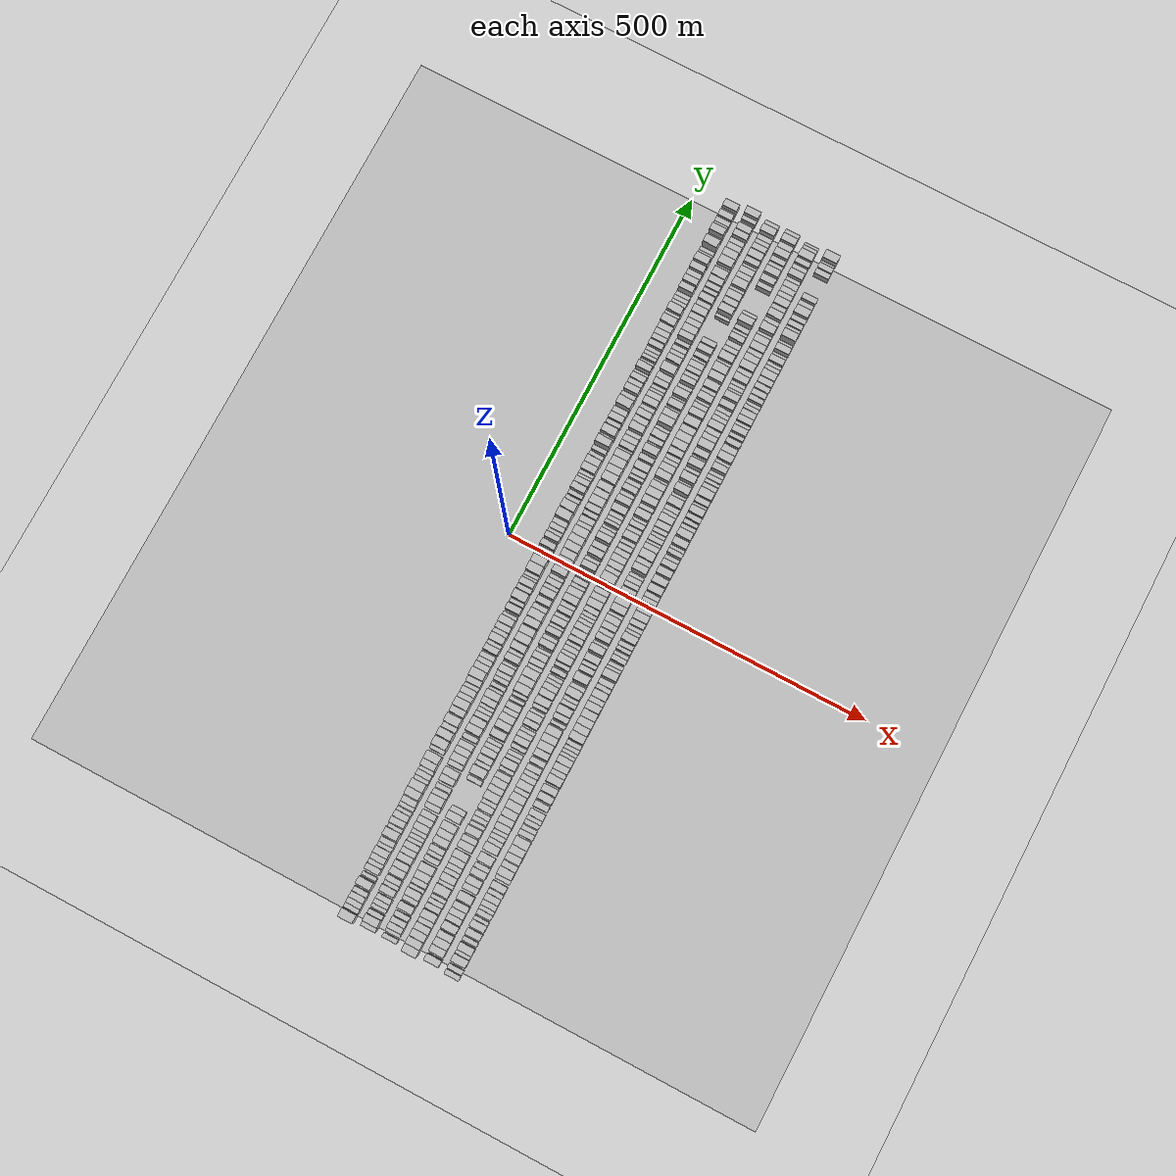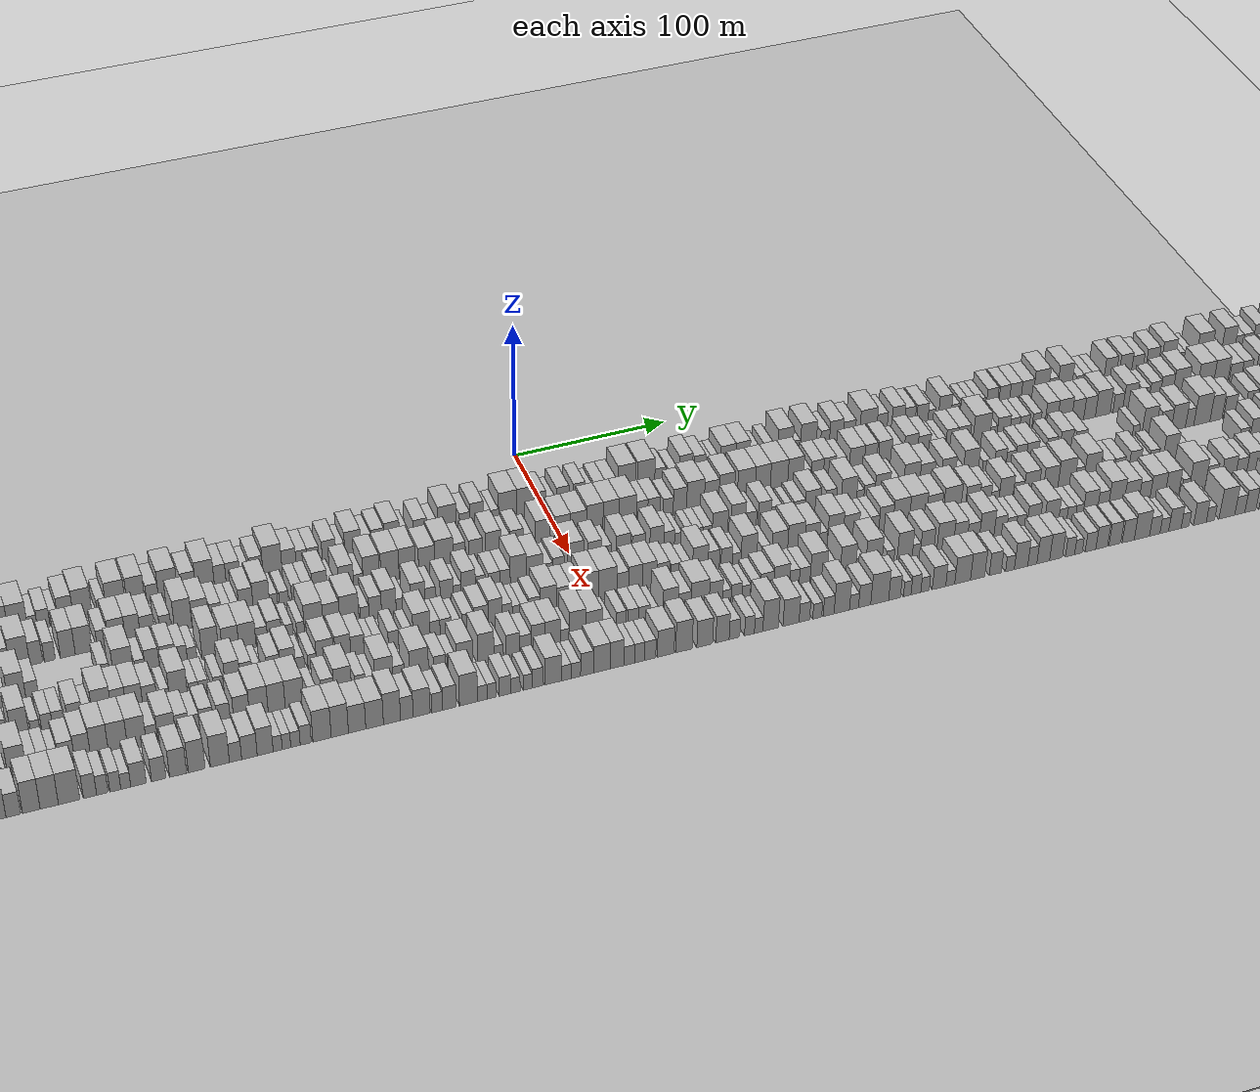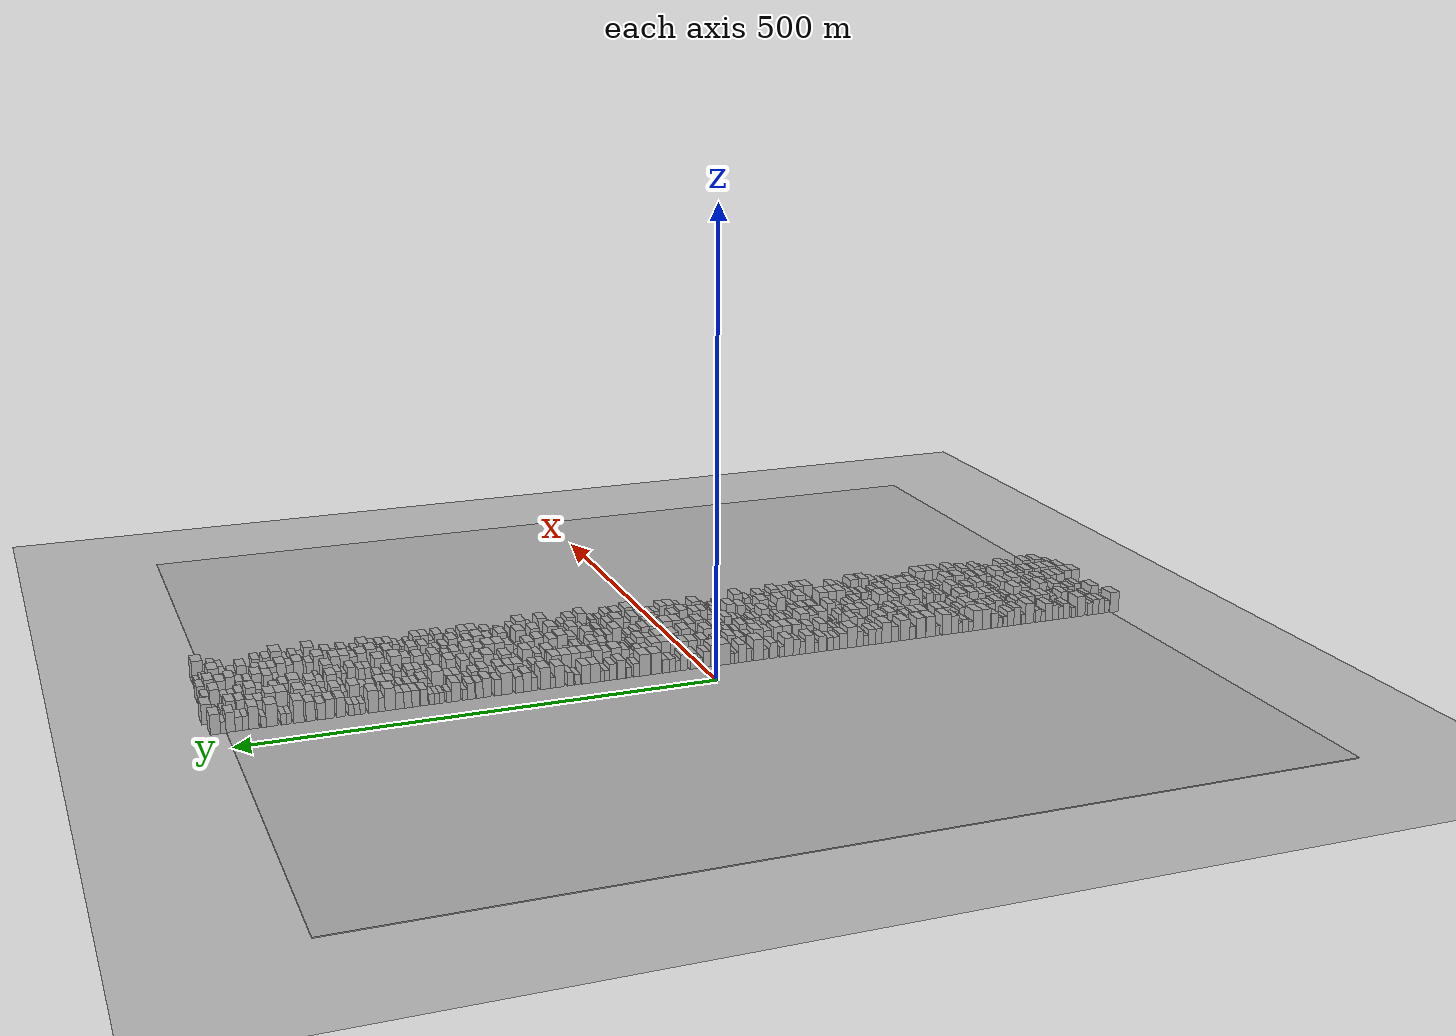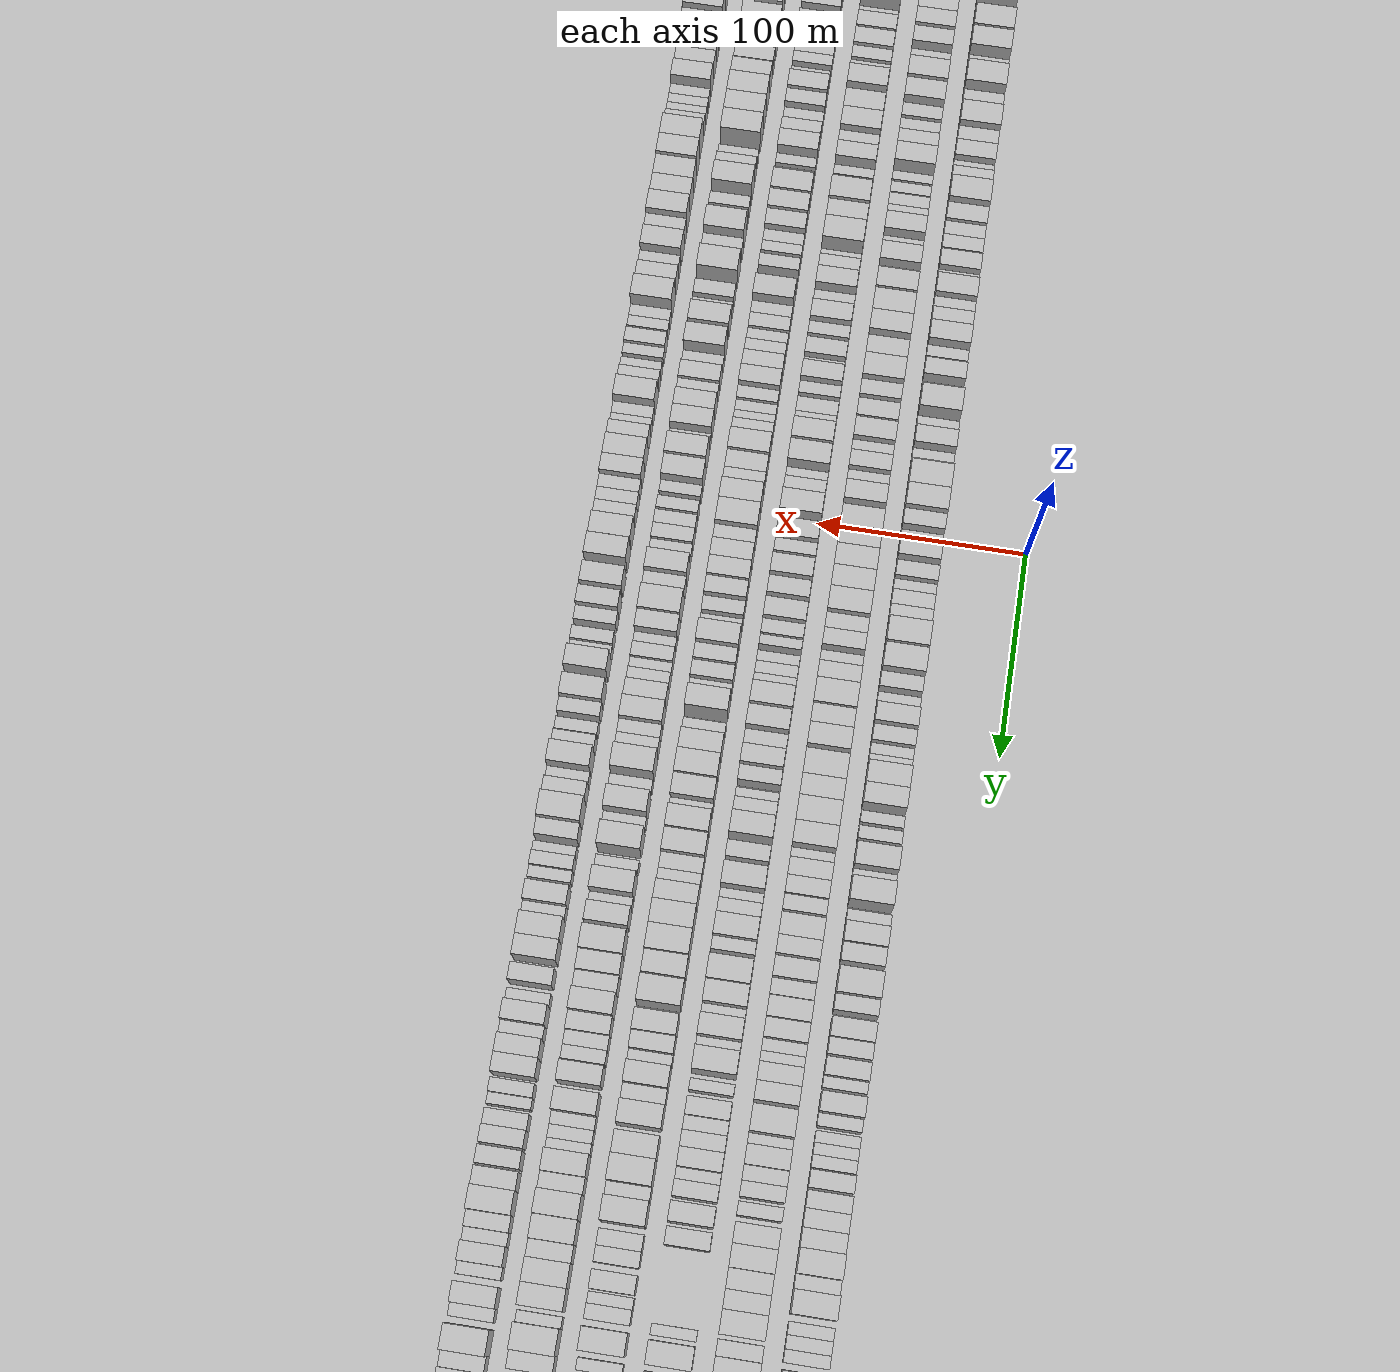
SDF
<?xml version="1.0" encoding="utf-8"?>

<sdf version="1.6">

   <world name="default">

      <gui fullscreen="0">

         <camera name="user_camera">

            <pose>-15 0 4.57585 0 0 0</pose>

            <view_controller>orbit</view_controller>

         </camera>

      </gui>

      <scene>

         <sky>

           <clouds>

             <speed>12</speed>

           </clouds>

         </sky>

         <ambient>0.4 0.4 0.4 1</ambient>

         <background>0.7 0.7 0.7 1</background>

         <shadows>1</shadows>

      </scene>

      <gravity>0 0 -9.8066</gravity>

      <magnetic_field>6e-06 2.3e-05 -4.2e-05</magnetic_field>

      <physics default="0" name="default_physics" type="ode">

         <ode>

            <solver>

               <type>quick</type>

               <iters>10</iters>

               <sor>1.0</sor>

               <use_dynamic_moi_rescaling>0</use_dynamic_moi_rescaling>

            </solver>

            <constraints>

               <cfm>0</cfm>

               <erp>0.2</erp>

               <contact_max_correcting_vel>100</contact_max_correcting_vel>

               <contact_surface_layer>0.001</contact_surface_layer>

            </constraints>

         </ode>

         <max_step_size>0.004</max_step_size>

         <real_time_factor>1</real_time_factor>

         <real_time_update_rate>250</real_time_update_rate>

      </physics>

      <light name="sun" type="directional">

         <cast_shadows>1</cast_shadows>

         <pose>0 0 10 0 0 0</pose>

         <diffuse>0.8 0.8 0.8 1</diffuse>

         <specular>0.2 0.2 0.2 1</specular>

         <attenuation>

            <range>1000</range>

            <constant>0.9</constant>

            <linear>0.01</linear>

            <quadratic>0.001</quadratic>

         </attenuation>

         <direction>-0.5 0.1 -0.9</direction>

      </light>

      <include>

         <name>ground_plane_1</name>

         <uri>model://HANNAS_ground_plane</uri>

         <pose>0 0 0  0 0 0</pose>

      </include>

      <include>

         <name>ground_plane_2</name>

         <uri>model://HANNAS_ground_plane</uri>

         <pose>100 0 0  0 0 0</pose>

      </include>

      <model name="building_1">

         <static>1</static>

         <pose frame="">50.0000 -504.2611 0 0.000000 0.000000 0.000000</pose>

         <link name="link">

            <pose frame="">0 0 12.00 0 0 0</pose>

            <collision name="collision">

               <geometry>

                  <box>

                     <size>20.0000 11.4779 24.0000</size>

                  </box>

               </geometry>

               <max_contacts>10</max_contacts>

               <surface>

                  <contact>

                     <ode/>

                  </contact>

                  <bounce/>

                  <friction>

                     <torsional>

                        <ode/>

                     </torsional>

                     <ode/>

                  </friction>

               </surface>

            </collision>

            <visual name="visual">

               <cast_shadows>0</cast_shadows>

               <geometry>

                  <box>

                     <size>20.0000 11.4779 24.0000</size>

                  </box>

               </geometry>

               <material>

                  <script>

                     <uri>model://HANNAS_wall/materials/scripts</uri>

                     <uri>model://HANNAS_wall/materials/textures</uri>

                     <name>vrc/HANNAS_wall</name>

                  </script>

               </material>

            </visual>

            <self_collide>0</self_collide>

            <enable_wind>0</enable_wind>

            <kinematic>0</kinematic>

         </link>

      </model>

      <model name="building_2">

         <static>1</static>

         <pose frame="">50.0000 -494.3358 0 0.000000 0.000000 0.000000</pose>

         <link name="link">

            <pose frame="">0 0 7.50 0 0 0</pose>

            <collision name="collision">

               <geometry>

                  <box>

                     <size>20.0000 6.3727 15.0000</size>

                  </box>

               </geometry>

               <max_contacts>10</max_contacts>

               <surface>

                  <contact>

                     <ode/>

                  </contact>

                  <bounce/>

                  <friction>

                     <torsional>

                        <ode/>

                     </torsional>

                     <ode/>

                  </friction>

               </surface>

            </collision>

            <visual name="visual">

               <cast_shadows>0</cast_shadows>

               <geometry>

                  <box>

                     <size>20.0000 6.3727 15.0000</size>

                  </box>

               </geometry>

               <material>

                  <script>

                     <uri>model://HANNAS_wall/materials/scripts</uri>

                     <uri>model://HANNAS_wall/materials/textures</uri>

                     <name>vrc/HANNAS_wall</name>

                  </script>

               </material>

            </visual>

            <self_collide>0</self_collide>

            <enable_wind>0</enable_wind>

            <kinematic>0</kinematic>

         </link>

      </model>

      <model name="building_3">

         <static>1</static>

         <pose frame="">50.0000 -487.5108 0 0.000000 0.000000 0.000000</pose>

         <link name="link">

            <pose frame="">0 0 9.00 0 0 0</pose>

            <collision name="collision">

               <geometry>

                  <box>

                     <size>20.0000 7.2772 18.0000</size>

                  </box>

               </geometry>

               <max_contacts>10</max_contacts>

               <surface>

                  <contact>

                     <ode/>

                  </contact>

                  <bounce/>

                  <friction>

                     <torsional>

                        <ode/>

                     </torsional>

                     <ode/>

                  </friction>

               </surface>

            </collision>

            <visual name="visual">

               <cast_shadows>0</cast_shadows>

               <geometry>

                  <box>

                     <size>20.0000 7.2772 18.0000</size>

                  </box>

               </geometry>

               <material>

                  <script>

                     <uri>model://HANNAS_wall/materials/scripts</uri>

                     <uri>model://HANNAS_wall/materials/textures</uri>

                     <name>vrc/HANNAS_wall</name>

                  </script>

               </material>

            </visual>

            <self_collide>0</self_collide>

            <enable_wind>0</enable_wind>

            <kinematic>0</kinematic>

         </link>

      </model>

      <model name="building_4">

         <static>1</static>

         <pose frame="">50.0000 -479.9016 0 0.000000 0.000000 0.000000</pose>

         <link name="link">

            <pose frame="">0 0 9.00 0 0 0</pose>

            <collision name="collision">

               <geometry>

                  <box>

                     <size>20.0000 7.9412 18.0000</size>

                  </box>

               </geometry>

               <max_contacts>10</max_contacts>

               <surface>

                  <contact>

                     <ode/>

                  </contact>

                  <bounce/>

                  <friction>

                     <torsional>

                        <ode/>

                     </torsional>

                     <ode/>

                  </friction>

               </surface>

            </collision>

            <visual name="visual">

               <cast_shadows>0</cast_shadows>

               <geometry>

                  <box>

                     <size>20.0000 7.9412 18.0000</size>

                  </box>

               </geometry>

               <material>

                  <script>

                     <uri>model://HANNAS_wall/materials/scripts</uri>

                     <uri>model://HANNAS_wall/materials/textures</uri>

                     <name>vrc/HANNAS_wall</name>

                  </script>

               </material>

            </visual>

            <self_collide>0</self_collide>

            <enable_wind>0</enable_wind>

            <kinematic>0</kinematic>

         </link>

      </model>

      <model name="building_5">

         <static>1</static>

         <pose frame="">50.0000 -472.4386 0 0.000000 0.000000 0.000000</pose>

         <link name="link">

            <pose frame="">0 0 7.50 0 0 0</pose>

            <collision name="collision">

               <geometry>

                  <box>

                     <size>20.0000 6.9848 15.0000</size>

                  </box>

               </geometry>

               <max_contacts>10</max_contacts>

               <surface>

                  <contact>

                     <ode/>

                  </contact>

                  <bounce/>

                  <friction>

                     <torsional>

                        <ode/>

                     </torsional>

                     <ode/>

                  </friction>

               </surface>

            </collision>

            <visual name="visual">

               <cast_shadows>0</cast_shadows>

               <geometry>

                  <box>

                     <size>20.0000 6.9848 15.0000</size>

                  </box>

               </geometry>

               <material>

                  <script>

                     <uri>model://HANNAS_wall/materials/scripts</uri>

                     <uri>model://HANNAS_wall/materials/textures</uri>

                     <name>vrc/HANNAS_wall</name>

                  </script>

               </material>

            </visual>

            <self_collide>0</self_collide>

            <enable_wind>0</enable_wind>

            <kinematic>0</kinematic>

         </link>

      </model>

      <model name="building_6">

         <static>1</static>

         <pose frame="">50.0000 -460.8324 0 0.000000 0.000000 0.000000</pose>

         <link name="link">

            <pose frame="">0 0 12.00 0 0 0</pose>

            <collision name="collision">

               <geometry>

                  <box>

                     <size>20.0000 10.2276 24.0000</size>

                  </box>

               </geometry>

               <max_contacts>10</max_contacts>

               <surface>

                  <contact>

                     <ode/>

                  </contact>

                  <bounce/>

                  <friction>

                     <torsional>

                        <ode/>

                     </torsional>

                     <ode/>

                  </friction>

               </surface>

            </collision>

            <visual name="visual">

               <cast_shadows>0</cast_shadows>

               <geometry>

                  <box>

                     <size>20.0000 10.2276 24.0000</size>

                  </box>

               </geometry>

               <material>

                  <script>

                     <uri>model://HANNAS_wall/materials/scripts</uri>

                     <uri>model://HANNAS_wall/materials/textures</uri>

                     <name>vrc/HANNAS_wall</name>

                  </script>

               </material>

            </visual>

            <self_collide>0</self_collide>

            <enable_wind>0</enable_wind>

            <kinematic>0</kinematic>

         </link>

      </model>

      <model name="building_7">

         <static>1</static>

         <pose frame="">50.0000 -451.1623 0 0.000000 0.000000 0.000000</pose>

         <link name="link">

            <pose frame="">0 0 6.00 0 0 0</pose>

            <collision name="collision">

               <geometry>

                  <box>

                     <size>20.0000 5.1126 12.0000</size>

                  </box>

               </geometry>

               <max_contacts>10</max_contacts>

               <surface>

                  <contact>

                     <ode/>

                  </contact>

                  <bounce/>

                  <friction>

                     <torsional>

                        <ode/>

                     </torsional>

                     <ode/>

                  </friction>

               </surface>

            </collision>

            <visual name="visual">

               <cast_shadows>0</cast_shadows>

               <geometry>

                  <box>

                     <size>20.0000 5.1126 12.0000</size>

                  </box>

               </geometry>

               <material>

                  <script>

                     <uri>model://HANNAS_wall/materials/scripts</uri>

                     <uri>model://HANNAS_wall/materials/textures</uri>

                     <name>vrc/HANNAS_wall</name>

                  </script>

               </material>

            </visual>

            <self_collide>0</self_collide>

            <enable_wind>0</enable_wind>

            <kinematic>0</kinematic>

         </link>

      </model>

      <model name="building_8">

         <static>1</static>

         <pose frame="">50.0000 -441.5834 0 0.000000 0.000000 0.000000</pose>

         <link name="link">

            <pose frame="">0 0 9.00 0 0 0</pose>

            <collision name="collision">

               <geometry>

                  <box>

                     <size>20.0000 8.0451 18.0000</size>

                  </box>

               </geometry>

               <max_contacts>10</max_contacts>

               <surface>

                  <contact>

                     <ode/>

                  </contact>

                  <bounce/>

                  <friction>

                     <torsional>

                        <ode/>

                     </torsional>

                     <ode/>

                  </friction>

               </surface>

            </collision>

            <visual name="visual">

               <cast_shadows>0</cast_shadows>

               <geometry>

                  <box>

                     <size>20.0000 8.0451 18.0000</size>

                  </box>

               </geometry>

               <material>

                  <script>

                     <uri>model://HANNAS_wall/materials/scripts</uri>

                     <uri>model://HANNAS_wall/materials/textures</uri>

                     <name>vrc/HANNAS_wall</name>

                  </script>

               </material>

            </visual>

            <self_collide>0</self_collide>

            <enable_wind>0</enable_wind>

            <kinematic>0</kinematic>

         </link>

      </model>

      <model name="building_9">

         <static>1</static>

         <pose frame="">50.0000 -434.5429 0 0.000000 0.000000 0.000000</pose>

         <link name="link">

            <pose frame="">0 0 7.50 0 0 0</pose>

            <collision name="collision">

               <geometry>

                  <box>

                     <size>20.0000 6.0360 15.0000</size>

                  </box>

               </geometry>

               <max_contacts>10</max_contacts>

               <surface>

                  <contact>

                     <ode/>

                  </contact>

                  <bounce/>

                  <friction>

                     <torsional>

                        <ode/>

                     </torsional>

                     <ode/>

                  </friction>

               </surface>

            </collision>

            <visual name="visual">

               <cast_shadows>0</cast_shadows>

               <geometry>

                  <box>

                     <size>20.0000 6.0360 15.0000</size>

                  </box>

               </geometry>

               <material>

                  <script>

                     <uri>model://HANNAS_wall/materials/scripts</uri>

                     <uri>model://HANNAS_wall/materials/textures</uri>

                     <name>vrc/HANNAS_wall</name>

                  </script>

               </material>

            </visual>

            <self_collide>0</self_collide>

            <enable_wind>0</enable_wind>

            <kinematic>0</kinematic>

         </link>

      </model>

      <model name="building_10">

         <static>1</static>

         <pose frame="">50.0000 -427.5865 0 0.000000 0.000000 0.000000</pose>

         <link name="link">

            <pose frame="">0 0 9.00 0 0 0</pose>

            <collision name="collision">

               <geometry>

                  <box>

                     <size>20.0000 7.8767 18.0000</size>

                  </box>

               </geometry>

               <max_contacts>10</max_contacts>

               <surface>

                  <contact>

                     <ode/>

                  </contact>

                  <bounce/>

                  <friction>

                     <torsional>

                        <ode/>

                     </torsional>

                     <ode/>

                  </friction>

               </surface>

            </collision>

            <visual name="visual">

               <cast_shadows>0</cast_shadows>

               <geometry>

                  <box>

                     <size>20.0000 7.8767 18.0000</size>

                  </box>

               </geometry>

               <material>

                  <script>

                     <uri>model://HANNAS_wall/materials/scripts</uri>

                     <uri>model://HANNAS_wall/materials/textures</uri>

                     <name>vrc/HANNAS_wall</name>

                  </script>

               </material>

            </visual>

            <self_collide>0</self_collide>

            <enable_wind>0</enable_wind>

            <kinematic>0</kinematic>

         </link>

      </model>

      <model name="building_11">

         <static>1</static>

         <pose frame="">50.0000 -419.0270 0 0.000000 0.000000 0.000000</pose>

         <link name="link">

            <pose frame="">0 0 10.50 0 0 0</pose>

            <collision name="collision">

               <geometry>

                  <box>

                     <size>20.0000 9.2422 21.0000</size>

                  </box>

               </geometry>

               <max_contacts>10</max_contacts>

               <surface>

                  <contact>

                     <ode/>

                  </contact>

                  <bounce/>

                  <friction>

                     <torsional>

                        <ode/>

                     </torsional>

                     <ode/>

                  </friction>

               </surface>

            </collision>

            <visual name="visual">

               <cast_shadows>0</cast_shadows>

               <geometry>

                  <box>

                     <size>20.0000 9.2422 21.0000</size>

                  </box>

               </geometry>

               <material>

                  <script>

                     <uri>model://HANNAS_wall/materials/scripts</uri>

                     <uri>model://HANNAS_wall/materials/textures</uri>

                     <name>vrc/HANNAS_wall</name>

                  </script>

               </material>

            </visual>

            <self_collide>0</self_collide>

            <enable_wind>0</enable_wind>

            <kinematic>0</kinematic>

         </link>

      </model>

      <model name="building_12">

         <static>1</static>

         <pose frame="">50.0000 -411.6132 0 0.000000 0.000000 0.000000</pose>

         <link name="link">

            <pose frame="">0 0 6.00 0 0 0</pose>

            <collision name="collision">

               <geometry>

                  <box>

                     <size>20.0000 5.5854 12.0000</size>

                  </box>

               </geometry>

               <max_contacts>10</max_contacts>

               <surface>

                  <contact>

                     <ode/>

                  </contact>

                  <bounce/>

                  <friction>

                     <torsional>

                        <ode/>

                     </torsional>

                     <ode/>

                  </friction>

               </surface>

            </collision>

            <visual name="visual">

               <cast_shadows>0</cast_shadows>

               <geometry>

                  <box>

                     <size>20.0000 5.5854 12.0000</size>

                  </box>

               </geometry>

               <material>

                  <script>

                     <uri>model://HANNAS_wall/materials/scripts</uri>

                     <uri>model://HANNAS_wall/materials/textures</uri>

                     <name>vrc/HANNAS_wall</name>

                  </script>

               </material>

            </visual>

            <self_collide>0</self_collide>

            <enable_wind>0</enable_wind>

            <kinematic>0</kinematic>

         </link>

      </model>

      <model name="building_13">

         <static>1</static>

         <pose frame="">50.0000 -405.1917 0 0.000000 0.000000 0.000000</pose>

         <link name="link">

            <pose frame="">0 0 7.50 0 0 0</pose>

            <collision name="collision">

               <geometry>

                  <box>

                     <size>20.0000 7.2575 15.0000</size>

                  </box>

               </geometry>

               <max_contacts>10</max_contacts>

               <surface>

                  <contact>

                     <ode/>

                  </contact>

                  <bounce/>

                  <friction>

                     <torsional>

                        <ode/>

                     </torsional>

                     <ode/>

                  </friction>

               </surface>

            </collision>

            <visual name="visual">

               <cast_shadows>0</cast_shadows>

               <geometry>

                  <box>

                     <size>20.0000 7.2575 15.0000</size>

                  </box>

               </geometry>

               <material>

                  <script>

                     <uri>model://HANNAS_wall/materials/scripts</uri>

                     <uri>model://HANNAS_wall/materials/textures</uri>

                     <name>vrc/HANNAS_wall</name>

                  </script>

               </material>

            </visual>

            <self_collide>0</self_collide>

            <enable_wind>0</enable_wind>

            <kinematic>0</kinematic>

         </link>

      </model>

      <model name="building_14">

         <static>1</static>

         <pose frame="">50.0000 -394.1931 0 0.000000 0.000000 0.000000</pose>

         <link name="link">

            <pose frame="">0 0 12.00 0 0 0</pose>

            <collision name="collision">

               <geometry>

                  <box>

                     <size>20.0000 10.7398 24.0000</size>

                  </box>

               </geometry>

               <max_contacts>10</max_contacts>

               <surface>

                  <contact>

                     <ode/>

                  </contact>

                  <bounce/>

                  <friction>

                     <torsional>

                        <ode/>

                     </torsional>

                     <ode/>

                  </friction>

               </surface>

            </collision>

            <visual name="visual">

               <cast_shadows>0</cast_shadows>

               <geometry>

                  <box>

                     <size>20.0000 10.7398 24.0000</size>

                  </box>

               </geometry>

               <material>

                  <script>

                     <uri>model://HANNAS_wall/materials/scripts</uri>

                     <uri>model://HANNAS_wall/materials/textures</uri>

                     <name>vrc/HANNAS_wall</name>

                  </script>

               </material>

            </visual>

            <self_collide>0</self_collide>

            <enable_wind>0</enable_wind>

            <kinematic>0</kinematic>

         </link>

      </model>

      <model name="building_15">

         <static>1</static>

         <pose frame="">50.0000 -386.2215 0 0.000000 0.000000 0.000000</pose>

         <link name="link">

            <pose frame="">0 0 6.00 0 0 0</pose>

            <collision name="collision">

               <geometry>

                  <box>

                     <size>20.0000 5.2034 12.0000</size>

                  </box>

               </geometry>

               <max_contacts>10</max_contacts>

               <surface>

                  <contact>

                     <ode/>

                  </contact>

                  <bounce/>

                  <friction>

                     <torsional>

                        <ode/>

                     </torsional>

                     <ode/>

                  </friction>

               </surface>

            </collision>

            <visual name="visual">

               <cast_shadows>0</cast_shadows>

               <geometry>

                  <box>

                     <size>20.0000 5.2034 12.0000</size>

                  </box>

               </geometry>

               <material>

                  <script>

                     <uri>model://HANNAS_wall/materials/scripts</uri>

                     <uri>model://HANNAS_wall/materials/textures</uri>

                     <name>vrc/HANNAS_wall</name>

                  </script>

               </material>

            </visual>

            <self_collide>0</self_collide>

            <enable_wind>0</enable_wind>

            <kinematic>0</kinematic>

         </link>

      </model>

      <model name="building_16">

         <static>1</static>

         <pose frame="">50.0000 -378.4043 0 0.000000 0.000000 0.000000</pose>

         <link name="link">

            <pose frame="">0 0 10.50 0 0 0</pose>

            <collision name="collision">

               <geometry>

                  <box>

                     <size>20.0000 8.4311 21.0000</size>

                  </box>

               </geometry>

               <max_contacts>10</max_contacts>

               <surface>

                  <contact>

                     <ode/>

                  </contact>

                  <bounce/>

                  <friction>

                     <torsional>

                        <ode/>

                     </torsional>

                     <ode/>

                  </friction>

               </surface>

            </collision>

            <visual name="visual">

               <cast_shadows>0</cast_shadows>

               <geometry>

                  <box>

                     <size>20.0000 8.4311 21.0000</size>

                  </box>

               </geometry>

               <material>

                  <script>

                     <uri>model://HANNAS_wall/materials/scripts</uri>

                     <uri>model://HANNAS_wall/materials/textures</uri>

                     <name>vrc/HANNAS_wall</name>

                  </script>

               </material>

            </visual>

            <self_collide>0</self_collide>

            <enable_wind>0</enable_wind>

            <kinematic>0</kinematic>

         </link>

      </model>

      <model name="building_17">

         <static>1</static>

         <pose frame="">50.0000 -369.9355 0 0.000000 0.000000 0.000000</pose>

         <link name="link">

            <pose frame="">0 0 9.00 0 0 0</pose>

            <collision name="collision">

               <geometry>

                  <box>

                     <size>20.0000 8.5065 18.0000</size>

                  </box>

               </geometry>

               <max_contacts>10</max_contacts>

               <surface>

                  <contact>

                     <ode/>

                  </contact>

                  <bounce/>

                  <friction>

                     <torsional>

                        <ode/>

                     </torsional>

                     <ode/>

                  </friction>

               </surface>

            </collision>

            <visual name="visual">

               <cast_shadows>0</cast_shadows>

               <geometry>

                  <box>

                     <size>20.0000 8.5065 18.0000</size>

                  </box>

               </geometry>

               <material>

                  <script>

                     <uri>model://HANNAS_wall/materials/scripts</uri>

                     <uri>model://HANNAS_wall/materials/textures</uri>

                     <name>vrc/HANNAS_wall</name>

                  </script>

               </material>

            </visual>

            <self_collide>0</self_collide>

            <enable_wind>0</enable_wind>

            <kinematic>0</kinematic>

         </link>

      </model>

      <model name="building_18">

         <static>1</static>

         <pose frame="">50.0000 -363.0840 0 0.000000 0.000000 0.000000</pose>

         <link name="link">

            <pose frame="">0 0 6.00 0 0 0</pose>

            <collision name="collision">

               <geometry>

                  <box>

                     <size>20.0000 5.1966 12.0000</size>

                  </box>

               </geometry>

               <max_contacts>10</max_contacts>

               <surface>

                  <contact>

                     <ode/>

                  </contact>

                  <bounce/>

                  <friction>

                     <torsional>

                        <ode/>

                     </torsional>

                     <ode/>

                  </friction>

               </surface>

            </collision>

            <visual name="visual">

               <cast_shadows>0</cast_shadows>

               <geometry>

                  <box>

                     <size>20.0000 5.1966 12.0000</size>

                  </box>

               </geometry>

               <material>

                  <script>

                     <uri>model://HANNAS_wall/materials/scripts</uri>

                     <uri>model://HANNAS_wall/materials/textures</uri>

                     <name>vrc/HANNAS_wall</name>

                  </script>

               </material>

            </visual>

            <self_collide>0</self_collide>

            <enable_wind>0</enable_wind>

            <kinematic>0</kinematic>

         </link>

      </model>

      <model name="building_19">

         <static>1</static>

         <pose frame="">50.0000 -356.7629 0 0.000000 0.000000 0.000000</pose>

         <link name="link">

            <pose frame="">0 0 6.00 0 0 0</pose>

            <collision name="collision">

               <geometry>

                  <box>

                     <size>20.0000 5.4455 12.0000</size>

                  </box>

               </geometry>

               <max_contacts>10</max_contacts>

               <surface>

                  <contact>

                     <ode/>

                  </contact>

                  <bounce/>

                  <friction>

                     <torsional>

                        <ode/>

                     </torsional>

                     <ode/>

                  </friction>

               </surface>

            </collision>

            <visual name="visual">

               <cast_shadows>0</cast_shadows>

               <geometry>

                  <box>

                     <size>20.0000 5.4455 12.0000</size>

                  </box>

               </geometry>

               <material>

                  <script>

                     <uri>model://HANNAS_wall/materials/scripts</uri>

                     <uri>model://HANNAS_wall/materials/textures</uri>

                     <name>vrc/HANNAS_wall</name>

                  </script>

               </material>

            </visual>

            <self_collide>0</self_collide>

            <enable_wind>0</enable_wind>

            <kinematic>0</kinematic>

         </link>

      </model>

      <model name="building_20">

         <static>1</static>

         <pose frame="">50.0000 -349.8365 0 0.000000 0.000000 0.000000</pose>

         <link name="link">

            <pose frame="">0 0 9.00 0 0 0</pose>

            <collision name="collision">

               <geometry>

                  <box>

                     <size>20.0000 8.4072 18.0000</size>

                  </box>

               </geometry>

               <max_contacts>10</max_contacts>

               <surface>

                  <contact>

                     <ode/>

                  </contact>

                  <bounce/>

                  <friction>

                     <torsional>

                        <ode/>

                     </torsional>

                     <ode/>

                  </friction>

               </surface>

            </collision>

            <visual name="visual">

               <cast_shadows>0</cast_shadows>

               <geometry>

                  <box>

                     <size>20.0000 8.4072 18.0000</size>

                  </box>

               </geometry>

               <material>

                  <script>

                     <uri>model://HANNAS_wall/materials/scripts</uri>

                     <uri>model://HANNAS_wall/materials/textures</uri>

                     <name>vrc/HANNAS_wall</name>

                  </script>

               </material>

            </visual>

            <self_collide>0</self_collide>

            <enable_wind>0</enable_wind>

            <kinematic>0</kinematic>

         </link>

      </model>

      <model name="building_21">

         <static>1</static>

         <pose frame="">50.0000 -339.3673 0 0.000000 0.000000 0.000000</pose>

         <link name="link">

            <pose frame="">0 0 12.00 0 0 0</pose>

            <collision name="collision">

               <geometry>

                  <box>

                     <size>20.0000 10.5312 24.0000</size>

                  </box>

               </geometry>

               <max_contacts>10</max_contacts>

               <surface>

                  <contact>

                     <ode/>

                  </contact>

                  <bounce/>

                  <friction>

                     <torsional>

                        <ode/>

                     </torsional>

                     <ode/>

                  </friction>

               </surface>

            </collision>

            <visual name="visual">

               <cast_shadows>0</cast_shadows>

               <geometry>

                  <box>

                     <size>20.0000 10.5312 24.0000</size>

                  </box>

               </geometry>

               <material>

                  <script>

                     <uri>model://HANNAS_wall/materials/scripts</uri>

                     <uri>model://HANNAS_wall/materials/textures</uri>

                     <name>vrc/HANNAS_wall</name>

                  </script>

               </material>

            </visual>

            <self_collide>0</self_collide>

            <enable_wind>0</enable_wind>

            <kinematic>0</kinematic>

         </link>

      </model>

      <model name="building_22">

         <static>1</static>

         <pose frame="">50.0000 -328.3895 0 0.000000 0.000000 0.000000</pose>

         <link name="link">

            <pose frame="">0 0 12.00 0 0 0</pose>

            <collision name="collision">

               <geometry>

                  <box>

                     <size>20.0000 11.4244 24.0000</size>

                  </box>

               </geometry>

               <max_contacts>10</max_contacts>

               <surface>

                  <contact>

                     <ode/>

                  </contact>

                  <bounce/>

                  <friction>

                     <torsional>

                        <ode/>

                     </torsional>

                     <ode/>

                  </friction>

               </surface>

            </collision>

            <visual name="visual">

               <cast_shadows>0</cast_shadows>

               <geometry>

                  <box>

                     <size>20.0000 11.4244 24.0000</size>

                  </box>

               </geometry>

               <material>

                  <script>

                     <uri>model://HANNAS_wall/materials/scripts</uri>

                     <uri>model://HANNAS_wall/materials/textures</uri>

                     <name>vrc/HANNAS_wall</name>

                  </script>

               </material>

            </visual>

            <self_collide>0</self_collide>

            <enable_wind>0</enable_wind>

            <kinematic>0</kinematic>

         </link>

      </model>

      <model name="building_23">

         <static>1</static>

         <pose frame="">50.0000 -319.8592 0 0.000000 0.000000 0.000000</pose>

         <link name="link">

            <pose frame="">0 0 6.00 0 0 0</pose>

            <collision name="collision">

               <geometry>

                  <box>

                     <size>20.0000 5.6362 12.0000</size>

                  </box>

               </geometry>

               <max_contacts>10</max_contacts>

               <surface>

                  <contact>

                     <ode/>

                  </contact>

                  <bounce/>

                  <friction>

                     <torsional>

                        <ode/>

                     </torsional>

                     <ode/>

                  </friction>

               </surface>

            </collision>

            <visual name="visual">

               <cast_shadows>0</cast_shadows>

               <geometry>

                  <box>

                     <size>20.0000 5.6362 12.0000</size>

                  </box>

               </geometry>

               <material>

                  <script>

                     <uri>model://HANNAS_wall/materials/scripts</uri>

                     <uri>model://HANNAS_wall/materials/textures</uri>

                     <name>vrc/HANNAS_wall</name>

                  </script>

               </material>

            </visual>

            <self_collide>0</self_collide>

            <enable_wind>0</enable_wind>

            <kinematic>0</kinematic>

         </link>

      </model>

      <model name="building_24">

         <static>1</static>

         <pose frame="">50.0000 -313.3237 0 0.000000 0.000000 0.000000</pose>

         <link name="link">

            <pose frame="">0 0 7.50 0 0 0</pose>

            <collision name="collision">

               <geometry>

                  <box>

                     <size>20.0000 7.4347 15.0000</size>

                  </box>

               </geometry>

               <max_contacts>10</max_contacts>

               <surface>

                  <contact>

                     <ode/>

                  </contact>

                  <bounce/>

                  <friction>

                     <torsional>

                        <ode/>

                     </torsional>

                     <ode/>

                  </friction>

               </surface>

            </collision>

            <visual name="visual">

               <cast_shadows>0</cast_shadows>

               <geometry>

                  <box>

                     <size>20.0000 7.4347 15.0000</size>

                  </box>

               </geometry>

               <material>

                  <script>

                     <uri>model://HANNAS_wall/materials/scripts</uri>

                     <uri>model://HANNAS_wall/materials/textures</uri>

                     <name>vrc/HANNAS_wall</name>

                  </script>

               </material>

            </visual>

            <self_collide>0</self_collide>

            <enable_wind>0</enable_wind>

            <kinematic>0</kinematic>

         </link>

      </model>

      <model name="building_25">

         <static>1</static>

         <pose frame="">50.0000 -307.1202 0 0.000000 0.000000 0.000000</pose>

         <link name="link">

            <pose frame="">0 0 6.00 0 0 0</pose>

            <collision name="collision">

               <geometry>

                  <box>

                     <size>20.0000 4.9723 12.0000</size>

                  </box>

               </geometry>

               <max_contacts>10</max_contacts>

               <surface>

                  <contact>

                     <ode/>

                  </contact>

                  <bounce/>

                  <friction>

                     <torsional>

                        <ode/>

                     </torsional>

                     <ode/>

                  </friction>

               </surface>

            </collision>

            <visual name="visual">

               <cast_shadows>0</cast_shadows>

               <geometry>

                  <box>

                     <size>20.0000 4.9723 12.0000</size>

                  </box>

               </geometry>

               <material>

                  <script>

                     <uri>model://HANNAS_wall/materials/scripts</uri>

                     <uri>model://HANNAS_wall/materials/textures</uri>

                     <name>vrc/HANNAS_wall</name>

                  </script>

               </material>

            </visual>

            <self_collide>0</self_collide>

            <enable_wind>0</enable_wind>

            <kinematic>0</kinematic>

         </link>

      </model>

      <model name="building_26">

         <static>1</static>

         <pose frame="">50.0000 -300.0357 0 0.000000 0.000000 0.000000</pose>

         <link name="link">

            <pose frame="">0 0 10.50 0 0 0</pose>

            <collision name="collision">

               <geometry>

                  <box>

                     <size>20.0000 9.1967 21.0000</size>

                  </box>

               </geometry>

               <max_contacts>10</max_contacts>

               <surface>

                  <contact>

                     <ode/>

                  </contact>

                  <bounce/>

                  <friction>

                     <torsional>

                        <ode/>

                     </torsional>

                     <ode/>

                  </friction>

               </surface>

            </collision>

            <visual name="visual">

               <cast_shadows>0</cast_shadows>

               <geometry>

                  <box>

                     <size>20.0000 9.1967 21.0000</size>

                  </box>

               </geometry>

               <material>

                  <script>

                     <uri>model://HANNAS_wall/materials/scripts</uri>

                     <uri>model://HANNAS_wall/materials/textures</uri>

                     <name>vrc/HANNAS_wall</name>

                  </script>

               </material>

            </visual>

            <self_collide>0</self_collide>

            <enable_wind>0</enable_wind>

            <kinematic>0</kinematic>

         </link>

      </model>

      <model name="building_27">

         <static>1</static>

         <pose frame="">50.0000 -289.8618 0 0.000000 0.000000 0.000000</pose>

         <link name="link">

            <pose frame="">0 0 12.00 0 0 0</pose>

            <collision name="collision">

               <geometry>

                  <box>

                     <size>20.0000 11.1511 24.0000</size>

                  </box>

               </geometry>

               <max_contacts>10</max_contacts>

               <surface>

                  <contact>

                     <ode/>

                  </contact>

                  <bounce/>

                  <friction>

                     <torsional>

                        <ode/>

                     </torsional>

                     <ode/>

                  </friction>

               </surface>

            </collision>

            <visual name="visual">

               <cast_shadows>0</cast_shadows>

               <geometry>

                  <box>

                     <size>20.0000 11.1511 24.0000</size>

                  </box>

               </geometry>

               <material>

                  <script>

                     <uri>model://HANNAS_wall/materials/scripts</uri>

                     <uri>model://HANNAS_wall/materials/textures</uri>

                     <name>vrc/HANNAS_wall</name>

                  </script>

               </material>

            </visual>

            <self_collide>0</self_collide>

            <enable_wind>0</enable_wind>

            <kinematic>0</kinematic>

         </link>

      </model>

      <model name="building_28">

         <static>1</static>

         <pose frame="">50.0000 -278.5699 0 0.000000 0.000000 0.000000</pose>

         <link name="link">

            <pose frame="">0 0 6.00 0 0 0</pose>

            <collision name="collision">

               <geometry>

                  <box>

                     <size>20.0000 5.4326 12.0000</size>

                  </box>

               </geometry>

               <max_contacts>10</max_contacts>

               <surface>

                  <contact>

                     <ode/>

                  </contact>

                  <bounce/>

                  <friction>

                     <torsional>

                        <ode/>

                     </torsional>

                     <ode/>

                  </friction>

               </surface>

            </collision>

            <visual name="visual">

               <cast_shadows>0</cast_shadows>

               <geometry>

                  <box>

                     <size>20.0000 5.4326 12.0000</size>

                  </box>

               </geometry>

               <material>

                  <script>

                     <uri>model://HANNAS_wall/materials/scripts</uri>

                     <uri>model://HANNAS_wall/materials/textures</uri>

                     <name>vrc/HANNAS_wall</name>

                  </script>

               </material>

            </visual>

            <self_collide>0</self_collide>

            <enable_wind>0</enable_wind>

            <kinematic>0</kinematic>

         </link>

      </model>

      <model name="building_29">

         <static>1</static>

         <pose frame="">50.0000 -270.0083 0 0.000000 0.000000 0.000000</pose>

         <link name="link">

            <pose frame="">0 0 12.00 0 0 0</pose>

            <collision name="collision">

               <geometry>

                  <box>

                     <size>20.0000 11.6905 24.0000</size>

                  </box>

               </geometry>

               <max_contacts>10</max_contacts>

               <surface>

                  <contact>

                     <ode/>

                  </contact>

                  <bounce/>

                  <friction>

                     <torsional>

                        <ode/>

                     </torsional>

                     <ode/>

                  </friction>

               </surface>

            </collision>

            <visual name="visual">

               <cast_shadows>0</cast_shadows>

               <geometry>

                  <box>

                     <size>20.0000 11.6905 24.0000</size>

                  </box>

               </geometry>

               <material>

                  <script>

                     <uri>model://HANNAS_wall/materials/scripts</uri>

                     <uri>model://HANNAS_wall/materials/textures</uri>

                     <name>vrc/HANNAS_wall</name>

                  </script>

               </material>

            </visual>

            <self_collide>0</self_collide>

            <enable_wind>0</enable_wind>

            <kinematic>0</kinematic>

         </link>

      </model>

      <model name="building_30">

         <static>1</static>

         <pose frame="">50.0000 -257.8183 0 0.000000 0.000000 0.000000</pose>

         <link name="link">

            <pose frame="">0 0 12.00 0 0 0</pose>

            <collision name="collision">

               <geometry>

                  <box>

                     <size>20.0000 10.6895 24.0000</size>

                  </box>

               </geometry>

               <max_contacts>10</max_contacts>

               <surface>

                  <contact>

                     <ode/>

                  </contact>

                  <bounce/>

                  <friction>

                     <torsional>

                        <ode/>

                     </torsional>

                     <ode/>

                  </friction>

               </surface>

            </collision>

            <visual name="visual">

               <cast_shadows>0</cast_shadows>

               <geometry>

                  <box>

                     <size>20.0000 10.6895 24.0000</size>

                  </box>

               </geometry>

               <material>

                  <script>

                     <uri>model://HANNAS_wall/materials/scripts</uri>

                     <uri>model://HANNAS_wall/materials/textures</uri>

                     <name>vrc/HANNAS_wall</name>

                  </script>

               </material>

            </visual>

            <self_collide>0</self_collide>

            <enable_wind>0</enable_wind>

            <kinematic>0</kinematic>

         </link>

      </model>

      <model name="building_31">

         <static>1</static>

         <pose frame="">50.0000 -247.8544 0 0.000000 0.000000 0.000000</pose>

         <link name="link">

            <pose frame="">0 0 7.50 0 0 0</pose>

            <collision name="collision">

               <geometry>

                  <box>

                     <size>20.0000 7.2383 15.0000</size>

                  </box>

               </geometry>

               <max_contacts>10</max_contacts>

               <surface>

                  <contact>

                     <ode/>

                  </contact>

                  <bounce/>

                  <friction>

                     <torsional>

                        <ode/>

                     </torsional>

                     <ode/>

                  </friction>

               </surface>

            </collision>

            <visual name="visual">

               <cast_shadows>0</cast_shadows>

               <geometry>

                  <box>

                     <size>20.0000 7.2383 15.0000</size>

                  </box>

               </geometry>

               <material>

                  <script>

                     <uri>model://HANNAS_wall/materials/scripts</uri>

                     <uri>model://HANNAS_wall/materials/textures</uri>

                     <name>vrc/HANNAS_wall</name>

                  </script>

               </material>

            </visual>

            <self_collide>0</self_collide>

            <enable_wind>0</enable_wind>

            <kinematic>0</kinematic>

         </link>

      </model>

      <model name="building_32">

         <static>1</static>

         <pose frame="">50.0000 -238.3556 0 0.000000 0.000000 0.000000</pose>

         <link name="link">

            <pose frame="">0 0 12.00 0 0 0</pose>

            <collision name="collision">

               <geometry>

                  <box>

                     <size>20.0000 11.7593 24.0000</size>

                  </box>

               </geometry>

               <max_contacts>10</max_contacts>

               <surface>

                  <contact>

                     <ode/>

                  </contact>

                  <bounce/>

                  <friction>

                     <torsional>

                        <ode/>

                     </torsional>

                     <ode/>

                  </friction>

               </surface>

            </collision>

            <visual name="visual">

               <cast_shadows>0</cast_shadows>

               <geometry>

                  <box>

                     <size>20.0000 11.7593 24.0000</size>

                  </box>

               </geometry>

               <material>

                  <script>

                     <uri>model://HANNAS_wall/materials/scripts</uri>

                     <uri>model://HANNAS_wall/materials/textures</uri>

                     <name>vrc/HANNAS_wall</name>

                  </script>

               </material>

            </visual>

            <self_collide>0</self_collide>

            <enable_wind>0</enable_wind>

            <kinematic>0</kinematic>

         </link>

      </model>

      <model name="building_33">

         <static>1</static>

         <pose frame="">50.0000 -225.9797 0 0.000000 0.000000 0.000000</pose>

         <link name="link">

            <pose frame="">0 0 9.00 0 0 0</pose>

            <collision name="collision">

               <geometry>

                  <box>

                     <size>20.0000 8.9925 18.0000</size>

                  </box>

               </geometry>

               <max_contacts>10</max_contacts>

               <surface>

                  <contact>

                     <ode/>

                  </contact>

                  <bounce/>

                  <friction>

                     <torsional>

                        <ode/>

                     </torsional>

                     <ode/>

                  </friction>

               </surface>

            </collision>

            <visual name="visual">

               <cast_shadows>0</cast_shadows>

               <geometry>

                  <box>

                     <size>20.0000 8.9925 18.0000</size>

                  </box>

               </geometry>

               <material>

                  <script>

                     <uri>model://HANNAS_wall/materials/scripts</uri>

                     <uri>model://HANNAS_wall/materials/textures</uri>

                     <name>vrc/HANNAS_wall</name>

                  </script>

               </material>

            </visual>

            <self_collide>0</self_collide>

            <enable_wind>0</enable_wind>

            <kinematic>0</kinematic>

         </link>

      </model>

      <model name="building_34">

         <static>1</static>

         <pose frame="">50.0000 -215.8119 0 0.000000 0.000000 0.000000</pose>

         <link name="link">

            <pose frame="">0 0 12.00 0 0 0</pose>

            <collision name="collision">

               <geometry>

                  <box>

                     <size>20.0000 11.3429 24.0000</size>

                  </box>

               </geometry>

               <max_contacts>10</max_contacts>

               <surface>

                  <contact>

                     <ode/>

                  </contact>

                  <bounce/>

                  <friction>

                     <torsional>

                        <ode/>

                     </torsional>

                     <ode/>

                  </friction>

               </surface>

            </collision>

            <visual name="visual">

               <cast_shadows>0</cast_shadows>

               <geometry>

                  <box>

                     <size>20.0000 11.3429 24.0000</size>

                  </box>

               </geometry>

               <material>

                  <script>

                     <uri>model://HANNAS_wall/materials/scripts</uri>

                     <uri>model://HANNAS_wall/materials/textures</uri>

                     <name>vrc/HANNAS_wall</name>

                  </script>

               </material>

            </visual>

            <self_collide>0</self_collide>

            <enable_wind>0</enable_wind>

            <kinematic>0</kinematic>

         </link>

      </model>

      <model name="building_35">

         <static>1</static>

         <pose frame="">50.0000 -206.5298 0 0.000000 0.000000 0.000000</pose>

         <link name="link">

            <pose frame="">0 0 9.00 0 0 0</pose>

            <collision name="collision">

               <geometry>

                  <box>

                     <size>20.0000 7.2213 18.0000</size>

                  </box>

               </geometry>

               <max_contacts>10</max_contacts>

               <surface>

                  <contact>

                     <ode/>

                  </contact>

                  <bounce/>

                  <friction>

                     <torsional>

                        <ode/>

                     </torsional>

                     <ode/>

                  </friction>

               </surface>

            </collision>

            <visual name="visual">

               <cast_shadows>0</cast_shadows>

               <geometry>

                  <box>

                     <size>20.0000 7.2213 18.0000</size>

                  </box>

               </geometry>

               <material>

                  <script>

                     <uri>model://HANNAS_wall/materials/scripts</uri>

                     <uri>model://HANNAS_wall/materials/textures</uri>

                     <name>vrc/HANNAS_wall</name>

                  </script>

               </material>

            </visual>

            <self_collide>0</self_collide>

            <enable_wind>0</enable_wind>

            <kinematic>0</kinematic>

         </link>

      </model>

      <model name="building_36">

         <static>1</static>

         <pose frame="">50.0000 -198.6016 0 0.000000 0.000000 0.000000</pose>

         <link name="link">

            <pose frame="">0 0 9.00 0 0 0</pose>

            <collision name="collision">

               <geometry>

                  <box>

                     <size>20.0000 8.6353 18.0000</size>

                  </box>

               </geometry>

               <max_contacts>10</max_contacts>

               <surface>

                  <contact>

                     <ode/>

                  </contact>

                  <bounce/>

                  <friction>

                     <torsional>

                        <ode/>

                     </torsional>

                     <ode/>

                  </friction>

               </surface>

            </collision>

            <visual name="visual">

               <cast_shadows>0</cast_shadows>

               <geometry>

                  <box>

                     <size>20.0000 8.6353 18.0000</size>

                  </box>

               </geometry>

               <material>

                  <script>

                     <uri>model://HANNAS_wall/materials/scripts</uri>

                     <uri>model://HANNAS_wall/materials/textures</uri>

                     <name>vrc/HANNAS_wall</name>

                  </script>

               </material>

            </visual>

            <self_collide>0</self_collide>

            <enable_wind>0</enable_wind>

            <kinematic>0</kinematic>

         </link>

      </model>

      <model name="building_37">

         <static>1</static>

         <pose frame="">50.0000 -191.3169 0 0.000000 0.000000 0.000000</pose>

         <link name="link">

            <pose frame="">0 0 6.00 0 0 0</pose>

            <collision name="collision">

               <geometry>

                  <box>

                     <size>20.0000 5.9340 12.0000</size>

                  </box>

               </geometry>

               <max_contacts>10</max_contacts>

               <surface>

                  <contact>

                     <ode/>

                  </contact>

                  <bounce/>

                  <friction>

                     <torsional>

                        <ode/>

                     </torsional>

                     <ode/>

                  </friction>

               </surface>

            </collision>

            <visual name="visual">

               <cast_shadows>0</cast_shadows>

               <geometry>

                  <box>

                     <size>20.0000 5.9340 12.0000</size>

                  </box>

               </geometry>

               <material>

                  <script>

                     <uri>model://HANNAS_wall/materials/scripts</uri>

                     <uri>model://HANNAS_wall/materials/textures</uri>

                     <name>vrc/HANNAS_wall</name>

                  </script>

               </material>

            </visual>

            <self_collide>0</self_collide>

            <enable_wind>0</enable_wind>

            <kinematic>0</kinematic>

         </link>

      </model>

      <model name="building_38">

         <static>1</static>

         <pose frame="">50.0000 -184.2565 0 0.000000 0.000000 0.000000</pose>

         <link name="link">

            <pose frame="">0 0 9.00 0 0 0</pose>

            <collision name="collision">

               <geometry>

                  <box>

                     <size>20.0000 8.1869 18.0000</size>

                  </box>

               </geometry>

               <max_contacts>10</max_contacts>

               <surface>

                  <contact>

                     <ode/>

                  </contact>

                  <bounce/>

                  <friction>

                     <torsional>

                        <ode/>

                     </torsional>

                     <ode/>

                  </friction>

               </surface>

            </collision>

            <visual name="visual">

               <cast_shadows>0</cast_shadows>

               <geometry>

                  <box>

                     <size>20.0000 8.1869 18.0000</size>

                  </box>

               </geometry>

               <material>

                  <script>

                     <uri>model://HANNAS_wall/materials/scripts</uri>

                     <uri>model://HANNAS_wall/materials/textures</uri>

                     <name>vrc/HANNAS_wall</name>

                  </script>

               </material>

            </visual>

            <self_collide>0</self_collide>

            <enable_wind>0</enable_wind>

            <kinematic>0</kinematic>

         </link>

      </model>

      <model name="building_39">

         <static>1</static>

         <pose frame="">50.0000 -174.2927 0 0.000000 0.000000 0.000000</pose>

         <link name="link">

            <pose frame="">0 0 12.00 0 0 0</pose>

            <collision name="collision">

               <geometry>

                  <box>

                     <size>20.0000 11.7407 24.0000</size>

                  </box>

               </geometry>

               <max_contacts>10</max_contacts>

               <surface>

                  <contact>

                     <ode/>

                  </contact>

                  <bounce/>

                  <friction>

                     <torsional>

                        <ode/>

                     </torsional>

                     <ode/>

                  </friction>

               </surface>

            </collision>

            <visual name="visual">

               <cast_shadows>0</cast_shadows>

               <geometry>

                  <box>

                     <size>20.0000 11.7407 24.0000</size>

                  </box>

               </geometry>

               <material>

                  <script>

                     <uri>model://HANNAS_wall/materials/scripts</uri>

                     <uri>model://HANNAS_wall/materials/textures</uri>

                     <name>vrc/HANNAS_wall</name>

                  </script>

               </material>

            </visual>

            <self_collide>0</self_collide>

            <enable_wind>0</enable_wind>

            <kinematic>0</kinematic>

         </link>

      </model>

      <model name="building_40">

         <static>1</static>

         <pose frame="">50.0000 -163.9919 0 0.000000 0.000000 0.000000</pose>

         <link name="link">

            <pose frame="">0 0 9.00 0 0 0</pose>

            <collision name="collision">

               <geometry>

                  <box>

                     <size>20.0000 8.8607 18.0000</size>

                  </box>

               </geometry>

               <max_contacts>10</max_contacts>

               <surface>

                  <contact>

                     <ode/>

                  </contact>

                  <bounce/>

                  <friction>

                     <torsional>

                        <ode/>

                     </torsional>

                     <ode/>

                  </friction>

               </surface>

            </collision>

            <visual name="visual">

               <cast_shadows>0</cast_shadows>

               <geometry>

                  <box>

                     <size>20.0000 8.8607 18.0000</size>

                  </box>

               </geometry>

               <material>

                  <script>

                     <uri>model://HANNAS_wall/materials/scripts</uri>

                     <uri>model://HANNAS_wall/materials/textures</uri>

                     <name>vrc/HANNAS_wall</name>

                  </script>

               </material>

            </visual>

            <self_collide>0</self_collide>

            <enable_wind>0</enable_wind>

            <kinematic>0</kinematic>

         </link>

      </model>

      <model name="building_41">

         <static>1</static>

         <pose frame="">50.0000 -156.0389 0 0.000000 0.000000 0.000000</pose>

         <link name="link">

            <pose frame="">0 0 7.50 0 0 0</pose>

            <collision name="collision">

               <geometry>

                  <box>

                     <size>20.0000 7.0455 15.0000</size>

                  </box>

               </geometry>

               <max_contacts>10</max_contacts>

               <surface>

                  <contact>

                     <ode/>

                  </contact>

                  <bounce/>

                  <friction>

                     <torsional>

                        <ode/>

                     </torsional>

                     <ode/>

                  </friction>

               </surface>

            </collision>

            <visual name="visual">

               <cast_shadows>0</cast_shadows>

               <geometry>

                  <box>

                     <size>20.0000 7.0455 15.0000</size>

                  </box>

               </geometry>

               <material>

                  <script>

                     <uri>model://HANNAS_wall/materials/scripts</uri>

                     <uri>model://HANNAS_wall/materials/textures</uri>

                     <name>vrc/HANNAS_wall</name>

                  </script>

               </material>

            </visual>

            <self_collide>0</self_collide>

            <enable_wind>0</enable_wind>

            <kinematic>0</kinematic>

         </link>

      </model>

      <model name="building_42">

         <static>1</static>

         <pose frame="">50.0000 -148.9037 0 0.000000 0.000000 0.000000</pose>

         <link name="link">

            <pose frame="">0 0 7.50 0 0 0</pose>

            <collision name="collision">

               <geometry>

                  <box>

                     <size>20.0000 7.2249 15.0000</size>

                  </box>

               </geometry>

               <max_contacts>10</max_contacts>

               <surface>

                  <contact>

                     <ode/>

                  </contact>

                  <bounce/>

                  <friction>

                     <torsional>

                        <ode/>

                     </torsional>

                     <ode/>

                  </friction>

               </surface>

            </collision>

            <visual name="visual">

               <cast_shadows>0</cast_shadows>

               <geometry>

                  <box>

                     <size>20.0000 7.2249 15.0000</size>

                  </box>

               </geometry>

               <material>

                  <script>

                     <uri>model://HANNAS_wall/materials/scripts</uri>

                     <uri>model://HANNAS_wall/materials/textures</uri>

                     <name>vrc/HANNAS_wall</name>

                  </script>

               </material>

            </visual>

            <self_collide>0</self_collide>

            <enable_wind>0</enable_wind>

            <kinematic>0</kinematic>

         </link>

      </model>

      <model name="building_43">

         <static>1</static>

         <pose frame="">50.0000 -138.9900 0 0.000000 0.000000 0.000000</pose>

         <link name="link">

            <pose frame="">0 0 9.00 0 0 0</pose>

            <collision name="collision">

               <geometry>

                  <box>

                     <size>20.0000 8.6024 18.0000</size>

                  </box>

               </geometry>

               <max_contacts>10</max_contacts>

               <surface>

                  <contact>

                     <ode/>

                  </contact>

                  <bounce/>

                  <friction>

                     <torsional>

                        <ode/>

                     </torsional>

                     <ode/>

                  </friction>

               </surface>

            </collision>

            <visual name="visual">

               <cast_shadows>0</cast_shadows>

               <geometry>

                  <box>

                     <size>20.0000 8.6024 18.0000</size>

                  </box>

               </geometry>

               <material>

                  <script>

                     <uri>model://HANNAS_wall/materials/scripts</uri>

                     <uri>model://HANNAS_wall/materials/textures</uri>

                     <name>vrc/HANNAS_wall</name>

                  </script>

               </material>

            </visual>

            <self_collide>0</self_collide>

            <enable_wind>0</enable_wind>

            <kinematic>0</kinematic>

         </link>

      </model>

      <model name="building_44">

         <static>1</static>

         <pose frame="">50.0000 -131.9040 0 0.000000 0.000000 0.000000</pose>

         <link name="link">

            <pose frame="">0 0 6.00 0 0 0</pose>

            <collision name="collision">

               <geometry>

                  <box>

                     <size>20.0000 5.5696 12.0000</size>

                  </box>

               </geometry>

               <max_contacts>10</max_contacts>

               <surface>

                  <contact>

                     <ode/>

                  </contact>

                  <bounce/>

                  <friction>

                     <torsional>

                        <ode/>

                     </torsional>

                     <ode/>

                  </friction>

               </surface>

            </collision>

            <visual name="visual">

               <cast_shadows>0</cast_shadows>

               <geometry>

                  <box>

                     <size>20.0000 5.5696 12.0000</size>

                  </box>

               </geometry>

               <material>

                  <script>

                     <uri>model://HANNAS_wall/materials/scripts</uri>

                     <uri>model://HANNAS_wall/materials/textures</uri>

                     <name>vrc/HANNAS_wall</name>

                  </script>

               </material>

            </visual>

            <self_collide>0</self_collide>

            <enable_wind>0</enable_wind>

            <kinematic>0</kinematic>

         </link>

      </model>

      <model name="building_45">

         <static>1</static>

         <pose frame="">50.0000 -124.0716 0 0.000000 0.000000 0.000000</pose>

         <link name="link">

            <pose frame="">0 0 10.50 0 0 0</pose>

            <collision name="collision">

               <geometry>

                  <box>

                     <size>20.0000 10.0952 21.0000</size>

                  </box>

               </geometry>

               <max_contacts>10</max_contacts>

               <surface>

                  <contact>

                     <ode/>

                  </contact>

                  <bounce/>

                  <friction>

                     <torsional>

                        <ode/>

                     </torsional>

                     <ode/>

                  </friction>

               </surface>

            </collision>

            <visual name="visual">

               <cast_shadows>0</cast_shadows>

               <geometry>

                  <box>

                     <size>20.0000 10.0952 21.0000</size>

                  </box>

               </geometry>

               <material>

                  <script>

                     <uri>model://HANNAS_wall/materials/scripts</uri>

                     <uri>model://HANNAS_wall/materials/textures</uri>

                     <name>vrc/HANNAS_wall</name>

                  </script>

               </material>

            </visual>

            <self_collide>0</self_collide>

            <enable_wind>0</enable_wind>

            <kinematic>0</kinematic>

         </link>

      </model>

      <model name="building_46">

         <static>1</static>

         <pose frame="">50.0000 -115.7251 0 0.000000 0.000000 0.000000</pose>

         <link name="link">

            <pose frame="">0 0 7.50 0 0 0</pose>

            <collision name="collision">

               <geometry>

                  <box>

                     <size>20.0000 6.5977 15.0000</size>

                  </box>

               </geometry>

               <max_contacts>10</max_contacts>

               <surface>

                  <contact>

                     <ode/>

                  </contact>

                  <bounce/>

                  <friction>

                     <torsional>

                        <ode/>

                     </torsional>

                     <ode/>

                  </friction>

               </surface>

            </collision>

            <visual name="visual">

               <cast_shadows>0</cast_shadows>

               <geometry>

                  <box>

                     <size>20.0000 6.5977 15.0000</size>

                  </box>

               </geometry>

               <material>

                  <script>

                     <uri>model://HANNAS_wall/materials/scripts</uri>

                     <uri>model://HANNAS_wall/materials/textures</uri>

                     <name>vrc/HANNAS_wall</name>

                  </script>

               </material>

            </visual>

            <self_collide>0</self_collide>

            <enable_wind>0</enable_wind>

            <kinematic>0</kinematic>

         </link>

      </model>

      <model name="building_47">

         <static>1</static>

         <pose frame="">50.0000 -108.3571 0 0.000000 0.000000 0.000000</pose>

         <link name="link">

            <pose frame="">0 0 9.00 0 0 0</pose>

            <collision name="collision">

               <geometry>

                  <box>

                     <size>20.0000 8.1383 18.0000</size>

                  </box>

               </geometry>

               <max_contacts>10</max_contacts>

               <surface>

                  <contact>

                     <ode/>

                  </contact>

                  <bounce/>

                  <friction>

                     <torsional>

                        <ode/>

                     </torsional>

                     <ode/>

                  </friction>

               </surface>

            </collision>

            <visual name="visual">

               <cast_shadows>0</cast_shadows>

               <geometry>

                  <box>

                     <size>20.0000 8.1383 18.0000</size>

                  </box>

               </geometry>

               <material>

                  <script>

                     <uri>model://HANNAS_wall/materials/scripts</uri>

                     <uri>model://HANNAS_wall/materials/textures</uri>

                     <name>vrc/HANNAS_wall</name>

                  </script>

               </material>

            </visual>

            <self_collide>0</self_collide>

            <enable_wind>0</enable_wind>

            <kinematic>0</kinematic>

         </link>

      </model>

      <model name="building_48">

         <static>1</static>

         <pose frame="">50.0000 -99.4490 0 0.000000 0.000000 0.000000</pose>

         <link name="link">

            <pose frame="">0 0 10.50 0 0 0</pose>

            <collision name="collision">

               <geometry>

                  <box>

                     <size>20.0000 9.6778 21.0000</size>

                  </box>

               </geometry>

               <max_contacts>10</max_contacts>

               <surface>

                  <contact>

                     <ode/>

                  </contact>

                  <bounce/>

                  <friction>

                     <torsional>

                        <ode/>

                     </torsional>

                     <ode/>

                  </friction>

               </surface>

            </collision>

            <visual name="visual">

               <cast_shadows>0</cast_shadows>

               <geometry>

                  <box>

                     <size>20.0000 9.6778 21.0000</size>

                  </box>

               </geometry>

               <material>

                  <script>

                     <uri>model://HANNAS_wall/materials/scripts</uri>

                     <uri>model://HANNAS_wall/materials/textures</uri>

                     <name>vrc/HANNAS_wall</name>

                  </script>

               </material>

            </visual>

            <self_collide>0</self_collide>

            <enable_wind>0</enable_wind>

            <kinematic>0</kinematic>

         </link>

      </model>

      <model name="building_49">

         <static>1</static>

         <pose frame="">50.0000 -91.7192 0 0.000000 0.000000 0.000000</pose>

         <link name="link">

            <pose frame="">0 0 6.00 0 0 0</pose>

            <collision name="collision">

               <geometry>

                  <box>

                     <size>20.0000 5.7819 12.0000</size>

                  </box>

               </geometry>

               <max_contacts>10</max_contacts>

               <surface>

                  <contact>

                     <ode/>

                  </contact>

                  <bounce/>

                  <friction>

                     <torsional>

                        <ode/>

                     </torsional>

                     <ode/>

                  </friction>

               </surface>

            </collision>

            <visual name="visual">

               <cast_shadows>0</cast_shadows>

               <geometry>

                  <box>

                     <size>20.0000 5.7819 12.0000</size>

                  </box>

               </geometry>

               <material>

                  <script>

                     <uri>model://HANNAS_wall/materials/scripts</uri>

                     <uri>model://HANNAS_wall/materials/textures</uri>

                     <name>vrc/HANNAS_wall</name>

                  </script>

               </material>

            </visual>

            <self_collide>0</self_collide>

            <enable_wind>0</enable_wind>

            <kinematic>0</kinematic>

         </link>

      </model>

      <model name="building_50">

         <static>1</static>

         <pose frame="">50.0000 -81.5380 0 0.000000 0.000000 0.000000</pose>

         <link name="link">

            <pose frame="">0 0 9.00 0 0 0</pose>

            <collision name="collision">

               <geometry>

                  <box>

                     <size>20.0000 8.5805 18.0000</size>

                  </box>

               </geometry>

               <max_contacts>10</max_contacts>

               <surface>

                  <contact>

                     <ode/>

                  </contact>

                  <bounce/>

                  <friction>

                     <torsional>

                        <ode/>

                     </torsional>

                     <ode/>

                  </friction>

               </surface>

            </collision>

            <visual name="visual">

               <cast_shadows>0</cast_shadows>

               <geometry>

                  <box>

                     <size>20.0000 8.5805 18.0000</size>

                  </box>

               </geometry>

               <material>

                  <script>

                     <uri>model://HANNAS_wall/materials/scripts</uri>

                     <uri>model://HANNAS_wall/materials/textures</uri>

                     <name>vrc/HANNAS_wall</name>

                  </script>

               </material>

            </visual>

            <self_collide>0</self_collide>

            <enable_wind>0</enable_wind>

            <kinematic>0</kinematic>

         </link>

      </model>

      <model name="building_51">

         <static>1</static>

         <pose frame="">50.0000 -72.6085 0 0.000000 0.000000 0.000000</pose>

         <link name="link">

            <pose frame="">0 0 6.00 0 0 0</pose>

            <collision name="collision">

               <geometry>

                  <box>

                     <size>20.0000 5.2785 12.0000</size>

                  </box>

               </geometry>

               <max_contacts>10</max_contacts>

               <surface>

                  <contact>

                     <ode/>

                  </contact>

                  <bounce/>

                  <friction>

                     <torsional>

                        <ode/>

                     </torsional>

                     <ode/>

                  </friction>

               </surface>

            </collision>

            <visual name="visual">

               <cast_shadows>0</cast_shadows>

               <geometry>

                  <box>

                     <size>20.0000 5.2785 12.0000</size>

                  </box>

               </geometry>

               <material>

                  <script>

                     <uri>model://HANNAS_wall/materials/scripts</uri>

                     <uri>model://HANNAS_wall/materials/textures</uri>

                     <name>vrc/HANNAS_wall</name>

                  </script>

               </material>

            </visual>

            <self_collide>0</self_collide>

            <enable_wind>0</enable_wind>

            <kinematic>0</kinematic>

         </link>

      </model>

      <model name="building_52">

         <static>1</static>

         <pose frame="">50.0000 -64.1771 0 0.000000 0.000000 0.000000</pose>

         <link name="link">

            <pose frame="">0 0 12.00 0 0 0</pose>

            <collision name="collision">

               <geometry>

                  <box>

                     <size>20.0000 11.5843 24.0000</size>

                  </box>

               </geometry>

               <max_contacts>10</max_contacts>

               <surface>

                  <contact>

                     <ode/>

                  </contact>

                  <bounce/>

                  <friction>

                     <torsional>

                        <ode/>

                     </torsional>

                     <ode/>

                  </friction>

               </surface>

            </collision>

            <visual name="visual">

               <cast_shadows>0</cast_shadows>

               <geometry>

                  <box>

                     <size>20.0000 11.5843 24.0000</size>

                  </box>

               </geometry>

               <material>

                  <script>

                     <uri>model://HANNAS_wall/materials/scripts</uri>

                     <uri>model://HANNAS_wall/materials/textures</uri>

                     <name>vrc/HANNAS_wall</name>

                  </script>

               </material>

            </visual>

            <self_collide>0</self_collide>

            <enable_wind>0</enable_wind>

            <kinematic>0</kinematic>

         </link>

      </model>

      <model name="building_53">

         <static>1</static>

         <pose frame="">50.0000 -53.0841 0 0.000000 0.000000 0.000000</pose>

         <link name="link">

            <pose frame="">0 0 7.50 0 0 0</pose>

            <collision name="collision">

               <geometry>

                  <box>

                     <size>20.0000 6.6016 15.0000</size>

                  </box>

               </geometry>

               <max_contacts>10</max_contacts>

               <surface>

                  <contact>

                     <ode/>

                  </contact>

                  <bounce/>

                  <friction>

                     <torsional>

                        <ode/>

                     </torsional>

                     <ode/>

                  </friction>

               </surface>

            </collision>

            <visual name="visual">

               <cast_shadows>0</cast_shadows>

               <geometry>

                  <box>

                     <size>20.0000 6.6016 15.0000</size>

                  </box>

               </geometry>

               <material>

                  <script>

                     <uri>model://HANNAS_wall/materials/scripts</uri>

                     <uri>model://HANNAS_wall/materials/textures</uri>

                     <name>vrc/HANNAS_wall</name>

                  </script>

               </material>

            </visual>

            <self_collide>0</self_collide>

            <enable_wind>0</enable_wind>

            <kinematic>0</kinematic>

         </link>

      </model>

      <model name="building_54">

         <static>1</static>

         <pose frame="">50.0000 -45.4095 0 0.000000 0.000000 0.000000</pose>

         <link name="link">

            <pose frame="">0 0 10.50 0 0 0</pose>

            <collision name="collision">

               <geometry>

                  <box>

                     <size>20.0000 8.7476 21.0000</size>

                  </box>

               </geometry>

               <max_contacts>10</max_contacts>

               <surface>

                  <contact>

                     <ode/>

                  </contact>

                  <bounce/>

                  <friction>

                     <torsional>

                        <ode/>

                     </torsional>

                     <ode/>

                  </friction>

               </surface>

            </collision>

            <visual name="visual">

               <cast_shadows>0</cast_shadows>

               <geometry>

                  <box>

                     <size>20.0000 8.7476 21.0000</size>

                  </box>

               </geometry>

               <material>

                  <script>

                     <uri>model://HANNAS_wall/materials/scripts</uri>

                     <uri>model://HANNAS_wall/materials/textures</uri>

                     <name>vrc/HANNAS_wall</name>

                  </script>

               </material>

            </visual>

            <self_collide>0</self_collide>

            <enable_wind>0</enable_wind>

            <kinematic>0</kinematic>

         </link>

      </model>

      <model name="building_55">

         <static>1</static>

         <pose frame="">50.0000 -38.6242 0 0.000000 0.000000 0.000000</pose>

         <link name="link">

            <pose frame="">0 0 6.00 0 0 0</pose>

            <collision name="collision">

               <geometry>

                  <box>

                     <size>20.0000 4.8231 12.0000</size>

                  </box>

               </geometry>

               <max_contacts>10</max_contacts>

               <surface>

                  <contact>

                     <ode/>

                  </contact>

                  <bounce/>

                  <friction>

                     <torsional>

                        <ode/>

                     </torsional>

                     <ode/>

                  </friction>

               </surface>

            </collision>

            <visual name="visual">

               <cast_shadows>0</cast_shadows>

               <geometry>

                  <box>

                     <size>20.0000 4.8231 12.0000</size>

                  </box>

               </geometry>

               <material>

                  <script>

                     <uri>model://HANNAS_wall/materials/scripts</uri>

                     <uri>model://HANNAS_wall/materials/textures</uri>

                     <name>vrc/HANNAS_wall</name>

                  </script>

               </material>

            </visual>

            <self_collide>0</self_collide>

            <enable_wind>0</enable_wind>

            <kinematic>0</kinematic>

         </link>

      </model>

      <model name="building_56">

         <static>1</static>

         <pose frame="">50.0000 -33.7428 0 0.000000 0.000000 0.000000</pose>

         <link name="link">

            <pose frame="">0 0 6.00 0 0 0</pose>

            <collision name="collision">

               <geometry>

                  <box>

                     <size>20.0000 4.9397 12.0000</size>

                  </box>

               </geometry>

               <max_contacts>10</max_contacts>

               <surface>

                  <contact>

                     <ode/>

                  </contact>

                  <bounce/>

                  <friction>

                     <torsional>

                        <ode/>

                     </torsional>

                     <ode/>

                  </friction>

               </surface>

            </collision>

            <visual name="visual">

               <cast_shadows>0</cast_shadows>

               <geometry>

                  <box>

                     <size>20.0000 4.9397 12.0000</size>

                  </box>

               </geometry>

               <material>

                  <script>

                     <uri>model://HANNAS_wall/materials/scripts</uri>

                     <uri>model://HANNAS_wall/materials/textures</uri>

                     <name>vrc/HANNAS_wall</name>

                  </script>

               </material>

            </visual>

            <self_collide>0</self_collide>

            <enable_wind>0</enable_wind>

            <kinematic>0</kinematic>

         </link>

      </model>

      <model name="building_57">

         <static>1</static>

         <pose frame="">50.0000 -25.3672 0 0.000000 0.000000 0.000000</pose>

         <link name="link">

            <pose frame="">0 0 12.00 0 0 0</pose>

            <collision name="collision">

               <geometry>

                  <box>

                     <size>20.0000 11.8115 24.0000</size>

                  </box>

               </geometry>

               <max_contacts>10</max_contacts>

               <surface>

                  <contact>

                     <ode/>

                  </contact>

                  <bounce/>

                  <friction>

                     <torsional>

                        <ode/>

                     </torsional>

                     <ode/>

                  </friction>

               </surface>

            </collision>

            <visual name="visual">

               <cast_shadows>0</cast_shadows>

               <geometry>

                  <box>

                     <size>20.0000 11.8115 24.0000</size>

                  </box>

               </geometry>

               <material>

                  <script>

                     <uri>model://HANNAS_wall/materials/scripts</uri>

                     <uri>model://HANNAS_wall/materials/textures</uri>

                     <name>vrc/HANNAS_wall</name>

                  </script>

               </material>

            </visual>

            <self_collide>0</self_collide>

            <enable_wind>0</enable_wind>

            <kinematic>0</kinematic>

         </link>

      </model>

      <model name="building_58">

         <static>1</static>

         <pose frame="">50.0000 -13.9594 0 0.000000 0.000000 0.000000</pose>

         <link name="link">

            <pose frame="">0 0 12.00 0 0 0</pose>

            <collision name="collision">

               <geometry>

                  <box>

                     <size>20.0000 11.0040 24.0000</size>

                  </box>

               </geometry>

               <max_contacts>10</max_contacts>

               <surface>

                  <contact>

                     <ode/>

                  </contact>

                  <bounce/>

                  <friction>

                     <torsional>

                        <ode/>

                     </torsional>

                     <ode/>

                  </friction>

               </surface>

            </collision>

            <visual name="visual">

               <cast_shadows>0</cast_shadows>

               <geometry>

                  <box>

                     <size>20.0000 11.0040 24.0000</size>

                  </box>

               </geometry>

               <material>

                  <script>

                     <uri>model://HANNAS_wall/materials/scripts</uri>

                     <uri>model://HANNAS_wall/materials/textures</uri>

                     <name>vrc/HANNAS_wall</name>

                  </script>

               </material>

            </visual>

            <self_collide>0</self_collide>

            <enable_wind>0</enable_wind>

            <kinematic>0</kinematic>

         </link>

      </model>

      <model name="building_59">

         <static>1</static>

         <pose frame="">50.0000 -4.6016 0 0.000000 0.000000 0.000000</pose>

         <link name="link">

            <pose frame="">0 0 9.00 0 0 0</pose>

            <collision name="collision">

               <geometry>

                  <box>

                     <size>20.0000 7.7116 18.0000</size>

                  </box>

               </geometry>

               <max_contacts>10</max_contacts>

               <surface>

                  <contact>

                     <ode/>

                  </contact>

                  <bounce/>

                  <friction>

                     <torsional>

                        <ode/>

                     </torsional>

                     <ode/>

                  </friction>

               </surface>

            </collision>

            <visual name="visual">

               <cast_shadows>0</cast_shadows>

               <geometry>

                  <box>

                     <size>20.0000 7.7116 18.0000</size>

                  </box>

               </geometry>

               <material>

                  <script>

                     <uri>model://HANNAS_wall/materials/scripts</uri>

                     <uri>model://HANNAS_wall/materials/textures</uri>

                     <name>vrc/HANNAS_wall</name>

                  </script>

               </material>

            </visual>

            <self_collide>0</self_collide>

            <enable_wind>0</enable_wind>

            <kinematic>0</kinematic>

         </link>

      </model>

      <model name="building_60">

         <static>1</static>

         <pose frame="">50.0000 2.6766 0 0.000000 0.000000 0.000000</pose>

         <link name="link">

            <pose frame="">0 0 6.00 0 0 0</pose>

            <collision name="collision">

               <geometry>

                  <box>

                     <size>20.0000 4.8449 12.0000</size>

                  </box>

               </geometry>

               <max_contacts>10</max_contacts>

               <surface>

                  <contact>

                     <ode/>

                  </contact>

                  <bounce/>

                  <friction>

                     <torsional>

                        <ode/>

                     </torsional>

                     <ode/>

                  </friction>

               </surface>

            </collision>

            <visual name="visual">

               <cast_shadows>0</cast_shadows>

               <geometry>

                  <box>

                     <size>20.0000 4.8449 12.0000</size>

                  </box>

               </geometry>

               <material>

                  <script>

                     <uri>model://HANNAS_wall/materials/scripts</uri>

                     <uri>model://HANNAS_wall/materials/textures</uri>

                     <name>vrc/HANNAS_wall</name>

                  </script>

               </material>

            </visual>

            <self_collide>0</self_collide>

            <enable_wind>0</enable_wind>

            <kinematic>0</kinematic>

         </link>

      </model>

      <model name="building_61">

         <static>1</static>

         <pose frame="">50.0000 10.2026 0 0.000000 0.000000 0.000000</pose>

         <link name="link">

            <pose frame="">0 0 9.00 0 0 0</pose>

            <collision name="collision">

               <geometry>

                  <box>

                     <size>20.0000 8.2070 18.0000</size>

                  </box>

               </geometry>

               <max_contacts>10</max_contacts>

               <surface>

                  <contact>

                     <ode/>

                  </contact>

                  <bounce/>

                  <friction>

                     <torsional>

                        <ode/>

                     </torsional>

                     <ode/>

                  </friction>

               </surface>

            </collision>

            <visual name="visual">

               <cast_shadows>0</cast_shadows>

               <geometry>

                  <box>

                     <size>20.0000 8.2070 18.0000</size>

                  </box>

               </geometry>

               <material>

                  <script>

                     <uri>model://HANNAS_wall/materials/scripts</uri>

                     <uri>model://HANNAS_wall/materials/textures</uri>

                     <name>vrc/HANNAS_wall</name>

                  </script>

               </material>

            </visual>

            <self_collide>0</self_collide>

            <enable_wind>0</enable_wind>

            <kinematic>0</kinematic>

         </link>

      </model>

      <model name="building_62">

         <static>1</static>

         <pose frame="">50.0000 21.0851 0 0.000000 0.000000 0.000000</pose>

         <link name="link">

            <pose frame="">0 0 9.00 0 0 0</pose>

            <collision name="collision">

               <geometry>

                  <box>

                     <size>20.0000 7.5580 18.0000</size>

                  </box>

               </geometry>

               <max_contacts>10</max_contacts>

               <surface>

                  <contact>

                     <ode/>

                  </contact>

                  <bounce/>

                  <friction>

                     <torsional>

                        <ode/>

                     </torsional>

                     <ode/>

                  </friction>

               </surface>

            </collision>

            <visual name="visual">

               <cast_shadows>0</cast_shadows>

               <geometry>

                  <box>

                     <size>20.0000 7.5580 18.0000</size>

                  </box>

               </geometry>

               <material>

                  <script>

                     <uri>model://HANNAS_wall/materials/scripts</uri>

                     <uri>model://HANNAS_wall/materials/textures</uri>

                     <name>vrc/HANNAS_wall</name>

                  </script>

               </material>

            </visual>

            <self_collide>0</self_collide>

            <enable_wind>0</enable_wind>

            <kinematic>0</kinematic>

         </link>

      </model>

      <model name="building_63">

         <static>1</static>

         <pose frame="">50.0000 27.7892 0 0.000000 0.000000 0.000000</pose>

         <link name="link">

            <pose frame="">0 0 6.00 0 0 0</pose>

            <collision name="collision">

               <geometry>

                  <box>

                     <size>20.0000 5.8502 12.0000</size>

                  </box>

               </geometry>

               <max_contacts>10</max_contacts>

               <surface>

                  <contact>

                     <ode/>

                  </contact>

                  <bounce/>

                  <friction>

                     <torsional>

                        <ode/>

                     </torsional>

                     <ode/>

                  </friction>

               </surface>

            </collision>

            <visual name="visual">

               <cast_shadows>0</cast_shadows>

               <geometry>

                  <box>

                     <size>20.0000 5.8502 12.0000</size>

                  </box>

               </geometry>

               <material>

                  <script>

                     <uri>model://HANNAS_wall/materials/scripts</uri>

                     <uri>model://HANNAS_wall/materials/textures</uri>

                     <name>vrc/HANNAS_wall</name>

                  </script>

               </material>

            </visual>

            <self_collide>0</self_collide>

            <enable_wind>0</enable_wind>

            <kinematic>0</kinematic>

         </link>

      </model>

      <model name="building_64">

         <static>1</static>

         <pose frame="">50.0000 34.3873 0 0.000000 0.000000 0.000000</pose>

         <link name="link">

            <pose frame="">0 0 7.50 0 0 0</pose>

            <collision name="collision">

               <geometry>

                  <box>

                     <size>20.0000 7.3461 15.0000</size>

                  </box>

               </geometry>

               <max_contacts>10</max_contacts>

               <surface>

                  <contact>

                     <ode/>

                  </contact>

                  <bounce/>

                  <friction>

                     <torsional>

                        <ode/>

                     </torsional>

                     <ode/>

                  </friction>

               </surface>

            </collision>

            <visual name="visual">

               <cast_shadows>0</cast_shadows>

               <geometry>

                  <box>

                     <size>20.0000 7.3461 15.0000</size>

                  </box>

               </geometry>

               <material>

                  <script>

                     <uri>model://HANNAS_wall/materials/scripts</uri>

                     <uri>model://HANNAS_wall/materials/textures</uri>

                     <name>vrc/HANNAS_wall</name>

                  </script>

               </material>

            </visual>

            <self_collide>0</self_collide>

            <enable_wind>0</enable_wind>

            <kinematic>0</kinematic>

         </link>

      </model>

      <model name="building_65">

         <static>1</static>

         <pose frame="">50.0000 41.7558 0 0.000000 0.000000 0.000000</pose>

         <link name="link">

            <pose frame="">0 0 7.50 0 0 0</pose>

            <collision name="collision">

               <geometry>

                  <box>

                     <size>20.0000 7.3909 15.0000</size>

                  </box>

               </geometry>

               <max_contacts>10</max_contacts>

               <surface>

                  <contact>

                     <ode/>

                  </contact>

                  <bounce/>

                  <friction>

                     <torsional>

                        <ode/>

                     </torsional>

                     <ode/>

                  </friction>

               </surface>

            </collision>

            <visual name="visual">

               <cast_shadows>0</cast_shadows>

               <geometry>

                  <box>

                     <size>20.0000 7.3909 15.0000</size>

                  </box>

               </geometry>

               <material>

                  <script>

                     <uri>model://HANNAS_wall/materials/scripts</uri>

                     <uri>model://HANNAS_wall/materials/textures</uri>

                     <name>vrc/HANNAS_wall</name>

                  </script>

               </material>

            </visual>

            <self_collide>0</self_collide>

            <enable_wind>0</enable_wind>

            <kinematic>0</kinematic>

         </link>

      </model>

      <model name="building_66">

         <static>1</static>

         <pose frame="">50.0000 52.3433 0 0.000000 0.000000 0.000000</pose>

         <link name="link">

            <pose frame="">0 0 12.00 0 0 0</pose>

            <collision name="collision">

               <geometry>

                  <box>

                     <size>20.0000 11.7840 24.0000</size>

                  </box>

               </geometry>

               <max_contacts>10</max_contacts>

               <surface>

                  <contact>

                     <ode/>

                  </contact>

                  <bounce/>

                  <friction>

                     <torsional>

                        <ode/>

                     </torsional>

                     <ode/>

                  </friction>

               </surface>

            </collision>

            <visual name="visual">

               <cast_shadows>0</cast_shadows>

               <geometry>

                  <box>

                     <size>20.0000 11.7840 24.0000</size>

                  </box>

               </geometry>

               <material>

                  <script>

                     <uri>model://HANNAS_wall/materials/scripts</uri>

                     <uri>model://HANNAS_wall/materials/textures</uri>

                     <name>vrc/HANNAS_wall</name>

                  </script>

               </material>

            </visual>

            <self_collide>0</self_collide>

            <enable_wind>0</enable_wind>

            <kinematic>0</kinematic>

         </link>

      </model>

      <model name="building_67">

         <static>1</static>

         <pose frame="">50.0000 65.0348 0 0.000000 0.000000 0.000000</pose>

         <link name="link">

            <pose frame="">0 0 12.00 0 0 0</pose>

            <collision name="collision">

               <geometry>

                  <box>

                     <size>20.0000 11.5989 24.0000</size>

                  </box>

               </geometry>

               <max_contacts>10</max_contacts>

               <surface>

                  <contact>

                     <ode/>

                  </contact>

                  <bounce/>

                  <friction>

                     <torsional>

                        <ode/>

                     </torsional>

                     <ode/>

                  </friction>

               </surface>

            </collision>

            <visual name="visual">

               <cast_shadows>0</cast_shadows>

               <geometry>

                  <box>

                     <size>20.0000 11.5989 24.0000</size>

                  </box>

               </geometry>

               <material>

                  <script>

                     <uri>model://HANNAS_wall/materials/scripts</uri>

                     <uri>model://HANNAS_wall/materials/textures</uri>

                     <name>vrc/HANNAS_wall</name>

                  </script>

               </material>

            </visual>

            <self_collide>0</self_collide>

            <enable_wind>0</enable_wind>

            <kinematic>0</kinematic>

         </link>

      </model>

      <model name="building_68">

         <static>1</static>

         <pose frame="">50.0000 74.4866 0 0.000000 0.000000 0.000000</pose>

         <link name="link">

            <pose frame="">0 0 7.50 0 0 0</pose>

            <collision name="collision">

               <geometry>

                  <box>

                     <size>20.0000 7.3048 15.0000</size>

                  </box>

               </geometry>

               <max_contacts>10</max_contacts>

               <surface>

                  <contact>

                     <ode/>

                  </contact>

                  <bounce/>

                  <friction>

                     <torsional>

                        <ode/>

                     </torsional>

                     <ode/>

                  </friction>

               </surface>

            </collision>

            <visual name="visual">

               <cast_shadows>0</cast_shadows>

               <geometry>

                  <box>

                     <size>20.0000 7.3048 15.0000</size>

                  </box>

               </geometry>

               <material>

                  <script>

                     <uri>model://HANNAS_wall/materials/scripts</uri>

                     <uri>model://HANNAS_wall/materials/textures</uri>

                     <name>vrc/HANNAS_wall</name>

                  </script>

               </material>

            </visual>

            <self_collide>0</self_collide>

            <enable_wind>0</enable_wind>

            <kinematic>0</kinematic>

         </link>

      </model>

      <model name="building_69">

         <static>1</static>

         <pose frame="">50.0000 83.0886 0 0.000000 0.000000 0.000000</pose>

         <link name="link">

            <pose frame="">0 0 6.00 0 0 0</pose>

            <collision name="collision">

               <geometry>

                  <box>

                     <size>20.0000 5.8993 12.0000</size>

                  </box>

               </geometry>

               <max_contacts>10</max_contacts>

               <surface>

                  <contact>

                     <ode/>

                  </contact>

                  <bounce/>

                  <friction>

                     <torsional>

                        <ode/>

                     </torsional>

                     <ode/>

                  </friction>

               </surface>

            </collision>

            <visual name="visual">

               <cast_shadows>0</cast_shadows>

               <geometry>

                  <box>

                     <size>20.0000 5.8993 12.0000</size>

                  </box>

               </geometry>

               <material>

                  <script>

                     <uri>model://HANNAS_wall/materials/scripts</uri>

                     <uri>model://HANNAS_wall/materials/textures</uri>

                     <name>vrc/HANNAS_wall</name>

                  </script>

               </material>

            </visual>

            <self_collide>0</self_collide>

            <enable_wind>0</enable_wind>

            <kinematic>0</kinematic>

         </link>

      </model>

      <model name="building_70">

         <static>1</static>

         <pose frame="">50.0000 91.5076 0 0.000000 0.000000 0.000000</pose>

         <link name="link">

            <pose frame="">0 0 10.50 0 0 0</pose>

            <collision name="collision">

               <geometry>

                  <box>

                     <size>20.0000 8.9387 21.0000</size>

                  </box>

               </geometry>

               <max_contacts>10</max_contacts>

               <surface>

                  <contact>

                     <ode/>

                  </contact>

                  <bounce/>

                  <friction>

                     <torsional>

                        <ode/>

                     </torsional>

                     <ode/>

                  </friction>

               </surface>

            </collision>

            <visual name="visual">

               <cast_shadows>0</cast_shadows>

               <geometry>

                  <box>

                     <size>20.0000 8.9387 21.0000</size>

                  </box>

               </geometry>

               <material>

                  <script>

                     <uri>model://HANNAS_wall/materials/scripts</uri>

                     <uri>model://HANNAS_wall/materials/textures</uri>

                     <name>vrc/HANNAS_wall</name>

                  </script>

               </material>

            </visual>

            <self_collide>0</self_collide>

            <enable_wind>0</enable_wind>

            <kinematic>0</kinematic>

         </link>

      </model>

      <model name="building_71">

         <static>1</static>

         <pose frame="">50.0000 100.8056 0 0.000000 0.000000 0.000000</pose>

         <link name="link">

            <pose frame="">0 0 9.00 0 0 0</pose>

            <collision name="collision">

               <geometry>

                  <box>

                     <size>20.0000 7.6572 18.0000</size>

                  </box>

               </geometry>

               <max_contacts>10</max_contacts>

               <surface>

                  <contact>

                     <ode/>

                  </contact>

                  <bounce/>

                  <friction>

                     <torsional>

                        <ode/>

                     </torsional>

                     <ode/>

                  </friction>

               </surface>

            </collision>

            <visual name="visual">

               <cast_shadows>0</cast_shadows>

               <geometry>

                  <box>

                     <size>20.0000 7.6572 18.0000</size>

                  </box>

               </geometry>

               <material>

                  <script>

                     <uri>model://HANNAS_wall/materials/scripts</uri>

                     <uri>model://HANNAS_wall/materials/textures</uri>

                     <name>vrc/HANNAS_wall</name>

                  </script>

               </material>

            </visual>

            <self_collide>0</self_collide>

            <enable_wind>0</enable_wind>

            <kinematic>0</kinematic>

         </link>

      </model>

      <model name="building_72">

         <static>1</static>

         <pose frame="">50.0000 107.2150 0 0.000000 0.000000 0.000000</pose>

         <link name="link">

            <pose frame="">0 0 6.00 0 0 0</pose>

            <collision name="collision">

               <geometry>

                  <box>

                     <size>20.0000 5.1616 12.0000</size>

                  </box>

               </geometry>

               <max_contacts>10</max_contacts>

               <surface>

                  <contact>

                     <ode/>

                  </contact>

                  <bounce/>

                  <friction>

                     <torsional>

                        <ode/>

                     </torsional>

                     <ode/>

                  </friction>

               </surface>

            </collision>

            <visual name="visual">

               <cast_shadows>0</cast_shadows>

               <geometry>

                  <box>

                     <size>20.0000 5.1616 12.0000</size>

                  </box>

               </geometry>

               <material>

                  <script>

                     <uri>model://HANNAS_wall/materials/scripts</uri>

                     <uri>model://HANNAS_wall/materials/textures</uri>

                     <name>vrc/HANNAS_wall</name>

                  </script>

               </material>

            </visual>

            <self_collide>0</self_collide>

            <enable_wind>0</enable_wind>

            <kinematic>0</kinematic>

         </link>

      </model>

      <model name="building_73">

         <static>1</static>

         <pose frame="">50.0000 112.2318 0 0.000000 0.000000 0.000000</pose>

         <link name="link">

            <pose frame="">0 0 6.00 0 0 0</pose>

            <collision name="collision">

               <geometry>

                  <box>

                     <size>20.0000 4.8722 12.0000</size>

                  </box>

               </geometry>

               <max_contacts>10</max_contacts>

               <surface>

                  <contact>

                     <ode/>

                  </contact>

                  <bounce/>

                  <friction>

                     <torsional>

                        <ode/>

                     </torsional>

                     <ode/>

                  </friction>

               </surface>

            </collision>

            <visual name="visual">

               <cast_shadows>0</cast_shadows>

               <geometry>

                  <box>

                     <size>20.0000 4.8722 12.0000</size>

                  </box>

               </geometry>

               <material>

                  <script>

                     <uri>model://HANNAS_wall/materials/scripts</uri>

                     <uri>model://HANNAS_wall/materials/textures</uri>

                     <name>vrc/HANNAS_wall</name>

                  </script>

               </material>

            </visual>

            <self_collide>0</self_collide>

            <enable_wind>0</enable_wind>

            <kinematic>0</kinematic>

         </link>

      </model>

      <model name="building_74">

         <static>1</static>

         <pose frame="">50.0000 119.8154 0 0.000000 0.000000 0.000000</pose>

         <link name="link">

            <pose frame="">0 0 10.50 0 0 0</pose>

            <collision name="collision">

               <geometry>

                  <box>

                     <size>20.0000 10.2951 21.0000</size>

                  </box>

               </geometry>

               <max_contacts>10</max_contacts>

               <surface>

                  <contact>

                     <ode/>

                  </contact>

                  <bounce/>

                  <friction>

                     <torsional>

                        <ode/>

                     </torsional>

                     <ode/>

                  </friction>

               </surface>

            </collision>

            <visual name="visual">

               <cast_shadows>0</cast_shadows>

               <geometry>

                  <box>

                     <size>20.0000 10.2951 21.0000</size>

                  </box>

               </geometry>

               <material>

                  <script>

                     <uri>model://HANNAS_wall/materials/scripts</uri>

                     <uri>model://HANNAS_wall/materials/textures</uri>

                     <name>vrc/HANNAS_wall</name>

                  </script>

               </material>

            </visual>

            <self_collide>0</self_collide>

            <enable_wind>0</enable_wind>

            <kinematic>0</kinematic>

         </link>

      </model>

      <model name="building_75">

         <static>1</static>

         <pose frame="">50.0000 129.7580 0 0.000000 0.000000 0.000000</pose>

         <link name="link">

            <pose frame="">0 0 10.50 0 0 0</pose>

            <collision name="collision">

               <geometry>

                  <box>

                     <size>20.0000 9.5900 21.0000</size>

                  </box>

               </geometry>

               <max_contacts>10</max_contacts>

               <surface>

                  <contact>

                     <ode/>

                  </contact>

                  <bounce/>

                  <friction>

                     <torsional>

                        <ode/>

                     </torsional>

                     <ode/>

                  </friction>

               </surface>

            </collision>

            <visual name="visual">

               <cast_shadows>0</cast_shadows>

               <geometry>

                  <box>

                     <size>20.0000 9.5900 21.0000</size>

                  </box>

               </geometry>

               <material>

                  <script>

                     <uri>model://HANNAS_wall/materials/scripts</uri>

                     <uri>model://HANNAS_wall/materials/textures</uri>

                     <name>vrc/HANNAS_wall</name>

                  </script>

               </material>

            </visual>

            <self_collide>0</self_collide>

            <enable_wind>0</enable_wind>

            <kinematic>0</kinematic>

         </link>

      </model>

      <model name="building_76">

         <static>1</static>

         <pose frame="">50.0000 139.3442 0 0.000000 0.000000 0.000000</pose>

         <link name="link">

            <pose frame="">0 0 6.00 0 0 0</pose>

            <collision name="collision">

               <geometry>

                  <box>

                     <size>20.0000 5.5825 12.0000</size>

                  </box>

               </geometry>

               <max_contacts>10</max_contacts>

               <surface>

                  <contact>

                     <ode/>

                  </contact>

                  <bounce/>

                  <friction>

                     <torsional>

                        <ode/>

                     </torsional>

                     <ode/>

                  </friction>

               </surface>

            </collision>

            <visual name="visual">

               <cast_shadows>0</cast_shadows>

               <geometry>

                  <box>

                     <size>20.0000 5.5825 12.0000</size>

                  </box>

               </geometry>

               <material>

                  <script>

                     <uri>model://HANNAS_wall/materials/scripts</uri>

                     <uri>model://HANNAS_wall/materials/textures</uri>

                     <name>vrc/HANNAS_wall</name>

                  </script>

               </material>

            </visual>

            <self_collide>0</self_collide>

            <enable_wind>0</enable_wind>

            <kinematic>0</kinematic>

         </link>

      </model>

      <model name="building_77">

         <static>1</static>

         <pose frame="">50.0000 147.1657 0 0.000000 0.000000 0.000000</pose>

         <link name="link">

            <pose frame="">0 0 7.50 0 0 0</pose>

            <collision name="collision">

               <geometry>

                  <box>

                     <size>20.0000 6.0605 15.0000</size>

                  </box>

               </geometry>

               <max_contacts>10</max_contacts>

               <surface>

                  <contact>

                     <ode/>

                  </contact>

                  <bounce/>

                  <friction>

                     <torsional>

                        <ode/>

                     </torsional>

                     <ode/>

                  </friction>

               </surface>

            </collision>

            <visual name="visual">

               <cast_shadows>0</cast_shadows>

               <geometry>

                  <box>

                     <size>20.0000 6.0605 15.0000</size>

                  </box>

               </geometry>

               <material>

                  <script>

                     <uri>model://HANNAS_wall/materials/scripts</uri>

                     <uri>model://HANNAS_wall/materials/textures</uri>

                     <name>vrc/HANNAS_wall</name>

                  </script>

               </material>

            </visual>

            <self_collide>0</self_collide>

            <enable_wind>0</enable_wind>

            <kinematic>0</kinematic>

         </link>

      </model>

      <model name="building_78">

         <static>1</static>

         <pose frame="">50.0000 158.4387 0 0.000000 0.000000 0.000000</pose>

         <link name="link">

            <pose frame="">0 0 12.00 0 0 0</pose>

            <collision name="collision">

               <geometry>

                  <box>

                     <size>20.0000 10.4854 24.0000</size>

                  </box>

               </geometry>

               <max_contacts>10</max_contacts>

               <surface>

                  <contact>

                     <ode/>

                  </contact>

                  <bounce/>

                  <friction>

                     <torsional>

                        <ode/>

                     </torsional>

                     <ode/>

                  </friction>

               </surface>

            </collision>

            <visual name="visual">

               <cast_shadows>0</cast_shadows>

               <geometry>

                  <box>

                     <size>20.0000 10.4854 24.0000</size>

                  </box>

               </geometry>

               <material>

                  <script>

                     <uri>model://HANNAS_wall/materials/scripts</uri>

                     <uri>model://HANNAS_wall/materials/textures</uri>

                     <name>vrc/HANNAS_wall</name>

                  </script>

               </material>

            </visual>

            <self_collide>0</self_collide>

            <enable_wind>0</enable_wind>

            <kinematic>0</kinematic>

         </link>

      </model>

      <model name="building_79">

         <static>1</static>

         <pose frame="">50.0000 166.2227 0 0.000000 0.000000 0.000000</pose>

         <link name="link">

            <pose frame="">0 0 6.00 0 0 0</pose>

            <collision name="collision">

               <geometry>

                  <box>

                     <size>20.0000 5.0828 12.0000</size>

                  </box>

               </geometry>

               <max_contacts>10</max_contacts>

               <surface>

                  <contact>

                     <ode/>

                  </contact>

                  <bounce/>

                  <friction>

                     <torsional>

                        <ode/>

                     </torsional>

                     <ode/>

                  </friction>

               </surface>

            </collision>

            <visual name="visual">

               <cast_shadows>0</cast_shadows>

               <geometry>

                  <box>

                     <size>20.0000 5.0828 12.0000</size>

                  </box>

               </geometry>

               <material>

                  <script>

                     <uri>model://HANNAS_wall/materials/scripts</uri>

                     <uri>model://HANNAS_wall/materials/textures</uri>

                     <name>vrc/HANNAS_wall</name>

                  </script>

               </material>

            </visual>

            <self_collide>0</self_collide>

            <enable_wind>0</enable_wind>

            <kinematic>0</kinematic>

         </link>

      </model>

      <model name="building_80">

         <static>1</static>

         <pose frame="">50.0000 174.2226 0 0.000000 0.000000 0.000000</pose>

         <link name="link">

            <pose frame="">0 0 12.00 0 0 0</pose>

            <collision name="collision">

               <geometry>

                  <box>

                     <size>20.0000 10.9170 24.0000</size>

                  </box>

               </geometry>

               <max_contacts>10</max_contacts>

               <surface>

                  <contact>

                     <ode/>

                  </contact>

                  <bounce/>

                  <friction>

                     <torsional>

                        <ode/>

                     </torsional>

                     <ode/>

                  </friction>

               </surface>

            </collision>

            <visual name="visual">

               <cast_shadows>0</cast_shadows>

               <geometry>

                  <box>

                     <size>20.0000 10.9170 24.0000</size>

                  </box>

               </geometry>

               <material>

                  <script>

                     <uri>model://HANNAS_wall/materials/scripts</uri>

                     <uri>model://HANNAS_wall/materials/textures</uri>

                     <name>vrc/HANNAS_wall</name>

                  </script>

               </material>

            </visual>

            <self_collide>0</self_collide>

            <enable_wind>0</enable_wind>

            <kinematic>0</kinematic>

         </link>

      </model>

      <model name="building_81">

         <static>1</static>

         <pose frame="">50.0000 185.7326 0 0.000000 0.000000 0.000000</pose>

         <link name="link">

            <pose frame="">0 0 7.50 0 0 0</pose>

            <collision name="collision">

               <geometry>

                  <box>

                     <size>20.0000 6.1030 15.0000</size>

                  </box>

               </geometry>

               <max_contacts>10</max_contacts>

               <surface>

                  <contact>

                     <ode/>

                  </contact>

                  <bounce/>

                  <friction>

                     <torsional>

                        <ode/>

                     </torsional>

                     <ode/>

                  </friction>

               </surface>

            </collision>

            <visual name="visual">

               <cast_shadows>0</cast_shadows>

               <geometry>

                  <box>

                     <size>20.0000 6.1030 15.0000</size>

                  </box>

               </geometry>

               <material>

                  <script>

                     <uri>model://HANNAS_wall/materials/scripts</uri>

                     <uri>model://HANNAS_wall/materials/textures</uri>

                     <name>vrc/HANNAS_wall</name>

                  </script>

               </material>

            </visual>

            <self_collide>0</self_collide>

            <enable_wind>0</enable_wind>

            <kinematic>0</kinematic>

         </link>

      </model>

      <model name="building_82">

         <static>1</static>

         <pose frame="">50.0000 193.3890 0 0.000000 0.000000 0.000000</pose>

         <link name="link">

            <pose frame="">0 0 10.50 0 0 0</pose>

            <collision name="collision">

               <geometry>

                  <box>

                     <size>20.0000 9.2098 21.0000</size>

                  </box>

               </geometry>

               <max_contacts>10</max_contacts>

               <surface>

                  <contact>

                     <ode/>

                  </contact>

                  <bounce/>

                  <friction>

                     <torsional>

                        <ode/>

                     </torsional>

                     <ode/>

                  </friction>

               </surface>

            </collision>

            <visual name="visual">

               <cast_shadows>0</cast_shadows>

               <geometry>

                  <box>

                     <size>20.0000 9.2098 21.0000</size>

                  </box>

               </geometry>

               <material>

                  <script>

                     <uri>model://HANNAS_wall/materials/scripts</uri>

                     <uri>model://HANNAS_wall/materials/textures</uri>

                     <name>vrc/HANNAS_wall</name>

                  </script>

               </material>

            </visual>

            <self_collide>0</self_collide>

            <enable_wind>0</enable_wind>

            <kinematic>0</kinematic>

         </link>

      </model>

      <model name="building_83">

         <static>1</static>

         <pose frame="">50.0000 202.2309 0 0.000000 0.000000 0.000000</pose>

         <link name="link">

            <pose frame="">0 0 9.00 0 0 0</pose>

            <collision name="collision">

               <geometry>

                  <box>

                     <size>20.0000 8.4740 18.0000</size>

                  </box>

               </geometry>

               <max_contacts>10</max_contacts>

               <surface>

                  <contact>

                     <ode/>

                  </contact>

                  <bounce/>

                  <friction>

                     <torsional>

                        <ode/>

                     </torsional>

                     <ode/>

                  </friction>

               </surface>

            </collision>

            <visual name="visual">

               <cast_shadows>0</cast_shadows>

               <geometry>

                  <box>

                     <size>20.0000 8.4740 18.0000</size>

                  </box>

               </geometry>

               <material>

                  <script>

                     <uri>model://HANNAS_wall/materials/scripts</uri>

                     <uri>model://HANNAS_wall/materials/textures</uri>

                     <name>vrc/HANNAS_wall</name>

                  </script>

               </material>

            </visual>

            <self_collide>0</self_collide>

            <enable_wind>0</enable_wind>

            <kinematic>0</kinematic>

         </link>

      </model>

      <model name="building_84">

         <static>1</static>

         <pose frame="">50.0000 215.3790 0 0.000000 0.000000 0.000000</pose>

         <link name="link">

            <pose frame="">0 0 12.00 0 0 0</pose>

            <collision name="collision">

               <geometry>

                  <box>

                     <size>20.0000 11.8223 24.0000</size>

                  </box>

               </geometry>

               <max_contacts>10</max_contacts>

               <surface>

                  <contact>

                     <ode/>

                  </contact>

                  <bounce/>

                  <friction>

                     <torsional>

                        <ode/>

                     </torsional>

                     <ode/>

                  </friction>

               </surface>

            </collision>

            <visual name="visual">

               <cast_shadows>0</cast_shadows>

               <geometry>

                  <box>

                     <size>20.0000 11.8223 24.0000</size>

                  </box>

               </geometry>

               <material>

                  <script>

                     <uri>model://HANNAS_wall/materials/scripts</uri>

                     <uri>model://HANNAS_wall/materials/textures</uri>

                     <name>vrc/HANNAS_wall</name>

                  </script>

               </material>

            </visual>

            <self_collide>0</self_collide>

            <enable_wind>0</enable_wind>

            <kinematic>0</kinematic>

         </link>

      </model>

      <model name="building_85">

         <static>1</static>

         <pose frame="">50.0000 224.9455 0 0.000000 0.000000 0.000000</pose>

         <link name="link">

            <pose frame="">0 0 9.00 0 0 0</pose>

            <collision name="collision">

               <geometry>

                  <box>

                     <size>20.0000 7.3107 18.0000</size>

                  </box>

               </geometry>

               <max_contacts>10</max_contacts>

               <surface>

                  <contact>

                     <ode/>

                  </contact>

                  <bounce/>

                  <friction>

                     <torsional>

                        <ode/>

                     </torsional>

                     <ode/>

                  </friction>

               </surface>

            </collision>

            <visual name="visual">

               <cast_shadows>0</cast_shadows>

               <geometry>

                  <box>

                     <size>20.0000 7.3107 18.0000</size>

                  </box>

               </geometry>

               <material>

                  <script>

                     <uri>model://HANNAS_wall/materials/scripts</uri>

                     <uri>model://HANNAS_wall/materials/textures</uri>

                     <name>vrc/HANNAS_wall</name>

                  </script>

               </material>

            </visual>

            <self_collide>0</self_collide>

            <enable_wind>0</enable_wind>

            <kinematic>0</kinematic>

         </link>

      </model>

      <model name="building_86">

         <static>1</static>

         <pose frame="">50.0000 236.0583 0 0.000000 0.000000 0.000000</pose>

         <link name="link">

            <pose frame="">0 0 10.50 0 0 0</pose>

            <collision name="collision">

               <geometry>

                  <box>

                     <size>20.0000 8.9148 21.0000</size>

                  </box>

               </geometry>

               <max_contacts>10</max_contacts>

               <surface>

                  <contact>

                     <ode/>

                  </contact>

                  <bounce/>

                  <friction>

                     <torsional>

                        <ode/>

                     </torsional>

                     <ode/>

                  </friction>

               </surface>

            </collision>

            <visual name="visual">

               <cast_shadows>0</cast_shadows>

               <geometry>

                  <box>

                     <size>20.0000 8.9148 21.0000</size>

                  </box>

               </geometry>

               <material>

                  <script>

                     <uri>model://HANNAS_wall/materials/scripts</uri>

                     <uri>model://HANNAS_wall/materials/textures</uri>

                     <name>vrc/HANNAS_wall</name>

                  </script>

               </material>

            </visual>

            <self_collide>0</self_collide>

            <enable_wind>0</enable_wind>

            <kinematic>0</kinematic>

         </link>

      </model>

      <model name="building_87">

         <static>1</static>

         <pose frame="">50.0000 244.2703 0 0.000000 0.000000 0.000000</pose>

         <link name="link">

            <pose frame="">0 0 9.00 0 0 0</pose>

            <collision name="collision">

               <geometry>

                  <box>

                     <size>20.0000 7.5092 18.0000</size>

                  </box>

               </geometry>

               <max_contacts>10</max_contacts>

               <surface>

                  <contact>

                     <ode/>

                  </contact>

                  <bounce/>

                  <friction>

                     <torsional>

                        <ode/>

                     </torsional>

                     <ode/>

                  </friction>

               </surface>

            </collision>

            <visual name="visual">

               <cast_shadows>0</cast_shadows>

               <geometry>

                  <box>

                     <size>20.0000 7.5092 18.0000</size>

                  </box>

               </geometry>

               <material>

                  <script>

                     <uri>model://HANNAS_wall/materials/scripts</uri>

                     <uri>model://HANNAS_wall/materials/textures</uri>

                     <name>vrc/HANNAS_wall</name>

                  </script>

               </material>

            </visual>

            <self_collide>0</self_collide>

            <enable_wind>0</enable_wind>

            <kinematic>0</kinematic>

         </link>

      </model>

      <model name="building_88">

         <static>1</static>

         <pose frame="">50.0000 253.0871 0 0.000000 0.000000 0.000000</pose>

         <link name="link">

            <pose frame="">0 0 9.00 0 0 0</pose>

            <collision name="collision">

               <geometry>

                  <box>

                     <size>20.0000 8.1245 18.0000</size>

                  </box>

               </geometry>

               <max_contacts>10</max_contacts>

               <surface>

                  <contact>

                     <ode/>

                  </contact>

                  <bounce/>

                  <friction>

                     <torsional>

                        <ode/>

                     </torsional>

                     <ode/>

                  </friction>

               </surface>

            </collision>

            <visual name="visual">

               <cast_shadows>0</cast_shadows>

               <geometry>

                  <box>

                     <size>20.0000 8.1245 18.0000</size>

                  </box>

               </geometry>

               <material>

                  <script>

                     <uri>model://HANNAS_wall/materials/scripts</uri>

                     <uri>model://HANNAS_wall/materials/textures</uri>

                     <name>vrc/HANNAS_wall</name>

                  </script>

               </material>

            </visual>

            <self_collide>0</self_collide>

            <enable_wind>0</enable_wind>

            <kinematic>0</kinematic>

         </link>

      </model>

      <model name="building_89">

         <static>1</static>

         <pose frame="">50.0000 259.7566 0 0.000000 0.000000 0.000000</pose>

         <link name="link">

            <pose frame="">0 0 6.00 0 0 0</pose>

            <collision name="collision">

               <geometry>

                  <box>

                     <size>20.0000 5.2146 12.0000</size>

                  </box>

               </geometry>

               <max_contacts>10</max_contacts>

               <surface>

                  <contact>

                     <ode/>

                  </contact>

                  <bounce/>

                  <friction>

                     <torsional>

                        <ode/>

                     </torsional>

                     <ode/>

                  </friction>

               </surface>

            </collision>

            <visual name="visual">

               <cast_shadows>0</cast_shadows>

               <geometry>

                  <box>

                     <size>20.0000 5.2146 12.0000</size>

                  </box>

               </geometry>

               <material>

                  <script>

                     <uri>model://HANNAS_wall/materials/scripts</uri>

                     <uri>model://HANNAS_wall/materials/textures</uri>

                     <name>vrc/HANNAS_wall</name>

                  </script>

               </material>

            </visual>

            <self_collide>0</self_collide>

            <enable_wind>0</enable_wind>

            <kinematic>0</kinematic>

         </link>

      </model>

      <model name="building_90">

         <static>1</static>

         <pose frame="">50.0000 268.8423 0 0.000000 0.000000 0.000000</pose>

         <link name="link">

            <pose frame="">0 0 10.50 0 0 0</pose>

            <collision name="collision">

               <geometry>

                  <box>

                     <size>20.0000 8.9568 21.0000</size>

                  </box>

               </geometry>

               <max_contacts>10</max_contacts>

               <surface>

                  <contact>

                     <ode/>

                  </contact>

                  <bounce/>

                  <friction>

                     <torsional>

                        <ode/>

                     </torsional>

                     <ode/>

                  </friction>

               </surface>

            </collision>

            <visual name="visual">

               <cast_shadows>0</cast_shadows>

               <geometry>

                  <box>

                     <size>20.0000 8.9568 21.0000</size>

                  </box>

               </geometry>

               <material>

                  <script>

                     <uri>model://HANNAS_wall/materials/scripts</uri>

                     <uri>model://HANNAS_wall/materials/textures</uri>

                     <name>vrc/HANNAS_wall</name>

                  </script>

               </material>

            </visual>

            <self_collide>0</self_collide>

            <enable_wind>0</enable_wind>

            <kinematic>0</kinematic>

         </link>

      </model>

      <model name="building_91">

         <static>1</static>

         <pose frame="">50.0000 276.1869 0 0.000000 0.000000 0.000000</pose>

         <link name="link">

            <pose frame="">0 0 6.00 0 0 0</pose>

            <collision name="collision">

               <geometry>

                  <box>

                     <size>20.0000 5.7324 12.0000</size>

                  </box>

               </geometry>

               <max_contacts>10</max_contacts>

               <surface>

                  <contact>

                     <ode/>

                  </contact>

                  <bounce/>

                  <friction>

                     <torsional>

                        <ode/>

                     </torsional>

                     <ode/>

                  </friction>

               </surface>

            </collision>

            <visual name="visual">

               <cast_shadows>0</cast_shadows>

               <geometry>

                  <box>

                     <size>20.0000 5.7324 12.0000</size>

                  </box>

               </geometry>

               <material>

                  <script>

                     <uri>model://HANNAS_wall/materials/scripts</uri>

                     <uri>model://HANNAS_wall/materials/textures</uri>

                     <name>vrc/HANNAS_wall</name>

                  </script>

               </material>

            </visual>

            <self_collide>0</self_collide>

            <enable_wind>0</enable_wind>

            <kinematic>0</kinematic>

         </link>

      </model>

      <model name="building_92">

         <static>1</static>

         <pose frame="">50.0000 283.6311 0 0.000000 0.000000 0.000000</pose>

         <link name="link">

            <pose frame="">0 0 6.00 0 0 0</pose>

            <collision name="collision">

               <geometry>

                  <box>

                     <size>20.0000 5.1559 12.0000</size>

                  </box>

               </geometry>

               <max_contacts>10</max_contacts>

               <surface>

                  <contact>

                     <ode/>

                  </contact>

                  <bounce/>

                  <friction>

                     <torsional>

                        <ode/>

                     </torsional>

                     <ode/>

                  </friction>

               </surface>

            </collision>

            <visual name="visual">

               <cast_shadows>0</cast_shadows>

               <geometry>

                  <box>

                     <size>20.0000 5.1559 12.0000</size>

                  </box>

               </geometry>

               <material>

                  <script>

                     <uri>model://HANNAS_wall/materials/scripts</uri>

                     <uri>model://HANNAS_wall/materials/textures</uri>

                     <name>vrc/HANNAS_wall</name>

                  </script>

               </material>

            </visual>

            <self_collide>0</self_collide>

            <enable_wind>0</enable_wind>

            <kinematic>0</kinematic>

         </link>

      </model>

      <model name="building_93">

         <static>1</static>

         <pose frame="">50.0000 288.7942 0 0.000000 0.000000 0.000000</pose>

         <link name="link">

            <pose frame="">0 0 6.00 0 0 0</pose>

            <collision name="collision">

               <geometry>

                  <box>

                     <size>20.0000 5.1704 12.0000</size>

                  </box>

               </geometry>

               <max_contacts>10</max_contacts>

               <surface>

                  <contact>

                     <ode/>

                  </contact>

                  <bounce/>

                  <friction>

                     <torsional>

                        <ode/>

                     </torsional>

                     <ode/>

                  </friction>

               </surface>

            </collision>

            <visual name="visual">

               <cast_shadows>0</cast_shadows>

               <geometry>

                  <box>

                     <size>20.0000 5.1704 12.0000</size>

                  </box>

               </geometry>

               <material>

                  <script>

                     <uri>model://HANNAS_wall/materials/scripts</uri>

                     <uri>model://HANNAS_wall/materials/textures</uri>

                     <name>vrc/HANNAS_wall</name>

                  </script>

               </material>

            </visual>

            <self_collide>0</self_collide>

            <enable_wind>0</enable_wind>

            <kinematic>0</kinematic>

         </link>

      </model>

      <model name="building_94">

         <static>1</static>

         <pose frame="">50.0000 294.2296 0 0.000000 0.000000 0.000000</pose>

         <link name="link">

            <pose frame="">0 0 6.00 0 0 0</pose>

            <collision name="collision">

               <geometry>

                  <box>

                     <size>20.0000 5.7003 12.0000</size>

                  </box>

               </geometry>

               <max_contacts>10</max_contacts>

               <surface>

                  <contact>

                     <ode/>

                  </contact>

                  <bounce/>

                  <friction>

                     <torsional>

                        <ode/>

                     </torsional>

                     <ode/>

                  </friction>

               </surface>

            </collision>

            <visual name="visual">

               <cast_shadows>0</cast_shadows>

               <geometry>

                  <box>

                     <size>20.0000 5.7003 12.0000</size>

                  </box>

               </geometry>

               <material>

                  <script>

                     <uri>model://HANNAS_wall/materials/scripts</uri>

                     <uri>model://HANNAS_wall/materials/textures</uri>

                     <name>vrc/HANNAS_wall</name>

                  </script>

               </material>

            </visual>

            <self_collide>0</self_collide>

            <enable_wind>0</enable_wind>

            <kinematic>0</kinematic>

         </link>

      </model>

      <model name="building_95">

         <static>1</static>

         <pose frame="">50.0000 301.9949 0 0.000000 0.000000 0.000000</pose>

         <link name="link">

            <pose frame="">0 0 9.00 0 0 0</pose>

            <collision name="collision">

               <geometry>

                  <box>

                     <size>20.0000 7.8303 18.0000</size>

                  </box>

               </geometry>

               <max_contacts>10</max_contacts>

               <surface>

                  <contact>

                     <ode/>

                  </contact>

                  <bounce/>

                  <friction>

                     <torsional>

                        <ode/>

                     </torsional>

                     <ode/>

                  </friction>

               </surface>

            </collision>

            <visual name="visual">

               <cast_shadows>0</cast_shadows>

               <geometry>

                  <box>

                     <size>20.0000 7.8303 18.0000</size>

                  </box>

               </geometry>

               <material>

                  <script>

                     <uri>model://HANNAS_wall/materials/scripts</uri>

                     <uri>model://HANNAS_wall/materials/textures</uri>

                     <name>vrc/HANNAS_wall</name>

                  </script>

               </material>

            </visual>

            <self_collide>0</self_collide>

            <enable_wind>0</enable_wind>

            <kinematic>0</kinematic>

         </link>

      </model>

      <model name="building_96">

         <static>1</static>

         <pose frame="">50.0000 310.7511 0 0.000000 0.000000 0.000000</pose>

         <link name="link">

            <pose frame="">0 0 9.00 0 0 0</pose>

            <collision name="collision">

               <geometry>

                  <box>

                     <size>20.0000 7.6822 18.0000</size>

                  </box>

               </geometry>

               <max_contacts>10</max_contacts>

               <surface>

                  <contact>

                     <ode/>

                  </contact>

                  <bounce/>

                  <friction>

                     <torsional>

                        <ode/>

                     </torsional>

                     <ode/>

                  </friction>

               </surface>

            </collision>

            <visual name="visual">

               <cast_shadows>0</cast_shadows>

               <geometry>

                  <box>

                     <size>20.0000 7.6822 18.0000</size>

                  </box>

               </geometry>

               <material>

                  <script>

                     <uri>model://HANNAS_wall/materials/scripts</uri>

                     <uri>model://HANNAS_wall/materials/textures</uri>

                     <name>vrc/HANNAS_wall</name>

                  </script>

               </material>

            </visual>

            <self_collide>0</self_collide>

            <enable_wind>0</enable_wind>

            <kinematic>0</kinematic>

         </link>

      </model>

      <model name="building_97">

         <static>1</static>

         <pose frame="">50.0000 318.6927 0 0.000000 0.000000 0.000000</pose>

         <link name="link">

            <pose frame="">0 0 9.00 0 0 0</pose>

            <collision name="collision">

               <geometry>

                  <box>

                     <size>20.0000 8.2009 18.0000</size>

                  </box>

               </geometry>

               <max_contacts>10</max_contacts>

               <surface>

                  <contact>

                     <ode/>

                  </contact>

                  <bounce/>

                  <friction>

                     <torsional>

                        <ode/>

                     </torsional>

                     <ode/>

                  </friction>

               </surface>

            </collision>

            <visual name="visual">

               <cast_shadows>0</cast_shadows>

               <geometry>

                  <box>

                     <size>20.0000 8.2009 18.0000</size>

                  </box>

               </geometry>

               <material>

                  <script>

                     <uri>model://HANNAS_wall/materials/scripts</uri>

                     <uri>model://HANNAS_wall/materials/textures</uri>

                     <name>vrc/HANNAS_wall</name>

                  </script>

               </material>

            </visual>

            <self_collide>0</self_collide>

            <enable_wind>0</enable_wind>

            <kinematic>0</kinematic>

         </link>

      </model>

      <model name="building_98">

         <static>1</static>

         <pose frame="">50.0000 327.1331 0 0.000000 0.000000 0.000000</pose>

         <link name="link">

            <pose frame="">0 0 9.00 0 0 0</pose>

            <collision name="collision">

               <geometry>

                  <box>

                     <size>20.0000 8.6799 18.0000</size>

                  </box>

               </geometry>

               <max_contacts>10</max_contacts>

               <surface>

                  <contact>

                     <ode/>

                  </contact>

                  <bounce/>

                  <friction>

                     <torsional>

                        <ode/>

                     </torsional>

                     <ode/>

                  </friction>

               </surface>

            </collision>

            <visual name="visual">

               <cast_shadows>0</cast_shadows>

               <geometry>

                  <box>

                     <size>20.0000 8.6799 18.0000</size>

                  </box>

               </geometry>

               <material>

                  <script>

                     <uri>model://HANNAS_wall/materials/scripts</uri>

                     <uri>model://HANNAS_wall/materials/textures</uri>

                     <name>vrc/HANNAS_wall</name>

                  </script>

               </material>

            </visual>

            <self_collide>0</self_collide>

            <enable_wind>0</enable_wind>

            <kinematic>0</kinematic>

         </link>

      </model>

      <model name="building_99">

         <static>1</static>

         <pose frame="">50.0000 336.8972 0 0.000000 0.000000 0.000000</pose>

         <link name="link">

            <pose frame="">0 0 12.00 0 0 0</pose>

            <collision name="collision">

               <geometry>

                  <box>

                     <size>20.0000 10.8483 24.0000</size>

                  </box>

               </geometry>

               <max_contacts>10</max_contacts>

               <surface>

                  <contact>

                     <ode/>

                  </contact>

                  <bounce/>

                  <friction>

                     <torsional>

                        <ode/>

                     </torsional>

                     <ode/>

                  </friction>

               </surface>

            </collision>

            <visual name="visual">

               <cast_shadows>0</cast_shadows>

               <geometry>

                  <box>

                     <size>20.0000 10.8483 24.0000</size>

                  </box>

               </geometry>

               <material>

                  <script>

                     <uri>model://HANNAS_wall/materials/scripts</uri>

                     <uri>model://HANNAS_wall/materials/textures</uri>

                     <name>vrc/HANNAS_wall</name>

                  </script>

               </material>

            </visual>

            <self_collide>0</self_collide>

            <enable_wind>0</enable_wind>

            <kinematic>0</kinematic>

         </link>

      </model>

      <model name="building_100">

         <static>1</static>

         <pose frame="">50.0000 345.5221 0 0.000000 0.000000 0.000000</pose>

         <link name="link">

            <pose frame="">0 0 7.50 0 0 0</pose>

            <collision name="collision">

               <geometry>

                  <box>

                     <size>20.0000 6.4016 15.0000</size>

                  </box>

               </geometry>

               <max_contacts>10</max_contacts>

               <surface>

                  <contact>

                     <ode/>

                  </contact>

                  <bounce/>

                  <friction>

                     <torsional>

                        <ode/>

                     </torsional>

                     <ode/>

                  </friction>

               </surface>

            </collision>

            <visual name="visual">

               <cast_shadows>0</cast_shadows>

               <geometry>

                  <box>

                     <size>20.0000 6.4016 15.0000</size>

                  </box>

               </geometry>

               <material>

                  <script>

                     <uri>model://HANNAS_wall/materials/scripts</uri>

                     <uri>model://HANNAS_wall/materials/textures</uri>

                     <name>vrc/HANNAS_wall</name>

                  </script>

               </material>

            </visual>

            <self_collide>0</self_collide>

            <enable_wind>0</enable_wind>

            <kinematic>0</kinematic>

         </link>

      </model>

      <model name="building_101">

         <static>1</static>

         <pose frame="">50.0000 353.9289 0 0.000000 0.000000 0.000000</pose>

         <link name="link">

            <pose frame="">0 0 12.00 0 0 0</pose>

            <collision name="collision">

               <geometry>

                  <box>

                     <size>20.0000 10.4119 24.0000</size>

                  </box>

               </geometry>

               <max_contacts>10</max_contacts>

               <surface>

                  <contact>

                     <ode/>

                  </contact>

                  <bounce/>

                  <friction>

                     <torsional>

                        <ode/>

                     </torsional>

                     <ode/>

                  </friction>

               </surface>

            </collision>

            <visual name="visual">

               <cast_shadows>0</cast_shadows>

               <geometry>

                  <box>

                     <size>20.0000 10.4119 24.0000</size>

                  </box>

               </geometry>

               <material>

                  <script>

                     <uri>model://HANNAS_wall/materials/scripts</uri>

                     <uri>model://HANNAS_wall/materials/textures</uri>

                     <name>vrc/HANNAS_wall</name>

                  </script>

               </material>

            </visual>

            <self_collide>0</self_collide>

            <enable_wind>0</enable_wind>

            <kinematic>0</kinematic>

         </link>

      </model>

      <model name="building_102">

         <static>1</static>

         <pose frame="">50.0000 364.8991 0 0.000000 0.000000 0.000000</pose>

         <link name="link">

            <pose frame="">0 0 6.00 0 0 0</pose>

            <collision name="collision">

               <geometry>

                  <box>

                     <size>20.0000 5.5285 12.0000</size>

                  </box>

               </geometry>

               <max_contacts>10</max_contacts>

               <surface>

                  <contact>

                     <ode/>

                  </contact>

                  <bounce/>

                  <friction>

                     <torsional>

                        <ode/>

                     </torsional>

                     <ode/>

                  </friction>

               </surface>

            </collision>

            <visual name="visual">

               <cast_shadows>0</cast_shadows>

               <geometry>

                  <box>

                     <size>20.0000 5.5285 12.0000</size>

                  </box>

               </geometry>

               <material>

                  <script>

                     <uri>model://HANNAS_wall/materials/scripts</uri>

                     <uri>model://HANNAS_wall/materials/textures</uri>

                     <name>vrc/HANNAS_wall</name>

                  </script>

               </material>

            </visual>

            <self_collide>0</self_collide>

            <enable_wind>0</enable_wind>

            <kinematic>0</kinematic>

         </link>

      </model>

      <model name="building_103">

         <static>1</static>

         <pose frame="">50.0000 370.6420 0 0.000000 0.000000 0.000000</pose>

         <link name="link">

            <pose frame="">0 0 6.00 0 0 0</pose>

            <collision name="collision">

               <geometry>

                  <box>

                     <size>20.0000 5.9574 12.0000</size>

                  </box>

               </geometry>

               <max_contacts>10</max_contacts>

               <surface>

                  <contact>

                     <ode/>

                  </contact>

                  <bounce/>

                  <friction>

                     <torsional>

                        <ode/>

                     </torsional>

                     <ode/>

                  </friction>

               </surface>

            </collision>

            <visual name="visual">

               <cast_shadows>0</cast_shadows>

               <geometry>

                  <box>

                     <size>20.0000 5.9574 12.0000</size>

                  </box>

               </geometry>

               <material>

                  <script>

                     <uri>model://HANNAS_wall/materials/scripts</uri>

                     <uri>model://HANNAS_wall/materials/textures</uri>

                     <name>vrc/HANNAS_wall</name>

                  </script>

               </material>

            </visual>

            <self_collide>0</self_collide>

            <enable_wind>0</enable_wind>

            <kinematic>0</kinematic>

         </link>

      </model>

      <model name="building_104">

         <static>1</static>

         <pose frame="">50.0000 376.4368 0 0.000000 0.000000 0.000000</pose>

         <link name="link">

            <pose frame="">0 0 6.00 0 0 0</pose>

            <collision name="collision">

               <geometry>

                  <box>

                     <size>20.0000 5.6321 12.0000</size>

                  </box>

               </geometry>

               <max_contacts>10</max_contacts>

               <surface>

                  <contact>

                     <ode/>

                  </contact>

                  <bounce/>

                  <friction>

                     <torsional>

                        <ode/>

                     </torsional>

                     <ode/>

                  </friction>

               </surface>

            </collision>

            <visual name="visual">

               <cast_shadows>0</cast_shadows>

               <geometry>

                  <box>

                     <size>20.0000 5.6321 12.0000</size>

                  </box>

               </geometry>

               <material>

                  <script>

                     <uri>model://HANNAS_wall/materials/scripts</uri>

                     <uri>model://HANNAS_wall/materials/textures</uri>

                     <name>vrc/HANNAS_wall</name>

                  </script>

               </material>

            </visual>

            <self_collide>0</self_collide>

            <enable_wind>0</enable_wind>

            <kinematic>0</kinematic>

         </link>

      </model>

      <model name="building_105">

         <static>1</static>

         <pose frame="">50.0000 386.6736 0 0.000000 0.000000 0.000000</pose>

         <link name="link">

            <pose frame="">0 0 10.50 0 0 0</pose>

            <collision name="collision">

               <geometry>

                  <box>

                     <size>20.0000 8.8415 21.0000</size>

                  </box>

               </geometry>

               <max_contacts>10</max_contacts>

               <surface>

                  <contact>

                     <ode/>

                  </contact>

                  <bounce/>

                  <friction>

                     <torsional>

                        <ode/>

                     </torsional>

                     <ode/>

                  </friction>

               </surface>

            </collision>

            <visual name="visual">

               <cast_shadows>0</cast_shadows>

               <geometry>

                  <box>

                     <size>20.0000 8.8415 21.0000</size>

                  </box>

               </geometry>

               <material>

                  <script>

                     <uri>model://HANNAS_wall/materials/scripts</uri>

                     <uri>model://HANNAS_wall/materials/textures</uri>

                     <name>vrc/HANNAS_wall</name>

                  </script>

               </material>

            </visual>

            <self_collide>0</self_collide>

            <enable_wind>0</enable_wind>

            <kinematic>0</kinematic>

         </link>

      </model>

      <model name="building_106">

         <static>1</static>

         <pose frame="">50.0000 397.6330 0 0.000000 0.000000 0.000000</pose>

         <link name="link">

            <pose frame="">0 0 10.50 0 0 0</pose>

            <collision name="collision">

               <geometry>

                  <box>

                     <size>20.0000 9.0774 21.0000</size>

                  </box>

               </geometry>

               <max_contacts>10</max_contacts>

               <surface>

                  <contact>

                     <ode/>

                  </contact>

                  <bounce/>

                  <friction>

                     <torsional>

                        <ode/>

                     </torsional>

                     <ode/>

                  </friction>

               </surface>

            </collision>

            <visual name="visual">

               <cast_shadows>0</cast_shadows>

               <geometry>

                  <box>

                     <size>20.0000 9.0774 21.0000</size>

                  </box>

               </geometry>

               <material>

                  <script>

                     <uri>model://HANNAS_wall/materials/scripts</uri>

                     <uri>model://HANNAS_wall/materials/textures</uri>

                     <name>vrc/HANNAS_wall</name>

                  </script>

               </material>

            </visual>

            <self_collide>0</self_collide>

            <enable_wind>0</enable_wind>

            <kinematic>0</kinematic>

         </link>

      </model>

      <model name="building_107">

         <static>1</static>

         <pose frame="">50.0000 406.3648 0 0.000000 0.000000 0.000000</pose>

         <link name="link">

            <pose frame="">0 0 9.00 0 0 0</pose>

            <collision name="collision">

               <geometry>

                  <box>

                     <size>20.0000 8.3862 18.0000</size>

                  </box>

               </geometry>

               <max_contacts>10</max_contacts>

               <surface>

                  <contact>

                     <ode/>

                  </contact>

                  <bounce/>

                  <friction>

                     <torsional>

                        <ode/>

                     </torsional>

                     <ode/>

                  </friction>

               </surface>

            </collision>

            <visual name="visual">

               <cast_shadows>0</cast_shadows>

               <geometry>

                  <box>

                     <size>20.0000 8.3862 18.0000</size>

                  </box>

               </geometry>

               <material>

                  <script>

                     <uri>model://HANNAS_wall/materials/scripts</uri>

                     <uri>model://HANNAS_wall/materials/textures</uri>

                     <name>vrc/HANNAS_wall</name>

                  </script>

               </material>

            </visual>

            <self_collide>0</self_collide>

            <enable_wind>0</enable_wind>

            <kinematic>0</kinematic>

         </link>

      </model>

      <model name="building_108">

         <static>1</static>

         <pose frame="">50.0000 417.1484 0 0.000000 0.000000 0.000000</pose>

         <link name="link">

            <pose frame="">0 0 10.50 0 0 0</pose>

            <collision name="collision">

               <geometry>

                  <box>

                     <size>20.0000 9.1811 21.0000</size>

                  </box>

               </geometry>

               <max_contacts>10</max_contacts>

               <surface>

                  <contact>

                     <ode/>

                  </contact>

                  <bounce/>

                  <friction>

                     <torsional>

                        <ode/>

                     </torsional>

                     <ode/>

                  </friction>

               </surface>

            </collision>

            <visual name="visual">

               <cast_shadows>0</cast_shadows>

               <geometry>

                  <box>

                     <size>20.0000 9.1811 21.0000</size>

                  </box>

               </geometry>

               <material>

                  <script>

                     <uri>model://HANNAS_wall/materials/scripts</uri>

                     <uri>model://HANNAS_wall/materials/textures</uri>

                     <name>vrc/HANNAS_wall</name>

                  </script>

               </material>

            </visual>

            <self_collide>0</self_collide>

            <enable_wind>0</enable_wind>

            <kinematic>0</kinematic>

         </link>

      </model>

      <model name="building_109">

         <static>1</static>

         <pose frame="">50.0000 428.8780 0 0.000000 0.000000 0.000000</pose>

         <link name="link">

            <pose frame="">0 0 12.00 0 0 0</pose>

            <collision name="collision">

               <geometry>

                  <box>

                     <size>20.0000 10.2782 24.0000</size>

                  </box>

               </geometry>

               <max_contacts>10</max_contacts>

               <surface>

                  <contact>

                     <ode/>

                  </contact>

                  <bounce/>

                  <friction>

                     <torsional>

                        <ode/>

                     </torsional>

                     <ode/>

                  </friction>

               </surface>

            </collision>

            <visual name="visual">

               <cast_shadows>0</cast_shadows>

               <geometry>

                  <box>

                     <size>20.0000 10.2782 24.0000</size>

                  </box>

               </geometry>

               <material>

                  <script>

                     <uri>model://HANNAS_wall/materials/scripts</uri>

                     <uri>model://HANNAS_wall/materials/textures</uri>

                     <name>vrc/HANNAS_wall</name>

                  </script>

               </material>

            </visual>

            <self_collide>0</self_collide>

            <enable_wind>0</enable_wind>

            <kinematic>0</kinematic>

         </link>

      </model>

      <model name="building_110">

         <static>1</static>

         <pose frame="">50.0000 438.5343 0 0.000000 0.000000 0.000000</pose>

         <link name="link">

            <pose frame="">0 0 6.00 0 0 0</pose>

            <collision name="collision">

               <geometry>

                  <box>

                     <size>20.0000 5.0344 12.0000</size>

                  </box>

               </geometry>

               <max_contacts>10</max_contacts>

               <surface>

                  <contact>

                     <ode/>

                  </contact>

                  <bounce/>

                  <friction>

                     <torsional>

                        <ode/>

                     </torsional>

                     <ode/>

                  </friction>

               </surface>

            </collision>

            <visual name="visual">

               <cast_shadows>0</cast_shadows>

               <geometry>

                  <box>

                     <size>20.0000 5.0344 12.0000</size>

                  </box>

               </geometry>

               <material>

                  <script>

                     <uri>model://HANNAS_wall/materials/scripts</uri>

                     <uri>model://HANNAS_wall/materials/textures</uri>

                     <name>vrc/HANNAS_wall</name>

                  </script>

               </material>

            </visual>

            <self_collide>0</self_collide>

            <enable_wind>0</enable_wind>

            <kinematic>0</kinematic>

         </link>

      </model>

      <model name="building_111">

         <static>1</static>

         <pose frame="">50.0000 443.8507 0 0.000000 0.000000 0.000000</pose>

         <link name="link">

            <pose frame="">0 0 6.00 0 0 0</pose>

            <collision name="collision">

               <geometry>

                  <box>

                     <size>20.0000 5.5983 12.0000</size>

                  </box>

               </geometry>

               <max_contacts>10</max_contacts>

               <surface>

                  <contact>

                     <ode/>

                  </contact>

                  <bounce/>

                  <friction>

                     <torsional>

                        <ode/>

                     </torsional>

                     <ode/>

                  </friction>

               </surface>

            </collision>

            <visual name="visual">

               <cast_shadows>0</cast_shadows>

               <geometry>

                  <box>

                     <size>20.0000 5.5983 12.0000</size>

                  </box>

               </geometry>

               <material>

                  <script>

                     <uri>model://HANNAS_wall/materials/scripts</uri>

                     <uri>model://HANNAS_wall/materials/textures</uri>

                     <name>vrc/HANNAS_wall</name>

                  </script>

               </material>

            </visual>

            <self_collide>0</self_collide>

            <enable_wind>0</enable_wind>

            <kinematic>0</kinematic>

         </link>

      </model>

      <model name="building_112">

         <static>1</static>

         <pose frame="">50.0000 455.3295 0 0.000000 0.000000 0.000000</pose>

         <link name="link">

            <pose frame="">0 0 12.00 0 0 0</pose>

            <collision name="collision">

               <geometry>

                  <box>

                     <size>20.0000 11.3593 24.0000</size>

                  </box>

               </geometry>

               <max_contacts>10</max_contacts>

               <surface>

                  <contact>

                     <ode/>

                  </contact>

                  <bounce/>

                  <friction>

                     <torsional>

                        <ode/>

                     </torsional>

                     <ode/>

                  </friction>

               </surface>

            </collision>

            <visual name="visual">

               <cast_shadows>0</cast_shadows>

               <geometry>

                  <box>

                     <size>20.0000 11.3593 24.0000</size>

                  </box>

               </geometry>

               <material>

                  <script>

                     <uri>model://HANNAS_wall/materials/scripts</uri>

                     <uri>model://HANNAS_wall/materials/textures</uri>

                     <name>vrc/HANNAS_wall</name>

                  </script>

               </material>

            </visual>

            <self_collide>0</self_collide>

            <enable_wind>0</enable_wind>

            <kinematic>0</kinematic>

         </link>

      </model>

      <model name="building_113">

         <static>1</static>

         <pose frame="">50.0000 463.6400 0 0.000000 0.000000 0.000000</pose>

         <link name="link">

            <pose frame="">0 0 6.00 0 0 0</pose>

            <collision name="collision">

               <geometry>

                  <box>

                     <size>20.0000 5.2617 12.0000</size>

                  </box>

               </geometry>

               <max_contacts>10</max_contacts>

               <surface>

                  <contact>

                     <ode/>

                  </contact>

                  <bounce/>

                  <friction>

                     <torsional>

                        <ode/>

                     </torsional>

                     <ode/>

                  </friction>

               </surface>

            </collision>

            <visual name="visual">

               <cast_shadows>0</cast_shadows>

               <geometry>

                  <box>

                     <size>20.0000 5.2617 12.0000</size>

                  </box>

               </geometry>

               <material>

                  <script>

                     <uri>model://HANNAS_wall/materials/scripts</uri>

                     <uri>model://HANNAS_wall/materials/textures</uri>

                     <name>vrc/HANNAS_wall</name>

                  </script>

               </material>

            </visual>

            <self_collide>0</self_collide>

            <enable_wind>0</enable_wind>

            <kinematic>0</kinematic>

         </link>

      </model>

      <model name="building_114">

         <static>1</static>

         <pose frame="">50.0000 473.2138 0 0.000000 0.000000 0.000000</pose>

         <link name="link">

            <pose frame="">0 0 12.00 0 0 0</pose>

            <collision name="collision">

               <geometry>

                  <box>

                     <size>20.0000 9.8859 24.0000</size>

                  </box>

               </geometry>

               <max_contacts>10</max_contacts>

               <surface>

                  <contact>

                     <ode/>

                  </contact>

                  <bounce/>

                  <friction>

                     <torsional>

                        <ode/>

                     </torsional>

                     <ode/>

                  </friction>

               </surface>

            </collision>

            <visual name="visual">

               <cast_shadows>0</cast_shadows>

               <geometry>

                  <box>

                     <size>20.0000 9.8859 24.0000</size>

                  </box>

               </geometry>

               <material>

                  <script>

                     <uri>model://HANNAS_wall/materials/scripts</uri>

                     <uri>model://HANNAS_wall/materials/textures</uri>

                     <name>vrc/HANNAS_wall</name>

                  </script>

               </material>

            </visual>

            <self_collide>0</self_collide>

            <enable_wind>0</enable_wind>

            <kinematic>0</kinematic>

         </link>

      </model>

      <model name="building_115">

         <static>1</static>

         <pose frame="">50.0000 481.1966 0 0.000000 0.000000 0.000000</pose>

         <link name="link">

            <pose frame="">0 0 7.50 0 0 0</pose>

            <collision name="collision">

               <geometry>

                  <box>

                     <size>20.0000 6.0797 15.0000</size>

                  </box>

               </geometry>

               <max_contacts>10</max_contacts>

               <surface>

                  <contact>

                     <ode/>

                  </contact>

                  <bounce/>

                  <friction>

                     <torsional>

                        <ode/>

                     </torsional>

                     <ode/>

                  </friction>

               </surface>

            </collision>

            <visual name="visual">

               <cast_shadows>0</cast_shadows>

               <geometry>

                  <box>

                     <size>20.0000 6.0797 15.0000</size>

                  </box>

               </geometry>

               <material>

                  <script>

                     <uri>model://HANNAS_wall/materials/scripts</uri>

                     <uri>model://HANNAS_wall/materials/textures</uri>

                     <name>vrc/HANNAS_wall</name>

                  </script>

               </material>

            </visual>

            <self_collide>0</self_collide>

            <enable_wind>0</enable_wind>

            <kinematic>0</kinematic>

         </link>

      </model>

      <model name="building_116">

         <static>1</static>

         <pose frame="">50.0000 487.8396 0 0.000000 0.000000 0.000000</pose>

         <link name="link">

            <pose frame="">0 0 7.50 0 0 0</pose>

            <collision name="collision">

               <geometry>

                  <box>

                     <size>20.0000 7.2063 15.0000</size>

                  </box>

               </geometry>

               <max_contacts>10</max_contacts>

               <surface>

                  <contact>

                     <ode/>

                  </contact>

                  <bounce/>

                  <friction>

                     <torsional>

                        <ode/>

                     </torsional>

                     <ode/>

                  </friction>

               </surface>

            </collision>

            <visual name="visual">

               <cast_shadows>0</cast_shadows>

               <geometry>

                  <box>

                     <size>20.0000 7.2063 15.0000</size>

                  </box>

               </geometry>

               <material>

                  <script>

                     <uri>model://HANNAS_wall/materials/scripts</uri>

                     <uri>model://HANNAS_wall/materials/textures</uri>

                     <name>vrc/HANNAS_wall</name>

                  </script>

               </material>

            </visual>

            <self_collide>0</self_collide>

            <enable_wind>0</enable_wind>

            <kinematic>0</kinematic>

         </link>

      </model>

      <model name="building_117">

         <static>1</static>

         <pose frame="">50.0000 495.9338 0 0.000000 0.000000 0.000000</pose>

         <link name="link">

            <pose frame="">0 0 10.50 0 0 0</pose>

            <collision name="collision">

               <geometry>

                  <box>

                     <size>20.0000 8.9821 21.0000</size>

                  </box>

               </geometry>

               <max_contacts>10</max_contacts>

               <surface>

                  <contact>

                     <ode/>

                  </contact>

                  <bounce/>

                  <friction>

                     <torsional>

                        <ode/>

                     </torsional>

                     <ode/>

                  </friction>

               </surface>

            </collision>

            <visual name="visual">

               <cast_shadows>0</cast_shadows>

               <geometry>

                  <box>

                     <size>20.0000 8.9821 21.0000</size>

                  </box>

               </geometry>

               <material>

                  <script>

                     <uri>model://HANNAS_wall/materials/scripts</uri>

                     <uri>model://HANNAS_wall/materials/textures</uri>

                     <name>vrc/HANNAS_wall</name>

                  </script>

               </material>

            </visual>

            <self_collide>0</self_collide>

            <enable_wind>0</enable_wind>

            <kinematic>0</kinematic>

         </link>

      </model>

      <model name="building_118">

         <static>1</static>

         <pose frame="">50.0000 503.0451 0 0.000000 0.000000 0.000000</pose>

         <link name="link">

            <pose frame="">0 0 6.00 0 0 0</pose>

            <collision name="collision">

               <geometry>

                  <box>

                     <size>20.0000 5.2406 12.0000</size>

                  </box>

               </geometry>

               <max_contacts>10</max_contacts>

               <surface>

                  <contact>

                     <ode/>

                  </contact>

                  <bounce/>

                  <friction>

                     <torsional>

                        <ode/>

                     </torsional>

                     <ode/>

                  </friction>

               </surface>

            </collision>

            <visual name="visual">

               <cast_shadows>0</cast_shadows>

               <geometry>

                  <box>

                     <size>20.0000 5.2406 12.0000</size>

                  </box>

               </geometry>

               <material>

                  <script>

                     <uri>model://HANNAS_wall/materials/scripts</uri>

                     <uri>model://HANNAS_wall/materials/textures</uri>

                     <name>vrc/HANNAS_wall</name>

                  </script>

               </material>

            </visual>

            <self_collide>0</self_collide>

            <enable_wind>0</enable_wind>

            <kinematic>0</kinematic>

         </link>

      </model>

      <model name="building_119">

         <static>1</static>

         <pose frame="">50.0000 510.6675 0 0.000000 0.000000 0.000000</pose>

         <link name="link">

            <pose frame="">0 0 10.50 0 0 0</pose>

            <collision name="collision">

               <geometry>

                  <box>

                     <size>20.0000 10.0041 21.0000</size>

                  </box>

               </geometry>

               <max_contacts>10</max_contacts>

               <surface>

                  <contact>

                     <ode/>

                  </contact>

                  <bounce/>

                  <friction>

                     <torsional>

                        <ode/>

                     </torsional>

                     <ode/>

                  </friction>

               </surface>

            </collision>

            <visual name="visual">

               <cast_shadows>0</cast_shadows>

               <geometry>

                  <box>

                     <size>20.0000 10.0041 21.0000</size>

                  </box>

               </geometry>

               <material>

                  <script>

                     <uri>model://HANNAS_wall/materials/scripts</uri>

                     <uri>model://HANNAS_wall/materials/textures</uri>

                     <name>vrc/HANNAS_wall</name>

                  </script>

               </material>

            </visual>

            <self_collide>0</self_collide>

            <enable_wind>0</enable_wind>

            <kinematic>0</kinematic>

         </link>

      </model>

      <model name="building_120">

         <static>1</static>

         <pose frame="">79.0000 -503.7935 0 0.000000 0.000000 0.000000</pose>

         <link name="link">

            <pose frame="">0 0 7.50 0 0 0</pose>

            <collision name="collision">

               <geometry>

                  <box>

                     <size>20.0000 6.4129 15.0000</size>

                  </box>

               </geometry>

               <max_contacts>10</max_contacts>

               <surface>

                  <contact>

                     <ode/>

                  </contact>

                  <bounce/>

                  <friction>

                     <torsional>

                        <ode/>

                     </torsional>

                     <ode/>

                  </friction>

               </surface>

            </collision>

            <visual name="visual">

               <cast_shadows>0</cast_shadows>

               <geometry>

                  <box>

                     <size>20.0000 6.4129 15.0000</size>

                  </box>

               </geometry>

               <material>

                  <script>

                     <uri>model://HANNAS_wall/materials/scripts</uri>

                     <uri>model://HANNAS_wall/materials/textures</uri>

                     <name>vrc/HANNAS_wall</name>

                  </script>

               </material>

            </visual>

            <self_collide>0</self_collide>

            <enable_wind>0</enable_wind>

            <kinematic>0</kinematic>

         </link>

      </model>

      <model name="building_121">

         <static>1</static>

         <pose frame="">79.0000 -495.5672 0 0.000000 0.000000 0.000000</pose>

         <link name="link">

            <pose frame="">0 0 12.00 0 0 0</pose>

            <collision name="collision">

               <geometry>

                  <box>

                     <size>20.0000 10.0397 24.0000</size>

                  </box>

               </geometry>

               <max_contacts>10</max_contacts>

               <surface>

                  <contact>

                     <ode/>

                  </contact>

                  <bounce/>

                  <friction>

                     <torsional>

                        <ode/>

                     </torsional>

                     <ode/>

                  </friction>

               </surface>

            </collision>

            <visual name="visual">

               <cast_shadows>0</cast_shadows>

               <geometry>

                  <box>

                     <size>20.0000 10.0397 24.0000</size>

                  </box>

               </geometry>

               <material>

                  <script>

                     <uri>model://HANNAS_wall/materials/scripts</uri>

                     <uri>model://HANNAS_wall/materials/textures</uri>

                     <name>vrc/HANNAS_wall</name>

                  </script>

               </material>

            </visual>

            <self_collide>0</self_collide>

            <enable_wind>0</enable_wind>

            <kinematic>0</kinematic>

         </link>

      </model>

      <model name="building_122">

         <static>1</static>

         <pose frame="">79.0000 -487.2690 0 0.000000 0.000000 0.000000</pose>

         <link name="link">

            <pose frame="">0 0 7.50 0 0 0</pose>

            <collision name="collision">

               <geometry>

                  <box>

                     <size>20.0000 6.5568 15.0000</size>

                  </box>

               </geometry>

               <max_contacts>10</max_contacts>

               <surface>

                  <contact>

                     <ode/>

                  </contact>

                  <bounce/>

                  <friction>

                     <torsional>

                        <ode/>

                     </torsional>

                     <ode/>

                  </friction>

               </surface>

            </collision>

            <visual name="visual">

               <cast_shadows>0</cast_shadows>

               <geometry>

                  <box>

                     <size>20.0000 6.5568 15.0000</size>

                  </box>

               </geometry>

               <material>

                  <script>

                     <uri>model://HANNAS_wall/materials/scripts</uri>

                     <uri>model://HANNAS_wall/materials/textures</uri>

                     <name>vrc/HANNAS_wall</name>

                  </script>

               </material>

            </visual>

            <self_collide>0</self_collide>

            <enable_wind>0</enable_wind>

            <kinematic>0</kinematic>

         </link>

      </model>

      <model name="building_123">

         <static>1</static>

         <pose frame="">79.0000 -479.3188 0 0.000000 0.000000 0.000000</pose>

         <link name="link">

            <pose frame="">0 0 6.00 0 0 0</pose>

            <collision name="collision">

               <geometry>

                  <box>

                     <size>20.0000 5.3437 12.0000</size>

                  </box>

               </geometry>

               <max_contacts>10</max_contacts>

               <surface>

                  <contact>

                     <ode/>

                  </contact>

                  <bounce/>

                  <friction>

                     <torsional>

                        <ode/>

                     </torsional>

                     <ode/>

                  </friction>

               </surface>

            </collision>

            <visual name="visual">

               <cast_shadows>0</cast_shadows>

               <geometry>

                  <box>

                     <size>20.0000 5.3437 12.0000</size>

                  </box>

               </geometry>

               <material>

                  <script>

                     <uri>model://HANNAS_wall/materials/scripts</uri>

                     <uri>model://HANNAS_wall/materials/textures</uri>

                     <name>vrc/HANNAS_wall</name>

                  </script>

               </material>

            </visual>

            <self_collide>0</self_collide>

            <enable_wind>0</enable_wind>

            <kinematic>0</kinematic>

         </link>

      </model>

      <model name="building_124">

         <static>1</static>

         <pose frame="">79.0000 -473.3937 0 0.000000 0.000000 0.000000</pose>

         <link name="link">

            <pose frame="">0 0 7.50 0 0 0</pose>

            <collision name="collision">

               <geometry>

                  <box>

                     <size>20.0000 6.5066 15.0000</size>

                  </box>

               </geometry>

               <max_contacts>10</max_contacts>

               <surface>

                  <contact>

                     <ode/>

                  </contact>

                  <bounce/>

                  <friction>

                     <torsional>

                        <ode/>

                     </torsional>

                     <ode/>

                  </friction>

               </surface>

            </collision>

            <visual name="visual">

               <cast_shadows>0</cast_shadows>

               <geometry>

                  <box>

                     <size>20.0000 6.5066 15.0000</size>

                  </box>

               </geometry>

               <material>

                  <script>

                     <uri>model://HANNAS_wall/materials/scripts</uri>

                     <uri>model://HANNAS_wall/materials/textures</uri>

                     <name>vrc/HANNAS_wall</name>

                  </script>

               </material>

            </visual>

            <self_collide>0</self_collide>

            <enable_wind>0</enable_wind>

            <kinematic>0</kinematic>

         </link>

      </model>

      <model name="building_125">

         <static>1</static>

         <pose frame="">79.0000 -466.6389 0 0.000000 0.000000 0.000000</pose>

         <link name="link">

            <pose frame="">0 0 7.50 0 0 0</pose>

            <collision name="collision">

               <geometry>

                  <box>

                     <size>20.0000 7.0029 15.0000</size>

                  </box>

               </geometry>

               <max_contacts>10</max_contacts>

               <surface>

                  <contact>

                     <ode/>

                  </contact>

                  <bounce/>

                  <friction>

                     <torsional>

                        <ode/>

                     </torsional>

                     <ode/>

                  </friction>

               </surface>

            </collision>

            <visual name="visual">

               <cast_shadows>0</cast_shadows>

               <geometry>

                  <box>

                     <size>20.0000 7.0029 15.0000</size>

                  </box>

               </geometry>

               <material>

                  <script>

                     <uri>model://HANNAS_wall/materials/scripts</uri>

                     <uri>model://HANNAS_wall/materials/textures</uri>

                     <name>vrc/HANNAS_wall</name>

                  </script>

               </material>

            </visual>

            <self_collide>0</self_collide>

            <enable_wind>0</enable_wind>

            <kinematic>0</kinematic>

         </link>

      </model>

      <model name="building_126">

         <static>1</static>

         <pose frame="">79.0000 -455.6709 0 0.000000 0.000000 0.000000</pose>

         <link name="link">

            <pose frame="">0 0 10.50 0 0 0</pose>

            <collision name="collision">

               <geometry>

                  <box>

                     <size>20.0000 8.9331 21.0000</size>

                  </box>

               </geometry>

               <max_contacts>10</max_contacts>

               <surface>

                  <contact>

                     <ode/>

                  </contact>

                  <bounce/>

                  <friction>

                     <torsional>

                        <ode/>

                     </torsional>

                     <ode/>

                  </friction>

               </surface>

            </collision>

            <visual name="visual">

               <cast_shadows>0</cast_shadows>

               <geometry>

                  <box>

                     <size>20.0000 8.9331 21.0000</size>

                  </box>

               </geometry>

               <material>

                  <script>

                     <uri>model://HANNAS_wall/materials/scripts</uri>

                     <uri>model://HANNAS_wall/materials/textures</uri>

                     <name>vrc/HANNAS_wall</name>

                  </script>

               </material>

            </visual>

            <self_collide>0</self_collide>

            <enable_wind>0</enable_wind>

            <kinematic>0</kinematic>

         </link>

      </model>

      <model name="building_127">

         <static>1</static>

         <pose frame="">79.0000 -448.3050 0 0.000000 0.000000 0.000000</pose>

         <link name="link">

            <pose frame="">0 0 6.00 0 0 0</pose>

            <collision name="collision">

               <geometry>

                  <box>

                     <size>20.0000 5.7987 12.0000</size>

                  </box>

               </geometry>

               <max_contacts>10</max_contacts>

               <surface>

                  <contact>

                     <ode/>

                  </contact>

                  <bounce/>

                  <friction>

                     <torsional>

                        <ode/>

                     </torsional>

                     <ode/>

                  </friction>

               </surface>

            </collision>

            <visual name="visual">

               <cast_shadows>0</cast_shadows>

               <geometry>

                  <box>

                     <size>20.0000 5.7987 12.0000</size>

                  </box>

               </geometry>

               <material>

                  <script>

                     <uri>model://HANNAS_wall/materials/scripts</uri>

                     <uri>model://HANNAS_wall/materials/textures</uri>

                     <name>vrc/HANNAS_wall</name>

                  </script>

               </material>

            </visual>

            <self_collide>0</self_collide>

            <enable_wind>0</enable_wind>

            <kinematic>0</kinematic>

         </link>

      </model>

      <model name="building_128">

         <static>1</static>

         <pose frame="">79.0000 -441.6276 0 0.000000 0.000000 0.000000</pose>

         <link name="link">

            <pose frame="">0 0 9.00 0 0 0</pose>

            <collision name="collision">

               <geometry>

                  <box>

                     <size>20.0000 7.5559 18.0000</size>

                  </box>

               </geometry>

               <max_contacts>10</max_contacts>

               <surface>

                  <contact>

                     <ode/>

                  </contact>

                  <bounce/>

                  <friction>

                     <torsional>

                        <ode/>

                     </torsional>

                     <ode/>

                  </friction>

               </surface>

            </collision>

            <visual name="visual">

               <cast_shadows>0</cast_shadows>

               <geometry>

                  <box>

                     <size>20.0000 7.5559 18.0000</size>

                  </box>

               </geometry>

               <material>

                  <script>

                     <uri>model://HANNAS_wall/materials/scripts</uri>

                     <uri>model://HANNAS_wall/materials/textures</uri>

                     <name>vrc/HANNAS_wall</name>

                  </script>

               </material>

            </visual>

            <self_collide>0</self_collide>

            <enable_wind>0</enable_wind>

            <kinematic>0</kinematic>

         </link>

      </model>

      <model name="building_129">

         <static>1</static>

         <pose frame="">79.0000 -431.1558 0 0.000000 0.000000 0.000000</pose>

         <link name="link">

            <pose frame="">0 0 10.50 0 0 0</pose>

            <collision name="collision">

               <geometry>

                  <box>

                     <size>20.0000 9.3876 21.0000</size>

                  </box>

               </geometry>

               <max_contacts>10</max_contacts>

               <surface>

                  <contact>

                     <ode/>

                  </contact>

                  <bounce/>

                  <friction>

                     <torsional>

                        <ode/>

                     </torsional>

                     <ode/>

                  </friction>

               </surface>

            </collision>

            <visual name="visual">

               <cast_shadows>0</cast_shadows>

               <geometry>

                  <box>

                     <size>20.0000 9.3876 21.0000</size>

                  </box>

               </geometry>

               <material>

                  <script>

                     <uri>model://HANNAS_wall/materials/scripts</uri>

                     <uri>model://HANNAS_wall/materials/textures</uri>

                     <name>vrc/HANNAS_wall</name>

                  </script>

               </material>

            </visual>

            <self_collide>0</self_collide>

            <enable_wind>0</enable_wind>

            <kinematic>0</kinematic>

         </link>

      </model>

      <model name="building_130">

         <static>1</static>

         <pose frame="">79.0000 -422.1134 0 0.000000 0.000000 0.000000</pose>

         <link name="link">

            <pose frame="">0 0 10.50 0 0 0</pose>

            <collision name="collision">

               <geometry>

                  <box>

                     <size>20.0000 8.6972 21.0000</size>

                  </box>

               </geometry>

               <max_contacts>10</max_contacts>

               <surface>

                  <contact>

                     <ode/>

                  </contact>

                  <bounce/>

                  <friction>

                     <torsional>

                        <ode/>

                     </torsional>

                     <ode/>

                  </friction>

               </surface>

            </collision>

            <visual name="visual">

               <cast_shadows>0</cast_shadows>

               <geometry>

                  <box>

                     <size>20.0000 8.6972 21.0000</size>

                  </box>

               </geometry>

               <material>

                  <script>

                     <uri>model://HANNAS_wall/materials/scripts</uri>

                     <uri>model://HANNAS_wall/materials/textures</uri>

                     <name>vrc/HANNAS_wall</name>

                  </script>

               </material>

            </visual>

            <self_collide>0</self_collide>

            <enable_wind>0</enable_wind>

            <kinematic>0</kinematic>

         </link>

      </model>

      <model name="building_131">

         <static>1</static>

         <pose frame="">79.0000 -412.2635 0 0.000000 0.000000 0.000000</pose>

         <link name="link">

            <pose frame="">0 0 10.50 0 0 0</pose>

            <collision name="collision">

               <geometry>

                  <box>

                     <size>20.0000 9.0027 21.0000</size>

                  </box>

               </geometry>

               <max_contacts>10</max_contacts>

               <surface>

                  <contact>

                     <ode/>

                  </contact>

                  <bounce/>

                  <friction>

                     <torsional>

                        <ode/>

                     </torsional>

                     <ode/>

                  </friction>

               </surface>

            </collision>

            <visual name="visual">

               <cast_shadows>0</cast_shadows>

               <geometry>

                  <box>

                     <size>20.0000 9.0027 21.0000</size>

                  </box>

               </geometry>

               <material>

                  <script>

                     <uri>model://HANNAS_wall/materials/scripts</uri>

                     <uri>model://HANNAS_wall/materials/textures</uri>

                     <name>vrc/HANNAS_wall</name>

                  </script>

               </material>

            </visual>

            <self_collide>0</self_collide>

            <enable_wind>0</enable_wind>

            <kinematic>0</kinematic>

         </link>

      </model>

      <model name="building_132">

         <static>1</static>

         <pose frame="">79.0000 -403.9005 0 0.000000 0.000000 0.000000</pose>

         <link name="link">

            <pose frame="">0 0 9.00 0 0 0</pose>

            <collision name="collision">

               <geometry>

                  <box>

                     <size>20.0000 7.7233 18.0000</size>

                  </box>

               </geometry>

               <max_contacts>10</max_contacts>

               <surface>

                  <contact>

                     <ode/>

                  </contact>

                  <bounce/>

                  <friction>

                     <torsional>

                        <ode/>

                     </torsional>

                     <ode/>

                  </friction>

               </surface>

            </collision>

            <visual name="visual">

               <cast_shadows>0</cast_shadows>

               <geometry>

                  <box>

                     <size>20.0000 7.7233 18.0000</size>

                  </box>

               </geometry>

               <material>

                  <script>

                     <uri>model://HANNAS_wall/materials/scripts</uri>

                     <uri>model://HANNAS_wall/materials/textures</uri>

                     <name>vrc/HANNAS_wall</name>

                  </script>

               </material>

            </visual>

            <self_collide>0</self_collide>

            <enable_wind>0</enable_wind>

            <kinematic>0</kinematic>

         </link>

      </model>

      <model name="building_133">

         <static>1</static>

         <pose frame="">79.0000 -395.9456 0 0.000000 0.000000 0.000000</pose>

         <link name="link">

            <pose frame="">0 0 9.00 0 0 0</pose>

            <collision name="collision">

               <geometry>

                  <box>

                     <size>20.0000 8.1865 18.0000</size>

                  </box>

               </geometry>

               <max_contacts>10</max_contacts>

               <surface>

                  <contact>

                     <ode/>

                  </contact>

                  <bounce/>

                  <friction>

                     <torsional>

                        <ode/>

                     </torsional>

                     <ode/>

                  </friction>

               </surface>

            </collision>

            <visual name="visual">

               <cast_shadows>0</cast_shadows>

               <geometry>

                  <box>

                     <size>20.0000 8.1865 18.0000</size>

                  </box>

               </geometry>

               <material>

                  <script>

                     <uri>model://HANNAS_wall/materials/scripts</uri>

                     <uri>model://HANNAS_wall/materials/textures</uri>

                     <name>vrc/HANNAS_wall</name>

                  </script>

               </material>

            </visual>

            <self_collide>0</self_collide>

            <enable_wind>0</enable_wind>

            <kinematic>0</kinematic>

         </link>

      </model>

      <model name="building_134">

         <static>1</static>

         <pose frame="">79.0000 -389.2484 0 0.000000 0.000000 0.000000</pose>

         <link name="link">

            <pose frame="">0 0 6.00 0 0 0</pose>

            <collision name="collision">

               <geometry>

                  <box>

                     <size>20.0000 5.2079 12.0000</size>

                  </box>

               </geometry>

               <max_contacts>10</max_contacts>

               <surface>

                  <contact>

                     <ode/>

                  </contact>

                  <bounce/>

                  <friction>

                     <torsional>

                        <ode/>

                     </torsional>

                     <ode/>

                  </friction>

               </surface>

            </collision>

            <visual name="visual">

               <cast_shadows>0</cast_shadows>

               <geometry>

                  <box>

                     <size>20.0000 5.2079 12.0000</size>

                  </box>

               </geometry>

               <material>

                  <script>

                     <uri>model://HANNAS_wall/materials/scripts</uri>

                     <uri>model://HANNAS_wall/materials/textures</uri>

                     <name>vrc/HANNAS_wall</name>

                  </script>

               </material>

            </visual>

            <self_collide>0</self_collide>

            <enable_wind>0</enable_wind>

            <kinematic>0</kinematic>

         </link>

      </model>

      <model name="building_135">

         <static>1</static>

         <pose frame="">79.0000 -383.7924 0 0.000000 0.000000 0.000000</pose>

         <link name="link">

            <pose frame="">0 0 6.00 0 0 0</pose>

            <collision name="collision">

               <geometry>

                  <box>

                     <size>20.0000 5.7040 12.0000</size>

                  </box>

               </geometry>

               <max_contacts>10</max_contacts>

               <surface>

                  <contact>

                     <ode/>

                  </contact>

                  <bounce/>

                  <friction>

                     <torsional>

                        <ode/>

                     </torsional>

                     <ode/>

                  </friction>

               </surface>

            </collision>

            <visual name="visual">

               <cast_shadows>0</cast_shadows>

               <geometry>

                  <box>

                     <size>20.0000 5.7040 12.0000</size>

                  </box>

               </geometry>

               <material>

                  <script>

                     <uri>model://HANNAS_wall/materials/scripts</uri>

                     <uri>model://HANNAS_wall/materials/textures</uri>

                     <name>vrc/HANNAS_wall</name>

                  </script>

               </material>

            </visual>

            <self_collide>0</self_collide>

            <enable_wind>0</enable_wind>

            <kinematic>0</kinematic>

         </link>

      </model>

      <model name="building_136">

         <static>1</static>

         <pose frame="">79.0000 -378.1540 0 0.000000 0.000000 0.000000</pose>

         <link name="link">

            <pose frame="">0 0 6.00 0 0 0</pose>

            <collision name="collision">

               <geometry>

                  <box>

                     <size>20.0000 5.5729 12.0000</size>

                  </box>

               </geometry>

               <max_contacts>10</max_contacts>

               <surface>

                  <contact>

                     <ode/>

                  </contact>

                  <bounce/>

                  <friction>

                     <torsional>

                        <ode/>

                     </torsional>

                     <ode/>

                  </friction>

               </surface>

            </collision>

            <visual name="visual">

               <cast_shadows>0</cast_shadows>

               <geometry>

                  <box>

                     <size>20.0000 5.5729 12.0000</size>

                  </box>

               </geometry>

               <material>

                  <script>

                     <uri>model://HANNAS_wall/materials/scripts</uri>

                     <uri>model://HANNAS_wall/materials/textures</uri>

                     <name>vrc/HANNAS_wall</name>

                  </script>

               </material>

            </visual>

            <self_collide>0</self_collide>

            <enable_wind>0</enable_wind>

            <kinematic>0</kinematic>

         </link>

      </model>

      <model name="building_137">

         <static>1</static>

         <pose frame="">79.0000 -370.7652 0 0.000000 0.000000 0.000000</pose>

         <link name="link">

            <pose frame="">0 0 10.50 0 0 0</pose>

            <collision name="collision">

               <geometry>

                  <box>

                     <size>20.0000 9.2048 21.0000</size>

                  </box>

               </geometry>

               <max_contacts>10</max_contacts>

               <surface>

                  <contact>

                     <ode/>

                  </contact>

                  <bounce/>

                  <friction>

                     <torsional>

                        <ode/>

                     </torsional>

                     <ode/>

                  </friction>

               </surface>

            </collision>

            <visual name="visual">

               <cast_shadows>0</cast_shadows>

               <geometry>

                  <box>

                     <size>20.0000 9.2048 21.0000</size>

                  </box>

               </geometry>

               <material>

                  <script>

                     <uri>model://HANNAS_wall/materials/scripts</uri>

                     <uri>model://HANNAS_wall/materials/textures</uri>

                     <name>vrc/HANNAS_wall</name>

                  </script>

               </material>

            </visual>

            <self_collide>0</self_collide>

            <enable_wind>0</enable_wind>

            <kinematic>0</kinematic>

         </link>

      </model>

      <model name="building_138">

         <static>1</static>

         <pose frame="">79.0000 -361.9419 0 0.000000 0.000000 0.000000</pose>

         <link name="link">

            <pose frame="">0 0 9.00 0 0 0</pose>

            <collision name="collision">

               <geometry>

                  <box>

                     <size>20.0000 8.4418 18.0000</size>

                  </box>

               </geometry>

               <max_contacts>10</max_contacts>

               <surface>

                  <contact>

                     <ode/>

                  </contact>

                  <bounce/>

                  <friction>

                     <torsional>

                        <ode/>

                     </torsional>

                     <ode/>

                  </friction>

               </surface>

            </collision>

            <visual name="visual">

               <cast_shadows>0</cast_shadows>

               <geometry>

                  <box>

                     <size>20.0000 8.4418 18.0000</size>

                  </box>

               </geometry>

               <material>

                  <script>

                     <uri>model://HANNAS_wall/materials/scripts</uri>

                     <uri>model://HANNAS_wall/materials/textures</uri>

                     <name>vrc/HANNAS_wall</name>

                  </script>

               </material>

            </visual>

            <self_collide>0</self_collide>

            <enable_wind>0</enable_wind>

            <kinematic>0</kinematic>

         </link>

      </model>

      <model name="building_139">

         <static>1</static>

         <pose frame="">79.0000 -353.6182 0 0.000000 0.000000 0.000000</pose>

         <link name="link">

            <pose frame="">0 0 9.00 0 0 0</pose>

            <collision name="collision">

               <geometry>

                  <box>

                     <size>20.0000 8.2054 18.0000</size>

                  </box>

               </geometry>

               <max_contacts>10</max_contacts>

               <surface>

                  <contact>

                     <ode/>

                  </contact>

                  <bounce/>

                  <friction>

                     <torsional>

                        <ode/>

                     </torsional>

                     <ode/>

                  </friction>

               </surface>

            </collision>

            <visual name="visual">

               <cast_shadows>0</cast_shadows>

               <geometry>

                  <box>

                     <size>20.0000 8.2054 18.0000</size>

                  </box>

               </geometry>

               <material>

                  <script>

                     <uri>model://HANNAS_wall/materials/scripts</uri>

                     <uri>model://HANNAS_wall/materials/textures</uri>

                     <name>vrc/HANNAS_wall</name>

                  </script>

               </material>

            </visual>

            <self_collide>0</self_collide>

            <enable_wind>0</enable_wind>

            <kinematic>0</kinematic>

         </link>

      </model>

      <model name="building_140">

         <static>1</static>

         <pose frame="">79.0000 -342.8990 0 0.000000 0.000000 0.000000</pose>

         <link name="link">

            <pose frame="">0 0 9.00 0 0 0</pose>

            <collision name="collision">

               <geometry>

                  <box>

                     <size>20.0000 7.2331 18.0000</size>

                  </box>

               </geometry>

               <max_contacts>10</max_contacts>

               <surface>

                  <contact>

                     <ode/>

                  </contact>

                  <bounce/>

                  <friction>

                     <torsional>

                        <ode/>

                     </torsional>

                     <ode/>

                  </friction>

               </surface>

            </collision>

            <visual name="visual">

               <cast_shadows>0</cast_shadows>

               <geometry>

                  <box>

                     <size>20.0000 7.2331 18.0000</size>

                  </box>

               </geometry>

               <material>

                  <script>

                     <uri>model://HANNAS_wall/materials/scripts</uri>

                     <uri>model://HANNAS_wall/materials/textures</uri>

                     <name>vrc/HANNAS_wall</name>

                  </script>

               </material>

            </visual>

            <self_collide>0</self_collide>

            <enable_wind>0</enable_wind>

            <kinematic>0</kinematic>

         </link>

      </model>

      <model name="building_141">

         <static>1</static>

         <pose frame="">79.0000 -333.4975 0 0.000000 0.000000 0.000000</pose>

         <link name="link">

            <pose frame="">0 0 12.00 0 0 0</pose>

            <collision name="collision">

               <geometry>

                  <box>

                     <size>20.0000 11.5697 24.0000</size>

                  </box>

               </geometry>

               <max_contacts>10</max_contacts>

               <surface>

                  <contact>

                     <ode/>

                  </contact>

                  <bounce/>

                  <friction>

                     <torsional>

                        <ode/>

                     </torsional>

                     <ode/>

                  </friction>

               </surface>

            </collision>

            <visual name="visual">

               <cast_shadows>0</cast_shadows>

               <geometry>

                  <box>

                     <size>20.0000 11.5697 24.0000</size>

                  </box>

               </geometry>

               <material>

                  <script>

                     <uri>model://HANNAS_wall/materials/scripts</uri>

                     <uri>model://HANNAS_wall/materials/textures</uri>

                     <name>vrc/HANNAS_wall</name>

                  </script>

               </material>

            </visual>

            <self_collide>0</self_collide>

            <enable_wind>0</enable_wind>

            <kinematic>0</kinematic>

         </link>

      </model>

      <model name="building_142">

         <static>1</static>

         <pose frame="">79.0000 -323.9818 0 0.000000 0.000000 0.000000</pose>

         <link name="link">

            <pose frame="">0 0 9.00 0 0 0</pose>

            <collision name="collision">

               <geometry>

                  <box>

                     <size>20.0000 7.4618 18.0000</size>

                  </box>

               </geometry>

               <max_contacts>10</max_contacts>

               <surface>

                  <contact>

                     <ode/>

                  </contact>

                  <bounce/>

                  <friction>

                     <torsional>

                        <ode/>

                     </torsional>

                     <ode/>

                  </friction>

               </surface>

            </collision>

            <visual name="visual">

               <cast_shadows>0</cast_shadows>

               <geometry>

                  <box>

                     <size>20.0000 7.4618 18.0000</size>

                  </box>

               </geometry>

               <material>

                  <script>

                     <uri>model://HANNAS_wall/materials/scripts</uri>

                     <uri>model://HANNAS_wall/materials/textures</uri>

                     <name>vrc/HANNAS_wall</name>

                  </script>

               </material>

            </visual>

            <self_collide>0</self_collide>

            <enable_wind>0</enable_wind>

            <kinematic>0</kinematic>

         </link>

      </model>

      <model name="building_143">

         <static>1</static>

         <pose frame="">79.0000 -316.0363 0 0.000000 0.000000 0.000000</pose>

         <link name="link">

            <pose frame="">0 0 7.50 0 0 0</pose>

            <collision name="collision">

               <geometry>

                  <box>

                     <size>20.0000 6.4293 15.0000</size>

                  </box>

               </geometry>

               <max_contacts>10</max_contacts>

               <surface>

                  <contact>

                     <ode/>

                  </contact>

                  <bounce/>

                  <friction>

                     <torsional>

                        <ode/>

                     </torsional>

                     <ode/>

                  </friction>

               </surface>

            </collision>

            <visual name="visual">

               <cast_shadows>0</cast_shadows>

               <geometry>

                  <box>

                     <size>20.0000 6.4293 15.0000</size>

                  </box>

               </geometry>

               <material>

                  <script>

                     <uri>model://HANNAS_wall/materials/scripts</uri>

                     <uri>model://HANNAS_wall/materials/textures</uri>

                     <name>vrc/HANNAS_wall</name>

                  </script>

               </material>

            </visual>

            <self_collide>0</self_collide>

            <enable_wind>0</enable_wind>

            <kinematic>0</kinematic>

         </link>

      </model>

      <model name="building_144">

         <static>1</static>

         <pose frame="">79.0000 -305.4502 0 0.000000 0.000000 0.000000</pose>

         <link name="link">

            <pose frame="">0 0 10.50 0 0 0</pose>

            <collision name="collision">

               <geometry>

                  <box>

                     <size>20.0000 8.7428 21.0000</size>

                  </box>

               </geometry>

               <max_contacts>10</max_contacts>

               <surface>

                  <contact>

                     <ode/>

                  </contact>

                  <bounce/>

                  <friction>

                     <torsional>

                        <ode/>

                     </torsional>

                     <ode/>

                  </friction>

               </surface>

            </collision>

            <visual name="visual">

               <cast_shadows>0</cast_shadows>

               <geometry>

                  <box>

                     <size>20.0000 8.7428 21.0000</size>

                  </box>

               </geometry>

               <material>

                  <script>

                     <uri>model://HANNAS_wall/materials/scripts</uri>

                     <uri>model://HANNAS_wall/materials/textures</uri>

                     <name>vrc/HANNAS_wall</name>

                  </script>

               </material>

            </visual>

            <self_collide>0</self_collide>

            <enable_wind>0</enable_wind>

            <kinematic>0</kinematic>

         </link>

      </model>

      <model name="building_145">

         <static>1</static>

         <pose frame="">79.0000 -296.0366 0 0.000000 0.000000 0.000000</pose>

         <link name="link">

            <pose frame="">0 0 10.50 0 0 0</pose>

            <collision name="collision">

               <geometry>

                  <box>

                     <size>20.0000 10.0844 21.0000</size>

                  </box>

               </geometry>

               <max_contacts>10</max_contacts>

               <surface>

                  <contact>

                     <ode/>

                  </contact>

                  <bounce/>

                  <friction>

                     <torsional>

                        <ode/>

                     </torsional>

                     <ode/>

                  </friction>

               </surface>

            </collision>

            <visual name="visual">

               <cast_shadows>0</cast_shadows>

               <geometry>

                  <box>

                     <size>20.0000 10.0844 21.0000</size>

                  </box>

               </geometry>

               <material>

                  <script>

                     <uri>model://HANNAS_wall/materials/scripts</uri>

                     <uri>model://HANNAS_wall/materials/textures</uri>

                     <name>vrc/HANNAS_wall</name>

                  </script>

               </material>

            </visual>

            <self_collide>0</self_collide>

            <enable_wind>0</enable_wind>

            <kinematic>0</kinematic>

         </link>

      </model>

      <model name="building_146">

         <static>1</static>

         <pose frame="">79.0000 -284.6051 0 0.000000 0.000000 0.000000</pose>

         <link name="link">

            <pose frame="">0 0 7.50 0 0 0</pose>

            <collision name="collision">

               <geometry>

                  <box>

                     <size>20.0000 6.7785 15.0000</size>

                  </box>

               </geometry>

               <max_contacts>10</max_contacts>

               <surface>

                  <contact>

                     <ode/>

                  </contact>

                  <bounce/>

                  <friction>

                     <torsional>

                        <ode/>

                     </torsional>

                     <ode/>

                  </friction>

               </surface>

            </collision>

            <visual name="visual">

               <cast_shadows>0</cast_shadows>

               <geometry>

                  <box>

                     <size>20.0000 6.7785 15.0000</size>

                  </box>

               </geometry>

               <material>

                  <script>

                     <uri>model://HANNAS_wall/materials/scripts</uri>

                     <uri>model://HANNAS_wall/materials/textures</uri>

                     <name>vrc/HANNAS_wall</name>

                  </script>

               </material>

            </visual>

            <self_collide>0</self_collide>

            <enable_wind>0</enable_wind>

            <kinematic>0</kinematic>

         </link>

      </model>

      <model name="building_147">

         <static>1</static>

         <pose frame="">79.0000 -276.1323 0 0.000000 0.000000 0.000000</pose>

         <link name="link">

            <pose frame="">0 0 10.50 0 0 0</pose>

            <collision name="collision">

               <geometry>

                  <box>

                     <size>20.0000 10.1673 21.0000</size>

                  </box>

               </geometry>

               <max_contacts>10</max_contacts>

               <surface>

                  <contact>

                     <ode/>

                  </contact>

                  <bounce/>

                  <friction>

                     <torsional>

                        <ode/>

                     </torsional>

                     <ode/>

                  </friction>

               </surface>

            </collision>

            <visual name="visual">

               <cast_shadows>0</cast_shadows>

               <geometry>

                  <box>

                     <size>20.0000 10.1673 21.0000</size>

                  </box>

               </geometry>

               <material>

                  <script>

                     <uri>model://HANNAS_wall/materials/scripts</uri>

                     <uri>model://HANNAS_wall/materials/textures</uri>

                     <name>vrc/HANNAS_wall</name>

                  </script>

               </material>

            </visual>

            <self_collide>0</self_collide>

            <enable_wind>0</enable_wind>

            <kinematic>0</kinematic>

         </link>

      </model>

      <model name="building_148">

         <static>1</static>

         <pose frame="">79.0000 -266.6041 0 0.000000 0.000000 0.000000</pose>

         <link name="link">

            <pose frame="">0 0 10.50 0 0 0</pose>

            <collision name="collision">

               <geometry>

                  <box>

                     <size>20.0000 8.8890 21.0000</size>

                  </box>

               </geometry>

               <max_contacts>10</max_contacts>

               <surface>

                  <contact>

                     <ode/>

                  </contact>

                  <bounce/>

                  <friction>

                     <torsional>

                        <ode/>

                     </torsional>

                     <ode/>

                  </friction>

               </surface>

            </collision>

            <visual name="visual">

               <cast_shadows>0</cast_shadows>

               <geometry>

                  <box>

                     <size>20.0000 8.8890 21.0000</size>

                  </box>

               </geometry>

               <material>

                  <script>

                     <uri>model://HANNAS_wall/materials/scripts</uri>

                     <uri>model://HANNAS_wall/materials/textures</uri>

                     <name>vrc/HANNAS_wall</name>

                  </script>

               </material>

            </visual>

            <self_collide>0</self_collide>

            <enable_wind>0</enable_wind>

            <kinematic>0</kinematic>

         </link>

      </model>

      <model name="building_149">

         <static>1</static>

         <pose frame="">79.0000 -257.8582 0 0.000000 0.000000 0.000000</pose>

         <link name="link">

            <pose frame="">0 0 9.00 0 0 0</pose>

            <collision name="collision">

               <geometry>

                  <box>

                     <size>20.0000 8.6028 18.0000</size>

                  </box>

               </geometry>

               <max_contacts>10</max_contacts>

               <surface>

                  <contact>

                     <ode/>

                  </contact>

                  <bounce/>

                  <friction>

                     <torsional>

                        <ode/>

                     </torsional>

                     <ode/>

                  </friction>

               </surface>

            </collision>

            <visual name="visual">

               <cast_shadows>0</cast_shadows>

               <geometry>

                  <box>

                     <size>20.0000 8.6028 18.0000</size>

                  </box>

               </geometry>

               <material>

                  <script>

                     <uri>model://HANNAS_wall/materials/scripts</uri>

                     <uri>model://HANNAS_wall/materials/textures</uri>

                     <name>vrc/HANNAS_wall</name>

                  </script>

               </material>

            </visual>

            <self_collide>0</self_collide>

            <enable_wind>0</enable_wind>

            <kinematic>0</kinematic>

         </link>

      </model>

      <model name="building_150">

         <static>1</static>

         <pose frame="">79.0000 -247.1641 0 0.000000 0.000000 0.000000</pose>

         <link name="link">

            <pose frame="">0 0 7.50 0 0 0</pose>

            <collision name="collision">

               <geometry>

                  <box>

                     <size>20.0000 6.7855 15.0000</size>

                  </box>

               </geometry>

               <max_contacts>10</max_contacts>

               <surface>

                  <contact>

                     <ode/>

                  </contact>

                  <bounce/>

                  <friction>

                     <torsional>

                        <ode/>

                     </torsional>

                     <ode/>

                  </friction>

               </surface>

            </collision>

            <visual name="visual">

               <cast_shadows>0</cast_shadows>

               <geometry>

                  <box>

                     <size>20.0000 6.7855 15.0000</size>

                  </box>

               </geometry>

               <material>

                  <script>

                     <uri>model://HANNAS_wall/materials/scripts</uri>

                     <uri>model://HANNAS_wall/materials/textures</uri>

                     <name>vrc/HANNAS_wall</name>

                  </script>

               </material>

            </visual>

            <self_collide>0</self_collide>

            <enable_wind>0</enable_wind>

            <kinematic>0</kinematic>

         </link>

      </model>

      <model name="building_151">

         <static>1</static>

         <pose frame="">79.0000 -236.5368 0 0.000000 0.000000 0.000000</pose>

         <link name="link">

            <pose frame="">0 0 12.00 0 0 0</pose>

            <collision name="collision">

               <geometry>

                  <box>

                     <size>20.0000 10.4691 24.0000</size>

                  </box>

               </geometry>

               <max_contacts>10</max_contacts>

               <surface>

                  <contact>

                     <ode/>

                  </contact>

                  <bounce/>

                  <friction>

                     <torsional>

                        <ode/>

                     </torsional>

                     <ode/>

                  </friction>

               </surface>

            </collision>

            <visual name="visual">

               <cast_shadows>0</cast_shadows>

               <geometry>

                  <box>

                     <size>20.0000 10.4691 24.0000</size>

                  </box>

               </geometry>

               <material>

                  <script>

                     <uri>model://HANNAS_wall/materials/scripts</uri>

                     <uri>model://HANNAS_wall/materials/textures</uri>

                     <name>vrc/HANNAS_wall</name>

                  </script>

               </material>

            </visual>

            <self_collide>0</self_collide>

            <enable_wind>0</enable_wind>

            <kinematic>0</kinematic>

         </link>

      </model>

      <model name="building_152">

         <static>1</static>

         <pose frame="">79.0000 -226.2851 0 0.000000 0.000000 0.000000</pose>

         <link name="link">

            <pose frame="">0 0 10.50 0 0 0</pose>

            <collision name="collision">

               <geometry>

                  <box>

                     <size>20.0000 10.0344 21.0000</size>

                  </box>

               </geometry>

               <max_contacts>10</max_contacts>

               <surface>

                  <contact>

                     <ode/>

                  </contact>

                  <bounce/>

                  <friction>

                     <torsional>

                        <ode/>

                     </torsional>

                     <ode/>

                  </friction>

               </surface>

            </collision>

            <visual name="visual">

               <cast_shadows>0</cast_shadows>

               <geometry>

                  <box>

                     <size>20.0000 10.0344 21.0000</size>

                  </box>

               </geometry>

               <material>

                  <script>

                     <uri>model://HANNAS_wall/materials/scripts</uri>

                     <uri>model://HANNAS_wall/materials/textures</uri>

                     <name>vrc/HANNAS_wall</name>

                  </script>

               </material>

            </visual>

            <self_collide>0</self_collide>

            <enable_wind>0</enable_wind>

            <kinematic>0</kinematic>

         </link>

      </model>

      <model name="building_153">

         <static>1</static>

         <pose frame="">79.0000 -216.7410 0 0.000000 0.000000 0.000000</pose>

         <link name="link">

            <pose frame="">0 0 7.50 0 0 0</pose>

            <collision name="collision">

               <geometry>

                  <box>

                     <size>20.0000 7.0537 15.0000</size>

                  </box>

               </geometry>

               <max_contacts>10</max_contacts>

               <surface>

                  <contact>

                     <ode/>

                  </contact>

                  <bounce/>

                  <friction>

                     <torsional>

                        <ode/>

                     </torsional>

                     <ode/>

                  </friction>

               </surface>

            </collision>

            <visual name="visual">

               <cast_shadows>0</cast_shadows>

               <geometry>

                  <box>

                     <size>20.0000 7.0537 15.0000</size>

                  </box>

               </geometry>

               <material>

                  <script>

                     <uri>model://HANNAS_wall/materials/scripts</uri>

                     <uri>model://HANNAS_wall/materials/textures</uri>

                     <name>vrc/HANNAS_wall</name>

                  </script>

               </material>

            </visual>

            <self_collide>0</self_collide>

            <enable_wind>0</enable_wind>

            <kinematic>0</kinematic>

         </link>

      </model>

      <model name="building_154">

         <static>1</static>

         <pose frame="">79.0000 -210.3074 0 0.000000 0.000000 0.000000</pose>

         <link name="link">

            <pose frame="">0 0 6.00 0 0 0</pose>

            <collision name="collision">

               <geometry>

                  <box>

                     <size>20.0000 5.8135 12.0000</size>

                  </box>

               </geometry>

               <max_contacts>10</max_contacts>

               <surface>

                  <contact>

                     <ode/>

                  </contact>

                  <bounce/>

                  <friction>

                     <torsional>

                        <ode/>

                     </torsional>

                     <ode/>

                  </friction>

               </surface>

            </collision>

            <visual name="visual">

               <cast_shadows>0</cast_shadows>

               <geometry>

                  <box>

                     <size>20.0000 5.8135 12.0000</size>

                  </box>

               </geometry>

               <material>

                  <script>

                     <uri>model://HANNAS_wall/materials/scripts</uri>

                     <uri>model://HANNAS_wall/materials/textures</uri>

                     <name>vrc/HANNAS_wall</name>

                  </script>

               </material>

            </visual>

            <self_collide>0</self_collide>

            <enable_wind>0</enable_wind>

            <kinematic>0</kinematic>

         </link>

      </model>

      <model name="building_155">

         <static>1</static>

         <pose frame="">79.0000 -205.0001 0 0.000000 0.000000 0.000000</pose>

         <link name="link">

            <pose frame="">0 0 6.00 0 0 0</pose>

            <collision name="collision">

               <geometry>

                  <box>

                     <size>20.0000 4.8011 12.0000</size>

                  </box>

               </geometry>

               <max_contacts>10</max_contacts>

               <surface>

                  <contact>

                     <ode/>

                  </contact>

                  <bounce/>

                  <friction>

                     <torsional>

                        <ode/>

                     </torsional>

                     <ode/>

                  </friction>

               </surface>

            </collision>

            <visual name="visual">

               <cast_shadows>0</cast_shadows>

               <geometry>

                  <box>

                     <size>20.0000 4.8011 12.0000</size>

                  </box>

               </geometry>

               <material>

                  <script>

                     <uri>model://HANNAS_wall/materials/scripts</uri>

                     <uri>model://HANNAS_wall/materials/textures</uri>

                     <name>vrc/HANNAS_wall</name>

                  </script>

               </material>

            </visual>

            <self_collide>0</self_collide>

            <enable_wind>0</enable_wind>

            <kinematic>0</kinematic>

         </link>

      </model>

      <model name="building_156">

         <static>1</static>

         <pose frame="">79.0000 -198.3102 0 0.000000 0.000000 0.000000</pose>

         <link name="link">

            <pose frame="">0 0 10.50 0 0 0</pose>

            <collision name="collision">

               <geometry>

                  <box>

                     <size>20.0000 8.5785 21.0000</size>

                  </box>

               </geometry>

               <max_contacts>10</max_contacts>

               <surface>

                  <contact>

                     <ode/>

                  </contact>

                  <bounce/>

                  <friction>

                     <torsional>

                        <ode/>

                     </torsional>

                     <ode/>

                  </friction>

               </surface>

            </collision>

            <visual name="visual">

               <cast_shadows>0</cast_shadows>

               <geometry>

                  <box>

                     <size>20.0000 8.5785 21.0000</size>

                  </box>

               </geometry>

               <material>

                  <script>

                     <uri>model://HANNAS_wall/materials/scripts</uri>

                     <uri>model://HANNAS_wall/materials/textures</uri>

                     <name>vrc/HANNAS_wall</name>

                  </script>

               </material>

            </visual>

            <self_collide>0</self_collide>

            <enable_wind>0</enable_wind>

            <kinematic>0</kinematic>

         </link>

      </model>

      <model name="building_157">

         <static>1</static>

         <pose frame="">79.0000 -189.0015 0 0.000000 0.000000 0.000000</pose>

         <link name="link">

            <pose frame="">0 0 12.00 0 0 0</pose>

            <collision name="collision">

               <geometry>

                  <box>

                     <size>20.0000 10.0389 24.0000</size>

                  </box>

               </geometry>

               <max_contacts>10</max_contacts>

               <surface>

                  <contact>

                     <ode/>

                  </contact>

                  <bounce/>

                  <friction>

                     <torsional>

                        <ode/>

                     </torsional>

                     <ode/>

                  </friction>

               </surface>

            </collision>

            <visual name="visual">

               <cast_shadows>0</cast_shadows>

               <geometry>

                  <box>

                     <size>20.0000 10.0389 24.0000</size>

                  </box>

               </geometry>

               <material>

                  <script>

                     <uri>model://HANNAS_wall/materials/scripts</uri>

                     <uri>model://HANNAS_wall/materials/textures</uri>

                     <name>vrc/HANNAS_wall</name>

                  </script>

               </material>

            </visual>

            <self_collide>0</self_collide>

            <enable_wind>0</enable_wind>

            <kinematic>0</kinematic>

         </link>

      </model>

      <model name="building_158">

         <static>1</static>

         <pose frame="">79.0000 -181.5739 0 0.000000 0.000000 0.000000</pose>

         <link name="link">

            <pose frame="">0 0 6.00 0 0 0</pose>

            <collision name="collision">

               <geometry>

                  <box>

                     <size>20.0000 4.8164 12.0000</size>

                  </box>

               </geometry>

               <max_contacts>10</max_contacts>

               <surface>

                  <contact>

                     <ode/>

                  </contact>

                  <bounce/>

                  <friction>

                     <torsional>

                        <ode/>

                     </torsional>

                     <ode/>

                  </friction>

               </surface>

            </collision>

            <visual name="visual">

               <cast_shadows>0</cast_shadows>

               <geometry>

                  <box>

                     <size>20.0000 4.8164 12.0000</size>

                  </box>

               </geometry>

               <material>

                  <script>

                     <uri>model://HANNAS_wall/materials/scripts</uri>

                     <uri>model://HANNAS_wall/materials/textures</uri>

                     <name>vrc/HANNAS_wall</name>

                  </script>

               </material>

            </visual>

            <self_collide>0</self_collide>

            <enable_wind>0</enable_wind>

            <kinematic>0</kinematic>

         </link>

      </model>

      <model name="building_159">

         <static>1</static>

         <pose frame="">79.0000 -175.3167 0 0.000000 0.000000 0.000000</pose>

         <link name="link">

            <pose frame="">0 0 6.00 0 0 0</pose>

            <collision name="collision">

               <geometry>

                  <box>

                     <size>20.0000 5.6981 12.0000</size>

                  </box>

               </geometry>

               <max_contacts>10</max_contacts>

               <surface>

                  <contact>

                     <ode/>

                  </contact>

                  <bounce/>

                  <friction>

                     <torsional>

                        <ode/>

                     </torsional>

                     <ode/>

                  </friction>

               </surface>

            </collision>

            <visual name="visual">

               <cast_shadows>0</cast_shadows>

               <geometry>

                  <box>

                     <size>20.0000 5.6981 12.0000</size>

                  </box>

               </geometry>

               <material>

                  <script>

                     <uri>model://HANNAS_wall/materials/scripts</uri>

                     <uri>model://HANNAS_wall/materials/textures</uri>

                     <name>vrc/HANNAS_wall</name>

                  </script>

               </material>

            </visual>

            <self_collide>0</self_collide>

            <enable_wind>0</enable_wind>

            <kinematic>0</kinematic>

         </link>

      </model>

      <model name="building_160">

         <static>1</static>

         <pose frame="">79.0000 -167.3149 0 0.000000 0.000000 0.000000</pose>

         <link name="link">

            <pose frame="">0 0 7.50 0 0 0</pose>

            <collision name="collision">

               <geometry>

                  <box>

                     <size>20.0000 6.3054 15.0000</size>

                  </box>

               </geometry>

               <max_contacts>10</max_contacts>

               <surface>

                  <contact>

                     <ode/>

                  </contact>

                  <bounce/>

                  <friction>

                     <torsional>

                        <ode/>

                     </torsional>

                     <ode/>

                  </friction>

               </surface>

            </collision>

            <visual name="visual">

               <cast_shadows>0</cast_shadows>

               <geometry>

                  <box>

                     <size>20.0000 6.3054 15.0000</size>

                  </box>

               </geometry>

               <material>

                  <script>

                     <uri>model://HANNAS_wall/materials/scripts</uri>

                     <uri>model://HANNAS_wall/materials/textures</uri>

                     <name>vrc/HANNAS_wall</name>

                  </script>

               </material>

            </visual>

            <self_collide>0</self_collide>

            <enable_wind>0</enable_wind>

            <kinematic>0</kinematic>

         </link>

      </model>

      <model name="building_161">

         <static>1</static>

         <pose frame="">79.0000 -160.9013 0 0.000000 0.000000 0.000000</pose>

         <link name="link">

            <pose frame="">0 0 7.50 0 0 0</pose>

            <collision name="collision">

               <geometry>

                  <box>

                     <size>20.0000 6.5218 15.0000</size>

                  </box>

               </geometry>

               <max_contacts>10</max_contacts>

               <surface>

                  <contact>

                     <ode/>

                  </contact>

                  <bounce/>

                  <friction>

                     <torsional>

                        <ode/>

                     </torsional>

                     <ode/>

                  </friction>

               </surface>

            </collision>

            <visual name="visual">

               <cast_shadows>0</cast_shadows>

               <geometry>

                  <box>

                     <size>20.0000 6.5218 15.0000</size>

                  </box>

               </geometry>

               <material>

                  <script>

                     <uri>model://HANNAS_wall/materials/scripts</uri>

                     <uri>model://HANNAS_wall/materials/textures</uri>

                     <name>vrc/HANNAS_wall</name>

                  </script>

               </material>

            </visual>

            <self_collide>0</self_collide>

            <enable_wind>0</enable_wind>

            <kinematic>0</kinematic>

         </link>

      </model>

      <model name="building_162">

         <static>1</static>

         <pose frame="">79.0000 -153.0652 0 0.000000 0.000000 0.000000</pose>

         <link name="link">

            <pose frame="">0 0 10.50 0 0 0</pose>

            <collision name="collision">

               <geometry>

                  <box>

                     <size>20.0000 9.1506 21.0000</size>

                  </box>

               </geometry>

               <max_contacts>10</max_contacts>

               <surface>

                  <contact>

                     <ode/>

                  </contact>

                  <bounce/>

                  <friction>

                     <torsional>

                        <ode/>

                     </torsional>

                     <ode/>

                  </friction>

               </surface>

            </collision>

            <visual name="visual">

               <cast_shadows>0</cast_shadows>

               <geometry>

                  <box>

                     <size>20.0000 9.1506 21.0000</size>

                  </box>

               </geometry>

               <material>

                  <script>

                     <uri>model://HANNAS_wall/materials/scripts</uri>

                     <uri>model://HANNAS_wall/materials/textures</uri>

                     <name>vrc/HANNAS_wall</name>

                  </script>

               </material>

            </visual>

            <self_collide>0</self_collide>

            <enable_wind>0</enable_wind>

            <kinematic>0</kinematic>

         </link>

      </model>

      <model name="building_163">

         <static>1</static>

         <pose frame="">79.0000 -146.0640 0 0.000000 0.000000 0.000000</pose>

         <link name="link">

            <pose frame="">0 0 6.00 0 0 0</pose>

            <collision name="collision">

               <geometry>

                  <box>

                     <size>20.0000 4.8518 12.0000</size>

                  </box>

               </geometry>

               <max_contacts>10</max_contacts>

               <surface>

                  <contact>

                     <ode/>

                  </contact>

                  <bounce/>

                  <friction>

                     <torsional>

                        <ode/>

                     </torsional>

                     <ode/>

                  </friction>

               </surface>

            </collision>

            <visual name="visual">

               <cast_shadows>0</cast_shadows>

               <geometry>

                  <box>

                     <size>20.0000 4.8518 12.0000</size>

                  </box>

               </geometry>

               <material>

                  <script>

                     <uri>model://HANNAS_wall/materials/scripts</uri>

                     <uri>model://HANNAS_wall/materials/textures</uri>

                     <name>vrc/HANNAS_wall</name>

                  </script>

               </material>

            </visual>

            <self_collide>0</self_collide>

            <enable_wind>0</enable_wind>

            <kinematic>0</kinematic>

         </link>

      </model>

      <model name="building_164">

         <static>1</static>

         <pose frame="">79.0000 -136.9582 0 0.000000 0.000000 0.000000</pose>

         <link name="link">

            <pose frame="">0 0 10.50 0 0 0</pose>

            <collision name="collision">

               <geometry>

                  <box>

                     <size>20.0000 9.3598 21.0000</size>

                  </box>

               </geometry>

               <max_contacts>10</max_contacts>

               <surface>

                  <contact>

                     <ode/>

                  </contact>

                  <bounce/>

                  <friction>

                     <torsional>

                        <ode/>

                     </torsional>

                     <ode/>

                  </friction>

               </surface>

            </collision>

            <visual name="visual">

               <cast_shadows>0</cast_shadows>

               <geometry>

                  <box>

                     <size>20.0000 9.3598 21.0000</size>

                  </box>

               </geometry>

               <material>

                  <script>

                     <uri>model://HANNAS_wall/materials/scripts</uri>

                     <uri>model://HANNAS_wall/materials/textures</uri>

                     <name>vrc/HANNAS_wall</name>

                  </script>

               </material>

            </visual>

            <self_collide>0</self_collide>

            <enable_wind>0</enable_wind>

            <kinematic>0</kinematic>

         </link>

      </model>

      <model name="building_165">

         <static>1</static>

         <pose frame="">79.0000 -129.3023 0 0.000000 0.000000 0.000000</pose>

         <link name="link">

            <pose frame="">0 0 6.00 0 0 0</pose>

            <collision name="collision">

               <geometry>

                  <box>

                     <size>20.0000 5.9519 12.0000</size>

                  </box>

               </geometry>

               <max_contacts>10</max_contacts>

               <surface>

                  <contact>

                     <ode/>

                  </contact>

                  <bounce/>

                  <friction>

                     <torsional>

                        <ode/>

                     </torsional>

                     <ode/>

                  </friction>

               </surface>

            </collision>

            <visual name="visual">

               <cast_shadows>0</cast_shadows>

               <geometry>

                  <box>

                     <size>20.0000 5.9519 12.0000</size>

                  </box>

               </geometry>

               <material>

                  <script>

                     <uri>model://HANNAS_wall/materials/scripts</uri>

                     <uri>model://HANNAS_wall/materials/textures</uri>

                     <name>vrc/HANNAS_wall</name>

                  </script>

               </material>

            </visual>

            <self_collide>0</self_collide>

            <enable_wind>0</enable_wind>

            <kinematic>0</kinematic>

         </link>

      </model>

      <model name="building_166">

         <static>1</static>

         <pose frame="">79.0000 -121.2718 0 0.000000 0.000000 0.000000</pose>

         <link name="link">

            <pose frame="">0 0 12.00 0 0 0</pose>

            <collision name="collision">

               <geometry>

                  <box>

                     <size>20.0000 10.1091 24.0000</size>

                  </box>

               </geometry>

               <max_contacts>10</max_contacts>

               <surface>

                  <contact>

                     <ode/>

                  </contact>

                  <bounce/>

                  <friction>

                     <torsional>

                        <ode/>

                     </torsional>

                     <ode/>

                  </friction>

               </surface>

            </collision>

            <visual name="visual">

               <cast_shadows>0</cast_shadows>

               <geometry>

                  <box>

                     <size>20.0000 10.1091 24.0000</size>

                  </box>

               </geometry>

               <material>

                  <script>

                     <uri>model://HANNAS_wall/materials/scripts</uri>

                     <uri>model://HANNAS_wall/materials/textures</uri>

                     <name>vrc/HANNAS_wall</name>

                  </script>

               </material>

            </visual>

            <self_collide>0</self_collide>

            <enable_wind>0</enable_wind>

            <kinematic>0</kinematic>

         </link>

      </model>

      <model name="building_167">

         <static>1</static>

         <pose frame="">79.0000 -109.6367 0 0.000000 0.000000 0.000000</pose>

         <link name="link">

            <pose frame="">0 0 12.00 0 0 0</pose>

            <collision name="collision">

               <geometry>

                  <box>

                     <size>20.0000 11.1611 24.0000</size>

                  </box>

               </geometry>

               <max_contacts>10</max_contacts>

               <surface>

                  <contact>

                     <ode/>

                  </contact>

                  <bounce/>

                  <friction>

                     <torsional>

                        <ode/>

                     </torsional>

                     <ode/>

                  </friction>

               </surface>

            </collision>

            <visual name="visual">

               <cast_shadows>0</cast_shadows>

               <geometry>

                  <box>

                     <size>20.0000 11.1611 24.0000</size>

                  </box>

               </geometry>

               <material>

                  <script>

                     <uri>model://HANNAS_wall/materials/scripts</uri>

                     <uri>model://HANNAS_wall/materials/textures</uri>

                     <name>vrc/HANNAS_wall</name>

                  </script>

               </material>

            </visual>

            <self_collide>0</self_collide>

            <enable_wind>0</enable_wind>

            <kinematic>0</kinematic>

         </link>

      </model>

      <model name="building_168">

         <static>1</static>

         <pose frame="">79.0000 -98.8803 0 0.000000 0.000000 0.000000</pose>

         <link name="link">

            <pose frame="">0 0 12.00 0 0 0</pose>

            <collision name="collision">

               <geometry>

                  <box>

                     <size>20.0000 10.3517 24.0000</size>

                  </box>

               </geometry>

               <max_contacts>10</max_contacts>

               <surface>

                  <contact>

                     <ode/>

                  </contact>

                  <bounce/>

                  <friction>

                     <torsional>

                        <ode/>

                     </torsional>

                     <ode/>

                  </friction>

               </surface>

            </collision>

            <visual name="visual">

               <cast_shadows>0</cast_shadows>

               <geometry>

                  <box>

                     <size>20.0000 10.3517 24.0000</size>

                  </box>

               </geometry>

               <material>

                  <script>

                     <uri>model://HANNAS_wall/materials/scripts</uri>

                     <uri>model://HANNAS_wall/materials/textures</uri>

                     <name>vrc/HANNAS_wall</name>

                  </script>

               </material>

            </visual>

            <self_collide>0</self_collide>

            <enable_wind>0</enable_wind>

            <kinematic>0</kinematic>

         </link>

      </model>

      <model name="building_169">

         <static>1</static>

         <pose frame="">79.0000 -86.5375 0 0.000000 0.000000 0.000000</pose>

         <link name="link">

            <pose frame="">0 0 10.50 0 0 0</pose>

            <collision name="collision">

               <geometry>

                  <box>

                     <size>20.0000 10.3338 21.0000</size>

                  </box>

               </geometry>

               <max_contacts>10</max_contacts>

               <surface>

                  <contact>

                     <ode/>

                  </contact>

                  <bounce/>

                  <friction>

                     <torsional>

                        <ode/>

                     </torsional>

                     <ode/>

                  </friction>

               </surface>

            </collision>

            <visual name="visual">

               <cast_shadows>0</cast_shadows>

               <geometry>

                  <box>

                     <size>20.0000 10.3338 21.0000</size>

                  </box>

               </geometry>

               <material>

                  <script>

                     <uri>model://HANNAS_wall/materials/scripts</uri>

                     <uri>model://HANNAS_wall/materials/textures</uri>

                     <name>vrc/HANNAS_wall</name>

                  </script>

               </material>

            </visual>

            <self_collide>0</self_collide>

            <enable_wind>0</enable_wind>

            <kinematic>0</kinematic>

         </link>

      </model>

      <model name="building_170">

         <static>1</static>

         <pose frame="">79.0000 -75.6634 0 0.000000 0.000000 0.000000</pose>

         <link name="link">

            <pose frame="">0 0 12.00 0 0 0</pose>

            <collision name="collision">

               <geometry>

                  <box>

                     <size>20.0000 11.4143 24.0000</size>

                  </box>

               </geometry>

               <max_contacts>10</max_contacts>

               <surface>

                  <contact>

                     <ode/>

                  </contact>

                  <bounce/>

                  <friction>

                     <torsional>

                        <ode/>

                     </torsional>

                     <ode/>

                  </friction>

               </surface>

            </collision>

            <visual name="visual">

               <cast_shadows>0</cast_shadows>

               <geometry>

                  <box>

                     <size>20.0000 11.4143 24.0000</size>

                  </box>

               </geometry>

               <material>

                  <script>

                     <uri>model://HANNAS_wall/materials/scripts</uri>

                     <uri>model://HANNAS_wall/materials/textures</uri>

                     <name>vrc/HANNAS_wall</name>

                  </script>

               </material>

            </visual>

            <self_collide>0</self_collide>

            <enable_wind>0</enable_wind>

            <kinematic>0</kinematic>

         </link>

      </model>

      <model name="building_171">

         <static>1</static>

         <pose frame="">79.0000 -66.0742 0 0.000000 0.000000 0.000000</pose>

         <link name="link">

            <pose frame="">0 0 9.00 0 0 0</pose>

            <collision name="collision">

               <geometry>

                  <box>

                     <size>20.0000 7.7640 18.0000</size>

                  </box>

               </geometry>

               <max_contacts>10</max_contacts>

               <surface>

                  <contact>

                     <ode/>

                  </contact>

                  <bounce/>

                  <friction>

                     <torsional>

                        <ode/>

                     </torsional>

                     <ode/>

                  </friction>

               </surface>

            </collision>

            <visual name="visual">

               <cast_shadows>0</cast_shadows>

               <geometry>

                  <box>

                     <size>20.0000 7.7640 18.0000</size>

                  </box>

               </geometry>

               <material>

                  <script>

                     <uri>model://HANNAS_wall/materials/scripts</uri>

                     <uri>model://HANNAS_wall/materials/textures</uri>

                     <name>vrc/HANNAS_wall</name>

                  </script>

               </material>

            </visual>

            <self_collide>0</self_collide>

            <enable_wind>0</enable_wind>

            <kinematic>0</kinematic>

         </link>

      </model>

      <model name="building_172">

         <static>1</static>

         <pose frame="">79.0000 -55.8315 0 0.000000 0.000000 0.000000</pose>

         <link name="link">

            <pose frame="">0 0 9.00 0 0 0</pose>

            <collision name="collision">

               <geometry>

                  <box>

                     <size>20.0000 8.7214 18.0000</size>

                  </box>

               </geometry>

               <max_contacts>10</max_contacts>

               <surface>

                  <contact>

                     <ode/>

                  </contact>

                  <bounce/>

                  <friction>

                     <torsional>

                        <ode/>

                     </torsional>

                     <ode/>

                  </friction>

               </surface>

            </collision>

            <visual name="visual">

               <cast_shadows>0</cast_shadows>

               <geometry>

                  <box>

                     <size>20.0000 8.7214 18.0000</size>

                  </box>

               </geometry>

               <material>

                  <script>

                     <uri>model://HANNAS_wall/materials/scripts</uri>

                     <uri>model://HANNAS_wall/materials/textures</uri>

                     <name>vrc/HANNAS_wall</name>

                  </script>

               </material>

            </visual>

            <self_collide>0</self_collide>

            <enable_wind>0</enable_wind>

            <kinematic>0</kinematic>

         </link>

      </model>

      <model name="building_173">

         <static>1</static>

         <pose frame="">79.0000 -44.6294 0 0.000000 0.000000 0.000000</pose>

         <link name="link">

            <pose frame="">0 0 10.50 0 0 0</pose>

            <collision name="collision">

               <geometry>

                  <box>

                     <size>20.0000 9.6827 21.0000</size>

                  </box>

               </geometry>

               <max_contacts>10</max_contacts>

               <surface>

                  <contact>

                     <ode/>

                  </contact>

                  <bounce/>

                  <friction>

                     <torsional>

                        <ode/>

                     </torsional>

                     <ode/>

                  </friction>

               </surface>

            </collision>

            <visual name="visual">

               <cast_shadows>0</cast_shadows>

               <geometry>

                  <box>

                     <size>20.0000 9.6827 21.0000</size>

                  </box>

               </geometry>

               <material>

                  <script>

                     <uri>model://HANNAS_wall/materials/scripts</uri>

                     <uri>model://HANNAS_wall/materials/textures</uri>

                     <name>vrc/HANNAS_wall</name>

                  </script>

               </material>

            </visual>

            <self_collide>0</self_collide>

            <enable_wind>0</enable_wind>

            <kinematic>0</kinematic>

         </link>

      </model>

      <model name="building_174">

         <static>1</static>

         <pose frame="">79.0000 -36.7364 0 0.000000 0.000000 0.000000</pose>

         <link name="link">

            <pose frame="">0 0 7.50 0 0 0</pose>

            <collision name="collision">

               <geometry>

                  <box>

                     <size>20.0000 6.1034 15.0000</size>

                  </box>

               </geometry>

               <max_contacts>10</max_contacts>

               <surface>

                  <contact>

                     <ode/>

                  </contact>

                  <bounce/>

                  <friction>

                     <torsional>

                        <ode/>

                     </torsional>

                     <ode/>

                  </friction>

               </surface>

            </collision>

            <visual name="visual">

               <cast_shadows>0</cast_shadows>

               <geometry>

                  <box>

                     <size>20.0000 6.1034 15.0000</size>

                  </box>

               </geometry>

               <material>

                  <script>

                     <uri>model://HANNAS_wall/materials/scripts</uri>

                     <uri>model://HANNAS_wall/materials/textures</uri>

                     <name>vrc/HANNAS_wall</name>

                  </script>

               </material>

            </visual>

            <self_collide>0</self_collide>

            <enable_wind>0</enable_wind>

            <kinematic>0</kinematic>

         </link>

      </model>

      <model name="building_175">

         <static>1</static>

         <pose frame="">79.0000 -29.6287 0 0.000000 0.000000 0.000000</pose>

         <link name="link">

            <pose frame="">0 0 9.00 0 0 0</pose>

            <collision name="collision">

               <geometry>

                  <box>

                     <size>20.0000 8.1119 18.0000</size>

                  </box>

               </geometry>

               <max_contacts>10</max_contacts>

               <surface>

                  <contact>

                     <ode/>

                  </contact>

                  <bounce/>

                  <friction>

                     <torsional>

                        <ode/>

                     </torsional>

                     <ode/>

                  </friction>

               </surface>

            </collision>

            <visual name="visual">

               <cast_shadows>0</cast_shadows>

               <geometry>

                  <box>

                     <size>20.0000 8.1119 18.0000</size>

                  </box>

               </geometry>

               <material>

                  <script>

                     <uri>model://HANNAS_wall/materials/scripts</uri>

                     <uri>model://HANNAS_wall/materials/textures</uri>

                     <name>vrc/HANNAS_wall</name>

                  </script>

               </material>

            </visual>

            <self_collide>0</self_collide>

            <enable_wind>0</enable_wind>

            <kinematic>0</kinematic>

         </link>

      </model>

      <model name="building_176">

         <static>1</static>

         <pose frame="">79.0000 -22.5768 0 0.000000 0.000000 0.000000</pose>

         <link name="link">

            <pose frame="">0 0 6.00 0 0 0</pose>

            <collision name="collision">

               <geometry>

                  <box>

                     <size>20.0000 5.9920 12.0000</size>

                  </box>

               </geometry>

               <max_contacts>10</max_contacts>

               <surface>

                  <contact>

                     <ode/>

                  </contact>

                  <bounce/>

                  <friction>

                     <torsional>

                        <ode/>

                     </torsional>

                     <ode/>

                  </friction>

               </surface>

            </collision>

            <visual name="visual">

               <cast_shadows>0</cast_shadows>

               <geometry>

                  <box>

                     <size>20.0000 5.9920 12.0000</size>

                  </box>

               </geometry>

               <material>

                  <script>

                     <uri>model://HANNAS_wall/materials/scripts</uri>

                     <uri>model://HANNAS_wall/materials/textures</uri>

                     <name>vrc/HANNAS_wall</name>

                  </script>

               </material>

            </visual>

            <self_collide>0</self_collide>

            <enable_wind>0</enable_wind>

            <kinematic>0</kinematic>

         </link>

      </model>

      <model name="building_177">

         <static>1</static>

         <pose frame="">79.0000 -12.8786 0 0.000000 0.000000 0.000000</pose>

         <link name="link">

            <pose frame="">0 0 10.50 0 0 0</pose>

            <collision name="collision">

               <geometry>

                  <box>

                     <size>20.0000 9.4045 21.0000</size>

                  </box>

               </geometry>

               <max_contacts>10</max_contacts>

               <surface>

                  <contact>

                     <ode/>

                  </contact>

                  <bounce/>

                  <friction>

                     <torsional>

                        <ode/>

                     </torsional>

                     <ode/>

                  </friction>

               </surface>

            </collision>

            <visual name="visual">

               <cast_shadows>0</cast_shadows>

               <geometry>

                  <box>

                     <size>20.0000 9.4045 21.0000</size>

                  </box>

               </geometry>

               <material>

                  <script>

                     <uri>model://HANNAS_wall/materials/scripts</uri>

                     <uri>model://HANNAS_wall/materials/textures</uri>

                     <name>vrc/HANNAS_wall</name>

                  </script>

               </material>

            </visual>

            <self_collide>0</self_collide>

            <enable_wind>0</enable_wind>

            <kinematic>0</kinematic>

         </link>

      </model>

      <model name="building_178">

         <static>1</static>

         <pose frame="">79.0000 -0.0719 0 0.000000 0.000000 0.000000</pose>

         <link name="link">

            <pose frame="">0 0 10.50 0 0 0</pose>

            <collision name="collision">

               <geometry>

                  <box>

                     <size>20.0000 10.2089 21.0000</size>

                  </box>

               </geometry>

               <max_contacts>10</max_contacts>

               <surface>

                  <contact>

                     <ode/>

                  </contact>

                  <bounce/>

                  <friction>

                     <torsional>

                        <ode/>

                     </torsional>

                     <ode/>

                  </friction>

               </surface>

            </collision>

            <visual name="visual">

               <cast_shadows>0</cast_shadows>

               <geometry>

                  <box>

                     <size>20.0000 10.2089 21.0000</size>

                  </box>

               </geometry>

               <material>

                  <script>

                     <uri>model://HANNAS_wall/materials/scripts</uri>

                     <uri>model://HANNAS_wall/materials/textures</uri>

                     <name>vrc/HANNAS_wall</name>

                  </script>

               </material>

            </visual>

            <self_collide>0</self_collide>

            <enable_wind>0</enable_wind>

            <kinematic>0</kinematic>

         </link>

      </model>

      <model name="building_179">

         <static>1</static>

         <pose frame="">79.0000 10.1699 0 0.000000 0.000000 0.000000</pose>

         <link name="link">

            <pose frame="">0 0 10.50 0 0 0</pose>

            <collision name="collision">

               <geometry>

                  <box>

                     <size>20.0000 10.2747 21.0000</size>

                  </box>

               </geometry>

               <max_contacts>10</max_contacts>

               <surface>

                  <contact>

                     <ode/>

                  </contact>

                  <bounce/>

                  <friction>

                     <torsional>

                        <ode/>

                     </torsional>

                     <ode/>

                  </friction>

               </surface>

            </collision>

            <visual name="visual">

               <cast_shadows>0</cast_shadows>

               <geometry>

                  <box>

                     <size>20.0000 10.2747 21.0000</size>

                  </box>

               </geometry>

               <material>

                  <script>

                     <uri>model://HANNAS_wall/materials/scripts</uri>

                     <uri>model://HANNAS_wall/materials/textures</uri>

                     <name>vrc/HANNAS_wall</name>

                  </script>

               </material>

            </visual>

            <self_collide>0</self_collide>

            <enable_wind>0</enable_wind>

            <kinematic>0</kinematic>

         </link>

      </model>

      <model name="building_180">

         <static>1</static>

         <pose frame="">79.0000 20.6007 0 0.000000 0.000000 0.000000</pose>

         <link name="link">

            <pose frame="">0 0 12.00 0 0 0</pose>

            <collision name="collision">

               <geometry>

                  <box>

                     <size>20.0000 10.5871 24.0000</size>

                  </box>

               </geometry>

               <max_contacts>10</max_contacts>

               <surface>

                  <contact>

                     <ode/>

                  </contact>

                  <bounce/>

                  <friction>

                     <torsional>

                        <ode/>

                     </torsional>

                     <ode/>

                  </friction>

               </surface>

            </collision>

            <visual name="visual">

               <cast_shadows>0</cast_shadows>

               <geometry>

                  <box>

                     <size>20.0000 10.5871 24.0000</size>

                  </box>

               </geometry>

               <material>

                  <script>

                     <uri>model://HANNAS_wall/materials/scripts</uri>

                     <uri>model://HANNAS_wall/materials/textures</uri>

                     <name>vrc/HANNAS_wall</name>

                  </script>

               </material>

            </visual>

            <self_collide>0</self_collide>

            <enable_wind>0</enable_wind>

            <kinematic>0</kinematic>

         </link>

      </model>

      <model name="building_181">

         <static>1</static>

         <pose frame="">79.0000 31.1213 0 0.000000 0.000000 0.000000</pose>

         <link name="link">

            <pose frame="">0 0 12.00 0 0 0</pose>

            <collision name="collision">

               <geometry>

                  <box>

                     <size>20.0000 10.4541 24.0000</size>

                  </box>

               </geometry>

               <max_contacts>10</max_contacts>

               <surface>

                  <contact>

                     <ode/>

                  </contact>

                  <bounce/>

                  <friction>

                     <torsional>

                        <ode/>

                     </torsional>

                     <ode/>

                  </friction>

               </surface>

            </collision>

            <visual name="visual">

               <cast_shadows>0</cast_shadows>

               <geometry>

                  <box>

                     <size>20.0000 10.4541 24.0000</size>

                  </box>

               </geometry>

               <material>

                  <script>

                     <uri>model://HANNAS_wall/materials/scripts</uri>

                     <uri>model://HANNAS_wall/materials/textures</uri>

                     <name>vrc/HANNAS_wall</name>

                  </script>

               </material>

            </visual>

            <self_collide>0</self_collide>

            <enable_wind>0</enable_wind>

            <kinematic>0</kinematic>

         </link>

      </model>

      <model name="building_182">

         <static>1</static>

         <pose frame="">79.0000 41.9779 0 0.000000 0.000000 0.000000</pose>

         <link name="link">

            <pose frame="">0 0 12.00 0 0 0</pose>

            <collision name="collision">

               <geometry>

                  <box>

                     <size>20.0000 11.2591 24.0000</size>

                  </box>

               </geometry>

               <max_contacts>10</max_contacts>

               <surface>

                  <contact>

                     <ode/>

                  </contact>

                  <bounce/>

                  <friction>

                     <torsional>

                        <ode/>

                     </torsional>

                     <ode/>

                  </friction>

               </surface>

            </collision>

            <visual name="visual">

               <cast_shadows>0</cast_shadows>

               <geometry>

                  <box>

                     <size>20.0000 11.2591 24.0000</size>

                  </box>

               </geometry>

               <material>

                  <script>

                     <uri>model://HANNAS_wall/materials/scripts</uri>

                     <uri>model://HANNAS_wall/materials/textures</uri>

                     <name>vrc/HANNAS_wall</name>

                  </script>

               </material>

            </visual>

            <self_collide>0</self_collide>

            <enable_wind>0</enable_wind>

            <kinematic>0</kinematic>

         </link>

      </model>

      <model name="building_183">

         <static>1</static>

         <pose frame="">79.0000 51.3438 0 0.000000 0.000000 0.000000</pose>

         <link name="link">

            <pose frame="">0 0 9.00 0 0 0</pose>

            <collision name="collision">

               <geometry>

                  <box>

                     <size>20.0000 7.4727 18.0000</size>

                  </box>

               </geometry>

               <max_contacts>10</max_contacts>

               <surface>

                  <contact>

                     <ode/>

                  </contact>

                  <bounce/>

                  <friction>

                     <torsional>

                        <ode/>

                     </torsional>

                     <ode/>

                  </friction>

               </surface>

            </collision>

            <visual name="visual">

               <cast_shadows>0</cast_shadows>

               <geometry>

                  <box>

                     <size>20.0000 7.4727 18.0000</size>

                  </box>

               </geometry>

               <material>

                  <script>

                     <uri>model://HANNAS_wall/materials/scripts</uri>

                     <uri>model://HANNAS_wall/materials/textures</uri>

                     <name>vrc/HANNAS_wall</name>

                  </script>

               </material>

            </visual>

            <self_collide>0</self_collide>

            <enable_wind>0</enable_wind>

            <kinematic>0</kinematic>

         </link>

      </model>

      <model name="building_184">

         <static>1</static>

         <pose frame="">79.0000 59.1383 0 0.000000 0.000000 0.000000</pose>

         <link name="link">

            <pose frame="">0 0 9.00 0 0 0</pose>

            <collision name="collision">

               <geometry>

                  <box>

                     <size>20.0000 8.1164 18.0000</size>

                  </box>

               </geometry>

               <max_contacts>10</max_contacts>

               <surface>

                  <contact>

                     <ode/>

                  </contact>

                  <bounce/>

                  <friction>

                     <torsional>

                        <ode/>

                     </torsional>

                     <ode/>

                  </friction>

               </surface>

            </collision>

            <visual name="visual">

               <cast_shadows>0</cast_shadows>

               <geometry>

                  <box>

                     <size>20.0000 8.1164 18.0000</size>

                  </box>

               </geometry>

               <material>

                  <script>

                     <uri>model://HANNAS_wall/materials/scripts</uri>

                     <uri>model://HANNAS_wall/materials/textures</uri>

                     <name>vrc/HANNAS_wall</name>

                  </script>

               </material>

            </visual>

            <self_collide>0</self_collide>

            <enable_wind>0</enable_wind>

            <kinematic>0</kinematic>

         </link>

      </model>

      <model name="building_185">

         <static>1</static>

         <pose frame="">79.0000 68.4979 0 0.000000 0.000000 0.000000</pose>

         <link name="link">

            <pose frame="">0 0 7.50 0 0 0</pose>

            <collision name="collision">

               <geometry>

                  <box>

                     <size>20.0000 6.6029 15.0000</size>

                  </box>

               </geometry>

               <max_contacts>10</max_contacts>

               <surface>

                  <contact>

                     <ode/>

                  </contact>

                  <bounce/>

                  <friction>

                     <torsional>

                        <ode/>

                     </torsional>

                     <ode/>

                  </friction>

               </surface>

            </collision>

            <visual name="visual">

               <cast_shadows>0</cast_shadows>

               <geometry>

                  <box>

                     <size>20.0000 6.6029 15.0000</size>

                  </box>

               </geometry>

               <material>

                  <script>

                     <uri>model://HANNAS_wall/materials/scripts</uri>

                     <uri>model://HANNAS_wall/materials/textures</uri>

                     <name>vrc/HANNAS_wall</name>

                  </script>

               </material>

            </visual>

            <self_collide>0</self_collide>

            <enable_wind>0</enable_wind>

            <kinematic>0</kinematic>

         </link>

      </model>

      <model name="building_186">

         <static>1</static>

         <pose frame="">79.0000 76.2071 0 0.000000 0.000000 0.000000</pose>

         <link name="link">

            <pose frame="">0 0 10.50 0 0 0</pose>

            <collision name="collision">

               <geometry>

                  <box>

                     <size>20.0000 8.8154 21.0000</size>

                  </box>

               </geometry>

               <max_contacts>10</max_contacts>

               <surface>

                  <contact>

                     <ode/>

                  </contact>

                  <bounce/>

                  <friction>

                     <torsional>

                        <ode/>

                     </torsional>

                     <ode/>

                  </friction>

               </surface>

            </collision>

            <visual name="visual">

               <cast_shadows>0</cast_shadows>

               <geometry>

                  <box>

                     <size>20.0000 8.8154 21.0000</size>

                  </box>

               </geometry>

               <material>

                  <script>

                     <uri>model://HANNAS_wall/materials/scripts</uri>

                     <uri>model://HANNAS_wall/materials/textures</uri>

                     <name>vrc/HANNAS_wall</name>

                  </script>

               </material>

            </visual>

            <self_collide>0</self_collide>

            <enable_wind>0</enable_wind>

            <kinematic>0</kinematic>

         </link>

      </model>

      <model name="building_187">

         <static>1</static>

         <pose frame="">79.0000 86.4348 0 0.000000 0.000000 0.000000</pose>

         <link name="link">

            <pose frame="">0 0 12.00 0 0 0</pose>

            <collision name="collision">

               <geometry>

                  <box>

                     <size>20.0000 11.6401 24.0000</size>

                  </box>

               </geometry>

               <max_contacts>10</max_contacts>

               <surface>

                  <contact>

                     <ode/>

                  </contact>

                  <bounce/>

                  <friction>

                     <torsional>

                        <ode/>

                     </torsional>

                     <ode/>

                  </friction>

               </surface>

            </collision>

            <visual name="visual">

               <cast_shadows>0</cast_shadows>

               <geometry>

                  <box>

                     <size>20.0000 11.6401 24.0000</size>

                  </box>

               </geometry>

               <material>

                  <script>

                     <uri>model://HANNAS_wall/materials/scripts</uri>

                     <uri>model://HANNAS_wall/materials/textures</uri>

                     <name>vrc/HANNAS_wall</name>

                  </script>

               </material>

            </visual>

            <self_collide>0</self_collide>

            <enable_wind>0</enable_wind>

            <kinematic>0</kinematic>

         </link>

      </model>

      <model name="building_188">

         <static>1</static>

         <pose frame="">79.0000 97.0921 0 0.000000 0.000000 0.000000</pose>

         <link name="link">

            <pose frame="">0 0 10.50 0 0 0</pose>

            <collision name="collision">

               <geometry>

                  <box>

                     <size>20.0000 9.6745 21.0000</size>

                  </box>

               </geometry>

               <max_contacts>10</max_contacts>

               <surface>

                  <contact>

                     <ode/>

                  </contact>

                  <bounce/>

                  <friction>

                     <torsional>

                        <ode/>

                     </torsional>

                     <ode/>

                  </friction>

               </surface>

            </collision>

            <visual name="visual">

               <cast_shadows>0</cast_shadows>

               <geometry>

                  <box>

                     <size>20.0000 9.6745 21.0000</size>

                  </box>

               </geometry>

               <material>

                  <script>

                     <uri>model://HANNAS_wall/materials/scripts</uri>

                     <uri>model://HANNAS_wall/materials/textures</uri>

                     <name>vrc/HANNAS_wall</name>

                  </script>

               </material>

            </visual>

            <self_collide>0</self_collide>

            <enable_wind>0</enable_wind>

            <kinematic>0</kinematic>

         </link>

      </model>

      <model name="building_189">

         <static>1</static>

         <pose frame="">79.0000 107.0796 0 0.000000 0.000000 0.000000</pose>

         <link name="link">

            <pose frame="">0 0 12.00 0 0 0</pose>

            <collision name="collision">

               <geometry>

                  <box>

                     <size>20.0000 10.3005 24.0000</size>

                  </box>

               </geometry>

               <max_contacts>10</max_contacts>

               <surface>

                  <contact>

                     <ode/>

                  </contact>

                  <bounce/>

                  <friction>

                     <torsional>

                        <ode/>

                     </torsional>

                     <ode/>

                  </friction>

               </surface>

            </collision>

            <visual name="visual">

               <cast_shadows>0</cast_shadows>

               <geometry>

                  <box>

                     <size>20.0000 10.3005 24.0000</size>

                  </box>

               </geometry>

               <material>

                  <script>

                     <uri>model://HANNAS_wall/materials/scripts</uri>

                     <uri>model://HANNAS_wall/materials/textures</uri>

                     <name>vrc/HANNAS_wall</name>

                  </script>

               </material>

            </visual>

            <self_collide>0</self_collide>

            <enable_wind>0</enable_wind>

            <kinematic>0</kinematic>

         </link>

      </model>

      <model name="building_190">

         <static>1</static>

         <pose frame="">79.0000 120.1945 0 0.000000 0.000000 0.000000</pose>

         <link name="link">

            <pose frame="">0 0 12.00 0 0 0</pose>

            <collision name="collision">

               <geometry>

                  <box>

                     <size>20.0000 11.9294 24.0000</size>

                  </box>

               </geometry>

               <max_contacts>10</max_contacts>

               <surface>

                  <contact>

                     <ode/>

                  </contact>

                  <bounce/>

                  <friction>

                     <torsional>

                        <ode/>

                     </torsional>

                     <ode/>

                  </friction>

               </surface>

            </collision>

            <visual name="visual">

               <cast_shadows>0</cast_shadows>

               <geometry>

                  <box>

                     <size>20.0000 11.9294 24.0000</size>

                  </box>

               </geometry>

               <material>

                  <script>

                     <uri>model://HANNAS_wall/materials/scripts</uri>

                     <uri>model://HANNAS_wall/materials/textures</uri>

                     <name>vrc/HANNAS_wall</name>

                  </script>

               </material>

            </visual>

            <self_collide>0</self_collide>

            <enable_wind>0</enable_wind>

            <kinematic>0</kinematic>

         </link>

      </model>

      <model name="building_191">

         <static>1</static>

         <pose frame="">79.0000 131.1696 0 0.000000 0.000000 0.000000</pose>

         <link name="link">

            <pose frame="">0 0 12.00 0 0 0</pose>

            <collision name="collision">

               <geometry>

                  <box>

                     <size>20.0000 10.0206 24.0000</size>

                  </box>

               </geometry>

               <max_contacts>10</max_contacts>

               <surface>

                  <contact>

                     <ode/>

                  </contact>

                  <bounce/>

                  <friction>

                     <torsional>

                        <ode/>

                     </torsional>

                     <ode/>

                  </friction>

               </surface>

            </collision>

            <visual name="visual">

               <cast_shadows>0</cast_shadows>

               <geometry>

                  <box>

                     <size>20.0000 10.0206 24.0000</size>

                  </box>

               </geometry>

               <material>

                  <script>

                     <uri>model://HANNAS_wall/materials/scripts</uri>

                     <uri>model://HANNAS_wall/materials/textures</uri>

                     <name>vrc/HANNAS_wall</name>

                  </script>

               </material>

            </visual>

            <self_collide>0</self_collide>

            <enable_wind>0</enable_wind>

            <kinematic>0</kinematic>

         </link>

      </model>

      <model name="building_192">

         <static>1</static>

         <pose frame="">79.0000 142.0238 0 0.000000 0.000000 0.000000</pose>

         <link name="link">

            <pose frame="">0 0 12.00 0 0 0</pose>

            <collision name="collision">

               <geometry>

                  <box>

                     <size>20.0000 11.6878 24.0000</size>

                  </box>

               </geometry>

               <max_contacts>10</max_contacts>

               <surface>

                  <contact>

                     <ode/>

                  </contact>

                  <bounce/>

                  <friction>

                     <torsional>

                        <ode/>

                     </torsional>

                     <ode/>

                  </friction>

               </surface>

            </collision>

            <visual name="visual">

               <cast_shadows>0</cast_shadows>

               <geometry>

                  <box>

                     <size>20.0000 11.6878 24.0000</size>

                  </box>

               </geometry>

               <material>

                  <script>

                     <uri>model://HANNAS_wall/materials/scripts</uri>

                     <uri>model://HANNAS_wall/materials/textures</uri>

                     <name>vrc/HANNAS_wall</name>

                  </script>

               </material>

            </visual>

            <self_collide>0</self_collide>

            <enable_wind>0</enable_wind>

            <kinematic>0</kinematic>

         </link>

      </model>

      <model name="building_193">

         <static>1</static>

         <pose frame="">79.0000 153.0852 0 0.000000 0.000000 0.000000</pose>

         <link name="link">

            <pose frame="">0 0 12.00 0 0 0</pose>

            <collision name="collision">

               <geometry>

                  <box>

                     <size>20.0000 10.4351 24.0000</size>

                  </box>

               </geometry>

               <max_contacts>10</max_contacts>

               <surface>

                  <contact>

                     <ode/>

                  </contact>

                  <bounce/>

                  <friction>

                     <torsional>

                        <ode/>

                     </torsional>

                     <ode/>

                  </friction>

               </surface>

            </collision>

            <visual name="visual">

               <cast_shadows>0</cast_shadows>

               <geometry>

                  <box>

                     <size>20.0000 10.4351 24.0000</size>

                  </box>

               </geometry>

               <material>

                  <script>

                     <uri>model://HANNAS_wall/materials/scripts</uri>

                     <uri>model://HANNAS_wall/materials/textures</uri>

                     <name>vrc/HANNAS_wall</name>

                  </script>

               </material>

            </visual>

            <self_collide>0</self_collide>

            <enable_wind>0</enable_wind>

            <kinematic>0</kinematic>

         </link>

      </model>

      <model name="building_194">

         <static>1</static>

         <pose frame="">79.0000 161.0209 0 0.000000 0.000000 0.000000</pose>

         <link name="link">

            <pose frame="">0 0 6.00 0 0 0</pose>

            <collision name="collision">

               <geometry>

                  <box>

                     <size>20.0000 5.4362 12.0000</size>

                  </box>

               </geometry>

               <max_contacts>10</max_contacts>

               <surface>

                  <contact>

                     <ode/>

                  </contact>

                  <bounce/>

                  <friction>

                     <torsional>

                        <ode/>

                     </torsional>

                     <ode/>

                  </friction>

               </surface>

            </collision>

            <visual name="visual">

               <cast_shadows>0</cast_shadows>

               <geometry>

                  <box>

                     <size>20.0000 5.4362 12.0000</size>

                  </box>

               </geometry>

               <material>

                  <script>

                     <uri>model://HANNAS_wall/materials/scripts</uri>

                     <uri>model://HANNAS_wall/materials/textures</uri>

                     <name>vrc/HANNAS_wall</name>

                  </script>

               </material>

            </visual>

            <self_collide>0</self_collide>

            <enable_wind>0</enable_wind>

            <kinematic>0</kinematic>

         </link>

      </model>

      <model name="building_195">

         <static>1</static>

         <pose frame="">79.0000 167.8455 0 0.000000 0.000000 0.000000</pose>

         <link name="link">

            <pose frame="">0 0 9.00 0 0 0</pose>

            <collision name="collision">

               <geometry>

                  <box>

                     <size>20.0000 8.2130 18.0000</size>

                  </box>

               </geometry>

               <max_contacts>10</max_contacts>

               <surface>

                  <contact>

                     <ode/>

                  </contact>

                  <bounce/>

                  <friction>

                     <torsional>

                        <ode/>

                     </torsional>

                     <ode/>

                  </friction>

               </surface>

            </collision>

            <visual name="visual">

               <cast_shadows>0</cast_shadows>

               <geometry>

                  <box>

                     <size>20.0000 8.2130 18.0000</size>

                  </box>

               </geometry>

               <material>

                  <script>

                     <uri>model://HANNAS_wall/materials/scripts</uri>

                     <uri>model://HANNAS_wall/materials/textures</uri>

                     <name>vrc/HANNAS_wall</name>

                  </script>

               </material>

            </visual>

            <self_collide>0</self_collide>

            <enable_wind>0</enable_wind>

            <kinematic>0</kinematic>

         </link>

      </model>

      <model name="building_196">

         <static>1</static>

         <pose frame="">79.0000 176.0770 0 0.000000 0.000000 0.000000</pose>

         <link name="link">

            <pose frame="">0 0 9.00 0 0 0</pose>

            <collision name="collision">

               <geometry>

                  <box>

                     <size>20.0000 8.2501 18.0000</size>

                  </box>

               </geometry>

               <max_contacts>10</max_contacts>

               <surface>

                  <contact>

                     <ode/>

                  </contact>

                  <bounce/>

                  <friction>

                     <torsional>

                        <ode/>

                     </torsional>

                     <ode/>

                  </friction>

               </surface>

            </collision>

            <visual name="visual">

               <cast_shadows>0</cast_shadows>

               <geometry>

                  <box>

                     <size>20.0000 8.2501 18.0000</size>

                  </box>

               </geometry>

               <material>

                  <script>

                     <uri>model://HANNAS_wall/materials/scripts</uri>

                     <uri>model://HANNAS_wall/materials/textures</uri>

                     <name>vrc/HANNAS_wall</name>

                  </script>

               </material>

            </visual>

            <self_collide>0</self_collide>

            <enable_wind>0</enable_wind>

            <kinematic>0</kinematic>

         </link>

      </model>

      <model name="building_197">

         <static>1</static>

         <pose frame="">79.0000 183.8074 0 0.000000 0.000000 0.000000</pose>

         <link name="link">

            <pose frame="">0 0 7.50 0 0 0</pose>

            <collision name="collision">

               <geometry>

                  <box>

                     <size>20.0000 7.2105 15.0000</size>

                  </box>

               </geometry>

               <max_contacts>10</max_contacts>

               <surface>

                  <contact>

                     <ode/>

                  </contact>

                  <bounce/>

                  <friction>

                     <torsional>

                        <ode/>

                     </torsional>

                     <ode/>

                  </friction>

               </surface>

            </collision>

            <visual name="visual">

               <cast_shadows>0</cast_shadows>

               <geometry>

                  <box>

                     <size>20.0000 7.2105 15.0000</size>

                  </box>

               </geometry>

               <material>

                  <script>

                     <uri>model://HANNAS_wall/materials/scripts</uri>

                     <uri>model://HANNAS_wall/materials/textures</uri>

                     <name>vrc/HANNAS_wall</name>

                  </script>

               </material>

            </visual>

            <self_collide>0</self_collide>

            <enable_wind>0</enable_wind>

            <kinematic>0</kinematic>

         </link>

      </model>

      <model name="building_198">

         <static>1</static>

         <pose frame="">79.0000 194.5305 0 0.000000 0.000000 0.000000</pose>

         <link name="link">

            <pose frame="">0 0 10.50 0 0 0</pose>

            <collision name="collision">

               <geometry>

                  <box>

                     <size>20.0000 10.2357 21.0000</size>

                  </box>

               </geometry>

               <max_contacts>10</max_contacts>

               <surface>

                  <contact>

                     <ode/>

                  </contact>

                  <bounce/>

                  <friction>

                     <torsional>

                        <ode/>

                     </torsional>

                     <ode/>

                  </friction>

               </surface>

            </collision>

            <visual name="visual">

               <cast_shadows>0</cast_shadows>

               <geometry>

                  <box>

                     <size>20.0000 10.2357 21.0000</size>

                  </box>

               </geometry>

               <material>

                  <script>

                     <uri>model://HANNAS_wall/materials/scripts</uri>

                     <uri>model://HANNAS_wall/materials/textures</uri>

                     <name>vrc/HANNAS_wall</name>

                  </script>

               </material>

            </visual>

            <self_collide>0</self_collide>

            <enable_wind>0</enable_wind>

            <kinematic>0</kinematic>

         </link>

      </model>

      <model name="building_199">

         <static>1</static>

         <pose frame="">79.0000 203.8844 0 0.000000 0.000000 0.000000</pose>

         <link name="link">

            <pose frame="">0 0 10.50 0 0 0</pose>

            <collision name="collision">

               <geometry>

                  <box>

                     <size>20.0000 8.4721 21.0000</size>

                  </box>

               </geometry>

               <max_contacts>10</max_contacts>

               <surface>

                  <contact>

                     <ode/>

                  </contact>

                  <bounce/>

                  <friction>

                     <torsional>

                        <ode/>

                     </torsional>

                     <ode/>

                  </friction>

               </surface>

            </collision>

            <visual name="visual">

               <cast_shadows>0</cast_shadows>

               <geometry>

                  <box>

                     <size>20.0000 8.4721 21.0000</size>

                  </box>

               </geometry>

               <material>

                  <script>

                     <uri>model://HANNAS_wall/materials/scripts</uri>

                     <uri>model://HANNAS_wall/materials/textures</uri>

                     <name>vrc/HANNAS_wall</name>

                  </script>

               </material>

            </visual>

            <self_collide>0</self_collide>

            <enable_wind>0</enable_wind>

            <kinematic>0</kinematic>

         </link>

      </model>

      <model name="building_200">

         <static>1</static>

         <pose frame="">79.0000 213.7243 0 0.000000 0.000000 0.000000</pose>

         <link name="link">

            <pose frame="">0 0 10.50 0 0 0</pose>

            <collision name="collision">

               <geometry>

                  <box>

                     <size>20.0000 9.2077 21.0000</size>

                  </box>

               </geometry>

               <max_contacts>10</max_contacts>

               <surface>

                  <contact>

                     <ode/>

                  </contact>

                  <bounce/>

                  <friction>

                     <torsional>

                        <ode/>

                     </torsional>

                     <ode/>

                  </friction>

               </surface>

            </collision>

            <visual name="visual">

               <cast_shadows>0</cast_shadows>

               <geometry>

                  <box>

                     <size>20.0000 9.2077 21.0000</size>

                  </box>

               </geometry>

               <material>

                  <script>

                     <uri>model://HANNAS_wall/materials/scripts</uri>

                     <uri>model://HANNAS_wall/materials/textures</uri>

                     <name>vrc/HANNAS_wall</name>

                  </script>

               </material>

            </visual>

            <self_collide>0</self_collide>

            <enable_wind>0</enable_wind>

            <kinematic>0</kinematic>

         </link>

      </model>

      <model name="building_201">

         <static>1</static>

         <pose frame="">79.0000 222.0146 0 0.000000 0.000000 0.000000</pose>

         <link name="link">

            <pose frame="">0 0 7.50 0 0 0</pose>

            <collision name="collision">

               <geometry>

                  <box>

                     <size>20.0000 7.3730 15.0000</size>

                  </box>

               </geometry>

               <max_contacts>10</max_contacts>

               <surface>

                  <contact>

                     <ode/>

                  </contact>

                  <bounce/>

                  <friction>

                     <torsional>

                        <ode/>

                     </torsional>

                     <ode/>

                  </friction>

               </surface>

            </collision>

            <visual name="visual">

               <cast_shadows>0</cast_shadows>

               <geometry>

                  <box>

                     <size>20.0000 7.3730 15.0000</size>

                  </box>

               </geometry>

               <material>

                  <script>

                     <uri>model://HANNAS_wall/materials/scripts</uri>

                     <uri>model://HANNAS_wall/materials/textures</uri>

                     <name>vrc/HANNAS_wall</name>

                  </script>

               </material>

            </visual>

            <self_collide>0</self_collide>

            <enable_wind>0</enable_wind>

            <kinematic>0</kinematic>

         </link>

      </model>

      <model name="building_202">

         <static>1</static>

         <pose frame="">79.0000 231.4178 0 0.000000 0.000000 0.000000</pose>

         <link name="link">

            <pose frame="">0 0 10.50 0 0 0</pose>

            <collision name="collision">

               <geometry>

                  <box>

                     <size>20.0000 9.4334 21.0000</size>

                  </box>

               </geometry>

               <max_contacts>10</max_contacts>

               <surface>

                  <contact>

                     <ode/>

                  </contact>

                  <bounce/>

                  <friction>

                     <torsional>

                        <ode/>

                     </torsional>

                     <ode/>

                  </friction>

               </surface>

            </collision>

            <visual name="visual">

               <cast_shadows>0</cast_shadows>

               <geometry>

                  <box>

                     <size>20.0000 9.4334 21.0000</size>

                  </box>

               </geometry>

               <material>

                  <script>

                     <uri>model://HANNAS_wall/materials/scripts</uri>

                     <uri>model://HANNAS_wall/materials/textures</uri>

                     <name>vrc/HANNAS_wall</name>

                  </script>

               </material>

            </visual>

            <self_collide>0</self_collide>

            <enable_wind>0</enable_wind>

            <kinematic>0</kinematic>

         </link>

      </model>

      <model name="building_203">

         <static>1</static>

         <pose frame="">79.0000 240.5334 0 0.000000 0.000000 0.000000</pose>

         <link name="link">

            <pose frame="">0 0 9.00 0 0 0</pose>

            <collision name="collision">

               <geometry>

                  <box>

                     <size>20.0000 8.7978 18.0000</size>

                  </box>

               </geometry>

               <max_contacts>10</max_contacts>

               <surface>

                  <contact>

                     <ode/>

                  </contact>

                  <bounce/>

                  <friction>

                     <torsional>

                        <ode/>

                     </torsional>

                     <ode/>

                  </friction>

               </surface>

            </collision>

            <visual name="visual">

               <cast_shadows>0</cast_shadows>

               <geometry>

                  <box>

                     <size>20.0000 8.7978 18.0000</size>

                  </box>

               </geometry>

               <material>

                  <script>

                     <uri>model://HANNAS_wall/materials/scripts</uri>

                     <uri>model://HANNAS_wall/materials/textures</uri>

                     <name>vrc/HANNAS_wall</name>

                  </script>

               </material>

            </visual>

            <self_collide>0</self_collide>

            <enable_wind>0</enable_wind>

            <kinematic>0</kinematic>

         </link>

      </model>

      <model name="building_204">

         <static>1</static>

         <pose frame="">79.0000 247.7181 0 0.000000 0.000000 0.000000</pose>

         <link name="link">

            <pose frame="">0 0 6.00 0 0 0</pose>

            <collision name="collision">

               <geometry>

                  <box>

                     <size>20.0000 5.5716 12.0000</size>

                  </box>

               </geometry>

               <max_contacts>10</max_contacts>

               <surface>

                  <contact>

                     <ode/>

                  </contact>

                  <bounce/>

                  <friction>

                     <torsional>

                        <ode/>

                     </torsional>

                     <ode/>

                  </friction>

               </surface>

            </collision>

            <visual name="visual">

               <cast_shadows>0</cast_shadows>

               <geometry>

                  <box>

                     <size>20.0000 5.5716 12.0000</size>

                  </box>

               </geometry>

               <material>

                  <script>

                     <uri>model://HANNAS_wall/materials/scripts</uri>

                     <uri>model://HANNAS_wall/materials/textures</uri>

                     <name>vrc/HANNAS_wall</name>

                  </script>

               </material>

            </visual>

            <self_collide>0</self_collide>

            <enable_wind>0</enable_wind>

            <kinematic>0</kinematic>

         </link>

      </model>

      <model name="building_205">

         <static>1</static>

         <pose frame="">79.0000 253.1142 0 0.000000 0.000000 0.000000</pose>

         <link name="link">

            <pose frame="">0 0 6.00 0 0 0</pose>

            <collision name="collision">

               <geometry>

                  <box>

                     <size>20.0000 5.2206 12.0000</size>

                  </box>

               </geometry>

               <max_contacts>10</max_contacts>

               <surface>

                  <contact>

                     <ode/>

                  </contact>

                  <bounce/>

                  <friction>

                     <torsional>

                        <ode/>

                     </torsional>

                     <ode/>

                  </friction>

               </surface>

            </collision>

            <visual name="visual">

               <cast_shadows>0</cast_shadows>

               <geometry>

                  <box>

                     <size>20.0000 5.2206 12.0000</size>

                  </box>

               </geometry>

               <material>

                  <script>

                     <uri>model://HANNAS_wall/materials/scripts</uri>

                     <uri>model://HANNAS_wall/materials/textures</uri>

                     <name>vrc/HANNAS_wall</name>

                  </script>

               </material>

            </visual>

            <self_collide>0</self_collide>

            <enable_wind>0</enable_wind>

            <kinematic>0</kinematic>

         </link>

      </model>

      <model name="building_206">

         <static>1</static>

         <pose frame="">79.0000 259.8769 0 0.000000 0.000000 0.000000</pose>

         <link name="link">

            <pose frame="">0 0 9.00 0 0 0</pose>

            <collision name="collision">

               <geometry>

                  <box>

                     <size>20.0000 8.3048 18.0000</size>

                  </box>

               </geometry>

               <max_contacts>10</max_contacts>

               <surface>

                  <contact>

                     <ode/>

                  </contact>

                  <bounce/>

                  <friction>

                     <torsional>

                        <ode/>

                     </torsional>

                     <ode/>

                  </friction>

               </surface>

            </collision>

            <visual name="visual">

               <cast_shadows>0</cast_shadows>

               <geometry>

                  <box>

                     <size>20.0000 8.3048 18.0000</size>

                  </box>

               </geometry>

               <material>

                  <script>

                     <uri>model://HANNAS_wall/materials/scripts</uri>

                     <uri>model://HANNAS_wall/materials/textures</uri>

                     <name>vrc/HANNAS_wall</name>

                  </script>

               </material>

            </visual>

            <self_collide>0</self_collide>

            <enable_wind>0</enable_wind>

            <kinematic>0</kinematic>

         </link>

      </model>

      <model name="building_207">

         <static>1</static>

         <pose frame="">79.0000 268.3175 0 0.000000 0.000000 0.000000</pose>

         <link name="link">

            <pose frame="">0 0 9.00 0 0 0</pose>

            <collision name="collision">

               <geometry>

                  <box>

                     <size>20.0000 8.5763 18.0000</size>

                  </box>

               </geometry>

               <max_contacts>10</max_contacts>

               <surface>

                  <contact>

                     <ode/>

                  </contact>

                  <bounce/>

                  <friction>

                     <torsional>

                        <ode/>

                     </torsional>

                     <ode/>

                  </friction>

               </surface>

            </collision>

            <visual name="visual">

               <cast_shadows>0</cast_shadows>

               <geometry>

                  <box>

                     <size>20.0000 8.5763 18.0000</size>

                  </box>

               </geometry>

               <material>

                  <script>

                     <uri>model://HANNAS_wall/materials/scripts</uri>

                     <uri>model://HANNAS_wall/materials/textures</uri>

                     <name>vrc/HANNAS_wall</name>

                  </script>

               </material>

            </visual>

            <self_collide>0</self_collide>

            <enable_wind>0</enable_wind>

            <kinematic>0</kinematic>

         </link>

      </model>

      <model name="building_208">

         <static>1</static>

         <pose frame="">79.0000 280.5867 0 0.000000 0.000000 0.000000</pose>

         <link name="link">

            <pose frame="">0 0 12.00 0 0 0</pose>

            <collision name="collision">

               <geometry>

                  <box>

                     <size>20.0000 11.9622 24.0000</size>

                  </box>

               </geometry>

               <max_contacts>10</max_contacts>

               <surface>

                  <contact>

                     <ode/>

                  </contact>

                  <bounce/>

                  <friction>

                     <torsional>

                        <ode/>

                     </torsional>

                     <ode/>

                  </friction>

               </surface>

            </collision>

            <visual name="visual">

               <cast_shadows>0</cast_shadows>

               <geometry>

                  <box>

                     <size>20.0000 11.9622 24.0000</size>

                  </box>

               </geometry>

               <material>

                  <script>

                     <uri>model://HANNAS_wall/materials/scripts</uri>

                     <uri>model://HANNAS_wall/materials/textures</uri>

                     <name>vrc/HANNAS_wall</name>

                  </script>

               </material>

            </visual>

            <self_collide>0</self_collide>

            <enable_wind>0</enable_wind>

            <kinematic>0</kinematic>

         </link>

      </model>

      <model name="building_209">

         <static>1</static>

         <pose frame="">79.0000 289.0436 0 0.000000 0.000000 0.000000</pose>

         <link name="link">

            <pose frame="">0 0 6.00 0 0 0</pose>

            <collision name="collision">

               <geometry>

                  <box>

                     <size>20.0000 4.9516 12.0000</size>

                  </box>

               </geometry>

               <max_contacts>10</max_contacts>

               <surface>

                  <contact>

                     <ode/>

                  </contact>

                  <bounce/>

                  <friction>

                     <torsional>

                        <ode/>

                     </torsional>

                     <ode/>

                  </friction>

               </surface>

            </collision>

            <visual name="visual">

               <cast_shadows>0</cast_shadows>

               <geometry>

                  <box>

                     <size>20.0000 4.9516 12.0000</size>

                  </box>

               </geometry>

               <material>

                  <script>

                     <uri>model://HANNAS_wall/materials/scripts</uri>

                     <uri>model://HANNAS_wall/materials/textures</uri>

                     <name>vrc/HANNAS_wall</name>

                  </script>

               </material>

            </visual>

            <self_collide>0</self_collide>

            <enable_wind>0</enable_wind>

            <kinematic>0</kinematic>

         </link>

      </model>

      <model name="building_210">

         <static>1</static>

         <pose frame="">79.0000 295.9881 0 0.000000 0.000000 0.000000</pose>

         <link name="link">

            <pose frame="">0 0 9.00 0 0 0</pose>

            <collision name="collision">

               <geometry>

                  <box>

                     <size>20.0000 8.9374 18.0000</size>

                  </box>

               </geometry>

               <max_contacts>10</max_contacts>

               <surface>

                  <contact>

                     <ode/>

                  </contact>

                  <bounce/>

                  <friction>

                     <torsional>

                        <ode/>

                     </torsional>

                     <ode/>

                  </friction>

               </surface>

            </collision>

            <visual name="visual">

               <cast_shadows>0</cast_shadows>

               <geometry>

                  <box>

                     <size>20.0000 8.9374 18.0000</size>

                  </box>

               </geometry>

               <material>

                  <script>

                     <uri>model://HANNAS_wall/materials/scripts</uri>

                     <uri>model://HANNAS_wall/materials/textures</uri>

                     <name>vrc/HANNAS_wall</name>

                  </script>

               </material>

            </visual>

            <self_collide>0</self_collide>

            <enable_wind>0</enable_wind>

            <kinematic>0</kinematic>

         </link>

      </model>

      <model name="building_211">

         <static>1</static>

         <pose frame="">79.0000 303.8336 0 0.000000 0.000000 0.000000</pose>

         <link name="link">

            <pose frame="">0 0 7.50 0 0 0</pose>

            <collision name="collision">

               <geometry>

                  <box>

                     <size>20.0000 6.7536 15.0000</size>

                  </box>

               </geometry>

               <max_contacts>10</max_contacts>

               <surface>

                  <contact>

                     <ode/>

                  </contact>

                  <bounce/>

                  <friction>

                     <torsional>

                        <ode/>

                     </torsional>

                     <ode/>

                  </friction>

               </surface>

            </collision>

            <visual name="visual">

               <cast_shadows>0</cast_shadows>

               <geometry>

                  <box>

                     <size>20.0000 6.7536 15.0000</size>

                  </box>

               </geometry>

               <material>

                  <script>

                     <uri>model://HANNAS_wall/materials/scripts</uri>

                     <uri>model://HANNAS_wall/materials/textures</uri>

                     <name>vrc/HANNAS_wall</name>

                  </script>

               </material>

            </visual>

            <self_collide>0</self_collide>

            <enable_wind>0</enable_wind>

            <kinematic>0</kinematic>

         </link>

      </model>

      <model name="building_212">

         <static>1</static>

         <pose frame="">79.0000 310.6537 0 0.000000 0.000000 0.000000</pose>

         <link name="link">

            <pose frame="">0 0 7.50 0 0 0</pose>

            <collision name="collision">

               <geometry>

                  <box>

                     <size>20.0000 6.8866 15.0000</size>

                  </box>

               </geometry>

               <max_contacts>10</max_contacts>

               <surface>

                  <contact>

                     <ode/>

                  </contact>

                  <bounce/>

                  <friction>

                     <torsional>

                        <ode/>

                     </torsional>

                     <ode/>

                  </friction>

               </surface>

            </collision>

            <visual name="visual">

               <cast_shadows>0</cast_shadows>

               <geometry>

                  <box>

                     <size>20.0000 6.8866 15.0000</size>

                  </box>

               </geometry>

               <material>

                  <script>

                     <uri>model://HANNAS_wall/materials/scripts</uri>

                     <uri>model://HANNAS_wall/materials/textures</uri>

                     <name>vrc/HANNAS_wall</name>

                  </script>

               </material>

            </visual>

            <self_collide>0</self_collide>

            <enable_wind>0</enable_wind>

            <kinematic>0</kinematic>

         </link>

      </model>

      <model name="building_213">

         <static>1</static>

         <pose frame="">79.0000 319.1050 0 0.000000 0.000000 0.000000</pose>

         <link name="link">

            <pose frame="">0 0 7.50 0 0 0</pose>

            <collision name="collision">

               <geometry>

                  <box>

                     <size>20.0000 6.0159 15.0000</size>

                  </box>

               </geometry>

               <max_contacts>10</max_contacts>

               <surface>

                  <contact>

                     <ode/>

                  </contact>

                  <bounce/>

                  <friction>

                     <torsional>

                        <ode/>

                     </torsional>

                     <ode/>

                  </friction>

               </surface>

            </collision>

            <visual name="visual">

               <cast_shadows>0</cast_shadows>

               <geometry>

                  <box>

                     <size>20.0000 6.0159 15.0000</size>

                  </box>

               </geometry>

               <material>

                  <script>

                     <uri>model://HANNAS_wall/materials/scripts</uri>

                     <uri>model://HANNAS_wall/materials/textures</uri>

                     <name>vrc/HANNAS_wall</name>

                  </script>

               </material>

            </visual>

            <self_collide>0</self_collide>

            <enable_wind>0</enable_wind>

            <kinematic>0</kinematic>

         </link>

      </model>

      <model name="building_214">

         <static>1</static>

         <pose frame="">79.0000 329.5759 0 0.000000 0.000000 0.000000</pose>

         <link name="link">

            <pose frame="">0 0 10.50 0 0 0</pose>

            <collision name="collision">

               <geometry>

                  <box>

                     <size>20.0000 8.9259 21.0000</size>

                  </box>

               </geometry>

               <max_contacts>10</max_contacts>

               <surface>

                  <contact>

                     <ode/>

                  </contact>

                  <bounce/>

                  <friction>

                     <torsional>

                        <ode/>

                     </torsional>

                     <ode/>

                  </friction>

               </surface>

            </collision>

            <visual name="visual">

               <cast_shadows>0</cast_shadows>

               <geometry>

                  <box>

                     <size>20.0000 8.9259 21.0000</size>

                  </box>

               </geometry>

               <material>

                  <script>

                     <uri>model://HANNAS_wall/materials/scripts</uri>

                     <uri>model://HANNAS_wall/materials/textures</uri>

                     <name>vrc/HANNAS_wall</name>

                  </script>

               </material>

            </visual>

            <self_collide>0</self_collide>

            <enable_wind>0</enable_wind>

            <kinematic>0</kinematic>

         </link>

      </model>

      <model name="building_215">

         <static>1</static>

         <pose frame="">79.0000 339.1537 0 0.000000 0.000000 0.000000</pose>

         <link name="link">

            <pose frame="">0 0 10.50 0 0 0</pose>

            <collision name="collision">

               <geometry>

                  <box>

                     <size>20.0000 10.2297 21.0000</size>

                  </box>

               </geometry>

               <max_contacts>10</max_contacts>

               <surface>

                  <contact>

                     <ode/>

                  </contact>

                  <bounce/>

                  <friction>

                     <torsional>

                        <ode/>

                     </torsional>

                     <ode/>

                  </friction>

               </surface>

            </collision>

            <visual name="visual">

               <cast_shadows>0</cast_shadows>

               <geometry>

                  <box>

                     <size>20.0000 10.2297 21.0000</size>

                  </box>

               </geometry>

               <material>

                  <script>

                     <uri>model://HANNAS_wall/materials/scripts</uri>

                     <uri>model://HANNAS_wall/materials/textures</uri>

                     <name>vrc/HANNAS_wall</name>

                  </script>

               </material>

            </visual>

            <self_collide>0</self_collide>

            <enable_wind>0</enable_wind>

            <kinematic>0</kinematic>

         </link>

      </model>

      <model name="building_216">

         <static>1</static>

         <pose frame="">79.0000 348.6950 0 0.000000 0.000000 0.000000</pose>

         <link name="link">

            <pose frame="">0 0 9.00 0 0 0</pose>

            <collision name="collision">

               <geometry>

                  <box>

                     <size>20.0000 8.8529 18.0000</size>

                  </box>

               </geometry>

               <max_contacts>10</max_contacts>

               <surface>

                  <contact>

                     <ode/>

                  </contact>

                  <bounce/>

                  <friction>

                     <torsional>

                        <ode/>

                     </torsional>

                     <ode/>

                  </friction>

               </surface>

            </collision>

            <visual name="visual">

               <cast_shadows>0</cast_shadows>

               <geometry>

                  <box>

                     <size>20.0000 8.8529 18.0000</size>

                  </box>

               </geometry>

               <material>

                  <script>

                     <uri>model://HANNAS_wall/materials/scripts</uri>

                     <uri>model://HANNAS_wall/materials/textures</uri>

                     <name>vrc/HANNAS_wall</name>

                  </script>

               </material>

            </visual>

            <self_collide>0</self_collide>

            <enable_wind>0</enable_wind>

            <kinematic>0</kinematic>

         </link>

      </model>

      <model name="building_217">

         <static>1</static>

         <pose frame="">79.0000 357.3104 0 0.000000 0.000000 0.000000</pose>

         <link name="link">

            <pose frame="">0 0 9.00 0 0 0</pose>

            <collision name="collision">

               <geometry>

                  <box>

                     <size>20.0000 8.3779 18.0000</size>

                  </box>

               </geometry>

               <max_contacts>10</max_contacts>

               <surface>

                  <contact>

                     <ode/>

                  </contact>

                  <bounce/>

                  <friction>

                     <torsional>

                        <ode/>

                     </torsional>

                     <ode/>

                  </friction>

               </surface>

            </collision>

            <visual name="visual">

               <cast_shadows>0</cast_shadows>

               <geometry>

                  <box>

                     <size>20.0000 8.3779 18.0000</size>

                  </box>

               </geometry>

               <material>

                  <script>

                     <uri>model://HANNAS_wall/materials/scripts</uri>

                     <uri>model://HANNAS_wall/materials/textures</uri>

                     <name>vrc/HANNAS_wall</name>

                  </script>

               </material>

            </visual>

            <self_collide>0</self_collide>

            <enable_wind>0</enable_wind>

            <kinematic>0</kinematic>

         </link>

      </model>

      <model name="building_218">

         <static>1</static>

         <pose frame="">79.0000 366.7439 0 0.000000 0.000000 0.000000</pose>

         <link name="link">

            <pose frame="">0 0 10.50 0 0 0</pose>

            <collision name="collision">

               <geometry>

                  <box>

                     <size>20.0000 10.4891 21.0000</size>

                  </box>

               </geometry>

               <max_contacts>10</max_contacts>

               <surface>

                  <contact>

                     <ode/>

                  </contact>

                  <bounce/>

                  <friction>

                     <torsional>

                        <ode/>

                     </torsional>

                     <ode/>

                  </friction>

               </surface>

            </collision>

            <visual name="visual">

               <cast_shadows>0</cast_shadows>

               <geometry>

                  <box>

                     <size>20.0000 10.4891 21.0000</size>

                  </box>

               </geometry>

               <material>

                  <script>

                     <uri>model://HANNAS_wall/materials/scripts</uri>

                     <uri>model://HANNAS_wall/materials/textures</uri>

                     <name>vrc/HANNAS_wall</name>

                  </script>

               </material>

            </visual>

            <self_collide>0</self_collide>

            <enable_wind>0</enable_wind>

            <kinematic>0</kinematic>

         </link>

      </model>

      <model name="building_219">

         <static>1</static>

         <pose frame="">79.0000 377.4814 0 0.000000 0.000000 0.000000</pose>

         <link name="link">

            <pose frame="">0 0 7.50 0 0 0</pose>

            <collision name="collision">

               <geometry>

                  <box>

                     <size>20.0000 6.9858 15.0000</size>

                  </box>

               </geometry>

               <max_contacts>10</max_contacts>

               <surface>

                  <contact>

                     <ode/>

                  </contact>

                  <bounce/>

                  <friction>

                     <torsional>

                        <ode/>

                     </torsional>

                     <ode/>

                  </friction>

               </surface>

            </collision>

            <visual name="visual">

               <cast_shadows>0</cast_shadows>

               <geometry>

                  <box>

                     <size>20.0000 6.9858 15.0000</size>

                  </box>

               </geometry>

               <material>

                  <script>

                     <uri>model://HANNAS_wall/materials/scripts</uri>

                     <uri>model://HANNAS_wall/materials/textures</uri>

                     <name>vrc/HANNAS_wall</name>

                  </script>

               </material>

            </visual>

            <self_collide>0</self_collide>

            <enable_wind>0</enable_wind>

            <kinematic>0</kinematic>

         </link>

      </model>

      <model name="building_220">

         <static>1</static>

         <pose frame="">79.0000 385.7401 0 0.000000 0.000000 0.000000</pose>

         <link name="link">

            <pose frame="">0 0 10.50 0 0 0</pose>

            <collision name="collision">

               <geometry>

                  <box>

                     <size>20.0000 9.5316 21.0000</size>

                  </box>

               </geometry>

               <max_contacts>10</max_contacts>

               <surface>

                  <contact>

                     <ode/>

                  </contact>

                  <bounce/>

                  <friction>

                     <torsional>

                        <ode/>

                     </torsional>

                     <ode/>

                  </friction>

               </surface>

            </collision>

            <visual name="visual">

               <cast_shadows>0</cast_shadows>

               <geometry>

                  <box>

                     <size>20.0000 9.5316 21.0000</size>

                  </box>

               </geometry>

               <material>

                  <script>

                     <uri>model://HANNAS_wall/materials/scripts</uri>

                     <uri>model://HANNAS_wall/materials/textures</uri>

                     <name>vrc/HANNAS_wall</name>

                  </script>

               </material>

            </visual>

            <self_collide>0</self_collide>

            <enable_wind>0</enable_wind>

            <kinematic>0</kinematic>

         </link>

      </model>

      <model name="building_221">

         <static>1</static>

         <pose frame="">79.0000 396.5077 0 0.000000 0.000000 0.000000</pose>

         <link name="link">

            <pose frame="">0 0 7.50 0 0 0</pose>

            <collision name="collision">

               <geometry>

                  <box>

                     <size>20.0000 6.0036 15.0000</size>

                  </box>

               </geometry>

               <max_contacts>10</max_contacts>

               <surface>

                  <contact>

                     <ode/>

                  </contact>

                  <bounce/>

                  <friction>

                     <torsional>

                        <ode/>

                     </torsional>

                     <ode/>

                  </friction>

               </surface>

            </collision>

            <visual name="visual">

               <cast_shadows>0</cast_shadows>

               <geometry>

                  <box>

                     <size>20.0000 6.0036 15.0000</size>

                  </box>

               </geometry>

               <material>

                  <script>

                     <uri>model://HANNAS_wall/materials/scripts</uri>

                     <uri>model://HANNAS_wall/materials/textures</uri>

                     <name>vrc/HANNAS_wall</name>

                  </script>

               </material>

            </visual>

            <self_collide>0</self_collide>

            <enable_wind>0</enable_wind>

            <kinematic>0</kinematic>

         </link>

      </model>

      <model name="building_222">

         <static>1</static>

         <pose frame="">79.0000 403.4532 0 0.000000 0.000000 0.000000</pose>

         <link name="link">

            <pose frame="">0 0 9.00 0 0 0</pose>

            <collision name="collision">

               <geometry>

                  <box>

                     <size>20.0000 7.8873 18.0000</size>

                  </box>

               </geometry>

               <max_contacts>10</max_contacts>

               <surface>

                  <contact>

                     <ode/>

                  </contact>

                  <bounce/>

                  <friction>

                     <torsional>

                        <ode/>

                     </torsional>

                     <ode/>

                  </friction>

               </surface>

            </collision>

            <visual name="visual">

               <cast_shadows>0</cast_shadows>

               <geometry>

                  <box>

                     <size>20.0000 7.8873 18.0000</size>

                  </box>

               </geometry>

               <material>

                  <script>

                     <uri>model://HANNAS_wall/materials/scripts</uri>

                     <uri>model://HANNAS_wall/materials/textures</uri>

                     <name>vrc/HANNAS_wall</name>

                  </script>

               </material>

            </visual>

            <self_collide>0</self_collide>

            <enable_wind>0</enable_wind>

            <kinematic>0</kinematic>

         </link>

      </model>

      <model name="building_223">

         <static>1</static>

         <pose frame="">79.0000 411.9518 0 0.000000 0.000000 0.000000</pose>

         <link name="link">

            <pose frame="">0 0 10.50 0 0 0</pose>

            <collision name="collision">

               <geometry>

                  <box>

                     <size>20.0000 9.1099 21.0000</size>

                  </box>

               </geometry>

               <max_contacts>10</max_contacts>

               <surface>

                  <contact>

                     <ode/>

                  </contact>

                  <bounce/>

                  <friction>

                     <torsional>

                        <ode/>

                     </torsional>

                     <ode/>

                  </friction>

               </surface>

            </collision>

            <visual name="visual">

               <cast_shadows>0</cast_shadows>

               <geometry>

                  <box>

                     <size>20.0000 9.1099 21.0000</size>

                  </box>

               </geometry>

               <material>

                  <script>

                     <uri>model://HANNAS_wall/materials/scripts</uri>

                     <uri>model://HANNAS_wall/materials/textures</uri>

                     <name>vrc/HANNAS_wall</name>

                  </script>

               </material>

            </visual>

            <self_collide>0</self_collide>

            <enable_wind>0</enable_wind>

            <kinematic>0</kinematic>

         </link>

      </model>

      <model name="building_224">

         <static>1</static>

         <pose frame="">79.0000 422.1356 0 0.000000 0.000000 0.000000</pose>

         <link name="link">

            <pose frame="">0 0 12.00 0 0 0</pose>

            <collision name="collision">

               <geometry>

                  <box>

                     <size>20.0000 11.2576 24.0000</size>

                  </box>

               </geometry>

               <max_contacts>10</max_contacts>

               <surface>

                  <contact>

                     <ode/>

                  </contact>

                  <bounce/>

                  <friction>

                     <torsional>

                        <ode/>

                     </torsional>

                     <ode/>

                  </friction>

               </surface>

            </collision>

            <visual name="visual">

               <cast_shadows>0</cast_shadows>

               <geometry>

                  <box>

                     <size>20.0000 11.2576 24.0000</size>

                  </box>

               </geometry>

               <material>

                  <script>

                     <uri>model://HANNAS_wall/materials/scripts</uri>

                     <uri>model://HANNAS_wall/materials/textures</uri>

                     <name>vrc/HANNAS_wall</name>

                  </script>

               </material>

            </visual>

            <self_collide>0</self_collide>

            <enable_wind>0</enable_wind>

            <kinematic>0</kinematic>

         </link>

      </model>

      <model name="building_225">

         <static>1</static>

         <pose frame="">79.0000 431.6028 0 0.000000 0.000000 0.000000</pose>

         <link name="link">

            <pose frame="">0 0 6.00 0 0 0</pose>

            <collision name="collision">

               <geometry>

                  <box>

                     <size>20.0000 5.6768 12.0000</size>

                  </box>

               </geometry>

               <max_contacts>10</max_contacts>

               <surface>

                  <contact>

                     <ode/>

                  </contact>

                  <bounce/>

                  <friction>

                     <torsional>

                        <ode/>

                     </torsional>

                     <ode/>

                  </friction>

               </surface>

            </collision>

            <visual name="visual">

               <cast_shadows>0</cast_shadows>

               <geometry>

                  <box>

                     <size>20.0000 5.6768 12.0000</size>

                  </box>

               </geometry>

               <material>

                  <script>

                     <uri>model://HANNAS_wall/materials/scripts</uri>

                     <uri>model://HANNAS_wall/materials/textures</uri>

                     <name>vrc/HANNAS_wall</name>

                  </script>

               </material>

            </visual>

            <self_collide>0</self_collide>

            <enable_wind>0</enable_wind>

            <kinematic>0</kinematic>

         </link>

      </model>

      <model name="building_226">

         <static>1</static>

         <pose frame="">79.0000 440.2561 0 0.000000 0.000000 0.000000</pose>

         <link name="link">

            <pose frame="">0 0 12.00 0 0 0</pose>

            <collision name="collision">

               <geometry>

                  <box>

                     <size>20.0000 11.6298 24.0000</size>

                  </box>

               </geometry>

               <max_contacts>10</max_contacts>

               <surface>

                  <contact>

                     <ode/>

                  </contact>

                  <bounce/>

                  <friction>

                     <torsional>

                        <ode/>

                     </torsional>

                     <ode/>

                  </friction>

               </surface>

            </collision>

            <visual name="visual">

               <cast_shadows>0</cast_shadows>

               <geometry>

                  <box>

                     <size>20.0000 11.6298 24.0000</size>

                  </box>

               </geometry>

               <material>

                  <script>

                     <uri>model://HANNAS_wall/materials/scripts</uri>

                     <uri>model://HANNAS_wall/materials/textures</uri>

                     <name>vrc/HANNAS_wall</name>

                  </script>

               </material>

            </visual>

            <self_collide>0</self_collide>

            <enable_wind>0</enable_wind>

            <kinematic>0</kinematic>

         </link>

      </model>

      <model name="building_227">

         <static>1</static>

         <pose frame="">79.0000 451.3496 0 0.000000 0.000000 0.000000</pose>

         <link name="link">

            <pose frame="">0 0 12.00 0 0 0</pose>

            <collision name="collision">

               <geometry>

                  <box>

                     <size>20.0000 10.5572 24.0000</size>

                  </box>

               </geometry>

               <max_contacts>10</max_contacts>

               <surface>

                  <contact>

                     <ode/>

                  </contact>

                  <bounce/>

                  <friction>

                     <torsional>

                        <ode/>

                     </torsional>

                     <ode/>

                  </friction>

               </surface>

            </collision>

            <visual name="visual">

               <cast_shadows>0</cast_shadows>

               <geometry>

                  <box>

                     <size>20.0000 10.5572 24.0000</size>

                  </box>

               </geometry>

               <material>

                  <script>

                     <uri>model://HANNAS_wall/materials/scripts</uri>

                     <uri>model://HANNAS_wall/materials/textures</uri>

                     <name>vrc/HANNAS_wall</name>

                  </script>

               </material>

            </visual>

            <self_collide>0</self_collide>

            <enable_wind>0</enable_wind>

            <kinematic>0</kinematic>

         </link>

      </model>

      <model name="building_228">

         <static>1</static>

         <pose frame="">79.0000 462.1126 0 0.000000 0.000000 0.000000</pose>

         <link name="link">

            <pose frame="">0 0 9.00 0 0 0</pose>

            <collision name="collision">

               <geometry>

                  <box>

                     <size>20.0000 8.9687 18.0000</size>

                  </box>

               </geometry>

               <max_contacts>10</max_contacts>

               <surface>

                  <contact>

                     <ode/>

                  </contact>

                  <bounce/>

                  <friction>

                     <torsional>

                        <ode/>

                     </torsional>

                     <ode/>

                  </friction>

               </surface>

            </collision>

            <visual name="visual">

               <cast_shadows>0</cast_shadows>

               <geometry>

                  <box>

                     <size>20.0000 8.9687 18.0000</size>

                  </box>

               </geometry>

               <material>

                  <script>

                     <uri>model://HANNAS_wall/materials/scripts</uri>

                     <uri>model://HANNAS_wall/materials/textures</uri>

                     <name>vrc/HANNAS_wall</name>

                  </script>

               </material>

            </visual>

            <self_collide>0</self_collide>

            <enable_wind>0</enable_wind>

            <kinematic>0</kinematic>

         </link>

      </model>

      <model name="building_229">

         <static>1</static>

         <pose frame="">79.0000 470.2399 0 0.000000 0.000000 0.000000</pose>

         <link name="link">

            <pose frame="">0 0 9.00 0 0 0</pose>

            <collision name="collision">

               <geometry>

                  <box>

                     <size>20.0000 7.2860 18.0000</size>

                  </box>

               </geometry>

               <max_contacts>10</max_contacts>

               <surface>

                  <contact>

                     <ode/>

                  </contact>

                  <bounce/>

                  <friction>

                     <torsional>

                        <ode/>

                     </torsional>

                     <ode/>

                  </friction>

               </surface>

            </collision>

            <visual name="visual">

               <cast_shadows>0</cast_shadows>

               <geometry>

                  <box>

                     <size>20.0000 7.2860 18.0000</size>

                  </box>

               </geometry>

               <material>

                  <script>

                     <uri>model://HANNAS_wall/materials/scripts</uri>

                     <uri>model://HANNAS_wall/materials/textures</uri>

                     <name>vrc/HANNAS_wall</name>

                  </script>

               </material>

            </visual>

            <self_collide>0</self_collide>

            <enable_wind>0</enable_wind>

            <kinematic>0</kinematic>

         </link>

      </model>

      <model name="building_230">

         <static>1</static>

         <pose frame="">79.0000 481.1152 0 0.000000 0.000000 0.000000</pose>

         <link name="link">

            <pose frame="">0 0 10.50 0 0 0</pose>

            <collision name="collision">

               <geometry>

                  <box>

                     <size>20.0000 8.4647 21.0000</size>

                  </box>

               </geometry>

               <max_contacts>10</max_contacts>

               <surface>

                  <contact>

                     <ode/>

                  </contact>

                  <bounce/>

                  <friction>

                     <torsional>

                        <ode/>

                     </torsional>

                     <ode/>

                  </friction>

               </surface>

            </collision>

            <visual name="visual">

               <cast_shadows>0</cast_shadows>

               <geometry>

                  <box>

                     <size>20.0000 8.4647 21.0000</size>

                  </box>

               </geometry>

               <material>

                  <script>

                     <uri>model://HANNAS_wall/materials/scripts</uri>

                     <uri>model://HANNAS_wall/materials/textures</uri>

                     <name>vrc/HANNAS_wall</name>

                  </script>

               </material>

            </visual>

            <self_collide>0</self_collide>

            <enable_wind>0</enable_wind>

            <kinematic>0</kinematic>

         </link>

      </model>

      <model name="building_231">

         <static>1</static>

         <pose frame="">79.0000 490.9327 0 0.000000 0.000000 0.000000</pose>

         <link name="link">

            <pose frame="">0 0 10.50 0 0 0</pose>

            <collision name="collision">

               <geometry>

                  <box>

                     <size>20.0000 9.1704 21.0000</size>

                  </box>

               </geometry>

               <max_contacts>10</max_contacts>

               <surface>

                  <contact>

                     <ode/>

                  </contact>

                  <bounce/>

                  <friction>

                     <torsional>

                        <ode/>

                     </torsional>

                     <ode/>

                  </friction>

               </surface>

            </collision>

            <visual name="visual">

               <cast_shadows>0</cast_shadows>

               <geometry>

                  <box>

                     <size>20.0000 9.1704 21.0000</size>

                  </box>

               </geometry>

               <material>

                  <script>

                     <uri>model://HANNAS_wall/materials/scripts</uri>

                     <uri>model://HANNAS_wall/materials/textures</uri>

                     <name>vrc/HANNAS_wall</name>

                  </script>

               </material>

            </visual>

            <self_collide>0</self_collide>

            <enable_wind>0</enable_wind>

            <kinematic>0</kinematic>

         </link>

      </model>

      <model name="building_232">

         <static>1</static>

         <pose frame="">79.0000 498.1763 0 0.000000 0.000000 0.000000</pose>

         <link name="link">

            <pose frame="">0 0 6.00 0 0 0</pose>

            <collision name="collision">

               <geometry>

                  <box>

                     <size>20.0000 5.3168 12.0000</size>

                  </box>

               </geometry>

               <max_contacts>10</max_contacts>

               <surface>

                  <contact>

                     <ode/>

                  </contact>

                  <bounce/>

                  <friction>

                     <torsional>

                        <ode/>

                     </torsional>

                     <ode/>

                  </friction>

               </surface>

            </collision>

            <visual name="visual">

               <cast_shadows>0</cast_shadows>

               <geometry>

                  <box>

                     <size>20.0000 5.3168 12.0000</size>

                  </box>

               </geometry>

               <material>

                  <script>

                     <uri>model://HANNAS_wall/materials/scripts</uri>

                     <uri>model://HANNAS_wall/materials/textures</uri>

                     <name>vrc/HANNAS_wall</name>

                  </script>

               </material>

            </visual>

            <self_collide>0</self_collide>

            <enable_wind>0</enable_wind>

            <kinematic>0</kinematic>

         </link>

      </model>

      <model name="building_233">

         <static>1</static>

         <pose frame="">79.0000 506.7821 0 0.000000 0.000000 0.000000</pose>

         <link name="link">

            <pose frame="">0 0 6.00 0 0 0</pose>

            <collision name="collision">

               <geometry>

                  <box>

                     <size>20.0000 5.8948 12.0000</size>

                  </box>

               </geometry>

               <max_contacts>10</max_contacts>

               <surface>

                  <contact>

                     <ode/>

                  </contact>

                  <bounce/>

                  <friction>

                     <torsional>

                        <ode/>

                     </torsional>

                     <ode/>

                  </friction>

               </surface>

            </collision>

            <visual name="visual">

               <cast_shadows>0</cast_shadows>

               <geometry>

                  <box>

                     <size>20.0000 5.8948 12.0000</size>

                  </box>

               </geometry>

               <material>

                  <script>

                     <uri>model://HANNAS_wall/materials/scripts</uri>

                     <uri>model://HANNAS_wall/materials/textures</uri>

                     <name>vrc/HANNAS_wall</name>

                  </script>

               </material>

            </visual>

            <self_collide>0</self_collide>

            <enable_wind>0</enable_wind>

            <kinematic>0</kinematic>

         </link>

      </model>

      <model name="building_234">

         <static>1</static>

         <pose frame="">79.0000 514.7663 0 0.000000 0.000000 0.000000</pose>

         <link name="link">

            <pose frame="">0 0 10.50 0 0 0</pose>

            <collision name="collision">

               <geometry>

                  <box>

                     <size>20.0000 10.0737 21.0000</size>

                  </box>

               </geometry>

               <max_contacts>10</max_contacts>

               <surface>

                  <contact>

                     <ode/>

                  </contact>

                  <bounce/>

                  <friction>

                     <torsional>

                        <ode/>

                     </torsional>

                     <ode/>

                  </friction>

               </surface>

            </collision>

            <visual name="visual">

               <cast_shadows>0</cast_shadows>

               <geometry>

                  <box>

                     <size>20.0000 10.0737 21.0000</size>

                  </box>

               </geometry>

               <material>

                  <script>

                     <uri>model://HANNAS_wall/materials/scripts</uri>

                     <uri>model://HANNAS_wall/materials/textures</uri>

                     <name>vrc/HANNAS_wall</name>

                  </script>

               </material>

            </visual>

            <self_collide>0</self_collide>

            <enable_wind>0</enable_wind>

            <kinematic>0</kinematic>

         </link>

      </model>

      <model name="building_235">

         <static>1</static>

         <pose frame="">108.0000 -504.0595 0 0.000000 0.000000 0.000000</pose>

         <link name="link">

            <pose frame="">0 0 6.00 0 0 0</pose>

            <collision name="collision">

               <geometry>

                  <box>

                     <size>20.0000 5.8809 12.0000</size>

                  </box>

               </geometry>

               <max_contacts>10</max_contacts>

               <surface>

                  <contact>

                     <ode/>

                  </contact>

                  <bounce/>

                  <friction>

                     <torsional>

                        <ode/>

                     </torsional>

                     <ode/>

                  </friction>

               </surface>

            </collision>

            <visual name="visual">

               <cast_shadows>0</cast_shadows>

               <geometry>

                  <box>

                     <size>20.0000 5.8809 12.0000</size>

                  </box>

               </geometry>

               <material>

                  <script>

                     <uri>model://HANNAS_wall/materials/scripts</uri>

                     <uri>model://HANNAS_wall/materials/textures</uri>

                     <name>vrc/HANNAS_wall</name>

                  </script>

               </material>

            </visual>

            <self_collide>0</self_collide>

            <enable_wind>0</enable_wind>

            <kinematic>0</kinematic>

         </link>

      </model>

      <model name="building_236">

         <static>1</static>

         <pose frame="">108.0000 -496.6172 0 0.000000 0.000000 0.000000</pose>

         <link name="link">

            <pose frame="">0 0 6.00 0 0 0</pose>

            <collision name="collision">

               <geometry>

                  <box>

                     <size>20.0000 5.0037 12.0000</size>

                  </box>

               </geometry>

               <max_contacts>10</max_contacts>

               <surface>

                  <contact>

                     <ode/>

                  </contact>

                  <bounce/>

                  <friction>

                     <torsional>

                        <ode/>

                     </torsional>

                     <ode/>

                  </friction>

               </surface>

            </collision>

            <visual name="visual">

               <cast_shadows>0</cast_shadows>

               <geometry>

                  <box>

                     <size>20.0000 5.0037 12.0000</size>

                  </box>

               </geometry>

               <material>

                  <script>

                     <uri>model://HANNAS_wall/materials/scripts</uri>

                     <uri>model://HANNAS_wall/materials/textures</uri>

                     <name>vrc/HANNAS_wall</name>

                  </script>

               </material>

            </visual>

            <self_collide>0</self_collide>

            <enable_wind>0</enable_wind>

            <kinematic>0</kinematic>

         </link>

      </model>

      <model name="building_237">

         <static>1</static>

         <pose frame="">108.0000 -490.1476 0 0.000000 0.000000 0.000000</pose>

         <link name="link">

            <pose frame="">0 0 9.00 0 0 0</pose>

            <collision name="collision">

               <geometry>

                  <box>

                     <size>20.0000 7.9355 18.0000</size>

                  </box>

               </geometry>

               <max_contacts>10</max_contacts>

               <surface>

                  <contact>

                     <ode/>

                  </contact>

                  <bounce/>

                  <friction>

                     <torsional>

                        <ode/>

                     </torsional>

                     <ode/>

                  </friction>

               </surface>

            </collision>

            <visual name="visual">

               <cast_shadows>0</cast_shadows>

               <geometry>

                  <box>

                     <size>20.0000 7.9355 18.0000</size>

                  </box>

               </geometry>

               <material>

                  <script>

                     <uri>model://HANNAS_wall/materials/scripts</uri>

                     <uri>model://HANNAS_wall/materials/textures</uri>

                     <name>vrc/HANNAS_wall</name>

                  </script>

               </material>

            </visual>

            <self_collide>0</self_collide>

            <enable_wind>0</enable_wind>

            <kinematic>0</kinematic>

         </link>

      </model>

      <model name="building_238">

         <static>1</static>

         <pose frame="">108.0000 -482.4728 0 0.000000 0.000000 0.000000</pose>

         <link name="link">

            <pose frame="">0 0 7.50 0 0 0</pose>

            <collision name="collision">

               <geometry>

                  <box>

                     <size>20.0000 7.4142 15.0000</size>

                  </box>

               </geometry>

               <max_contacts>10</max_contacts>

               <surface>

                  <contact>

                     <ode/>

                  </contact>

                  <bounce/>

                  <friction>

                     <torsional>

                        <ode/>

                     </torsional>

                     <ode/>

                  </friction>

               </surface>

            </collision>

            <visual name="visual">

               <cast_shadows>0</cast_shadows>

               <geometry>

                  <box>

                     <size>20.0000 7.4142 15.0000</size>

                  </box>

               </geometry>

               <material>

                  <script>

                     <uri>model://HANNAS_wall/materials/scripts</uri>

                     <uri>model://HANNAS_wall/materials/textures</uri>

                     <name>vrc/HANNAS_wall</name>

                  </script>

               </material>

            </visual>

            <self_collide>0</self_collide>

            <enable_wind>0</enable_wind>

            <kinematic>0</kinematic>

         </link>

      </model>

      <model name="building_239">

         <static>1</static>

         <pose frame="">108.0000 -474.2795 0 0.000000 0.000000 0.000000</pose>

         <link name="link">

            <pose frame="">0 0 7.50 0 0 0</pose>

            <collision name="collision">

               <geometry>

                  <box>

                     <size>20.0000 6.9724 15.0000</size>

                  </box>

               </geometry>

               <max_contacts>10</max_contacts>

               <surface>

                  <contact>

                     <ode/>

                  </contact>

                  <bounce/>

                  <friction>

                     <torsional>

                        <ode/>

                     </torsional>

                     <ode/>

                  </friction>

               </surface>

            </collision>

            <visual name="visual">

               <cast_shadows>0</cast_shadows>

               <geometry>

                  <box>

                     <size>20.0000 6.9724 15.0000</size>

                  </box>

               </geometry>

               <material>

                  <script>

                     <uri>model://HANNAS_wall/materials/scripts</uri>

                     <uri>model://HANNAS_wall/materials/textures</uri>

                     <name>vrc/HANNAS_wall</name>

                  </script>

               </material>

            </visual>

            <self_collide>0</self_collide>

            <enable_wind>0</enable_wind>

            <kinematic>0</kinematic>

         </link>

      </model>

      <model name="building_240">

         <static>1</static>

         <pose frame="">108.0000 -463.0405 0 0.000000 0.000000 0.000000</pose>

         <link name="link">

            <pose frame="">0 0 10.50 0 0 0</pose>

            <collision name="collision">

               <geometry>

                  <box>

                     <size>20.0000 9.5055 21.0000</size>

                  </box>

               </geometry>

               <max_contacts>10</max_contacts>

               <surface>

                  <contact>

                     <ode/>

                  </contact>

                  <bounce/>

                  <friction>

                     <torsional>

                        <ode/>

                     </torsional>

                     <ode/>

                  </friction>

               </surface>

            </collision>

            <visual name="visual">

               <cast_shadows>0</cast_shadows>

               <geometry>

                  <box>

                     <size>20.0000 9.5055 21.0000</size>

                  </box>

               </geometry>

               <material>

                  <script>

                     <uri>model://HANNAS_wall/materials/scripts</uri>

                     <uri>model://HANNAS_wall/materials/textures</uri>

                     <name>vrc/HANNAS_wall</name>

                  </script>

               </material>

            </visual>

            <self_collide>0</self_collide>

            <enable_wind>0</enable_wind>

            <kinematic>0</kinematic>

         </link>

      </model>

      <model name="building_241">

         <static>1</static>

         <pose frame="">108.0000 -452.9401 0 0.000000 0.000000 0.000000</pose>

         <link name="link">

            <pose frame="">0 0 7.50 0 0 0</pose>

            <collision name="collision">

               <geometry>

                  <box>

                     <size>20.0000 6.6953 15.0000</size>

                  </box>

               </geometry>

               <max_contacts>10</max_contacts>

               <surface>

                  <contact>

                     <ode/>

                  </contact>

                  <bounce/>

                  <friction>

                     <torsional>

                        <ode/>

                     </torsional>

                     <ode/>

                  </friction>

               </surface>

            </collision>

            <visual name="visual">

               <cast_shadows>0</cast_shadows>

               <geometry>

                  <box>

                     <size>20.0000 6.6953 15.0000</size>

                  </box>

               </geometry>

               <material>

                  <script>

                     <uri>model://HANNAS_wall/materials/scripts</uri>

                     <uri>model://HANNAS_wall/materials/textures</uri>

                     <name>vrc/HANNAS_wall</name>

                  </script>

               </material>

            </visual>

            <self_collide>0</self_collide>

            <enable_wind>0</enable_wind>

            <kinematic>0</kinematic>

         </link>

      </model>

      <model name="building_242">

         <static>1</static>

         <pose frame="">108.0000 -444.5970 0 0.000000 0.000000 0.000000</pose>

         <link name="link">

            <pose frame="">0 0 12.00 0 0 0</pose>

            <collision name="collision">

               <geometry>

                  <box>

                     <size>20.0000 9.9908 24.0000</size>

                  </box>

               </geometry>

               <max_contacts>10</max_contacts>

               <surface>

                  <contact>

                     <ode/>

                  </contact>

                  <bounce/>

                  <friction>

                     <torsional>

                        <ode/>

                     </torsional>

                     <ode/>

                  </friction>

               </surface>

            </collision>

            <visual name="visual">

               <cast_shadows>0</cast_shadows>

               <geometry>

                  <box>

                     <size>20.0000 9.9908 24.0000</size>

                  </box>

               </geometry>

               <material>

                  <script>

                     <uri>model://HANNAS_wall/materials/scripts</uri>

                     <uri>model://HANNAS_wall/materials/textures</uri>

                     <name>vrc/HANNAS_wall</name>

                  </script>

               </material>

            </visual>

            <self_collide>0</self_collide>

            <enable_wind>0</enable_wind>

            <kinematic>0</kinematic>

         </link>

      </model>

      <model name="building_243">

         <static>1</static>

         <pose frame="">108.0000 -437.1134 0 0.000000 0.000000 0.000000</pose>

         <link name="link">

            <pose frame="">0 0 6.00 0 0 0</pose>

            <collision name="collision">

               <geometry>

                  <box>

                     <size>20.0000 4.9763 12.0000</size>

                  </box>

               </geometry>

               <max_contacts>10</max_contacts>

               <surface>

                  <contact>

                     <ode/>

                  </contact>

                  <bounce/>

                  <friction>

                     <torsional>

                        <ode/>

                     </torsional>

                     <ode/>

                  </friction>

               </surface>

            </collision>

            <visual name="visual">

               <cast_shadows>0</cast_shadows>

               <geometry>

                  <box>

                     <size>20.0000 4.9763 12.0000</size>

                  </box>

               </geometry>

               <material>

                  <script>

                     <uri>model://HANNAS_wall/materials/scripts</uri>

                     <uri>model://HANNAS_wall/materials/textures</uri>

                     <name>vrc/HANNAS_wall</name>

                  </script>

               </material>

            </visual>

            <self_collide>0</self_collide>

            <enable_wind>0</enable_wind>

            <kinematic>0</kinematic>

         </link>

      </model>

      <model name="building_244">

         <static>1</static>

         <pose frame="">108.0000 -429.9712 0 0.000000 0.000000 0.000000</pose>

         <link name="link">

            <pose frame="">0 0 7.50 0 0 0</pose>

            <collision name="collision">

               <geometry>

                  <box>

                     <size>20.0000 7.3081 15.0000</size>

                  </box>

               </geometry>

               <max_contacts>10</max_contacts>

               <surface>

                  <contact>

                     <ode/>

                  </contact>

                  <bounce/>

                  <friction>

                     <torsional>

                        <ode/>

                     </torsional>

                     <ode/>

                  </friction>

               </surface>

            </collision>

            <visual name="visual">

               <cast_shadows>0</cast_shadows>

               <geometry>

                  <box>

                     <size>20.0000 7.3081 15.0000</size>

                  </box>

               </geometry>

               <material>

                  <script>

                     <uri>model://HANNAS_wall/materials/scripts</uri>

                     <uri>model://HANNAS_wall/materials/textures</uri>

                     <name>vrc/HANNAS_wall</name>

                  </script>

               </material>

            </visual>

            <self_collide>0</self_collide>

            <enable_wind>0</enable_wind>

            <kinematic>0</kinematic>

         </link>

      </model>

      <model name="building_245">

         <static>1</static>

         <pose frame="">108.0000 -421.3184 0 0.000000 0.000000 0.000000</pose>

         <link name="link">

            <pose frame="">0 0 10.50 0 0 0</pose>

            <collision name="collision">

               <geometry>

                  <box>

                     <size>20.0000 9.9977 21.0000</size>

                  </box>

               </geometry>

               <max_contacts>10</max_contacts>

               <surface>

                  <contact>

                     <ode/>

                  </contact>

                  <bounce/>

                  <friction>

                     <torsional>

                        <ode/>

                     </torsional>

                     <ode/>

                  </friction>

               </surface>

            </collision>

            <visual name="visual">

               <cast_shadows>0</cast_shadows>

               <geometry>

                  <box>

                     <size>20.0000 9.9977 21.0000</size>

                  </box>

               </geometry>

               <material>

                  <script>

                     <uri>model://HANNAS_wall/materials/scripts</uri>

                     <uri>model://HANNAS_wall/materials/textures</uri>

                     <name>vrc/HANNAS_wall</name>

                  </script>

               </material>

            </visual>

            <self_collide>0</self_collide>

            <enable_wind>0</enable_wind>

            <kinematic>0</kinematic>

         </link>

      </model>

      <model name="building_246">

         <static>1</static>

         <pose frame="">108.0000 -410.8079 0 0.000000 0.000000 0.000000</pose>

         <link name="link">

            <pose frame="">0 0 12.00 0 0 0</pose>

            <collision name="collision">

               <geometry>

                  <box>

                     <size>20.0000 11.0233 24.0000</size>

                  </box>

               </geometry>

               <max_contacts>10</max_contacts>

               <surface>

                  <contact>

                     <ode/>

                  </contact>

                  <bounce/>

                  <friction>

                     <torsional>

                        <ode/>

                     </torsional>

                     <ode/>

                  </friction>

               </surface>

            </collision>

            <visual name="visual">

               <cast_shadows>0</cast_shadows>

               <geometry>

                  <box>

                     <size>20.0000 11.0233 24.0000</size>

                  </box>

               </geometry>

               <material>

                  <script>

                     <uri>model://HANNAS_wall/materials/scripts</uri>

                     <uri>model://HANNAS_wall/materials/textures</uri>

                     <name>vrc/HANNAS_wall</name>

                  </script>

               </material>

            </visual>

            <self_collide>0</self_collide>

            <enable_wind>0</enable_wind>

            <kinematic>0</kinematic>

         </link>

      </model>

      <model name="building_247">

         <static>1</static>

         <pose frame="">108.0000 -398.9065 0 0.000000 0.000000 0.000000</pose>

         <link name="link">

            <pose frame="">0 0 7.50 0 0 0</pose>

            <collision name="collision">

               <geometry>

                  <box>

                     <size>20.0000 6.7794 15.0000</size>

                  </box>

               </geometry>

               <max_contacts>10</max_contacts>

               <surface>

                  <contact>

                     <ode/>

                  </contact>

                  <bounce/>

                  <friction>

                     <torsional>

                        <ode/>

                     </torsional>

                     <ode/>

                  </friction>

               </surface>

            </collision>

            <visual name="visual">

               <cast_shadows>0</cast_shadows>

               <geometry>

                  <box>

                     <size>20.0000 6.7794 15.0000</size>

                  </box>

               </geometry>

               <material>

                  <script>

                     <uri>model://HANNAS_wall/materials/scripts</uri>

                     <uri>model://HANNAS_wall/materials/textures</uri>

                     <name>vrc/HANNAS_wall</name>

                  </script>

               </material>

            </visual>

            <self_collide>0</self_collide>

            <enable_wind>0</enable_wind>

            <kinematic>0</kinematic>

         </link>

      </model>

      <model name="building_248">

         <static>1</static>

         <pose frame="">108.0000 -391.7732 0 0.000000 0.000000 0.000000</pose>

         <link name="link">

            <pose frame="">0 0 6.00 0 0 0</pose>

            <collision name="collision">

               <geometry>

                  <box>

                     <size>20.0000 5.4873 12.0000</size>

                  </box>

               </geometry>

               <max_contacts>10</max_contacts>

               <surface>

                  <contact>

                     <ode/>

                  </contact>

                  <bounce/>

                  <friction>

                     <torsional>

                        <ode/>

                     </torsional>

                     <ode/>

                  </friction>

               </surface>

            </collision>

            <visual name="visual">

               <cast_shadows>0</cast_shadows>

               <geometry>

                  <box>

                     <size>20.0000 5.4873 12.0000</size>

                  </box>

               </geometry>

               <material>

                  <script>

                     <uri>model://HANNAS_wall/materials/scripts</uri>

                     <uri>model://HANNAS_wall/materials/textures</uri>

                     <name>vrc/HANNAS_wall</name>

                  </script>

               </material>

            </visual>

            <self_collide>0</self_collide>

            <enable_wind>0</enable_wind>

            <kinematic>0</kinematic>

         </link>

      </model>

      <model name="building_249">

         <static>1</static>

         <pose frame="">108.0000 -385.1153 0 0.000000 0.000000 0.000000</pose>

         <link name="link">

            <pose frame="">0 0 9.00 0 0 0</pose>

            <collision name="collision">

               <geometry>

                  <box>

                     <size>20.0000 7.8285 18.0000</size>

                  </box>

               </geometry>

               <max_contacts>10</max_contacts>

               <surface>

                  <contact>

                     <ode/>

                  </contact>

                  <bounce/>

                  <friction>

                     <torsional>

                        <ode/>

                     </torsional>

                     <ode/>

                  </friction>

               </surface>

            </collision>

            <visual name="visual">

               <cast_shadows>0</cast_shadows>

               <geometry>

                  <box>

                     <size>20.0000 7.8285 18.0000</size>

                  </box>

               </geometry>

               <material>

                  <script>

                     <uri>model://HANNAS_wall/materials/scripts</uri>

                     <uri>model://HANNAS_wall/materials/textures</uri>

                     <name>vrc/HANNAS_wall</name>

                  </script>

               </material>

            </visual>

            <self_collide>0</self_collide>

            <enable_wind>0</enable_wind>

            <kinematic>0</kinematic>

         </link>

      </model>

      <model name="building_250">

         <static>1</static>

         <pose frame="">108.0000 -374.2807 0 0.000000 0.000000 0.000000</pose>

         <link name="link">

            <pose frame="">0 0 10.50 0 0 0</pose>

            <collision name="collision">

               <geometry>

                  <box>

                     <size>20.0000 9.8407 21.0000</size>

                  </box>

               </geometry>

               <max_contacts>10</max_contacts>

               <surface>

                  <contact>

                     <ode/>

                  </contact>

                  <bounce/>

                  <friction>

                     <torsional>

                        <ode/>

                     </torsional>

                     <ode/>

                  </friction>

               </surface>

            </collision>

            <visual name="visual">

               <cast_shadows>0</cast_shadows>

               <geometry>

                  <box>

                     <size>20.0000 9.8407 21.0000</size>

                  </box>

               </geometry>

               <material>

                  <script>

                     <uri>model://HANNAS_wall/materials/scripts</uri>

                     <uri>model://HANNAS_wall/materials/textures</uri>

                     <name>vrc/HANNAS_wall</name>

                  </script>

               </material>

            </visual>

            <self_collide>0</self_collide>

            <enable_wind>0</enable_wind>

            <kinematic>0</kinematic>

         </link>

      </model>

      <model name="building_251">

         <static>1</static>

         <pose frame="">108.0000 -364.5624 0 0.000000 0.000000 0.000000</pose>

         <link name="link">

            <pose frame="">0 0 10.50 0 0 0</pose>

            <collision name="collision">

               <geometry>

                  <box>

                     <size>20.0000 9.5959 21.0000</size>

                  </box>

               </geometry>

               <max_contacts>10</max_contacts>

               <surface>

                  <contact>

                     <ode/>

                  </contact>

                  <bounce/>

                  <friction>

                     <torsional>

                        <ode/>

                     </torsional>

                     <ode/>

                  </friction>

               </surface>

            </collision>

            <visual name="visual">

               <cast_shadows>0</cast_shadows>

               <geometry>

                  <box>

                     <size>20.0000 9.5959 21.0000</size>

                  </box>

               </geometry>

               <material>

                  <script>

                     <uri>model://HANNAS_wall/materials/scripts</uri>

                     <uri>model://HANNAS_wall/materials/textures</uri>

                     <name>vrc/HANNAS_wall</name>

                  </script>

               </material>

            </visual>

            <self_collide>0</self_collide>

            <enable_wind>0</enable_wind>

            <kinematic>0</kinematic>

         </link>

      </model>

      <model name="building_252">

         <static>1</static>

         <pose frame="">108.0000 -354.4487 0 0.000000 0.000000 0.000000</pose>

         <link name="link">

            <pose frame="">0 0 12.00 0 0 0</pose>

            <collision name="collision">

               <geometry>

                  <box>

                     <size>20.0000 10.6316 24.0000</size>

                  </box>

               </geometry>

               <max_contacts>10</max_contacts>

               <surface>

                  <contact>

                     <ode/>

                  </contact>

                  <bounce/>

                  <friction>

                     <torsional>

                        <ode/>

                     </torsional>

                     <ode/>

                  </friction>

               </surface>

            </collision>

            <visual name="visual">

               <cast_shadows>0</cast_shadows>

               <geometry>

                  <box>

                     <size>20.0000 10.6316 24.0000</size>

                  </box>

               </geometry>

               <material>

                  <script>

                     <uri>model://HANNAS_wall/materials/scripts</uri>

                     <uri>model://HANNAS_wall/materials/textures</uri>

                     <name>vrc/HANNAS_wall</name>

                  </script>

               </material>

            </visual>

            <self_collide>0</self_collide>

            <enable_wind>0</enable_wind>

            <kinematic>0</kinematic>

         </link>

      </model>

      <model name="building_253">

         <static>1</static>

         <pose frame="">108.0000 -341.0352 0 0.000000 0.000000 0.000000</pose>

         <link name="link">

            <pose frame="">0 0 12.00 0 0 0</pose>

            <collision name="collision">

               <geometry>

                  <box>

                     <size>20.0000 10.1953 24.0000</size>

                  </box>

               </geometry>

               <max_contacts>10</max_contacts>

               <surface>

                  <contact>

                     <ode/>

                  </contact>

                  <bounce/>

                  <friction>

                     <torsional>

                        <ode/>

                     </torsional>

                     <ode/>

                  </friction>

               </surface>

            </collision>

            <visual name="visual">

               <cast_shadows>0</cast_shadows>

               <geometry>

                  <box>

                     <size>20.0000 10.1953 24.0000</size>

                  </box>

               </geometry>

               <material>

                  <script>

                     <uri>model://HANNAS_wall/materials/scripts</uri>

                     <uri>model://HANNAS_wall/materials/textures</uri>

                     <name>vrc/HANNAS_wall</name>

                  </script>

               </material>

            </visual>

            <self_collide>0</self_collide>

            <enable_wind>0</enable_wind>

            <kinematic>0</kinematic>

         </link>

      </model>

      <model name="building_254">

         <static>1</static>

         <pose frame="">108.0000 -332.2773 0 0.000000 0.000000 0.000000</pose>

         <link name="link">

            <pose frame="">0 0 7.50 0 0 0</pose>

            <collision name="collision">

               <geometry>

                  <box>

                     <size>20.0000 7.3206 15.0000</size>

                  </box>

               </geometry>

               <max_contacts>10</max_contacts>

               <surface>

                  <contact>

                     <ode/>

                  </contact>

                  <bounce/>

                  <friction>

                     <torsional>

                        <ode/>

                     </torsional>

                     <ode/>

                  </friction>

               </surface>

            </collision>

            <visual name="visual">

               <cast_shadows>0</cast_shadows>

               <geometry>

                  <box>

                     <size>20.0000 7.3206 15.0000</size>

                  </box>

               </geometry>

               <material>

                  <script>

                     <uri>model://HANNAS_wall/materials/scripts</uri>

                     <uri>model://HANNAS_wall/materials/textures</uri>

                     <name>vrc/HANNAS_wall</name>

                  </script>

               </material>

            </visual>

            <self_collide>0</self_collide>

            <enable_wind>0</enable_wind>

            <kinematic>0</kinematic>

         </link>

      </model>

      <model name="building_255">

         <static>1</static>

         <pose frame="">108.0000 -290.0336 0 0.000000 0.000000 0.000000</pose>

         <link name="link">

            <pose frame="">0 0 7.50 0 0 0</pose>

            <collision name="collision">

               <geometry>

                  <box>

                     <size>20.0000 6.3889 15.0000</size>

                  </box>

               </geometry>

               <max_contacts>10</max_contacts>

               <surface>

                  <contact>

                     <ode/>

                  </contact>

                  <bounce/>

                  <friction>

                     <torsional>

                        <ode/>

                     </torsional>

                     <ode/>

                  </friction>

               </surface>

            </collision>

            <visual name="visual">

               <cast_shadows>0</cast_shadows>

               <geometry>

                  <box>

                     <size>20.0000 6.3889 15.0000</size>

                  </box>

               </geometry>

               <material>

                  <script>

                     <uri>model://HANNAS_wall/materials/scripts</uri>

                     <uri>model://HANNAS_wall/materials/textures</uri>

                     <name>vrc/HANNAS_wall</name>

                  </script>

               </material>

            </visual>

            <self_collide>0</self_collide>

            <enable_wind>0</enable_wind>

            <kinematic>0</kinematic>

         </link>

      </model>

      <model name="building_256">

         <static>1</static>

         <pose frame="">108.0000 -278.9771 0 0.000000 0.000000 0.000000</pose>

         <link name="link">

            <pose frame="">0 0 12.00 0 0 0</pose>

            <collision name="collision">

               <geometry>

                  <box>

                     <size>20.0000 11.7242 24.0000</size>

                  </box>

               </geometry>

               <max_contacts>10</max_contacts>

               <surface>

                  <contact>

                     <ode/>

                  </contact>

                  <bounce/>

                  <friction>

                     <torsional>

                        <ode/>

                     </torsional>

                     <ode/>

                  </friction>

               </surface>

            </collision>

            <visual name="visual">

               <cast_shadows>0</cast_shadows>

               <geometry>

                  <box>

                     <size>20.0000 11.7242 24.0000</size>

                  </box>

               </geometry>

               <material>

                  <script>

                     <uri>model://HANNAS_wall/materials/scripts</uri>

                     <uri>model://HANNAS_wall/materials/textures</uri>

                     <name>vrc/HANNAS_wall</name>

                  </script>

               </material>

            </visual>

            <self_collide>0</self_collide>

            <enable_wind>0</enable_wind>

            <kinematic>0</kinematic>

         </link>

      </model>

      <model name="building_257">

         <static>1</static>

         <pose frame="">108.0000 -269.1946 0 0.000000 0.000000 0.000000</pose>

         <link name="link">

            <pose frame="">0 0 6.00 0 0 0</pose>

            <collision name="collision">

               <geometry>

                  <box>

                     <size>20.0000 5.8407 12.0000</size>

                  </box>

               </geometry>

               <max_contacts>10</max_contacts>

               <surface>

                  <contact>

                     <ode/>

                  </contact>

                  <bounce/>

                  <friction>

                     <torsional>

                        <ode/>

                     </torsional>

                     <ode/>

                  </friction>

               </surface>

            </collision>

            <visual name="visual">

               <cast_shadows>0</cast_shadows>

               <geometry>

                  <box>

                     <size>20.0000 5.8407 12.0000</size>

                  </box>

               </geometry>

               <material>

                  <script>

                     <uri>model://HANNAS_wall/materials/scripts</uri>

                     <uri>model://HANNAS_wall/materials/textures</uri>

                     <name>vrc/HANNAS_wall</name>

                  </script>

               </material>

            </visual>

            <self_collide>0</self_collide>

            <enable_wind>0</enable_wind>

            <kinematic>0</kinematic>

         </link>

      </model>

      <model name="building_258">

         <static>1</static>

         <pose frame="">108.0000 -262.1214 0 0.000000 0.000000 0.000000</pose>

         <link name="link">

            <pose frame="">0 0 9.00 0 0 0</pose>

            <collision name="collision">

               <geometry>

                  <box>

                     <size>20.0000 8.3058 18.0000</size>

                  </box>

               </geometry>

               <max_contacts>10</max_contacts>

               <surface>

                  <contact>

                     <ode/>

                  </contact>

                  <bounce/>

                  <friction>

                     <torsional>

                        <ode/>

                     </torsional>

                     <ode/>

                  </friction>

               </surface>

            </collision>

            <visual name="visual">

               <cast_shadows>0</cast_shadows>

               <geometry>

                  <box>

                     <size>20.0000 8.3058 18.0000</size>

                  </box>

               </geometry>

               <material>

                  <script>

                     <uri>model://HANNAS_wall/materials/scripts</uri>

                     <uri>model://HANNAS_wall/materials/textures</uri>

                     <name>vrc/HANNAS_wall</name>

                  </script>

               </material>

            </visual>

            <self_collide>0</self_collide>

            <enable_wind>0</enable_wind>

            <kinematic>0</kinematic>

         </link>

      </model>

      <model name="building_259">

         <static>1</static>

         <pose frame="">108.0000 -252.5259 0 0.000000 0.000000 0.000000</pose>

         <link name="link">

            <pose frame="">0 0 9.00 0 0 0</pose>

            <collision name="collision">

               <geometry>

                  <box>

                     <size>20.0000 8.8851 18.0000</size>

                  </box>

               </geometry>

               <max_contacts>10</max_contacts>

               <surface>

                  <contact>

                     <ode/>

                  </contact>

                  <bounce/>

                  <friction>

                     <torsional>

                        <ode/>

                     </torsional>

                     <ode/>

                  </friction>

               </surface>

            </collision>

            <visual name="visual">

               <cast_shadows>0</cast_shadows>

               <geometry>

                  <box>

                     <size>20.0000 8.8851 18.0000</size>

                  </box>

               </geometry>

               <material>

                  <script>

                     <uri>model://HANNAS_wall/materials/scripts</uri>

                     <uri>model://HANNAS_wall/materials/textures</uri>

                     <name>vrc/HANNAS_wall</name>

                  </script>

               </material>

            </visual>

            <self_collide>0</self_collide>

            <enable_wind>0</enable_wind>

            <kinematic>0</kinematic>

         </link>

      </model>

      <model name="building_260">

         <static>1</static>

         <pose frame="">108.0000 -244.7312 0 0.000000 0.000000 0.000000</pose>

         <link name="link">

            <pose frame="">0 0 7.50 0 0 0</pose>

            <collision name="collision">

               <geometry>

                  <box>

                     <size>20.0000 6.7045 15.0000</size>

                  </box>

               </geometry>

               <max_contacts>10</max_contacts>

               <surface>

                  <contact>

                     <ode/>

                  </contact>

                  <bounce/>

                  <friction>

                     <torsional>

                        <ode/>

                     </torsional>

                     <ode/>

                  </friction>

               </surface>

            </collision>

            <visual name="visual">

               <cast_shadows>0</cast_shadows>

               <geometry>

                  <box>

                     <size>20.0000 6.7045 15.0000</size>

                  </box>

               </geometry>

               <material>

                  <script>

                     <uri>model://HANNAS_wall/materials/scripts</uri>

                     <uri>model://HANNAS_wall/materials/textures</uri>

                     <name>vrc/HANNAS_wall</name>

                  </script>

               </material>

            </visual>

            <self_collide>0</self_collide>

            <enable_wind>0</enable_wind>

            <kinematic>0</kinematic>

         </link>

      </model>

      <model name="building_261">

         <static>1</static>

         <pose frame="">108.0000 -238.5270 0 0.000000 0.000000 0.000000</pose>

         <link name="link">

            <pose frame="">0 0 6.00 0 0 0</pose>

            <collision name="collision">

               <geometry>

                  <box>

                     <size>20.0000 5.7040 12.0000</size>

                  </box>

               </geometry>

               <max_contacts>10</max_contacts>

               <surface>

                  <contact>

                     <ode/>

                  </contact>

                  <bounce/>

                  <friction>

                     <torsional>

                        <ode/>

                     </torsional>

                     <ode/>

                  </friction>

               </surface>

            </collision>

            <visual name="visual">

               <cast_shadows>0</cast_shadows>

               <geometry>

                  <box>

                     <size>20.0000 5.7040 12.0000</size>

                  </box>

               </geometry>

               <material>

                  <script>

                     <uri>model://HANNAS_wall/materials/scripts</uri>

                     <uri>model://HANNAS_wall/materials/textures</uri>

                     <name>vrc/HANNAS_wall</name>

                  </script>

               </material>

            </visual>

            <self_collide>0</self_collide>

            <enable_wind>0</enable_wind>

            <kinematic>0</kinematic>

         </link>

      </model>

      <model name="building_262">

         <static>1</static>

         <pose frame="">108.0000 -227.6270 0 0.000000 0.000000 0.000000</pose>

         <link name="link">

            <pose frame="">0 0 12.00 0 0 0</pose>

            <collision name="collision">

               <geometry>

                  <box>

                     <size>20.0000 10.0960 24.0000</size>

                  </box>

               </geometry>

               <max_contacts>10</max_contacts>

               <surface>

                  <contact>

                     <ode/>

                  </contact>

                  <bounce/>

                  <friction>

                     <torsional>

                        <ode/>

                     </torsional>

                     <ode/>

                  </friction>

               </surface>

            </collision>

            <visual name="visual">

               <cast_shadows>0</cast_shadows>

               <geometry>

                  <box>

                     <size>20.0000 10.0960 24.0000</size>

                  </box>

               </geometry>

               <material>

                  <script>

                     <uri>model://HANNAS_wall/materials/scripts</uri>

                     <uri>model://HANNAS_wall/materials/textures</uri>

                     <name>vrc/HANNAS_wall</name>

                  </script>

               </material>

            </visual>

            <self_collide>0</self_collide>

            <enable_wind>0</enable_wind>

            <kinematic>0</kinematic>

         </link>

      </model>

      <model name="building_263">

         <static>1</static>

         <pose frame="">108.0000 -215.5862 0 0.000000 0.000000 0.000000</pose>

         <link name="link">

            <pose frame="">0 0 10.50 0 0 0</pose>

            <collision name="collision">

               <geometry>

                  <box>

                     <size>20.0000 9.9856 21.0000</size>

                  </box>

               </geometry>

               <max_contacts>10</max_contacts>

               <surface>

                  <contact>

                     <ode/>

                  </contact>

                  <bounce/>

                  <friction>

                     <torsional>

                        <ode/>

                     </torsional>

                     <ode/>

                  </friction>

               </surface>

            </collision>

            <visual name="visual">

               <cast_shadows>0</cast_shadows>

               <geometry>

                  <box>

                     <size>20.0000 9.9856 21.0000</size>

                  </box>

               </geometry>

               <material>

                  <script>

                     <uri>model://HANNAS_wall/materials/scripts</uri>

                     <uri>model://HANNAS_wall/materials/textures</uri>

                     <name>vrc/HANNAS_wall</name>

                  </script>

               </material>

            </visual>

            <self_collide>0</self_collide>

            <enable_wind>0</enable_wind>

            <kinematic>0</kinematic>

         </link>

      </model>

      <model name="building_264">

         <static>1</static>

         <pose frame="">108.0000 -205.4645 0 0.000000 0.000000 0.000000</pose>

         <link name="link">

            <pose frame="">0 0 10.50 0 0 0</pose>

            <collision name="collision">

               <geometry>

                  <box>

                     <size>20.0000 10.2579 21.0000</size>

                  </box>

               </geometry>

               <max_contacts>10</max_contacts>

               <surface>

                  <contact>

                     <ode/>

                  </contact>

                  <bounce/>

                  <friction>

                     <torsional>

                        <ode/>

                     </torsional>

                     <ode/>

                  </friction>

               </surface>

            </collision>

            <visual name="visual">

               <cast_shadows>0</cast_shadows>

               <geometry>

                  <box>

                     <size>20.0000 10.2579 21.0000</size>

                  </box>

               </geometry>

               <material>

                  <script>

                     <uri>model://HANNAS_wall/materials/scripts</uri>

                     <uri>model://HANNAS_wall/materials/textures</uri>

                     <name>vrc/HANNAS_wall</name>

                  </script>

               </material>

            </visual>

            <self_collide>0</self_collide>

            <enable_wind>0</enable_wind>

            <kinematic>0</kinematic>

         </link>

      </model>

      <model name="building_265">

         <static>1</static>

         <pose frame="">108.0000 -196.7935 0 0.000000 0.000000 0.000000</pose>

         <link name="link">

            <pose frame="">0 0 7.50 0 0 0</pose>

            <collision name="collision">

               <geometry>

                  <box>

                     <size>20.0000 7.0840 15.0000</size>

                  </box>

               </geometry>

               <max_contacts>10</max_contacts>

               <surface>

                  <contact>

                     <ode/>

                  </contact>

                  <bounce/>

                  <friction>

                     <torsional>

                        <ode/>

                     </torsional>

                     <ode/>

                  </friction>

               </surface>

            </collision>

            <visual name="visual">

               <cast_shadows>0</cast_shadows>

               <geometry>

                  <box>

                     <size>20.0000 7.0840 15.0000</size>

                  </box>

               </geometry>

               <material>

                  <script>

                     <uri>model://HANNAS_wall/materials/scripts</uri>

                     <uri>model://HANNAS_wall/materials/textures</uri>

                     <name>vrc/HANNAS_wall</name>

                  </script>

               </material>

            </visual>

            <self_collide>0</self_collide>

            <enable_wind>0</enable_wind>

            <kinematic>0</kinematic>

         </link>

      </model>

      <model name="building_266">

         <static>1</static>

         <pose frame="">108.0000 -189.0251 0 0.000000 0.000000 0.000000</pose>

         <link name="link">

            <pose frame="">0 0 9.00 0 0 0</pose>

            <collision name="collision">

               <geometry>

                  <box>

                     <size>20.0000 8.4528 18.0000</size>

                  </box>

               </geometry>

               <max_contacts>10</max_contacts>

               <surface>

                  <contact>

                     <ode/>

                  </contact>

                  <bounce/>

                  <friction>

                     <torsional>

                        <ode/>

                     </torsional>

                     <ode/>

                  </friction>

               </surface>

            </collision>

            <visual name="visual">

               <cast_shadows>0</cast_shadows>

               <geometry>

                  <box>

                     <size>20.0000 8.4528 18.0000</size>

                  </box>

               </geometry>

               <material>

                  <script>

                     <uri>model://HANNAS_wall/materials/scripts</uri>

                     <uri>model://HANNAS_wall/materials/textures</uri>

                     <name>vrc/HANNAS_wall</name>

                  </script>

               </material>

            </visual>

            <self_collide>0</self_collide>

            <enable_wind>0</enable_wind>

            <kinematic>0</kinematic>

         </link>

      </model>

      <model name="building_267">

         <static>1</static>

         <pose frame="">108.0000 -180.2913 0 0.000000 0.000000 0.000000</pose>

         <link name="link">

            <pose frame="">0 0 6.00 0 0 0</pose>

            <collision name="collision">

               <geometry>

                  <box>

                     <size>20.0000 5.0148 12.0000</size>

                  </box>

               </geometry>

               <max_contacts>10</max_contacts>

               <surface>

                  <contact>

                     <ode/>

                  </contact>

                  <bounce/>

                  <friction>

                     <torsional>

                        <ode/>

                     </torsional>

                     <ode/>

                  </friction>

               </surface>

            </collision>

            <visual name="visual">

               <cast_shadows>0</cast_shadows>

               <geometry>

                  <box>

                     <size>20.0000 5.0148 12.0000</size>

                  </box>

               </geometry>

               <material>

                  <script>

                     <uri>model://HANNAS_wall/materials/scripts</uri>

                     <uri>model://HANNAS_wall/materials/textures</uri>

                     <name>vrc/HANNAS_wall</name>

                  </script>

               </material>

            </visual>

            <self_collide>0</self_collide>

            <enable_wind>0</enable_wind>

            <kinematic>0</kinematic>

         </link>

      </model>

      <model name="building_268">

         <static>1</static>

         <pose frame="">108.0000 -173.3798 0 0.000000 0.000000 0.000000</pose>

         <link name="link">

            <pose frame="">0 0 6.00 0 0 0</pose>

            <collision name="collision">

               <geometry>

                  <box>

                     <size>20.0000 4.8082 12.0000</size>

                  </box>

               </geometry>

               <max_contacts>10</max_contacts>

               <surface>

                  <contact>

                     <ode/>

                  </contact>

                  <bounce/>

                  <friction>

                     <torsional>

                        <ode/>

                     </torsional>

                     <ode/>

                  </friction>

               </surface>

            </collision>

            <visual name="visual">

               <cast_shadows>0</cast_shadows>

               <geometry>

                  <box>

                     <size>20.0000 4.8082 12.0000</size>

                  </box>

               </geometry>

               <material>

                  <script>

                     <uri>model://HANNAS_wall/materials/scripts</uri>

                     <uri>model://HANNAS_wall/materials/textures</uri>

                     <name>vrc/HANNAS_wall</name>

                  </script>

               </material>

            </visual>

            <self_collide>0</self_collide>

            <enable_wind>0</enable_wind>

            <kinematic>0</kinematic>

         </link>

      </model>

      <model name="building_269">

         <static>1</static>

         <pose frame="">108.0000 -165.3052 0 0.000000 0.000000 0.000000</pose>

         <link name="link">

            <pose frame="">0 0 12.00 0 0 0</pose>

            <collision name="collision">

               <geometry>

                  <box>

                     <size>20.0000 11.3411 24.0000</size>

                  </box>

               </geometry>

               <max_contacts>10</max_contacts>

               <surface>

                  <contact>

                     <ode/>

                  </contact>

                  <bounce/>

                  <friction>

                     <torsional>

                        <ode/>

                     </torsional>

                     <ode/>

                  </friction>

               </surface>

            </collision>

            <visual name="visual">

               <cast_shadows>0</cast_shadows>

               <geometry>

                  <box>

                     <size>20.0000 11.3411 24.0000</size>

                  </box>

               </geometry>

               <material>

                  <script>

                     <uri>model://HANNAS_wall/materials/scripts</uri>

                     <uri>model://HANNAS_wall/materials/textures</uri>

                     <name>vrc/HANNAS_wall</name>

                  </script>

               </material>

            </visual>

            <self_collide>0</self_collide>

            <enable_wind>0</enable_wind>

            <kinematic>0</kinematic>

         </link>

      </model>

      <model name="building_270">

         <static>1</static>

         <pose frame="">108.0000 -154.5381 0 0.000000 0.000000 0.000000</pose>

         <link name="link">

            <pose frame="">0 0 10.50 0 0 0</pose>

            <collision name="collision">

               <geometry>

                  <box>

                     <size>20.0000 10.1931 21.0000</size>

                  </box>

               </geometry>

               <max_contacts>10</max_contacts>

               <surface>

                  <contact>

                     <ode/>

                  </contact>

                  <bounce/>

                  <friction>

                     <torsional>

                        <ode/>

                     </torsional>

                     <ode/>

                  </friction>

               </surface>

            </collision>

            <visual name="visual">

               <cast_shadows>0</cast_shadows>

               <geometry>

                  <box>

                     <size>20.0000 10.1931 21.0000</size>

                  </box>

               </geometry>

               <material>

                  <script>

                     <uri>model://HANNAS_wall/materials/scripts</uri>

                     <uri>model://HANNAS_wall/materials/textures</uri>

                     <name>vrc/HANNAS_wall</name>

                  </script>

               </material>

            </visual>

            <self_collide>0</self_collide>

            <enable_wind>0</enable_wind>

            <kinematic>0</kinematic>

         </link>

      </model>

      <model name="building_271">

         <static>1</static>

         <pose frame="">108.0000 -143.6039 0 0.000000 0.000000 0.000000</pose>

         <link name="link">

            <pose frame="">0 0 12.00 0 0 0</pose>

            <collision name="collision">

               <geometry>

                  <box>

                     <size>20.0000 11.6751 24.0000</size>

                  </box>

               </geometry>

               <max_contacts>10</max_contacts>

               <surface>

                  <contact>

                     <ode/>

                  </contact>

                  <bounce/>

                  <friction>

                     <torsional>

                        <ode/>

                     </torsional>

                     <ode/>

                  </friction>

               </surface>

            </collision>

            <visual name="visual">

               <cast_shadows>0</cast_shadows>

               <geometry>

                  <box>

                     <size>20.0000 11.6751 24.0000</size>

                  </box>

               </geometry>

               <material>

                  <script>

                     <uri>model://HANNAS_wall/materials/scripts</uri>

                     <uri>model://HANNAS_wall/materials/textures</uri>

                     <name>vrc/HANNAS_wall</name>

                  </script>

               </material>

            </visual>

            <self_collide>0</self_collide>

            <enable_wind>0</enable_wind>

            <kinematic>0</kinematic>

         </link>

      </model>

      <model name="building_272">

         <static>1</static>

         <pose frame="">108.0000 -134.1291 0 0.000000 0.000000 0.000000</pose>

         <link name="link">

            <pose frame="">0 0 6.00 0 0 0</pose>

            <collision name="collision">

               <geometry>

                  <box>

                     <size>20.0000 5.2745 12.0000</size>

                  </box>

               </geometry>

               <max_contacts>10</max_contacts>

               <surface>

                  <contact>

                     <ode/>

                  </contact>

                  <bounce/>

                  <friction>

                     <torsional>

                        <ode/>

                     </torsional>

                     <ode/>

                  </friction>

               </surface>

            </collision>

            <visual name="visual">

               <cast_shadows>0</cast_shadows>

               <geometry>

                  <box>

                     <size>20.0000 5.2745 12.0000</size>

                  </box>

               </geometry>

               <material>

                  <script>

                     <uri>model://HANNAS_wall/materials/scripts</uri>

                     <uri>model://HANNAS_wall/materials/textures</uri>

                     <name>vrc/HANNAS_wall</name>

                  </script>

               </material>

            </visual>

            <self_collide>0</self_collide>

            <enable_wind>0</enable_wind>

            <kinematic>0</kinematic>

         </link>

      </model>

      <model name="building_273">

         <static>1</static>

         <pose frame="">108.0000 -127.6680 0 0.000000 0.000000 0.000000</pose>

         <link name="link">

            <pose frame="">0 0 9.00 0 0 0</pose>

            <collision name="collision">

               <geometry>

                  <box>

                     <size>20.0000 7.6477 18.0000</size>

                  </box>

               </geometry>

               <max_contacts>10</max_contacts>

               <surface>

                  <contact>

                     <ode/>

                  </contact>

                  <bounce/>

                  <friction>

                     <torsional>

                        <ode/>

                     </torsional>

                     <ode/>

                  </friction>

               </surface>

            </collision>

            <visual name="visual">

               <cast_shadows>0</cast_shadows>

               <geometry>

                  <box>

                     <size>20.0000 7.6477 18.0000</size>

                  </box>

               </geometry>

               <material>

                  <script>

                     <uri>model://HANNAS_wall/materials/scripts</uri>

                     <uri>model://HANNAS_wall/materials/textures</uri>

                     <name>vrc/HANNAS_wall</name>

                  </script>

               </material>

            </visual>

            <self_collide>0</self_collide>

            <enable_wind>0</enable_wind>

            <kinematic>0</kinematic>

         </link>

      </model>

      <model name="building_274">

         <static>1</static>

         <pose frame="">108.0000 -119.3740 0 0.000000 0.000000 0.000000</pose>

         <link name="link">

            <pose frame="">0 0 10.50 0 0 0</pose>

            <collision name="collision">

               <geometry>

                  <box>

                     <size>20.0000 8.9403 21.0000</size>

                  </box>

               </geometry>

               <max_contacts>10</max_contacts>

               <surface>

                  <contact>

                     <ode/>

                  </contact>

                  <bounce/>

                  <friction>

                     <torsional>

                        <ode/>

                     </torsional>

                     <ode/>

                  </friction>

               </surface>

            </collision>

            <visual name="visual">

               <cast_shadows>0</cast_shadows>

               <geometry>

                  <box>

                     <size>20.0000 8.9403 21.0000</size>

                  </box>

               </geometry>

               <material>

                  <script>

                     <uri>model://HANNAS_wall/materials/scripts</uri>

                     <uri>model://HANNAS_wall/materials/textures</uri>

                     <name>vrc/HANNAS_wall</name>

                  </script>

               </material>

            </visual>

            <self_collide>0</self_collide>

            <enable_wind>0</enable_wind>

            <kinematic>0</kinematic>

         </link>

      </model>

      <model name="building_275">

         <static>1</static>

         <pose frame="">108.0000 -111.9673 0 0.000000 0.000000 0.000000</pose>

         <link name="link">

            <pose frame="">0 0 6.00 0 0 0</pose>

            <collision name="collision">

               <geometry>

                  <box>

                     <size>20.0000 5.8732 12.0000</size>

                  </box>

               </geometry>

               <max_contacts>10</max_contacts>

               <surface>

                  <contact>

                     <ode/>

                  </contact>

                  <bounce/>

                  <friction>

                     <torsional>

                        <ode/>

                     </torsional>

                     <ode/>

                  </friction>

               </surface>

            </collision>

            <visual name="visual">

               <cast_shadows>0</cast_shadows>

               <geometry>

                  <box>

                     <size>20.0000 5.8732 12.0000</size>

                  </box>

               </geometry>

               <material>

                  <script>

                     <uri>model://HANNAS_wall/materials/scripts</uri>

                     <uri>model://HANNAS_wall/materials/textures</uri>

                     <name>vrc/HANNAS_wall</name>

                  </script>

               </material>

            </visual>

            <self_collide>0</self_collide>

            <enable_wind>0</enable_wind>

            <kinematic>0</kinematic>

         </link>

      </model>

      <model name="building_276">

         <static>1</static>

         <pose frame="">108.0000 -101.5219 0 0.000000 0.000000 0.000000</pose>

         <link name="link">

            <pose frame="">0 0 10.50 0 0 0</pose>

            <collision name="collision">

               <geometry>

                  <box>

                     <size>20.0000 9.0177 21.0000</size>

                  </box>

               </geometry>

               <max_contacts>10</max_contacts>

               <surface>

                  <contact>

                     <ode/>

                  </contact>

                  <bounce/>

                  <friction>

                     <torsional>

                        <ode/>

                     </torsional>

                     <ode/>

                  </friction>

               </surface>

            </collision>

            <visual name="visual">

               <cast_shadows>0</cast_shadows>

               <geometry>

                  <box>

                     <size>20.0000 9.0177 21.0000</size>

                  </box>

               </geometry>

               <material>

                  <script>

                     <uri>model://HANNAS_wall/materials/scripts</uri>

                     <uri>model://HANNAS_wall/materials/textures</uri>

                     <name>vrc/HANNAS_wall</name>

                  </script>

               </material>

            </visual>

            <self_collide>0</self_collide>

            <enable_wind>0</enable_wind>

            <kinematic>0</kinematic>

         </link>

      </model>

      <model name="building_277">

         <static>1</static>

         <pose frame="">108.0000 -93.7986 0 0.000000 0.000000 0.000000</pose>

         <link name="link">

            <pose frame="">0 0 7.50 0 0 0</pose>

            <collision name="collision">

               <geometry>

                  <box>

                     <size>20.0000 6.4289 15.0000</size>

                  </box>

               </geometry>

               <max_contacts>10</max_contacts>

               <surface>

                  <contact>

                     <ode/>

                  </contact>

                  <bounce/>

                  <friction>

                     <torsional>

                        <ode/>

                     </torsional>

                     <ode/>

                  </friction>

               </surface>

            </collision>

            <visual name="visual">

               <cast_shadows>0</cast_shadows>

               <geometry>

                  <box>

                     <size>20.0000 6.4289 15.0000</size>

                  </box>

               </geometry>

               <material>

                  <script>

                     <uri>model://HANNAS_wall/materials/scripts</uri>

                     <uri>model://HANNAS_wall/materials/textures</uri>

                     <name>vrc/HANNAS_wall</name>

                  </script>

               </material>

            </visual>

            <self_collide>0</self_collide>

            <enable_wind>0</enable_wind>

            <kinematic>0</kinematic>

         </link>

      </model>

      <model name="building_278">

         <static>1</static>

         <pose frame="">108.0000 -83.4636 0 0.000000 0.000000 0.000000</pose>

         <link name="link">

            <pose frame="">0 0 9.00 0 0 0</pose>

            <collision name="collision">

               <geometry>

                  <box>

                     <size>20.0000 8.2410 18.0000</size>

                  </box>

               </geometry>

               <max_contacts>10</max_contacts>

               <surface>

                  <contact>

                     <ode/>

                  </contact>

                  <bounce/>

                  <friction>

                     <torsional>

                        <ode/>

                     </torsional>

                     <ode/>

                  </friction>

               </surface>

            </collision>

            <visual name="visual">

               <cast_shadows>0</cast_shadows>

               <geometry>

                  <box>

                     <size>20.0000 8.2410 18.0000</size>

                  </box>

               </geometry>

               <material>

                  <script>

                     <uri>model://HANNAS_wall/materials/scripts</uri>

                     <uri>model://HANNAS_wall/materials/textures</uri>

                     <name>vrc/HANNAS_wall</name>

                  </script>

               </material>

            </visual>

            <self_collide>0</self_collide>

            <enable_wind>0</enable_wind>

            <kinematic>0</kinematic>

         </link>

      </model>

      <model name="building_279">

         <static>1</static>

         <pose frame="">108.0000 -76.8658 0 0.000000 0.000000 0.000000</pose>

         <link name="link">

            <pose frame="">0 0 6.00 0 0 0</pose>

            <collision name="collision">

               <geometry>

                  <box>

                     <size>20.0000 4.9545 12.0000</size>

                  </box>

               </geometry>

               <max_contacts>10</max_contacts>

               <surface>

                  <contact>

                     <ode/>

                  </contact>

                  <bounce/>

                  <friction>

                     <torsional>

                        <ode/>

                     </torsional>

                     <ode/>

                  </friction>

               </surface>

            </collision>

            <visual name="visual">

               <cast_shadows>0</cast_shadows>

               <geometry>

                  <box>

                     <size>20.0000 4.9545 12.0000</size>

                  </box>

               </geometry>

               <material>

                  <script>

                     <uri>model://HANNAS_wall/materials/scripts</uri>

                     <uri>model://HANNAS_wall/materials/textures</uri>

                     <name>vrc/HANNAS_wall</name>

                  </script>

               </material>

            </visual>

            <self_collide>0</self_collide>

            <enable_wind>0</enable_wind>

            <kinematic>0</kinematic>

         </link>

      </model>

      <model name="building_280">

         <static>1</static>

         <pose frame="">108.0000 -70.0116 0 0.000000 0.000000 0.000000</pose>

         <link name="link">

            <pose frame="">0 0 10.50 0 0 0</pose>

            <collision name="collision">

               <geometry>

                  <box>

                     <size>20.0000 8.7540 21.0000</size>

                  </box>

               </geometry>

               <max_contacts>10</max_contacts>

               <surface>

                  <contact>

                     <ode/>

                  </contact>

                  <bounce/>

                  <friction>

                     <torsional>

                        <ode/>

                     </torsional>

                     <ode/>

                  </friction>

               </surface>

            </collision>

            <visual name="visual">

               <cast_shadows>0</cast_shadows>

               <geometry>

                  <box>

                     <size>20.0000 8.7540 21.0000</size>

                  </box>

               </geometry>

               <material>

                  <script>

                     <uri>model://HANNAS_wall/materials/scripts</uri>

                     <uri>model://HANNAS_wall/materials/textures</uri>

                     <name>vrc/HANNAS_wall</name>

                  </script>

               </material>

            </visual>

            <self_collide>0</self_collide>

            <enable_wind>0</enable_wind>

            <kinematic>0</kinematic>

         </link>

      </model>

      <model name="building_281">

         <static>1</static>

         <pose frame="">108.0000 -62.5706 0 0.000000 0.000000 0.000000</pose>

         <link name="link">

            <pose frame="">0 0 7.50 0 0 0</pose>

            <collision name="collision">

               <geometry>

                  <box>

                     <size>20.0000 6.1279 15.0000</size>

                  </box>

               </geometry>

               <max_contacts>10</max_contacts>

               <surface>

                  <contact>

                     <ode/>

                  </contact>

                  <bounce/>

                  <friction>

                     <torsional>

                        <ode/>

                     </torsional>

                     <ode/>

                  </friction>

               </surface>

            </collision>

            <visual name="visual">

               <cast_shadows>0</cast_shadows>

               <geometry>

                  <box>

                     <size>20.0000 6.1279 15.0000</size>

                  </box>

               </geometry>

               <material>

                  <script>

                     <uri>model://HANNAS_wall/materials/scripts</uri>

                     <uri>model://HANNAS_wall/materials/textures</uri>

                     <name>vrc/HANNAS_wall</name>

                  </script>

               </material>

            </visual>

            <self_collide>0</self_collide>

            <enable_wind>0</enable_wind>

            <kinematic>0</kinematic>

         </link>

      </model>

      <model name="building_282">

         <static>1</static>

         <pose frame="">108.0000 -53.7778 0 0.000000 0.000000 0.000000</pose>

         <link name="link">

            <pose frame="">0 0 7.50 0 0 0</pose>

            <collision name="collision">

               <geometry>

                  <box>

                     <size>20.0000 7.4578 15.0000</size>

                  </box>

               </geometry>

               <max_contacts>10</max_contacts>

               <surface>

                  <contact>

                     <ode/>

                  </contact>

                  <bounce/>

                  <friction>

                     <torsional>

                        <ode/>

                     </torsional>

                     <ode/>

                  </friction>

               </surface>

            </collision>

            <visual name="visual">

               <cast_shadows>0</cast_shadows>

               <geometry>

                  <box>

                     <size>20.0000 7.4578 15.0000</size>

                  </box>

               </geometry>

               <material>

                  <script>

                     <uri>model://HANNAS_wall/materials/scripts</uri>

                     <uri>model://HANNAS_wall/materials/textures</uri>

                     <name>vrc/HANNAS_wall</name>

                  </script>

               </material>

            </visual>

            <self_collide>0</self_collide>

            <enable_wind>0</enable_wind>

            <kinematic>0</kinematic>

         </link>

      </model>

      <model name="building_283">

         <static>1</static>

         <pose frame="">108.0000 -46.9006 0 0.000000 0.000000 0.000000</pose>

         <link name="link">

            <pose frame="">0 0 7.50 0 0 0</pose>

            <collision name="collision">

               <geometry>

                  <box>

                     <size>20.0000 6.2965 15.0000</size>

                  </box>

               </geometry>

               <max_contacts>10</max_contacts>

               <surface>

                  <contact>

                     <ode/>

                  </contact>

                  <bounce/>

                  <friction>

                     <torsional>

                        <ode/>

                     </torsional>

                     <ode/>

                  </friction>

               </surface>

            </collision>

            <visual name="visual">

               <cast_shadows>0</cast_shadows>

               <geometry>

                  <box>

                     <size>20.0000 6.2965 15.0000</size>

                  </box>

               </geometry>

               <material>

                  <script>

                     <uri>model://HANNAS_wall/materials/scripts</uri>

                     <uri>model://HANNAS_wall/materials/textures</uri>

                     <name>vrc/HANNAS_wall</name>

                  </script>

               </material>

            </visual>

            <self_collide>0</self_collide>

            <enable_wind>0</enable_wind>

            <kinematic>0</kinematic>

         </link>

      </model>

      <model name="building_284">

         <static>1</static>

         <pose frame="">108.0000 -38.7299 0 0.000000 0.000000 0.000000</pose>

         <link name="link">

            <pose frame="">0 0 12.00 0 0 0</pose>

            <collision name="collision">

               <geometry>

                  <box>

                     <size>20.0000 10.0448 24.0000</size>

                  </box>

               </geometry>

               <max_contacts>10</max_contacts>

               <surface>

                  <contact>

                     <ode/>

                  </contact>

                  <bounce/>

                  <friction>

                     <torsional>

                        <ode/>

                     </torsional>

                     <ode/>

                  </friction>

               </surface>

            </collision>

            <visual name="visual">

               <cast_shadows>0</cast_shadows>

               <geometry>

                  <box>

                     <size>20.0000 10.0448 24.0000</size>

                  </box>

               </geometry>

               <material>

                  <script>

                     <uri>model://HANNAS_wall/materials/scripts</uri>

                     <uri>model://HANNAS_wall/materials/textures</uri>

                     <name>vrc/HANNAS_wall</name>

                  </script>

               </material>

            </visual>

            <self_collide>0</self_collide>

            <enable_wind>0</enable_wind>

            <kinematic>0</kinematic>

         </link>

      </model>

      <model name="building_285">

         <static>1</static>

         <pose frame="">108.0000 -28.5250 0 0.000000 0.000000 0.000000</pose>

         <link name="link">

            <pose frame="">0 0 10.50 0 0 0</pose>

            <collision name="collision">

               <geometry>

                  <box>

                     <size>20.0000 10.3651 21.0000</size>

                  </box>

               </geometry>

               <max_contacts>10</max_contacts>

               <surface>

                  <contact>

                     <ode/>

                  </contact>

                  <bounce/>

                  <friction>

                     <torsional>

                        <ode/>

                     </torsional>

                     <ode/>

                  </friction>

               </surface>

            </collision>

            <visual name="visual">

               <cast_shadows>0</cast_shadows>

               <geometry>

                  <box>

                     <size>20.0000 10.3651 21.0000</size>

                  </box>

               </geometry>

               <material>

                  <script>

                     <uri>model://HANNAS_wall/materials/scripts</uri>

                     <uri>model://HANNAS_wall/materials/textures</uri>

                     <name>vrc/HANNAS_wall</name>

                  </script>

               </material>

            </visual>

            <self_collide>0</self_collide>

            <enable_wind>0</enable_wind>

            <kinematic>0</kinematic>

         </link>

      </model>

      <model name="building_286">

         <static>1</static>

         <pose frame="">108.0000 -19.6412 0 0.000000 0.000000 0.000000</pose>

         <link name="link">

            <pose frame="">0 0 6.00 0 0 0</pose>

            <collision name="collision">

               <geometry>

                  <box>

                     <size>20.0000 5.4024 12.0000</size>

                  </box>

               </geometry>

               <max_contacts>10</max_contacts>

               <surface>

                  <contact>

                     <ode/>

                  </contact>

                  <bounce/>

                  <friction>

                     <torsional>

                        <ode/>

                     </torsional>

                     <ode/>

                  </friction>

               </surface>

            </collision>

            <visual name="visual">

               <cast_shadows>0</cast_shadows>

               <geometry>

                  <box>

                     <size>20.0000 5.4024 12.0000</size>

                  </box>

               </geometry>

               <material>

                  <script>

                     <uri>model://HANNAS_wall/materials/scripts</uri>

                     <uri>model://HANNAS_wall/materials/textures</uri>

                     <name>vrc/HANNAS_wall</name>

                  </script>

               </material>

            </visual>

            <self_collide>0</self_collide>

            <enable_wind>0</enable_wind>

            <kinematic>0</kinematic>

         </link>

      </model>

      <model name="building_287">

         <static>1</static>

         <pose frame="">108.0000 -13.2912 0 0.000000 0.000000 0.000000</pose>

         <link name="link">

            <pose frame="">0 0 7.50 0 0 0</pose>

            <collision name="collision">

               <geometry>

                  <box>

                     <size>20.0000 7.2976 15.0000</size>

                  </box>

               </geometry>

               <max_contacts>10</max_contacts>

               <surface>

                  <contact>

                     <ode/>

                  </contact>

                  <bounce/>

                  <friction>

                     <torsional>

                        <ode/>

                     </torsional>

                     <ode/>

                  </friction>

               </surface>

            </collision>

            <visual name="visual">

               <cast_shadows>0</cast_shadows>

               <geometry>

                  <box>

                     <size>20.0000 7.2976 15.0000</size>

                  </box>

               </geometry>

               <material>

                  <script>

                     <uri>model://HANNAS_wall/materials/scripts</uri>

                     <uri>model://HANNAS_wall/materials/textures</uri>

                     <name>vrc/HANNAS_wall</name>

                  </script>

               </material>

            </visual>

            <self_collide>0</self_collide>

            <enable_wind>0</enable_wind>

            <kinematic>0</kinematic>

         </link>

      </model>

      <model name="building_288">

         <static>1</static>

         <pose frame="">108.0000 -2.4925 0 0.000000 0.000000 0.000000</pose>

         <link name="link">

            <pose frame="">0 0 12.00 0 0 0</pose>

            <collision name="collision">

               <geometry>

                  <box>

                     <size>20.0000 10.2999 24.0000</size>

                  </box>

               </geometry>

               <max_contacts>10</max_contacts>

               <surface>

                  <contact>

                     <ode/>

                  </contact>

                  <bounce/>

                  <friction>

                     <torsional>

                        <ode/>

                     </torsional>

                     <ode/>

                  </friction>

               </surface>

            </collision>

            <visual name="visual">

               <cast_shadows>0</cast_shadows>

               <geometry>

                  <box>

                     <size>20.0000 10.2999 24.0000</size>

                  </box>

               </geometry>

               <material>

                  <script>

                     <uri>model://HANNAS_wall/materials/scripts</uri>

                     <uri>model://HANNAS_wall/materials/textures</uri>

                     <name>vrc/HANNAS_wall</name>

                  </script>

               </material>

            </visual>

            <self_collide>0</self_collide>

            <enable_wind>0</enable_wind>

            <kinematic>0</kinematic>

         </link>

      </model>

      <model name="building_289">

         <static>1</static>

         <pose frame="">108.0000 9.9917 0 0.000000 0.000000 0.000000</pose>

         <link name="link">

            <pose frame="">0 0 10.50 0 0 0</pose>

            <collision name="collision">

               <geometry>

                  <box>

                     <size>20.0000 8.6685 21.0000</size>

                  </box>

               </geometry>

               <max_contacts>10</max_contacts>

               <surface>

                  <contact>

                     <ode/>

                  </contact>

                  <bounce/>

                  <friction>

                     <torsional>

                        <ode/>

                     </torsional>

                     <ode/>

                  </friction>

               </surface>

            </collision>

            <visual name="visual">

               <cast_shadows>0</cast_shadows>

               <geometry>

                  <box>

                     <size>20.0000 8.6685 21.0000</size>

                  </box>

               </geometry>

               <material>

                  <script>

                     <uri>model://HANNAS_wall/materials/scripts</uri>

                     <uri>model://HANNAS_wall/materials/textures</uri>

                     <name>vrc/HANNAS_wall</name>

                  </script>

               </material>

            </visual>

            <self_collide>0</self_collide>

            <enable_wind>0</enable_wind>

            <kinematic>0</kinematic>

         </link>

      </model>

      <model name="building_290">

         <static>1</static>

         <pose frame="">108.0000 17.4952 0 0.000000 0.000000 0.000000</pose>

         <link name="link">

            <pose frame="">0 0 7.50 0 0 0</pose>

            <collision name="collision">

               <geometry>

                  <box>

                     <size>20.0000 6.3384 15.0000</size>

                  </box>

               </geometry>

               <max_contacts>10</max_contacts>

               <surface>

                  <contact>

                     <ode/>

                  </contact>

                  <bounce/>

                  <friction>

                     <torsional>

                        <ode/>

                     </torsional>

                     <ode/>

                  </friction>

               </surface>

            </collision>

            <visual name="visual">

               <cast_shadows>0</cast_shadows>

               <geometry>

                  <box>

                     <size>20.0000 6.3384 15.0000</size>

                  </box>

               </geometry>

               <material>

                  <script>

                     <uri>model://HANNAS_wall/materials/scripts</uri>

                     <uri>model://HANNAS_wall/materials/textures</uri>

                     <name>vrc/HANNAS_wall</name>

                  </script>

               </material>

            </visual>

            <self_collide>0</self_collide>

            <enable_wind>0</enable_wind>

            <kinematic>0</kinematic>

         </link>

      </model>

      <model name="building_291">

         <static>1</static>

         <pose frame="">108.0000 28.2611 0 0.000000 0.000000 0.000000</pose>

         <link name="link">

            <pose frame="">0 0 10.50 0 0 0</pose>

            <collision name="collision">

               <geometry>

                  <box>

                     <size>20.0000 9.1934 21.0000</size>

                  </box>

               </geometry>

               <max_contacts>10</max_contacts>

               <surface>

                  <contact>

                     <ode/>

                  </contact>

                  <bounce/>

                  <friction>

                     <torsional>

                        <ode/>

                     </torsional>

                     <ode/>

                  </friction>

               </surface>

            </collision>

            <visual name="visual">

               <cast_shadows>0</cast_shadows>

               <geometry>

                  <box>

                     <size>20.0000 9.1934 21.0000</size>

                  </box>

               </geometry>

               <material>

                  <script>

                     <uri>model://HANNAS_wall/materials/scripts</uri>

                     <uri>model://HANNAS_wall/materials/textures</uri>

                     <name>vrc/HANNAS_wall</name>

                  </script>

               </material>

            </visual>

            <self_collide>0</self_collide>

            <enable_wind>0</enable_wind>

            <kinematic>0</kinematic>

         </link>

      </model>

      <model name="building_292">

         <static>1</static>

         <pose frame="">108.0000 38.0332 0 0.000000 0.000000 0.000000</pose>

         <link name="link">

            <pose frame="">0 0 9.00 0 0 0</pose>

            <collision name="collision">

               <geometry>

                  <box>

                     <size>20.0000 8.3508 18.0000</size>

                  </box>

               </geometry>

               <max_contacts>10</max_contacts>

               <surface>

                  <contact>

                     <ode/>

                  </contact>

                  <bounce/>

                  <friction>

                     <torsional>

                        <ode/>

                     </torsional>

                     <ode/>

                  </friction>

               </surface>

            </collision>

            <visual name="visual">

               <cast_shadows>0</cast_shadows>

               <geometry>

                  <box>

                     <size>20.0000 8.3508 18.0000</size>

                  </box>

               </geometry>

               <material>

                  <script>

                     <uri>model://HANNAS_wall/materials/scripts</uri>

                     <uri>model://HANNAS_wall/materials/textures</uri>

                     <name>vrc/HANNAS_wall</name>

                  </script>

               </material>

            </visual>

            <self_collide>0</self_collide>

            <enable_wind>0</enable_wind>

            <kinematic>0</kinematic>

         </link>

      </model>

      <model name="building_293">

         <static>1</static>

         <pose frame="">108.0000 49.7743 0 0.000000 0.000000 0.000000</pose>

         <link name="link">

            <pose frame="">0 0 10.50 0 0 0</pose>

            <collision name="collision">

               <geometry>

                  <box>

                     <size>20.0000 9.1314 21.0000</size>

                  </box>

               </geometry>

               <max_contacts>10</max_contacts>

               <surface>

                  <contact>

                     <ode/>

                  </contact>

                  <bounce/>

                  <friction>

                     <torsional>

                        <ode/>

                     </torsional>

                     <ode/>

                  </friction>

               </surface>

            </collision>

            <visual name="visual">

               <cast_shadows>0</cast_shadows>

               <geometry>

                  <box>

                     <size>20.0000 9.1314 21.0000</size>

                  </box>

               </geometry>

               <material>

                  <script>

                     <uri>model://HANNAS_wall/materials/scripts</uri>

                     <uri>model://HANNAS_wall/materials/textures</uri>

                     <name>vrc/HANNAS_wall</name>

                  </script>

               </material>

            </visual>

            <self_collide>0</self_collide>

            <enable_wind>0</enable_wind>

            <kinematic>0</kinematic>

         </link>

      </model>

      <model name="building_294">

         <static>1</static>

         <pose frame="">108.0000 57.7836 0 0.000000 0.000000 0.000000</pose>

         <link name="link">

            <pose frame="">0 0 7.50 0 0 0</pose>

            <collision name="collision">

               <geometry>

                  <box>

                     <size>20.0000 6.8871 15.0000</size>

                  </box>

               </geometry>

               <max_contacts>10</max_contacts>

               <surface>

                  <contact>

                     <ode/>

                  </contact>

                  <bounce/>

                  <friction>

                     <torsional>

                        <ode/>

                     </torsional>

                     <ode/>

                  </friction>

               </surface>

            </collision>

            <visual name="visual">

               <cast_shadows>0</cast_shadows>

               <geometry>

                  <box>

                     <size>20.0000 6.8871 15.0000</size>

                  </box>

               </geometry>

               <material>

                  <script>

                     <uri>model://HANNAS_wall/materials/scripts</uri>

                     <uri>model://HANNAS_wall/materials/textures</uri>

                     <name>vrc/HANNAS_wall</name>

                  </script>

               </material>

            </visual>

            <self_collide>0</self_collide>

            <enable_wind>0</enable_wind>

            <kinematic>0</kinematic>

         </link>

      </model>

      <model name="building_295">

         <static>1</static>

         <pose frame="">108.0000 63.6562 0 0.000000 0.000000 0.000000</pose>

         <link name="link">

            <pose frame="">0 0 6.00 0 0 0</pose>

            <collision name="collision">

               <geometry>

                  <box>

                     <size>20.0000 4.8583 12.0000</size>

                  </box>

               </geometry>

               <max_contacts>10</max_contacts>

               <surface>

                  <contact>

                     <ode/>

                  </contact>

                  <bounce/>

                  <friction>

                     <torsional>

                        <ode/>

                     </torsional>

                     <ode/>

                  </friction>

               </surface>

            </collision>

            <visual name="visual">

               <cast_shadows>0</cast_shadows>

               <geometry>

                  <box>

                     <size>20.0000 4.8583 12.0000</size>

                  </box>

               </geometry>

               <material>

                  <script>

                     <uri>model://HANNAS_wall/materials/scripts</uri>

                     <uri>model://HANNAS_wall/materials/textures</uri>

                     <name>vrc/HANNAS_wall</name>

                  </script>

               </material>

            </visual>

            <self_collide>0</self_collide>

            <enable_wind>0</enable_wind>

            <kinematic>0</kinematic>

         </link>

      </model>

      <model name="building_296">

         <static>1</static>

         <pose frame="">108.0000 71.5731 0 0.000000 0.000000 0.000000</pose>

         <link name="link">

            <pose frame="">0 0 6.00 0 0 0</pose>

            <collision name="collision">

               <geometry>

                  <box>

                     <size>20.0000 4.9755 12.0000</size>

                  </box>

               </geometry>

               <max_contacts>10</max_contacts>

               <surface>

                  <contact>

                     <ode/>

                  </contact>

                  <bounce/>

                  <friction>

                     <torsional>

                        <ode/>

                     </torsional>

                     <ode/>

                  </friction>

               </surface>

            </collision>

            <visual name="visual">

               <cast_shadows>0</cast_shadows>

               <geometry>

                  <box>

                     <size>20.0000 4.9755 12.0000</size>

                  </box>

               </geometry>

               <material>

                  <script>

                     <uri>model://HANNAS_wall/materials/scripts</uri>

                     <uri>model://HANNAS_wall/materials/textures</uri>

                     <name>vrc/HANNAS_wall</name>

                  </script>

               </material>

            </visual>

            <self_collide>0</self_collide>

            <enable_wind>0</enable_wind>

            <kinematic>0</kinematic>

         </link>

      </model>

      <model name="building_297">

         <static>1</static>

         <pose frame="">108.0000 76.9501 0 0.000000 0.000000 0.000000</pose>

         <link name="link">

            <pose frame="">0 0 6.00 0 0 0</pose>

            <collision name="collision">

               <geometry>

                  <box>

                     <size>20.0000 5.7784 12.0000</size>

                  </box>

               </geometry>

               <max_contacts>10</max_contacts>

               <surface>

                  <contact>

                     <ode/>

                  </contact>

                  <bounce/>

                  <friction>

                     <torsional>

                        <ode/>

                     </torsional>

                     <ode/>

                  </friction>

               </surface>

            </collision>

            <visual name="visual">

               <cast_shadows>0</cast_shadows>

               <geometry>

                  <box>

                     <size>20.0000 5.7784 12.0000</size>

                  </box>

               </geometry>

               <material>

                  <script>

                     <uri>model://HANNAS_wall/materials/scripts</uri>

                     <uri>model://HANNAS_wall/materials/textures</uri>

                     <name>vrc/HANNAS_wall</name>

                  </script>

               </material>

            </visual>

            <self_collide>0</self_collide>

            <enable_wind>0</enable_wind>

            <kinematic>0</kinematic>

         </link>

      </model>

      <model name="building_298">

         <static>1</static>

         <pose frame="">108.0000 82.8133 0 0.000000 0.000000 0.000000</pose>

         <link name="link">

            <pose frame="">0 0 6.00 0 0 0</pose>

            <collision name="collision">

               <geometry>

                  <box>

                     <size>20.0000 5.9481 12.0000</size>

                  </box>

               </geometry>

               <max_contacts>10</max_contacts>

               <surface>

                  <contact>

                     <ode/>

                  </contact>

                  <bounce/>

                  <friction>

                     <torsional>

                        <ode/>

                     </torsional>

                     <ode/>

                  </friction>

               </surface>

            </collision>

            <visual name="visual">

               <cast_shadows>0</cast_shadows>

               <geometry>

                  <box>

                     <size>20.0000 5.9481 12.0000</size>

                  </box>

               </geometry>

               <material>

                  <script>

                     <uri>model://HANNAS_wall/materials/scripts</uri>

                     <uri>model://HANNAS_wall/materials/textures</uri>

                     <name>vrc/HANNAS_wall</name>

                  </script>

               </material>

            </visual>

            <self_collide>0</self_collide>

            <enable_wind>0</enable_wind>

            <kinematic>0</kinematic>

         </link>

      </model>

      <model name="building_299">

         <static>1</static>

         <pose frame="">108.0000 90.8705 0 0.000000 0.000000 0.000000</pose>

         <link name="link">

            <pose frame="">0 0 10.50 0 0 0</pose>

            <collision name="collision">

               <geometry>

                  <box>

                     <size>20.0000 10.1663 21.0000</size>

                  </box>

               </geometry>

               <max_contacts>10</max_contacts>

               <surface>

                  <contact>

                     <ode/>

                  </contact>

                  <bounce/>

                  <friction>

                     <torsional>

                        <ode/>

                     </torsional>

                     <ode/>

                  </friction>

               </surface>

            </collision>

            <visual name="visual">

               <cast_shadows>0</cast_shadows>

               <geometry>

                  <box>

                     <size>20.0000 10.1663 21.0000</size>

                  </box>

               </geometry>

               <material>

                  <script>

                     <uri>model://HANNAS_wall/materials/scripts</uri>

                     <uri>model://HANNAS_wall/materials/textures</uri>

                     <name>vrc/HANNAS_wall</name>

                  </script>

               </material>

            </visual>

            <self_collide>0</self_collide>

            <enable_wind>0</enable_wind>

            <kinematic>0</kinematic>

         </link>

      </model>

      <model name="building_300">

         <static>1</static>

         <pose frame="">108.0000 102.8198 0 0.000000 0.000000 0.000000</pose>

         <link name="link">

            <pose frame="">0 0 12.00 0 0 0</pose>

            <collision name="collision">

               <geometry>

                  <box>

                     <size>20.0000 9.7323 24.0000</size>

                  </box>

               </geometry>

               <max_contacts>10</max_contacts>

               <surface>

                  <contact>

                     <ode/>

                  </contact>

                  <bounce/>

                  <friction>

                     <torsional>

                        <ode/>

                     </torsional>

                     <ode/>

                  </friction>

               </surface>

            </collision>

            <visual name="visual">

               <cast_shadows>0</cast_shadows>

               <geometry>

                  <box>

                     <size>20.0000 9.7323 24.0000</size>

                  </box>

               </geometry>

               <material>

                  <script>

                     <uri>model://HANNAS_wall/materials/scripts</uri>

                     <uri>model://HANNAS_wall/materials/textures</uri>

                     <name>vrc/HANNAS_wall</name>

                  </script>

               </material>

            </visual>

            <self_collide>0</self_collide>

            <enable_wind>0</enable_wind>

            <kinematic>0</kinematic>

         </link>

      </model>

      <model name="building_301">

         <static>1</static>

         <pose frame="">108.0000 111.2483 0 0.000000 0.000000 0.000000</pose>

         <link name="link">

            <pose frame="">0 0 7.50 0 0 0</pose>

            <collision name="collision">

               <geometry>

                  <box>

                     <size>20.0000 7.1246 15.0000</size>

                  </box>

               </geometry>

               <max_contacts>10</max_contacts>

               <surface>

                  <contact>

                     <ode/>

                  </contact>

                  <bounce/>

                  <friction>

                     <torsional>

                        <ode/>

                     </torsional>

                     <ode/>

                  </friction>

               </surface>

            </collision>

            <visual name="visual">

               <cast_shadows>0</cast_shadows>

               <geometry>

                  <box>

                     <size>20.0000 7.1246 15.0000</size>

                  </box>

               </geometry>

               <material>

                  <script>

                     <uri>model://HANNAS_wall/materials/scripts</uri>

                     <uri>model://HANNAS_wall/materials/textures</uri>

                     <name>vrc/HANNAS_wall</name>

                  </script>

               </material>

            </visual>

            <self_collide>0</self_collide>

            <enable_wind>0</enable_wind>

            <kinematic>0</kinematic>

         </link>

      </model>

      <model name="building_302">

         <static>1</static>

         <pose frame="">108.0000 120.1578 0 0.000000 0.000000 0.000000</pose>

         <link name="link">

            <pose frame="">0 0 10.50 0 0 0</pose>

            <collision name="collision">

               <geometry>

                  <box>

                     <size>20.0000 8.6944 21.0000</size>

                  </box>

               </geometry>

               <max_contacts>10</max_contacts>

               <surface>

                  <contact>

                     <ode/>

                  </contact>

                  <bounce/>

                  <friction>

                     <torsional>

                        <ode/>

                     </torsional>

                     <ode/>

                  </friction>

               </surface>

            </collision>

            <visual name="visual">

               <cast_shadows>0</cast_shadows>

               <geometry>

                  <box>

                     <size>20.0000 8.6944 21.0000</size>

                  </box>

               </geometry>

               <material>

                  <script>

                     <uri>model://HANNAS_wall/materials/scripts</uri>

                     <uri>model://HANNAS_wall/materials/textures</uri>

                     <name>vrc/HANNAS_wall</name>

                  </script>

               </material>

            </visual>

            <self_collide>0</self_collide>

            <enable_wind>0</enable_wind>

            <kinematic>0</kinematic>

         </link>

      </model>

      <model name="building_303">

         <static>1</static>

         <pose frame="">108.0000 128.0926 0 0.000000 0.000000 0.000000</pose>

         <link name="link">

            <pose frame="">0 0 7.50 0 0 0</pose>

            <collision name="collision">

               <geometry>

                  <box>

                     <size>20.0000 7.1752 15.0000</size>

                  </box>

               </geometry>

               <max_contacts>10</max_contacts>

               <surface>

                  <contact>

                     <ode/>

                  </contact>

                  <bounce/>

                  <friction>

                     <torsional>

                        <ode/>

                     </torsional>

                     <ode/>

                  </friction>

               </surface>

            </collision>

            <visual name="visual">

               <cast_shadows>0</cast_shadows>

               <geometry>

                  <box>

                     <size>20.0000 7.1752 15.0000</size>

                  </box>

               </geometry>

               <material>

                  <script>

                     <uri>model://HANNAS_wall/materials/scripts</uri>

                     <uri>model://HANNAS_wall/materials/textures</uri>

                     <name>vrc/HANNAS_wall</name>

                  </script>

               </material>

            </visual>

            <self_collide>0</self_collide>

            <enable_wind>0</enable_wind>

            <kinematic>0</kinematic>

         </link>

      </model>

      <model name="building_304">

         <static>1</static>

         <pose frame="">108.0000 137.1289 0 0.000000 0.000000 0.000000</pose>

         <link name="link">

            <pose frame="">0 0 6.00 0 0 0</pose>

            <collision name="collision">

               <geometry>

                  <box>

                     <size>20.0000 4.8975 12.0000</size>

                  </box>

               </geometry>

               <max_contacts>10</max_contacts>

               <surface>

                  <contact>

                     <ode/>

                  </contact>

                  <bounce/>

                  <friction>

                     <torsional>

                        <ode/>

                     </torsional>

                     <ode/>

                  </friction>

               </surface>

            </collision>

            <visual name="visual">

               <cast_shadows>0</cast_shadows>

               <geometry>

                  <box>

                     <size>20.0000 4.8975 12.0000</size>

                  </box>

               </geometry>

               <material>

                  <script>

                     <uri>model://HANNAS_wall/materials/scripts</uri>

                     <uri>model://HANNAS_wall/materials/textures</uri>

                     <name>vrc/HANNAS_wall</name>

                  </script>

               </material>

            </visual>

            <self_collide>0</self_collide>

            <enable_wind>0</enable_wind>

            <kinematic>0</kinematic>

         </link>

      </model>

      <model name="building_305">

         <static>1</static>

         <pose frame="">108.0000 143.2789 0 0.000000 0.000000 0.000000</pose>

         <link name="link">

            <pose frame="">0 0 7.50 0 0 0</pose>

            <collision name="collision">

               <geometry>

                  <box>

                     <size>20.0000 7.4025 15.0000</size>

                  </box>

               </geometry>

               <max_contacts>10</max_contacts>

               <surface>

                  <contact>

                     <ode/>

                  </contact>

                  <bounce/>

                  <friction>

                     <torsional>

                        <ode/>

                     </torsional>

                     <ode/>

                  </friction>

               </surface>

            </collision>

            <visual name="visual">

               <cast_shadows>0</cast_shadows>

               <geometry>

                  <box>

                     <size>20.0000 7.4025 15.0000</size>

                  </box>

               </geometry>

               <material>

                  <script>

                     <uri>model://HANNAS_wall/materials/scripts</uri>

                     <uri>model://HANNAS_wall/materials/textures</uri>

                     <name>vrc/HANNAS_wall</name>

                  </script>

               </material>

            </visual>

            <self_collide>0</self_collide>

            <enable_wind>0</enable_wind>

            <kinematic>0</kinematic>

         </link>

      </model>

      <model name="building_306">

         <static>1</static>

         <pose frame="">108.0000 152.1557 0 0.000000 0.000000 0.000000</pose>

         <link name="link">

            <pose frame="">0 0 10.50 0 0 0</pose>

            <collision name="collision">

               <geometry>

                  <box>

                     <size>20.0000 10.3513 21.0000</size>

                  </box>

               </geometry>

               <max_contacts>10</max_contacts>

               <surface>

                  <contact>

                     <ode/>

                  </contact>

                  <bounce/>

                  <friction>

                     <torsional>

                        <ode/>

                     </torsional>

                     <ode/>

                  </friction>

               </surface>

            </collision>

            <visual name="visual">

               <cast_shadows>0</cast_shadows>

               <geometry>

                  <box>

                     <size>20.0000 10.3513 21.0000</size>

                  </box>

               </geometry>

               <material>

                  <script>

                     <uri>model://HANNAS_wall/materials/scripts</uri>

                     <uri>model://HANNAS_wall/materials/textures</uri>

                     <name>vrc/HANNAS_wall</name>

                  </script>

               </material>

            </visual>

            <self_collide>0</self_collide>

            <enable_wind>0</enable_wind>

            <kinematic>0</kinematic>

         </link>

      </model>

      <model name="building_307">

         <static>1</static>

         <pose frame="">108.0000 164.1572 0 0.000000 0.000000 0.000000</pose>

         <link name="link">

            <pose frame="">0 0 9.00 0 0 0</pose>

            <collision name="collision">

               <geometry>

                  <box>

                     <size>20.0000 7.6517 18.0000</size>

                  </box>

               </geometry>

               <max_contacts>10</max_contacts>

               <surface>

                  <contact>

                     <ode/>

                  </contact>

                  <bounce/>

                  <friction>

                     <torsional>

                        <ode/>

                     </torsional>

                     <ode/>

                  </friction>

               </surface>

            </collision>

            <visual name="visual">

               <cast_shadows>0</cast_shadows>

               <geometry>

                  <box>

                     <size>20.0000 7.6517 18.0000</size>

                  </box>

               </geometry>

               <material>

                  <script>

                     <uri>model://HANNAS_wall/materials/scripts</uri>

                     <uri>model://HANNAS_wall/materials/textures</uri>

                     <name>vrc/HANNAS_wall</name>

                  </script>

               </material>

            </visual>

            <self_collide>0</self_collide>

            <enable_wind>0</enable_wind>

            <kinematic>0</kinematic>

         </link>

      </model>

      <model name="building_308">

         <static>1</static>

         <pose frame="">108.0000 176.2204 0 0.000000 0.000000 0.000000</pose>

         <link name="link">

            <pose frame="">0 0 12.00 0 0 0</pose>

            <collision name="collision">

               <geometry>

                  <box>

                     <size>20.0000 10.4746 24.0000</size>

                  </box>

               </geometry>

               <max_contacts>10</max_contacts>

               <surface>

                  <contact>

                     <ode/>

                  </contact>

                  <bounce/>

                  <friction>

                     <torsional>

                        <ode/>

                     </torsional>

                     <ode/>

                  </friction>

               </surface>

            </collision>

            <visual name="visual">

               <cast_shadows>0</cast_shadows>

               <geometry>

                  <box>

                     <size>20.0000 10.4746 24.0000</size>

                  </box>

               </geometry>

               <material>

                  <script>

                     <uri>model://HANNAS_wall/materials/scripts</uri>

                     <uri>model://HANNAS_wall/materials/textures</uri>

                     <name>vrc/HANNAS_wall</name>

                  </script>

               </material>

            </visual>

            <self_collide>0</self_collide>

            <enable_wind>0</enable_wind>

            <kinematic>0</kinematic>

         </link>

      </model>

      <model name="building_309">

         <static>1</static>

         <pose frame="">108.0000 183.9004 0 0.000000 0.000000 0.000000</pose>

         <link name="link">

            <pose frame="">0 0 6.00 0 0 0</pose>

            <collision name="collision">

               <geometry>

                  <box>

                     <size>20.0000 4.8854 12.0000</size>

                  </box>

               </geometry>

               <max_contacts>10</max_contacts>

               <surface>

                  <contact>

                     <ode/>

                  </contact>

                  <bounce/>

                  <friction>

                     <torsional>

                        <ode/>

                     </torsional>

                     <ode/>

                  </friction>

               </surface>

            </collision>

            <visual name="visual">

               <cast_shadows>0</cast_shadows>

               <geometry>

                  <box>

                     <size>20.0000 4.8854 12.0000</size>

                  </box>

               </geometry>

               <material>

                  <script>

                     <uri>model://HANNAS_wall/materials/scripts</uri>

                     <uri>model://HANNAS_wall/materials/textures</uri>

                     <name>vrc/HANNAS_wall</name>

                  </script>

               </material>

            </visual>

            <self_collide>0</self_collide>

            <enable_wind>0</enable_wind>

            <kinematic>0</kinematic>

         </link>

      </model>

      <model name="building_310">

         <static>1</static>

         <pose frame="">108.0000 190.0256 0 0.000000 0.000000 0.000000</pose>

         <link name="link">

            <pose frame="">0 0 7.50 0 0 0</pose>

            <collision name="collision">

               <geometry>

                  <box>

                     <size>20.0000 7.3649 15.0000</size>

                  </box>

               </geometry>

               <max_contacts>10</max_contacts>

               <surface>

                  <contact>

                     <ode/>

                  </contact>

                  <bounce/>

                  <friction>

                     <torsional>

                        <ode/>

                     </torsional>

                     <ode/>

                  </friction>

               </surface>

            </collision>

            <visual name="visual">

               <cast_shadows>0</cast_shadows>

               <geometry>

                  <box>

                     <size>20.0000 7.3649 15.0000</size>

                  </box>

               </geometry>

               <material>

                  <script>

                     <uri>model://HANNAS_wall/materials/scripts</uri>

                     <uri>model://HANNAS_wall/materials/textures</uri>

                     <name>vrc/HANNAS_wall</name>

                  </script>

               </material>

            </visual>

            <self_collide>0</self_collide>

            <enable_wind>0</enable_wind>

            <kinematic>0</kinematic>

         </link>

      </model>

      <model name="building_311">

         <static>1</static>

         <pose frame="">108.0000 198.8016 0 0.000000 0.000000 0.000000</pose>

         <link name="link">

            <pose frame="">0 0 10.50 0 0 0</pose>

            <collision name="collision">

               <geometry>

                  <box>

                     <size>20.0000 10.1871 21.0000</size>

                  </box>

               </geometry>

               <max_contacts>10</max_contacts>

               <surface>

                  <contact>

                     <ode/>

                  </contact>

                  <bounce/>

                  <friction>

                     <torsional>

                        <ode/>

                     </torsional>

                     <ode/>

                  </friction>

               </surface>

            </collision>

            <visual name="visual">

               <cast_shadows>0</cast_shadows>

               <geometry>

                  <box>

                     <size>20.0000 10.1871 21.0000</size>

                  </box>

               </geometry>

               <material>

                  <script>

                     <uri>model://HANNAS_wall/materials/scripts</uri>

                     <uri>model://HANNAS_wall/materials/textures</uri>

                     <name>vrc/HANNAS_wall</name>

                  </script>

               </material>

            </visual>

            <self_collide>0</self_collide>

            <enable_wind>0</enable_wind>

            <kinematic>0</kinematic>

         </link>

      </model>

      <model name="building_312">

         <static>1</static>

         <pose frame="">108.0000 206.9121 0 0.000000 0.000000 0.000000</pose>

         <link name="link">

            <pose frame="">0 0 7.50 0 0 0</pose>

            <collision name="collision">

               <geometry>

                  <box>

                     <size>20.0000 6.0339 15.0000</size>

                  </box>

               </geometry>

               <max_contacts>10</max_contacts>

               <surface>

                  <contact>

                     <ode/>

                  </contact>

                  <bounce/>

                  <friction>

                     <torsional>

                        <ode/>

                     </torsional>

                     <ode/>

                  </friction>

               </surface>

            </collision>

            <visual name="visual">

               <cast_shadows>0</cast_shadows>

               <geometry>

                  <box>

                     <size>20.0000 6.0339 15.0000</size>

                  </box>

               </geometry>

               <material>

                  <script>

                     <uri>model://HANNAS_wall/materials/scripts</uri>

                     <uri>model://HANNAS_wall/materials/textures</uri>

                     <name>vrc/HANNAS_wall</name>

                  </script>

               </material>

            </visual>

            <self_collide>0</self_collide>

            <enable_wind>0</enable_wind>

            <kinematic>0</kinematic>

         </link>

      </model>

      <model name="building_313">

         <static>1</static>

         <pose frame="">108.0000 218.4613 0 0.000000 0.000000 0.000000</pose>

         <link name="link">

            <pose frame="">0 0 12.00 0 0 0</pose>

            <collision name="collision">

               <geometry>

                  <box>

                     <size>20.0000 11.0647 24.0000</size>

                  </box>

               </geometry>

               <max_contacts>10</max_contacts>

               <surface>

                  <contact>

                     <ode/>

                  </contact>

                  <bounce/>

                  <friction>

                     <torsional>

                        <ode/>

                     </torsional>

                     <ode/>

                  </friction>

               </surface>

            </collision>

            <visual name="visual">

               <cast_shadows>0</cast_shadows>

               <geometry>

                  <box>

                     <size>20.0000 11.0647 24.0000</size>

                  </box>

               </geometry>

               <material>

                  <script>

                     <uri>model://HANNAS_wall/materials/scripts</uri>

                     <uri>model://HANNAS_wall/materials/textures</uri>

                     <name>vrc/HANNAS_wall</name>

                  </script>

               </material>

            </visual>

            <self_collide>0</self_collide>

            <enable_wind>0</enable_wind>

            <kinematic>0</kinematic>

         </link>

      </model>

      <model name="building_314">

         <static>1</static>

         <pose frame="">108.0000 228.9462 0 0.000000 0.000000 0.000000</pose>

         <link name="link">

            <pose frame="">0 0 10.50 0 0 0</pose>

            <collision name="collision">

               <geometry>

                  <box>

                     <size>20.0000 9.9051 21.0000</size>

                  </box>

               </geometry>

               <max_contacts>10</max_contacts>

               <surface>

                  <contact>

                     <ode/>

                  </contact>

                  <bounce/>

                  <friction>

                     <torsional>

                        <ode/>

                     </torsional>

                     <ode/>

                  </friction>

               </surface>

            </collision>

            <visual name="visual">

               <cast_shadows>0</cast_shadows>

               <geometry>

                  <box>

                     <size>20.0000 9.9051 21.0000</size>

                  </box>

               </geometry>

               <material>

                  <script>

                     <uri>model://HANNAS_wall/materials/scripts</uri>

                     <uri>model://HANNAS_wall/materials/textures</uri>

                     <name>vrc/HANNAS_wall</name>

                  </script>

               </material>

            </visual>

            <self_collide>0</self_collide>

            <enable_wind>0</enable_wind>

            <kinematic>0</kinematic>

         </link>

      </model>

      <model name="building_315">

         <static>1</static>

         <pose frame="">108.0000 236.3885 0 0.000000 0.000000 0.000000</pose>

         <link name="link">

            <pose frame="">0 0 6.00 0 0 0</pose>

            <collision name="collision">

               <geometry>

                  <box>

                     <size>20.0000 4.9794 12.0000</size>

                  </box>

               </geometry>

               <max_contacts>10</max_contacts>

               <surface>

                  <contact>

                     <ode/>

                  </contact>

                  <bounce/>

                  <friction>

                     <torsional>

                        <ode/>

                     </torsional>

                     <ode/>

                  </friction>

               </surface>

            </collision>

            <visual name="visual">

               <cast_shadows>0</cast_shadows>

               <geometry>

                  <box>

                     <size>20.0000 4.9794 12.0000</size>

                  </box>

               </geometry>

               <material>

                  <script>

                     <uri>model://HANNAS_wall/materials/scripts</uri>

                     <uri>model://HANNAS_wall/materials/textures</uri>

                     <name>vrc/HANNAS_wall</name>

                  </script>

               </material>

            </visual>

            <self_collide>0</self_collide>

            <enable_wind>0</enable_wind>

            <kinematic>0</kinematic>

         </link>

      </model>

      <model name="building_316">

         <static>1</static>

         <pose frame="">108.0000 243.7043 0 0.000000 0.000000 0.000000</pose>

         <link name="link">

            <pose frame="">0 0 10.50 0 0 0</pose>

            <collision name="collision">

               <geometry>

                  <box>

                     <size>20.0000 9.6523 21.0000</size>

                  </box>

               </geometry>

               <max_contacts>10</max_contacts>

               <surface>

                  <contact>

                     <ode/>

                  </contact>

                  <bounce/>

                  <friction>

                     <torsional>

                        <ode/>

                     </torsional>

                     <ode/>

                  </friction>

               </surface>

            </collision>

            <visual name="visual">

               <cast_shadows>0</cast_shadows>

               <geometry>

                  <box>

                     <size>20.0000 9.6523 21.0000</size>

                  </box>

               </geometry>

               <material>

                  <script>

                     <uri>model://HANNAS_wall/materials/scripts</uri>

                     <uri>model://HANNAS_wall/materials/textures</uri>

                     <name>vrc/HANNAS_wall</name>

                  </script>

               </material>

            </visual>

            <self_collide>0</self_collide>

            <enable_wind>0</enable_wind>

            <kinematic>0</kinematic>

         </link>

      </model>

      <model name="building_317">

         <static>1</static>

         <pose frame="">108.0000 251.0867 0 0.000000 0.000000 0.000000</pose>

         <link name="link">

            <pose frame="">0 0 6.00 0 0 0</pose>

            <collision name="collision">

               <geometry>

                  <box>

                     <size>20.0000 5.1126 12.0000</size>

                  </box>

               </geometry>

               <max_contacts>10</max_contacts>

               <surface>

                  <contact>

                     <ode/>

                  </contact>

                  <bounce/>

                  <friction>

                     <torsional>

                        <ode/>

                     </torsional>

                     <ode/>

                  </friction>

               </surface>

            </collision>

            <visual name="visual">

               <cast_shadows>0</cast_shadows>

               <geometry>

                  <box>

                     <size>20.0000 5.1126 12.0000</size>

                  </box>

               </geometry>

               <material>

                  <script>

                     <uri>model://HANNAS_wall/materials/scripts</uri>

                     <uri>model://HANNAS_wall/materials/textures</uri>

                     <name>vrc/HANNAS_wall</name>

                  </script>

               </material>

            </visual>

            <self_collide>0</self_collide>

            <enable_wind>0</enable_wind>

            <kinematic>0</kinematic>

         </link>

      </model>

      <model name="building_318">

         <static>1</static>

         <pose frame="">108.0000 258.8932 0 0.000000 0.000000 0.000000</pose>

         <link name="link">

            <pose frame="">0 0 12.00 0 0 0</pose>

            <collision name="collision">

               <geometry>

                  <box>

                     <size>20.0000 10.5003 24.0000</size>

                  </box>

               </geometry>

               <max_contacts>10</max_contacts>

               <surface>

                  <contact>

                     <ode/>

                  </contact>

                  <bounce/>

                  <friction>

                     <torsional>

                        <ode/>

                     </torsional>

                     <ode/>

                  </friction>

               </surface>

            </collision>

            <visual name="visual">

               <cast_shadows>0</cast_shadows>

               <geometry>

                  <box>

                     <size>20.0000 10.5003 24.0000</size>

                  </box>

               </geometry>

               <material>

                  <script>

                     <uri>model://HANNAS_wall/materials/scripts</uri>

                     <uri>model://HANNAS_wall/materials/textures</uri>

                     <name>vrc/HANNAS_wall</name>

                  </script>

               </material>

            </visual>

            <self_collide>0</self_collide>

            <enable_wind>0</enable_wind>

            <kinematic>0</kinematic>

         </link>

      </model>

      <model name="building_319">

         <static>1</static>

         <pose frame="">108.0000 269.7449 0 0.000000 0.000000 0.000000</pose>

         <link name="link">

            <pose frame="">0 0 6.00 0 0 0</pose>

            <collision name="collision">

               <geometry>

                  <box>

                     <size>20.0000 5.2031 12.0000</size>

                  </box>

               </geometry>

               <max_contacts>10</max_contacts>

               <surface>

                  <contact>

                     <ode/>

                  </contact>

                  <bounce/>

                  <friction>

                     <torsional>

                        <ode/>

                     </torsional>

                     <ode/>

                  </friction>

               </surface>

            </collision>

            <visual name="visual">

               <cast_shadows>0</cast_shadows>

               <geometry>

                  <box>

                     <size>20.0000 5.2031 12.0000</size>

                  </box>

               </geometry>

               <material>

                  <script>

                     <uri>model://HANNAS_wall/materials/scripts</uri>

                     <uri>model://HANNAS_wall/materials/textures</uri>

                     <name>vrc/HANNAS_wall</name>

                  </script>

               </material>

            </visual>

            <self_collide>0</self_collide>

            <enable_wind>0</enable_wind>

            <kinematic>0</kinematic>

         </link>

      </model>

      <model name="building_320">

         <static>1</static>

         <pose frame="">108.0000 279.4192 0 0.000000 0.000000 0.000000</pose>

         <link name="link">

            <pose frame="">0 0 9.00 0 0 0</pose>

            <collision name="collision">

               <geometry>

                  <box>

                     <size>20.0000 8.1454 18.0000</size>

                  </box>

               </geometry>

               <max_contacts>10</max_contacts>

               <surface>

                  <contact>

                     <ode/>

                  </contact>

                  <bounce/>

                  <friction>

                     <torsional>

                        <ode/>

                     </torsional>

                     <ode/>

                  </friction>

               </surface>

            </collision>

            <visual name="visual">

               <cast_shadows>0</cast_shadows>

               <geometry>

                  <box>

                     <size>20.0000 8.1454 18.0000</size>

                  </box>

               </geometry>

               <material>

                  <script>

                     <uri>model://HANNAS_wall/materials/scripts</uri>

                     <uri>model://HANNAS_wall/materials/textures</uri>

                     <name>vrc/HANNAS_wall</name>

                  </script>

               </material>

            </visual>

            <self_collide>0</self_collide>

            <enable_wind>0</enable_wind>

            <kinematic>0</kinematic>

         </link>

      </model>

      <model name="building_321">

         <static>1</static>

         <pose frame="">108.0000 286.7677 0 0.000000 0.000000 0.000000</pose>

         <link name="link">

            <pose frame="">0 0 7.50 0 0 0</pose>

            <collision name="collision">

               <geometry>

                  <box>

                     <size>20.0000 6.5517 15.0000</size>

                  </box>

               </geometry>

               <max_contacts>10</max_contacts>

               <surface>

                  <contact>

                     <ode/>

                  </contact>

                  <bounce/>

                  <friction>

                     <torsional>

                        <ode/>

                     </torsional>

                     <ode/>

                  </friction>

               </surface>

            </collision>

            <visual name="visual">

               <cast_shadows>0</cast_shadows>

               <geometry>

                  <box>

                     <size>20.0000 6.5517 15.0000</size>

                  </box>

               </geometry>

               <material>

                  <script>

                     <uri>model://HANNAS_wall/materials/scripts</uri>

                     <uri>model://HANNAS_wall/materials/textures</uri>

                     <name>vrc/HANNAS_wall</name>

                  </script>

               </material>

            </visual>

            <self_collide>0</self_collide>

            <enable_wind>0</enable_wind>

            <kinematic>0</kinematic>

         </link>

      </model>

      <model name="building_322">

         <static>1</static>

         <pose frame="">108.0000 293.6547 0 0.000000 0.000000 0.000000</pose>

         <link name="link">

            <pose frame="">0 0 9.00 0 0 0</pose>

            <collision name="collision">

               <geometry>

                  <box>

                     <size>20.0000 7.2223 18.0000</size>

                  </box>

               </geometry>

               <max_contacts>10</max_contacts>

               <surface>

                  <contact>

                     <ode/>

                  </contact>

                  <bounce/>

                  <friction>

                     <torsional>

                        <ode/>

                     </torsional>

                     <ode/>

                  </friction>

               </surface>

            </collision>

            <visual name="visual">

               <cast_shadows>0</cast_shadows>

               <geometry>

                  <box>

                     <size>20.0000 7.2223 18.0000</size>

                  </box>

               </geometry>

               <material>

                  <script>

                     <uri>model://HANNAS_wall/materials/scripts</uri>

                     <uri>model://HANNAS_wall/materials/textures</uri>

                     <name>vrc/HANNAS_wall</name>

                  </script>

               </material>

            </visual>

            <self_collide>0</self_collide>

            <enable_wind>0</enable_wind>

            <kinematic>0</kinematic>

         </link>

      </model>

      <model name="building_323">

         <static>1</static>

         <pose frame="">108.0000 301.5195 0 0.000000 0.000000 0.000000</pose>

         <link name="link">

            <pose frame="">0 0 9.00 0 0 0</pose>

            <collision name="collision">

               <geometry>

                  <box>

                     <size>20.0000 8.5074 18.0000</size>

                  </box>

               </geometry>

               <max_contacts>10</max_contacts>

               <surface>

                  <contact>

                     <ode/>

                  </contact>

                  <bounce/>

                  <friction>

                     <torsional>

                        <ode/>

                     </torsional>

                     <ode/>

                  </friction>

               </surface>

            </collision>

            <visual name="visual">

               <cast_shadows>0</cast_shadows>

               <geometry>

                  <box>

                     <size>20.0000 8.5074 18.0000</size>

                  </box>

               </geometry>

               <material>

                  <script>

                     <uri>model://HANNAS_wall/materials/scripts</uri>

                     <uri>model://HANNAS_wall/materials/textures</uri>

                     <name>vrc/HANNAS_wall</name>

                  </script>

               </material>

            </visual>

            <self_collide>0</self_collide>

            <enable_wind>0</enable_wind>

            <kinematic>0</kinematic>

         </link>

      </model>

      <model name="building_324">

         <static>1</static>

         <pose frame="">108.0000 308.4917 0 0.000000 0.000000 0.000000</pose>

         <link name="link">

            <pose frame="">0 0 6.00 0 0 0</pose>

            <collision name="collision">

               <geometry>

                  <box>

                     <size>20.0000 5.4371 12.0000</size>

                  </box>

               </geometry>

               <max_contacts>10</max_contacts>

               <surface>

                  <contact>

                     <ode/>

                  </contact>

                  <bounce/>

                  <friction>

                     <torsional>

                        <ode/>

                     </torsional>

                     <ode/>

                  </friction>

               </surface>

            </collision>

            <visual name="visual">

               <cast_shadows>0</cast_shadows>

               <geometry>

                  <box>

                     <size>20.0000 5.4371 12.0000</size>

                  </box>

               </geometry>

               <material>

                  <script>

                     <uri>model://HANNAS_wall/materials/scripts</uri>

                     <uri>model://HANNAS_wall/materials/textures</uri>

                     <name>vrc/HANNAS_wall</name>

                  </script>

               </material>

            </visual>

            <self_collide>0</self_collide>

            <enable_wind>0</enable_wind>

            <kinematic>0</kinematic>

         </link>

      </model>

      <model name="building_325">

         <static>1</static>

         <pose frame="">108.0000 314.8712 0 0.000000 0.000000 0.000000</pose>

         <link name="link">

            <pose frame="">0 0 9.00 0 0 0</pose>

            <collision name="collision">

               <geometry>

                  <box>

                     <size>20.0000 7.3219 18.0000</size>

                  </box>

               </geometry>

               <max_contacts>10</max_contacts>

               <surface>

                  <contact>

                     <ode/>

                  </contact>

                  <bounce/>

                  <friction>

                     <torsional>

                        <ode/>

                     </torsional>

                     <ode/>

                  </friction>

               </surface>

            </collision>

            <visual name="visual">

               <cast_shadows>0</cast_shadows>

               <geometry>

                  <box>

                     <size>20.0000 7.3219 18.0000</size>

                  </box>

               </geometry>

               <material>

                  <script>

                     <uri>model://HANNAS_wall/materials/scripts</uri>

                     <uri>model://HANNAS_wall/materials/textures</uri>

                     <name>vrc/HANNAS_wall</name>

                  </script>

               </material>

            </visual>

            <self_collide>0</self_collide>

            <enable_wind>0</enable_wind>

            <kinematic>0</kinematic>

         </link>

      </model>

      <model name="building_326">

         <static>1</static>

         <pose frame="">108.0000 324.9392 0 0.000000 0.000000 0.000000</pose>

         <link name="link">

            <pose frame="">0 0 10.50 0 0 0</pose>

            <collision name="collision">

               <geometry>

                  <box>

                     <size>20.0000 8.8140 21.0000</size>

                  </box>

               </geometry>

               <max_contacts>10</max_contacts>

               <surface>

                  <contact>

                     <ode/>

                  </contact>

                  <bounce/>

                  <friction>

                     <torsional>

                        <ode/>

                     </torsional>

                     <ode/>

                  </friction>

               </surface>

            </collision>

            <visual name="visual">

               <cast_shadows>0</cast_shadows>

               <geometry>

                  <box>

                     <size>20.0000 8.8140 21.0000</size>

                  </box>

               </geometry>

               <material>

                  <script>

                     <uri>model://HANNAS_wall/materials/scripts</uri>

                     <uri>model://HANNAS_wall/materials/textures</uri>

                     <name>vrc/HANNAS_wall</name>

                  </script>

               </material>

            </visual>

            <self_collide>0</self_collide>

            <enable_wind>0</enable_wind>

            <kinematic>0</kinematic>

         </link>

      </model>

      <model name="building_327">

         <static>1</static>

         <pose frame="">108.0000 335.2650 0 0.000000 0.000000 0.000000</pose>

         <link name="link">

            <pose frame="">0 0 9.00 0 0 0</pose>

            <collision name="collision">

               <geometry>

                  <box>

                     <size>20.0000 7.8375 18.0000</size>

                  </box>

               </geometry>

               <max_contacts>10</max_contacts>

               <surface>

                  <contact>

                     <ode/>

                  </contact>

                  <bounce/>

                  <friction>

                     <torsional>

                        <ode/>

                     </torsional>

                     <ode/>

                  </friction>

               </surface>

            </collision>

            <visual name="visual">

               <cast_shadows>0</cast_shadows>

               <geometry>

                  <box>

                     <size>20.0000 7.8375 18.0000</size>

                  </box>

               </geometry>

               <material>

                  <script>

                     <uri>model://HANNAS_wall/materials/scripts</uri>

                     <uri>model://HANNAS_wall/materials/textures</uri>

                     <name>vrc/HANNAS_wall</name>

                  </script>

               </material>

            </visual>

            <self_collide>0</self_collide>

            <enable_wind>0</enable_wind>

            <kinematic>0</kinematic>

         </link>

      </model>

      <model name="building_328">

         <static>1</static>

         <pose frame="">108.0000 374.4203 0 0.000000 0.000000 0.000000</pose>

         <link name="link">

            <pose frame="">0 0 6.00 0 0 0</pose>

            <collision name="collision">

               <geometry>

                  <box>

                     <size>20.0000 4.8244 12.0000</size>

                  </box>

               </geometry>

               <max_contacts>10</max_contacts>

               <surface>

                  <contact>

                     <ode/>

                  </contact>

                  <bounce/>

                  <friction>

                     <torsional>

                        <ode/>

                     </torsional>

                     <ode/>

                  </friction>

               </surface>

            </collision>

            <visual name="visual">

               <cast_shadows>0</cast_shadows>

               <geometry>

                  <box>

                     <size>20.0000 4.8244 12.0000</size>

                  </box>

               </geometry>

               <material>

                  <script>

                     <uri>model://HANNAS_wall/materials/scripts</uri>

                     <uri>model://HANNAS_wall/materials/textures</uri>

                     <name>vrc/HANNAS_wall</name>

                  </script>

               </material>

            </visual>

            <self_collide>0</self_collide>

            <enable_wind>0</enable_wind>

            <kinematic>0</kinematic>

         </link>

      </model>

      <model name="building_329">

         <static>1</static>

         <pose frame="">108.0000 383.8611 0 0.000000 0.000000 0.000000</pose>

         <link name="link">

            <pose frame="">0 0 12.00 0 0 0</pose>

            <collision name="collision">

               <geometry>

                  <box>

                     <size>20.0000 10.0571 24.0000</size>

                  </box>

               </geometry>

               <max_contacts>10</max_contacts>

               <surface>

                  <contact>

                     <ode/>

                  </contact>

                  <bounce/>

                  <friction>

                     <torsional>

                        <ode/>

                     </torsional>

                     <ode/>

                  </friction>

               </surface>

            </collision>

            <visual name="visual">

               <cast_shadows>0</cast_shadows>

               <geometry>

                  <box>

                     <size>20.0000 10.0571 24.0000</size>

                  </box>

               </geometry>

               <material>

                  <script>

                     <uri>model://HANNAS_wall/materials/scripts</uri>

                     <uri>model://HANNAS_wall/materials/textures</uri>

                     <name>vrc/HANNAS_wall</name>

                  </script>

               </material>

            </visual>

            <self_collide>0</self_collide>

            <enable_wind>0</enable_wind>

            <kinematic>0</kinematic>

         </link>

      </model>

      <model name="building_330">

         <static>1</static>

         <pose frame="">108.0000 395.9954 0 0.000000 0.000000 0.000000</pose>

         <link name="link">

            <pose frame="">0 0 9.00 0 0 0</pose>

            <collision name="collision">

               <geometry>

                  <box>

                     <size>20.0000 8.2115 18.0000</size>

                  </box>

               </geometry>

               <max_contacts>10</max_contacts>

               <surface>

                  <contact>

                     <ode/>

                  </contact>

                  <bounce/>

                  <friction>

                     <torsional>

                        <ode/>

                     </torsional>

                     <ode/>

                  </friction>

               </surface>

            </collision>

            <visual name="visual">

               <cast_shadows>0</cast_shadows>

               <geometry>

                  <box>

                     <size>20.0000 8.2115 18.0000</size>

                  </box>

               </geometry>

               <material>

                  <script>

                     <uri>model://HANNAS_wall/materials/scripts</uri>

                     <uri>model://HANNAS_wall/materials/textures</uri>

                     <name>vrc/HANNAS_wall</name>

                  </script>

               </material>

            </visual>

            <self_collide>0</self_collide>

            <enable_wind>0</enable_wind>

            <kinematic>0</kinematic>

         </link>

      </model>

      <model name="building_331">

         <static>1</static>

         <pose frame="">108.0000 405.2340 0 0.000000 0.000000 0.000000</pose>

         <link name="link">

            <pose frame="">0 0 10.50 0 0 0</pose>

            <collision name="collision">

               <geometry>

                  <box>

                     <size>20.0000 10.2658 21.0000</size>

                  </box>

               </geometry>

               <max_contacts>10</max_contacts>

               <surface>

                  <contact>

                     <ode/>

                  </contact>

                  <bounce/>

                  <friction>

                     <torsional>

                        <ode/>

                     </torsional>

                     <ode/>

                  </friction>

               </surface>

            </collision>

            <visual name="visual">

               <cast_shadows>0</cast_shadows>

               <geometry>

                  <box>

                     <size>20.0000 10.2658 21.0000</size>

                  </box>

               </geometry>

               <material>

                  <script>

                     <uri>model://HANNAS_wall/materials/scripts</uri>

                     <uri>model://HANNAS_wall/materials/textures</uri>

                     <name>vrc/HANNAS_wall</name>

                  </script>

               </material>

            </visual>

            <self_collide>0</self_collide>

            <enable_wind>0</enable_wind>

            <kinematic>0</kinematic>

         </link>

      </model>

      <model name="building_332">

         <static>1</static>

         <pose frame="">108.0000 413.3752 0 0.000000 0.000000 0.000000</pose>

         <link name="link">

            <pose frame="">0 0 7.50 0 0 0</pose>

            <collision name="collision">

               <geometry>

                  <box>

                     <size>20.0000 6.0167 15.0000</size>

                  </box>

               </geometry>

               <max_contacts>10</max_contacts>

               <surface>

                  <contact>

                     <ode/>

                  </contact>

                  <bounce/>

                  <friction>

                     <torsional>

                        <ode/>

                     </torsional>

                     <ode/>

                  </friction>

               </surface>

            </collision>

            <visual name="visual">

               <cast_shadows>0</cast_shadows>

               <geometry>

                  <box>

                     <size>20.0000 6.0167 15.0000</size>

                  </box>

               </geometry>

               <material>

                  <script>

                     <uri>model://HANNAS_wall/materials/scripts</uri>

                     <uri>model://HANNAS_wall/materials/textures</uri>

                     <name>vrc/HANNAS_wall</name>

                  </script>

               </material>

            </visual>

            <self_collide>0</self_collide>

            <enable_wind>0</enable_wind>

            <kinematic>0</kinematic>

         </link>

      </model>

      <model name="building_333">

         <static>1</static>

         <pose frame="">108.0000 422.1863 0 0.000000 0.000000 0.000000</pose>

         <link name="link">

            <pose frame="">0 0 12.00 0 0 0</pose>

            <collision name="collision">

               <geometry>

                  <box>

                     <size>20.0000 11.6055 24.0000</size>

                  </box>

               </geometry>

               <max_contacts>10</max_contacts>

               <surface>

                  <contact>

                     <ode/>

                  </contact>

                  <bounce/>

                  <friction>

                     <torsional>

                        <ode/>

                     </torsional>

                     <ode/>

                  </friction>

               </surface>

            </collision>

            <visual name="visual">

               <cast_shadows>0</cast_shadows>

               <geometry>

                  <box>

                     <size>20.0000 11.6055 24.0000</size>

                  </box>

               </geometry>

               <material>

                  <script>

                     <uri>model://HANNAS_wall/materials/scripts</uri>

                     <uri>model://HANNAS_wall/materials/textures</uri>

                     <name>vrc/HANNAS_wall</name>

                  </script>

               </material>

            </visual>

            <self_collide>0</self_collide>

            <enable_wind>0</enable_wind>

            <kinematic>0</kinematic>

         </link>

      </model>

      <model name="building_334">

         <static>1</static>

         <pose frame="">108.0000 432.3052 0 0.000000 0.000000 0.000000</pose>

         <link name="link">

            <pose frame="">0 0 10.50 0 0 0</pose>

            <collision name="collision">

               <geometry>

                  <box>

                     <size>20.0000 8.6322 21.0000</size>

                  </box>

               </geometry>

               <max_contacts>10</max_contacts>

               <surface>

                  <contact>

                     <ode/>

                  </contact>

                  <bounce/>

                  <friction>

                     <torsional>

                        <ode/>

                     </torsional>

                     <ode/>

                  </friction>

               </surface>

            </collision>

            <visual name="visual">

               <cast_shadows>0</cast_shadows>

               <geometry>

                  <box>

                     <size>20.0000 8.6322 21.0000</size>

                  </box>

               </geometry>

               <material>

                  <script>

                     <uri>model://HANNAS_wall/materials/scripts</uri>

                     <uri>model://HANNAS_wall/materials/textures</uri>

                     <name>vrc/HANNAS_wall</name>

                  </script>

               </material>

            </visual>

            <self_collide>0</self_collide>

            <enable_wind>0</enable_wind>

            <kinematic>0</kinematic>

         </link>

      </model>

      <model name="building_335">

         <static>1</static>

         <pose frame="">108.0000 441.8504 0 0.000000 0.000000 0.000000</pose>

         <link name="link">

            <pose frame="">0 0 9.00 0 0 0</pose>

            <collision name="collision">

               <geometry>

                  <box>

                     <size>20.0000 8.4583 18.0000</size>

                  </box>

               </geometry>

               <max_contacts>10</max_contacts>

               <surface>

                  <contact>

                     <ode/>

                  </contact>

                  <bounce/>

                  <friction>

                     <torsional>

                        <ode/>

                     </torsional>

                     <ode/>

                  </friction>

               </surface>

            </collision>

            <visual name="visual">

               <cast_shadows>0</cast_shadows>

               <geometry>

                  <box>

                     <size>20.0000 8.4583 18.0000</size>

                  </box>

               </geometry>

               <material>

                  <script>

                     <uri>model://HANNAS_wall/materials/scripts</uri>

                     <uri>model://HANNAS_wall/materials/textures</uri>

                     <name>vrc/HANNAS_wall</name>

                  </script>

               </material>

            </visual>

            <self_collide>0</self_collide>

            <enable_wind>0</enable_wind>

            <kinematic>0</kinematic>

         </link>

      </model>

      <model name="building_336">

         <static>1</static>

         <pose frame="">108.0000 449.0225 0 0.000000 0.000000 0.000000</pose>

         <link name="link">

            <pose frame="">0 0 6.00 0 0 0</pose>

            <collision name="collision">

               <geometry>

                  <box>

                     <size>20.0000 5.8857 12.0000</size>

                  </box>

               </geometry>

               <max_contacts>10</max_contacts>

               <surface>

                  <contact>

                     <ode/>

                  </contact>

                  <bounce/>

                  <friction>

                     <torsional>

                        <ode/>

                     </torsional>

                     <ode/>

                  </friction>

               </surface>

            </collision>

            <visual name="visual">

               <cast_shadows>0</cast_shadows>

               <geometry>

                  <box>

                     <size>20.0000 5.8857 12.0000</size>

                  </box>

               </geometry>

               <material>

                  <script>

                     <uri>model://HANNAS_wall/materials/scripts</uri>

                     <uri>model://HANNAS_wall/materials/textures</uri>

                     <name>vrc/HANNAS_wall</name>

                  </script>

               </material>

            </visual>

            <self_collide>0</self_collide>

            <enable_wind>0</enable_wind>

            <kinematic>0</kinematic>

         </link>

      </model>

      <model name="building_337">

         <static>1</static>

         <pose frame="">108.0000 457.0163 0 0.000000 0.000000 0.000000</pose>

         <link name="link">

            <pose frame="">0 0 9.00 0 0 0</pose>

            <collision name="collision">

               <geometry>

                  <box>

                     <size>20.0000 8.1020 18.0000</size>

                  </box>

               </geometry>

               <max_contacts>10</max_contacts>

               <surface>

                  <contact>

                     <ode/>

                  </contact>

                  <bounce/>

                  <friction>

                     <torsional>

                        <ode/>

                     </torsional>

                     <ode/>

                  </friction>

               </surface>

            </collision>

            <visual name="visual">

               <cast_shadows>0</cast_shadows>

               <geometry>

                  <box>

                     <size>20.0000 8.1020 18.0000</size>

                  </box>

               </geometry>

               <material>

                  <script>

                     <uri>model://HANNAS_wall/materials/scripts</uri>

                     <uri>model://HANNAS_wall/materials/textures</uri>

                     <name>vrc/HANNAS_wall</name>

                  </script>

               </material>

            </visual>

            <self_collide>0</self_collide>

            <enable_wind>0</enable_wind>

            <kinematic>0</kinematic>

         </link>

      </model>

      <model name="building_338">

         <static>1</static>

         <pose frame="">108.0000 466.2373 0 0.000000 0.000000 0.000000</pose>

         <link name="link">

            <pose frame="">0 0 10.50 0 0 0</pose>

            <collision name="collision">

               <geometry>

                  <box>

                     <size>20.0000 10.3399 21.0000</size>

                  </box>

               </geometry>

               <max_contacts>10</max_contacts>

               <surface>

                  <contact>

                     <ode/>

                  </contact>

                  <bounce/>

                  <friction>

                     <torsional>

                        <ode/>

                     </torsional>

                     <ode/>

                  </friction>

               </surface>

            </collision>

            <visual name="visual">

               <cast_shadows>0</cast_shadows>

               <geometry>

                  <box>

                     <size>20.0000 10.3399 21.0000</size>

                  </box>

               </geometry>

               <material>

                  <script>

                     <uri>model://HANNAS_wall/materials/scripts</uri>

                     <uri>model://HANNAS_wall/materials/textures</uri>

                     <name>vrc/HANNAS_wall</name>

                  </script>

               </material>

            </visual>

            <self_collide>0</self_collide>

            <enable_wind>0</enable_wind>

            <kinematic>0</kinematic>

         </link>

      </model>

      <model name="building_339">

         <static>1</static>

         <pose frame="">108.0000 477.3571 0 0.000000 0.000000 0.000000</pose>

         <link name="link">

            <pose frame="">0 0 9.00 0 0 0</pose>

            <collision name="collision">

               <geometry>

                  <box>

                     <size>20.0000 7.8997 18.0000</size>

                  </box>

               </geometry>

               <max_contacts>10</max_contacts>

               <surface>

                  <contact>

                     <ode/>

                  </contact>

                  <bounce/>

                  <friction>

                     <torsional>

                        <ode/>

                     </torsional>

                     <ode/>

                  </friction>

               </surface>

            </collision>

            <visual name="visual">

               <cast_shadows>0</cast_shadows>

               <geometry>

                  <box>

                     <size>20.0000 7.8997 18.0000</size>

                  </box>

               </geometry>

               <material>

                  <script>

                     <uri>model://HANNAS_wall/materials/scripts</uri>

                     <uri>model://HANNAS_wall/materials/textures</uri>

                     <name>vrc/HANNAS_wall</name>

                  </script>

               </material>

            </visual>

            <self_collide>0</self_collide>

            <enable_wind>0</enable_wind>

            <kinematic>0</kinematic>

         </link>

      </model>

      <model name="building_340">

         <static>1</static>

         <pose frame="">108.0000 484.8222 0 0.000000 0.000000 0.000000</pose>

         <link name="link">

            <pose frame="">0 0 7.50 0 0 0</pose>

            <collision name="collision">

               <geometry>

                  <box>

                     <size>20.0000 7.0305 15.0000</size>

                  </box>

               </geometry>

               <max_contacts>10</max_contacts>

               <surface>

                  <contact>

                     <ode/>

                  </contact>

                  <bounce/>

                  <friction>

                     <torsional>

                        <ode/>

                     </torsional>

                     <ode/>

                  </friction>

               </surface>

            </collision>

            <visual name="visual">

               <cast_shadows>0</cast_shadows>

               <geometry>

                  <box>

                     <size>20.0000 7.0305 15.0000</size>

                  </box>

               </geometry>

               <material>

                  <script>

                     <uri>model://HANNAS_wall/materials/scripts</uri>

                     <uri>model://HANNAS_wall/materials/textures</uri>

                     <name>vrc/HANNAS_wall</name>

                  </script>

               </material>

            </visual>

            <self_collide>0</self_collide>

            <enable_wind>0</enable_wind>

            <kinematic>0</kinematic>

         </link>

      </model>

      <model name="building_341">

         <static>1</static>

         <pose frame="">108.0000 491.9657 0 0.000000 0.000000 0.000000</pose>

         <link name="link">

            <pose frame="">0 0 7.50 0 0 0</pose>

            <collision name="collision">

               <geometry>

                  <box>

                     <size>20.0000 7.2565 15.0000</size>

                  </box>

               </geometry>

               <max_contacts>10</max_contacts>

               <surface>

                  <contact>

                     <ode/>

                  </contact>

                  <bounce/>

                  <friction>

                     <torsional>

                        <ode/>

                     </torsional>

                     <ode/>

                  </friction>

               </surface>

            </collision>

            <visual name="visual">

               <cast_shadows>0</cast_shadows>

               <geometry>

                  <box>

                     <size>20.0000 7.2565 15.0000</size>

                  </box>

               </geometry>

               <material>

                  <script>

                     <uri>model://HANNAS_wall/materials/scripts</uri>

                     <uri>model://HANNAS_wall/materials/textures</uri>

                     <name>vrc/HANNAS_wall</name>

                  </script>

               </material>

            </visual>

            <self_collide>0</self_collide>

            <enable_wind>0</enable_wind>

            <kinematic>0</kinematic>

         </link>

      </model>

      <model name="building_342">

         <static>1</static>

         <pose frame="">108.0000 502.4225 0 0.000000 0.000000 0.000000</pose>

         <link name="link">

            <pose frame="">0 0 12.00 0 0 0</pose>

            <collision name="collision">

               <geometry>

                  <box>

                     <size>20.0000 9.6571 24.0000</size>

                  </box>

               </geometry>

               <max_contacts>10</max_contacts>

               <surface>

                  <contact>

                     <ode/>

                  </contact>

                  <bounce/>

                  <friction>

                     <torsional>

                        <ode/>

                     </torsional>

                     <ode/>

                  </friction>

               </surface>

            </collision>

            <visual name="visual">

               <cast_shadows>0</cast_shadows>

               <geometry>

                  <box>

                     <size>20.0000 9.6571 24.0000</size>

                  </box>

               </geometry>

               <material>

                  <script>

                     <uri>model://HANNAS_wall/materials/scripts</uri>

                     <uri>model://HANNAS_wall/materials/textures</uri>

                     <name>vrc/HANNAS_wall</name>

                  </script>

               </material>

            </visual>

            <self_collide>0</self_collide>

            <enable_wind>0</enable_wind>

            <kinematic>0</kinematic>

         </link>

      </model>

      <model name="building_343">

         <static>1</static>

         <pose frame="">108.0000 511.1121 0 0.000000 0.000000 0.000000</pose>

         <link name="link">

            <pose frame="">0 0 9.00 0 0 0</pose>

            <collision name="collision">

               <geometry>

                  <box>

                     <size>20.0000 7.7220 18.0000</size>

                  </box>

               </geometry>

               <max_contacts>10</max_contacts>

               <surface>

                  <contact>

                     <ode/>

                  </contact>

                  <bounce/>

                  <friction>

                     <torsional>

                        <ode/>

                     </torsional>

                     <ode/>

                  </friction>

               </surface>

            </collision>

            <visual name="visual">

               <cast_shadows>0</cast_shadows>

               <geometry>

                  <box>

                     <size>20.0000 7.7220 18.0000</size>

                  </box>

               </geometry>

               <material>

                  <script>

                     <uri>model://HANNAS_wall/materials/scripts</uri>

                     <uri>model://HANNAS_wall/materials/textures</uri>

                     <name>vrc/HANNAS_wall</name>

                  </script>

               </material>

            </visual>

            <self_collide>0</self_collide>

            <enable_wind>0</enable_wind>

            <kinematic>0</kinematic>

         </link>

      </model>

      <model name="building_344">

         <static>1</static>

         <pose frame="">137.0000 -504.7951 0 0.000000 0.000000 0.000000</pose>

         <link name="link">

            <pose frame="">0 0 12.00 0 0 0</pose>

            <collision name="collision">

               <geometry>

                  <box>

                     <size>20.0000 10.4098 24.0000</size>

                  </box>

               </geometry>

               <max_contacts>10</max_contacts>

               <surface>

                  <contact>

                     <ode/>

                  </contact>

                  <bounce/>

                  <friction>

                     <torsional>

                        <ode/>

                     </torsional>

                     <ode/>

                  </friction>

               </surface>

            </collision>

            <visual name="visual">

               <cast_shadows>0</cast_shadows>

               <geometry>

                  <box>

                     <size>20.0000 10.4098 24.0000</size>

                  </box>

               </geometry>

               <material>

                  <script>

                     <uri>model://HANNAS_wall/materials/scripts</uri>

                     <uri>model://HANNAS_wall/materials/textures</uri>

                     <name>vrc/HANNAS_wall</name>

                  </script>

               </material>

            </visual>

            <self_collide>0</self_collide>

            <enable_wind>0</enable_wind>

            <kinematic>0</kinematic>

         </link>

      </model>

      <model name="building_345">

         <static>1</static>

         <pose frame="">137.0000 -494.6420 0 0.000000 0.000000 0.000000</pose>

         <link name="link">

            <pose frame="">0 0 12.00 0 0 0</pose>

            <collision name="collision">

               <geometry>

                  <box>

                     <size>20.0000 9.8966 24.0000</size>

                  </box>

               </geometry>

               <max_contacts>10</max_contacts>

               <surface>

                  <contact>

                     <ode/>

                  </contact>

                  <bounce/>

                  <friction>

                     <torsional>

                        <ode/>

                     </torsional>

                     <ode/>

                  </friction>

               </surface>

            </collision>

            <visual name="visual">

               <cast_shadows>0</cast_shadows>

               <geometry>

                  <box>

                     <size>20.0000 9.8966 24.0000</size>

                  </box>

               </geometry>

               <material>

                  <script>

                     <uri>model://HANNAS_wall/materials/scripts</uri>

                     <uri>model://HANNAS_wall/materials/textures</uri>

                     <name>vrc/HANNAS_wall</name>

                  </script>

               </material>

            </visual>

            <self_collide>0</self_collide>

            <enable_wind>0</enable_wind>

            <kinematic>0</kinematic>

         </link>

      </model>

      <model name="building_346">

         <static>1</static>

         <pose frame="">137.0000 -484.6984 0 0.000000 0.000000 0.000000</pose>

         <link name="link">

            <pose frame="">0 0 10.50 0 0 0</pose>

            <collision name="collision">

               <geometry>

                  <box>

                     <size>20.0000 9.9906 21.0000</size>

                  </box>

               </geometry>

               <max_contacts>10</max_contacts>

               <surface>

                  <contact>

                     <ode/>

                  </contact>

                  <bounce/>

                  <friction>

                     <torsional>

                        <ode/>

                     </torsional>

                     <ode/>

                  </friction>

               </surface>

            </collision>

            <visual name="visual">

               <cast_shadows>0</cast_shadows>

               <geometry>

                  <box>

                     <size>20.0000 9.9906 21.0000</size>

                  </box>

               </geometry>

               <material>

                  <script>

                     <uri>model://HANNAS_wall/materials/scripts</uri>

                     <uri>model://HANNAS_wall/materials/textures</uri>

                     <name>vrc/HANNAS_wall</name>

                  </script>

               </material>

            </visual>

            <self_collide>0</self_collide>

            <enable_wind>0</enable_wind>

            <kinematic>0</kinematic>

         </link>

      </model>

      <model name="building_347">

         <static>1</static>

         <pose frame="">137.0000 -475.1652 0 0.000000 0.000000 0.000000</pose>

         <link name="link">

            <pose frame="">0 0 10.50 0 0 0</pose>

            <collision name="collision">

               <geometry>

                  <box>

                     <size>20.0000 9.0757 21.0000</size>

                  </box>

               </geometry>

               <max_contacts>10</max_contacts>

               <surface>

                  <contact>

                     <ode/>

                  </contact>

                  <bounce/>

                  <friction>

                     <torsional>

                        <ode/>

                     </torsional>

                     <ode/>

                  </friction>

               </surface>

            </collision>

            <visual name="visual">

               <cast_shadows>0</cast_shadows>

               <geometry>

                  <box>

                     <size>20.0000 9.0757 21.0000</size>

                  </box>

               </geometry>

               <material>

                  <script>

                     <uri>model://HANNAS_wall/materials/scripts</uri>

                     <uri>model://HANNAS_wall/materials/textures</uri>

                     <name>vrc/HANNAS_wall</name>

                  </script>

               </material>

            </visual>

            <self_collide>0</self_collide>

            <enable_wind>0</enable_wind>

            <kinematic>0</kinematic>

         </link>

      </model>

      <model name="building_348">

         <static>1</static>

         <pose frame="">137.0000 -467.1483 0 0.000000 0.000000 0.000000</pose>

         <link name="link">

            <pose frame="">0 0 7.50 0 0 0</pose>

            <collision name="collision">

               <geometry>

                  <box>

                     <size>20.0000 6.9582 15.0000</size>

                  </box>

               </geometry>

               <max_contacts>10</max_contacts>

               <surface>

                  <contact>

                     <ode/>

                  </contact>

                  <bounce/>

                  <friction>

                     <torsional>

                        <ode/>

                     </torsional>

                     <ode/>

                  </friction>

               </surface>

            </collision>

            <visual name="visual">

               <cast_shadows>0</cast_shadows>

               <geometry>

                  <box>

                     <size>20.0000 6.9582 15.0000</size>

                  </box>

               </geometry>

               <material>

                  <script>

                     <uri>model://HANNAS_wall/materials/scripts</uri>

                     <uri>model://HANNAS_wall/materials/textures</uri>

                     <name>vrc/HANNAS_wall</name>

                  </script>

               </material>

            </visual>

            <self_collide>0</self_collide>

            <enable_wind>0</enable_wind>

            <kinematic>0</kinematic>

         </link>

      </model>

      <model name="building_349">

         <static>1</static>

         <pose frame="">137.0000 -458.4966 0 0.000000 0.000000 0.000000</pose>

         <link name="link">

            <pose frame="">0 0 10.50 0 0 0</pose>

            <collision name="collision">

               <geometry>

                  <box>

                     <size>20.0000 10.3450 21.0000</size>

                  </box>

               </geometry>

               <max_contacts>10</max_contacts>

               <surface>

                  <contact>

                     <ode/>

                  </contact>

                  <bounce/>

                  <friction>

                     <torsional>

                        <ode/>

                     </torsional>

                     <ode/>

                  </friction>

               </surface>

            </collision>

            <visual name="visual">

               <cast_shadows>0</cast_shadows>

               <geometry>

                  <box>

                     <size>20.0000 10.3450 21.0000</size>

                  </box>

               </geometry>

               <material>

                  <script>

                     <uri>model://HANNAS_wall/materials/scripts</uri>

                     <uri>model://HANNAS_wall/materials/textures</uri>

                     <name>vrc/HANNAS_wall</name>

                  </script>

               </material>

            </visual>

            <self_collide>0</self_collide>

            <enable_wind>0</enable_wind>

            <kinematic>0</kinematic>

         </link>

      </model>

      <model name="building_350">

         <static>1</static>

         <pose frame="">137.0000 -448.4822 0 0.000000 0.000000 0.000000</pose>

         <link name="link">

            <pose frame="">0 0 9.00 0 0 0</pose>

            <collision name="collision">

               <geometry>

                  <box>

                     <size>20.0000 7.6837 18.0000</size>

                  </box>

               </geometry>

               <max_contacts>10</max_contacts>

               <surface>

                  <contact>

                     <ode/>

                  </contact>

                  <bounce/>

                  <friction>

                     <torsional>

                        <ode/>

                     </torsional>

                     <ode/>

                  </friction>

               </surface>

            </collision>

            <visual name="visual">

               <cast_shadows>0</cast_shadows>

               <geometry>

                  <box>

                     <size>20.0000 7.6837 18.0000</size>

                  </box>

               </geometry>

               <material>

                  <script>

                     <uri>model://HANNAS_wall/materials/scripts</uri>

                     <uri>model://HANNAS_wall/materials/textures</uri>

                     <name>vrc/HANNAS_wall</name>

                  </script>

               </material>

            </visual>

            <self_collide>0</self_collide>

            <enable_wind>0</enable_wind>

            <kinematic>0</kinematic>

         </link>

      </model>

      <model name="building_351">

         <static>1</static>

         <pose frame="">137.0000 -441.5060 0 0.000000 0.000000 0.000000</pose>

         <link name="link">

            <pose frame="">0 0 7.50 0 0 0</pose>

            <collision name="collision">

               <geometry>

                  <box>

                     <size>20.0000 6.2688 15.0000</size>

                  </box>

               </geometry>

               <max_contacts>10</max_contacts>

               <surface>

                  <contact>

                     <ode/>

                  </contact>

                  <bounce/>

                  <friction>

                     <torsional>

                        <ode/>

                     </torsional>

                     <ode/>

                  </friction>

               </surface>

            </collision>

            <visual name="visual">

               <cast_shadows>0</cast_shadows>

               <geometry>

                  <box>

                     <size>20.0000 6.2688 15.0000</size>

                  </box>

               </geometry>

               <material>

                  <script>

                     <uri>model://HANNAS_wall/materials/scripts</uri>

                     <uri>model://HANNAS_wall/materials/textures</uri>

                     <name>vrc/HANNAS_wall</name>

                  </script>

               </material>

            </visual>

            <self_collide>0</self_collide>

            <enable_wind>0</enable_wind>

            <kinematic>0</kinematic>

         </link>

      </model>

      <model name="building_352">

         <static>1</static>

         <pose frame="">137.0000 -435.6983 0 0.000000 0.000000 0.000000</pose>

         <link name="link">

            <pose frame="">0 0 6.00 0 0 0</pose>

            <collision name="collision">

               <geometry>

                  <box>

                     <size>20.0000 5.3465 12.0000</size>

                  </box>

               </geometry>

               <max_contacts>10</max_contacts>

               <surface>

                  <contact>

                     <ode/>

                  </contact>

                  <bounce/>

                  <friction>

                     <torsional>

                        <ode/>

                     </torsional>

                     <ode/>

                  </friction>

               </surface>

            </collision>

            <visual name="visual">

               <cast_shadows>0</cast_shadows>

               <geometry>

                  <box>

                     <size>20.0000 5.3465 12.0000</size>

                  </box>

               </geometry>

               <material>

                  <script>

                     <uri>model://HANNAS_wall/materials/scripts</uri>

                     <uri>model://HANNAS_wall/materials/textures</uri>

                     <name>vrc/HANNAS_wall</name>

                  </script>

               </material>

            </visual>

            <self_collide>0</self_collide>

            <enable_wind>0</enable_wind>

            <kinematic>0</kinematic>

         </link>

      </model>

      <model name="building_353">

         <static>1</static>

         <pose frame="">137.0000 -425.1049 0 0.000000 0.000000 0.000000</pose>

         <link name="link">

            <pose frame="">0 0 12.00 0 0 0</pose>

            <collision name="collision">

               <geometry>

                  <box>

                     <size>20.0000 11.8404 24.0000</size>

                  </box>

               </geometry>

               <max_contacts>10</max_contacts>

               <surface>

                  <contact>

                     <ode/>

                  </contact>

                  <bounce/>

                  <friction>

                     <torsional>

                        <ode/>

                     </torsional>

                     <ode/>

                  </friction>

               </surface>

            </collision>

            <visual name="visual">

               <cast_shadows>0</cast_shadows>

               <geometry>

                  <box>

                     <size>20.0000 11.8404 24.0000</size>

                  </box>

               </geometry>

               <material>

                  <script>

                     <uri>model://HANNAS_wall/materials/scripts</uri>

                     <uri>model://HANNAS_wall/materials/textures</uri>

                     <name>vrc/HANNAS_wall</name>

                  </script>

               </material>

            </visual>

            <self_collide>0</self_collide>

            <enable_wind>0</enable_wind>

            <kinematic>0</kinematic>

         </link>

      </model>

      <model name="building_354">

         <static>1</static>

         <pose frame="">137.0000 -416.5271 0 0.000000 0.000000 0.000000</pose>

         <link name="link">

            <pose frame="">0 0 6.00 0 0 0</pose>

            <collision name="collision">

               <geometry>

                  <box>

                     <size>20.0000 5.3152 12.0000</size>

                  </box>

               </geometry>

               <max_contacts>10</max_contacts>

               <surface>

                  <contact>

                     <ode/>

                  </contact>

                  <bounce/>

                  <friction>

                     <torsional>

                        <ode/>

                     </torsional>

                     <ode/>

                  </friction>

               </surface>

            </collision>

            <visual name="visual">

               <cast_shadows>0</cast_shadows>

               <geometry>

                  <box>

                     <size>20.0000 5.3152 12.0000</size>

                  </box>

               </geometry>

               <material>

                  <script>

                     <uri>model://HANNAS_wall/materials/scripts</uri>

                     <uri>model://HANNAS_wall/materials/textures</uri>

                     <name>vrc/HANNAS_wall</name>

                  </script>

               </material>

            </visual>

            <self_collide>0</self_collide>

            <enable_wind>0</enable_wind>

            <kinematic>0</kinematic>

         </link>

      </model>

      <model name="building_355">

         <static>1</static>

         <pose frame="">137.0000 -409.0913 0 0.000000 0.000000 0.000000</pose>

         <link name="link">

            <pose frame="">0 0 10.50 0 0 0</pose>

            <collision name="collision">

               <geometry>

                  <box>

                     <size>20.0000 9.5563 21.0000</size>

                  </box>

               </geometry>

               <max_contacts>10</max_contacts>

               <surface>

                  <contact>

                     <ode/>

                  </contact>

                  <bounce/>

                  <friction>

                     <torsional>

                        <ode/>

                     </torsional>

                     <ode/>

                  </friction>

               </surface>

            </collision>

            <visual name="visual">

               <cast_shadows>0</cast_shadows>

               <geometry>

                  <box>

                     <size>20.0000 9.5563 21.0000</size>

                  </box>

               </geometry>

               <material>

                  <script>

                     <uri>model://HANNAS_wall/materials/scripts</uri>

                     <uri>model://HANNAS_wall/materials/textures</uri>

                     <name>vrc/HANNAS_wall</name>

                  </script>

               </material>

            </visual>

            <self_collide>0</self_collide>

            <enable_wind>0</enable_wind>

            <kinematic>0</kinematic>

         </link>

      </model>

      <model name="building_356">

         <static>1</static>

         <pose frame="">137.0000 -401.1814 0 0.000000 0.000000 0.000000</pose>

         <link name="link">

            <pose frame="">0 0 7.50 0 0 0</pose>

            <collision name="collision">

               <geometry>

                  <box>

                     <size>20.0000 6.2636 15.0000</size>

                  </box>

               </geometry>

               <max_contacts>10</max_contacts>

               <surface>

                  <contact>

                     <ode/>

                  </contact>

                  <bounce/>

                  <friction>

                     <torsional>

                        <ode/>

                     </torsional>

                     <ode/>

                  </friction>

               </surface>

            </collision>

            <visual name="visual">

               <cast_shadows>0</cast_shadows>

               <geometry>

                  <box>

                     <size>20.0000 6.2636 15.0000</size>

                  </box>

               </geometry>

               <material>

                  <script>

                     <uri>model://HANNAS_wall/materials/scripts</uri>

                     <uri>model://HANNAS_wall/materials/textures</uri>

                     <name>vrc/HANNAS_wall</name>

                  </script>

               </material>

            </visual>

            <self_collide>0</self_collide>

            <enable_wind>0</enable_wind>

            <kinematic>0</kinematic>

         </link>

      </model>

      <model name="building_357">

         <static>1</static>

         <pose frame="">137.0000 -394.6668 0 0.000000 0.000000 0.000000</pose>

         <link name="link">

            <pose frame="">0 0 7.50 0 0 0</pose>

            <collision name="collision">

               <geometry>

                  <box>

                     <size>20.0000 6.7656 15.0000</size>

                  </box>

               </geometry>

               <max_contacts>10</max_contacts>

               <surface>

                  <contact>

                     <ode/>

                  </contact>

                  <bounce/>

                  <friction>

                     <torsional>

                        <ode/>

                     </torsional>

                     <ode/>

                  </friction>

               </surface>

            </collision>

            <visual name="visual">

               <cast_shadows>0</cast_shadows>

               <geometry>

                  <box>

                     <size>20.0000 6.7656 15.0000</size>

                  </box>

               </geometry>

               <material>

                  <script>

                     <uri>model://HANNAS_wall/materials/scripts</uri>

                     <uri>model://HANNAS_wall/materials/textures</uri>

                     <name>vrc/HANNAS_wall</name>

                  </script>

               </material>

            </visual>

            <self_collide>0</self_collide>

            <enable_wind>0</enable_wind>

            <kinematic>0</kinematic>

         </link>

      </model>

      <model name="building_358">

         <static>1</static>

         <pose frame="">137.0000 -387.0456 0 0.000000 0.000000 0.000000</pose>

         <link name="link">

            <pose frame="">0 0 9.00 0 0 0</pose>

            <collision name="collision">

               <geometry>

                  <box>

                     <size>20.0000 8.4768 18.0000</size>

                  </box>

               </geometry>

               <max_contacts>10</max_contacts>

               <surface>

                  <contact>

                     <ode/>

                  </contact>

                  <bounce/>

                  <friction>

                     <torsional>

                        <ode/>

                     </torsional>

                     <ode/>

                  </friction>

               </surface>

            </collision>

            <visual name="visual">

               <cast_shadows>0</cast_shadows>

               <geometry>

                  <box>

                     <size>20.0000 8.4768 18.0000</size>

                  </box>

               </geometry>

               <material>

                  <script>

                     <uri>model://HANNAS_wall/materials/scripts</uri>

                     <uri>model://HANNAS_wall/materials/textures</uri>

                     <name>vrc/HANNAS_wall</name>

                  </script>

               </material>

            </visual>

            <self_collide>0</self_collide>

            <enable_wind>0</enable_wind>

            <kinematic>0</kinematic>

         </link>

      </model>

      <model name="building_359">

         <static>1</static>

         <pose frame="">137.0000 -377.8778 0 0.000000 0.000000 0.000000</pose>

         <link name="link">

            <pose frame="">0 0 12.00 0 0 0</pose>

            <collision name="collision">

               <geometry>

                  <box>

                     <size>20.0000 9.8588 24.0000</size>

                  </box>

               </geometry>

               <max_contacts>10</max_contacts>

               <surface>

                  <contact>

                     <ode/>

                  </contact>

                  <bounce/>

                  <friction>

                     <torsional>

                        <ode/>

                     </torsional>

                     <ode/>

                  </friction>

               </surface>

            </collision>

            <visual name="visual">

               <cast_shadows>0</cast_shadows>

               <geometry>

                  <box>

                     <size>20.0000 9.8588 24.0000</size>

                  </box>

               </geometry>

               <material>

                  <script>

                     <uri>model://HANNAS_wall/materials/scripts</uri>

                     <uri>model://HANNAS_wall/materials/textures</uri>

                     <name>vrc/HANNAS_wall</name>

                  </script>

               </material>

            </visual>

            <self_collide>0</self_collide>

            <enable_wind>0</enable_wind>

            <kinematic>0</kinematic>

         </link>

      </model>

      <model name="building_360">

         <static>1</static>

         <pose frame="">137.0000 -365.0944 0 0.000000 0.000000 0.000000</pose>

         <link name="link">

            <pose frame="">0 0 10.50 0 0 0</pose>

            <collision name="collision">

               <geometry>

                  <box>

                     <size>20.0000 9.7081 21.0000</size>

                  </box>

               </geometry>

               <max_contacts>10</max_contacts>

               <surface>

                  <contact>

                     <ode/>

                  </contact>

                  <bounce/>

                  <friction>

                     <torsional>

                        <ode/>

                     </torsional>

                     <ode/>

                  </friction>

               </surface>

            </collision>

            <visual name="visual">

               <cast_shadows>0</cast_shadows>

               <geometry>

                  <box>

                     <size>20.0000 9.7081 21.0000</size>

                  </box>

               </geometry>

               <material>

                  <script>

                     <uri>model://HANNAS_wall/materials/scripts</uri>

                     <uri>model://HANNAS_wall/materials/textures</uri>

                     <name>vrc/HANNAS_wall</name>

                  </script>

               </material>

            </visual>

            <self_collide>0</self_collide>

            <enable_wind>0</enable_wind>

            <kinematic>0</kinematic>

         </link>

      </model>

      <model name="building_361">

         <static>1</static>

         <pose frame="">137.0000 -356.2952 0 0.000000 0.000000 0.000000</pose>

         <link name="link">

            <pose frame="">0 0 9.00 0 0 0</pose>

            <collision name="collision">

               <geometry>

                  <box>

                     <size>20.0000 7.8902 18.0000</size>

                  </box>

               </geometry>

               <max_contacts>10</max_contacts>

               <surface>

                  <contact>

                     <ode/>

                  </contact>

                  <bounce/>

                  <friction>

                     <torsional>

                        <ode/>

                     </torsional>

                     <ode/>

                  </friction>

               </surface>

            </collision>

            <visual name="visual">

               <cast_shadows>0</cast_shadows>

               <geometry>

                  <box>

                     <size>20.0000 7.8902 18.0000</size>

                  </box>

               </geometry>

               <material>

                  <script>

                     <uri>model://HANNAS_wall/materials/scripts</uri>

                     <uri>model://HANNAS_wall/materials/textures</uri>

                     <name>vrc/HANNAS_wall</name>

                  </script>

               </material>

            </visual>

            <self_collide>0</self_collide>

            <enable_wind>0</enable_wind>

            <kinematic>0</kinematic>

         </link>

      </model>

      <model name="building_362">

         <static>1</static>

         <pose frame="">137.0000 -345.2981 0 0.000000 0.000000 0.000000</pose>

         <link name="link">

            <pose frame="">0 0 12.00 0 0 0</pose>

            <collision name="collision">

               <geometry>

                  <box>

                     <size>20.0000 10.1041 24.0000</size>

                  </box>

               </geometry>

               <max_contacts>10</max_contacts>

               <surface>

                  <contact>

                     <ode/>

                  </contact>

                  <bounce/>

                  <friction>

                     <torsional>

                        <ode/>

                     </torsional>

                     <ode/>

                  </friction>

               </surface>

            </collision>

            <visual name="visual">

               <cast_shadows>0</cast_shadows>

               <geometry>

                  <box>

                     <size>20.0000 10.1041 24.0000</size>

                  </box>

               </geometry>

               <material>

                  <script>

                     <uri>model://HANNAS_wall/materials/scripts</uri>

                     <uri>model://HANNAS_wall/materials/textures</uri>

                     <name>vrc/HANNAS_wall</name>

                  </script>

               </material>

            </visual>

            <self_collide>0</self_collide>

            <enable_wind>0</enable_wind>

            <kinematic>0</kinematic>

         </link>

      </model>

      <model name="building_363">

         <static>1</static>

         <pose frame="">137.0000 -336.6215 0 0.000000 0.000000 0.000000</pose>

         <link name="link">

            <pose frame="">0 0 6.00 0 0 0</pose>

            <collision name="collision">

               <geometry>

                  <box>

                     <size>20.0000 5.2491 12.0000</size>

                  </box>

               </geometry>

               <max_contacts>10</max_contacts>

               <surface>

                  <contact>

                     <ode/>

                  </contact>

                  <bounce/>

                  <friction>

                     <torsional>

                        <ode/>

                     </torsional>

                     <ode/>

                  </friction>

               </surface>

            </collision>

            <visual name="visual">

               <cast_shadows>0</cast_shadows>

               <geometry>

                  <box>

                     <size>20.0000 5.2491 12.0000</size>

                  </box>

               </geometry>

               <material>

                  <script>

                     <uri>model://HANNAS_wall/materials/scripts</uri>

                     <uri>model://HANNAS_wall/materials/textures</uri>

                     <name>vrc/HANNAS_wall</name>

                  </script>

               </material>

            </visual>

            <self_collide>0</self_collide>

            <enable_wind>0</enable_wind>

            <kinematic>0</kinematic>

         </link>

      </model>

      <model name="building_364">

         <static>1</static>

         <pose frame="">137.0000 -329.8567 0 0.000000 0.000000 0.000000</pose>

         <link name="link">

            <pose frame="">0 0 7.50 0 0 0</pose>

            <collision name="collision">

               <geometry>

                  <box>

                     <size>20.0000 6.2806 15.0000</size>

                  </box>

               </geometry>

               <max_contacts>10</max_contacts>

               <surface>

                  <contact>

                     <ode/>

                  </contact>

                  <bounce/>

                  <friction>

                     <torsional>

                        <ode/>

                     </torsional>

                     <ode/>

                  </friction>

               </surface>

            </collision>

            <visual name="visual">

               <cast_shadows>0</cast_shadows>

               <geometry>

                  <box>

                     <size>20.0000 6.2806 15.0000</size>

                  </box>

               </geometry>

               <material>

                  <script>

                     <uri>model://HANNAS_wall/materials/scripts</uri>

                     <uri>model://HANNAS_wall/materials/textures</uri>

                     <name>vrc/HANNAS_wall</name>

                  </script>

               </material>

            </visual>

            <self_collide>0</self_collide>

            <enable_wind>0</enable_wind>

            <kinematic>0</kinematic>

         </link>

      </model>

      <model name="building_365">

         <static>1</static>

         <pose frame="">137.0000 -323.3715 0 0.000000 0.000000 0.000000</pose>

         <link name="link">

            <pose frame="">0 0 7.50 0 0 0</pose>

            <collision name="collision">

               <geometry>

                  <box>

                     <size>20.0000 6.6898 15.0000</size>

                  </box>

               </geometry>

               <max_contacts>10</max_contacts>

               <surface>

                  <contact>

                     <ode/>

                  </contact>

                  <bounce/>

                  <friction>

                     <torsional>

                        <ode/>

                     </torsional>

                     <ode/>

                  </friction>

               </surface>

            </collision>

            <visual name="visual">

               <cast_shadows>0</cast_shadows>

               <geometry>

                  <box>

                     <size>20.0000 6.6898 15.0000</size>

                  </box>

               </geometry>

               <material>

                  <script>

                     <uri>model://HANNAS_wall/materials/scripts</uri>

                     <uri>model://HANNAS_wall/materials/textures</uri>

                     <name>vrc/HANNAS_wall</name>

                  </script>

               </material>

            </visual>

            <self_collide>0</self_collide>

            <enable_wind>0</enable_wind>

            <kinematic>0</kinematic>

         </link>

      </model>

      <model name="building_366">

         <static>1</static>

         <pose frame="">137.0000 -313.7157 0 0.000000 0.000000 0.000000</pose>

         <link name="link">

            <pose frame="">0 0 9.00 0 0 0</pose>

            <collision name="collision">

               <geometry>

                  <box>

                     <size>20.0000 8.6218 18.0000</size>

                  </box>

               </geometry>

               <max_contacts>10</max_contacts>

               <surface>

                  <contact>

                     <ode/>

                  </contact>

                  <bounce/>

                  <friction>

                     <torsional>

                        <ode/>

                     </torsional>

                     <ode/>

                  </friction>

               </surface>

            </collision>

            <visual name="visual">

               <cast_shadows>0</cast_shadows>

               <geometry>

                  <box>

                     <size>20.0000 8.6218 18.0000</size>

                  </box>

               </geometry>

               <material>

                  <script>

                     <uri>model://HANNAS_wall/materials/scripts</uri>

                     <uri>model://HANNAS_wall/materials/textures</uri>

                     <name>vrc/HANNAS_wall</name>

                  </script>

               </material>

            </visual>

            <self_collide>0</self_collide>

            <enable_wind>0</enable_wind>

            <kinematic>0</kinematic>

         </link>

      </model>

      <model name="building_367">

         <static>1</static>

         <pose frame="">137.0000 -306.5752 0 0.000000 0.000000 0.000000</pose>

         <link name="link">

            <pose frame="">0 0 6.00 0 0 0</pose>

            <collision name="collision">

               <geometry>

                  <box>

                     <size>20.0000 5.6593 12.0000</size>

                  </box>

               </geometry>

               <max_contacts>10</max_contacts>

               <surface>

                  <contact>

                     <ode/>

                  </contact>

                  <bounce/>

                  <friction>

                     <torsional>

                        <ode/>

                     </torsional>

                     <ode/>

                  </friction>

               </surface>

            </collision>

            <visual name="visual">

               <cast_shadows>0</cast_shadows>

               <geometry>

                  <box>

                     <size>20.0000 5.6593 12.0000</size>

                  </box>

               </geometry>

               <material>

                  <script>

                     <uri>model://HANNAS_wall/materials/scripts</uri>

                     <uri>model://HANNAS_wall/materials/textures</uri>

                     <name>vrc/HANNAS_wall</name>

                  </script>

               </material>

            </visual>

            <self_collide>0</self_collide>

            <enable_wind>0</enable_wind>

            <kinematic>0</kinematic>

         </link>

      </model>

      <model name="building_368">

         <static>1</static>

         <pose frame="">137.0000 -298.2834 0 0.000000 0.000000 0.000000</pose>

         <link name="link">

            <pose frame="">0 0 12.00 0 0 0</pose>

            <collision name="collision">

               <geometry>

                  <box>

                     <size>20.0000 10.9242 24.0000</size>

                  </box>

               </geometry>

               <max_contacts>10</max_contacts>

               <surface>

                  <contact>

                     <ode/>

                  </contact>

                  <bounce/>

                  <friction>

                     <torsional>

                        <ode/>

                     </torsional>

                     <ode/>

                  </friction>

               </surface>

            </collision>

            <visual name="visual">

               <cast_shadows>0</cast_shadows>

               <geometry>

                  <box>

                     <size>20.0000 10.9242 24.0000</size>

                  </box>

               </geometry>

               <material>

                  <script>

                     <uri>model://HANNAS_wall/materials/scripts</uri>

                     <uri>model://HANNAS_wall/materials/textures</uri>

                     <name>vrc/HANNAS_wall</name>

                  </script>

               </material>

            </visual>

            <self_collide>0</self_collide>

            <enable_wind>0</enable_wind>

            <kinematic>0</kinematic>

         </link>

      </model>

      <model name="building_369">

         <static>1</static>

         <pose frame="">137.0000 -288.5606 0 0.000000 0.000000 0.000000</pose>

         <link name="link">

            <pose frame="">0 0 10.50 0 0 0</pose>

            <collision name="collision">

               <geometry>

                  <box>

                     <size>20.0000 8.5214 21.0000</size>

                  </box>

               </geometry>

               <max_contacts>10</max_contacts>

               <surface>

                  <contact>

                     <ode/>

                  </contact>

                  <bounce/>

                  <friction>

                     <torsional>

                        <ode/>

                     </torsional>

                     <ode/>

                  </friction>

               </surface>

            </collision>

            <visual name="visual">

               <cast_shadows>0</cast_shadows>

               <geometry>

                  <box>

                     <size>20.0000 8.5214 21.0000</size>

                  </box>

               </geometry>

               <material>

                  <script>

                     <uri>model://HANNAS_wall/materials/scripts</uri>

                     <uri>model://HANNAS_wall/materials/textures</uri>

                     <name>vrc/HANNAS_wall</name>

                  </script>

               </material>

            </visual>

            <self_collide>0</self_collide>

            <enable_wind>0</enable_wind>

            <kinematic>0</kinematic>

         </link>

      </model>

      <model name="building_370">

         <static>1</static>

         <pose frame="">137.0000 -279.4812 0 0.000000 0.000000 0.000000</pose>

         <link name="link">

            <pose frame="">0 0 10.50 0 0 0</pose>

            <collision name="collision">

               <geometry>

                  <box>

                     <size>20.0000 9.6374 21.0000</size>

                  </box>

               </geometry>

               <max_contacts>10</max_contacts>

               <surface>

                  <contact>

                     <ode/>

                  </contact>

                  <bounce/>

                  <friction>

                     <torsional>

                        <ode/>

                     </torsional>

                     <ode/>

                  </friction>

               </surface>

            </collision>

            <visual name="visual">

               <cast_shadows>0</cast_shadows>

               <geometry>

                  <box>

                     <size>20.0000 9.6374 21.0000</size>

                  </box>

               </geometry>

               <material>

                  <script>

                     <uri>model://HANNAS_wall/materials/scripts</uri>

                     <uri>model://HANNAS_wall/materials/textures</uri>

                     <name>vrc/HANNAS_wall</name>

                  </script>

               </material>

            </visual>

            <self_collide>0</self_collide>

            <enable_wind>0</enable_wind>

            <kinematic>0</kinematic>

         </link>

      </model>

      <model name="building_371">

         <static>1</static>

         <pose frame="">137.0000 -270.4664 0 0.000000 0.000000 0.000000</pose>

         <link name="link">

            <pose frame="">0 0 9.00 0 0 0</pose>

            <collision name="collision">

               <geometry>

                  <box>

                     <size>20.0000 8.3921 18.0000</size>

                  </box>

               </geometry>

               <max_contacts>10</max_contacts>

               <surface>

                  <contact>

                     <ode/>

                  </contact>

                  <bounce/>

                  <friction>

                     <torsional>

                        <ode/>

                     </torsional>

                     <ode/>

                  </friction>

               </surface>

            </collision>

            <visual name="visual">

               <cast_shadows>0</cast_shadows>

               <geometry>

                  <box>

                     <size>20.0000 8.3921 18.0000</size>

                  </box>

               </geometry>

               <material>

                  <script>

                     <uri>model://HANNAS_wall/materials/scripts</uri>

                     <uri>model://HANNAS_wall/materials/textures</uri>

                     <name>vrc/HANNAS_wall</name>

                  </script>

               </material>

            </visual>

            <self_collide>0</self_collide>

            <enable_wind>0</enable_wind>

            <kinematic>0</kinematic>

         </link>

      </model>

      <model name="building_372">

         <static>1</static>

         <pose frame="">137.0000 -261.6671 0 0.000000 0.000000 0.000000</pose>

         <link name="link">

            <pose frame="">0 0 6.00 0 0 0</pose>

            <collision name="collision">

               <geometry>

                  <box>

                     <size>20.0000 5.2066 12.0000</size>

                  </box>

               </geometry>

               <max_contacts>10</max_contacts>

               <surface>

                  <contact>

                     <ode/>

                  </contact>

                  <bounce/>

                  <friction>

                     <torsional>

                        <ode/>

                     </torsional>

                     <ode/>

                  </friction>

               </surface>

            </collision>

            <visual name="visual">

               <cast_shadows>0</cast_shadows>

               <geometry>

                  <box>

                     <size>20.0000 5.2066 12.0000</size>

                  </box>

               </geometry>

               <material>

                  <script>

                     <uri>model://HANNAS_wall/materials/scripts</uri>

                     <uri>model://HANNAS_wall/materials/textures</uri>

                     <name>vrc/HANNAS_wall</name>

                  </script>

               </material>

            </visual>

            <self_collide>0</self_collide>

            <enable_wind>0</enable_wind>

            <kinematic>0</kinematic>

         </link>

      </model>

      <model name="building_373">

         <static>1</static>

         <pose frame="">137.0000 -253.7947 0 0.000000 0.000000 0.000000</pose>

         <link name="link">

            <pose frame="">0 0 12.00 0 0 0</pose>

            <collision name="collision">

               <geometry>

                  <box>

                     <size>20.0000 10.5382 24.0000</size>

                  </box>

               </geometry>

               <max_contacts>10</max_contacts>

               <surface>

                  <contact>

                     <ode/>

                  </contact>

                  <bounce/>

                  <friction>

                     <torsional>

                        <ode/>

                     </torsional>

                     <ode/>

                  </friction>

               </surface>

            </collision>

            <visual name="visual">

               <cast_shadows>0</cast_shadows>

               <geometry>

                  <box>

                     <size>20.0000 10.5382 24.0000</size>

                  </box>

               </geometry>

               <material>

                  <script>

                     <uri>model://HANNAS_wall/materials/scripts</uri>

                     <uri>model://HANNAS_wall/materials/textures</uri>

                     <name>vrc/HANNAS_wall</name>

                  </script>

               </material>

            </visual>

            <self_collide>0</self_collide>

            <enable_wind>0</enable_wind>

            <kinematic>0</kinematic>

         </link>

      </model>

      <model name="building_374">

         <static>1</static>

         <pose frame="">137.0000 -244.8099 0 0.000000 0.000000 0.000000</pose>

         <link name="link">

            <pose frame="">0 0 6.00 0 0 0</pose>

            <collision name="collision">

               <geometry>

                  <box>

                     <size>20.0000 5.4313 12.0000</size>

                  </box>

               </geometry>

               <max_contacts>10</max_contacts>

               <surface>

                  <contact>

                     <ode/>

                  </contact>

                  <bounce/>

                  <friction>

                     <torsional>

                        <ode/>

                     </torsional>

                     <ode/>

                  </friction>

               </surface>

            </collision>

            <visual name="visual">

               <cast_shadows>0</cast_shadows>

               <geometry>

                  <box>

                     <size>20.0000 5.4313 12.0000</size>

                  </box>

               </geometry>

               <material>

                  <script>

                     <uri>model://HANNAS_wall/materials/scripts</uri>

                     <uri>model://HANNAS_wall/materials/textures</uri>

                     <name>vrc/HANNAS_wall</name>

                  </script>

               </material>

            </visual>

            <self_collide>0</self_collide>

            <enable_wind>0</enable_wind>

            <kinematic>0</kinematic>

         </link>

      </model>

      <model name="building_375">

         <static>1</static>

         <pose frame="">137.0000 -239.1706 0 0.000000 0.000000 0.000000</pose>

         <link name="link">

            <pose frame="">0 0 6.00 0 0 0</pose>

            <collision name="collision">

               <geometry>

                  <box>

                     <size>20.0000 5.8474 12.0000</size>

                  </box>

               </geometry>

               <max_contacts>10</max_contacts>

               <surface>

                  <contact>

                     <ode/>

                  </contact>

                  <bounce/>

                  <friction>

                     <torsional>

                        <ode/>

                     </torsional>

                     <ode/>

                  </friction>

               </surface>

            </collision>

            <visual name="visual">

               <cast_shadows>0</cast_shadows>

               <geometry>

                  <box>

                     <size>20.0000 5.8474 12.0000</size>

                  </box>

               </geometry>

               <material>

                  <script>

                     <uri>model://HANNAS_wall/materials/scripts</uri>

                     <uri>model://HANNAS_wall/materials/textures</uri>

                     <name>vrc/HANNAS_wall</name>

                  </script>

               </material>

            </visual>

            <self_collide>0</self_collide>

            <enable_wind>0</enable_wind>

            <kinematic>0</kinematic>

         </link>

      </model>

      <model name="building_376">

         <static>1</static>

         <pose frame="">137.0000 -230.3311 0 0.000000 0.000000 0.000000</pose>

         <link name="link">

            <pose frame="">0 0 6.00 0 0 0</pose>

            <collision name="collision">

               <geometry>

                  <box>

                     <size>20.0000 5.8314 12.0000</size>

                  </box>

               </geometry>

               <max_contacts>10</max_contacts>

               <surface>

                  <contact>

                     <ode/>

                  </contact>

                  <bounce/>

                  <friction>

                     <torsional>

                        <ode/>

                     </torsional>

                     <ode/>

                  </friction>

               </surface>

            </collision>

            <visual name="visual">

               <cast_shadows>0</cast_shadows>

               <geometry>

                  <box>

                     <size>20.0000 5.8314 12.0000</size>

                  </box>

               </geometry>

               <material>

                  <script>

                     <uri>model://HANNAS_wall/materials/scripts</uri>

                     <uri>model://HANNAS_wall/materials/textures</uri>

                     <name>vrc/HANNAS_wall</name>

                  </script>

               </material>

            </visual>

            <self_collide>0</self_collide>

            <enable_wind>0</enable_wind>

            <kinematic>0</kinematic>

         </link>

      </model>

      <model name="building_377">

         <static>1</static>

         <pose frame="">137.0000 -221.9690 0 0.000000 0.000000 0.000000</pose>

         <link name="link">

            <pose frame="">0 0 10.50 0 0 0</pose>

            <collision name="collision">

               <geometry>

                  <box>

                     <size>20.0000 8.8928 21.0000</size>

                  </box>

               </geometry>

               <max_contacts>10</max_contacts>

               <surface>

                  <contact>

                     <ode/>

                  </contact>

                  <bounce/>

                  <friction>

                     <torsional>

                        <ode/>

                     </torsional>

                     <ode/>

                  </friction>

               </surface>

            </collision>

            <visual name="visual">

               <cast_shadows>0</cast_shadows>

               <geometry>

                  <box>

                     <size>20.0000 8.8928 21.0000</size>

                  </box>

               </geometry>

               <material>

                  <script>

                     <uri>model://HANNAS_wall/materials/scripts</uri>

                     <uri>model://HANNAS_wall/materials/textures</uri>

                     <name>vrc/HANNAS_wall</name>

                  </script>

               </material>

            </visual>

            <self_collide>0</self_collide>

            <enable_wind>0</enable_wind>

            <kinematic>0</kinematic>

         </link>

      </model>

      <model name="building_378">

         <static>1</static>

         <pose frame="">137.0000 -213.8255 0 0.000000 0.000000 0.000000</pose>

         <link name="link">

            <pose frame="">0 0 9.00 0 0 0</pose>

            <collision name="collision">

               <geometry>

                  <box>

                     <size>20.0000 7.3942 18.0000</size>

                  </box>

               </geometry>

               <max_contacts>10</max_contacts>

               <surface>

                  <contact>

                     <ode/>

                  </contact>

                  <bounce/>

                  <friction>

                     <torsional>

                        <ode/>

                     </torsional>

                     <ode/>

                  </friction>

               </surface>

            </collision>

            <visual name="visual">

               <cast_shadows>0</cast_shadows>

               <geometry>

                  <box>

                     <size>20.0000 7.3942 18.0000</size>

                  </box>

               </geometry>

               <material>

                  <script>

                     <uri>model://HANNAS_wall/materials/scripts</uri>

                     <uri>model://HANNAS_wall/materials/textures</uri>

                     <name>vrc/HANNAS_wall</name>

                  </script>

               </material>

            </visual>

            <self_collide>0</self_collide>

            <enable_wind>0</enable_wind>

            <kinematic>0</kinematic>

         </link>

      </model>

      <model name="building_379">

         <static>1</static>

         <pose frame="">137.0000 -207.3328 0 0.000000 0.000000 0.000000</pose>

         <link name="link">

            <pose frame="">0 0 6.00 0 0 0</pose>

            <collision name="collision">

               <geometry>

                  <box>

                     <size>20.0000 5.5912 12.0000</size>

                  </box>

               </geometry>

               <max_contacts>10</max_contacts>

               <surface>

                  <contact>

                     <ode/>

                  </contact>

                  <bounce/>

                  <friction>

                     <torsional>

                        <ode/>

                     </torsional>

                     <ode/>

                  </friction>

               </surface>

            </collision>

            <visual name="visual">

               <cast_shadows>0</cast_shadows>

               <geometry>

                  <box>

                     <size>20.0000 5.5912 12.0000</size>

                  </box>

               </geometry>

               <material>

                  <script>

                     <uri>model://HANNAS_wall/materials/scripts</uri>

                     <uri>model://HANNAS_wall/materials/textures</uri>

                     <name>vrc/HANNAS_wall</name>

                  </script>

               </material>

            </visual>

            <self_collide>0</self_collide>

            <enable_wind>0</enable_wind>

            <kinematic>0</kinematic>

         </link>

      </model>

      <model name="building_380">

         <static>1</static>

         <pose frame="">137.0000 -197.5753 0 0.000000 0.000000 0.000000</pose>

         <link name="link">

            <pose frame="">0 0 9.00 0 0 0</pose>

            <collision name="collision">

               <geometry>

                  <box>

                     <size>20.0000 7.9239 18.0000</size>

                  </box>

               </geometry>

               <max_contacts>10</max_contacts>

               <surface>

                  <contact>

                     <ode/>

                  </contact>

                  <bounce/>

                  <friction>

                     <torsional>

                        <ode/>

                     </torsional>

                     <ode/>

                  </friction>

               </surface>

            </collision>

            <visual name="visual">

               <cast_shadows>0</cast_shadows>

               <geometry>

                  <box>

                     <size>20.0000 7.9239 18.0000</size>

                  </box>

               </geometry>

               <material>

                  <script>

                     <uri>model://HANNAS_wall/materials/scripts</uri>

                     <uri>model://HANNAS_wall/materials/textures</uri>

                     <name>vrc/HANNAS_wall</name>

                  </script>

               </material>

            </visual>

            <self_collide>0</self_collide>

            <enable_wind>0</enable_wind>

            <kinematic>0</kinematic>

         </link>

      </model>

      <model name="building_381">

         <static>1</static>

         <pose frame="">137.0000 -189.0573 0 0.000000 0.000000 0.000000</pose>

         <link name="link">

            <pose frame="">0 0 10.50 0 0 0</pose>

            <collision name="collision">

               <geometry>

                  <box>

                     <size>20.0000 9.1122 21.0000</size>

                  </box>

               </geometry>

               <max_contacts>10</max_contacts>

               <surface>

                  <contact>

                     <ode/>

                  </contact>

                  <bounce/>

                  <friction>

                     <torsional>

                        <ode/>

                     </torsional>

                     <ode/>

                  </friction>

               </surface>

            </collision>

            <visual name="visual">

               <cast_shadows>0</cast_shadows>

               <geometry>

                  <box>

                     <size>20.0000 9.1122 21.0000</size>

                  </box>

               </geometry>

               <material>

                  <script>

                     <uri>model://HANNAS_wall/materials/scripts</uri>

                     <uri>model://HANNAS_wall/materials/textures</uri>

                     <name>vrc/HANNAS_wall</name>

                  </script>

               </material>

            </visual>

            <self_collide>0</self_collide>

            <enable_wind>0</enable_wind>

            <kinematic>0</kinematic>

         </link>

      </model>

      <model name="building_382">

         <static>1</static>

         <pose frame="">137.0000 -181.8660 0 0.000000 0.000000 0.000000</pose>

         <link name="link">

            <pose frame="">0 0 6.00 0 0 0</pose>

            <collision name="collision">

               <geometry>

                  <box>

                     <size>20.0000 5.2704 12.0000</size>

                  </box>

               </geometry>

               <max_contacts>10</max_contacts>

               <surface>

                  <contact>

                     <ode/>

                  </contact>

                  <bounce/>

                  <friction>

                     <torsional>

                        <ode/>

                     </torsional>

                     <ode/>

                  </friction>

               </surface>

            </collision>

            <visual name="visual">

               <cast_shadows>0</cast_shadows>

               <geometry>

                  <box>

                     <size>20.0000 5.2704 12.0000</size>

                  </box>

               </geometry>

               <material>

                  <script>

                     <uri>model://HANNAS_wall/materials/scripts</uri>

                     <uri>model://HANNAS_wall/materials/textures</uri>

                     <name>vrc/HANNAS_wall</name>

                  </script>

               </material>

            </visual>

            <self_collide>0</self_collide>

            <enable_wind>0</enable_wind>

            <kinematic>0</kinematic>

         </link>

      </model>

      <model name="building_383">

         <static>1</static>

         <pose frame="">137.0000 -174.6207 0 0.000000 0.000000 0.000000</pose>

         <link name="link">

            <pose frame="">0 0 6.00 0 0 0</pose>

            <collision name="collision">

               <geometry>

                  <box>

                     <size>20.0000 5.2201 12.0000</size>

                  </box>

               </geometry>

               <max_contacts>10</max_contacts>

               <surface>

                  <contact>

                     <ode/>

                  </contact>

                  <bounce/>

                  <friction>

                     <torsional>

                        <ode/>

                     </torsional>

                     <ode/>

                  </friction>

               </surface>

            </collision>

            <visual name="visual">

               <cast_shadows>0</cast_shadows>

               <geometry>

                  <box>

                     <size>20.0000 5.2201 12.0000</size>

                  </box>

               </geometry>

               <material>

                  <script>

                     <uri>model://HANNAS_wall/materials/scripts</uri>

                     <uri>model://HANNAS_wall/materials/textures</uri>

                     <name>vrc/HANNAS_wall</name>

                  </script>

               </material>

            </visual>

            <self_collide>0</self_collide>

            <enable_wind>0</enable_wind>

            <kinematic>0</kinematic>

         </link>

      </model>

      <model name="building_384">

         <static>1</static>

         <pose frame="">137.0000 -166.8435 0 0.000000 0.000000 0.000000</pose>

         <link name="link">

            <pose frame="">0 0 10.50 0 0 0</pose>

            <collision name="collision">

               <geometry>

                  <box>

                     <size>20.0000 10.3344 21.0000</size>

                  </box>

               </geometry>

               <max_contacts>10</max_contacts>

               <surface>

                  <contact>

                     <ode/>

                  </contact>

                  <bounce/>

                  <friction>

                     <torsional>

                        <ode/>

                     </torsional>

                     <ode/>

                  </friction>

               </surface>

            </collision>

            <visual name="visual">

               <cast_shadows>0</cast_shadows>

               <geometry>

                  <box>

                     <size>20.0000 10.3344 21.0000</size>

                  </box>

               </geometry>

               <material>

                  <script>

                     <uri>model://HANNAS_wall/materials/scripts</uri>

                     <uri>model://HANNAS_wall/materials/textures</uri>

                     <name>vrc/HANNAS_wall</name>

                  </script>

               </material>

            </visual>

            <self_collide>0</self_collide>

            <enable_wind>0</enable_wind>

            <kinematic>0</kinematic>

         </link>

      </model>

      <model name="building_385">

         <static>1</static>

         <pose frame="">137.0000 -156.0325 0 0.000000 0.000000 0.000000</pose>

         <link name="link">

            <pose frame="">0 0 10.50 0 0 0</pose>

            <collision name="collision">

               <geometry>

                  <box>

                     <size>20.0000 9.2875 21.0000</size>

                  </box>

               </geometry>

               <max_contacts>10</max_contacts>

               <surface>

                  <contact>

                     <ode/>

                  </contact>

                  <bounce/>

                  <friction>

                     <torsional>

                        <ode/>

                     </torsional>

                     <ode/>

                  </friction>

               </surface>

            </collision>

            <visual name="visual">

               <cast_shadows>0</cast_shadows>

               <geometry>

                  <box>

                     <size>20.0000 9.2875 21.0000</size>

                  </box>

               </geometry>

               <material>

                  <script>

                     <uri>model://HANNAS_wall/materials/scripts</uri>

                     <uri>model://HANNAS_wall/materials/textures</uri>

                     <name>vrc/HANNAS_wall</name>

                  </script>

               </material>

            </visual>

            <self_collide>0</self_collide>

            <enable_wind>0</enable_wind>

            <kinematic>0</kinematic>

         </link>

      </model>

      <model name="building_386">

         <static>1</static>

         <pose frame="">137.0000 -147.1787 0 0.000000 0.000000 0.000000</pose>

         <link name="link">

            <pose frame="">0 0 9.00 0 0 0</pose>

            <collision name="collision">

               <geometry>

                  <box>

                     <size>20.0000 8.4201 18.0000</size>

                  </box>

               </geometry>

               <max_contacts>10</max_contacts>

               <surface>

                  <contact>

                     <ode/>

                  </contact>

                  <bounce/>

                  <friction>

                     <torsional>

                        <ode/>

                     </torsional>

                     <ode/>

                  </friction>

               </surface>

            </collision>

            <visual name="visual">

               <cast_shadows>0</cast_shadows>

               <geometry>

                  <box>

                     <size>20.0000 8.4201 18.0000</size>

                  </box>

               </geometry>

               <material>

                  <script>

                     <uri>model://HANNAS_wall/materials/scripts</uri>

                     <uri>model://HANNAS_wall/materials/textures</uri>

                     <name>vrc/HANNAS_wall</name>

                  </script>

               </material>

            </visual>

            <self_collide>0</self_collide>

            <enable_wind>0</enable_wind>

            <kinematic>0</kinematic>

         </link>

      </model>

      <model name="building_387">

         <static>1</static>

         <pose frame="">137.0000 -139.9755 0 0.000000 0.000000 0.000000</pose>

         <link name="link">

            <pose frame="">0 0 6.00 0 0 0</pose>

            <collision name="collision">

               <geometry>

                  <box>

                     <size>20.0000 5.9864 12.0000</size>

                  </box>

               </geometry>

               <max_contacts>10</max_contacts>

               <surface>

                  <contact>

                     <ode/>

                  </contact>

                  <bounce/>

                  <friction>

                     <torsional>

                        <ode/>

                     </torsional>

                     <ode/>

                  </friction>

               </surface>

            </collision>

            <visual name="visual">

               <cast_shadows>0</cast_shadows>

               <geometry>

                  <box>

                     <size>20.0000 5.9864 12.0000</size>

                  </box>

               </geometry>

               <material>

                  <script>

                     <uri>model://HANNAS_wall/materials/scripts</uri>

                     <uri>model://HANNAS_wall/materials/textures</uri>

                     <name>vrc/HANNAS_wall</name>

                  </script>

               </material>

            </visual>

            <self_collide>0</self_collide>

            <enable_wind>0</enable_wind>

            <kinematic>0</kinematic>

         </link>

      </model>

      <model name="building_388">

         <static>1</static>

         <pose frame="">137.0000 -134.3018 0 0.000000 0.000000 0.000000</pose>

         <link name="link">

            <pose frame="">0 0 6.00 0 0 0</pose>

            <collision name="collision">

               <geometry>

                  <box>

                     <size>20.0000 5.3609 12.0000</size>

                  </box>

               </geometry>

               <max_contacts>10</max_contacts>

               <surface>

                  <contact>

                     <ode/>

                  </contact>

                  <bounce/>

                  <friction>

                     <torsional>

                        <ode/>

                     </torsional>

                     <ode/>

                  </friction>

               </surface>

            </collision>

            <visual name="visual">

               <cast_shadows>0</cast_shadows>

               <geometry>

                  <box>

                     <size>20.0000 5.3609 12.0000</size>

                  </box>

               </geometry>

               <material>

                  <script>

                     <uri>model://HANNAS_wall/materials/scripts</uri>

                     <uri>model://HANNAS_wall/materials/textures</uri>

                     <name>vrc/HANNAS_wall</name>

                  </script>

               </material>

            </visual>

            <self_collide>0</self_collide>

            <enable_wind>0</enable_wind>

            <kinematic>0</kinematic>

         </link>

      </model>

      <model name="building_389">

         <static>1</static>

         <pose frame="">137.0000 -125.3443 0 0.000000 0.000000 0.000000</pose>

         <link name="link">

            <pose frame="">0 0 7.50 0 0 0</pose>

            <collision name="collision">

               <geometry>

                  <box>

                     <size>20.0000 6.5542 15.0000</size>

                  </box>

               </geometry>

               <max_contacts>10</max_contacts>

               <surface>

                  <contact>

                     <ode/>

                  </contact>

                  <bounce/>

                  <friction>

                     <torsional>

                        <ode/>

                     </torsional>

                     <ode/>

                  </friction>

               </surface>

            </collision>

            <visual name="visual">

               <cast_shadows>0</cast_shadows>

               <geometry>

                  <box>

                     <size>20.0000 6.5542 15.0000</size>

                  </box>

               </geometry>

               <material>

                  <script>

                     <uri>model://HANNAS_wall/materials/scripts</uri>

                     <uri>model://HANNAS_wall/materials/textures</uri>

                     <name>vrc/HANNAS_wall</name>

                  </script>

               </material>

            </visual>

            <self_collide>0</self_collide>

            <enable_wind>0</enable_wind>

            <kinematic>0</kinematic>

         </link>

      </model>

      <model name="building_390">

         <static>1</static>

         <pose frame="">137.0000 -116.2924 0 0.000000 0.000000 0.000000</pose>

         <link name="link">

            <pose frame="">0 0 6.00 0 0 0</pose>

            <collision name="collision">

               <geometry>

                  <box>

                     <size>20.0000 5.5497 12.0000</size>

                  </box>

               </geometry>

               <max_contacts>10</max_contacts>

               <surface>

                  <contact>

                     <ode/>

                  </contact>

                  <bounce/>

                  <friction>

                     <torsional>

                        <ode/>

                     </torsional>

                     <ode/>

                  </friction>

               </surface>

            </collision>

            <visual name="visual">

               <cast_shadows>0</cast_shadows>

               <geometry>

                  <box>

                     <size>20.0000 5.5497 12.0000</size>

                  </box>

               </geometry>

               <material>

                  <script>

                     <uri>model://HANNAS_wall/materials/scripts</uri>

                     <uri>model://HANNAS_wall/materials/textures</uri>

                     <name>vrc/HANNAS_wall</name>

                  </script>

               </material>

            </visual>

            <self_collide>0</self_collide>

            <enable_wind>0</enable_wind>

            <kinematic>0</kinematic>

         </link>

      </model>

      <model name="building_391">

         <static>1</static>

         <pose frame="">137.0000 -108.3252 0 0.000000 0.000000 0.000000</pose>

         <link name="link">

            <pose frame="">0 0 12.00 0 0 0</pose>

            <collision name="collision">

               <geometry>

                  <box>

                     <size>20.0000 10.3846 24.0000</size>

                  </box>

               </geometry>

               <max_contacts>10</max_contacts>

               <surface>

                  <contact>

                     <ode/>

                  </contact>

                  <bounce/>

                  <friction>

                     <torsional>

                        <ode/>

                     </torsional>

                     <ode/>

                  </friction>

               </surface>

            </collision>

            <visual name="visual">

               <cast_shadows>0</cast_shadows>

               <geometry>

                  <box>

                     <size>20.0000 10.3846 24.0000</size>

                  </box>

               </geometry>

               <material>

                  <script>

                     <uri>model://HANNAS_wall/materials/scripts</uri>

                     <uri>model://HANNAS_wall/materials/textures</uri>

                     <name>vrc/HANNAS_wall</name>

                  </script>

               </material>

            </visual>

            <self_collide>0</self_collide>

            <enable_wind>0</enable_wind>

            <kinematic>0</kinematic>

         </link>

      </model>

      <model name="building_392">

         <static>1</static>

         <pose frame="">137.0000 -100.0936 0 0.000000 0.000000 0.000000</pose>

         <link name="link">

            <pose frame="">0 0 7.50 0 0 0</pose>

            <collision name="collision">

               <geometry>

                  <box>

                     <size>20.0000 6.0785 15.0000</size>

                  </box>

               </geometry>

               <max_contacts>10</max_contacts>

               <surface>

                  <contact>

                     <ode/>

                  </contact>

                  <bounce/>

                  <friction>

                     <torsional>

                        <ode/>

                     </torsional>

                     <ode/>

                  </friction>

               </surface>

            </collision>

            <visual name="visual">

               <cast_shadows>0</cast_shadows>

               <geometry>

                  <box>

                     <size>20.0000 6.0785 15.0000</size>

                  </box>

               </geometry>

               <material>

                  <script>

                     <uri>model://HANNAS_wall/materials/scripts</uri>

                     <uri>model://HANNAS_wall/materials/textures</uri>

                     <name>vrc/HANNAS_wall</name>

                  </script>

               </material>

            </visual>

            <self_collide>0</self_collide>

            <enable_wind>0</enable_wind>

            <kinematic>0</kinematic>

         </link>

      </model>

      <model name="building_393">

         <static>1</static>

         <pose frame="">137.0000 -93.5222 0 0.000000 0.000000 0.000000</pose>

         <link name="link">

            <pose frame="">0 0 7.50 0 0 0</pose>

            <collision name="collision">

               <geometry>

                  <box>

                     <size>20.0000 7.0645 15.0000</size>

                  </box>

               </geometry>

               <max_contacts>10</max_contacts>

               <surface>

                  <contact>

                     <ode/>

                  </contact>

                  <bounce/>

                  <friction>

                     <torsional>

                        <ode/>

                     </torsional>

                     <ode/>

                  </friction>

               </surface>

            </collision>

            <visual name="visual">

               <cast_shadows>0</cast_shadows>

               <geometry>

                  <box>

                     <size>20.0000 7.0645 15.0000</size>

                  </box>

               </geometry>

               <material>

                  <script>

                     <uri>model://HANNAS_wall/materials/scripts</uri>

                     <uri>model://HANNAS_wall/materials/textures</uri>

                     <name>vrc/HANNAS_wall</name>

                  </script>

               </material>

            </visual>

            <self_collide>0</self_collide>

            <enable_wind>0</enable_wind>

            <kinematic>0</kinematic>

         </link>

      </model>

      <model name="building_394">

         <static>1</static>

         <pose frame="">137.0000 -87.2176 0 0.000000 0.000000 0.000000</pose>

         <link name="link">

            <pose frame="">0 0 6.00 0 0 0</pose>

            <collision name="collision">

               <geometry>

                  <box>

                     <size>20.0000 5.5447 12.0000</size>

                  </box>

               </geometry>

               <max_contacts>10</max_contacts>

               <surface>

                  <contact>

                     <ode/>

                  </contact>

                  <bounce/>

                  <friction>

                     <torsional>

                        <ode/>

                     </torsional>

                     <ode/>

                  </friction>

               </surface>

            </collision>

            <visual name="visual">

               <cast_shadows>0</cast_shadows>

               <geometry>

                  <box>

                     <size>20.0000 5.5447 12.0000</size>

                  </box>

               </geometry>

               <material>

                  <script>

                     <uri>model://HANNAS_wall/materials/scripts</uri>

                     <uri>model://HANNAS_wall/materials/textures</uri>

                     <name>vrc/HANNAS_wall</name>

                  </script>

               </material>

            </visual>

            <self_collide>0</self_collide>

            <enable_wind>0</enable_wind>

            <kinematic>0</kinematic>

         </link>

      </model>

      <model name="building_395">

         <static>1</static>

         <pose frame="">137.0000 -79.9002 0 0.000000 0.000000 0.000000</pose>

         <link name="link">

            <pose frame="">0 0 7.50 0 0 0</pose>

            <collision name="collision">

               <geometry>

                  <box>

                     <size>20.0000 7.0901 15.0000</size>

                  </box>

               </geometry>

               <max_contacts>10</max_contacts>

               <surface>

                  <contact>

                     <ode/>

                  </contact>

                  <bounce/>

                  <friction>

                     <torsional>

                        <ode/>

                     </torsional>

                     <ode/>

                  </friction>

               </surface>

            </collision>

            <visual name="visual">

               <cast_shadows>0</cast_shadows>

               <geometry>

                  <box>

                     <size>20.0000 7.0901 15.0000</size>

                  </box>

               </geometry>

               <material>

                  <script>

                     <uri>model://HANNAS_wall/materials/scripts</uri>

                     <uri>model://HANNAS_wall/materials/textures</uri>

                     <name>vrc/HANNAS_wall</name>

                  </script>

               </material>

            </visual>

            <self_collide>0</self_collide>

            <enable_wind>0</enable_wind>

            <kinematic>0</kinematic>

         </link>

      </model>

      <model name="building_396">

         <static>1</static>

         <pose frame="">137.0000 -71.8808 0 0.000000 0.000000 0.000000</pose>

         <link name="link">

            <pose frame="">0 0 9.00 0 0 0</pose>

            <collision name="collision">

               <geometry>

                  <box>

                     <size>20.0000 8.9487 18.0000</size>

                  </box>

               </geometry>

               <max_contacts>10</max_contacts>

               <surface>

                  <contact>

                     <ode/>

                  </contact>

                  <bounce/>

                  <friction>

                     <torsional>

                        <ode/>

                     </torsional>

                     <ode/>

                  </friction>

               </surface>

            </collision>

            <visual name="visual">

               <cast_shadows>0</cast_shadows>

               <geometry>

                  <box>

                     <size>20.0000 8.9487 18.0000</size>

                  </box>

               </geometry>

               <material>

                  <script>

                     <uri>model://HANNAS_wall/materials/scripts</uri>

                     <uri>model://HANNAS_wall/materials/textures</uri>

                     <name>vrc/HANNAS_wall</name>

                  </script>

               </material>

            </visual>

            <self_collide>0</self_collide>

            <enable_wind>0</enable_wind>

            <kinematic>0</kinematic>

         </link>

      </model>

      <model name="building_397">

         <static>1</static>

         <pose frame="">137.0000 -63.0772 0 0.000000 0.000000 0.000000</pose>

         <link name="link">

            <pose frame="">0 0 10.50 0 0 0</pose>

            <collision name="collision">

               <geometry>

                  <box>

                     <size>20.0000 8.6587 21.0000</size>

                  </box>

               </geometry>

               <max_contacts>10</max_contacts>

               <surface>

                  <contact>

                     <ode/>

                  </contact>

                  <bounce/>

                  <friction>

                     <torsional>

                        <ode/>

                     </torsional>

                     <ode/>

                  </friction>

               </surface>

            </collision>

            <visual name="visual">

               <cast_shadows>0</cast_shadows>

               <geometry>

                  <box>

                     <size>20.0000 8.6587 21.0000</size>

                  </box>

               </geometry>

               <material>

                  <script>

                     <uri>model://HANNAS_wall/materials/scripts</uri>

                     <uri>model://HANNAS_wall/materials/textures</uri>

                     <name>vrc/HANNAS_wall</name>

                  </script>

               </material>

            </visual>

            <self_collide>0</self_collide>

            <enable_wind>0</enable_wind>

            <kinematic>0</kinematic>

         </link>

      </model>

      <model name="building_398">

         <static>1</static>

         <pose frame="">137.0000 -55.6128 0 0.000000 0.000000 0.000000</pose>

         <link name="link">

            <pose frame="">0 0 7.50 0 0 0</pose>

            <collision name="collision">

               <geometry>

                  <box>

                     <size>20.0000 6.2700 15.0000</size>

                  </box>

               </geometry>

               <max_contacts>10</max_contacts>

               <surface>

                  <contact>

                     <ode/>

                  </contact>

                  <bounce/>

                  <friction>

                     <torsional>

                        <ode/>

                     </torsional>

                     <ode/>

                  </friction>

               </surface>

            </collision>

            <visual name="visual">

               <cast_shadows>0</cast_shadows>

               <geometry>

                  <box>

                     <size>20.0000 6.2700 15.0000</size>

                  </box>

               </geometry>

               <material>

                  <script>

                     <uri>model://HANNAS_wall/materials/scripts</uri>

                     <uri>model://HANNAS_wall/materials/textures</uri>

                     <name>vrc/HANNAS_wall</name>

                  </script>

               </material>

            </visual>

            <self_collide>0</self_collide>

            <enable_wind>0</enable_wind>

            <kinematic>0</kinematic>

         </link>

      </model>

      <model name="building_399">

         <static>1</static>

         <pose frame="">137.0000 -49.8597 0 0.000000 0.000000 0.000000</pose>

         <link name="link">

            <pose frame="">0 0 6.00 0 0 0</pose>

            <collision name="collision">

               <geometry>

                  <box>

                     <size>20.0000 5.2362 12.0000</size>

                  </box>

               </geometry>

               <max_contacts>10</max_contacts>

               <surface>

                  <contact>

                     <ode/>

                  </contact>

                  <bounce/>

                  <friction>

                     <torsional>

                        <ode/>

                     </torsional>

                     <ode/>

                  </friction>

               </surface>

            </collision>

            <visual name="visual">

               <cast_shadows>0</cast_shadows>

               <geometry>

                  <box>

                     <size>20.0000 5.2362 12.0000</size>

                  </box>

               </geometry>

               <material>

                  <script>

                     <uri>model://HANNAS_wall/materials/scripts</uri>

                     <uri>model://HANNAS_wall/materials/textures</uri>

                     <name>vrc/HANNAS_wall</name>

                  </script>

               </material>

            </visual>

            <self_collide>0</self_collide>

            <enable_wind>0</enable_wind>

            <kinematic>0</kinematic>

         </link>

      </model>

      <model name="building_400">

         <static>1</static>

         <pose frame="">137.0000 -44.7016 0 0.000000 0.000000 0.000000</pose>

         <link name="link">

            <pose frame="">0 0 6.00 0 0 0</pose>

            <collision name="collision">

               <geometry>

                  <box>

                     <size>20.0000 5.0801 12.0000</size>

                  </box>

               </geometry>

               <max_contacts>10</max_contacts>

               <surface>

                  <contact>

                     <ode/>

                  </contact>

                  <bounce/>

                  <friction>

                     <torsional>

                        <ode/>

                     </torsional>

                     <ode/>

                  </friction>

               </surface>

            </collision>

            <visual name="visual">

               <cast_shadows>0</cast_shadows>

               <geometry>

                  <box>

                     <size>20.0000 5.0801 12.0000</size>

                  </box>

               </geometry>

               <material>

                  <script>

                     <uri>model://HANNAS_wall/materials/scripts</uri>

                     <uri>model://HANNAS_wall/materials/textures</uri>

                     <name>vrc/HANNAS_wall</name>

                  </script>

               </material>

            </visual>

            <self_collide>0</self_collide>

            <enable_wind>0</enable_wind>

            <kinematic>0</kinematic>

         </link>

      </model>

      <model name="building_401">

         <static>1</static>

         <pose frame="">137.0000 -38.5460 0 0.000000 0.000000 0.000000</pose>

         <link name="link">

            <pose frame="">0 0 7.50 0 0 0</pose>

            <collision name="collision">

               <geometry>

                  <box>

                     <size>20.0000 7.2311 15.0000</size>

                  </box>

               </geometry>

               <max_contacts>10</max_contacts>

               <surface>

                  <contact>

                     <ode/>

                  </contact>

                  <bounce/>

                  <friction>

                     <torsional>

                        <ode/>

                     </torsional>

                     <ode/>

                  </friction>

               </surface>

            </collision>

            <visual name="visual">

               <cast_shadows>0</cast_shadows>

               <geometry>

                  <box>

                     <size>20.0000 7.2311 15.0000</size>

                  </box>

               </geometry>

               <material>

                  <script>

                     <uri>model://HANNAS_wall/materials/scripts</uri>

                     <uri>model://HANNAS_wall/materials/textures</uri>

                     <name>vrc/HANNAS_wall</name>

                  </script>

               </material>

            </visual>

            <self_collide>0</self_collide>

            <enable_wind>0</enable_wind>

            <kinematic>0</kinematic>

         </link>

      </model>

      <model name="building_402">

         <static>1</static>

         <pose frame="">137.0000 -29.7799 0 0.000000 0.000000 0.000000</pose>

         <link name="link">

            <pose frame="">0 0 10.50 0 0 0</pose>

            <collision name="collision">

               <geometry>

                  <box>

                     <size>20.0000 10.3010 21.0000</size>

                  </box>

               </geometry>

               <max_contacts>10</max_contacts>

               <surface>

                  <contact>

                     <ode/>

                  </contact>

                  <bounce/>

                  <friction>

                     <torsional>

                        <ode/>

                     </torsional>

                     <ode/>

                  </friction>

               </surface>

            </collision>

            <visual name="visual">

               <cast_shadows>0</cast_shadows>

               <geometry>

                  <box>

                     <size>20.0000 10.3010 21.0000</size>

                  </box>

               </geometry>

               <material>

                  <script>

                     <uri>model://HANNAS_wall/materials/scripts</uri>

                     <uri>model://HANNAS_wall/materials/textures</uri>

                     <name>vrc/HANNAS_wall</name>

                  </script>

               </material>

            </visual>

            <self_collide>0</self_collide>

            <enable_wind>0</enable_wind>

            <kinematic>0</kinematic>

         </link>

      </model>

      <model name="building_403">

         <static>1</static>

         <pose frame="">137.0000 -20.1902 0 0.000000 0.000000 0.000000</pose>

         <link name="link">

            <pose frame="">0 0 9.00 0 0 0</pose>

            <collision name="collision">

               <geometry>

                  <box>

                     <size>20.0000 8.8785 18.0000</size>

                  </box>

               </geometry>

               <max_contacts>10</max_contacts>

               <surface>

                  <contact>

                     <ode/>

                  </contact>

                  <bounce/>

                  <friction>

                     <torsional>

                        <ode/>

                     </torsional>

                     <ode/>

                  </friction>

               </surface>

            </collision>

            <visual name="visual">

               <cast_shadows>0</cast_shadows>

               <geometry>

                  <box>

                     <size>20.0000 8.8785 18.0000</size>

                  </box>

               </geometry>

               <material>

                  <script>

                     <uri>model://HANNAS_wall/materials/scripts</uri>

                     <uri>model://HANNAS_wall/materials/textures</uri>

                     <name>vrc/HANNAS_wall</name>

                  </script>

               </material>

            </visual>

            <self_collide>0</self_collide>

            <enable_wind>0</enable_wind>

            <kinematic>0</kinematic>

         </link>

      </model>

      <model name="building_404">

         <static>1</static>

         <pose frame="">137.0000 -12.0774 0 0.000000 0.000000 0.000000</pose>

         <link name="link">

            <pose frame="">0 0 9.00 0 0 0</pose>

            <collision name="collision">

               <geometry>

                  <box>

                     <size>20.0000 7.3470 18.0000</size>

                  </box>

               </geometry>

               <max_contacts>10</max_contacts>

               <surface>

                  <contact>

                     <ode/>

                  </contact>

                  <bounce/>

                  <friction>

                     <torsional>

                        <ode/>

                     </torsional>

                     <ode/>

                  </friction>

               </surface>

            </collision>

            <visual name="visual">

               <cast_shadows>0</cast_shadows>

               <geometry>

                  <box>

                     <size>20.0000 7.3470 18.0000</size>

                  </box>

               </geometry>

               <material>

                  <script>

                     <uri>model://HANNAS_wall/materials/scripts</uri>

                     <uri>model://HANNAS_wall/materials/textures</uri>

                     <name>vrc/HANNAS_wall</name>

                  </script>

               </material>

            </visual>

            <self_collide>0</self_collide>

            <enable_wind>0</enable_wind>

            <kinematic>0</kinematic>

         </link>

      </model>

      <model name="building_405">

         <static>1</static>

         <pose frame="">137.0000 -3.4416 0 0.000000 0.000000 0.000000</pose>

         <link name="link">

            <pose frame="">0 0 12.00 0 0 0</pose>

            <collision name="collision">

               <geometry>

                  <box>

                     <size>20.0000 9.9246 24.0000</size>

                  </box>

               </geometry>

               <max_contacts>10</max_contacts>

               <surface>

                  <contact>

                     <ode/>

                  </contact>

                  <bounce/>

                  <friction>

                     <torsional>

                        <ode/>

                     </torsional>

                     <ode/>

                  </friction>

               </surface>

            </collision>

            <visual name="visual">

               <cast_shadows>0</cast_shadows>

               <geometry>

                  <box>

                     <size>20.0000 9.9246 24.0000</size>

                  </box>

               </geometry>

               <material>

                  <script>

                     <uri>model://HANNAS_wall/materials/scripts</uri>

                     <uri>model://HANNAS_wall/materials/textures</uri>

                     <name>vrc/HANNAS_wall</name>

                  </script>

               </material>

            </visual>

            <self_collide>0</self_collide>

            <enable_wind>0</enable_wind>

            <kinematic>0</kinematic>

         </link>

      </model>

      <model name="building_406">

         <static>1</static>

         <pose frame="">137.0000 7.3439 0 0.000000 0.000000 0.000000</pose>

         <link name="link">

            <pose frame="">0 0 12.00 0 0 0</pose>

            <collision name="collision">

               <geometry>

                  <box>

                     <size>20.0000 11.6464 24.0000</size>

                  </box>

               </geometry>

               <max_contacts>10</max_contacts>

               <surface>

                  <contact>

                     <ode/>

                  </contact>

                  <bounce/>

                  <friction>

                     <torsional>

                        <ode/>

                     </torsional>

                     <ode/>

                  </friction>

               </surface>

            </collision>

            <visual name="visual">

               <cast_shadows>0</cast_shadows>

               <geometry>

                  <box>

                     <size>20.0000 11.6464 24.0000</size>

                  </box>

               </geometry>

               <material>

                  <script>

                     <uri>model://HANNAS_wall/materials/scripts</uri>

                     <uri>model://HANNAS_wall/materials/textures</uri>

                     <name>vrc/HANNAS_wall</name>

                  </script>

               </material>

            </visual>

            <self_collide>0</self_collide>

            <enable_wind>0</enable_wind>

            <kinematic>0</kinematic>

         </link>

      </model>

      <model name="building_407">

         <static>1</static>

         <pose frame="">137.0000 16.9198 0 0.000000 0.000000 0.000000</pose>

         <link name="link">

            <pose frame="">0 0 9.00 0 0 0</pose>

            <collision name="collision">

               <geometry>

                  <box>

                     <size>20.0000 7.5053 18.0000</size>

                  </box>

               </geometry>

               <max_contacts>10</max_contacts>

               <surface>

                  <contact>

                     <ode/>

                  </contact>

                  <bounce/>

                  <friction>

                     <torsional>

                        <ode/>

                     </torsional>

                     <ode/>

                  </friction>

               </surface>

            </collision>

            <visual name="visual">

               <cast_shadows>0</cast_shadows>

               <geometry>

                  <box>

                     <size>20.0000 7.5053 18.0000</size>

                  </box>

               </geometry>

               <material>

                  <script>

                     <uri>model://HANNAS_wall/materials/scripts</uri>

                     <uri>model://HANNAS_wall/materials/textures</uri>

                     <name>vrc/HANNAS_wall</name>

                  </script>

               </material>

            </visual>

            <self_collide>0</self_collide>

            <enable_wind>0</enable_wind>

            <kinematic>0</kinematic>

         </link>

      </model>

      <model name="building_408">

         <static>1</static>

         <pose frame="">137.0000 25.0241 0 0.000000 0.000000 0.000000</pose>

         <link name="link">

            <pose frame="">0 0 10.50 0 0 0</pose>

            <collision name="collision">

               <geometry>

                  <box>

                     <size>20.0000 8.7033 21.0000</size>

                  </box>

               </geometry>

               <max_contacts>10</max_contacts>

               <surface>

                  <contact>

                     <ode/>

                  </contact>

                  <bounce/>

                  <friction>

                     <torsional>

                        <ode/>

                     </torsional>

                     <ode/>

                  </friction>

               </surface>

            </collision>

            <visual name="visual">

               <cast_shadows>0</cast_shadows>

               <geometry>

                  <box>

                     <size>20.0000 8.7033 21.0000</size>

                  </box>

               </geometry>

               <material>

                  <script>

                     <uri>model://HANNAS_wall/materials/scripts</uri>

                     <uri>model://HANNAS_wall/materials/textures</uri>

                     <name>vrc/HANNAS_wall</name>

                  </script>

               </material>

            </visual>

            <self_collide>0</self_collide>

            <enable_wind>0</enable_wind>

            <kinematic>0</kinematic>

         </link>

      </model>

      <model name="building_409">

         <static>1</static>

         <pose frame="">137.0000 33.8945 0 0.000000 0.000000 0.000000</pose>

         <link name="link">

            <pose frame="">0 0 10.50 0 0 0</pose>

            <collision name="collision">

               <geometry>

                  <box>

                     <size>20.0000 9.0375 21.0000</size>

                  </box>

               </geometry>

               <max_contacts>10</max_contacts>

               <surface>

                  <contact>

                     <ode/>

                  </contact>

                  <bounce/>

                  <friction>

                     <torsional>

                        <ode/>

                     </torsional>

                     <ode/>

                  </friction>

               </surface>

            </collision>

            <visual name="visual">

               <cast_shadows>0</cast_shadows>

               <geometry>

                  <box>

                     <size>20.0000 9.0375 21.0000</size>

                  </box>

               </geometry>

               <material>

                  <script>

                     <uri>model://HANNAS_wall/materials/scripts</uri>

                     <uri>model://HANNAS_wall/materials/textures</uri>

                     <name>vrc/HANNAS_wall</name>

                  </script>

               </material>

            </visual>

            <self_collide>0</self_collide>

            <enable_wind>0</enable_wind>

            <kinematic>0</kinematic>

         </link>

      </model>

      <model name="building_410">

         <static>1</static>

         <pose frame="">137.0000 42.5134 0 0.000000 0.000000 0.000000</pose>

         <link name="link">

            <pose frame="">0 0 9.00 0 0 0</pose>

            <collision name="collision">

               <geometry>

                  <box>

                     <size>20.0000 8.2002 18.0000</size>

                  </box>

               </geometry>

               <max_contacts>10</max_contacts>

               <surface>

                  <contact>

                     <ode/>

                  </contact>

                  <bounce/>

                  <friction>

                     <torsional>

                        <ode/>

                     </torsional>

                     <ode/>

                  </friction>

               </surface>

            </collision>

            <visual name="visual">

               <cast_shadows>0</cast_shadows>

               <geometry>

                  <box>

                     <size>20.0000 8.2002 18.0000</size>

                  </box>

               </geometry>

               <material>

                  <script>

                     <uri>model://HANNAS_wall/materials/scripts</uri>

                     <uri>model://HANNAS_wall/materials/textures</uri>

                     <name>vrc/HANNAS_wall</name>

                  </script>

               </material>

            </visual>

            <self_collide>0</self_collide>

            <enable_wind>0</enable_wind>

            <kinematic>0</kinematic>

         </link>

      </model>

      <model name="building_411">

         <static>1</static>

         <pose frame="">137.0000 51.0829 0 0.000000 0.000000 0.000000</pose>

         <link name="link">

            <pose frame="">0 0 7.50 0 0 0</pose>

            <collision name="collision">

               <geometry>

                  <box>

                     <size>20.0000 6.9388 15.0000</size>

                  </box>

               </geometry>

               <max_contacts>10</max_contacts>

               <surface>

                  <contact>

                     <ode/>

                  </contact>

                  <bounce/>

                  <friction>

                     <torsional>

                        <ode/>

                     </torsional>

                     <ode/>

                  </friction>

               </surface>

            </collision>

            <visual name="visual">

               <cast_shadows>0</cast_shadows>

               <geometry>

                  <box>

                     <size>20.0000 6.9388 15.0000</size>

                  </box>

               </geometry>

               <material>

                  <script>

                     <uri>model://HANNAS_wall/materials/scripts</uri>

                     <uri>model://HANNAS_wall/materials/textures</uri>

                     <name>vrc/HANNAS_wall</name>

                  </script>

               </material>

            </visual>

            <self_collide>0</self_collide>

            <enable_wind>0</enable_wind>

            <kinematic>0</kinematic>

         </link>

      </model>

      <model name="building_412">

         <static>1</static>

         <pose frame="">137.0000 58.4448 0 0.000000 0.000000 0.000000</pose>

         <link name="link">

            <pose frame="">0 0 6.00 0 0 0</pose>

            <collision name="collision">

               <geometry>

                  <box>

                     <size>20.0000 5.7850 12.0000</size>

                  </box>

               </geometry>

               <max_contacts>10</max_contacts>

               <surface>

                  <contact>

                     <ode/>

                  </contact>

                  <bounce/>

                  <friction>

                     <torsional>

                        <ode/>

                     </torsional>

                     <ode/>

                  </friction>

               </surface>

            </collision>

            <visual name="visual">

               <cast_shadows>0</cast_shadows>

               <geometry>

                  <box>

                     <size>20.0000 5.7850 12.0000</size>

                  </box>

               </geometry>

               <material>

                  <script>

                     <uri>model://HANNAS_wall/materials/scripts</uri>

                     <uri>model://HANNAS_wall/materials/textures</uri>

                     <name>vrc/HANNAS_wall</name>

                  </script>

               </material>

            </visual>

            <self_collide>0</self_collide>

            <enable_wind>0</enable_wind>

            <kinematic>0</kinematic>

         </link>

      </model>

      <model name="building_413">

         <static>1</static>

         <pose frame="">137.0000 66.3327 0 0.000000 0.000000 0.000000</pose>

         <link name="link">

            <pose frame="">0 0 12.00 0 0 0</pose>

            <collision name="collision">

               <geometry>

                  <box>

                     <size>20.0000 9.9907 24.0000</size>

                  </box>

               </geometry>

               <max_contacts>10</max_contacts>

               <surface>

                  <contact>

                     <ode/>

                  </contact>

                  <bounce/>

                  <friction>

                     <torsional>

                        <ode/>

                     </torsional>

                     <ode/>

                  </friction>

               </surface>

            </collision>

            <visual name="visual">

               <cast_shadows>0</cast_shadows>

               <geometry>

                  <box>

                     <size>20.0000 9.9907 24.0000</size>

                  </box>

               </geometry>

               <material>

                  <script>

                     <uri>model://HANNAS_wall/materials/scripts</uri>

                     <uri>model://HANNAS_wall/materials/textures</uri>

                     <name>vrc/HANNAS_wall</name>

                  </script>

               </material>

            </visual>

            <self_collide>0</self_collide>

            <enable_wind>0</enable_wind>

            <kinematic>0</kinematic>

         </link>

      </model>

      <model name="building_414">

         <static>1</static>

         <pose frame="">137.0000 75.0126 0 0.000000 0.000000 0.000000</pose>

         <link name="link">

            <pose frame="">0 0 9.00 0 0 0</pose>

            <collision name="collision">

               <geometry>

                  <box>

                     <size>20.0000 7.3691 18.0000</size>

                  </box>

               </geometry>

               <max_contacts>10</max_contacts>

               <surface>

                  <contact>

                     <ode/>

                  </contact>

                  <bounce/>

                  <friction>

                     <torsional>

                        <ode/>

                     </torsional>

                     <ode/>

                  </friction>

               </surface>

            </collision>

            <visual name="visual">

               <cast_shadows>0</cast_shadows>

               <geometry>

                  <box>

                     <size>20.0000 7.3691 18.0000</size>

                  </box>

               </geometry>

               <material>

                  <script>

                     <uri>model://HANNAS_wall/materials/scripts</uri>

                     <uri>model://HANNAS_wall/materials/textures</uri>

                     <name>vrc/HANNAS_wall</name>

                  </script>

               </material>

            </visual>

            <self_collide>0</self_collide>

            <enable_wind>0</enable_wind>

            <kinematic>0</kinematic>

         </link>

      </model>

      <model name="building_415">

         <static>1</static>

         <pose frame="">137.0000 83.3868 0 0.000000 0.000000 0.000000</pose>

         <link name="link">

            <pose frame="">0 0 9.00 0 0 0</pose>

            <collision name="collision">

               <geometry>

                  <box>

                     <size>20.0000 7.3793 18.0000</size>

                  </box>

               </geometry>

               <max_contacts>10</max_contacts>

               <surface>

                  <contact>

                     <ode/>

                  </contact>

                  <bounce/>

                  <friction>

                     <torsional>

                        <ode/>

                     </torsional>

                     <ode/>

                  </friction>

               </surface>

            </collision>

            <visual name="visual">

               <cast_shadows>0</cast_shadows>

               <geometry>

                  <box>

                     <size>20.0000 7.3793 18.0000</size>

                  </box>

               </geometry>

               <material>

                  <script>

                     <uri>model://HANNAS_wall/materials/scripts</uri>

                     <uri>model://HANNAS_wall/materials/textures</uri>

                     <name>vrc/HANNAS_wall</name>

                  </script>

               </material>

            </visual>

            <self_collide>0</self_collide>

            <enable_wind>0</enable_wind>

            <kinematic>0</kinematic>

         </link>

      </model>

      <model name="building_416">

         <static>1</static>

         <pose frame="">137.0000 89.8727 0 0.000000 0.000000 0.000000</pose>

         <link name="link">

            <pose frame="">0 0 6.00 0 0 0</pose>

            <collision name="collision">

               <geometry>

                  <box>

                     <size>20.0000 5.5925 12.0000</size>

                  </box>

               </geometry>

               <max_contacts>10</max_contacts>

               <surface>

                  <contact>

                     <ode/>

                  </contact>

                  <bounce/>

                  <friction>

                     <torsional>

                        <ode/>

                     </torsional>

                     <ode/>

                  </friction>

               </surface>

            </collision>

            <visual name="visual">

               <cast_shadows>0</cast_shadows>

               <geometry>

                  <box>

                     <size>20.0000 5.5925 12.0000</size>

                  </box>

               </geometry>

               <material>

                  <script>

                     <uri>model://HANNAS_wall/materials/scripts</uri>

                     <uri>model://HANNAS_wall/materials/textures</uri>

                     <name>vrc/HANNAS_wall</name>

                  </script>

               </material>

            </visual>

            <self_collide>0</self_collide>

            <enable_wind>0</enable_wind>

            <kinematic>0</kinematic>

         </link>

      </model>

      <model name="building_417">

         <static>1</static>

         <pose frame="">137.0000 97.8282 0 0.000000 0.000000 0.000000</pose>

         <link name="link">

            <pose frame="">0 0 12.00 0 0 0</pose>

            <collision name="collision">

               <geometry>

                  <box>

                     <size>20.0000 10.3185 24.0000</size>

                  </box>

               </geometry>

               <max_contacts>10</max_contacts>

               <surface>

                  <contact>

                     <ode/>

                  </contact>

                  <bounce/>

                  <friction>

                     <torsional>

                        <ode/>

                     </torsional>

                     <ode/>

                  </friction>

               </surface>

            </collision>

            <visual name="visual">

               <cast_shadows>0</cast_shadows>

               <geometry>

                  <box>

                     <size>20.0000 10.3185 24.0000</size>

                  </box>

               </geometry>

               <material>

                  <script>

                     <uri>model://HANNAS_wall/materials/scripts</uri>

                     <uri>model://HANNAS_wall/materials/textures</uri>

                     <name>vrc/HANNAS_wall</name>

                  </script>

               </material>

            </visual>

            <self_collide>0</self_collide>

            <enable_wind>0</enable_wind>

            <kinematic>0</kinematic>

         </link>

      </model>

      <model name="building_418">

         <static>1</static>

         <pose frame="">137.0000 108.9460 0 0.000000 0.000000 0.000000</pose>

         <link name="link">

            <pose frame="">0 0 6.00 0 0 0</pose>

            <collision name="collision">

               <geometry>

                  <box>

                     <size>20.0000 5.9172 12.0000</size>

                  </box>

               </geometry>

               <max_contacts>10</max_contacts>

               <surface>

                  <contact>

                     <ode/>

                  </contact>

                  <bounce/>

                  <friction>

                     <torsional>

                        <ode/>

                     </torsional>

                     <ode/>

                  </friction>

               </surface>

            </collision>

            <visual name="visual">

               <cast_shadows>0</cast_shadows>

               <geometry>

                  <box>

                     <size>20.0000 5.9172 12.0000</size>

                  </box>

               </geometry>

               <material>

                  <script>

                     <uri>model://HANNAS_wall/materials/scripts</uri>

                     <uri>model://HANNAS_wall/materials/textures</uri>

                     <name>vrc/HANNAS_wall</name>

                  </script>

               </material>

            </visual>

            <self_collide>0</self_collide>

            <enable_wind>0</enable_wind>

            <kinematic>0</kinematic>

         </link>

      </model>

      <model name="building_419">

         <static>1</static>

         <pose frame="">137.0000 117.9762 0 0.000000 0.000000 0.000000</pose>

         <link name="link">

            <pose frame="">0 0 10.50 0 0 0</pose>

            <collision name="collision">

               <geometry>

                  <box>

                     <size>20.0000 10.1431 21.0000</size>

                  </box>

               </geometry>

               <max_contacts>10</max_contacts>

               <surface>

                  <contact>

                     <ode/>

                  </contact>

                  <bounce/>

                  <friction>

                     <torsional>

                        <ode/>

                     </torsional>

                     <ode/>

                  </friction>

               </surface>

            </collision>

            <visual name="visual">

               <cast_shadows>0</cast_shadows>

               <geometry>

                  <box>

                     <size>20.0000 10.1431 21.0000</size>

                  </box>

               </geometry>

               <material>

                  <script>

                     <uri>model://HANNAS_wall/materials/scripts</uri>

                     <uri>model://HANNAS_wall/materials/textures</uri>

                     <name>vrc/HANNAS_wall</name>

                  </script>

               </material>

            </visual>

            <self_collide>0</self_collide>

            <enable_wind>0</enable_wind>

            <kinematic>0</kinematic>

         </link>

      </model>

      <model name="building_420">

         <static>1</static>

         <pose frame="">137.0000 128.6121 0 0.000000 0.000000 0.000000</pose>

         <link name="link">

            <pose frame="">0 0 12.00 0 0 0</pose>

            <collision name="collision">

               <geometry>

                  <box>

                     <size>20.0000 11.1288 24.0000</size>

                  </box>

               </geometry>

               <max_contacts>10</max_contacts>

               <surface>

                  <contact>

                     <ode/>

                  </contact>

                  <bounce/>

                  <friction>

                     <torsional>

                        <ode/>

                     </torsional>

                     <ode/>

                  </friction>

               </surface>

            </collision>

            <visual name="visual">

               <cast_shadows>0</cast_shadows>

               <geometry>

                  <box>

                     <size>20.0000 11.1288 24.0000</size>

                  </box>

               </geometry>

               <material>

                  <script>

                     <uri>model://HANNAS_wall/materials/scripts</uri>

                     <uri>model://HANNAS_wall/materials/textures</uri>

                     <name>vrc/HANNAS_wall</name>

                  </script>

               </material>

            </visual>

            <self_collide>0</self_collide>

            <enable_wind>0</enable_wind>

            <kinematic>0</kinematic>

         </link>

      </model>

      <model name="building_421">

         <static>1</static>

         <pose frame="">137.0000 139.1067 0 0.000000 0.000000 0.000000</pose>

         <link name="link">

            <pose frame="">0 0 10.50 0 0 0</pose>

            <collision name="collision">

               <geometry>

                  <box>

                     <size>20.0000 9.8602 21.0000</size>

                  </box>

               </geometry>

               <max_contacts>10</max_contacts>

               <surface>

                  <contact>

                     <ode/>

                  </contact>

                  <bounce/>

                  <friction>

                     <torsional>

                        <ode/>

                     </torsional>

                     <ode/>

                  </friction>

               </surface>

            </collision>

            <visual name="visual">

               <cast_shadows>0</cast_shadows>

               <geometry>

                  <box>

                     <size>20.0000 9.8602 21.0000</size>

                  </box>

               </geometry>

               <material>

                  <script>

                     <uri>model://HANNAS_wall/materials/scripts</uri>

                     <uri>model://HANNAS_wall/materials/textures</uri>

                     <name>vrc/HANNAS_wall</name>

                  </script>

               </material>

            </visual>

            <self_collide>0</self_collide>

            <enable_wind>0</enable_wind>

            <kinematic>0</kinematic>

         </link>

      </model>

      <model name="building_422">

         <static>1</static>

         <pose frame="">137.0000 146.6534 0 0.000000 0.000000 0.000000</pose>

         <link name="link">

            <pose frame="">0 0 6.00 0 0 0</pose>

            <collision name="collision">

               <geometry>

                  <box>

                     <size>20.0000 5.2334 12.0000</size>

                  </box>

               </geometry>

               <max_contacts>10</max_contacts>

               <surface>

                  <contact>

                     <ode/>

                  </contact>

                  <bounce/>

                  <friction>

                     <torsional>

                        <ode/>

                     </torsional>

                     <ode/>

                  </friction>

               </surface>

            </collision>

            <visual name="visual">

               <cast_shadows>0</cast_shadows>

               <geometry>

                  <box>

                     <size>20.0000 5.2334 12.0000</size>

                  </box>

               </geometry>

               <material>

                  <script>

                     <uri>model://HANNAS_wall/materials/scripts</uri>

                     <uri>model://HANNAS_wall/materials/textures</uri>

                     <name>vrc/HANNAS_wall</name>

                  </script>

               </material>

            </visual>

            <self_collide>0</self_collide>

            <enable_wind>0</enable_wind>

            <kinematic>0</kinematic>

         </link>

      </model>

      <model name="building_423">

         <static>1</static>

         <pose frame="">137.0000 154.4132 0 0.000000 0.000000 0.000000</pose>

         <link name="link">

            <pose frame="">0 0 12.00 0 0 0</pose>

            <collision name="collision">

               <geometry>

                  <box>

                     <size>20.0000 10.2862 24.0000</size>

                  </box>

               </geometry>

               <max_contacts>10</max_contacts>

               <surface>

                  <contact>

                     <ode/>

                  </contact>

                  <bounce/>

                  <friction>

                     <torsional>

                        <ode/>

                     </torsional>

                     <ode/>

                  </friction>

               </surface>

            </collision>

            <visual name="visual">

               <cast_shadows>0</cast_shadows>

               <geometry>

                  <box>

                     <size>20.0000 10.2862 24.0000</size>

                  </box>

               </geometry>

               <material>

                  <script>

                     <uri>model://HANNAS_wall/materials/scripts</uri>

                     <uri>model://HANNAS_wall/materials/textures</uri>

                     <name>vrc/HANNAS_wall</name>

                  </script>

               </material>

            </visual>

            <self_collide>0</self_collide>

            <enable_wind>0</enable_wind>

            <kinematic>0</kinematic>

         </link>

      </model>

      <model name="building_424">

         <static>1</static>

         <pose frame="">137.0000 164.7771 0 0.000000 0.000000 0.000000</pose>

         <link name="link">

            <pose frame="">0 0 10.50 0 0 0</pose>

            <collision name="collision">

               <geometry>

                  <box>

                     <size>20.0000 10.4415 21.0000</size>

                  </box>

               </geometry>

               <max_contacts>10</max_contacts>

               <surface>

                  <contact>

                     <ode/>

                  </contact>

                  <bounce/>

                  <friction>

                     <torsional>

                        <ode/>

                     </torsional>

                     <ode/>

                  </friction>

               </surface>

            </collision>

            <visual name="visual">

               <cast_shadows>0</cast_shadows>

               <geometry>

                  <box>

                     <size>20.0000 10.4415 21.0000</size>

                  </box>

               </geometry>

               <material>

                  <script>

                     <uri>model://HANNAS_wall/materials/scripts</uri>

                     <uri>model://HANNAS_wall/materials/textures</uri>

                     <name>vrc/HANNAS_wall</name>

                  </script>

               </material>

            </visual>

            <self_collide>0</self_collide>

            <enable_wind>0</enable_wind>

            <kinematic>0</kinematic>

         </link>

      </model>

      <model name="building_425">

         <static>1</static>

         <pose frame="">137.0000 173.6794 0 0.000000 0.000000 0.000000</pose>

         <link name="link">

            <pose frame="">0 0 7.50 0 0 0</pose>

            <collision name="collision">

               <geometry>

                  <box>

                     <size>20.0000 7.3630 15.0000</size>

                  </box>

               </geometry>

               <max_contacts>10</max_contacts>

               <surface>

                  <contact>

                     <ode/>

                  </contact>

                  <bounce/>

                  <friction>

                     <torsional>

                        <ode/>

                     </torsional>

                     <ode/>

                  </friction>

               </surface>

            </collision>

            <visual name="visual">

               <cast_shadows>0</cast_shadows>

               <geometry>

                  <box>

                     <size>20.0000 7.3630 15.0000</size>

                  </box>

               </geometry>

               <material>

                  <script>

                     <uri>model://HANNAS_wall/materials/scripts</uri>

                     <uri>model://HANNAS_wall/materials/textures</uri>

                     <name>vrc/HANNAS_wall</name>

                  </script>

               </material>

            </visual>

            <self_collide>0</self_collide>

            <enable_wind>0</enable_wind>

            <kinematic>0</kinematic>

         </link>

      </model>

      <model name="building_426">

         <static>1</static>

         <pose frame="">137.0000 180.3891 0 0.000000 0.000000 0.000000</pose>

         <link name="link">

            <pose frame="">0 0 7.50 0 0 0</pose>

            <collision name="collision">

               <geometry>

                  <box>

                     <size>20.0000 6.0564 15.0000</size>

                  </box>

               </geometry>

               <max_contacts>10</max_contacts>

               <surface>

                  <contact>

                     <ode/>

                  </contact>

                  <bounce/>

                  <friction>

                     <torsional>

                        <ode/>

                     </torsional>

                     <ode/>

                  </friction>

               </surface>

            </collision>

            <visual name="visual">

               <cast_shadows>0</cast_shadows>

               <geometry>

                  <box>

                     <size>20.0000 6.0564 15.0000</size>

                  </box>

               </geometry>

               <material>

                  <script>

                     <uri>model://HANNAS_wall/materials/scripts</uri>

                     <uri>model://HANNAS_wall/materials/textures</uri>

                     <name>vrc/HANNAS_wall</name>

                  </script>

               </material>

            </visual>

            <self_collide>0</self_collide>

            <enable_wind>0</enable_wind>

            <kinematic>0</kinematic>

         </link>

      </model>

      <model name="building_427">

         <static>1</static>

         <pose frame="">137.0000 188.0786 0 0.000000 0.000000 0.000000</pose>

         <link name="link">

            <pose frame="">0 0 10.50 0 0 0</pose>

            <collision name="collision">

               <geometry>

                  <box>

                     <size>20.0000 9.3226 21.0000</size>

                  </box>

               </geometry>

               <max_contacts>10</max_contacts>

               <surface>

                  <contact>

                     <ode/>

                  </contact>

                  <bounce/>

                  <friction>

                     <torsional>

                        <ode/>

                     </torsional>

                     <ode/>

                  </friction>

               </surface>

            </collision>

            <visual name="visual">

               <cast_shadows>0</cast_shadows>

               <geometry>

                  <box>

                     <size>20.0000 9.3226 21.0000</size>

                  </box>

               </geometry>

               <material>

                  <script>

                     <uri>model://HANNAS_wall/materials/scripts</uri>

                     <uri>model://HANNAS_wall/materials/textures</uri>

                     <name>vrc/HANNAS_wall</name>

                  </script>

               </material>

            </visual>

            <self_collide>0</self_collide>

            <enable_wind>0</enable_wind>

            <kinematic>0</kinematic>

         </link>

      </model>

      <model name="building_428">

         <static>1</static>

         <pose frame="">137.0000 198.1981 0 0.000000 0.000000 0.000000</pose>

         <link name="link">

            <pose frame="">0 0 12.00 0 0 0</pose>

            <collision name="collision">

               <geometry>

                  <box>

                     <size>20.0000 10.9164 24.0000</size>

                  </box>

               </geometry>

               <max_contacts>10</max_contacts>

               <surface>

                  <contact>

                     <ode/>

                  </contact>

                  <bounce/>

                  <friction>

                     <torsional>

                        <ode/>

                     </torsional>

                     <ode/>

                  </friction>

               </surface>

            </collision>

            <visual name="visual">

               <cast_shadows>0</cast_shadows>

               <geometry>

                  <box>

                     <size>20.0000 10.9164 24.0000</size>

                  </box>

               </geometry>

               <material>

                  <script>

                     <uri>model://HANNAS_wall/materials/scripts</uri>

                     <uri>model://HANNAS_wall/materials/textures</uri>

                     <name>vrc/HANNAS_wall</name>

                  </script>

               </material>

            </visual>

            <self_collide>0</self_collide>

            <enable_wind>0</enable_wind>

            <kinematic>0</kinematic>

         </link>

      </model>

      <model name="building_429">

         <static>1</static>

         <pose frame="">137.0000 209.4515 0 0.000000 0.000000 0.000000</pose>

         <link name="link">

            <pose frame="">0 0 12.00 0 0 0</pose>

            <collision name="collision">

               <geometry>

                  <box>

                     <size>20.0000 11.5904 24.0000</size>

                  </box>

               </geometry>

               <max_contacts>10</max_contacts>

               <surface>

                  <contact>

                     <ode/>

                  </contact>

                  <bounce/>

                  <friction>

                     <torsional>

                        <ode/>

                     </torsional>

                     <ode/>

                  </friction>

               </surface>

            </collision>

            <visual name="visual">

               <cast_shadows>0</cast_shadows>

               <geometry>

                  <box>

                     <size>20.0000 11.5904 24.0000</size>

                  </box>

               </geometry>

               <material>

                  <script>

                     <uri>model://HANNAS_wall/materials/scripts</uri>

                     <uri>model://HANNAS_wall/materials/textures</uri>

                     <name>vrc/HANNAS_wall</name>

                  </script>

               </material>

            </visual>

            <self_collide>0</self_collide>

            <enable_wind>0</enable_wind>

            <kinematic>0</kinematic>

         </link>

      </model>

      <model name="building_430">

         <static>1</static>

         <pose frame="">137.0000 220.3529 0 0.000000 0.000000 0.000000</pose>

         <link name="link">

            <pose frame="">0 0 10.50 0 0 0</pose>

            <collision name="collision">

               <geometry>

                  <box>

                     <size>20.0000 10.2125 21.0000</size>

                  </box>

               </geometry>

               <max_contacts>10</max_contacts>

               <surface>

                  <contact>

                     <ode/>

                  </contact>

                  <bounce/>

                  <friction>

                     <torsional>

                        <ode/>

                     </torsional>

                     <ode/>

                  </friction>

               </surface>

            </collision>

            <visual name="visual">

               <cast_shadows>0</cast_shadows>

               <geometry>

                  <box>

                     <size>20.0000 10.2125 21.0000</size>

                  </box>

               </geometry>

               <material>

                  <script>

                     <uri>model://HANNAS_wall/materials/scripts</uri>

                     <uri>model://HANNAS_wall/materials/textures</uri>

                     <name>vrc/HANNAS_wall</name>

                  </script>

               </material>

            </visual>

            <self_collide>0</self_collide>

            <enable_wind>0</enable_wind>

            <kinematic>0</kinematic>

         </link>

      </model>

      <model name="building_431">

         <static>1</static>

         <pose frame="">137.0000 232.4087 0 0.000000 0.000000 0.000000</pose>

         <link name="link">

            <pose frame="">0 0 12.00 0 0 0</pose>

            <collision name="collision">

               <geometry>

                  <box>

                     <size>20.0000 11.8991 24.0000</size>

                  </box>

               </geometry>

               <max_contacts>10</max_contacts>

               <surface>

                  <contact>

                     <ode/>

                  </contact>

                  <bounce/>

                  <friction>

                     <torsional>

                        <ode/>

                     </torsional>

                     <ode/>

                  </friction>

               </surface>

            </collision>

            <visual name="visual">

               <cast_shadows>0</cast_shadows>

               <geometry>

                  <box>

                     <size>20.0000 11.8991 24.0000</size>

                  </box>

               </geometry>

               <material>

                  <script>

                     <uri>model://HANNAS_wall/materials/scripts</uri>

                     <uri>model://HANNAS_wall/materials/textures</uri>

                     <name>vrc/HANNAS_wall</name>

                  </script>

               </material>

            </visual>

            <self_collide>0</self_collide>

            <enable_wind>0</enable_wind>

            <kinematic>0</kinematic>

         </link>

      </model>

      <model name="building_432">

         <static>1</static>

         <pose frame="">137.0000 246.1318 0 0.000000 0.000000 0.000000</pose>

         <link name="link">

            <pose frame="">0 0 10.50 0 0 0</pose>

            <collision name="collision">

               <geometry>

                  <box>

                     <size>20.0000 9.5470 21.0000</size>

                  </box>

               </geometry>

               <max_contacts>10</max_contacts>

               <surface>

                  <contact>

                     <ode/>

                  </contact>

                  <bounce/>

                  <friction>

                     <torsional>

                        <ode/>

                     </torsional>

                     <ode/>

                  </friction>

               </surface>

            </collision>

            <visual name="visual">

               <cast_shadows>0</cast_shadows>

               <geometry>

                  <box>

                     <size>20.0000 9.5470 21.0000</size>

                  </box>

               </geometry>

               <material>

                  <script>

                     <uri>model://HANNAS_wall/materials/scripts</uri>

                     <uri>model://HANNAS_wall/materials/textures</uri>

                     <name>vrc/HANNAS_wall</name>

                  </script>

               </material>

            </visual>

            <self_collide>0</self_collide>

            <enable_wind>0</enable_wind>

            <kinematic>0</kinematic>

         </link>

      </model>

      <model name="building_433">

         <static>1</static>

         <pose frame="">137.0000 254.8321 0 0.000000 0.000000 0.000000</pose>

         <link name="link">

            <pose frame="">0 0 9.00 0 0 0</pose>

            <collision name="collision">

               <geometry>

                  <box>

                     <size>20.0000 7.8535 18.0000</size>

                  </box>

               </geometry>

               <max_contacts>10</max_contacts>

               <surface>

                  <contact>

                     <ode/>

                  </contact>

                  <bounce/>

                  <friction>

                     <torsional>

                        <ode/>

                     </torsional>

                     <ode/>

                  </friction>

               </surface>

            </collision>

            <visual name="visual">

               <cast_shadows>0</cast_shadows>

               <geometry>

                  <box>

                     <size>20.0000 7.8535 18.0000</size>

                  </box>

               </geometry>

               <material>

                  <script>

                     <uri>model://HANNAS_wall/materials/scripts</uri>

                     <uri>model://HANNAS_wall/materials/textures</uri>

                     <name>vrc/HANNAS_wall</name>

                  </script>

               </material>

            </visual>

            <self_collide>0</self_collide>

            <enable_wind>0</enable_wind>

            <kinematic>0</kinematic>

         </link>

      </model>

      <model name="building_434">

         <static>1</static>

         <pose frame="">137.0000 261.5103 0 0.000000 0.000000 0.000000</pose>

         <link name="link">

            <pose frame="">0 0 6.00 0 0 0</pose>

            <collision name="collision">

               <geometry>

                  <box>

                     <size>20.0000 5.5030 12.0000</size>

                  </box>

               </geometry>

               <max_contacts>10</max_contacts>

               <surface>

                  <contact>

                     <ode/>

                  </contact>

                  <bounce/>

                  <friction>

                     <torsional>

                        <ode/>

                     </torsional>

                     <ode/>

                  </friction>

               </surface>

            </collision>

            <visual name="visual">

               <cast_shadows>0</cast_shadows>

               <geometry>

                  <box>

                     <size>20.0000 5.5030 12.0000</size>

                  </box>

               </geometry>

               <material>

                  <script>

                     <uri>model://HANNAS_wall/materials/scripts</uri>

                     <uri>model://HANNAS_wall/materials/textures</uri>

                     <name>vrc/HANNAS_wall</name>

                  </script>

               </material>

            </visual>

            <self_collide>0</self_collide>

            <enable_wind>0</enable_wind>

            <kinematic>0</kinematic>

         </link>

      </model>

      <model name="building_435">

         <static>1</static>

         <pose frame="">137.0000 269.1037 0 0.000000 0.000000 0.000000</pose>

         <link name="link">

            <pose frame="">0 0 10.50 0 0 0</pose>

            <collision name="collision">

               <geometry>

                  <box>

                     <size>20.0000 9.6837 21.0000</size>

                  </box>

               </geometry>

               <max_contacts>10</max_contacts>

               <surface>

                  <contact>

                     <ode/>

                  </contact>

                  <bounce/>

                  <friction>

                     <torsional>

                        <ode/>

                     </torsional>

                     <ode/>

                  </friction>

               </surface>

            </collision>

            <visual name="visual">

               <cast_shadows>0</cast_shadows>

               <geometry>

                  <box>

                     <size>20.0000 9.6837 21.0000</size>

                  </box>

               </geometry>

               <material>

                  <script>

                     <uri>model://HANNAS_wall/materials/scripts</uri>

                     <uri>model://HANNAS_wall/materials/textures</uri>

                     <name>vrc/HANNAS_wall</name>

                  </script>

               </material>

            </visual>

            <self_collide>0</self_collide>

            <enable_wind>0</enable_wind>

            <kinematic>0</kinematic>

         </link>

      </model>

      <model name="building_436">

         <static>1</static>

         <pose frame="">137.0000 277.5820 0 0.000000 0.000000 0.000000</pose>

         <link name="link">

            <pose frame="">0 0 7.50 0 0 0</pose>

            <collision name="collision">

               <geometry>

                  <box>

                     <size>20.0000 7.2730 15.0000</size>

                  </box>

               </geometry>

               <max_contacts>10</max_contacts>

               <surface>

                  <contact>

                     <ode/>

                  </contact>

                  <bounce/>

                  <friction>

                     <torsional>

                        <ode/>

                     </torsional>

                     <ode/>

                  </friction>

               </surface>

            </collision>

            <visual name="visual">

               <cast_shadows>0</cast_shadows>

               <geometry>

                  <box>

                     <size>20.0000 7.2730 15.0000</size>

                  </box>

               </geometry>

               <material>

                  <script>

                     <uri>model://HANNAS_wall/materials/scripts</uri>

                     <uri>model://HANNAS_wall/materials/textures</uri>

                     <name>vrc/HANNAS_wall</name>

                  </script>

               </material>

            </visual>

            <self_collide>0</self_collide>

            <enable_wind>0</enable_wind>

            <kinematic>0</kinematic>

         </link>

      </model>

      <model name="building_437">

         <static>1</static>

         <pose frame="">137.0000 286.4320 0 0.000000 0.000000 0.000000</pose>

         <link name="link">

            <pose frame="">0 0 10.50 0 0 0</pose>

            <collision name="collision">

               <geometry>

                  <box>

                     <size>20.0000 10.4270 21.0000</size>

                  </box>

               </geometry>

               <max_contacts>10</max_contacts>

               <surface>

                  <contact>

                     <ode/>

                  </contact>

                  <bounce/>

                  <friction>

                     <torsional>

                        <ode/>

                     </torsional>

                     <ode/>

                  </friction>

               </surface>

            </collision>

            <visual name="visual">

               <cast_shadows>0</cast_shadows>

               <geometry>

                  <box>

                     <size>20.0000 10.4270 21.0000</size>

                  </box>

               </geometry>

               <material>

                  <script>

                     <uri>model://HANNAS_wall/materials/scripts</uri>

                     <uri>model://HANNAS_wall/materials/textures</uri>

                     <name>vrc/HANNAS_wall</name>

                  </script>

               </material>

            </visual>

            <self_collide>0</self_collide>

            <enable_wind>0</enable_wind>

            <kinematic>0</kinematic>

         </link>

      </model>

      <model name="building_438">

         <static>1</static>

         <pose frame="">137.0000 299.7351 0 0.000000 0.000000 0.000000</pose>

         <link name="link">

            <pose frame="">0 0 10.50 0 0 0</pose>

            <collision name="collision">

               <geometry>

                  <box>

                     <size>20.0000 10.1794 21.0000</size>

                  </box>

               </geometry>

               <max_contacts>10</max_contacts>

               <surface>

                  <contact>

                     <ode/>

                  </contact>

                  <bounce/>

                  <friction>

                     <torsional>

                        <ode/>

                     </torsional>

                     <ode/>

                  </friction>

               </surface>

            </collision>

            <visual name="visual">

               <cast_shadows>0</cast_shadows>

               <geometry>

                  <box>

                     <size>20.0000 10.1794 21.0000</size>

                  </box>

               </geometry>

               <material>

                  <script>

                     <uri>model://HANNAS_wall/materials/scripts</uri>

                     <uri>model://HANNAS_wall/materials/textures</uri>

                     <name>vrc/HANNAS_wall</name>

                  </script>

               </material>

            </visual>

            <self_collide>0</self_collide>

            <enable_wind>0</enable_wind>

            <kinematic>0</kinematic>

         </link>

      </model>

      <model name="building_439">

         <static>1</static>

         <pose frame="">137.0000 310.6420 0 0.000000 0.000000 0.000000</pose>

         <link name="link">

            <pose frame="">0 0 12.00 0 0 0</pose>

            <collision name="collision">

               <geometry>

                  <box>

                     <size>20.0000 11.6344 24.0000</size>

                  </box>

               </geometry>

               <max_contacts>10</max_contacts>

               <surface>

                  <contact>

                     <ode/>

                  </contact>

                  <bounce/>

                  <friction>

                     <torsional>

                        <ode/>

                     </torsional>

                     <ode/>

                  </friction>

               </surface>

            </collision>

            <visual name="visual">

               <cast_shadows>0</cast_shadows>

               <geometry>

                  <box>

                     <size>20.0000 11.6344 24.0000</size>

                  </box>

               </geometry>

               <material>

                  <script>

                     <uri>model://HANNAS_wall/materials/scripts</uri>

                     <uri>model://HANNAS_wall/materials/textures</uri>

                     <name>vrc/HANNAS_wall</name>

                  </script>

               </material>

            </visual>

            <self_collide>0</self_collide>

            <enable_wind>0</enable_wind>

            <kinematic>0</kinematic>

         </link>

      </model>

      <model name="building_440">

         <static>1</static>

         <pose frame="">137.0000 319.5635 0 0.000000 0.000000 0.000000</pose>

         <link name="link">

            <pose frame="">0 0 7.50 0 0 0</pose>

            <collision name="collision">

               <geometry>

                  <box>

                     <size>20.0000 6.2085 15.0000</size>

                  </box>

               </geometry>

               <max_contacts>10</max_contacts>

               <surface>

                  <contact>

                     <ode/>

                  </contact>

                  <bounce/>

                  <friction>

                     <torsional>

                        <ode/>

                     </torsional>

                     <ode/>

                  </friction>

               </surface>

            </collision>

            <visual name="visual">

               <cast_shadows>0</cast_shadows>

               <geometry>

                  <box>

                     <size>20.0000 6.2085 15.0000</size>

                  </box>

               </geometry>

               <material>

                  <script>

                     <uri>model://HANNAS_wall/materials/scripts</uri>

                     <uri>model://HANNAS_wall/materials/textures</uri>

                     <name>vrc/HANNAS_wall</name>

                  </script>

               </material>

            </visual>

            <self_collide>0</self_collide>

            <enable_wind>0</enable_wind>

            <kinematic>0</kinematic>

         </link>

      </model>

      <model name="building_441">

         <static>1</static>

         <pose frame="">137.0000 328.1344 0 0.000000 0.000000 0.000000</pose>

         <link name="link">

            <pose frame="">0 0 12.00 0 0 0</pose>

            <collision name="collision">

               <geometry>

                  <box>

                     <size>20.0000 10.9333 24.0000</size>

                  </box>

               </geometry>

               <max_contacts>10</max_contacts>

               <surface>

                  <contact>

                     <ode/>

                  </contact>

                  <bounce/>

                  <friction>

                     <torsional>

                        <ode/>

                     </torsional>

                     <ode/>

                  </friction>

               </surface>

            </collision>

            <visual name="visual">

               <cast_shadows>0</cast_shadows>

               <geometry>

                  <box>

                     <size>20.0000 10.9333 24.0000</size>

                  </box>

               </geometry>

               <material>

                  <script>

                     <uri>model://HANNAS_wall/materials/scripts</uri>

                     <uri>model://HANNAS_wall/materials/textures</uri>

                     <name>vrc/HANNAS_wall</name>

                  </script>

               </material>

            </visual>

            <self_collide>0</self_collide>

            <enable_wind>0</enable_wind>

            <kinematic>0</kinematic>

         </link>

      </model>

      <model name="building_442">

         <static>1</static>

         <pose frame="">137.0000 340.2000 0 0.000000 0.000000 0.000000</pose>

         <link name="link">

            <pose frame="">0 0 7.50 0 0 0</pose>

            <collision name="collision">

               <geometry>

                  <box>

                     <size>20.0000 7.1979 15.0000</size>

                  </box>

               </geometry>

               <max_contacts>10</max_contacts>

               <surface>

                  <contact>

                     <ode/>

                  </contact>

                  <bounce/>

                  <friction>

                     <torsional>

                        <ode/>

                     </torsional>

                     <ode/>

                  </friction>

               </surface>

            </collision>

            <visual name="visual">

               <cast_shadows>0</cast_shadows>

               <geometry>

                  <box>

                     <size>20.0000 7.1979 15.0000</size>

                  </box>

               </geometry>

               <material>

                  <script>

                     <uri>model://HANNAS_wall/materials/scripts</uri>

                     <uri>model://HANNAS_wall/materials/textures</uri>

                     <name>vrc/HANNAS_wall</name>

                  </script>

               </material>

            </visual>

            <self_collide>0</self_collide>

            <enable_wind>0</enable_wind>

            <kinematic>0</kinematic>

         </link>

      </model>

      <model name="building_443">

         <static>1</static>

         <pose frame="">137.0000 347.3342 0 0.000000 0.000000 0.000000</pose>

         <link name="link">

            <pose frame="">0 0 7.50 0 0 0</pose>

            <collision name="collision">

               <geometry>

                  <box>

                     <size>20.0000 7.0704 15.0000</size>

                  </box>

               </geometry>

               <max_contacts>10</max_contacts>

               <surface>

                  <contact>

                     <ode/>

                  </contact>

                  <bounce/>

                  <friction>

                     <torsional>

                        <ode/>

                     </torsional>

                     <ode/>

                  </friction>

               </surface>

            </collision>

            <visual name="visual">

               <cast_shadows>0</cast_shadows>

               <geometry>

                  <box>

                     <size>20.0000 7.0704 15.0000</size>

                  </box>

               </geometry>

               <material>

                  <script>

                     <uri>model://HANNAS_wall/materials/scripts</uri>

                     <uri>model://HANNAS_wall/materials/textures</uri>

                     <name>vrc/HANNAS_wall</name>

                  </script>

               </material>

            </visual>

            <self_collide>0</self_collide>

            <enable_wind>0</enable_wind>

            <kinematic>0</kinematic>

         </link>

      </model>

      <model name="building_444">

         <static>1</static>

         <pose frame="">137.0000 357.9766 0 0.000000 0.000000 0.000000</pose>

         <link name="link">

            <pose frame="">0 0 9.00 0 0 0</pose>

            <collision name="collision">

               <geometry>

                  <box>

                     <size>20.0000 8.2145 18.0000</size>

                  </box>

               </geometry>

               <max_contacts>10</max_contacts>

               <surface>

                  <contact>

                     <ode/>

                  </contact>

                  <bounce/>

                  <friction>

                     <torsional>

                        <ode/>

                     </torsional>

                     <ode/>

                  </friction>

               </surface>

            </collision>

            <visual name="visual">

               <cast_shadows>0</cast_shadows>

               <geometry>

                  <box>

                     <size>20.0000 8.2145 18.0000</size>

                  </box>

               </geometry>

               <material>

                  <script>

                     <uri>model://HANNAS_wall/materials/scripts</uri>

                     <uri>model://HANNAS_wall/materials/textures</uri>

                     <name>vrc/HANNAS_wall</name>

                  </script>

               </material>

            </visual>

            <self_collide>0</self_collide>

            <enable_wind>0</enable_wind>

            <kinematic>0</kinematic>

         </link>

      </model>

      <model name="building_445">

         <static>1</static>

         <pose frame="">137.0000 365.5912 0 0.000000 0.000000 0.000000</pose>

         <link name="link">

            <pose frame="">0 0 6.00 0 0 0</pose>

            <collision name="collision">

               <geometry>

                  <box>

                     <size>20.0000 5.0147 12.0000</size>

                  </box>

               </geometry>

               <max_contacts>10</max_contacts>

               <surface>

                  <contact>

                     <ode/>

                  </contact>

                  <bounce/>

                  <friction>

                     <torsional>

                        <ode/>

                     </torsional>

                     <ode/>

                  </friction>

               </surface>

            </collision>

            <visual name="visual">

               <cast_shadows>0</cast_shadows>

               <geometry>

                  <box>

                     <size>20.0000 5.0147 12.0000</size>

                  </box>

               </geometry>

               <material>

                  <script>

                     <uri>model://HANNAS_wall/materials/scripts</uri>

                     <uri>model://HANNAS_wall/materials/textures</uri>

                     <name>vrc/HANNAS_wall</name>

                  </script>

               </material>

            </visual>

            <self_collide>0</self_collide>

            <enable_wind>0</enable_wind>

            <kinematic>0</kinematic>

         </link>

      </model>

      <model name="building_446">

         <static>1</static>

         <pose frame="">137.0000 371.3857 0 0.000000 0.000000 0.000000</pose>

         <link name="link">

            <pose frame="">0 0 7.50 0 0 0</pose>

            <collision name="collision">

               <geometry>

                  <box>

                     <size>20.0000 6.5745 15.0000</size>

                  </box>

               </geometry>

               <max_contacts>10</max_contacts>

               <surface>

                  <contact>

                     <ode/>

                  </contact>

                  <bounce/>

                  <friction>

                     <torsional>

                        <ode/>

                     </torsional>

                     <ode/>

                  </friction>

               </surface>

            </collision>

            <visual name="visual">

               <cast_shadows>0</cast_shadows>

               <geometry>

                  <box>

                     <size>20.0000 6.5745 15.0000</size>

                  </box>

               </geometry>

               <material>

                  <script>

                     <uri>model://HANNAS_wall/materials/scripts</uri>

                     <uri>model://HANNAS_wall/materials/textures</uri>

                     <name>vrc/HANNAS_wall</name>

                  </script>

               </material>

            </visual>

            <self_collide>0</self_collide>

            <enable_wind>0</enable_wind>

            <kinematic>0</kinematic>

         </link>

      </model>

      <model name="building_447">

         <static>1</static>

         <pose frame="">137.0000 382.6548 0 0.000000 0.000000 0.000000</pose>

         <link name="link">

            <pose frame="">0 0 12.00 0 0 0</pose>

            <collision name="collision">

               <geometry>

                  <box>

                     <size>20.0000 9.9636 24.0000</size>

                  </box>

               </geometry>

               <max_contacts>10</max_contacts>

               <surface>

                  <contact>

                     <ode/>

                  </contact>

                  <bounce/>

                  <friction>

                     <torsional>

                        <ode/>

                     </torsional>

                     <ode/>

                  </friction>

               </surface>

            </collision>

            <visual name="visual">

               <cast_shadows>0</cast_shadows>

               <geometry>

                  <box>

                     <size>20.0000 9.9636 24.0000</size>

                  </box>

               </geometry>

               <material>

                  <script>

                     <uri>model://HANNAS_wall/materials/scripts</uri>

                     <uri>model://HANNAS_wall/materials/textures</uri>

                     <name>vrc/HANNAS_wall</name>

                  </script>

               </material>

            </visual>

            <self_collide>0</self_collide>

            <enable_wind>0</enable_wind>

            <kinematic>0</kinematic>

         </link>

      </model>

      <model name="building_448">

         <static>1</static>

         <pose frame="">137.0000 393.2306 0 0.000000 0.000000 0.000000</pose>

         <link name="link">

            <pose frame="">0 0 6.00 0 0 0</pose>

            <collision name="collision">

               <geometry>

                  <box>

                     <size>20.0000 5.1880 12.0000</size>

                  </box>

               </geometry>

               <max_contacts>10</max_contacts>

               <surface>

                  <contact>

                     <ode/>

                  </contact>

                  <bounce/>

                  <friction>

                     <torsional>

                        <ode/>

                     </torsional>

                     <ode/>

                  </friction>

               </surface>

            </collision>

            <visual name="visual">

               <cast_shadows>0</cast_shadows>

               <geometry>

                  <box>

                     <size>20.0000 5.1880 12.0000</size>

                  </box>

               </geometry>

               <material>

                  <script>

                     <uri>model://HANNAS_wall/materials/scripts</uri>

                     <uri>model://HANNAS_wall/materials/textures</uri>

                     <name>vrc/HANNAS_wall</name>

                  </script>

               </material>

            </visual>

            <self_collide>0</self_collide>

            <enable_wind>0</enable_wind>

            <kinematic>0</kinematic>

         </link>

      </model>

      <model name="building_449">

         <static>1</static>

         <pose frame="">137.0000 434.9886 0 0.000000 0.000000 0.000000</pose>

         <link name="link">

            <pose frame="">0 0 7.50 0 0 0</pose>

            <collision name="collision">

               <geometry>

                  <box>

                     <size>20.0000 6.7760 15.0000</size>

                  </box>

               </geometry>

               <max_contacts>10</max_contacts>

               <surface>

                  <contact>

                     <ode/>

                  </contact>

                  <bounce/>

                  <friction>

                     <torsional>

                        <ode/>

                     </torsional>

                     <ode/>

                  </friction>

               </surface>

            </collision>

            <visual name="visual">

               <cast_shadows>0</cast_shadows>

               <geometry>

                  <box>

                     <size>20.0000 6.7760 15.0000</size>

                  </box>

               </geometry>

               <material>

                  <script>

                     <uri>model://HANNAS_wall/materials/scripts</uri>

                     <uri>model://HANNAS_wall/materials/textures</uri>

                     <name>vrc/HANNAS_wall</name>

                  </script>

               </material>

            </visual>

            <self_collide>0</self_collide>

            <enable_wind>0</enable_wind>

            <kinematic>0</kinematic>

         </link>

      </model>

      <model name="building_450">

         <static>1</static>

         <pose frame="">137.0000 443.9431 0 0.000000 0.000000 0.000000</pose>

         <link name="link">

            <pose frame="">0 0 10.50 0 0 0</pose>

            <collision name="collision">

               <geometry>

                  <box>

                     <size>20.0000 9.1330 21.0000</size>

                  </box>

               </geometry>

               <max_contacts>10</max_contacts>

               <surface>

                  <contact>

                     <ode/>

                  </contact>

                  <bounce/>

                  <friction>

                     <torsional>

                        <ode/>

                     </torsional>

                     <ode/>

                  </friction>

               </surface>

            </collision>

            <visual name="visual">

               <cast_shadows>0</cast_shadows>

               <geometry>

                  <box>

                     <size>20.0000 9.1330 21.0000</size>

                  </box>

               </geometry>

               <material>

                  <script>

                     <uri>model://HANNAS_wall/materials/scripts</uri>

                     <uri>model://HANNAS_wall/materials/textures</uri>

                     <name>vrc/HANNAS_wall</name>

                  </script>

               </material>

            </visual>

            <self_collide>0</self_collide>

            <enable_wind>0</enable_wind>

            <kinematic>0</kinematic>

         </link>

      </model>

      <model name="building_451">

         <static>1</static>

         <pose frame="">137.0000 455.4150 0 0.000000 0.000000 0.000000</pose>

         <link name="link">

            <pose frame="">0 0 12.00 0 0 0</pose>

            <collision name="collision">

               <geometry>

                  <box>

                     <size>20.0000 9.8108 24.0000</size>

                  </box>

               </geometry>

               <max_contacts>10</max_contacts>

               <surface>

                  <contact>

                     <ode/>

                  </contact>

                  <bounce/>

                  <friction>

                     <torsional>

                        <ode/>

                     </torsional>

                     <ode/>

                  </friction>

               </surface>

            </collision>

            <visual name="visual">

               <cast_shadows>0</cast_shadows>

               <geometry>

                  <box>

                     <size>20.0000 9.8108 24.0000</size>

                  </box>

               </geometry>

               <material>

                  <script>

                     <uri>model://HANNAS_wall/materials/scripts</uri>

                     <uri>model://HANNAS_wall/materials/textures</uri>

                     <name>vrc/HANNAS_wall</name>

                  </script>

               </material>

            </visual>

            <self_collide>0</self_collide>

            <enable_wind>0</enable_wind>

            <kinematic>0</kinematic>

         </link>

      </model>

      <model name="building_452">

         <static>1</static>

         <pose frame="">137.0000 464.1012 0 0.000000 0.000000 0.000000</pose>

         <link name="link">

            <pose frame="">0 0 9.00 0 0 0</pose>

            <collision name="collision">

               <geometry>

                  <box>

                     <size>20.0000 7.5617 18.0000</size>

                  </box>

               </geometry>

               <max_contacts>10</max_contacts>

               <surface>

                  <contact>

                     <ode/>

                  </contact>

                  <bounce/>

                  <friction>

                     <torsional>

                        <ode/>

                     </torsional>

                     <ode/>

                  </friction>

               </surface>

            </collision>

            <visual name="visual">

               <cast_shadows>0</cast_shadows>

               <geometry>

                  <box>

                     <size>20.0000 7.5617 18.0000</size>

                  </box>

               </geometry>

               <material>

                  <script>

                     <uri>model://HANNAS_wall/materials/scripts</uri>

                     <uri>model://HANNAS_wall/materials/textures</uri>

                     <name>vrc/HANNAS_wall</name>

                  </script>

               </material>

            </visual>

            <self_collide>0</self_collide>

            <enable_wind>0</enable_wind>

            <kinematic>0</kinematic>

         </link>

      </model>

      <model name="building_453">

         <static>1</static>

         <pose frame="">137.0000 472.7137 0 0.000000 0.000000 0.000000</pose>

         <link name="link">

            <pose frame="">0 0 9.00 0 0 0</pose>

            <collision name="collision">

               <geometry>

                  <box>

                     <size>20.0000 7.6634 18.0000</size>

                  </box>

               </geometry>

               <max_contacts>10</max_contacts>

               <surface>

                  <contact>

                     <ode/>

                  </contact>

                  <bounce/>

                  <friction>

                     <torsional>

                        <ode/>

                     </torsional>

                     <ode/>

                  </friction>

               </surface>

            </collision>

            <visual name="visual">

               <cast_shadows>0</cast_shadows>

               <geometry>

                  <box>

                     <size>20.0000 7.6634 18.0000</size>

                  </box>

               </geometry>

               <material>

                  <script>

                     <uri>model://HANNAS_wall/materials/scripts</uri>

                     <uri>model://HANNAS_wall/materials/textures</uri>

                     <name>vrc/HANNAS_wall</name>

                  </script>

               </material>

            </visual>

            <self_collide>0</self_collide>

            <enable_wind>0</enable_wind>

            <kinematic>0</kinematic>

         </link>

      </model>

      <model name="building_454">

         <static>1</static>

         <pose frame="">137.0000 482.3595 0 0.000000 0.000000 0.000000</pose>

         <link name="link">

            <pose frame="">0 0 12.00 0 0 0</pose>

            <collision name="collision">

               <geometry>

                  <box>

                     <size>20.0000 9.6280 24.0000</size>

                  </box>

               </geometry>

               <max_contacts>10</max_contacts>

               <surface>

                  <contact>

                     <ode/>

                  </contact>

                  <bounce/>

                  <friction>

                     <torsional>

                        <ode/>

                     </torsional>

                     <ode/>

                  </friction>

               </surface>

            </collision>

            <visual name="visual">

               <cast_shadows>0</cast_shadows>

               <geometry>

                  <box>

                     <size>20.0000 9.6280 24.0000</size>

                  </box>

               </geometry>

               <material>

                  <script>

                     <uri>model://HANNAS_wall/materials/scripts</uri>

                     <uri>model://HANNAS_wall/materials/textures</uri>

                     <name>vrc/HANNAS_wall</name>

                  </script>

               </material>

            </visual>

            <self_collide>0</self_collide>

            <enable_wind>0</enable_wind>

            <kinematic>0</kinematic>

         </link>

      </model>

      <model name="building_455">

         <static>1</static>

         <pose frame="">137.0000 491.9420 0 0.000000 0.000000 0.000000</pose>

         <link name="link">

            <pose frame="">0 0 10.50 0 0 0</pose>

            <collision name="collision">

               <geometry>

                  <box>

                     <size>20.0000 9.5372 21.0000</size>

                  </box>

               </geometry>

               <max_contacts>10</max_contacts>

               <surface>

                  <contact>

                     <ode/>

                  </contact>

                  <bounce/>

                  <friction>

                     <torsional>

                        <ode/>

                     </torsional>

                     <ode/>

                  </friction>

               </surface>

            </collision>

            <visual name="visual">

               <cast_shadows>0</cast_shadows>

               <geometry>

                  <box>

                     <size>20.0000 9.5372 21.0000</size>

                  </box>

               </geometry>

               <material>

                  <script>

                     <uri>model://HANNAS_wall/materials/scripts</uri>

                     <uri>model://HANNAS_wall/materials/textures</uri>

                     <name>vrc/HANNAS_wall</name>

                  </script>

               </material>

            </visual>

            <self_collide>0</self_collide>

            <enable_wind>0</enable_wind>

            <kinematic>0</kinematic>

         </link>

      </model>

      <model name="building_456">

         <static>1</static>

         <pose frame="">137.0000 503.5576 0 0.000000 0.000000 0.000000</pose>

         <link name="link">

            <pose frame="">0 0 12.00 0 0 0</pose>

            <collision name="collision">

               <geometry>

                  <box>

                     <size>20.0000 9.6939 24.0000</size>

                  </box>

               </geometry>

               <max_contacts>10</max_contacts>

               <surface>

                  <contact>

                     <ode/>

                  </contact>

                  <bounce/>

                  <friction>

                     <torsional>

                        <ode/>

                     </torsional>

                     <ode/>

                  </friction>

               </surface>

            </collision>

            <visual name="visual">

               <cast_shadows>0</cast_shadows>

               <geometry>

                  <box>

                     <size>20.0000 9.6939 24.0000</size>

                  </box>

               </geometry>

               <material>

                  <script>

                     <uri>model://HANNAS_wall/materials/scripts</uri>

                     <uri>model://HANNAS_wall/materials/textures</uri>

                     <name>vrc/HANNAS_wall</name>

                  </script>

               </material>

            </visual>

            <self_collide>0</self_collide>

            <enable_wind>0</enable_wind>

            <kinematic>0</kinematic>

         </link>

      </model>

      <model name="building_457">

         <static>1</static>

         <pose frame="">137.0000 512.2626 0 0.000000 0.000000 0.000000</pose>

         <link name="link">

            <pose frame="">0 0 9.00 0 0 0</pose>

            <collision name="collision">

               <geometry>

                  <box>

                     <size>20.0000 7.7161 18.0000</size>

                  </box>

               </geometry>

               <max_contacts>10</max_contacts>

               <surface>

                  <contact>

                     <ode/>

                  </contact>

                  <bounce/>

                  <friction>

                     <torsional>

                        <ode/>

                     </torsional>

                     <ode/>

                  </friction>

               </surface>

            </collision>

            <visual name="visual">

               <cast_shadows>0</cast_shadows>

               <geometry>

                  <box>

                     <size>20.0000 7.7161 18.0000</size>

                  </box>

               </geometry>

               <material>

                  <script>

                     <uri>model://HANNAS_wall/materials/scripts</uri>

                     <uri>model://HANNAS_wall/materials/textures</uri>

                     <name>vrc/HANNAS_wall</name>

                  </script>

               </material>

            </visual>

            <self_collide>0</self_collide>

            <enable_wind>0</enable_wind>

            <kinematic>0</kinematic>

         </link>

      </model>

      <model name="building_458">

         <static>1</static>

         <pose frame="">166.0000 -502.4079 0 0.000000 0.000000 0.000000</pose>

         <link name="link">

            <pose frame="">0 0 10.50 0 0 0</pose>

            <collision name="collision">

               <geometry>

                  <box>

                     <size>20.0000 9.1842 21.0000</size>

                  </box>

               </geometry>

               <max_contacts>10</max_contacts>

               <surface>

                  <contact>

                     <ode/>

                  </contact>

                  <bounce/>

                  <friction>

                     <torsional>

                        <ode/>

                     </torsional>

                     <ode/>

                  </friction>

               </surface>

            </collision>

            <visual name="visual">

               <cast_shadows>0</cast_shadows>

               <geometry>

                  <box>

                     <size>20.0000 9.1842 21.0000</size>

                  </box>

               </geometry>

               <material>

                  <script>

                     <uri>model://HANNAS_wall/materials/scripts</uri>

                     <uri>model://HANNAS_wall/materials/textures</uri>

                     <name>vrc/HANNAS_wall</name>

                  </script>

               </material>

            </visual>

            <self_collide>0</self_collide>

            <enable_wind>0</enable_wind>

            <kinematic>0</kinematic>

         </link>

      </model>

      <model name="building_459">

         <static>1</static>

         <pose frame="">166.0000 -490.0241 0 0.000000 0.000000 0.000000</pose>

         <link name="link">

            <pose frame="">0 0 10.50 0 0 0</pose>

            <collision name="collision">

               <geometry>

                  <box>

                     <size>20.0000 9.5833 21.0000</size>

                  </box>

               </geometry>

               <max_contacts>10</max_contacts>

               <surface>

                  <contact>

                     <ode/>

                  </contact>

                  <bounce/>

                  <friction>

                     <torsional>

                        <ode/>

                     </torsional>

                     <ode/>

                  </friction>

               </surface>

            </collision>

            <visual name="visual">

               <cast_shadows>0</cast_shadows>

               <geometry>

                  <box>

                     <size>20.0000 9.5833 21.0000</size>

                  </box>

               </geometry>

               <material>

                  <script>

                     <uri>model://HANNAS_wall/materials/scripts</uri>

                     <uri>model://HANNAS_wall/materials/textures</uri>

                     <name>vrc/HANNAS_wall</name>

                  </script>

               </material>

            </visual>

            <self_collide>0</self_collide>

            <enable_wind>0</enable_wind>

            <kinematic>0</kinematic>

         </link>

      </model>

      <model name="building_460">

         <static>1</static>

         <pose frame="">166.0000 -480.1691 0 0.000000 0.000000 0.000000</pose>

         <link name="link">

            <pose frame="">0 0 10.50 0 0 0</pose>

            <collision name="collision">

               <geometry>

                  <box>

                     <size>20.0000 10.1267 21.0000</size>

                  </box>

               </geometry>

               <max_contacts>10</max_contacts>

               <surface>

                  <contact>

                     <ode/>

                  </contact>

                  <bounce/>

                  <friction>

                     <torsional>

                        <ode/>

                     </torsional>

                     <ode/>

                  </friction>

               </surface>

            </collision>

            <visual name="visual">

               <cast_shadows>0</cast_shadows>

               <geometry>

                  <box>

                     <size>20.0000 10.1267 21.0000</size>

                  </box>

               </geometry>

               <material>

                  <script>

                     <uri>model://HANNAS_wall/materials/scripts</uri>

                     <uri>model://HANNAS_wall/materials/textures</uri>

                     <name>vrc/HANNAS_wall</name>

                  </script>

               </material>

            </visual>

            <self_collide>0</self_collide>

            <enable_wind>0</enable_wind>

            <kinematic>0</kinematic>

         </link>

      </model>

      <model name="building_461">

         <static>1</static>

         <pose frame="">166.0000 -470.6169 0 0.000000 0.000000 0.000000</pose>

         <link name="link">

            <pose frame="">0 0 10.50 0 0 0</pose>

            <collision name="collision">

               <geometry>

                  <box>

                     <size>20.0000 8.9777 21.0000</size>

                  </box>

               </geometry>

               <max_contacts>10</max_contacts>

               <surface>

                  <contact>

                     <ode/>

                  </contact>

                  <bounce/>

                  <friction>

                     <torsional>

                        <ode/>

                     </torsional>

                     <ode/>

                  </friction>

               </surface>

            </collision>

            <visual name="visual">

               <cast_shadows>0</cast_shadows>

               <geometry>

                  <box>

                     <size>20.0000 8.9777 21.0000</size>

                  </box>

               </geometry>

               <material>

                  <script>

                     <uri>model://HANNAS_wall/materials/scripts</uri>

                     <uri>model://HANNAS_wall/materials/textures</uri>

                     <name>vrc/HANNAS_wall</name>

                  </script>

               </material>

            </visual>

            <self_collide>0</self_collide>

            <enable_wind>0</enable_wind>

            <kinematic>0</kinematic>

         </link>

      </model>

      <model name="building_462">

         <static>1</static>

         <pose frame="">166.0000 -458.8829 0 0.000000 0.000000 0.000000</pose>

         <link name="link">

            <pose frame="">0 0 10.50 0 0 0</pose>

            <collision name="collision">

               <geometry>

                  <box>

                     <size>20.0000 10.4903 21.0000</size>

                  </box>

               </geometry>

               <max_contacts>10</max_contacts>

               <surface>

                  <contact>

                     <ode/>

                  </contact>

                  <bounce/>

                  <friction>

                     <torsional>

                        <ode/>

                     </torsional>

                     <ode/>

                  </friction>

               </surface>

            </collision>

            <visual name="visual">

               <cast_shadows>0</cast_shadows>

               <geometry>

                  <box>

                     <size>20.0000 10.4903 21.0000</size>

                  </box>

               </geometry>

               <material>

                  <script>

                     <uri>model://HANNAS_wall/materials/scripts</uri>

                     <uri>model://HANNAS_wall/materials/textures</uri>

                     <name>vrc/HANNAS_wall</name>

                  </script>

               </material>

            </visual>

            <self_collide>0</self_collide>

            <enable_wind>0</enable_wind>

            <kinematic>0</kinematic>

         </link>

      </model>

      <model name="building_463">

         <static>1</static>

         <pose frame="">166.0000 -448.4124 0 0.000000 0.000000 0.000000</pose>

         <link name="link">

            <pose frame="">0 0 9.00 0 0 0</pose>

            <collision name="collision">

               <geometry>

                  <box>

                     <size>20.0000 8.4508 18.0000</size>

                  </box>

               </geometry>

               <max_contacts>10</max_contacts>

               <surface>

                  <contact>

                     <ode/>

                  </contact>

                  <bounce/>

                  <friction>

                     <torsional>

                        <ode/>

                     </torsional>

                     <ode/>

                  </friction>

               </surface>

            </collision>

            <visual name="visual">

               <cast_shadows>0</cast_shadows>

               <geometry>

                  <box>

                     <size>20.0000 8.4508 18.0000</size>

                  </box>

               </geometry>

               <material>

                  <script>

                     <uri>model://HANNAS_wall/materials/scripts</uri>

                     <uri>model://HANNAS_wall/materials/textures</uri>

                     <name>vrc/HANNAS_wall</name>

                  </script>

               </material>

            </visual>

            <self_collide>0</self_collide>

            <enable_wind>0</enable_wind>

            <kinematic>0</kinematic>

         </link>

      </model>

      <model name="building_464">

         <static>1</static>

         <pose frame="">166.0000 -439.9575 0 0.000000 0.000000 0.000000</pose>

         <link name="link">

            <pose frame="">0 0 10.50 0 0 0</pose>

            <collision name="collision">

               <geometry>

                  <box>

                     <size>20.0000 8.4590 21.0000</size>

                  </box>

               </geometry>

               <max_contacts>10</max_contacts>

               <surface>

                  <contact>

                     <ode/>

                  </contact>

                  <bounce/>

                  <friction>

                     <torsional>

                        <ode/>

                     </torsional>

                     <ode/>

                  </friction>

               </surface>

            </collision>

            <visual name="visual">

               <cast_shadows>0</cast_shadows>

               <geometry>

                  <box>

                     <size>20.0000 8.4590 21.0000</size>

                  </box>

               </geometry>

               <material>

                  <script>

                     <uri>model://HANNAS_wall/materials/scripts</uri>

                     <uri>model://HANNAS_wall/materials/textures</uri>

                     <name>vrc/HANNAS_wall</name>

                  </script>

               </material>

            </visual>

            <self_collide>0</self_collide>

            <enable_wind>0</enable_wind>

            <kinematic>0</kinematic>

         </link>

      </model>

      <model name="building_465">

         <static>1</static>

         <pose frame="">166.0000 -431.3755 0 0.000000 0.000000 0.000000</pose>

         <link name="link">

            <pose frame="">0 0 10.50 0 0 0</pose>

            <collision name="collision">

               <geometry>

                  <box>

                     <size>20.0000 8.7050 21.0000</size>

                  </box>

               </geometry>

               <max_contacts>10</max_contacts>

               <surface>

                  <contact>

                     <ode/>

                  </contact>

                  <bounce/>

                  <friction>

                     <torsional>

                        <ode/>

                     </torsional>

                     <ode/>

                  </friction>

               </surface>

            </collision>

            <visual name="visual">

               <cast_shadows>0</cast_shadows>

               <geometry>

                  <box>

                     <size>20.0000 8.7050 21.0000</size>

                  </box>

               </geometry>

               <material>

                  <script>

                     <uri>model://HANNAS_wall/materials/scripts</uri>

                     <uri>model://HANNAS_wall/materials/textures</uri>

                     <name>vrc/HANNAS_wall</name>

                  </script>

               </material>

            </visual>

            <self_collide>0</self_collide>

            <enable_wind>0</enable_wind>

            <kinematic>0</kinematic>

         </link>

      </model>

      <model name="building_466">

         <static>1</static>

         <pose frame="">166.0000 -419.3286 0 0.000000 0.000000 0.000000</pose>

         <link name="link">

            <pose frame="">0 0 12.00 0 0 0</pose>

            <collision name="collision">

               <geometry>

                  <box>

                     <size>20.0000 11.3887 24.0000</size>

                  </box>

               </geometry>

               <max_contacts>10</max_contacts>

               <surface>

                  <contact>

                     <ode/>

                  </contact>

                  <bounce/>

                  <friction>

                     <torsional>

                        <ode/>

                     </torsional>

                     <ode/>

                  </friction>

               </surface>

            </collision>

            <visual name="visual">

               <cast_shadows>0</cast_shadows>

               <geometry>

                  <box>

                     <size>20.0000 11.3887 24.0000</size>

                  </box>

               </geometry>

               <material>

                  <script>

                     <uri>model://HANNAS_wall/materials/scripts</uri>

                     <uri>model://HANNAS_wall/materials/textures</uri>

                     <name>vrc/HANNAS_wall</name>

                  </script>

               </material>

            </visual>

            <self_collide>0</self_collide>

            <enable_wind>0</enable_wind>

            <kinematic>0</kinematic>

         </link>

      </model>

      <model name="building_467">

         <static>1</static>

         <pose frame="">166.0000 -406.6276 0 0.000000 0.000000 0.000000</pose>

         <link name="link">

            <pose frame="">0 0 9.00 0 0 0</pose>

            <collision name="collision">

               <geometry>

                  <box>

                     <size>20.0000 8.0133 18.0000</size>

                  </box>

               </geometry>

               <max_contacts>10</max_contacts>

               <surface>

                  <contact>

                     <ode/>

                  </contact>

                  <bounce/>

                  <friction>

                     <torsional>

                        <ode/>

                     </torsional>

                     <ode/>

                  </friction>

               </surface>

            </collision>

            <visual name="visual">

               <cast_shadows>0</cast_shadows>

               <geometry>

                  <box>

                     <size>20.0000 8.0133 18.0000</size>

                  </box>

               </geometry>

               <material>

                  <script>

                     <uri>model://HANNAS_wall/materials/scripts</uri>

                     <uri>model://HANNAS_wall/materials/textures</uri>

                     <name>vrc/HANNAS_wall</name>

                  </script>

               </material>

            </visual>

            <self_collide>0</self_collide>

            <enable_wind>0</enable_wind>

            <kinematic>0</kinematic>

         </link>

      </model>

      <model name="building_468">

         <static>1</static>

         <pose frame="">166.0000 -397.8229 0 0.000000 0.000000 0.000000</pose>

         <link name="link">

            <pose frame="">0 0 10.50 0 0 0</pose>

            <collision name="collision">

               <geometry>

                  <box>

                     <size>20.0000 9.5961 21.0000</size>

                  </box>

               </geometry>

               <max_contacts>10</max_contacts>

               <surface>

                  <contact>

                     <ode/>

                  </contact>

                  <bounce/>

                  <friction>

                     <torsional>

                        <ode/>

                     </torsional>

                     <ode/>

                  </friction>

               </surface>

            </collision>

            <visual name="visual">

               <cast_shadows>0</cast_shadows>

               <geometry>

                  <box>

                     <size>20.0000 9.5961 21.0000</size>

                  </box>

               </geometry>

               <material>

                  <script>

                     <uri>model://HANNAS_wall/materials/scripts</uri>

                     <uri>model://HANNAS_wall/materials/textures</uri>

                     <name>vrc/HANNAS_wall</name>

                  </script>

               </material>

            </visual>

            <self_collide>0</self_collide>

            <enable_wind>0</enable_wind>

            <kinematic>0</kinematic>

         </link>

      </model>

      <model name="building_469">

         <static>1</static>

         <pose frame="">166.0000 -386.4255 0 0.000000 0.000000 0.000000</pose>

         <link name="link">

            <pose frame="">0 0 10.50 0 0 0</pose>

            <collision name="collision">

               <geometry>

                  <box>

                     <size>20.0000 9.1988 21.0000</size>

                  </box>

               </geometry>

               <max_contacts>10</max_contacts>

               <surface>

                  <contact>

                     <ode/>

                  </contact>

                  <bounce/>

                  <friction>

                     <torsional>

                        <ode/>

                     </torsional>

                     <ode/>

                  </friction>

               </surface>

            </collision>

            <visual name="visual">

               <cast_shadows>0</cast_shadows>

               <geometry>

                  <box>

                     <size>20.0000 9.1988 21.0000</size>

                  </box>

               </geometry>

               <material>

                  <script>

                     <uri>model://HANNAS_wall/materials/scripts</uri>

                     <uri>model://HANNAS_wall/materials/textures</uri>

                     <name>vrc/HANNAS_wall</name>

                  </script>

               </material>

            </visual>

            <self_collide>0</self_collide>

            <enable_wind>0</enable_wind>

            <kinematic>0</kinematic>

         </link>

      </model>

      <model name="building_470">

         <static>1</static>

         <pose frame="">166.0000 -378.5083 0 0.000000 0.000000 0.000000</pose>

         <link name="link">

            <pose frame="">0 0 7.50 0 0 0</pose>

            <collision name="collision">

               <geometry>

                  <box>

                     <size>20.0000 6.6354 15.0000</size>

                  </box>

               </geometry>

               <max_contacts>10</max_contacts>

               <surface>

                  <contact>

                     <ode/>

                  </contact>

                  <bounce/>

                  <friction>

                     <torsional>

                        <ode/>

                     </torsional>

                     <ode/>

                  </friction>

               </surface>

            </collision>

            <visual name="visual">

               <cast_shadows>0</cast_shadows>

               <geometry>

                  <box>

                     <size>20.0000 6.6354 15.0000</size>

                  </box>

               </geometry>

               <material>

                  <script>

                     <uri>model://HANNAS_wall/materials/scripts</uri>

                     <uri>model://HANNAS_wall/materials/textures</uri>

                     <name>vrc/HANNAS_wall</name>

                  </script>

               </material>

            </visual>

            <self_collide>0</self_collide>

            <enable_wind>0</enable_wind>

            <kinematic>0</kinematic>

         </link>

      </model>

      <model name="building_471">

         <static>1</static>

         <pose frame="">166.0000 -367.2087 0 0.000000 0.000000 0.000000</pose>

         <link name="link">

            <pose frame="">0 0 12.00 0 0 0</pose>

            <collision name="collision">

               <geometry>

                  <box>

                     <size>20.0000 11.9640 24.0000</size>

                  </box>

               </geometry>

               <max_contacts>10</max_contacts>

               <surface>

                  <contact>

                     <ode/>

                  </contact>

                  <bounce/>

                  <friction>

                     <torsional>

                        <ode/>

                     </torsional>

                     <ode/>

                  </friction>

               </surface>

            </collision>

            <visual name="visual">

               <cast_shadows>0</cast_shadows>

               <geometry>

                  <box>

                     <size>20.0000 11.9640 24.0000</size>

                  </box>

               </geometry>

               <material>

                  <script>

                     <uri>model://HANNAS_wall/materials/scripts</uri>

                     <uri>model://HANNAS_wall/materials/textures</uri>

                     <name>vrc/HANNAS_wall</name>

                  </script>

               </material>

            </visual>

            <self_collide>0</self_collide>

            <enable_wind>0</enable_wind>

            <kinematic>0</kinematic>

         </link>

      </model>

      <model name="building_472">

         <static>1</static>

         <pose frame="">166.0000 -352.9115 0 0.000000 0.000000 0.000000</pose>

         <link name="link">

            <pose frame="">0 0 12.00 0 0 0</pose>

            <collision name="collision">

               <geometry>

                  <box>

                     <size>20.0000 10.6304 24.0000</size>

                  </box>

               </geometry>

               <max_contacts>10</max_contacts>

               <surface>

                  <contact>

                     <ode/>

                  </contact>

                  <bounce/>

                  <friction>

                     <torsional>

                        <ode/>

                     </torsional>

                     <ode/>

                  </friction>

               </surface>

            </collision>

            <visual name="visual">

               <cast_shadows>0</cast_shadows>

               <geometry>

                  <box>

                     <size>20.0000 10.6304 24.0000</size>

                  </box>

               </geometry>

               <material>

                  <script>

                     <uri>model://HANNAS_wall/materials/scripts</uri>

                     <uri>model://HANNAS_wall/materials/textures</uri>

                     <name>vrc/HANNAS_wall</name>

                  </script>

               </material>

            </visual>

            <self_collide>0</self_collide>

            <enable_wind>0</enable_wind>

            <kinematic>0</kinematic>

         </link>

      </model>

      <model name="building_473">

         <static>1</static>

         <pose frame="">166.0000 -344.4400 0 0.000000 0.000000 0.000000</pose>

         <link name="link">

            <pose frame="">0 0 7.50 0 0 0</pose>

            <collision name="collision">

               <geometry>

                  <box>

                     <size>20.0000 6.3125 15.0000</size>

                  </box>

               </geometry>

               <max_contacts>10</max_contacts>

               <surface>

                  <contact>

                     <ode/>

                  </contact>

                  <bounce/>

                  <friction>

                     <torsional>

                        <ode/>

                     </torsional>

                     <ode/>

                  </friction>

               </surface>

            </collision>

            <visual name="visual">

               <cast_shadows>0</cast_shadows>

               <geometry>

                  <box>

                     <size>20.0000 6.3125 15.0000</size>

                  </box>

               </geometry>

               <material>

                  <script>

                     <uri>model://HANNAS_wall/materials/scripts</uri>

                     <uri>model://HANNAS_wall/materials/textures</uri>

                     <name>vrc/HANNAS_wall</name>

                  </script>

               </material>

            </visual>

            <self_collide>0</self_collide>

            <enable_wind>0</enable_wind>

            <kinematic>0</kinematic>

         </link>

      </model>

      <model name="building_474">

         <static>1</static>

         <pose frame="">166.0000 -338.0370 0 0.000000 0.000000 0.000000</pose>

         <link name="link">

            <pose frame="">0 0 7.50 0 0 0</pose>

            <collision name="collision">

               <geometry>

                  <box>

                     <size>20.0000 6.4934 15.0000</size>

                  </box>

               </geometry>

               <max_contacts>10</max_contacts>

               <surface>

                  <contact>

                     <ode/>

                  </contact>

                  <bounce/>

                  <friction>

                     <torsional>

                        <ode/>

                     </torsional>

                     <ode/>

                  </friction>

               </surface>

            </collision>

            <visual name="visual">

               <cast_shadows>0</cast_shadows>

               <geometry>

                  <box>

                     <size>20.0000 6.4934 15.0000</size>

                  </box>

               </geometry>

               <material>

                  <script>

                     <uri>model://HANNAS_wall/materials/scripts</uri>

                     <uri>model://HANNAS_wall/materials/textures</uri>

                     <name>vrc/HANNAS_wall</name>

                  </script>

               </material>

            </visual>

            <self_collide>0</self_collide>

            <enable_wind>0</enable_wind>

            <kinematic>0</kinematic>

         </link>

      </model>

      <model name="building_475">

         <static>1</static>

         <pose frame="">166.0000 -332.1135 0 0.000000 0.000000 0.000000</pose>

         <link name="link">

            <pose frame="">0 0 6.00 0 0 0</pose>

            <collision name="collision">

               <geometry>

                  <box>

                     <size>20.0000 5.3537 12.0000</size>

                  </box>

               </geometry>

               <max_contacts>10</max_contacts>

               <surface>

                  <contact>

                     <ode/>

                  </contact>

                  <bounce/>

                  <friction>

                     <torsional>

                        <ode/>

                     </torsional>

                     <ode/>

                  </friction>

               </surface>

            </collision>

            <visual name="visual">

               <cast_shadows>0</cast_shadows>

               <geometry>

                  <box>

                     <size>20.0000 5.3537 12.0000</size>

                  </box>

               </geometry>

               <material>

                  <script>

                     <uri>model://HANNAS_wall/materials/scripts</uri>

                     <uri>model://HANNAS_wall/materials/textures</uri>

                     <name>vrc/HANNAS_wall</name>

                  </script>

               </material>

            </visual>

            <self_collide>0</self_collide>

            <enable_wind>0</enable_wind>

            <kinematic>0</kinematic>

         </link>

      </model>

      <model name="building_476">

         <static>1</static>

         <pose frame="">166.0000 -325.0380 0 0.000000 0.000000 0.000000</pose>

         <link name="link">

            <pose frame="">0 0 9.00 0 0 0</pose>

            <collision name="collision">

               <geometry>

                  <box>

                     <size>20.0000 8.7972 18.0000</size>

                  </box>

               </geometry>

               <max_contacts>10</max_contacts>

               <surface>

                  <contact>

                     <ode/>

                  </contact>

                  <bounce/>

                  <friction>

                     <torsional>

                        <ode/>

                     </torsional>

                     <ode/>

                  </friction>

               </surface>

            </collision>

            <visual name="visual">

               <cast_shadows>0</cast_shadows>

               <geometry>

                  <box>

                     <size>20.0000 8.7972 18.0000</size>

                  </box>

               </geometry>

               <material>

                  <script>

                     <uri>model://HANNAS_wall/materials/scripts</uri>

                     <uri>model://HANNAS_wall/materials/textures</uri>

                     <name>vrc/HANNAS_wall</name>

                  </script>

               </material>

            </visual>

            <self_collide>0</self_collide>

            <enable_wind>0</enable_wind>

            <kinematic>0</kinematic>

         </link>

      </model>

      <model name="building_477">

         <static>1</static>

         <pose frame="">166.0000 -316.1265 0 0.000000 0.000000 0.000000</pose>

         <link name="link">

            <pose frame="">0 0 10.50 0 0 0</pose>

            <collision name="collision">

               <geometry>

                  <box>

                     <size>20.0000 9.0258 21.0000</size>

                  </box>

               </geometry>

               <max_contacts>10</max_contacts>

               <surface>

                  <contact>

                     <ode/>

                  </contact>

                  <bounce/>

                  <friction>

                     <torsional>

                        <ode/>

                     </torsional>

                     <ode/>

                  </friction>

               </surface>

            </collision>

            <visual name="visual">

               <cast_shadows>0</cast_shadows>

               <geometry>

                  <box>

                     <size>20.0000 9.0258 21.0000</size>

                  </box>

               </geometry>

               <material>

                  <script>

                     <uri>model://HANNAS_wall/materials/scripts</uri>

                     <uri>model://HANNAS_wall/materials/textures</uri>

                     <name>vrc/HANNAS_wall</name>

                  </script>

               </material>

            </visual>

            <self_collide>0</self_collide>

            <enable_wind>0</enable_wind>

            <kinematic>0</kinematic>

         </link>

      </model>

      <model name="building_478">

         <static>1</static>

         <pose frame="">166.0000 -306.5245 0 0.000000 0.000000 0.000000</pose>

         <link name="link">

            <pose frame="">0 0 12.00 0 0 0</pose>

            <collision name="collision">

               <geometry>

                  <box>

                     <size>20.0000 10.1782 24.0000</size>

                  </box>

               </geometry>

               <max_contacts>10</max_contacts>

               <surface>

                  <contact>

                     <ode/>

                  </contact>

                  <bounce/>

                  <friction>

                     <torsional>

                        <ode/>

                     </torsional>

                     <ode/>

                  </friction>

               </surface>

            </collision>

            <visual name="visual">

               <cast_shadows>0</cast_shadows>

               <geometry>

                  <box>

                     <size>20.0000 10.1782 24.0000</size>

                  </box>

               </geometry>

               <material>

                  <script>

                     <uri>model://HANNAS_wall/materials/scripts</uri>

                     <uri>model://HANNAS_wall/materials/textures</uri>

                     <name>vrc/HANNAS_wall</name>

                  </script>

               </material>

            </visual>

            <self_collide>0</self_collide>

            <enable_wind>0</enable_wind>

            <kinematic>0</kinematic>

         </link>

      </model>

      <model name="building_479">

         <static>1</static>

         <pose frame="">166.0000 -295.9615 0 0.000000 0.000000 0.000000</pose>

         <link name="link">

            <pose frame="">0 0 12.00 0 0 0</pose>

            <collision name="collision">

               <geometry>

                  <box>

                     <size>20.0000 10.9480 24.0000</size>

                  </box>

               </geometry>

               <max_contacts>10</max_contacts>

               <surface>

                  <contact>

                     <ode/>

                  </contact>

                  <bounce/>

                  <friction>

                     <torsional>

                        <ode/>

                     </torsional>

                     <ode/>

                  </friction>

               </surface>

            </collision>

            <visual name="visual">

               <cast_shadows>0</cast_shadows>

               <geometry>

                  <box>

                     <size>20.0000 10.9480 24.0000</size>

                  </box>

               </geometry>

               <material>

                  <script>

                     <uri>model://HANNAS_wall/materials/scripts</uri>

                     <uri>model://HANNAS_wall/materials/textures</uri>

                     <name>vrc/HANNAS_wall</name>

                  </script>

               </material>

            </visual>

            <self_collide>0</self_collide>

            <enable_wind>0</enable_wind>

            <kinematic>0</kinematic>

         </link>

      </model>

      <model name="building_480">

         <static>1</static>

         <pose frame="">166.0000 -285.1419 0 0.000000 0.000000 0.000000</pose>

         <link name="link">

            <pose frame="">0 0 12.00 0 0 0</pose>

            <collision name="collision">

               <geometry>

                  <box>

                     <size>20.0000 10.6911 24.0000</size>

                  </box>

               </geometry>

               <max_contacts>10</max_contacts>

               <surface>

                  <contact>

                     <ode/>

                  </contact>

                  <bounce/>

                  <friction>

                     <torsional>

                        <ode/>

                     </torsional>

                     <ode/>

                  </friction>

               </surface>

            </collision>

            <visual name="visual">

               <cast_shadows>0</cast_shadows>

               <geometry>

                  <box>

                     <size>20.0000 10.6911 24.0000</size>

                  </box>

               </geometry>

               <material>

                  <script>

                     <uri>model://HANNAS_wall/materials/scripts</uri>

                     <uri>model://HANNAS_wall/materials/textures</uri>

                     <name>vrc/HANNAS_wall</name>

                  </script>

               </material>

            </visual>

            <self_collide>0</self_collide>

            <enable_wind>0</enable_wind>

            <kinematic>0</kinematic>

         </link>

      </model>

      <model name="building_481">

         <static>1</static>

         <pose frame="">166.0000 -276.4795 0 0.000000 0.000000 0.000000</pose>

         <link name="link">

            <pose frame="">0 0 7.50 0 0 0</pose>

            <collision name="collision">

               <geometry>

                  <box>

                     <size>20.0000 6.6337 15.0000</size>

                  </box>

               </geometry>

               <max_contacts>10</max_contacts>

               <surface>

                  <contact>

                     <ode/>

                  </contact>

                  <bounce/>

                  <friction>

                     <torsional>

                        <ode/>

                     </torsional>

                     <ode/>

                  </friction>

               </surface>

            </collision>

            <visual name="visual">

               <cast_shadows>0</cast_shadows>

               <geometry>

                  <box>

                     <size>20.0000 6.6337 15.0000</size>

                  </box>

               </geometry>

               <material>

                  <script>

                     <uri>model://HANNAS_wall/materials/scripts</uri>

                     <uri>model://HANNAS_wall/materials/textures</uri>

                     <name>vrc/HANNAS_wall</name>

                  </script>

               </material>

            </visual>

            <self_collide>0</self_collide>

            <enable_wind>0</enable_wind>

            <kinematic>0</kinematic>

         </link>

      </model>

      <model name="building_482">

         <static>1</static>

         <pose frame="">166.0000 -268.0143 0 0.000000 0.000000 0.000000</pose>

         <link name="link">

            <pose frame="">0 0 10.50 0 0 0</pose>

            <collision name="collision">

               <geometry>

                  <box>

                     <size>20.0000 10.2967 21.0000</size>

                  </box>

               </geometry>

               <max_contacts>10</max_contacts>

               <surface>

                  <contact>

                     <ode/>

                  </contact>

                  <bounce/>

                  <friction>

                     <torsional>

                        <ode/>

                     </torsional>

                     <ode/>

                  </friction>

               </surface>

            </collision>

            <visual name="visual">

               <cast_shadows>0</cast_shadows>

               <geometry>

                  <box>

                     <size>20.0000 10.2967 21.0000</size>

                  </box>

               </geometry>

               <material>

                  <script>

                     <uri>model://HANNAS_wall/materials/scripts</uri>

                     <uri>model://HANNAS_wall/materials/textures</uri>

                     <name>vrc/HANNAS_wall</name>

                  </script>

               </material>

            </visual>

            <self_collide>0</self_collide>

            <enable_wind>0</enable_wind>

            <kinematic>0</kinematic>

         </link>

      </model>

      <model name="building_483">

         <static>1</static>

         <pose frame="">166.0000 -258.8761 0 0.000000 0.000000 0.000000</pose>

         <link name="link">

            <pose frame="">0 0 9.00 0 0 0</pose>

            <collision name="collision">

               <geometry>

                  <box>

                     <size>20.0000 7.9797 18.0000</size>

                  </box>

               </geometry>

               <max_contacts>10</max_contacts>

               <surface>

                  <contact>

                     <ode/>

                  </contact>

                  <bounce/>

                  <friction>

                     <torsional>

                        <ode/>

                     </torsional>

                     <ode/>

                  </friction>

               </surface>

            </collision>

            <visual name="visual">

               <cast_shadows>0</cast_shadows>

               <geometry>

                  <box>

                     <size>20.0000 7.9797 18.0000</size>

                  </box>

               </geometry>

               <material>

                  <script>

                     <uri>model://HANNAS_wall/materials/scripts</uri>

                     <uri>model://HANNAS_wall/materials/textures</uri>

                     <name>vrc/HANNAS_wall</name>

                  </script>

               </material>

            </visual>

            <self_collide>0</self_collide>

            <enable_wind>0</enable_wind>

            <kinematic>0</kinematic>

         </link>

      </model>

      <model name="building_484">

         <static>1</static>

         <pose frame="">166.0000 -251.7826 0 0.000000 0.000000 0.000000</pose>

         <link name="link">

            <pose frame="">0 0 7.50 0 0 0</pose>

            <collision name="collision">

               <geometry>

                  <box>

                     <size>20.0000 6.2073 15.0000</size>

                  </box>

               </geometry>

               <max_contacts>10</max_contacts>

               <surface>

                  <contact>

                     <ode/>

                  </contact>

                  <bounce/>

                  <friction>

                     <torsional>

                        <ode/>

                     </torsional>

                     <ode/>

                  </friction>

               </surface>

            </collision>

            <visual name="visual">

               <cast_shadows>0</cast_shadows>

               <geometry>

                  <box>

                     <size>20.0000 6.2073 15.0000</size>

                  </box>

               </geometry>

               <material>

                  <script>

                     <uri>model://HANNAS_wall/materials/scripts</uri>

                     <uri>model://HANNAS_wall/materials/textures</uri>

                     <name>vrc/HANNAS_wall</name>

                  </script>

               </material>

            </visual>

            <self_collide>0</self_collide>

            <enable_wind>0</enable_wind>

            <kinematic>0</kinematic>

         </link>

      </model>

      <model name="building_485">

         <static>1</static>

         <pose frame="">166.0000 -244.7008 0 0.000000 0.000000 0.000000</pose>

         <link name="link">

            <pose frame="">0 0 9.00 0 0 0</pose>

            <collision name="collision">

               <geometry>

                  <box>

                     <size>20.0000 7.9563 18.0000</size>

                  </box>

               </geometry>

               <max_contacts>10</max_contacts>

               <surface>

                  <contact>

                     <ode/>

                  </contact>

                  <bounce/>

                  <friction>

                     <torsional>

                        <ode/>

                     </torsional>

                     <ode/>

                  </friction>

               </surface>

            </collision>

            <visual name="visual">

               <cast_shadows>0</cast_shadows>

               <geometry>

                  <box>

                     <size>20.0000 7.9563 18.0000</size>

                  </box>

               </geometry>

               <material>

                  <script>

                     <uri>model://HANNAS_wall/materials/scripts</uri>

                     <uri>model://HANNAS_wall/materials/textures</uri>

                     <name>vrc/HANNAS_wall</name>

                  </script>

               </material>

            </visual>

            <self_collide>0</self_collide>

            <enable_wind>0</enable_wind>

            <kinematic>0</kinematic>

         </link>

      </model>

      <model name="building_486">

         <static>1</static>

         <pose frame="">166.0000 -234.8828 0 0.000000 0.000000 0.000000</pose>

         <link name="link">

            <pose frame="">0 0 9.00 0 0 0</pose>

            <collision name="collision">

               <geometry>

                  <box>

                     <size>20.0000 7.6797 18.0000</size>

                  </box>

               </geometry>

               <max_contacts>10</max_contacts>

               <surface>

                  <contact>

                     <ode/>

                  </contact>

                  <bounce/>

                  <friction>

                     <torsional>

                        <ode/>

                     </torsional>

                     <ode/>

                  </friction>

               </surface>

            </collision>

            <visual name="visual">

               <cast_shadows>0</cast_shadows>

               <geometry>

                  <box>

                     <size>20.0000 7.6797 18.0000</size>

                  </box>

               </geometry>

               <material>

                  <script>

                     <uri>model://HANNAS_wall/materials/scripts</uri>

                     <uri>model://HANNAS_wall/materials/textures</uri>

                     <name>vrc/HANNAS_wall</name>

                  </script>

               </material>

            </visual>

            <self_collide>0</self_collide>

            <enable_wind>0</enable_wind>

            <kinematic>0</kinematic>

         </link>

      </model>

      <model name="building_487">

         <static>1</static>

         <pose frame="">166.0000 -224.4097 0 0.000000 0.000000 0.000000</pose>

         <link name="link">

            <pose frame="">0 0 10.50 0 0 0</pose>

            <collision name="collision">

               <geometry>

                  <box>

                     <size>20.0000 9.2665 21.0000</size>

                  </box>

               </geometry>

               <max_contacts>10</max_contacts>

               <surface>

                  <contact>

                     <ode/>

                  </contact>

                  <bounce/>

                  <friction>

                     <torsional>

                        <ode/>

                     </torsional>

                     <ode/>

                  </friction>

               </surface>

            </collision>

            <visual name="visual">

               <cast_shadows>0</cast_shadows>

               <geometry>

                  <box>

                     <size>20.0000 9.2665 21.0000</size>

                  </box>

               </geometry>

               <material>

                  <script>

                     <uri>model://HANNAS_wall/materials/scripts</uri>

                     <uri>model://HANNAS_wall/materials/textures</uri>

                     <name>vrc/HANNAS_wall</name>

                  </script>

               </material>

            </visual>

            <self_collide>0</self_collide>

            <enable_wind>0</enable_wind>

            <kinematic>0</kinematic>

         </link>

      </model>

      <model name="building_488">

         <static>1</static>

         <pose frame="">166.0000 -214.3686 0 0.000000 0.000000 0.000000</pose>

         <link name="link">

            <pose frame="">0 0 12.00 0 0 0</pose>

            <collision name="collision">

               <geometry>

                  <box>

                     <size>20.0000 10.8158 24.0000</size>

                  </box>

               </geometry>

               <max_contacts>10</max_contacts>

               <surface>

                  <contact>

                     <ode/>

                  </contact>

                  <bounce/>

                  <friction>

                     <torsional>

                        <ode/>

                     </torsional>

                     <ode/>

                  </friction>

               </surface>

            </collision>

            <visual name="visual">

               <cast_shadows>0</cast_shadows>

               <geometry>

                  <box>

                     <size>20.0000 10.8158 24.0000</size>

                  </box>

               </geometry>

               <material>

                  <script>

                     <uri>model://HANNAS_wall/materials/scripts</uri>

                     <uri>model://HANNAS_wall/materials/textures</uri>

                     <name>vrc/HANNAS_wall</name>

                  </script>

               </material>

            </visual>

            <self_collide>0</self_collide>

            <enable_wind>0</enable_wind>

            <kinematic>0</kinematic>

         </link>

      </model>

      <model name="building_489">

         <static>1</static>

         <pose frame="">166.0000 -203.9253 0 0.000000 0.000000 0.000000</pose>

         <link name="link">

            <pose frame="">0 0 12.00 0 0 0</pose>

            <collision name="collision">

               <geometry>

                  <box>

                     <size>20.0000 10.0707 24.0000</size>

                  </box>

               </geometry>

               <max_contacts>10</max_contacts>

               <surface>

                  <contact>

                     <ode/>

                  </contact>

                  <bounce/>

                  <friction>

                     <torsional>

                        <ode/>

                     </torsional>

                     <ode/>

                  </friction>

               </surface>

            </collision>

            <visual name="visual">

               <cast_shadows>0</cast_shadows>

               <geometry>

                  <box>

                     <size>20.0000 10.0707 24.0000</size>

                  </box>

               </geometry>

               <material>

                  <script>

                     <uri>model://HANNAS_wall/materials/scripts</uri>

                     <uri>model://HANNAS_wall/materials/textures</uri>

                     <name>vrc/HANNAS_wall</name>

                  </script>

               </material>

            </visual>

            <self_collide>0</self_collide>

            <enable_wind>0</enable_wind>

            <kinematic>0</kinematic>

         </link>

      </model>

      <model name="building_490">

         <static>1</static>

         <pose frame="">166.0000 -193.3771 0 0.000000 0.000000 0.000000</pose>

         <link name="link">

            <pose frame="">0 0 12.00 0 0 0</pose>

            <collision name="collision">

               <geometry>

                  <box>

                     <size>20.0000 11.0258 24.0000</size>

                  </box>

               </geometry>

               <max_contacts>10</max_contacts>

               <surface>

                  <contact>

                     <ode/>

                  </contact>

                  <bounce/>

                  <friction>

                     <torsional>

                        <ode/>

                     </torsional>

                     <ode/>

                  </friction>

               </surface>

            </collision>

            <visual name="visual">

               <cast_shadows>0</cast_shadows>

               <geometry>

                  <box>

                     <size>20.0000 11.0258 24.0000</size>

                  </box>

               </geometry>

               <material>

                  <script>

                     <uri>model://HANNAS_wall/materials/scripts</uri>

                     <uri>model://HANNAS_wall/materials/textures</uri>

                     <name>vrc/HANNAS_wall</name>

                  </script>

               </material>

            </visual>

            <self_collide>0</self_collide>

            <enable_wind>0</enable_wind>

            <kinematic>0</kinematic>

         </link>

      </model>

      <model name="building_491">

         <static>1</static>

         <pose frame="">166.0000 -182.3055 0 0.000000 0.000000 0.000000</pose>

         <link name="link">

            <pose frame="">0 0 6.00 0 0 0</pose>

            <collision name="collision">

               <geometry>

                  <box>

                     <size>20.0000 5.1174 12.0000</size>

                  </box>

               </geometry>

               <max_contacts>10</max_contacts>

               <surface>

                  <contact>

                     <ode/>

                  </contact>

                  <bounce/>

                  <friction>

                     <torsional>

                        <ode/>

                     </torsional>

                     <ode/>

                  </friction>

               </surface>

            </collision>

            <visual name="visual">

               <cast_shadows>0</cast_shadows>

               <geometry>

                  <box>

                     <size>20.0000 5.1174 12.0000</size>

                  </box>

               </geometry>

               <material>

                  <script>

                     <uri>model://HANNAS_wall/materials/scripts</uri>

                     <uri>model://HANNAS_wall/materials/textures</uri>

                     <name>vrc/HANNAS_wall</name>

                  </script>

               </material>

            </visual>

            <self_collide>0</self_collide>

            <enable_wind>0</enable_wind>

            <kinematic>0</kinematic>

         </link>

      </model>

      <model name="building_492">

         <static>1</static>

         <pose frame="">166.0000 -173.8939 0 0.000000 0.000000 0.000000</pose>

         <link name="link">

            <pose frame="">0 0 9.00 0 0 0</pose>

            <collision name="collision">

               <geometry>

                  <box>

                     <size>20.0000 7.7059 18.0000</size>

                  </box>

               </geometry>

               <max_contacts>10</max_contacts>

               <surface>

                  <contact>

                     <ode/>

                  </contact>

                  <bounce/>

                  <friction>

                     <torsional>

                        <ode/>

                     </torsional>

                     <ode/>

                  </friction>

               </surface>

            </collision>

            <visual name="visual">

               <cast_shadows>0</cast_shadows>

               <geometry>

                  <box>

                     <size>20.0000 7.7059 18.0000</size>

                  </box>

               </geometry>

               <material>

                  <script>

                     <uri>model://HANNAS_wall/materials/scripts</uri>

                     <uri>model://HANNAS_wall/materials/textures</uri>

                     <name>vrc/HANNAS_wall</name>

                  </script>

               </material>

            </visual>

            <self_collide>0</self_collide>

            <enable_wind>0</enable_wind>

            <kinematic>0</kinematic>

         </link>

      </model>

      <model name="building_493">

         <static>1</static>

         <pose frame="">166.0000 -164.7880 0 0.000000 0.000000 0.000000</pose>

         <link name="link">

            <pose frame="">0 0 12.00 0 0 0</pose>

            <collision name="collision">

               <geometry>

                  <box>

                     <size>20.0000 10.5058 24.0000</size>

                  </box>

               </geometry>

               <max_contacts>10</max_contacts>

               <surface>

                  <contact>

                     <ode/>

                  </contact>

                  <bounce/>

                  <friction>

                     <torsional>

                        <ode/>

                     </torsional>

                     <ode/>

                  </friction>

               </surface>

            </collision>

            <visual name="visual">

               <cast_shadows>0</cast_shadows>

               <geometry>

                  <box>

                     <size>20.0000 10.5058 24.0000</size>

                  </box>

               </geometry>

               <material>

                  <script>

                     <uri>model://HANNAS_wall/materials/scripts</uri>

                     <uri>model://HANNAS_wall/materials/textures</uri>

                     <name>vrc/HANNAS_wall</name>

                  </script>

               </material>

            </visual>

            <self_collide>0</self_collide>

            <enable_wind>0</enable_wind>

            <kinematic>0</kinematic>

         </link>

      </model>

      <model name="building_494">

         <static>1</static>

         <pose frame="">166.0000 -154.4493 0 0.000000 0.000000 0.000000</pose>

         <link name="link">

            <pose frame="">0 0 7.50 0 0 0</pose>

            <collision name="collision">

               <geometry>

                  <box>

                     <size>20.0000 6.1717 15.0000</size>

                  </box>

               </geometry>

               <max_contacts>10</max_contacts>

               <surface>

                  <contact>

                     <ode/>

                  </contact>

                  <bounce/>

                  <friction>

                     <torsional>

                        <ode/>

                     </torsional>

                     <ode/>

                  </friction>

               </surface>

            </collision>

            <visual name="visual">

               <cast_shadows>0</cast_shadows>

               <geometry>

                  <box>

                     <size>20.0000 6.1717 15.0000</size>

                  </box>

               </geometry>

               <material>

                  <script>

                     <uri>model://HANNAS_wall/materials/scripts</uri>

                     <uri>model://HANNAS_wall/materials/textures</uri>

                     <name>vrc/HANNAS_wall</name>

                  </script>

               </material>

            </visual>

            <self_collide>0</self_collide>

            <enable_wind>0</enable_wind>

            <kinematic>0</kinematic>

         </link>

      </model>

      <model name="building_495">

         <static>1</static>

         <pose frame="">166.0000 -148.5220 0 0.000000 0.000000 0.000000</pose>

         <link name="link">

            <pose frame="">0 0 6.00 0 0 0</pose>

            <collision name="collision">

               <geometry>

                  <box>

                     <size>20.0000 5.6829 12.0000</size>

                  </box>

               </geometry>

               <max_contacts>10</max_contacts>

               <surface>

                  <contact>

                     <ode/>

                  </contact>

                  <bounce/>

                  <friction>

                     <torsional>

                        <ode/>

                     </torsional>

                     <ode/>

                  </friction>

               </surface>

            </collision>

            <visual name="visual">

               <cast_shadows>0</cast_shadows>

               <geometry>

                  <box>

                     <size>20.0000 5.6829 12.0000</size>

                  </box>

               </geometry>

               <material>

                  <script>

                     <uri>model://HANNAS_wall/materials/scripts</uri>

                     <uri>model://HANNAS_wall/materials/textures</uri>

                     <name>vrc/HANNAS_wall</name>

                  </script>

               </material>

            </visual>

            <self_collide>0</self_collide>

            <enable_wind>0</enable_wind>

            <kinematic>0</kinematic>

         </link>

      </model>

      <model name="building_496">

         <static>1</static>

         <pose frame="">166.0000 -140.2204 0 0.000000 0.000000 0.000000</pose>

         <link name="link">

            <pose frame="">0 0 12.00 0 0 0</pose>

            <collision name="collision">

               <geometry>

                  <box>

                     <size>20.0000 10.9202 24.0000</size>

                  </box>

               </geometry>

               <max_contacts>10</max_contacts>

               <surface>

                  <contact>

                     <ode/>

                  </contact>

                  <bounce/>

                  <friction>

                     <torsional>

                        <ode/>

                     </torsional>

                     <ode/>

                  </friction>

               </surface>

            </collision>

            <visual name="visual">

               <cast_shadows>0</cast_shadows>

               <geometry>

                  <box>

                     <size>20.0000 10.9202 24.0000</size>

                  </box>

               </geometry>

               <material>

                  <script>

                     <uri>model://HANNAS_wall/materials/scripts</uri>

                     <uri>model://HANNAS_wall/materials/textures</uri>

                     <name>vrc/HANNAS_wall</name>

                  </script>

               </material>

            </visual>

            <self_collide>0</self_collide>

            <enable_wind>0</enable_wind>

            <kinematic>0</kinematic>

         </link>

      </model>

      <model name="building_497">

         <static>1</static>

         <pose frame="">166.0000 -131.3153 0 0.000000 0.000000 0.000000</pose>

         <link name="link">

            <pose frame="">0 0 7.50 0 0 0</pose>

            <collision name="collision">

               <geometry>

                  <box>

                     <size>20.0000 6.8901 15.0000</size>

                  </box>

               </geometry>

               <max_contacts>10</max_contacts>

               <surface>

                  <contact>

                     <ode/>

                  </contact>

                  <bounce/>

                  <friction>

                     <torsional>

                        <ode/>

                     </torsional>

                     <ode/>

                  </friction>

               </surface>

            </collision>

            <visual name="visual">

               <cast_shadows>0</cast_shadows>

               <geometry>

                  <box>

                     <size>20.0000 6.8901 15.0000</size>

                  </box>

               </geometry>

               <material>

                  <script>

                     <uri>model://HANNAS_wall/materials/scripts</uri>

                     <uri>model://HANNAS_wall/materials/textures</uri>

                     <name>vrc/HANNAS_wall</name>

                  </script>

               </material>

            </visual>

            <self_collide>0</self_collide>

            <enable_wind>0</enable_wind>

            <kinematic>0</kinematic>

         </link>

      </model>

      <model name="building_498">

         <static>1</static>

         <pose frame="">166.0000 -119.1443 0 0.000000 0.000000 0.000000</pose>

         <link name="link">

            <pose frame="">0 0 12.00 0 0 0</pose>

            <collision name="collision">

               <geometry>

                  <box>

                     <size>20.0000 11.4519 24.0000</size>

                  </box>

               </geometry>

               <max_contacts>10</max_contacts>

               <surface>

                  <contact>

                     <ode/>

                  </contact>

                  <bounce/>

                  <friction>

                     <torsional>

                        <ode/>

                     </torsional>

                     <ode/>

                  </friction>

               </surface>

            </collision>

            <visual name="visual">

               <cast_shadows>0</cast_shadows>

               <geometry>

                  <box>

                     <size>20.0000 11.4519 24.0000</size>

                  </box>

               </geometry>

               <material>

                  <script>

                     <uri>model://HANNAS_wall/materials/scripts</uri>

                     <uri>model://HANNAS_wall/materials/textures</uri>

                     <name>vrc/HANNAS_wall</name>

                  </script>

               </material>

            </visual>

            <self_collide>0</self_collide>

            <enable_wind>0</enable_wind>

            <kinematic>0</kinematic>

         </link>

      </model>

      <model name="building_499">

         <static>1</static>

         <pose frame="">166.0000 -106.7016 0 0.000000 0.000000 0.000000</pose>

         <link name="link">

            <pose frame="">0 0 7.50 0 0 0</pose>

            <collision name="collision">

               <geometry>

                  <box>

                     <size>20.0000 7.4334 15.0000</size>

                  </box>

               </geometry>

               <max_contacts>10</max_contacts>

               <surface>

                  <contact>

                     <ode/>

                  </contact>

                  <bounce/>

                  <friction>

                     <torsional>

                        <ode/>

                     </torsional>

                     <ode/>

                  </friction>

               </surface>

            </collision>

            <visual name="visual">

               <cast_shadows>0</cast_shadows>

               <geometry>

                  <box>

                     <size>20.0000 7.4334 15.0000</size>

                  </box>

               </geometry>

               <material>

                  <script>

                     <uri>model://HANNAS_wall/materials/scripts</uri>

                     <uri>model://HANNAS_wall/materials/textures</uri>

                     <name>vrc/HANNAS_wall</name>

                  </script>

               </material>

            </visual>

            <self_collide>0</self_collide>

            <enable_wind>0</enable_wind>

            <kinematic>0</kinematic>

         </link>

      </model>

      <model name="building_500">

         <static>1</static>

         <pose frame="">166.0000 -99.2865 0 0.000000 0.000000 0.000000</pose>

         <link name="link">

            <pose frame="">0 0 6.00 0 0 0</pose>

            <collision name="collision">

               <geometry>

                  <box>

                     <size>20.0000 5.3967 12.0000</size>

                  </box>

               </geometry>

               <max_contacts>10</max_contacts>

               <surface>

                  <contact>

                     <ode/>

                  </contact>

                  <bounce/>

                  <friction>

                     <torsional>

                        <ode/>

                     </torsional>

                     <ode/>

                  </friction>

               </surface>

            </collision>

            <visual name="visual">

               <cast_shadows>0</cast_shadows>

               <geometry>

                  <box>

                     <size>20.0000 5.3967 12.0000</size>

                  </box>

               </geometry>

               <material>

                  <script>

                     <uri>model://HANNAS_wall/materials/scripts</uri>

                     <uri>model://HANNAS_wall/materials/textures</uri>

                     <name>vrc/HANNAS_wall</name>

                  </script>

               </material>

            </visual>

            <self_collide>0</self_collide>

            <enable_wind>0</enable_wind>

            <kinematic>0</kinematic>

         </link>

      </model>

      <model name="building_501">

         <static>1</static>

         <pose frame="">166.0000 -91.5967 0 0.000000 0.000000 0.000000</pose>

         <link name="link">

            <pose frame="">0 0 10.50 0 0 0</pose>

            <collision name="collision">

               <geometry>

                  <box>

                     <size>20.0000 9.9829 21.0000</size>

                  </box>

               </geometry>

               <max_contacts>10</max_contacts>

               <surface>

                  <contact>

                     <ode/>

                  </contact>

                  <bounce/>

                  <friction>

                     <torsional>

                        <ode/>

                     </torsional>

                     <ode/>

                  </friction>

               </surface>

            </collision>

            <visual name="visual">

               <cast_shadows>0</cast_shadows>

               <geometry>

                  <box>

                     <size>20.0000 9.9829 21.0000</size>

                  </box>

               </geometry>

               <material>

                  <script>

                     <uri>model://HANNAS_wall/materials/scripts</uri>

                     <uri>model://HANNAS_wall/materials/textures</uri>

                     <name>vrc/HANNAS_wall</name>

                  </script>

               </material>

            </visual>

            <self_collide>0</self_collide>

            <enable_wind>0</enable_wind>

            <kinematic>0</kinematic>

         </link>

      </model>

      <model name="building_502">

         <static>1</static>

         <pose frame="">166.0000 -78.6594 0 0.000000 0.000000 0.000000</pose>

         <link name="link">

            <pose frame="">0 0 12.00 0 0 0</pose>

            <collision name="collision">

               <geometry>

                  <box>

                     <size>20.0000 9.8918 24.0000</size>

                  </box>

               </geometry>

               <max_contacts>10</max_contacts>

               <surface>

                  <contact>

                     <ode/>

                  </contact>

                  <bounce/>

                  <friction>

                     <torsional>

                        <ode/>

                     </torsional>

                     <ode/>

                  </friction>

               </surface>

            </collision>

            <visual name="visual">

               <cast_shadows>0</cast_shadows>

               <geometry>

                  <box>

                     <size>20.0000 9.8918 24.0000</size>

                  </box>

               </geometry>

               <material>

                  <script>

                     <uri>model://HANNAS_wall/materials/scripts</uri>

                     <uri>model://HANNAS_wall/materials/textures</uri>

                     <name>vrc/HANNAS_wall</name>

                  </script>

               </material>

            </visual>

            <self_collide>0</self_collide>

            <enable_wind>0</enable_wind>

            <kinematic>0</kinematic>

         </link>

      </model>

      <model name="building_503">

         <static>1</static>

         <pose frame="">166.0000 -71.0142 0 0.000000 0.000000 0.000000</pose>

         <link name="link">

            <pose frame="">0 0 6.00 0 0 0</pose>

            <collision name="collision">

               <geometry>

                  <box>

                     <size>20.0000 5.3987 12.0000</size>

                  </box>

               </geometry>

               <max_contacts>10</max_contacts>

               <surface>

                  <contact>

                     <ode/>

                  </contact>

                  <bounce/>

                  <friction>

                     <torsional>

                        <ode/>

                     </torsional>

                     <ode/>

                  </friction>

               </surface>

            </collision>

            <visual name="visual">

               <cast_shadows>0</cast_shadows>

               <geometry>

                  <box>

                     <size>20.0000 5.3987 12.0000</size>

                  </box>

               </geometry>

               <material>

                  <script>

                     <uri>model://HANNAS_wall/materials/scripts</uri>

                     <uri>model://HANNAS_wall/materials/textures</uri>

                     <name>vrc/HANNAS_wall</name>

                  </script>

               </material>

            </visual>

            <self_collide>0</self_collide>

            <enable_wind>0</enable_wind>

            <kinematic>0</kinematic>

         </link>

      </model>

      <model name="building_504">

         <static>1</static>

         <pose frame="">166.0000 -62.0935 0 0.000000 0.000000 0.000000</pose>

         <link name="link">

            <pose frame="">0 0 9.00 0 0 0</pose>

            <collision name="collision">

               <geometry>

                  <box>

                     <size>20.0000 8.4427 18.0000</size>

                  </box>

               </geometry>

               <max_contacts>10</max_contacts>

               <surface>

                  <contact>

                     <ode/>

                  </contact>

                  <bounce/>

                  <friction>

                     <torsional>

                        <ode/>

                     </torsional>

                     <ode/>

                  </friction>

               </surface>

            </collision>

            <visual name="visual">

               <cast_shadows>0</cast_shadows>

               <geometry>

                  <box>

                     <size>20.0000 8.4427 18.0000</size>

                  </box>

               </geometry>

               <material>

                  <script>

                     <uri>model://HANNAS_wall/materials/scripts</uri>

                     <uri>model://HANNAS_wall/materials/textures</uri>

                     <name>vrc/HANNAS_wall</name>

                  </script>

               </material>

            </visual>

            <self_collide>0</self_collide>

            <enable_wind>0</enable_wind>

            <kinematic>0</kinematic>

         </link>

      </model>

      <model name="building_505">

         <static>1</static>

         <pose frame="">166.0000 -54.3457 0 0.000000 0.000000 0.000000</pose>

         <link name="link">

            <pose frame="">0 0 7.50 0 0 0</pose>

            <collision name="collision">

               <geometry>

                  <box>

                     <size>20.0000 7.0529 15.0000</size>

                  </box>

               </geometry>

               <max_contacts>10</max_contacts>

               <surface>

                  <contact>

                     <ode/>

                  </contact>

                  <bounce/>

                  <friction>

                     <torsional>

                        <ode/>

                     </torsional>

                     <ode/>

                  </friction>

               </surface>

            </collision>

            <visual name="visual">

               <cast_shadows>0</cast_shadows>

               <geometry>

                  <box>

                     <size>20.0000 7.0529 15.0000</size>

                  </box>

               </geometry>

               <material>

                  <script>

                     <uri>model://HANNAS_wall/materials/scripts</uri>

                     <uri>model://HANNAS_wall/materials/textures</uri>

                     <name>vrc/HANNAS_wall</name>

                  </script>

               </material>

            </visual>

            <self_collide>0</self_collide>

            <enable_wind>0</enable_wind>

            <kinematic>0</kinematic>

         </link>

      </model>

      <model name="building_506">

         <static>1</static>

         <pose frame="">166.0000 -46.5617 0 0.000000 0.000000 0.000000</pose>

         <link name="link">

            <pose frame="">0 0 10.50 0 0 0</pose>

            <collision name="collision">

               <geometry>

                  <box>

                     <size>20.0000 8.5152 21.0000</size>

                  </box>

               </geometry>

               <max_contacts>10</max_contacts>

               <surface>

                  <contact>

                     <ode/>

                  </contact>

                  <bounce/>

                  <friction>

                     <torsional>

                        <ode/>

                     </torsional>

                     <ode/>

                  </friction>

               </surface>

            </collision>

            <visual name="visual">

               <cast_shadows>0</cast_shadows>

               <geometry>

                  <box>

                     <size>20.0000 8.5152 21.0000</size>

                  </box>

               </geometry>

               <material>

                  <script>

                     <uri>model://HANNAS_wall/materials/scripts</uri>

                     <uri>model://HANNAS_wall/materials/textures</uri>

                     <name>vrc/HANNAS_wall</name>

                  </script>

               </material>

            </visual>

            <self_collide>0</self_collide>

            <enable_wind>0</enable_wind>

            <kinematic>0</kinematic>

         </link>

      </model>

      <model name="building_507">

         <static>1</static>

         <pose frame="">166.0000 -37.6642 0 0.000000 0.000000 0.000000</pose>

         <link name="link">

            <pose frame="">0 0 10.50 0 0 0</pose>

            <collision name="collision">

               <geometry>

                  <box>

                     <size>20.0000 9.2798 21.0000</size>

                  </box>

               </geometry>

               <max_contacts>10</max_contacts>

               <surface>

                  <contact>

                     <ode/>

                  </contact>

                  <bounce/>

                  <friction>

                     <torsional>

                        <ode/>

                     </torsional>

                     <ode/>

                  </friction>

               </surface>

            </collision>

            <visual name="visual">

               <cast_shadows>0</cast_shadows>

               <geometry>

                  <box>

                     <size>20.0000 9.2798 21.0000</size>

                  </box>

               </geometry>

               <material>

                  <script>

                     <uri>model://HANNAS_wall/materials/scripts</uri>

                     <uri>model://HANNAS_wall/materials/textures</uri>

                     <name>vrc/HANNAS_wall</name>

                  </script>

               </material>

            </visual>

            <self_collide>0</self_collide>

            <enable_wind>0</enable_wind>

            <kinematic>0</kinematic>

         </link>

      </model>

      <model name="building_508">

         <static>1</static>

         <pose frame="">166.0000 -30.0377 0 0.000000 0.000000 0.000000</pose>

         <link name="link">

            <pose frame="">0 0 6.00 0 0 0</pose>

            <collision name="collision">

               <geometry>

                  <box>

                     <size>20.0000 5.9732 12.0000</size>

                  </box>

               </geometry>

               <max_contacts>10</max_contacts>

               <surface>

                  <contact>

                     <ode/>

                  </contact>

                  <bounce/>

                  <friction>

                     <torsional>

                        <ode/>

                     </torsional>

                     <ode/>

                  </friction>

               </surface>

            </collision>

            <visual name="visual">

               <cast_shadows>0</cast_shadows>

               <geometry>

                  <box>

                     <size>20.0000 5.9732 12.0000</size>

                  </box>

               </geometry>

               <material>

                  <script>

                     <uri>model://HANNAS_wall/materials/scripts</uri>

                     <uri>model://HANNAS_wall/materials/textures</uri>

                     <name>vrc/HANNAS_wall</name>

                  </script>

               </material>

            </visual>

            <self_collide>0</self_collide>

            <enable_wind>0</enable_wind>

            <kinematic>0</kinematic>

         </link>

      </model>

      <model name="building_509">

         <static>1</static>

         <pose frame="">166.0000 -21.9667 0 0.000000 0.000000 0.000000</pose>

         <link name="link">

            <pose frame="">0 0 12.00 0 0 0</pose>

            <collision name="collision">

               <geometry>

                  <box>

                     <size>20.0000 10.1688 24.0000</size>

                  </box>

               </geometry>

               <max_contacts>10</max_contacts>

               <surface>

                  <contact>

                     <ode/>

                  </contact>

                  <bounce/>

                  <friction>

                     <torsional>

                        <ode/>

                     </torsional>

                     <ode/>

                  </friction>

               </surface>

            </collision>

            <visual name="visual">

               <cast_shadows>0</cast_shadows>

               <geometry>

                  <box>

                     <size>20.0000 10.1688 24.0000</size>

                  </box>

               </geometry>

               <material>

                  <script>

                     <uri>model://HANNAS_wall/materials/scripts</uri>

                     <uri>model://HANNAS_wall/materials/textures</uri>

                     <name>vrc/HANNAS_wall</name>

                  </script>

               </material>

            </visual>

            <self_collide>0</self_collide>

            <enable_wind>0</enable_wind>

            <kinematic>0</kinematic>

         </link>

      </model>

      <model name="building_510">

         <static>1</static>

         <pose frame="">166.0000 -11.7885 0 0.000000 0.000000 0.000000</pose>

         <link name="link">

            <pose frame="">0 0 10.50 0 0 0</pose>

            <collision name="collision">

               <geometry>

                  <box>

                     <size>20.0000 10.1876 21.0000</size>

                  </box>

               </geometry>

               <max_contacts>10</max_contacts>

               <surface>

                  <contact>

                     <ode/>

                  </contact>

                  <bounce/>

                  <friction>

                     <torsional>

                        <ode/>

                     </torsional>

                     <ode/>

                  </friction>

               </surface>

            </collision>

            <visual name="visual">

               <cast_shadows>0</cast_shadows>

               <geometry>

                  <box>

                     <size>20.0000 10.1876 21.0000</size>

                  </box>

               </geometry>

               <material>

                  <script>

                     <uri>model://HANNAS_wall/materials/scripts</uri>

                     <uri>model://HANNAS_wall/materials/textures</uri>

                     <name>vrc/HANNAS_wall</name>

                  </script>

               </material>

            </visual>

            <self_collide>0</self_collide>

            <enable_wind>0</enable_wind>

            <kinematic>0</kinematic>

         </link>

      </model>

      <model name="building_511">

         <static>1</static>

         <pose frame="">166.0000 -3.8062 0 0.000000 0.000000 0.000000</pose>

         <link name="link">

            <pose frame="">0 0 6.00 0 0 0</pose>

            <collision name="collision">

               <geometry>

                  <box>

                     <size>20.0000 5.7771 12.0000</size>

                  </box>

               </geometry>

               <max_contacts>10</max_contacts>

               <surface>

                  <contact>

                     <ode/>

                  </contact>

                  <bounce/>

                  <friction>

                     <torsional>

                        <ode/>

                     </torsional>

                     <ode/>

                  </friction>

               </surface>

            </collision>

            <visual name="visual">

               <cast_shadows>0</cast_shadows>

               <geometry>

                  <box>

                     <size>20.0000 5.7771 12.0000</size>

                  </box>

               </geometry>

               <material>

                  <script>

                     <uri>model://HANNAS_wall/materials/scripts</uri>

                     <uri>model://HANNAS_wall/materials/textures</uri>

                     <name>vrc/HANNAS_wall</name>

                  </script>

               </material>

            </visual>

            <self_collide>0</self_collide>

            <enable_wind>0</enable_wind>

            <kinematic>0</kinematic>

         </link>

      </model>

      <model name="building_512">

         <static>1</static>

         <pose frame="">166.0000 5.1252 0 0.000000 0.000000 0.000000</pose>

         <link name="link">

            <pose frame="">0 0 7.50 0 0 0</pose>

            <collision name="collision">

               <geometry>

                  <box>

                     <size>20.0000 6.0857 15.0000</size>

                  </box>

               </geometry>

               <max_contacts>10</max_contacts>

               <surface>

                  <contact>

                     <ode/>

                  </contact>

                  <bounce/>

                  <friction>

                     <torsional>

                        <ode/>

                     </torsional>

                     <ode/>

                  </friction>

               </surface>

            </collision>

            <visual name="visual">

               <cast_shadows>0</cast_shadows>

               <geometry>

                  <box>

                     <size>20.0000 6.0857 15.0000</size>

                  </box>

               </geometry>

               <material>

                  <script>

                     <uri>model://HANNAS_wall/materials/scripts</uri>

                     <uri>model://HANNAS_wall/materials/textures</uri>

                     <name>vrc/HANNAS_wall</name>

                  </script>

               </material>

            </visual>

            <self_collide>0</self_collide>

            <enable_wind>0</enable_wind>

            <kinematic>0</kinematic>

         </link>

      </model>

      <model name="building_513">

         <static>1</static>

         <pose frame="">166.0000 12.4668 0 0.000000 0.000000 0.000000</pose>

         <link name="link">

            <pose frame="">0 0 7.50 0 0 0</pose>

            <collision name="collision">

               <geometry>

                  <box>

                     <size>20.0000 6.5975 15.0000</size>

                  </box>

               </geometry>

               <max_contacts>10</max_contacts>

               <surface>

                  <contact>

                     <ode/>

                  </contact>

                  <bounce/>

                  <friction>

                     <torsional>

                        <ode/>

                     </torsional>

                     <ode/>

                  </friction>

               </surface>

            </collision>

            <visual name="visual">

               <cast_shadows>0</cast_shadows>

               <geometry>

                  <box>

                     <size>20.0000 6.5975 15.0000</size>

                  </box>

               </geometry>

               <material>

                  <script>

                     <uri>model://HANNAS_wall/materials/scripts</uri>

                     <uri>model://HANNAS_wall/materials/textures</uri>

                     <name>vrc/HANNAS_wall</name>

                  </script>

               </material>

            </visual>

            <self_collide>0</self_collide>

            <enable_wind>0</enable_wind>

            <kinematic>0</kinematic>

         </link>

      </model>

      <model name="building_514">

         <static>1</static>

         <pose frame="">166.0000 19.3480 0 0.000000 0.000000 0.000000</pose>

         <link name="link">

            <pose frame="">0 0 7.50 0 0 0</pose>

            <collision name="collision">

               <geometry>

                  <box>

                     <size>20.0000 7.1649 15.0000</size>

                  </box>

               </geometry>

               <max_contacts>10</max_contacts>

               <surface>

                  <contact>

                     <ode/>

                  </contact>

                  <bounce/>

                  <friction>

                     <torsional>

                        <ode/>

                     </torsional>

                     <ode/>

                  </friction>

               </surface>

            </collision>

            <visual name="visual">

               <cast_shadows>0</cast_shadows>

               <geometry>

                  <box>

                     <size>20.0000 7.1649 15.0000</size>

                  </box>

               </geometry>

               <material>

                  <script>

                     <uri>model://HANNAS_wall/materials/scripts</uri>

                     <uri>model://HANNAS_wall/materials/textures</uri>

                     <name>vrc/HANNAS_wall</name>

                  </script>

               </material>

            </visual>

            <self_collide>0</self_collide>

            <enable_wind>0</enable_wind>

            <kinematic>0</kinematic>

         </link>

      </model>

      <model name="building_515">

         <static>1</static>

         <pose frame="">166.0000 25.5775 0 0.000000 0.000000 0.000000</pose>

         <link name="link">

            <pose frame="">0 0 6.00 0 0 0</pose>

            <collision name="collision">

               <geometry>

                  <box>

                     <size>20.0000 5.2941 12.0000</size>

                  </box>

               </geometry>

               <max_contacts>10</max_contacts>

               <surface>

                  <contact>

                     <ode/>

                  </contact>

                  <bounce/>

                  <friction>

                     <torsional>

                        <ode/>

                     </torsional>

                     <ode/>

                  </friction>

               </surface>

            </collision>

            <visual name="visual">

               <cast_shadows>0</cast_shadows>

               <geometry>

                  <box>

                     <size>20.0000 5.2941 12.0000</size>

                  </box>

               </geometry>

               <material>

                  <script>

                     <uri>model://HANNAS_wall/materials/scripts</uri>

                     <uri>model://HANNAS_wall/materials/textures</uri>

                     <name>vrc/HANNAS_wall</name>

                  </script>

               </material>

            </visual>

            <self_collide>0</self_collide>

            <enable_wind>0</enable_wind>

            <kinematic>0</kinematic>

         </link>

      </model>

      <model name="building_516">

         <static>1</static>

         <pose frame="">166.0000 36.0507 0 0.000000 0.000000 0.000000</pose>

         <link name="link">

            <pose frame="">0 0 12.00 0 0 0</pose>

            <collision name="collision">

               <geometry>

                  <box>

                     <size>20.0000 9.6522 24.0000</size>

                  </box>

               </geometry>

               <max_contacts>10</max_contacts>

               <surface>

                  <contact>

                     <ode/>

                  </contact>

                  <bounce/>

                  <friction>

                     <torsional>

                        <ode/>

                     </torsional>

                     <ode/>

                  </friction>

               </surface>

            </collision>

            <visual name="visual">

               <cast_shadows>0</cast_shadows>

               <geometry>

                  <box>

                     <size>20.0000 9.6522 24.0000</size>

                  </box>

               </geometry>

               <material>

                  <script>

                     <uri>model://HANNAS_wall/materials/scripts</uri>

                     <uri>model://HANNAS_wall/materials/textures</uri>

                     <name>vrc/HANNAS_wall</name>

                  </script>

               </material>

            </visual>

            <self_collide>0</self_collide>

            <enable_wind>0</enable_wind>

            <kinematic>0</kinematic>

         </link>

      </model>

      <model name="building_517">

         <static>1</static>

         <pose frame="">166.0000 44.8219 0 0.000000 0.000000 0.000000</pose>

         <link name="link">

            <pose frame="">0 0 9.00 0 0 0</pose>

            <collision name="collision">

               <geometry>

                  <box>

                     <size>20.0000 7.8901 18.0000</size>

                  </box>

               </geometry>

               <max_contacts>10</max_contacts>

               <surface>

                  <contact>

                     <ode/>

                  </contact>

                  <bounce/>

                  <friction>

                     <torsional>

                        <ode/>

                     </torsional>

                     <ode/>

                  </friction>

               </surface>

            </collision>

            <visual name="visual">

               <cast_shadows>0</cast_shadows>

               <geometry>

                  <box>

                     <size>20.0000 7.8901 18.0000</size>

                  </box>

               </geometry>

               <material>

                  <script>

                     <uri>model://HANNAS_wall/materials/scripts</uri>

                     <uri>model://HANNAS_wall/materials/textures</uri>

                     <name>vrc/HANNAS_wall</name>

                  </script>

               </material>

            </visual>

            <self_collide>0</self_collide>

            <enable_wind>0</enable_wind>

            <kinematic>0</kinematic>

         </link>

      </model>

      <model name="building_518">

         <static>1</static>

         <pose frame="">166.0000 54.6138 0 0.000000 0.000000 0.000000</pose>

         <link name="link">

            <pose frame="">0 0 12.00 0 0 0</pose>

            <collision name="collision">

               <geometry>

                  <box>

                     <size>20.0000 11.6938 24.0000</size>

                  </box>

               </geometry>

               <max_contacts>10</max_contacts>

               <surface>

                  <contact>

                     <ode/>

                  </contact>

                  <bounce/>

                  <friction>

                     <torsional>

                        <ode/>

                     </torsional>

                     <ode/>

                  </friction>

               </surface>

            </collision>

            <visual name="visual">

               <cast_shadows>0</cast_shadows>

               <geometry>

                  <box>

                     <size>20.0000 11.6938 24.0000</size>

                  </box>

               </geometry>

               <material>

                  <script>

                     <uri>model://HANNAS_wall/materials/scripts</uri>

                     <uri>model://HANNAS_wall/materials/textures</uri>

                     <name>vrc/HANNAS_wall</name>

                  </script>

               </material>

            </visual>

            <self_collide>0</self_collide>

            <enable_wind>0</enable_wind>

            <kinematic>0</kinematic>

         </link>

      </model>

      <model name="building_519">

         <static>1</static>

         <pose frame="">166.0000 64.7450 0 0.000000 0.000000 0.000000</pose>

         <link name="link">

            <pose frame="">0 0 10.50 0 0 0</pose>

            <collision name="collision">

               <geometry>

                  <box>

                     <size>20.0000 8.5684 21.0000</size>

                  </box>

               </geometry>

               <max_contacts>10</max_contacts>

               <surface>

                  <contact>

                     <ode/>

                  </contact>

                  <bounce/>

                  <friction>

                     <torsional>

                        <ode/>

                     </torsional>

                     <ode/>

                  </friction>

               </surface>

            </collision>

            <visual name="visual">

               <cast_shadows>0</cast_shadows>

               <geometry>

                  <box>

                     <size>20.0000 8.5684 21.0000</size>

                  </box>

               </geometry>

               <material>

                  <script>

                     <uri>model://HANNAS_wall/materials/scripts</uri>

                     <uri>model://HANNAS_wall/materials/textures</uri>

                     <name>vrc/HANNAS_wall</name>

                  </script>

               </material>

            </visual>

            <self_collide>0</self_collide>

            <enable_wind>0</enable_wind>

            <kinematic>0</kinematic>

         </link>

      </model>

      <model name="building_520">

         <static>1</static>

         <pose frame="">166.0000 71.7588 0 0.000000 0.000000 0.000000</pose>

         <link name="link">

            <pose frame="">0 0 6.00 0 0 0</pose>

            <collision name="collision">

               <geometry>

                  <box>

                     <size>20.0000 5.4593 12.0000</size>

                  </box>

               </geometry>

               <max_contacts>10</max_contacts>

               <surface>

                  <contact>

                     <ode/>

                  </contact>

                  <bounce/>

                  <friction>

                     <torsional>

                        <ode/>

                     </torsional>

                     <ode/>

                  </friction>

               </surface>

            </collision>

            <visual name="visual">

               <cast_shadows>0</cast_shadows>

               <geometry>

                  <box>

                     <size>20.0000 5.4593 12.0000</size>

                  </box>

               </geometry>

               <material>

                  <script>

                     <uri>model://HANNAS_wall/materials/scripts</uri>

                     <uri>model://HANNAS_wall/materials/textures</uri>

                     <name>vrc/HANNAS_wall</name>

                  </script>

               </material>

            </visual>

            <self_collide>0</self_collide>

            <enable_wind>0</enable_wind>

            <kinematic>0</kinematic>

         </link>

      </model>

      <model name="building_521">

         <static>1</static>

         <pose frame="">166.0000 77.9499 0 0.000000 0.000000 0.000000</pose>

         <link name="link">

            <pose frame="">0 0 7.50 0 0 0</pose>

            <collision name="collision">

               <geometry>

                  <box>

                     <size>20.0000 6.9229 15.0000</size>

                  </box>

               </geometry>

               <max_contacts>10</max_contacts>

               <surface>

                  <contact>

                     <ode/>

                  </contact>

                  <bounce/>

                  <friction>

                     <torsional>

                        <ode/>

                     </torsional>

                     <ode/>

                  </friction>

               </surface>

            </collision>

            <visual name="visual">

               <cast_shadows>0</cast_shadows>

               <geometry>

                  <box>

                     <size>20.0000 6.9229 15.0000</size>

                  </box>

               </geometry>

               <material>

                  <script>

                     <uri>model://HANNAS_wall/materials/scripts</uri>

                     <uri>model://HANNAS_wall/materials/textures</uri>

                     <name>vrc/HANNAS_wall</name>

                  </script>

               </material>

            </visual>

            <self_collide>0</self_collide>

            <enable_wind>0</enable_wind>

            <kinematic>0</kinematic>

         </link>

      </model>

      <model name="building_522">

         <static>1</static>

         <pose frame="">166.0000 84.1307 0 0.000000 0.000000 0.000000</pose>

         <link name="link">

            <pose frame="">0 0 6.00 0 0 0</pose>

            <collision name="collision">

               <geometry>

                  <box>

                     <size>20.0000 5.4386 12.0000</size>

                  </box>

               </geometry>

               <max_contacts>10</max_contacts>

               <surface>

                  <contact>

                     <ode/>

                  </contact>

                  <bounce/>

                  <friction>

                     <torsional>

                        <ode/>

                     </torsional>

                     <ode/>

                  </friction>

               </surface>

            </collision>

            <visual name="visual">

               <cast_shadows>0</cast_shadows>

               <geometry>

                  <box>

                     <size>20.0000 5.4386 12.0000</size>

                  </box>

               </geometry>

               <material>

                  <script>

                     <uri>model://HANNAS_wall/materials/scripts</uri>

                     <uri>model://HANNAS_wall/materials/textures</uri>

                     <name>vrc/HANNAS_wall</name>

                  </script>

               </material>

            </visual>

            <self_collide>0</self_collide>

            <enable_wind>0</enable_wind>

            <kinematic>0</kinematic>

         </link>

      </model>

      <model name="building_523">

         <static>1</static>

         <pose frame="">166.0000 89.9075 0 0.000000 0.000000 0.000000</pose>

         <link name="link">

            <pose frame="">0 0 7.50 0 0 0</pose>

            <collision name="collision">

               <geometry>

                  <box>

                     <size>20.0000 6.1150 15.0000</size>

                  </box>

               </geometry>

               <max_contacts>10</max_contacts>

               <surface>

                  <contact>

                     <ode/>

                  </contact>

                  <bounce/>

                  <friction>

                     <torsional>

                        <ode/>

                     </torsional>

                     <ode/>

                  </friction>

               </surface>

            </collision>

            <visual name="visual">

               <cast_shadows>0</cast_shadows>

               <geometry>

                  <box>

                     <size>20.0000 6.1150 15.0000</size>

                  </box>

               </geometry>

               <material>

                  <script>

                     <uri>model://HANNAS_wall/materials/scripts</uri>

                     <uri>model://HANNAS_wall/materials/textures</uri>

                     <name>vrc/HANNAS_wall</name>

                  </script>

               </material>

            </visual>

            <self_collide>0</self_collide>

            <enable_wind>0</enable_wind>

            <kinematic>0</kinematic>

         </link>

      </model>

      <model name="building_524">

         <static>1</static>

         <pose frame="">166.0000 97.3955 0 0.000000 0.000000 0.000000</pose>

         <link name="link">

            <pose frame="">0 0 9.00 0 0 0</pose>

            <collision name="collision">

               <geometry>

                  <box>

                     <size>20.0000 8.8610 18.0000</size>

                  </box>

               </geometry>

               <max_contacts>10</max_contacts>

               <surface>

                  <contact>

                     <ode/>

                  </contact>

                  <bounce/>

                  <friction>

                     <torsional>

                        <ode/>

                     </torsional>

                     <ode/>

                  </friction>

               </surface>

            </collision>

            <visual name="visual">

               <cast_shadows>0</cast_shadows>

               <geometry>

                  <box>

                     <size>20.0000 8.8610 18.0000</size>

                  </box>

               </geometry>

               <material>

                  <script>

                     <uri>model://HANNAS_wall/materials/scripts</uri>

                     <uri>model://HANNAS_wall/materials/textures</uri>

                     <name>vrc/HANNAS_wall</name>

                  </script>

               </material>

            </visual>

            <self_collide>0</self_collide>

            <enable_wind>0</enable_wind>

            <kinematic>0</kinematic>

         </link>

      </model>

      <model name="building_525">

         <static>1</static>

         <pose frame="">166.0000 106.9008 0 0.000000 0.000000 0.000000</pose>

         <link name="link">

            <pose frame="">0 0 10.50 0 0 0</pose>

            <collision name="collision">

               <geometry>

                  <box>

                     <size>20.0000 10.1497 21.0000</size>

                  </box>

               </geometry>

               <max_contacts>10</max_contacts>

               <surface>

                  <contact>

                     <ode/>

                  </contact>

                  <bounce/>

                  <friction>

                     <torsional>

                        <ode/>

                     </torsional>

                     <ode/>

                  </friction>

               </surface>

            </collision>

            <visual name="visual">

               <cast_shadows>0</cast_shadows>

               <geometry>

                  <box>

                     <size>20.0000 10.1497 21.0000</size>

                  </box>

               </geometry>

               <material>

                  <script>

                     <uri>model://HANNAS_wall/materials/scripts</uri>

                     <uri>model://HANNAS_wall/materials/textures</uri>

                     <name>vrc/HANNAS_wall</name>

                  </script>

               </material>

            </visual>

            <self_collide>0</self_collide>

            <enable_wind>0</enable_wind>

            <kinematic>0</kinematic>

         </link>

      </model>

      <model name="building_526">

         <static>1</static>

         <pose frame="">166.0000 115.1401 0 0.000000 0.000000 0.000000</pose>

         <link name="link">

            <pose frame="">0 0 7.50 0 0 0</pose>

            <collision name="collision">

               <geometry>

                  <box>

                     <size>20.0000 6.3288 15.0000</size>

                  </box>

               </geometry>

               <max_contacts>10</max_contacts>

               <surface>

                  <contact>

                     <ode/>

                  </contact>

                  <bounce/>

                  <friction>

                     <torsional>

                        <ode/>

                     </torsional>

                     <ode/>

                  </friction>

               </surface>

            </collision>

            <visual name="visual">

               <cast_shadows>0</cast_shadows>

               <geometry>

                  <box>

                     <size>20.0000 6.3288 15.0000</size>

                  </box>

               </geometry>

               <material>

                  <script>

                     <uri>model://HANNAS_wall/materials/scripts</uri>

                     <uri>model://HANNAS_wall/materials/textures</uri>

                     <name>vrc/HANNAS_wall</name>

                  </script>

               </material>

            </visual>

            <self_collide>0</self_collide>

            <enable_wind>0</enable_wind>

            <kinematic>0</kinematic>

         </link>

      </model>

      <model name="building_527">

         <static>1</static>

         <pose frame="">166.0000 121.8088 0 0.000000 0.000000 0.000000</pose>

         <link name="link">

            <pose frame="">0 0 7.50 0 0 0</pose>

            <collision name="collision">

               <geometry>

                  <box>

                     <size>20.0000 7.0087 15.0000</size>

                  </box>

               </geometry>

               <max_contacts>10</max_contacts>

               <surface>

                  <contact>

                     <ode/>

                  </contact>

                  <bounce/>

                  <friction>

                     <torsional>

                        <ode/>

                     </torsional>

                     <ode/>

                  </friction>

               </surface>

            </collision>

            <visual name="visual">

               <cast_shadows>0</cast_shadows>

               <geometry>

                  <box>

                     <size>20.0000 7.0087 15.0000</size>

                  </box>

               </geometry>

               <material>

                  <script>

                     <uri>model://HANNAS_wall/materials/scripts</uri>

                     <uri>model://HANNAS_wall/materials/textures</uri>

                     <name>vrc/HANNAS_wall</name>

                  </script>

               </material>

            </visual>

            <self_collide>0</self_collide>

            <enable_wind>0</enable_wind>

            <kinematic>0</kinematic>

         </link>

      </model>

      <model name="building_528">

         <static>1</static>

         <pose frame="">166.0000 130.8202 0 0.000000 0.000000 0.000000</pose>

         <link name="link">

            <pose frame="">0 0 12.00 0 0 0</pose>

            <collision name="collision">

               <geometry>

                  <box>

                     <size>20.0000 11.0142 24.0000</size>

                  </box>

               </geometry>

               <max_contacts>10</max_contacts>

               <surface>

                  <contact>

                     <ode/>

                  </contact>

                  <bounce/>

                  <friction>

                     <torsional>

                        <ode/>

                     </torsional>

                     <ode/>

                  </friction>

               </surface>

            </collision>

            <visual name="visual">

               <cast_shadows>0</cast_shadows>

               <geometry>

                  <box>

                     <size>20.0000 11.0142 24.0000</size>

                  </box>

               </geometry>

               <material>

                  <script>

                     <uri>model://HANNAS_wall/materials/scripts</uri>

                     <uri>model://HANNAS_wall/materials/textures</uri>

                     <name>vrc/HANNAS_wall</name>

                  </script>

               </material>

            </visual>

            <self_collide>0</self_collide>

            <enable_wind>0</enable_wind>

            <kinematic>0</kinematic>

         </link>

      </model>

      <model name="building_529">

         <static>1</static>

         <pose frame="">166.0000 140.0978 0 0.000000 0.000000 0.000000</pose>

         <link name="link">

            <pose frame="">0 0 6.00 0 0 0</pose>

            <collision name="collision">

               <geometry>

                  <box>

                     <size>20.0000 5.5410 12.0000</size>

                  </box>

               </geometry>

               <max_contacts>10</max_contacts>

               <surface>

                  <contact>

                     <ode/>

                  </contact>

                  <bounce/>

                  <friction>

                     <torsional>

                        <ode/>

                     </torsional>

                     <ode/>

                  </friction>

               </surface>

            </collision>

            <visual name="visual">

               <cast_shadows>0</cast_shadows>

               <geometry>

                  <box>

                     <size>20.0000 5.5410 12.0000</size>

                  </box>

               </geometry>

               <material>

                  <script>

                     <uri>model://HANNAS_wall/materials/scripts</uri>

                     <uri>model://HANNAS_wall/materials/textures</uri>

                     <name>vrc/HANNAS_wall</name>

                  </script>

               </material>

            </visual>

            <self_collide>0</self_collide>

            <enable_wind>0</enable_wind>

            <kinematic>0</kinematic>

         </link>

      </model>

      <model name="building_530">

         <static>1</static>

         <pose frame="">166.0000 149.9389 0 0.000000 0.000000 0.000000</pose>

         <link name="link">

            <pose frame="">0 0 12.00 0 0 0</pose>

            <collision name="collision">

               <geometry>

                  <box>

                     <size>20.0000 10.1412 24.0000</size>

                  </box>

               </geometry>

               <max_contacts>10</max_contacts>

               <surface>

                  <contact>

                     <ode/>

                  </contact>

                  <bounce/>

                  <friction>

                     <torsional>

                        <ode/>

                     </torsional>

                     <ode/>

                  </friction>

               </surface>

            </collision>

            <visual name="visual">

               <cast_shadows>0</cast_shadows>

               <geometry>

                  <box>

                     <size>20.0000 10.1412 24.0000</size>

                  </box>

               </geometry>

               <material>

                  <script>

                     <uri>model://HANNAS_wall/materials/scripts</uri>

                     <uri>model://HANNAS_wall/materials/textures</uri>

                     <name>vrc/HANNAS_wall</name>

                  </script>

               </material>

            </visual>

            <self_collide>0</self_collide>

            <enable_wind>0</enable_wind>

            <kinematic>0</kinematic>

         </link>

      </model>

      <model name="building_531">

         <static>1</static>

         <pose frame="">166.0000 157.7311 0 0.000000 0.000000 0.000000</pose>

         <link name="link">

            <pose frame="">0 0 6.00 0 0 0</pose>

            <collision name="collision">

               <geometry>

                  <box>

                     <size>20.0000 5.4431 12.0000</size>

                  </box>

               </geometry>

               <max_contacts>10</max_contacts>

               <surface>

                  <contact>

                     <ode/>

                  </contact>

                  <bounce/>

                  <friction>

                     <torsional>

                        <ode/>

                     </torsional>

                     <ode/>

                  </friction>

               </surface>

            </collision>

            <visual name="visual">

               <cast_shadows>0</cast_shadows>

               <geometry>

                  <box>

                     <size>20.0000 5.4431 12.0000</size>

                  </box>

               </geometry>

               <material>

                  <script>

                     <uri>model://HANNAS_wall/materials/scripts</uri>

                     <uri>model://HANNAS_wall/materials/textures</uri>

                     <name>vrc/HANNAS_wall</name>

                  </script>

               </material>

            </visual>

            <self_collide>0</self_collide>

            <enable_wind>0</enable_wind>

            <kinematic>0</kinematic>

         </link>

      </model>

      <model name="building_532">

         <static>1</static>

         <pose frame="">166.0000 166.8174 0 0.000000 0.000000 0.000000</pose>

         <link name="link">

            <pose frame="">0 0 12.00 0 0 0</pose>

            <collision name="collision">

               <geometry>

                  <box>

                     <size>20.0000 10.7294 24.0000</size>

                  </box>

               </geometry>

               <max_contacts>10</max_contacts>

               <surface>

                  <contact>

                     <ode/>

                  </contact>

                  <bounce/>

                  <friction>

                     <torsional>

                        <ode/>

                     </torsional>

                     <ode/>

                  </friction>

               </surface>

            </collision>

            <visual name="visual">

               <cast_shadows>0</cast_shadows>

               <geometry>

                  <box>

                     <size>20.0000 10.7294 24.0000</size>

                  </box>

               </geometry>

               <material>

                  <script>

                     <uri>model://HANNAS_wall/materials/scripts</uri>

                     <uri>model://HANNAS_wall/materials/textures</uri>

                     <name>vrc/HANNAS_wall</name>

                  </script>

               </material>

            </visual>

            <self_collide>0</self_collide>

            <enable_wind>0</enable_wind>

            <kinematic>0</kinematic>

         </link>

      </model>

      <model name="building_533">

         <static>1</static>

         <pose frame="">166.0000 177.7111 0 0.000000 0.000000 0.000000</pose>

         <link name="link">

            <pose frame="">0 0 6.00 0 0 0</pose>

            <collision name="collision">

               <geometry>

                  <box>

                     <size>20.0000 5.0581 12.0000</size>

                  </box>

               </geometry>

               <max_contacts>10</max_contacts>

               <surface>

                  <contact>

                     <ode/>

                  </contact>

                  <bounce/>

                  <friction>

                     <torsional>

                        <ode/>

                     </torsional>

                     <ode/>

                  </friction>

               </surface>

            </collision>

            <visual name="visual">

               <cast_shadows>0</cast_shadows>

               <geometry>

                  <box>

                     <size>20.0000 5.0581 12.0000</size>

                  </box>

               </geometry>

               <material>

                  <script>

                     <uri>model://HANNAS_wall/materials/scripts</uri>

                     <uri>model://HANNAS_wall/materials/textures</uri>

                     <name>vrc/HANNAS_wall</name>

                  </script>

               </material>

            </visual>

            <self_collide>0</self_collide>

            <enable_wind>0</enable_wind>

            <kinematic>0</kinematic>

         </link>

      </model>

      <model name="building_534">

         <static>1</static>

         <pose frame="">166.0000 187.2567 0 0.000000 0.000000 0.000000</pose>

         <link name="link">

            <pose frame="">0 0 12.00 0 0 0</pose>

            <collision name="collision">

               <geometry>

                  <box>

                     <size>20.0000 10.0332 24.0000</size>

                  </box>

               </geometry>

               <max_contacts>10</max_contacts>

               <surface>

                  <contact>

                     <ode/>

                  </contact>

                  <bounce/>

                  <friction>

                     <torsional>

                        <ode/>

                     </torsional>

                     <ode/>

                  </friction>

               </surface>

            </collision>

            <visual name="visual">

               <cast_shadows>0</cast_shadows>

               <geometry>

                  <box>

                     <size>20.0000 10.0332 24.0000</size>

                  </box>

               </geometry>

               <material>

                  <script>

                     <uri>model://HANNAS_wall/materials/scripts</uri>

                     <uri>model://HANNAS_wall/materials/textures</uri>

                     <name>vrc/HANNAS_wall</name>

                  </script>

               </material>

            </visual>

            <self_collide>0</self_collide>

            <enable_wind>0</enable_wind>

            <kinematic>0</kinematic>

         </link>

      </model>

      <model name="building_535">

         <static>1</static>

         <pose frame="">166.0000 194.9210 0 0.000000 0.000000 0.000000</pose>

         <link name="link">

            <pose frame="">0 0 6.00 0 0 0</pose>

            <collision name="collision">

               <geometry>

                  <box>

                     <size>20.0000 5.2954 12.0000</size>

                  </box>

               </geometry>

               <max_contacts>10</max_contacts>

               <surface>

                  <contact>

                     <ode/>

                  </contact>

                  <bounce/>

                  <friction>

                     <torsional>

                        <ode/>

                     </torsional>

                     <ode/>

                  </friction>

               </surface>

            </collision>

            <visual name="visual">

               <cast_shadows>0</cast_shadows>

               <geometry>

                  <box>

                     <size>20.0000 5.2954 12.0000</size>

                  </box>

               </geometry>

               <material>

                  <script>

                     <uri>model://HANNAS_wall/materials/scripts</uri>

                     <uri>model://HANNAS_wall/materials/textures</uri>

                     <name>vrc/HANNAS_wall</name>

                  </script>

               </material>

            </visual>

            <self_collide>0</self_collide>

            <enable_wind>0</enable_wind>

            <kinematic>0</kinematic>

         </link>

      </model>

      <model name="building_536">

         <static>1</static>

         <pose frame="">166.0000 202.0649 0 0.000000 0.000000 0.000000</pose>

         <link name="link">

            <pose frame="">0 0 10.50 0 0 0</pose>

            <collision name="collision">

               <geometry>

                  <box>

                     <size>20.0000 8.9923 21.0000</size>

                  </box>

               </geometry>

               <max_contacts>10</max_contacts>

               <surface>

                  <contact>

                     <ode/>

                  </contact>

                  <bounce/>

                  <friction>

                     <torsional>

                        <ode/>

                     </torsional>

                     <ode/>

                  </friction>

               </surface>

            </collision>

            <visual name="visual">

               <cast_shadows>0</cast_shadows>

               <geometry>

                  <box>

                     <size>20.0000 8.9923 21.0000</size>

                  </box>

               </geometry>

               <material>

                  <script>

                     <uri>model://HANNAS_wall/materials/scripts</uri>

                     <uri>model://HANNAS_wall/materials/textures</uri>

                     <name>vrc/HANNAS_wall</name>

                  </script>

               </material>

            </visual>

            <self_collide>0</self_collide>

            <enable_wind>0</enable_wind>

            <kinematic>0</kinematic>

         </link>

      </model>

      <model name="building_537">

         <static>1</static>

         <pose frame="">166.0000 214.0686 0 0.000000 0.000000 0.000000</pose>

         <link name="link">

            <pose frame="">0 0 12.00 0 0 0</pose>

            <collision name="collision">

               <geometry>

                  <box>

                     <size>20.0000 11.0152 24.0000</size>

                  </box>

               </geometry>

               <max_contacts>10</max_contacts>

               <surface>

                  <contact>

                     <ode/>

                  </contact>

                  <bounce/>

                  <friction>

                     <torsional>

                        <ode/>

                     </torsional>

                     <ode/>

                  </friction>

               </surface>

            </collision>

            <visual name="visual">

               <cast_shadows>0</cast_shadows>

               <geometry>

                  <box>

                     <size>20.0000 11.0152 24.0000</size>

                  </box>

               </geometry>

               <material>

                  <script>

                     <uri>model://HANNAS_wall/materials/scripts</uri>

                     <uri>model://HANNAS_wall/materials/textures</uri>

                     <name>vrc/HANNAS_wall</name>

                  </script>

               </material>

            </visual>

            <self_collide>0</self_collide>

            <enable_wind>0</enable_wind>

            <kinematic>0</kinematic>

         </link>

      </model>

      <model name="building_538">

         <static>1</static>

         <pose frame="">166.0000 224.1385 0 0.000000 0.000000 0.000000</pose>

         <link name="link">

            <pose frame="">0 0 10.50 0 0 0</pose>

            <collision name="collision">

               <geometry>

                  <box>

                     <size>20.0000 9.1246 21.0000</size>

                  </box>

               </geometry>

               <max_contacts>10</max_contacts>

               <surface>

                  <contact>

                     <ode/>

                  </contact>

                  <bounce/>

                  <friction>

                     <torsional>

                        <ode/>

                     </torsional>

                     <ode/>

                  </friction>

               </surface>

            </collision>

            <visual name="visual">

               <cast_shadows>0</cast_shadows>

               <geometry>

                  <box>

                     <size>20.0000 9.1246 21.0000</size>

                  </box>

               </geometry>

               <material>

                  <script>

                     <uri>model://HANNAS_wall/materials/scripts</uri>

                     <uri>model://HANNAS_wall/materials/textures</uri>

                     <name>vrc/HANNAS_wall</name>

                  </script>

               </material>

            </visual>

            <self_collide>0</self_collide>

            <enable_wind>0</enable_wind>

            <kinematic>0</kinematic>

         </link>

      </model>

      <model name="building_539">

         <static>1</static>

         <pose frame="">166.0000 232.7916 0 0.000000 0.000000 0.000000</pose>

         <link name="link">

            <pose frame="">0 0 9.00 0 0 0</pose>

            <collision name="collision">

               <geometry>

                  <box>

                     <size>20.0000 8.1817 18.0000</size>

                  </box>

               </geometry>

               <max_contacts>10</max_contacts>

               <surface>

                  <contact>

                     <ode/>

                  </contact>

                  <bounce/>

                  <friction>

                     <torsional>

                        <ode/>

                     </torsional>

                     <ode/>

                  </friction>

               </surface>

            </collision>

            <visual name="visual">

               <cast_shadows>0</cast_shadows>

               <geometry>

                  <box>

                     <size>20.0000 8.1817 18.0000</size>

                  </box>

               </geometry>

               <material>

                  <script>

                     <uri>model://HANNAS_wall/materials/scripts</uri>

                     <uri>model://HANNAS_wall/materials/textures</uri>

                     <name>vrc/HANNAS_wall</name>

                  </script>

               </material>

            </visual>

            <self_collide>0</self_collide>

            <enable_wind>0</enable_wind>

            <kinematic>0</kinematic>

         </link>

      </model>

      <model name="building_540">

         <static>1</static>

         <pose frame="">166.0000 241.8125 0 0.000000 0.000000 0.000000</pose>

         <link name="link">

            <pose frame="">0 0 12.00 0 0 0</pose>

            <collision name="collision">

               <geometry>

                  <box>

                     <size>20.0000 9.8600 24.0000</size>

                  </box>

               </geometry>

               <max_contacts>10</max_contacts>

               <surface>

                  <contact>

                     <ode/>

                  </contact>

                  <bounce/>

                  <friction>

                     <torsional>

                        <ode/>

                     </torsional>

                     <ode/>

                  </friction>

               </surface>

            </collision>

            <visual name="visual">

               <cast_shadows>0</cast_shadows>

               <geometry>

                  <box>

                     <size>20.0000 9.8600 24.0000</size>

                  </box>

               </geometry>

               <material>

                  <script>

                     <uri>model://HANNAS_wall/materials/scripts</uri>

                     <uri>model://HANNAS_wall/materials/textures</uri>

                     <name>vrc/HANNAS_wall</name>

                  </script>

               </material>

            </visual>

            <self_collide>0</self_collide>

            <enable_wind>0</enable_wind>

            <kinematic>0</kinematic>

         </link>

      </model>

      <model name="building_541">

         <static>1</static>

         <pose frame="">166.0000 250.8928 0 0.000000 0.000000 0.000000</pose>

         <link name="link">

            <pose frame="">0 0 9.00 0 0 0</pose>

            <collision name="collision">

               <geometry>

                  <box>

                     <size>20.0000 8.3007 18.0000</size>

                  </box>

               </geometry>

               <max_contacts>10</max_contacts>

               <surface>

                  <contact>

                     <ode/>

                  </contact>

                  <bounce/>

                  <friction>

                     <torsional>

                        <ode/>

                     </torsional>

                     <ode/>

                  </friction>

               </surface>

            </collision>

            <visual name="visual">

               <cast_shadows>0</cast_shadows>

               <geometry>

                  <box>

                     <size>20.0000 8.3007 18.0000</size>

                  </box>

               </geometry>

               <material>

                  <script>

                     <uri>model://HANNAS_wall/materials/scripts</uri>

                     <uri>model://HANNAS_wall/materials/textures</uri>

                     <name>vrc/HANNAS_wall</name>

                  </script>

               </material>

            </visual>

            <self_collide>0</self_collide>

            <enable_wind>0</enable_wind>

            <kinematic>0</kinematic>

         </link>

      </model>

      <model name="building_542">

         <static>1</static>

         <pose frame="">166.0000 258.3120 0 0.000000 0.000000 0.000000</pose>

         <link name="link">

            <pose frame="">0 0 7.50 0 0 0</pose>

            <collision name="collision">

               <geometry>

                  <box>

                     <size>20.0000 6.5376 15.0000</size>

                  </box>

               </geometry>

               <max_contacts>10</max_contacts>

               <surface>

                  <contact>

                     <ode/>

                  </contact>

                  <bounce/>

                  <friction>

                     <torsional>

                        <ode/>

                     </torsional>

                     <ode/>

                  </friction>

               </surface>

            </collision>

            <visual name="visual">

               <cast_shadows>0</cast_shadows>

               <geometry>

                  <box>

                     <size>20.0000 6.5376 15.0000</size>

                  </box>

               </geometry>

               <material>

                  <script>

                     <uri>model://HANNAS_wall/materials/scripts</uri>

                     <uri>model://HANNAS_wall/materials/textures</uri>

                     <name>vrc/HANNAS_wall</name>

                  </script>

               </material>

            </visual>

            <self_collide>0</self_collide>

            <enable_wind>0</enable_wind>

            <kinematic>0</kinematic>

         </link>

      </model>

      <model name="building_543">

         <static>1</static>

         <pose frame="">166.0000 264.6928 0 0.000000 0.000000 0.000000</pose>

         <link name="link">

            <pose frame="">0 0 7.50 0 0 0</pose>

            <collision name="collision">

               <geometry>

                  <box>

                     <size>20.0000 6.2241 15.0000</size>

                  </box>

               </geometry>

               <max_contacts>10</max_contacts>

               <surface>

                  <contact>

                     <ode/>

                  </contact>

                  <bounce/>

                  <friction>

                     <torsional>

                        <ode/>

                     </torsional>

                     <ode/>

                  </friction>

               </surface>

            </collision>

            <visual name="visual">

               <cast_shadows>0</cast_shadows>

               <geometry>

                  <box>

                     <size>20.0000 6.2241 15.0000</size>

                  </box>

               </geometry>

               <material>

                  <script>

                     <uri>model://HANNAS_wall/materials/scripts</uri>

                     <uri>model://HANNAS_wall/materials/textures</uri>

                     <name>vrc/HANNAS_wall</name>

                  </script>

               </material>

            </visual>

            <self_collide>0</self_collide>

            <enable_wind>0</enable_wind>

            <kinematic>0</kinematic>

         </link>

      </model>

      <model name="building_544">

         <static>1</static>

         <pose frame="">166.0000 273.2576 0 0.000000 0.000000 0.000000</pose>

         <link name="link">

            <pose frame="">0 0 10.50 0 0 0</pose>

            <collision name="collision">

               <geometry>

                  <box>

                     <size>20.0000 8.9055 21.0000</size>

                  </box>

               </geometry>

               <max_contacts>10</max_contacts>

               <surface>

                  <contact>

                     <ode/>

                  </contact>

                  <bounce/>

                  <friction>

                     <torsional>

                        <ode/>

                     </torsional>

                     <ode/>

                  </friction>

               </surface>

            </collision>

            <visual name="visual">

               <cast_shadows>0</cast_shadows>

               <geometry>

                  <box>

                     <size>20.0000 8.9055 21.0000</size>

                  </box>

               </geometry>

               <material>

                  <script>

                     <uri>model://HANNAS_wall/materials/scripts</uri>

                     <uri>model://HANNAS_wall/materials/textures</uri>

                     <name>vrc/HANNAS_wall</name>

                  </script>

               </material>

            </visual>

            <self_collide>0</self_collide>

            <enable_wind>0</enable_wind>

            <kinematic>0</kinematic>

         </link>

      </model>

      <model name="building_545">

         <static>1</static>

         <pose frame="">166.0000 285.6047 0 0.000000 0.000000 0.000000</pose>

         <link name="link">

            <pose frame="">0 0 10.50 0 0 0</pose>

            <collision name="collision">

               <geometry>

                  <box>

                     <size>20.0000 9.7887 21.0000</size>

                  </box>

               </geometry>

               <max_contacts>10</max_contacts>

               <surface>

                  <contact>

                     <ode/>

                  </contact>

                  <bounce/>

                  <friction>

                     <torsional>

                        <ode/>

                     </torsional>

                     <ode/>

                  </friction>

               </surface>

            </collision>

            <visual name="visual">

               <cast_shadows>0</cast_shadows>

               <geometry>

                  <box>

                     <size>20.0000 9.7887 21.0000</size>

                  </box>

               </geometry>

               <material>

                  <script>

                     <uri>model://HANNAS_wall/materials/scripts</uri>

                     <uri>model://HANNAS_wall/materials/textures</uri>

                     <name>vrc/HANNAS_wall</name>

                  </script>

               </material>

            </visual>

            <self_collide>0</self_collide>

            <enable_wind>0</enable_wind>

            <kinematic>0</kinematic>

         </link>

      </model>

      <model name="building_546">

         <static>1</static>

         <pose frame="">166.0000 293.4021 0 0.000000 0.000000 0.000000</pose>

         <link name="link">

            <pose frame="">0 0 6.00 0 0 0</pose>

            <collision name="collision">

               <geometry>

                  <box>

                     <size>20.0000 5.8061 12.0000</size>

                  </box>

               </geometry>

               <max_contacts>10</max_contacts>

               <surface>

                  <contact>

                     <ode/>

                  </contact>

                  <bounce/>

                  <friction>

                     <torsional>

                        <ode/>

                     </torsional>

                     <ode/>

                  </friction>

               </surface>

            </collision>

            <visual name="visual">

               <cast_shadows>0</cast_shadows>

               <geometry>

                  <box>

                     <size>20.0000 5.8061 12.0000</size>

                  </box>

               </geometry>

               <material>

                  <script>

                     <uri>model://HANNAS_wall/materials/scripts</uri>

                     <uri>model://HANNAS_wall/materials/textures</uri>

                     <name>vrc/HANNAS_wall</name>

                  </script>

               </material>

            </visual>

            <self_collide>0</self_collide>

            <enable_wind>0</enable_wind>

            <kinematic>0</kinematic>

         </link>

      </model>

      <model name="building_547">

         <static>1</static>

         <pose frame="">166.0000 299.2260 0 0.000000 0.000000 0.000000</pose>

         <link name="link">

            <pose frame="">0 0 6.00 0 0 0</pose>

            <collision name="collision">

               <geometry>

                  <box>

                     <size>20.0000 5.8417 12.0000</size>

                  </box>

               </geometry>

               <max_contacts>10</max_contacts>

               <surface>

                  <contact>

                     <ode/>

                  </contact>

                  <bounce/>

                  <friction>

                     <torsional>

                        <ode/>

                     </torsional>

                     <ode/>

                  </friction>

               </surface>

            </collision>

            <visual name="visual">

               <cast_shadows>0</cast_shadows>

               <geometry>

                  <box>

                     <size>20.0000 5.8417 12.0000</size>

                  </box>

               </geometry>

               <material>

                  <script>

                     <uri>model://HANNAS_wall/materials/scripts</uri>

                     <uri>model://HANNAS_wall/materials/textures</uri>

                     <name>vrc/HANNAS_wall</name>

                  </script>

               </material>

            </visual>

            <self_collide>0</self_collide>

            <enable_wind>0</enable_wind>

            <kinematic>0</kinematic>

         </link>

      </model>

      <model name="building_548">

         <static>1</static>

         <pose frame="">166.0000 304.6008 0 0.000000 0.000000 0.000000</pose>

         <link name="link">

            <pose frame="">0 0 6.00 0 0 0</pose>

            <collision name="collision">

               <geometry>

                  <box>

                     <size>20.0000 4.9081 12.0000</size>

                  </box>

               </geometry>

               <max_contacts>10</max_contacts>

               <surface>

                  <contact>

                     <ode/>

                  </contact>

                  <bounce/>

                  <friction>

                     <torsional>

                        <ode/>

                     </torsional>

                     <ode/>

                  </friction>

               </surface>

            </collision>

            <visual name="visual">

               <cast_shadows>0</cast_shadows>

               <geometry>

                  <box>

                     <size>20.0000 4.9081 12.0000</size>

                  </box>

               </geometry>

               <material>

                  <script>

                     <uri>model://HANNAS_wall/materials/scripts</uri>

                     <uri>model://HANNAS_wall/materials/textures</uri>

                     <name>vrc/HANNAS_wall</name>

                  </script>

               </material>

            </visual>

            <self_collide>0</self_collide>

            <enable_wind>0</enable_wind>

            <kinematic>0</kinematic>

         </link>

      </model>

      <model name="building_549">

         <static>1</static>

         <pose frame="">166.0000 311.9845 0 0.000000 0.000000 0.000000</pose>

         <link name="link">

            <pose frame="">0 0 10.50 0 0 0</pose>

            <collision name="collision">

               <geometry>

                  <box>

                     <size>20.0000 9.8592 21.0000</size>

                  </box>

               </geometry>

               <max_contacts>10</max_contacts>

               <surface>

                  <contact>

                     <ode/>

                  </contact>

                  <bounce/>

                  <friction>

                     <torsional>

                        <ode/>

                     </torsional>

                     <ode/>

                  </friction>

               </surface>

            </collision>

            <visual name="visual">

               <cast_shadows>0</cast_shadows>

               <geometry>

                  <box>

                     <size>20.0000 9.8592 21.0000</size>

                  </box>

               </geometry>

               <material>

                  <script>

                     <uri>model://HANNAS_wall/materials/scripts</uri>

                     <uri>model://HANNAS_wall/materials/textures</uri>

                     <name>vrc/HANNAS_wall</name>

                  </script>

               </material>

            </visual>

            <self_collide>0</self_collide>

            <enable_wind>0</enable_wind>

            <kinematic>0</kinematic>

         </link>

      </model>

      <model name="building_550">

         <static>1</static>

         <pose frame="">166.0000 320.6662 0 0.000000 0.000000 0.000000</pose>

         <link name="link">

            <pose frame="">0 0 9.00 0 0 0</pose>

            <collision name="collision">

               <geometry>

                  <box>

                     <size>20.0000 7.5044 18.0000</size>

                  </box>

               </geometry>

               <max_contacts>10</max_contacts>

               <surface>

                  <contact>

                     <ode/>

                  </contact>

                  <bounce/>

                  <friction>

                     <torsional>

                        <ode/>

                     </torsional>

                     <ode/>

                  </friction>

               </surface>

            </collision>

            <visual name="visual">

               <cast_shadows>0</cast_shadows>

               <geometry>

                  <box>

                     <size>20.0000 7.5044 18.0000</size>

                  </box>

               </geometry>

               <material>

                  <script>

                     <uri>model://HANNAS_wall/materials/scripts</uri>

                     <uri>model://HANNAS_wall/materials/textures</uri>

                     <name>vrc/HANNAS_wall</name>

                  </script>

               </material>

            </visual>

            <self_collide>0</self_collide>

            <enable_wind>0</enable_wind>

            <kinematic>0</kinematic>

         </link>

      </model>

      <model name="building_551">

         <static>1</static>

         <pose frame="">166.0000 329.7787 0 0.000000 0.000000 0.000000</pose>

         <link name="link">

            <pose frame="">0 0 12.00 0 0 0</pose>

            <collision name="collision">

               <geometry>

                  <box>

                     <size>20.0000 10.7205 24.0000</size>

                  </box>

               </geometry>

               <max_contacts>10</max_contacts>

               <surface>

                  <contact>

                     <ode/>

                  </contact>

                  <bounce/>

                  <friction>

                     <torsional>

                        <ode/>

                     </torsional>

                     <ode/>

                  </friction>

               </surface>

            </collision>

            <visual name="visual">

               <cast_shadows>0</cast_shadows>

               <geometry>

                  <box>

                     <size>20.0000 10.7205 24.0000</size>

                  </box>

               </geometry>

               <material>

                  <script>

                     <uri>model://HANNAS_wall/materials/scripts</uri>

                     <uri>model://HANNAS_wall/materials/textures</uri>

                     <name>vrc/HANNAS_wall</name>

                  </script>

               </material>

            </visual>

            <self_collide>0</self_collide>

            <enable_wind>0</enable_wind>

            <kinematic>0</kinematic>

         </link>

      </model>

      <model name="building_552">

         <static>1</static>

         <pose frame="">166.0000 340.3600 0 0.000000 0.000000 0.000000</pose>

         <link name="link">

            <pose frame="">0 0 10.50 0 0 0</pose>

            <collision name="collision">

               <geometry>

                  <box>

                     <size>20.0000 10.4420 21.0000</size>

                  </box>

               </geometry>

               <max_contacts>10</max_contacts>

               <surface>

                  <contact>

                     <ode/>

                  </contact>

                  <bounce/>

                  <friction>

                     <torsional>

                        <ode/>

                     </torsional>

                     <ode/>

                  </friction>

               </surface>

            </collision>

            <visual name="visual">

               <cast_shadows>0</cast_shadows>

               <geometry>

                  <box>

                     <size>20.0000 10.4420 21.0000</size>

                  </box>

               </geometry>

               <material>

                  <script>

                     <uri>model://HANNAS_wall/materials/scripts</uri>

                     <uri>model://HANNAS_wall/materials/textures</uri>

                     <name>vrc/HANNAS_wall</name>

                  </script>

               </material>

            </visual>

            <self_collide>0</self_collide>

            <enable_wind>0</enable_wind>

            <kinematic>0</kinematic>

         </link>

      </model>

      <model name="building_553">

         <static>1</static>

         <pose frame="">166.0000 349.4361 0 0.000000 0.000000 0.000000</pose>

         <link name="link">

            <pose frame="">0 0 9.00 0 0 0</pose>

            <collision name="collision">

               <geometry>

                  <box>

                     <size>20.0000 7.7102 18.0000</size>

                  </box>

               </geometry>

               <max_contacts>10</max_contacts>

               <surface>

                  <contact>

                     <ode/>

                  </contact>

                  <bounce/>

                  <friction>

                     <torsional>

                        <ode/>

                     </torsional>

                     <ode/>

                  </friction>

               </surface>

            </collision>

            <visual name="visual">

               <cast_shadows>0</cast_shadows>

               <geometry>

                  <box>

                     <size>20.0000 7.7102 18.0000</size>

                  </box>

               </geometry>

               <material>

                  <script>

                     <uri>model://HANNAS_wall/materials/scripts</uri>

                     <uri>model://HANNAS_wall/materials/textures</uri>

                     <name>vrc/HANNAS_wall</name>

                  </script>

               </material>

            </visual>

            <self_collide>0</self_collide>

            <enable_wind>0</enable_wind>

            <kinematic>0</kinematic>

         </link>

      </model>

      <model name="building_554">

         <static>1</static>

         <pose frame="">166.0000 358.5202 0 0.000000 0.000000 0.000000</pose>

         <link name="link">

            <pose frame="">0 0 10.50 0 0 0</pose>

            <collision name="collision">

               <geometry>

                  <box>

                     <size>20.0000 10.4581 21.0000</size>

                  </box>

               </geometry>

               <max_contacts>10</max_contacts>

               <surface>

                  <contact>

                     <ode/>

                  </contact>

                  <bounce/>

                  <friction>

                     <torsional>

                        <ode/>

                     </torsional>

                     <ode/>

                  </friction>

               </surface>

            </collision>

            <visual name="visual">

               <cast_shadows>0</cast_shadows>

               <geometry>

                  <box>

                     <size>20.0000 10.4581 21.0000</size>

                  </box>

               </geometry>

               <material>

                  <script>

                     <uri>model://HANNAS_wall/materials/scripts</uri>

                     <uri>model://HANNAS_wall/materials/textures</uri>

                     <name>vrc/HANNAS_wall</name>

                  </script>

               </material>

            </visual>

            <self_collide>0</self_collide>

            <enable_wind>0</enable_wind>

            <kinematic>0</kinematic>

         </link>

      </model>

      <model name="building_555">

         <static>1</static>

         <pose frame="">166.0000 368.6103 0 0.000000 0.000000 0.000000</pose>

         <link name="link">

            <pose frame="">0 0 10.50 0 0 0</pose>

            <collision name="collision">

               <geometry>

                  <box>

                     <size>20.0000 9.7221 21.0000</size>

                  </box>

               </geometry>

               <max_contacts>10</max_contacts>

               <surface>

                  <contact>

                     <ode/>

                  </contact>

                  <bounce/>

                  <friction>

                     <torsional>

                        <ode/>

                     </torsional>

                     <ode/>

                  </friction>

               </surface>

            </collision>

            <visual name="visual">

               <cast_shadows>0</cast_shadows>

               <geometry>

                  <box>

                     <size>20.0000 9.7221 21.0000</size>

                  </box>

               </geometry>

               <material>

                  <script>

                     <uri>model://HANNAS_wall/materials/scripts</uri>

                     <uri>model://HANNAS_wall/materials/textures</uri>

                     <name>vrc/HANNAS_wall</name>

                  </script>

               </material>

            </visual>

            <self_collide>0</self_collide>

            <enable_wind>0</enable_wind>

            <kinematic>0</kinematic>

         </link>

      </model>

      <model name="building_556">

         <static>1</static>

         <pose frame="">166.0000 377.9942 0 0.000000 0.000000 0.000000</pose>

         <link name="link">

            <pose frame="">0 0 6.00 0 0 0</pose>

            <collision name="collision">

               <geometry>

                  <box>

                     <size>20.0000 5.0457 12.0000</size>

                  </box>

               </geometry>

               <max_contacts>10</max_contacts>

               <surface>

                  <contact>

                     <ode/>

                  </contact>

                  <bounce/>

                  <friction>

                     <torsional>

                        <ode/>

                     </torsional>

                     <ode/>

                  </friction>

               </surface>

            </collision>

            <visual name="visual">

               <cast_shadows>0</cast_shadows>

               <geometry>

                  <box>

                     <size>20.0000 5.0457 12.0000</size>

                  </box>

               </geometry>

               <material>

                  <script>

                     <uri>model://HANNAS_wall/materials/scripts</uri>

                     <uri>model://HANNAS_wall/materials/textures</uri>

                     <name>vrc/HANNAS_wall</name>

                  </script>

               </material>

            </visual>

            <self_collide>0</self_collide>

            <enable_wind>0</enable_wind>

            <kinematic>0</kinematic>

         </link>

      </model>

      <model name="building_557">

         <static>1</static>

         <pose frame="">166.0000 386.1713 0 0.000000 0.000000 0.000000</pose>

         <link name="link">

            <pose frame="">0 0 12.00 0 0 0</pose>

            <collision name="collision">

               <geometry>

                  <box>

                     <size>20.0000 11.3086 24.0000</size>

                  </box>

               </geometry>

               <max_contacts>10</max_contacts>

               <surface>

                  <contact>

                     <ode/>

                  </contact>

                  <bounce/>

                  <friction>

                     <torsional>

                        <ode/>

                     </torsional>

                     <ode/>

                  </friction>

               </surface>

            </collision>

            <visual name="visual">

               <cast_shadows>0</cast_shadows>

               <geometry>

                  <box>

                     <size>20.0000 11.3086 24.0000</size>

                  </box>

               </geometry>

               <material>

                  <script>

                     <uri>model://HANNAS_wall/materials/scripts</uri>

                     <uri>model://HANNAS_wall/materials/textures</uri>

                     <name>vrc/HANNAS_wall</name>

                  </script>

               </material>

            </visual>

            <self_collide>0</self_collide>

            <enable_wind>0</enable_wind>

            <kinematic>0</kinematic>

         </link>

      </model>

      <model name="building_558">

         <static>1</static>

         <pose frame="">166.0000 395.7407 0 0.000000 0.000000 0.000000</pose>

         <link name="link">

            <pose frame="">0 0 9.00 0 0 0</pose>

            <collision name="collision">

               <geometry>

                  <box>

                     <size>20.0000 7.8301 18.0000</size>

                  </box>

               </geometry>

               <max_contacts>10</max_contacts>

               <surface>

                  <contact>

                     <ode/>

                  </contact>

                  <bounce/>

                  <friction>

                     <torsional>

                        <ode/>

                     </torsional>

                     <ode/>

                  </friction>

               </surface>

            </collision>

            <visual name="visual">

               <cast_shadows>0</cast_shadows>

               <geometry>

                  <box>

                     <size>20.0000 7.8301 18.0000</size>

                  </box>

               </geometry>

               <material>

                  <script>

                     <uri>model://HANNAS_wall/materials/scripts</uri>

                     <uri>model://HANNAS_wall/materials/textures</uri>

                     <name>vrc/HANNAS_wall</name>

                  </script>

               </material>

            </visual>

            <self_collide>0</self_collide>

            <enable_wind>0</enable_wind>

            <kinematic>0</kinematic>

         </link>

      </model>

      <model name="building_559">

         <static>1</static>

         <pose frame="">166.0000 407.7563 0 0.000000 0.000000 0.000000</pose>

         <link name="link">

            <pose frame="">0 0 10.50 0 0 0</pose>

            <collision name="collision">

               <geometry>

                  <box>

                     <size>20.0000 10.2013 21.0000</size>

                  </box>

               </geometry>

               <max_contacts>10</max_contacts>

               <surface>

                  <contact>

                     <ode/>

                  </contact>

                  <bounce/>

                  <friction>

                     <torsional>

                        <ode/>

                     </torsional>

                     <ode/>

                  </friction>

               </surface>

            </collision>

            <visual name="visual">

               <cast_shadows>0</cast_shadows>

               <geometry>

                  <box>

                     <size>20.0000 10.2013 21.0000</size>

                  </box>

               </geometry>

               <material>

                  <script>

                     <uri>model://HANNAS_wall/materials/scripts</uri>

                     <uri>model://HANNAS_wall/materials/textures</uri>

                     <name>vrc/HANNAS_wall</name>

                  </script>

               </material>

            </visual>

            <self_collide>0</self_collide>

            <enable_wind>0</enable_wind>

            <kinematic>0</kinematic>

         </link>

      </model>

      <model name="building_560">

         <static>1</static>

         <pose frame="">166.0000 416.6614 0 0.000000 0.000000 0.000000</pose>

         <link name="link">

            <pose frame="">0 0 9.00 0 0 0</pose>

            <collision name="collision">

               <geometry>

                  <box>

                     <size>20.0000 7.6089 18.0000</size>

                  </box>

               </geometry>

               <max_contacts>10</max_contacts>

               <surface>

                  <contact>

                     <ode/>

                  </contact>

                  <bounce/>

                  <friction>

                     <torsional>

                        <ode/>

                     </torsional>

                     <ode/>

                  </friction>

               </surface>

            </collision>

            <visual name="visual">

               <cast_shadows>0</cast_shadows>

               <geometry>

                  <box>

                     <size>20.0000 7.6089 18.0000</size>

                  </box>

               </geometry>

               <material>

                  <script>

                     <uri>model://HANNAS_wall/materials/scripts</uri>

                     <uri>model://HANNAS_wall/materials/textures</uri>

                     <name>vrc/HANNAS_wall</name>

                  </script>

               </material>

            </visual>

            <self_collide>0</self_collide>

            <enable_wind>0</enable_wind>

            <kinematic>0</kinematic>

         </link>

      </model>

      <model name="building_561">

         <static>1</static>

         <pose frame="">166.0000 425.5182 0 0.000000 0.000000 0.000000</pose>

         <link name="link">

            <pose frame="">0 0 10.50 0 0 0</pose>

            <collision name="collision">

               <geometry>

                  <box>

                     <size>20.0000 10.1046 21.0000</size>

                  </box>

               </geometry>

               <max_contacts>10</max_contacts>

               <surface>

                  <contact>

                     <ode/>

                  </contact>

                  <bounce/>

                  <friction>

                     <torsional>

                        <ode/>

                     </torsional>

                     <ode/>

                  </friction>

               </surface>

            </collision>

            <visual name="visual">

               <cast_shadows>0</cast_shadows>

               <geometry>

                  <box>

                     <size>20.0000 10.1046 21.0000</size>

                  </box>

               </geometry>

               <material>

                  <script>

                     <uri>model://HANNAS_wall/materials/scripts</uri>

                     <uri>model://HANNAS_wall/materials/textures</uri>

                     <name>vrc/HANNAS_wall</name>

                  </script>

               </material>

            </visual>

            <self_collide>0</self_collide>

            <enable_wind>0</enable_wind>

            <kinematic>0</kinematic>

         </link>

      </model>

      <model name="building_562">

         <static>1</static>

         <pose frame="">166.0000 434.6310 0 0.000000 0.000000 0.000000</pose>

         <link name="link">

            <pose frame="">0 0 9.00 0 0 0</pose>

            <collision name="collision">

               <geometry>

                  <box>

                     <size>20.0000 8.1209 18.0000</size>

                  </box>

               </geometry>

               <max_contacts>10</max_contacts>

               <surface>

                  <contact>

                     <ode/>

                  </contact>

                  <bounce/>

                  <friction>

                     <torsional>

                        <ode/>

                     </torsional>

                     <ode/>

                  </friction>

               </surface>

            </collision>

            <visual name="visual">

               <cast_shadows>0</cast_shadows>

               <geometry>

                  <box>

                     <size>20.0000 8.1209 18.0000</size>

                  </box>

               </geometry>

               <material>

                  <script>

                     <uri>model://HANNAS_wall/materials/scripts</uri>

                     <uri>model://HANNAS_wall/materials/textures</uri>

                     <name>vrc/HANNAS_wall</name>

                  </script>

               </material>

            </visual>

            <self_collide>0</self_collide>

            <enable_wind>0</enable_wind>

            <kinematic>0</kinematic>

         </link>

      </model>

      <model name="building_563">

         <static>1</static>

         <pose frame="">166.0000 442.6776 0 0.000000 0.000000 0.000000</pose>

         <link name="link">

            <pose frame="">0 0 9.00 0 0 0</pose>

            <collision name="collision">

               <geometry>

                  <box>

                     <size>20.0000 7.9723 18.0000</size>

                  </box>

               </geometry>

               <max_contacts>10</max_contacts>

               <surface>

                  <contact>

                     <ode/>

                  </contact>

                  <bounce/>

                  <friction>

                     <torsional>

                        <ode/>

                     </torsional>

                     <ode/>

                  </friction>

               </surface>

            </collision>

            <visual name="visual">

               <cast_shadows>0</cast_shadows>

               <geometry>

                  <box>

                     <size>20.0000 7.9723 18.0000</size>

                  </box>

               </geometry>

               <material>

                  <script>

                     <uri>model://HANNAS_wall/materials/scripts</uri>

                     <uri>model://HANNAS_wall/materials/textures</uri>

                     <name>vrc/HANNAS_wall</name>

                  </script>

               </material>

            </visual>

            <self_collide>0</self_collide>

            <enable_wind>0</enable_wind>

            <kinematic>0</kinematic>

         </link>

      </model>

      <model name="building_564">

         <static>1</static>

         <pose frame="">166.0000 450.8369 0 0.000000 0.000000 0.000000</pose>

         <link name="link">

            <pose frame="">0 0 9.00 0 0 0</pose>

            <collision name="collision">

               <geometry>

                  <box>

                     <size>20.0000 8.3464 18.0000</size>

                  </box>

               </geometry>

               <max_contacts>10</max_contacts>

               <surface>

                  <contact>

                     <ode/>

                  </contact>

                  <bounce/>

                  <friction>

                     <torsional>

                        <ode/>

                     </torsional>

                     <ode/>

                  </friction>

               </surface>

            </collision>

            <visual name="visual">

               <cast_shadows>0</cast_shadows>

               <geometry>

                  <box>

                     <size>20.0000 8.3464 18.0000</size>

                  </box>

               </geometry>

               <material>

                  <script>

                     <uri>model://HANNAS_wall/materials/scripts</uri>

                     <uri>model://HANNAS_wall/materials/textures</uri>

                     <name>vrc/HANNAS_wall</name>

                  </script>

               </material>

            </visual>

            <self_collide>0</self_collide>

            <enable_wind>0</enable_wind>

            <kinematic>0</kinematic>

         </link>

      </model>

      <model name="building_565">

         <static>1</static>

         <pose frame="">166.0000 458.2173 0 0.000000 0.000000 0.000000</pose>

         <link name="link">

            <pose frame="">0 0 7.50 0 0 0</pose>

            <collision name="collision">

               <geometry>

                  <box>

                     <size>20.0000 6.4144 15.0000</size>

                  </box>

               </geometry>

               <max_contacts>10</max_contacts>

               <surface>

                  <contact>

                     <ode/>

                  </contact>

                  <bounce/>

                  <friction>

                     <torsional>

                        <ode/>

                     </torsional>

                     <ode/>

                  </friction>

               </surface>

            </collision>

            <visual name="visual">

               <cast_shadows>0</cast_shadows>

               <geometry>

                  <box>

                     <size>20.0000 6.4144 15.0000</size>

                  </box>

               </geometry>

               <material>

                  <script>

                     <uri>model://HANNAS_wall/materials/scripts</uri>

                     <uri>model://HANNAS_wall/materials/textures</uri>

                     <name>vrc/HANNAS_wall</name>

                  </script>

               </material>

            </visual>

            <self_collide>0</self_collide>

            <enable_wind>0</enable_wind>

            <kinematic>0</kinematic>

         </link>

      </model>

      <model name="building_566">

         <static>1</static>

         <pose frame="">166.0000 466.2425 0 0.000000 0.000000 0.000000</pose>

         <link name="link">

            <pose frame="">0 0 12.00 0 0 0</pose>

            <collision name="collision">

               <geometry>

                  <box>

                     <size>20.0000 9.6360 24.0000</size>

                  </box>

               </geometry>

               <max_contacts>10</max_contacts>

               <surface>

                  <contact>

                     <ode/>

                  </contact>

                  <bounce/>

                  <friction>

                     <torsional>

                        <ode/>

                     </torsional>

                     <ode/>

                  </friction>

               </surface>

            </collision>

            <visual name="visual">

               <cast_shadows>0</cast_shadows>

               <geometry>

                  <box>

                     <size>20.0000 9.6360 24.0000</size>

                  </box>

               </geometry>

               <material>

                  <script>

                     <uri>model://HANNAS_wall/materials/scripts</uri>

                     <uri>model://HANNAS_wall/materials/textures</uri>

                     <name>vrc/HANNAS_wall</name>

                  </script>

               </material>

            </visual>

            <self_collide>0</self_collide>

            <enable_wind>0</enable_wind>

            <kinematic>0</kinematic>

         </link>

      </model>

      <model name="building_567">

         <static>1</static>

         <pose frame="">166.0000 475.9957 0 0.000000 0.000000 0.000000</pose>

         <link name="link">

            <pose frame="">0 0 9.00 0 0 0</pose>

            <collision name="collision">

               <geometry>

                  <box>

                     <size>20.0000 7.8703 18.0000</size>

                  </box>

               </geometry>

               <max_contacts>10</max_contacts>

               <surface>

                  <contact>

                     <ode/>

                  </contact>

                  <bounce/>

                  <friction>

                     <torsional>

                        <ode/>

                     </torsional>

                     <ode/>

                  </friction>

               </surface>

            </collision>

            <visual name="visual">

               <cast_shadows>0</cast_shadows>

               <geometry>

                  <box>

                     <size>20.0000 7.8703 18.0000</size>

                  </box>

               </geometry>

               <material>

                  <script>

                     <uri>model://HANNAS_wall/materials/scripts</uri>

                     <uri>model://HANNAS_wall/materials/textures</uri>

                     <name>vrc/HANNAS_wall</name>

                  </script>

               </material>

            </visual>

            <self_collide>0</self_collide>

            <enable_wind>0</enable_wind>

            <kinematic>0</kinematic>

         </link>

      </model>

      <model name="building_568">

         <static>1</static>

         <pose frame="">166.0000 485.8664 0 0.000000 0.000000 0.000000</pose>

         <link name="link">

            <pose frame="">0 0 9.00 0 0 0</pose>

            <collision name="collision">

               <geometry>

                  <box>

                     <size>20.0000 7.8712 18.0000</size>

                  </box>

               </geometry>

               <max_contacts>10</max_contacts>

               <surface>

                  <contact>

                     <ode/>

                  </contact>

                  <bounce/>

                  <friction>

                     <torsional>

                        <ode/>

                     </torsional>

                     <ode/>

                  </friction>

               </surface>

            </collision>

            <visual name="visual">

               <cast_shadows>0</cast_shadows>

               <geometry>

                  <box>

                     <size>20.0000 7.8712 18.0000</size>

                  </box>

               </geometry>

               <material>

                  <script>

                     <uri>model://HANNAS_wall/materials/scripts</uri>

                     <uri>model://HANNAS_wall/materials/textures</uri>

                     <name>vrc/HANNAS_wall</name>

                  </script>

               </material>

            </visual>

            <self_collide>0</self_collide>

            <enable_wind>0</enable_wind>

            <kinematic>0</kinematic>

         </link>

      </model>

      <model name="building_569">

         <static>1</static>

         <pose frame="">166.0000 495.3633 0 0.000000 0.000000 0.000000</pose>

         <link name="link">

            <pose frame="">0 0 12.00 0 0 0</pose>

            <collision name="collision">

               <geometry>

                  <box>

                     <size>20.0000 11.1227 24.0000</size>

                  </box>

               </geometry>

               <max_contacts>10</max_contacts>

               <surface>

                  <contact>

                     <ode/>

                  </contact>

                  <bounce/>

                  <friction>

                     <torsional>

                        <ode/>

                     </torsional>

                     <ode/>

                  </friction>

               </surface>

            </collision>

            <visual name="visual">

               <cast_shadows>0</cast_shadows>

               <geometry>

                  <box>

                     <size>20.0000 11.1227 24.0000</size>

                  </box>

               </geometry>

               <material>

                  <script>

                     <uri>model://HANNAS_wall/materials/scripts</uri>

                     <uri>model://HANNAS_wall/materials/textures</uri>

                     <name>vrc/HANNAS_wall</name>

                  </script>

               </material>

            </visual>

            <self_collide>0</self_collide>

            <enable_wind>0</enable_wind>

            <kinematic>0</kinematic>

         </link>

      </model>

      <model name="building_570">

         <static>1</static>

         <pose frame="">166.0000 505.3951 0 0.000000 0.000000 0.000000</pose>

         <link name="link">

            <pose frame="">0 0 7.50 0 0 0</pose>

            <collision name="collision">

               <geometry>

                  <box>

                     <size>20.0000 6.9408 15.0000</size>

                  </box>

               </geometry>

               <max_contacts>10</max_contacts>

               <surface>

                  <contact>

                     <ode/>

                  </contact>

                  <bounce/>

                  <friction>

                     <torsional>

                        <ode/>

                     </torsional>

                     <ode/>

                  </friction>

               </surface>

            </collision>

            <visual name="visual">

               <cast_shadows>0</cast_shadows>

               <geometry>

                  <box>

                     <size>20.0000 6.9408 15.0000</size>

                  </box>

               </geometry>

               <material>

                  <script>

                     <uri>model://HANNAS_wall/materials/scripts</uri>

                     <uri>model://HANNAS_wall/materials/textures</uri>

                     <name>vrc/HANNAS_wall</name>

                  </script>

               </material>

            </visual>

            <self_collide>0</self_collide>

            <enable_wind>0</enable_wind>

            <kinematic>0</kinematic>

         </link>

      </model>

      <model name="building_571">

         <static>1</static>

         <pose frame="">166.0000 511.3765 0 0.000000 0.000000 0.000000</pose>

         <link name="link">

            <pose frame="">0 0 6.00 0 0 0</pose>

            <collision name="collision">

               <geometry>

                  <box>

                     <size>20.0000 5.0221 12.0000</size>

                  </box>

               </geometry>

               <max_contacts>10</max_contacts>

               <surface>

                  <contact>

                     <ode/>

                  </contact>

                  <bounce/>

                  <friction>

                     <torsional>

                        <ode/>

                     </torsional>

                     <ode/>

                  </friction>

               </surface>

            </collision>

            <visual name="visual">

               <cast_shadows>0</cast_shadows>

               <geometry>

                  <box>

                     <size>20.0000 5.0221 12.0000</size>

                  </box>

               </geometry>

               <material>

                  <script>

                     <uri>model://HANNAS_wall/materials/scripts</uri>

                     <uri>model://HANNAS_wall/materials/textures</uri>

                     <name>vrc/HANNAS_wall</name>

                  </script>

               </material>

            </visual>

            <self_collide>0</self_collide>

            <enable_wind>0</enable_wind>

            <kinematic>0</kinematic>

         </link>

      </model>

      <model name="building_572">

         <static>1</static>

         <pose frame="">195.0000 -506.7416 0 0.000000 0.000000 0.000000</pose>

         <link name="link">

            <pose frame="">0 0 7.50 0 0 0</pose>

            <collision name="collision">

               <geometry>

                  <box>

                     <size>20.0000 6.5167 15.0000</size>

                  </box>

               </geometry>

               <max_contacts>10</max_contacts>

               <surface>

                  <contact>

                     <ode/>

                  </contact>

                  <bounce/>

                  <friction>

                     <torsional>

                        <ode/>

                     </torsional>

                     <ode/>

                  </friction>

               </surface>

            </collision>

            <visual name="visual">

               <cast_shadows>0</cast_shadows>

               <geometry>

                  <box>

                     <size>20.0000 6.5167 15.0000</size>

                  </box>

               </geometry>

               <material>

                  <script>

                     <uri>model://HANNAS_wall/materials/scripts</uri>

                     <uri>model://HANNAS_wall/materials/textures</uri>

                     <name>vrc/HANNAS_wall</name>

                  </script>

               </material>

            </visual>

            <self_collide>0</self_collide>

            <enable_wind>0</enable_wind>

            <kinematic>0</kinematic>

         </link>

      </model>

      <model name="building_573">

         <static>1</static>

         <pose frame="">195.0000 -499.2499 0 0.000000 0.000000 0.000000</pose>

         <link name="link">

            <pose frame="">0 0 7.50 0 0 0</pose>

            <collision name="collision">

               <geometry>

                  <box>

                     <size>20.0000 6.4669 15.0000</size>

                  </box>

               </geometry>

               <max_contacts>10</max_contacts>

               <surface>

                  <contact>

                     <ode/>

                  </contact>

                  <bounce/>

                  <friction>

                     <torsional>

                        <ode/>

                     </torsional>

                     <ode/>

                  </friction>

               </surface>

            </collision>

            <visual name="visual">

               <cast_shadows>0</cast_shadows>

               <geometry>

                  <box>

                     <size>20.0000 6.4669 15.0000</size>

                  </box>

               </geometry>

               <material>

                  <script>

                     <uri>model://HANNAS_wall/materials/scripts</uri>

                     <uri>model://HANNAS_wall/materials/textures</uri>

                     <name>vrc/HANNAS_wall</name>

                  </script>

               </material>

            </visual>

            <self_collide>0</self_collide>

            <enable_wind>0</enable_wind>

            <kinematic>0</kinematic>

         </link>

      </model>

      <model name="building_574">

         <static>1</static>

         <pose frame="">195.0000 -487.8916 0 0.000000 0.000000 0.000000</pose>

         <link name="link">

            <pose frame="">0 0 10.50 0 0 0</pose>

            <collision name="collision">

               <geometry>

                  <box>

                     <size>20.0000 10.2496 21.0000</size>

                  </box>

               </geometry>

               <max_contacts>10</max_contacts>

               <surface>

                  <contact>

                     <ode/>

                  </contact>

                  <bounce/>

                  <friction>

                     <torsional>

                        <ode/>

                     </torsional>

                     <ode/>

                  </friction>

               </surface>

            </collision>

            <visual name="visual">

               <cast_shadows>0</cast_shadows>

               <geometry>

                  <box>

                     <size>20.0000 10.2496 21.0000</size>

                  </box>

               </geometry>

               <material>

                  <script>

                     <uri>model://HANNAS_wall/materials/scripts</uri>

                     <uri>model://HANNAS_wall/materials/textures</uri>

                     <name>vrc/HANNAS_wall</name>

                  </script>

               </material>

            </visual>

            <self_collide>0</self_collide>

            <enable_wind>0</enable_wind>

            <kinematic>0</kinematic>

         </link>

      </model>

      <model name="building_575">

         <static>1</static>

         <pose frame="">195.0000 -480.0510 0 0.000000 0.000000 0.000000</pose>

         <link name="link">

            <pose frame="">0 0 6.00 0 0 0</pose>

            <collision name="collision">

               <geometry>

                  <box>

                     <size>20.0000 5.4317 12.0000</size>

                  </box>

               </geometry>

               <max_contacts>10</max_contacts>

               <surface>

                  <contact>

                     <ode/>

                  </contact>

                  <bounce/>

                  <friction>

                     <torsional>

                        <ode/>

                     </torsional>

                     <ode/>

                  </friction>

               </surface>

            </collision>

            <visual name="visual">

               <cast_shadows>0</cast_shadows>

               <geometry>

                  <box>

                     <size>20.0000 5.4317 12.0000</size>

                  </box>

               </geometry>

               <material>

                  <script>

                     <uri>model://HANNAS_wall/materials/scripts</uri>

                     <uri>model://HANNAS_wall/materials/textures</uri>

                     <name>vrc/HANNAS_wall</name>

                  </script>

               </material>

            </visual>

            <self_collide>0</self_collide>

            <enable_wind>0</enable_wind>

            <kinematic>0</kinematic>

         </link>

      </model>

      <model name="building_576">

         <static>1</static>

         <pose frame="">195.0000 -472.2886 0 0.000000 0.000000 0.000000</pose>

         <link name="link">

            <pose frame="">0 0 10.50 0 0 0</pose>

            <collision name="collision">

               <geometry>

                  <box>

                     <size>20.0000 10.0930 21.0000</size>

                  </box>

               </geometry>

               <max_contacts>10</max_contacts>

               <surface>

                  <contact>

                     <ode/>

                  </contact>

                  <bounce/>

                  <friction>

                     <torsional>

                        <ode/>

                     </torsional>

                     <ode/>

                  </friction>

               </surface>

            </collision>

            <visual name="visual">

               <cast_shadows>0</cast_shadows>

               <geometry>

                  <box>

                     <size>20.0000 10.0930 21.0000</size>

                  </box>

               </geometry>

               <material>

                  <script>

                     <uri>model://HANNAS_wall/materials/scripts</uri>

                     <uri>model://HANNAS_wall/materials/textures</uri>

                     <name>vrc/HANNAS_wall</name>

                  </script>

               </material>

            </visual>

            <self_collide>0</self_collide>

            <enable_wind>0</enable_wind>

            <kinematic>0</kinematic>

         </link>

      </model>

      <model name="building_577">

         <static>1</static>

         <pose frame="">195.0000 -462.2572 0 0.000000 0.000000 0.000000</pose>

         <link name="link">

            <pose frame="">0 0 6.00 0 0 0</pose>

            <collision name="collision">

               <geometry>

                  <box>

                     <size>20.0000 5.9698 12.0000</size>

                  </box>

               </geometry>

               <max_contacts>10</max_contacts>

               <surface>

                  <contact>

                     <ode/>

                  </contact>

                  <bounce/>

                  <friction>

                     <torsional>

                        <ode/>

                     </torsional>

                     <ode/>

                  </friction>

               </surface>

            </collision>

            <visual name="visual">

               <cast_shadows>0</cast_shadows>

               <geometry>

                  <box>

                     <size>20.0000 5.9698 12.0000</size>

                  </box>

               </geometry>

               <material>

                  <script>

                     <uri>model://HANNAS_wall/materials/scripts</uri>

                     <uri>model://HANNAS_wall/materials/textures</uri>

                     <name>vrc/HANNAS_wall</name>

                  </script>

               </material>

            </visual>

            <self_collide>0</self_collide>

            <enable_wind>0</enable_wind>

            <kinematic>0</kinematic>

         </link>

      </model>

      <model name="building_578">

         <static>1</static>

         <pose frame="">195.0000 -452.7874 0 0.000000 0.000000 0.000000</pose>

         <link name="link">

            <pose frame="">0 0 9.00 0 0 0</pose>

            <collision name="collision">

               <geometry>

                  <box>

                     <size>20.0000 8.9698 18.0000</size>

                  </box>

               </geometry>

               <max_contacts>10</max_contacts>

               <surface>

                  <contact>

                     <ode/>

                  </contact>

                  <bounce/>

                  <friction>

                     <torsional>

                        <ode/>

                     </torsional>

                     <ode/>

                  </friction>

               </surface>

            </collision>

            <visual name="visual">

               <cast_shadows>0</cast_shadows>

               <geometry>

                  <box>

                     <size>20.0000 8.9698 18.0000</size>

                  </box>

               </geometry>

               <material>

                  <script>

                     <uri>model://HANNAS_wall/materials/scripts</uri>

                     <uri>model://HANNAS_wall/materials/textures</uri>

                     <name>vrc/HANNAS_wall</name>

                  </script>

               </material>

            </visual>

            <self_collide>0</self_collide>

            <enable_wind>0</enable_wind>

            <kinematic>0</kinematic>

         </link>

      </model>

      <model name="building_579">

         <static>1</static>

         <pose frame="">195.0000 -441.5947 0 0.000000 0.000000 0.000000</pose>

         <link name="link">

            <pose frame="">0 0 10.50 0 0 0</pose>

            <collision name="collision">

               <geometry>

                  <box>

                     <size>20.0000 9.4156 21.0000</size>

                  </box>

               </geometry>

               <max_contacts>10</max_contacts>

               <surface>

                  <contact>

                     <ode/>

                  </contact>

                  <bounce/>

                  <friction>

                     <torsional>

                        <ode/>

                     </torsional>

                     <ode/>

                  </friction>

               </surface>

            </collision>

            <visual name="visual">

               <cast_shadows>0</cast_shadows>

               <geometry>

                  <box>

                     <size>20.0000 9.4156 21.0000</size>

                  </box>

               </geometry>

               <material>

                  <script>

                     <uri>model://HANNAS_wall/materials/scripts</uri>

                     <uri>model://HANNAS_wall/materials/textures</uri>

                     <name>vrc/HANNAS_wall</name>

                  </script>

               </material>

            </visual>

            <self_collide>0</self_collide>

            <enable_wind>0</enable_wind>

            <kinematic>0</kinematic>

         </link>

      </model>

      <model name="building_580">

         <static>1</static>

         <pose frame="">195.0000 -434.4070 0 0.000000 0.000000 0.000000</pose>

         <link name="link">

            <pose frame="">0 0 6.00 0 0 0</pose>

            <collision name="collision">

               <geometry>

                  <box>

                     <size>20.0000 4.9599 12.0000</size>

                  </box>

               </geometry>

               <max_contacts>10</max_contacts>

               <surface>

                  <contact>

                     <ode/>

                  </contact>

                  <bounce/>

                  <friction>

                     <torsional>

                        <ode/>

                     </torsional>

                     <ode/>

                  </friction>

               </surface>

            </collision>

            <visual name="visual">

               <cast_shadows>0</cast_shadows>

               <geometry>

                  <box>

                     <size>20.0000 4.9599 12.0000</size>

                  </box>

               </geometry>

               <material>

                  <script>

                     <uri>model://HANNAS_wall/materials/scripts</uri>

                     <uri>model://HANNAS_wall/materials/textures</uri>

                     <name>vrc/HANNAS_wall</name>

                  </script>

               </material>

            </visual>

            <self_collide>0</self_collide>

            <enable_wind>0</enable_wind>

            <kinematic>0</kinematic>

         </link>

      </model>

      <model name="building_581">

         <static>1</static>

         <pose frame="">195.0000 -426.4791 0 0.000000 0.000000 0.000000</pose>

         <link name="link">

            <pose frame="">0 0 7.50 0 0 0</pose>

            <collision name="collision">

               <geometry>

                  <box>

                     <size>20.0000 6.8959 15.0000</size>

                  </box>

               </geometry>

               <max_contacts>10</max_contacts>

               <surface>

                  <contact>

                     <ode/>

                  </contact>

                  <bounce/>

                  <friction>

                     <torsional>

                        <ode/>

                     </torsional>

                     <ode/>

                  </friction>

               </surface>

            </collision>

            <visual name="visual">

               <cast_shadows>0</cast_shadows>

               <geometry>

                  <box>

                     <size>20.0000 6.8959 15.0000</size>

                  </box>

               </geometry>

               <material>

                  <script>

                     <uri>model://HANNAS_wall/materials/scripts</uri>

                     <uri>model://HANNAS_wall/materials/textures</uri>

                     <name>vrc/HANNAS_wall</name>

                  </script>

               </material>

            </visual>

            <self_collide>0</self_collide>

            <enable_wind>0</enable_wind>

            <kinematic>0</kinematic>

         </link>

      </model>

      <model name="building_582">

         <static>1</static>

         <pose frame="">195.0000 -420.2685 0 0.000000 0.000000 0.000000</pose>

         <link name="link">

            <pose frame="">0 0 6.00 0 0 0</pose>

            <collision name="collision">

               <geometry>

                  <box>

                     <size>20.0000 5.5254 12.0000</size>

                  </box>

               </geometry>

               <max_contacts>10</max_contacts>

               <surface>

                  <contact>

                     <ode/>

                  </contact>

                  <bounce/>

                  <friction>

                     <torsional>

                        <ode/>

                     </torsional>

                     <ode/>

                  </friction>

               </surface>

            </collision>

            <visual name="visual">

               <cast_shadows>0</cast_shadows>

               <geometry>

                  <box>

                     <size>20.0000 5.5254 12.0000</size>

                  </box>

               </geometry>

               <material>

                  <script>

                     <uri>model://HANNAS_wall/materials/scripts</uri>

                     <uri>model://HANNAS_wall/materials/textures</uri>

                     <name>vrc/HANNAS_wall</name>

                  </script>

               </material>

            </visual>

            <self_collide>0</self_collide>

            <enable_wind>0</enable_wind>

            <kinematic>0</kinematic>

         </link>

      </model>

      <model name="building_583">

         <static>1</static>

         <pose frame="">195.0000 -413.8146 0 0.000000 0.000000 0.000000</pose>

         <link name="link">

            <pose frame="">0 0 9.00 0 0 0</pose>

            <collision name="collision">

               <geometry>

                  <box>

                     <size>20.0000 7.3823 18.0000</size>

                  </box>

               </geometry>

               <max_contacts>10</max_contacts>

               <surface>

                  <contact>

                     <ode/>

                  </contact>

                  <bounce/>

                  <friction>

                     <torsional>

                        <ode/>

                     </torsional>

                     <ode/>

                  </friction>

               </surface>

            </collision>

            <visual name="visual">

               <cast_shadows>0</cast_shadows>

               <geometry>

                  <box>

                     <size>20.0000 7.3823 18.0000</size>

                  </box>

               </geometry>

               <material>

                  <script>

                     <uri>model://HANNAS_wall/materials/scripts</uri>

                     <uri>model://HANNAS_wall/materials/textures</uri>

                     <name>vrc/HANNAS_wall</name>

                  </script>

               </material>

            </visual>

            <self_collide>0</self_collide>

            <enable_wind>0</enable_wind>

            <kinematic>0</kinematic>

         </link>

      </model>

      <model name="building_584">

         <static>1</static>

         <pose frame="">195.0000 -405.8443 0 0.000000 0.000000 0.000000</pose>

         <link name="link">

            <pose frame="">0 0 10.50 0 0 0</pose>

            <collision name="collision">

               <geometry>

                  <box>

                     <size>20.0000 8.5583 21.0000</size>

                  </box>

               </geometry>

               <max_contacts>10</max_contacts>

               <surface>

                  <contact>

                     <ode/>

                  </contact>

                  <bounce/>

                  <friction>

                     <torsional>

                        <ode/>

                     </torsional>

                     <ode/>

                  </friction>

               </surface>

            </collision>

            <visual name="visual">

               <cast_shadows>0</cast_shadows>

               <geometry>

                  <box>

                     <size>20.0000 8.5583 21.0000</size>

                  </box>

               </geometry>

               <material>

                  <script>

                     <uri>model://HANNAS_wall/materials/scripts</uri>

                     <uri>model://HANNAS_wall/materials/textures</uri>

                     <name>vrc/HANNAS_wall</name>

                  </script>

               </material>

            </visual>

            <self_collide>0</self_collide>

            <enable_wind>0</enable_wind>

            <kinematic>0</kinematic>

         </link>

      </model>

      <model name="building_585">

         <static>1</static>

         <pose frame="">195.0000 -398.4359 0 0.000000 0.000000 0.000000</pose>

         <link name="link">

            <pose frame="">0 0 7.50 0 0 0</pose>

            <collision name="collision">

               <geometry>

                  <box>

                     <size>20.0000 6.2584 15.0000</size>

                  </box>

               </geometry>

               <max_contacts>10</max_contacts>

               <surface>

                  <contact>

                     <ode/>

                  </contact>

                  <bounce/>

                  <friction>

                     <torsional>

                        <ode/>

                     </torsional>

                     <ode/>

                  </friction>

               </surface>

            </collision>

            <visual name="visual">

               <cast_shadows>0</cast_shadows>

               <geometry>

                  <box>

                     <size>20.0000 6.2584 15.0000</size>

                  </box>

               </geometry>

               <material>

                  <script>

                     <uri>model://HANNAS_wall/materials/scripts</uri>

                     <uri>model://HANNAS_wall/materials/textures</uri>

                     <name>vrc/HANNAS_wall</name>

                  </script>

               </material>

            </visual>

            <self_collide>0</self_collide>

            <enable_wind>0</enable_wind>

            <kinematic>0</kinematic>

         </link>

      </model>

      <model name="building_586">

         <static>1</static>

         <pose frame="">195.0000 -389.5809 0 0.000000 0.000000 0.000000</pose>

         <link name="link">

            <pose frame="">0 0 10.50 0 0 0</pose>

            <collision name="collision">

               <geometry>

                  <box>

                     <size>20.0000 9.4515 21.0000</size>

                  </box>

               </geometry>

               <max_contacts>10</max_contacts>

               <surface>

                  <contact>

                     <ode/>

                  </contact>

                  <bounce/>

                  <friction>

                     <torsional>

                        <ode/>

                     </torsional>

                     <ode/>

                  </friction>

               </surface>

            </collision>

            <visual name="visual">

               <cast_shadows>0</cast_shadows>

               <geometry>

                  <box>

                     <size>20.0000 9.4515 21.0000</size>

                  </box>

               </geometry>

               <material>

                  <script>

                     <uri>model://HANNAS_wall/materials/scripts</uri>

                     <uri>model://HANNAS_wall/materials/textures</uri>

                     <name>vrc/HANNAS_wall</name>

                  </script>

               </material>

            </visual>

            <self_collide>0</self_collide>

            <enable_wind>0</enable_wind>

            <kinematic>0</kinematic>

         </link>

      </model>

      <model name="building_587">

         <static>1</static>

         <pose frame="">195.0000 -379.0271 0 0.000000 0.000000 0.000000</pose>

         <link name="link">

            <pose frame="">0 0 6.00 0 0 0</pose>

            <collision name="collision">

               <geometry>

                  <box>

                     <size>20.0000 5.6561 12.0000</size>

                  </box>

               </geometry>

               <max_contacts>10</max_contacts>

               <surface>

                  <contact>

                     <ode/>

                  </contact>

                  <bounce/>

                  <friction>

                     <torsional>

                        <ode/>

                     </torsional>

                     <ode/>

                  </friction>

               </surface>

            </collision>

            <visual name="visual">

               <cast_shadows>0</cast_shadows>

               <geometry>

                  <box>

                     <size>20.0000 5.6561 12.0000</size>

                  </box>

               </geometry>

               <material>

                  <script>

                     <uri>model://HANNAS_wall/materials/scripts</uri>

                     <uri>model://HANNAS_wall/materials/textures</uri>

                     <name>vrc/HANNAS_wall</name>

                  </script>

               </material>

            </visual>

            <self_collide>0</self_collide>

            <enable_wind>0</enable_wind>

            <kinematic>0</kinematic>

         </link>

      </model>

      <model name="building_588">

         <static>1</static>

         <pose frame="">195.0000 -370.8541 0 0.000000 0.000000 0.000000</pose>

         <link name="link">

            <pose frame="">0 0 12.00 0 0 0</pose>

            <collision name="collision">

               <geometry>

                  <box>

                     <size>20.0000 10.6899 24.0000</size>

                  </box>

               </geometry>

               <max_contacts>10</max_contacts>

               <surface>

                  <contact>

                     <ode/>

                  </contact>

                  <bounce/>

                  <friction>

                     <torsional>

                        <ode/>

                     </torsional>

                     <ode/>

                  </friction>

               </surface>

            </collision>

            <visual name="visual">

               <cast_shadows>0</cast_shadows>

               <geometry>

                  <box>

                     <size>20.0000 10.6899 24.0000</size>

                  </box>

               </geometry>

               <material>

                  <script>

                     <uri>model://HANNAS_wall/materials/scripts</uri>

                     <uri>model://HANNAS_wall/materials/textures</uri>

                     <name>vrc/HANNAS_wall</name>

                  </script>

               </material>

            </visual>

            <self_collide>0</self_collide>

            <enable_wind>0</enable_wind>

            <kinematic>0</kinematic>

         </link>

      </model>

      <model name="building_589">

         <static>1</static>

         <pose frame="">195.0000 -361.4437 0 0.000000 0.000000 0.000000</pose>

         <link name="link">

            <pose frame="">0 0 9.00 0 0 0</pose>

            <collision name="collision">

               <geometry>

                  <box>

                     <size>20.0000 8.1310 18.0000</size>

                  </box>

               </geometry>

               <max_contacts>10</max_contacts>

               <surface>

                  <contact>

                     <ode/>

                  </contact>

                  <bounce/>

                  <friction>

                     <torsional>

                        <ode/>

                     </torsional>

                     <ode/>

                  </friction>

               </surface>

            </collision>

            <visual name="visual">

               <cast_shadows>0</cast_shadows>

               <geometry>

                  <box>

                     <size>20.0000 8.1310 18.0000</size>

                  </box>

               </geometry>

               <material>

                  <script>

                     <uri>model://HANNAS_wall/materials/scripts</uri>

                     <uri>model://HANNAS_wall/materials/textures</uri>

                     <name>vrc/HANNAS_wall</name>

                  </script>

               </material>

            </visual>

            <self_collide>0</self_collide>

            <enable_wind>0</enable_wind>

            <kinematic>0</kinematic>

         </link>

      </model>

      <model name="building_590">

         <static>1</static>

         <pose frame="">195.0000 -351.4636 0 0.000000 0.000000 0.000000</pose>

         <link name="link">

            <pose frame="">0 0 12.00 0 0 0</pose>

            <collision name="collision">

               <geometry>

                  <box>

                     <size>20.0000 9.8292 24.0000</size>

                  </box>

               </geometry>

               <max_contacts>10</max_contacts>

               <surface>

                  <contact>

                     <ode/>

                  </contact>

                  <bounce/>

                  <friction>

                     <torsional>

                        <ode/>

                     </torsional>

                     <ode/>

                  </friction>

               </surface>

            </collision>

            <visual name="visual">

               <cast_shadows>0</cast_shadows>

               <geometry>

                  <box>

                     <size>20.0000 9.8292 24.0000</size>

                  </box>

               </geometry>

               <material>

                  <script>

                     <uri>model://HANNAS_wall/materials/scripts</uri>

                     <uri>model://HANNAS_wall/materials/textures</uri>

                     <name>vrc/HANNAS_wall</name>

                  </script>

               </material>

            </visual>

            <self_collide>0</self_collide>

            <enable_wind>0</enable_wind>

            <kinematic>0</kinematic>

         </link>

      </model>

      <model name="building_591">

         <static>1</static>

         <pose frame="">195.0000 -341.4578 0 0.000000 0.000000 0.000000</pose>

         <link name="link">

            <pose frame="">0 0 12.00 0 0 0</pose>

            <collision name="collision">

               <geometry>

                  <box>

                     <size>20.0000 10.1825 24.0000</size>

                  </box>

               </geometry>

               <max_contacts>10</max_contacts>

               <surface>

                  <contact>

                     <ode/>

                  </contact>

                  <bounce/>

                  <friction>

                     <torsional>

                        <ode/>

                     </torsional>

                     <ode/>

                  </friction>

               </surface>

            </collision>

            <visual name="visual">

               <cast_shadows>0</cast_shadows>

               <geometry>

                  <box>

                     <size>20.0000 10.1825 24.0000</size>

                  </box>

               </geometry>

               <material>

                  <script>

                     <uri>model://HANNAS_wall/materials/scripts</uri>

                     <uri>model://HANNAS_wall/materials/textures</uri>

                     <name>vrc/HANNAS_wall</name>

                  </script>

               </material>

            </visual>

            <self_collide>0</self_collide>

            <enable_wind>0</enable_wind>

            <kinematic>0</kinematic>

         </link>

      </model>

      <model name="building_592">

         <static>1</static>

         <pose frame="">195.0000 -330.3998 0 0.000000 0.000000 0.000000</pose>

         <link name="link">

            <pose frame="">0 0 12.00 0 0 0</pose>

            <collision name="collision">

               <geometry>

                  <box>

                     <size>20.0000 11.9335 24.0000</size>

                  </box>

               </geometry>

               <max_contacts>10</max_contacts>

               <surface>

                  <contact>

                     <ode/>

                  </contact>

                  <bounce/>

                  <friction>

                     <torsional>

                        <ode/>

                     </torsional>

                     <ode/>

                  </friction>

               </surface>

            </collision>

            <visual name="visual">

               <cast_shadows>0</cast_shadows>

               <geometry>

                  <box>

                     <size>20.0000 11.9335 24.0000</size>

                  </box>

               </geometry>

               <material>

                  <script>

                     <uri>model://HANNAS_wall/materials/scripts</uri>

                     <uri>model://HANNAS_wall/materials/textures</uri>

                     <name>vrc/HANNAS_wall</name>

                  </script>

               </material>

            </visual>

            <self_collide>0</self_collide>

            <enable_wind>0</enable_wind>

            <kinematic>0</kinematic>

         </link>

      </model>

      <model name="building_593">

         <static>1</static>

         <pose frame="">195.0000 -318.7135 0 0.000000 0.000000 0.000000</pose>

         <link name="link">

            <pose frame="">0 0 9.00 0 0 0</pose>

            <collision name="collision">

               <geometry>

                  <box>

                     <size>20.0000 7.4391 18.0000</size>

                  </box>

               </geometry>

               <max_contacts>10</max_contacts>

               <surface>

                  <contact>

                     <ode/>

                  </contact>

                  <bounce/>

                  <friction>

                     <torsional>

                        <ode/>

                     </torsional>

                     <ode/>

                  </friction>

               </surface>

            </collision>

            <visual name="visual">

               <cast_shadows>0</cast_shadows>

               <geometry>

                  <box>

                     <size>20.0000 7.4391 18.0000</size>

                  </box>

               </geometry>

               <material>

                  <script>

                     <uri>model://HANNAS_wall/materials/scripts</uri>

                     <uri>model://HANNAS_wall/materials/textures</uri>

                     <name>vrc/HANNAS_wall</name>

                  </script>

               </material>

            </visual>

            <self_collide>0</self_collide>

            <enable_wind>0</enable_wind>

            <kinematic>0</kinematic>

         </link>

      </model>

      <model name="building_594">

         <static>1</static>

         <pose frame="">195.0000 -311.7809 0 0.000000 0.000000 0.000000</pose>

         <link name="link">

            <pose frame="">0 0 7.50 0 0 0</pose>

            <collision name="collision">

               <geometry>

                  <box>

                     <size>20.0000 6.4260 15.0000</size>

                  </box>

               </geometry>

               <max_contacts>10</max_contacts>

               <surface>

                  <contact>

                     <ode/>

                  </contact>

                  <bounce/>

                  <friction>

                     <torsional>

                        <ode/>

                     </torsional>

                     <ode/>

                  </friction>

               </surface>

            </collision>

            <visual name="visual">

               <cast_shadows>0</cast_shadows>

               <geometry>

                  <box>

                     <size>20.0000 6.4260 15.0000</size>

                  </box>

               </geometry>

               <material>

                  <script>

                     <uri>model://HANNAS_wall/materials/scripts</uri>

                     <uri>model://HANNAS_wall/materials/textures</uri>

                     <name>vrc/HANNAS_wall</name>

                  </script>

               </material>

            </visual>

            <self_collide>0</self_collide>

            <enable_wind>0</enable_wind>

            <kinematic>0</kinematic>

         </link>

      </model>

      <model name="building_595">

         <static>1</static>

         <pose frame="">195.0000 -304.4818 0 0.000000 0.000000 0.000000</pose>

         <link name="link">

            <pose frame="">0 0 7.50 0 0 0</pose>

            <collision name="collision">

               <geometry>

                  <box>

                     <size>20.0000 6.1722 15.0000</size>

                  </box>

               </geometry>

               <max_contacts>10</max_contacts>

               <surface>

                  <contact>

                     <ode/>

                  </contact>

                  <bounce/>

                  <friction>

                     <torsional>

                        <ode/>

                     </torsional>

                     <ode/>

                  </friction>

               </surface>

            </collision>

            <visual name="visual">

               <cast_shadows>0</cast_shadows>

               <geometry>

                  <box>

                     <size>20.0000 6.1722 15.0000</size>

                  </box>

               </geometry>

               <material>

                  <script>

                     <uri>model://HANNAS_wall/materials/scripts</uri>

                     <uri>model://HANNAS_wall/materials/textures</uri>

                     <name>vrc/HANNAS_wall</name>

                  </script>

               </material>

            </visual>

            <self_collide>0</self_collide>

            <enable_wind>0</enable_wind>

            <kinematic>0</kinematic>

         </link>

      </model>

      <model name="building_596">

         <static>1</static>

         <pose frame="">195.0000 -298.5951 0 0.000000 0.000000 0.000000</pose>

         <link name="link">

            <pose frame="">0 0 6.00 0 0 0</pose>

            <collision name="collision">

               <geometry>

                  <box>

                     <size>20.0000 5.6013 12.0000</size>

                  </box>

               </geometry>

               <max_contacts>10</max_contacts>

               <surface>

                  <contact>

                     <ode/>

                  </contact>

                  <bounce/>

                  <friction>

                     <torsional>

                        <ode/>

                     </torsional>

                     <ode/>

                  </friction>

               </surface>

            </collision>

            <visual name="visual">

               <cast_shadows>0</cast_shadows>

               <geometry>

                  <box>

                     <size>20.0000 5.6013 12.0000</size>

                  </box>

               </geometry>

               <material>

                  <script>

                     <uri>model://HANNAS_wall/materials/scripts</uri>

                     <uri>model://HANNAS_wall/materials/textures</uri>

                     <name>vrc/HANNAS_wall</name>

                  </script>

               </material>

            </visual>

            <self_collide>0</self_collide>

            <enable_wind>0</enable_wind>

            <kinematic>0</kinematic>

         </link>

      </model>

      <model name="building_597">

         <static>1</static>

         <pose frame="">195.0000 -291.3887 0 0.000000 0.000000 0.000000</pose>

         <link name="link">

            <pose frame="">0 0 9.00 0 0 0</pose>

            <collision name="collision">

               <geometry>

                  <box>

                     <size>20.0000 8.8115 18.0000</size>

                  </box>

               </geometry>

               <max_contacts>10</max_contacts>

               <surface>

                  <contact>

                     <ode/>

                  </contact>

                  <bounce/>

                  <friction>

                     <torsional>

                        <ode/>

                     </torsional>

                     <ode/>

                  </friction>

               </surface>

            </collision>

            <visual name="visual">

               <cast_shadows>0</cast_shadows>

               <geometry>

                  <box>

                     <size>20.0000 8.8115 18.0000</size>

                  </box>

               </geometry>

               <material>

                  <script>

                     <uri>model://HANNAS_wall/materials/scripts</uri>

                     <uri>model://HANNAS_wall/materials/textures</uri>

                     <name>vrc/HANNAS_wall</name>

                  </script>

               </material>

            </visual>

            <self_collide>0</self_collide>

            <enable_wind>0</enable_wind>

            <kinematic>0</kinematic>

         </link>

      </model>

      <model name="building_598">

         <static>1</static>

         <pose frame="">195.0000 -279.8723 0 0.000000 0.000000 0.000000</pose>

         <link name="link">

            <pose frame="">0 0 9.00 0 0 0</pose>

            <collision name="collision">

               <geometry>

                  <box>

                     <size>20.0000 8.2214 18.0000</size>

                  </box>

               </geometry>

               <max_contacts>10</max_contacts>

               <surface>

                  <contact>

                     <ode/>

                  </contact>

                  <bounce/>

                  <friction>

                     <torsional>

                        <ode/>

                     </torsional>

                     <ode/>

                  </friction>

               </surface>

            </collision>

            <visual name="visual">

               <cast_shadows>0</cast_shadows>

               <geometry>

                  <box>

                     <size>20.0000 8.2214 18.0000</size>

                  </box>

               </geometry>

               <material>

                  <script>

                     <uri>model://HANNAS_wall/materials/scripts</uri>

                     <uri>model://HANNAS_wall/materials/textures</uri>

                     <name>vrc/HANNAS_wall</name>

                  </script>

               </material>

            </visual>

            <self_collide>0</self_collide>

            <enable_wind>0</enable_wind>

            <kinematic>0</kinematic>

         </link>

      </model>

      <model name="building_599">

         <static>1</static>

         <pose frame="">195.0000 -268.9093 0 0.000000 0.000000 0.000000</pose>

         <link name="link">

            <pose frame="">0 0 10.50 0 0 0</pose>

            <collision name="collision">

               <geometry>

                  <box>

                     <size>20.0000 9.7046 21.0000</size>

                  </box>

               </geometry>

               <max_contacts>10</max_contacts>

               <surface>

                  <contact>

                     <ode/>

                  </contact>

                  <bounce/>

                  <friction>

                     <torsional>

                        <ode/>

                     </torsional>

                     <ode/>

                  </friction>

               </surface>

            </collision>

            <visual name="visual">

               <cast_shadows>0</cast_shadows>

               <geometry>

                  <box>

                     <size>20.0000 9.7046 21.0000</size>

                  </box>

               </geometry>

               <material>

                  <script>

                     <uri>model://HANNAS_wall/materials/scripts</uri>

                     <uri>model://HANNAS_wall/materials/textures</uri>

                     <name>vrc/HANNAS_wall</name>

                  </script>

               </material>

            </visual>

            <self_collide>0</self_collide>

            <enable_wind>0</enable_wind>

            <kinematic>0</kinematic>

         </link>

      </model>

      <model name="building_600">

         <static>1</static>

         <pose frame="">195.0000 -258.2525 0 0.000000 0.000000 0.000000</pose>

         <link name="link">

            <pose frame="">0 0 12.00 0 0 0</pose>

            <collision name="collision">

               <geometry>

                  <box>

                     <size>20.0000 9.6091 24.0000</size>

                  </box>

               </geometry>

               <max_contacts>10</max_contacts>

               <surface>

                  <contact>

                     <ode/>

                  </contact>

                  <bounce/>

                  <friction>

                     <torsional>

                        <ode/>

                     </torsional>

                     <ode/>

                  </friction>

               </surface>

            </collision>

            <visual name="visual">

               <cast_shadows>0</cast_shadows>

               <geometry>

                  <box>

                     <size>20.0000 9.6091 24.0000</size>

                  </box>

               </geometry>

               <material>

                  <script>

                     <uri>model://HANNAS_wall/materials/scripts</uri>

                     <uri>model://HANNAS_wall/materials/textures</uri>

                     <name>vrc/HANNAS_wall</name>

                  </script>

               </material>

            </visual>

            <self_collide>0</self_collide>

            <enable_wind>0</enable_wind>

            <kinematic>0</kinematic>

         </link>

      </model>

      <model name="building_601">

         <static>1</static>

         <pose frame="">195.0000 -244.9689 0 0.000000 0.000000 0.000000</pose>

         <link name="link">

            <pose frame="">0 0 12.00 0 0 0</pose>

            <collision name="collision">

               <geometry>

                  <box>

                     <size>20.0000 10.9581 24.0000</size>

                  </box>

               </geometry>

               <max_contacts>10</max_contacts>

               <surface>

                  <contact>

                     <ode/>

                  </contact>

                  <bounce/>

                  <friction>

                     <torsional>

                        <ode/>

                     </torsional>

                     <ode/>

                  </friction>

               </surface>

            </collision>

            <visual name="visual">

               <cast_shadows>0</cast_shadows>

               <geometry>

                  <box>

                     <size>20.0000 10.9581 24.0000</size>

                  </box>

               </geometry>

               <material>

                  <script>

                     <uri>model://HANNAS_wall/materials/scripts</uri>

                     <uri>model://HANNAS_wall/materials/textures</uri>

                     <name>vrc/HANNAS_wall</name>

                  </script>

               </material>

            </visual>

            <self_collide>0</self_collide>

            <enable_wind>0</enable_wind>

            <kinematic>0</kinematic>

         </link>

      </model>

      <model name="building_602">

         <static>1</static>

         <pose frame="">195.0000 -235.9670 0 0.000000 0.000000 0.000000</pose>

         <link name="link">

            <pose frame="">0 0 7.50 0 0 0</pose>

            <collision name="collision">

               <geometry>

                  <box>

                     <size>20.0000 7.0458 15.0000</size>

                  </box>

               </geometry>

               <max_contacts>10</max_contacts>

               <surface>

                  <contact>

                     <ode/>

                  </contact>

                  <bounce/>

                  <friction>

                     <torsional>

                        <ode/>

                     </torsional>

                     <ode/>

                  </friction>

               </surface>

            </collision>

            <visual name="visual">

               <cast_shadows>0</cast_shadows>

               <geometry>

                  <box>

                     <size>20.0000 7.0458 15.0000</size>

                  </box>

               </geometry>

               <material>

                  <script>

                     <uri>model://HANNAS_wall/materials/scripts</uri>

                     <uri>model://HANNAS_wall/materials/textures</uri>

                     <name>vrc/HANNAS_wall</name>

                  </script>

               </material>

            </visual>

            <self_collide>0</self_collide>

            <enable_wind>0</enable_wind>

            <kinematic>0</kinematic>

         </link>

      </model>

      <model name="building_603">

         <static>1</static>

         <pose frame="">195.0000 -227.9461 0 0.000000 0.000000 0.000000</pose>

         <link name="link">

            <pose frame="">0 0 9.00 0 0 0</pose>

            <collision name="collision">

               <geometry>

                  <box>

                     <size>20.0000 8.9960 18.0000</size>

                  </box>

               </geometry>

               <max_contacts>10</max_contacts>

               <surface>

                  <contact>

                     <ode/>

                  </contact>

                  <bounce/>

                  <friction>

                     <torsional>

                        <ode/>

                     </torsional>

                     <ode/>

                  </friction>

               </surface>

            </collision>

            <visual name="visual">

               <cast_shadows>0</cast_shadows>

               <geometry>

                  <box>

                     <size>20.0000 8.9960 18.0000</size>

                  </box>

               </geometry>

               <material>

                  <script>

                     <uri>model://HANNAS_wall/materials/scripts</uri>

                     <uri>model://HANNAS_wall/materials/textures</uri>

                     <name>vrc/HANNAS_wall</name>

                  </script>

               </material>

            </visual>

            <self_collide>0</self_collide>

            <enable_wind>0</enable_wind>

            <kinematic>0</kinematic>

         </link>

      </model>

      <model name="building_604">

         <static>1</static>

         <pose frame="">195.0000 -218.8437 0 0.000000 0.000000 0.000000</pose>

         <link name="link">

            <pose frame="">0 0 10.50 0 0 0</pose>

            <collision name="collision">

               <geometry>

                  <box>

                     <size>20.0000 9.2089 21.0000</size>

                  </box>

               </geometry>

               <max_contacts>10</max_contacts>

               <surface>

                  <contact>

                     <ode/>

                  </contact>

                  <bounce/>

                  <friction>

                     <torsional>

                        <ode/>

                     </torsional>

                     <ode/>

                  </friction>

               </surface>

            </collision>

            <visual name="visual">

               <cast_shadows>0</cast_shadows>

               <geometry>

                  <box>

                     <size>20.0000 9.2089 21.0000</size>

                  </box>

               </geometry>

               <material>

                  <script>

                     <uri>model://HANNAS_wall/materials/scripts</uri>

                     <uri>model://HANNAS_wall/materials/textures</uri>

                     <name>vrc/HANNAS_wall</name>

                  </script>

               </material>

            </visual>

            <self_collide>0</self_collide>

            <enable_wind>0</enable_wind>

            <kinematic>0</kinematic>

         </link>

      </model>

      <model name="building_605">

         <static>1</static>

         <pose frame="">195.0000 -211.5905 0 0.000000 0.000000 0.000000</pose>

         <link name="link">

            <pose frame="">0 0 6.00 0 0 0</pose>

            <collision name="collision">

               <geometry>

                  <box>

                     <size>20.0000 5.2975 12.0000</size>

                  </box>

               </geometry>

               <max_contacts>10</max_contacts>

               <surface>

                  <contact>

                     <ode/>

                  </contact>

                  <bounce/>

                  <friction>

                     <torsional>

                        <ode/>

                     </torsional>

                     <ode/>

                  </friction>

               </surface>

            </collision>

            <visual name="visual">

               <cast_shadows>0</cast_shadows>

               <geometry>

                  <box>

                     <size>20.0000 5.2975 12.0000</size>

                  </box>

               </geometry>

               <material>

                  <script>

                     <uri>model://HANNAS_wall/materials/scripts</uri>

                     <uri>model://HANNAS_wall/materials/textures</uri>

                     <name>vrc/HANNAS_wall</name>

                  </script>

               </material>

            </visual>

            <self_collide>0</self_collide>

            <enable_wind>0</enable_wind>

            <kinematic>0</kinematic>

         </link>

      </model>

      <model name="building_606">

         <static>1</static>

         <pose frame="">195.0000 -206.4646 0 0.000000 0.000000 0.000000</pose>

         <link name="link">

            <pose frame="">0 0 6.00 0 0 0</pose>

            <collision name="collision">

               <geometry>

                  <box>

                     <size>20.0000 4.9542 12.0000</size>

                  </box>

               </geometry>

               <max_contacts>10</max_contacts>

               <surface>

                  <contact>

                     <ode/>

                  </contact>

                  <bounce/>

                  <friction>

                     <torsional>

                        <ode/>

                     </torsional>

                     <ode/>

                  </friction>

               </surface>

            </collision>

            <visual name="visual">

               <cast_shadows>0</cast_shadows>

               <geometry>

                  <box>

                     <size>20.0000 4.9542 12.0000</size>

                  </box>

               </geometry>

               <material>

                  <script>

                     <uri>model://HANNAS_wall/materials/scripts</uri>

                     <uri>model://HANNAS_wall/materials/textures</uri>

                     <name>vrc/HANNAS_wall</name>

                  </script>

               </material>

            </visual>

            <self_collide>0</self_collide>

            <enable_wind>0</enable_wind>

            <kinematic>0</kinematic>

         </link>

      </model>

      <model name="building_607">

         <static>1</static>

         <pose frame="">195.0000 -201.2598 0 0.000000 0.000000 0.000000</pose>

         <link name="link">

            <pose frame="">0 0 6.00 0 0 0</pose>

            <collision name="collision">

               <geometry>

                  <box>

                     <size>20.0000 5.4556 12.0000</size>

                  </box>

               </geometry>

               <max_contacts>10</max_contacts>

               <surface>

                  <contact>

                     <ode/>

                  </contact>

                  <bounce/>

                  <friction>

                     <torsional>

                        <ode/>

                     </torsional>

                     <ode/>

                  </friction>

               </surface>

            </collision>

            <visual name="visual">

               <cast_shadows>0</cast_shadows>

               <geometry>

                  <box>

                     <size>20.0000 5.4556 12.0000</size>

                  </box>

               </geometry>

               <material>

                  <script>

                     <uri>model://HANNAS_wall/materials/scripts</uri>

                     <uri>model://HANNAS_wall/materials/textures</uri>

                     <name>vrc/HANNAS_wall</name>

                  </script>

               </material>

            </visual>

            <self_collide>0</self_collide>

            <enable_wind>0</enable_wind>

            <kinematic>0</kinematic>

         </link>

      </model>

      <model name="building_608">

         <static>1</static>

         <pose frame="">195.0000 -195.3272 0 0.000000 0.000000 0.000000</pose>

         <link name="link">

            <pose frame="">0 0 7.50 0 0 0</pose>

            <collision name="collision">

               <geometry>

                  <box>

                     <size>20.0000 6.4096 15.0000</size>

                  </box>

               </geometry>

               <max_contacts>10</max_contacts>

               <surface>

                  <contact>

                     <ode/>

                  </contact>

                  <bounce/>

                  <friction>

                     <torsional>

                        <ode/>

                     </torsional>

                     <ode/>

                  </friction>

               </surface>

            </collision>

            <visual name="visual">

               <cast_shadows>0</cast_shadows>

               <geometry>

                  <box>

                     <size>20.0000 6.4096 15.0000</size>

                  </box>

               </geometry>

               <material>

                  <script>

                     <uri>model://HANNAS_wall/materials/scripts</uri>

                     <uri>model://HANNAS_wall/materials/textures</uri>

                     <name>vrc/HANNAS_wall</name>

                  </script>

               </material>

            </visual>

            <self_collide>0</self_collide>

            <enable_wind>0</enable_wind>

            <kinematic>0</kinematic>

         </link>

      </model>

      <model name="building_609">

         <static>1</static>

         <pose frame="">195.0000 -185.7532 0 0.000000 0.000000 0.000000</pose>

         <link name="link">

            <pose frame="">0 0 12.00 0 0 0</pose>

            <collision name="collision">

               <geometry>

                  <box>

                     <size>20.0000 10.7383 24.0000</size>

                  </box>

               </geometry>

               <max_contacts>10</max_contacts>

               <surface>

                  <contact>

                     <ode/>

                  </contact>

                  <bounce/>

                  <friction>

                     <torsional>

                        <ode/>

                     </torsional>

                     <ode/>

                  </friction>

               </surface>

            </collision>

            <visual name="visual">

               <cast_shadows>0</cast_shadows>

               <geometry>

                  <box>

                     <size>20.0000 10.7383 24.0000</size>

                  </box>

               </geometry>

               <material>

                  <script>

                     <uri>model://HANNAS_wall/materials/scripts</uri>

                     <uri>model://HANNAS_wall/materials/textures</uri>

                     <name>vrc/HANNAS_wall</name>

                  </script>

               </material>

            </visual>

            <self_collide>0</self_collide>

            <enable_wind>0</enable_wind>

            <kinematic>0</kinematic>

         </link>

      </model>

      <model name="building_610">

         <static>1</static>

         <pose frame="">195.0000 -175.3228 0 0.000000 0.000000 0.000000</pose>

         <link name="link">

            <pose frame="">0 0 12.00 0 0 0</pose>

            <collision name="collision">

               <geometry>

                  <box>

                     <size>20.0000 10.1225 24.0000</size>

                  </box>

               </geometry>

               <max_contacts>10</max_contacts>

               <surface>

                  <contact>

                     <ode/>

                  </contact>

                  <bounce/>

                  <friction>

                     <torsional>

                        <ode/>

                     </torsional>

                     <ode/>

                  </friction>

               </surface>

            </collision>

            <visual name="visual">

               <cast_shadows>0</cast_shadows>

               <geometry>

                  <box>

                     <size>20.0000 10.1225 24.0000</size>

                  </box>

               </geometry>

               <material>

                  <script>

                     <uri>model://HANNAS_wall/materials/scripts</uri>

                     <uri>model://HANNAS_wall/materials/textures</uri>

                     <name>vrc/HANNAS_wall</name>

                  </script>

               </material>

            </visual>

            <self_collide>0</self_collide>

            <enable_wind>0</enable_wind>

            <kinematic>0</kinematic>

         </link>

      </model>

      <model name="building_611">

         <static>1</static>

         <pose frame="">195.0000 -165.1610 0 0.000000 0.000000 0.000000</pose>

         <link name="link">

            <pose frame="">0 0 10.50 0 0 0</pose>

            <collision name="collision">

               <geometry>

                  <box>

                     <size>20.0000 10.2011 21.0000</size>

                  </box>

               </geometry>

               <max_contacts>10</max_contacts>

               <surface>

                  <contact>

                     <ode/>

                  </contact>

                  <bounce/>

                  <friction>

                     <torsional>

                        <ode/>

                     </torsional>

                     <ode/>

                  </friction>

               </surface>

            </collision>

            <visual name="visual">

               <cast_shadows>0</cast_shadows>

               <geometry>

                  <box>

                     <size>20.0000 10.2011 21.0000</size>

                  </box>

               </geometry>

               <material>

                  <script>

                     <uri>model://HANNAS_wall/materials/scripts</uri>

                     <uri>model://HANNAS_wall/materials/textures</uri>

                     <name>vrc/HANNAS_wall</name>

                  </script>

               </material>

            </visual>

            <self_collide>0</self_collide>

            <enable_wind>0</enable_wind>

            <kinematic>0</kinematic>

         </link>

      </model>

      <model name="building_612">

         <static>1</static>

         <pose frame="">195.0000 -154.8470 0 0.000000 0.000000 0.000000</pose>

         <link name="link">

            <pose frame="">0 0 10.50 0 0 0</pose>

            <collision name="collision">

               <geometry>

                  <box>

                     <size>20.0000 10.4270 21.0000</size>

                  </box>

               </geometry>

               <max_contacts>10</max_contacts>

               <surface>

                  <contact>

                     <ode/>

                  </contact>

                  <bounce/>

                  <friction>

                     <torsional>

                        <ode/>

                     </torsional>

                     <ode/>

                  </friction>

               </surface>

            </collision>

            <visual name="visual">

               <cast_shadows>0</cast_shadows>

               <geometry>

                  <box>

                     <size>20.0000 10.4270 21.0000</size>

                  </box>

               </geometry>

               <material>

                  <script>

                     <uri>model://HANNAS_wall/materials/scripts</uri>

                     <uri>model://HANNAS_wall/materials/textures</uri>

                     <name>vrc/HANNAS_wall</name>

                  </script>

               </material>

            </visual>

            <self_collide>0</self_collide>

            <enable_wind>0</enable_wind>

            <kinematic>0</kinematic>

         </link>

      </model>

      <model name="building_613">

         <static>1</static>

         <pose frame="">195.0000 -144.5699 0 0.000000 0.000000 0.000000</pose>

         <link name="link">

            <pose frame="">0 0 12.00 0 0 0</pose>

            <collision name="collision">

               <geometry>

                  <box>

                     <size>20.0000 10.1272 24.0000</size>

                  </box>

               </geometry>

               <max_contacts>10</max_contacts>

               <surface>

                  <contact>

                     <ode/>

                  </contact>

                  <bounce/>

                  <friction>

                     <torsional>

                        <ode/>

                     </torsional>

                     <ode/>

                  </friction>

               </surface>

            </collision>

            <visual name="visual">

               <cast_shadows>0</cast_shadows>

               <geometry>

                  <box>

                     <size>20.0000 10.1272 24.0000</size>

                  </box>

               </geometry>

               <material>

                  <script>

                     <uri>model://HANNAS_wall/materials/scripts</uri>

                     <uri>model://HANNAS_wall/materials/textures</uri>

                     <name>vrc/HANNAS_wall</name>

                  </script>

               </material>

            </visual>

            <self_collide>0</self_collide>

            <enable_wind>0</enable_wind>

            <kinematic>0</kinematic>

         </link>

      </model>

      <model name="building_614">

         <static>1</static>

         <pose frame="">195.0000 -135.7425 0 0.000000 0.000000 0.000000</pose>

         <link name="link">

            <pose frame="">0 0 9.00 0 0 0</pose>

            <collision name="collision">

               <geometry>

                  <box>

                     <size>20.0000 7.5275 18.0000</size>

                  </box>

               </geometry>

               <max_contacts>10</max_contacts>

               <surface>

                  <contact>

                     <ode/>

                  </contact>

                  <bounce/>

                  <friction>

                     <torsional>

                        <ode/>

                     </torsional>

                     <ode/>

                  </friction>

               </surface>

            </collision>

            <visual name="visual">

               <cast_shadows>0</cast_shadows>

               <geometry>

                  <box>

                     <size>20.0000 7.5275 18.0000</size>

                  </box>

               </geometry>

               <material>

                  <script>

                     <uri>model://HANNAS_wall/materials/scripts</uri>

                     <uri>model://HANNAS_wall/materials/textures</uri>

                     <name>vrc/HANNAS_wall</name>

                  </script>

               </material>

            </visual>

            <self_collide>0</self_collide>

            <enable_wind>0</enable_wind>

            <kinematic>0</kinematic>

         </link>

      </model>

      <model name="building_615">

         <static>1</static>

         <pose frame="">195.0000 -126.9676 0 0.000000 0.000000 0.000000</pose>

         <link name="link">

            <pose frame="">0 0 10.50 0 0 0</pose>

            <collision name="collision">

               <geometry>

                  <box>

                     <size>20.0000 10.0224 21.0000</size>

                  </box>

               </geometry>

               <max_contacts>10</max_contacts>

               <surface>

                  <contact>

                     <ode/>

                  </contact>

                  <bounce/>

                  <friction>

                     <torsional>

                        <ode/>

                     </torsional>

                     <ode/>

                  </friction>

               </surface>

            </collision>

            <visual name="visual">

               <cast_shadows>0</cast_shadows>

               <geometry>

                  <box>

                     <size>20.0000 10.0224 21.0000</size>

                  </box>

               </geometry>

               <material>

                  <script>

                     <uri>model://HANNAS_wall/materials/scripts</uri>

                     <uri>model://HANNAS_wall/materials/textures</uri>

                     <name>vrc/HANNAS_wall</name>

                  </script>

               </material>

            </visual>

            <self_collide>0</self_collide>

            <enable_wind>0</enable_wind>

            <kinematic>0</kinematic>

         </link>

      </model>

      <model name="building_616">

         <static>1</static>

         <pose frame="">195.0000 -117.6852 0 0.000000 0.000000 0.000000</pose>

         <link name="link">

            <pose frame="">0 0 7.50 0 0 0</pose>

            <collision name="collision">

               <geometry>

                  <box>

                     <size>20.0000 6.5424 15.0000</size>

                  </box>

               </geometry>

               <max_contacts>10</max_contacts>

               <surface>

                  <contact>

                     <ode/>

                  </contact>

                  <bounce/>

                  <friction>

                     <torsional>

                        <ode/>

                     </torsional>

                     <ode/>

                  </friction>

               </surface>

            </collision>

            <visual name="visual">

               <cast_shadows>0</cast_shadows>

               <geometry>

                  <box>

                     <size>20.0000 6.5424 15.0000</size>

                  </box>

               </geometry>

               <material>

                  <script>

                     <uri>model://HANNAS_wall/materials/scripts</uri>

                     <uri>model://HANNAS_wall/materials/textures</uri>

                     <name>vrc/HANNAS_wall</name>

                  </script>

               </material>

            </visual>

            <self_collide>0</self_collide>

            <enable_wind>0</enable_wind>

            <kinematic>0</kinematic>

         </link>

      </model>

      <model name="building_617">

         <static>1</static>

         <pose frame="">195.0000 -110.3843 0 0.000000 0.000000 0.000000</pose>

         <link name="link">

            <pose frame="">0 0 9.00 0 0 0</pose>

            <collision name="collision">

               <geometry>

                  <box>

                     <size>20.0000 8.0594 18.0000</size>

                  </box>

               </geometry>

               <max_contacts>10</max_contacts>

               <surface>

                  <contact>

                     <ode/>

                  </contact>

                  <bounce/>

                  <friction>

                     <torsional>

                        <ode/>

                     </torsional>

                     <ode/>

                  </friction>

               </surface>

            </collision>

            <visual name="visual">

               <cast_shadows>0</cast_shadows>

               <geometry>

                  <box>

                     <size>20.0000 8.0594 18.0000</size>

                  </box>

               </geometry>

               <material>

                  <script>

                     <uri>model://HANNAS_wall/materials/scripts</uri>

                     <uri>model://HANNAS_wall/materials/textures</uri>

                     <name>vrc/HANNAS_wall</name>

                  </script>

               </material>

            </visual>

            <self_collide>0</self_collide>

            <enable_wind>0</enable_wind>

            <kinematic>0</kinematic>

         </link>

      </model>

      <model name="building_618">

         <static>1</static>

         <pose frame="">195.0000 -98.9054 0 0.000000 0.000000 0.000000</pose>

         <link name="link">

            <pose frame="">0 0 12.00 0 0 0</pose>

            <collision name="collision">

               <geometry>

                  <box>

                     <size>20.0000 10.8983 24.0000</size>

                  </box>

               </geometry>

               <max_contacts>10</max_contacts>

               <surface>

                  <contact>

                     <ode/>

                  </contact>

                  <bounce/>

                  <friction>

                     <torsional>

                        <ode/>

                     </torsional>

                     <ode/>

                  </friction>

               </surface>

            </collision>

            <visual name="visual">

               <cast_shadows>0</cast_shadows>

               <geometry>

                  <box>

                     <size>20.0000 10.8983 24.0000</size>

                  </box>

               </geometry>

               <material>

                  <script>

                     <uri>model://HANNAS_wall/materials/scripts</uri>

                     <uri>model://HANNAS_wall/materials/textures</uri>

                     <name>vrc/HANNAS_wall</name>

                  </script>

               </material>

            </visual>

            <self_collide>0</self_collide>

            <enable_wind>0</enable_wind>

            <kinematic>0</kinematic>

         </link>

      </model>

      <model name="building_619">

         <static>1</static>

         <pose frame="">195.0000 -90.5948 0 0.000000 0.000000 0.000000</pose>

         <link name="link">

            <pose frame="">0 0 6.00 0 0 0</pose>

            <collision name="collision">

               <geometry>

                  <box>

                     <size>20.0000 5.7229 12.0000</size>

                  </box>

               </geometry>

               <max_contacts>10</max_contacts>

               <surface>

                  <contact>

                     <ode/>

                  </contact>

                  <bounce/>

                  <friction>

                     <torsional>

                        <ode/>

                     </torsional>

                     <ode/>

                  </friction>

               </surface>

            </collision>

            <visual name="visual">

               <cast_shadows>0</cast_shadows>

               <geometry>

                  <box>

                     <size>20.0000 5.7229 12.0000</size>

                  </box>

               </geometry>

               <material>

                  <script>

                     <uri>model://HANNAS_wall/materials/scripts</uri>

                     <uri>model://HANNAS_wall/materials/textures</uri>

                     <name>vrc/HANNAS_wall</name>

                  </script>

               </material>

            </visual>

            <self_collide>0</self_collide>

            <enable_wind>0</enable_wind>

            <kinematic>0</kinematic>

         </link>

      </model>

      <model name="building_620">

         <static>1</static>

         <pose frame="">195.0000 -85.0231 0 0.000000 0.000000 0.000000</pose>

         <link name="link">

            <pose frame="">0 0 6.00 0 0 0</pose>

            <collision name="collision">

               <geometry>

                  <box>

                     <size>20.0000 5.4205 12.0000</size>

                  </box>

               </geometry>

               <max_contacts>10</max_contacts>

               <surface>

                  <contact>

                     <ode/>

                  </contact>

                  <bounce/>

                  <friction>

                     <torsional>

                        <ode/>

                     </torsional>

                     <ode/>

                  </friction>

               </surface>

            </collision>

            <visual name="visual">

               <cast_shadows>0</cast_shadows>

               <geometry>

                  <box>

                     <size>20.0000 5.4205 12.0000</size>

                  </box>

               </geometry>

               <material>

                  <script>

                     <uri>model://HANNAS_wall/materials/scripts</uri>

                     <uri>model://HANNAS_wall/materials/textures</uri>

                     <name>vrc/HANNAS_wall</name>

                  </script>

               </material>

            </visual>

            <self_collide>0</self_collide>

            <enable_wind>0</enable_wind>

            <kinematic>0</kinematic>

         </link>

      </model>

      <model name="building_621">

         <static>1</static>

         <pose frame="">195.0000 -76.7599 0 0.000000 0.000000 0.000000</pose>

         <link name="link">

            <pose frame="">0 0 7.50 0 0 0</pose>

            <collision name="collision">

               <geometry>

                  <box>

                     <size>20.0000 7.1059 15.0000</size>

                  </box>

               </geometry>

               <max_contacts>10</max_contacts>

               <surface>

                  <contact>

                     <ode/>

                  </contact>

                  <bounce/>

                  <friction>

                     <torsional>

                        <ode/>

                     </torsional>

                     <ode/>

                  </friction>

               </surface>

            </collision>

            <visual name="visual">

               <cast_shadows>0</cast_shadows>

               <geometry>

                  <box>

                     <size>20.0000 7.1059 15.0000</size>

                  </box>

               </geometry>

               <material>

                  <script>

                     <uri>model://HANNAS_wall/materials/scripts</uri>

                     <uri>model://HANNAS_wall/materials/textures</uri>

                     <name>vrc/HANNAS_wall</name>

                  </script>

               </material>

            </visual>

            <self_collide>0</self_collide>

            <enable_wind>0</enable_wind>

            <kinematic>0</kinematic>

         </link>

      </model>

      <model name="building_622">

         <static>1</static>

         <pose frame="">195.0000 -70.5014 0 0.000000 0.000000 0.000000</pose>

         <link name="link">

            <pose frame="">0 0 6.00 0 0 0</pose>

            <collision name="collision">

               <geometry>

                  <box>

                     <size>20.0000 5.4111 12.0000</size>

                  </box>

               </geometry>

               <max_contacts>10</max_contacts>

               <surface>

                  <contact>

                     <ode/>

                  </contact>

                  <bounce/>

                  <friction>

                     <torsional>

                        <ode/>

                     </torsional>

                     <ode/>

                  </friction>

               </surface>

            </collision>

            <visual name="visual">

               <cast_shadows>0</cast_shadows>

               <geometry>

                  <box>

                     <size>20.0000 5.4111 12.0000</size>

                  </box>

               </geometry>

               <material>

                  <script>

                     <uri>model://HANNAS_wall/materials/scripts</uri>

                     <uri>model://HANNAS_wall/materials/textures</uri>

                     <name>vrc/HANNAS_wall</name>

                  </script>

               </material>

            </visual>

            <self_collide>0</self_collide>

            <enable_wind>0</enable_wind>

            <kinematic>0</kinematic>

         </link>

      </model>

      <model name="building_623">

         <static>1</static>

         <pose frame="">195.0000 -63.0964 0 0.000000 0.000000 0.000000</pose>

         <link name="link">

            <pose frame="">0 0 6.00 0 0 0</pose>

            <collision name="collision">

               <geometry>

                  <box>

                     <size>20.0000 5.3989 12.0000</size>

                  </box>

               </geometry>

               <max_contacts>10</max_contacts>

               <surface>

                  <contact>

                     <ode/>

                  </contact>

                  <bounce/>

                  <friction>

                     <torsional>

                        <ode/>

                     </torsional>

                     <ode/>

                  </friction>

               </surface>

            </collision>

            <visual name="visual">

               <cast_shadows>0</cast_shadows>

               <geometry>

                  <box>

                     <size>20.0000 5.3989 12.0000</size>

                  </box>

               </geometry>

               <material>

                  <script>

                     <uri>model://HANNAS_wall/materials/scripts</uri>

                     <uri>model://HANNAS_wall/materials/textures</uri>

                     <name>vrc/HANNAS_wall</name>

                  </script>

               </material>

            </visual>

            <self_collide>0</self_collide>

            <enable_wind>0</enable_wind>

            <kinematic>0</kinematic>

         </link>

      </model>

      <model name="building_624">

         <static>1</static>

         <pose frame="">195.0000 -57.1117 0 0.000000 0.000000 0.000000</pose>

         <link name="link">

            <pose frame="">0 0 7.50 0 0 0</pose>

            <collision name="collision">

               <geometry>

                  <box>

                     <size>20.0000 6.5706 15.0000</size>

                  </box>

               </geometry>

               <max_contacts>10</max_contacts>

               <surface>

                  <contact>

                     <ode/>

                  </contact>

                  <bounce/>

                  <friction>

                     <torsional>

                        <ode/>

                     </torsional>

                     <ode/>

                  </friction>

               </surface>

            </collision>

            <visual name="visual">

               <cast_shadows>0</cast_shadows>

               <geometry>

                  <box>

                     <size>20.0000 6.5706 15.0000</size>

                  </box>

               </geometry>

               <material>

                  <script>

                     <uri>model://HANNAS_wall/materials/scripts</uri>

                     <uri>model://HANNAS_wall/materials/textures</uri>

                     <name>vrc/HANNAS_wall</name>

                  </script>

               </material>

            </visual>

            <self_collide>0</self_collide>

            <enable_wind>0</enable_wind>

            <kinematic>0</kinematic>

         </link>

      </model>

      <model name="building_625">

         <static>1</static>

         <pose frame="">195.0000 -47.6601 0 0.000000 0.000000 0.000000</pose>

         <link name="link">

            <pose frame="">0 0 10.50 0 0 0</pose>

            <collision name="collision">

               <geometry>

                  <box>

                     <size>20.0000 10.3326 21.0000</size>

                  </box>

               </geometry>

               <max_contacts>10</max_contacts>

               <surface>

                  <contact>

                     <ode/>

                  </contact>

                  <bounce/>

                  <friction>

                     <torsional>

                        <ode/>

                     </torsional>

                     <ode/>

                  </friction>

               </surface>

            </collision>

            <visual name="visual">

               <cast_shadows>0</cast_shadows>

               <geometry>

                  <box>

                     <size>20.0000 10.3326 21.0000</size>

                  </box>

               </geometry>

               <material>

                  <script>

                     <uri>model://HANNAS_wall/materials/scripts</uri>

                     <uri>model://HANNAS_wall/materials/textures</uri>

                     <name>vrc/HANNAS_wall</name>

                  </script>

               </material>

            </visual>

            <self_collide>0</self_collide>

            <enable_wind>0</enable_wind>

            <kinematic>0</kinematic>

         </link>

      </model>

      <model name="building_626">

         <static>1</static>

         <pose frame="">195.0000 -39.5329 0 0.000000 0.000000 0.000000</pose>

         <link name="link">

            <pose frame="">0 0 6.00 0 0 0</pose>

            <collision name="collision">

               <geometry>

                  <box>

                     <size>20.0000 5.9217 12.0000</size>

                  </box>

               </geometry>

               <max_contacts>10</max_contacts>

               <surface>

                  <contact>

                     <ode/>

                  </contact>

                  <bounce/>

                  <friction>

                     <torsional>

                        <ode/>

                     </torsional>

                     <ode/>

                  </friction>

               </surface>

            </collision>

            <visual name="visual">

               <cast_shadows>0</cast_shadows>

               <geometry>

                  <box>

                     <size>20.0000 5.9217 12.0000</size>

                  </box>

               </geometry>

               <material>

                  <script>

                     <uri>model://HANNAS_wall/materials/scripts</uri>

                     <uri>model://HANNAS_wall/materials/textures</uri>

                     <name>vrc/HANNAS_wall</name>

                  </script>

               </material>

            </visual>

            <self_collide>0</self_collide>

            <enable_wind>0</enable_wind>

            <kinematic>0</kinematic>

         </link>

      </model>

      <model name="building_627">

         <static>1</static>

         <pose frame="">195.0000 -33.7343 0 0.000000 0.000000 0.000000</pose>

         <link name="link">

            <pose frame="">0 0 6.00 0 0 0</pose>

            <collision name="collision">

               <geometry>

                  <box>

                     <size>20.0000 5.6755 12.0000</size>

                  </box>

               </geometry>

               <max_contacts>10</max_contacts>

               <surface>

                  <contact>

                     <ode/>

                  </contact>

                  <bounce/>

                  <friction>

                     <torsional>

                        <ode/>

                     </torsional>

                     <ode/>

                  </friction>

               </surface>

            </collision>

            <visual name="visual">

               <cast_shadows>0</cast_shadows>

               <geometry>

                  <box>

                     <size>20.0000 5.6755 12.0000</size>

                  </box>

               </geometry>

               <material>

                  <script>

                     <uri>model://HANNAS_wall/materials/scripts</uri>

                     <uri>model://HANNAS_wall/materials/textures</uri>

                     <name>vrc/HANNAS_wall</name>

                  </script>

               </material>

            </visual>

            <self_collide>0</self_collide>

            <enable_wind>0</enable_wind>

            <kinematic>0</kinematic>

         </link>

      </model>

      <model name="building_628">

         <static>1</static>

         <pose frame="">195.0000 -26.9711 0 0.000000 0.000000 0.000000</pose>

         <link name="link">

            <pose frame="">0 0 9.00 0 0 0</pose>

            <collision name="collision">

               <geometry>

                  <box>

                     <size>20.0000 7.8510 18.0000</size>

                  </box>

               </geometry>

               <max_contacts>10</max_contacts>

               <surface>

                  <contact>

                     <ode/>

                  </contact>

                  <bounce/>

                  <friction>

                     <torsional>

                        <ode/>

                     </torsional>

                     <ode/>

                  </friction>

               </surface>

            </collision>

            <visual name="visual">

               <cast_shadows>0</cast_shadows>

               <geometry>

                  <box>

                     <size>20.0000 7.8510 18.0000</size>

                  </box>

               </geometry>

               <material>

                  <script>

                     <uri>model://HANNAS_wall/materials/scripts</uri>

                     <uri>model://HANNAS_wall/materials/textures</uri>

                     <name>vrc/HANNAS_wall</name>

                  </script>

               </material>

            </visual>

            <self_collide>0</self_collide>

            <enable_wind>0</enable_wind>

            <kinematic>0</kinematic>

         </link>

      </model>

      <model name="building_629">

         <static>1</static>

         <pose frame="">195.0000 -17.8614 0 0.000000 0.000000 0.000000</pose>

         <link name="link">

            <pose frame="">0 0 10.50 0 0 0</pose>

            <collision name="collision">

               <geometry>

                  <box>

                     <size>20.0000 10.3683 21.0000</size>

                  </box>

               </geometry>

               <max_contacts>10</max_contacts>

               <surface>

                  <contact>

                     <ode/>

                  </contact>

                  <bounce/>

                  <friction>

                     <torsional>

                        <ode/>

                     </torsional>

                     <ode/>

                  </friction>

               </surface>

            </collision>

            <visual name="visual">

               <cast_shadows>0</cast_shadows>

               <geometry>

                  <box>

                     <size>20.0000 10.3683 21.0000</size>

                  </box>

               </geometry>

               <material>

                  <script>

                     <uri>model://HANNAS_wall/materials/scripts</uri>

                     <uri>model://HANNAS_wall/materials/textures</uri>

                     <name>vrc/HANNAS_wall</name>

                  </script>

               </material>

            </visual>

            <self_collide>0</self_collide>

            <enable_wind>0</enable_wind>

            <kinematic>0</kinematic>

         </link>

      </model>

      <model name="building_630">

         <static>1</static>

         <pose frame="">195.0000 -8.3905 0 0.000000 0.000000 0.000000</pose>

         <link name="link">

            <pose frame="">0 0 10.50 0 0 0</pose>

            <collision name="collision">

               <geometry>

                  <box>

                     <size>20.0000 8.5736 21.0000</size>

                  </box>

               </geometry>

               <max_contacts>10</max_contacts>

               <surface>

                  <contact>

                     <ode/>

                  </contact>

                  <bounce/>

                  <friction>

                     <torsional>

                        <ode/>

                     </torsional>

                     <ode/>

                  </friction>

               </surface>

            </collision>

            <visual name="visual">

               <cast_shadows>0</cast_shadows>

               <geometry>

                  <box>

                     <size>20.0000 8.5736 21.0000</size>

                  </box>

               </geometry>

               <material>

                  <script>

                     <uri>model://HANNAS_wall/materials/scripts</uri>

                     <uri>model://HANNAS_wall/materials/textures</uri>

                     <name>vrc/HANNAS_wall</name>

                  </script>

               </material>

            </visual>

            <self_collide>0</self_collide>

            <enable_wind>0</enable_wind>

            <kinematic>0</kinematic>

         </link>

      </model>

      <model name="building_631">

         <static>1</static>

         <pose frame="">195.0000 -0.8594 0 0.000000 0.000000 0.000000</pose>

         <link name="link">

            <pose frame="">0 0 7.50 0 0 0</pose>

            <collision name="collision">

               <geometry>

                  <box>

                     <size>20.0000 6.4885 15.0000</size>

                  </box>

               </geometry>

               <max_contacts>10</max_contacts>

               <surface>

                  <contact>

                     <ode/>

                  </contact>

                  <bounce/>

                  <friction>

                     <torsional>

                        <ode/>

                     </torsional>

                     <ode/>

                  </friction>

               </surface>

            </collision>

            <visual name="visual">

               <cast_shadows>0</cast_shadows>

               <geometry>

                  <box>

                     <size>20.0000 6.4885 15.0000</size>

                  </box>

               </geometry>

               <material>

                  <script>

                     <uri>model://HANNAS_wall/materials/scripts</uri>

                     <uri>model://HANNAS_wall/materials/textures</uri>

                     <name>vrc/HANNAS_wall</name>

                  </script>

               </material>

            </visual>

            <self_collide>0</self_collide>

            <enable_wind>0</enable_wind>

            <kinematic>0</kinematic>

         </link>

      </model>

      <model name="building_632">

         <static>1</static>

         <pose frame="">195.0000 5.5196 0 0.000000 0.000000 0.000000</pose>

         <link name="link">

            <pose frame="">0 0 7.50 0 0 0</pose>

            <collision name="collision">

               <geometry>

                  <box>

                     <size>20.0000 6.2695 15.0000</size>

                  </box>

               </geometry>

               <max_contacts>10</max_contacts>

               <surface>

                  <contact>

                     <ode/>

                  </contact>

                  <bounce/>

                  <friction>

                     <torsional>

                        <ode/>

                     </torsional>

                     <ode/>

                  </friction>

               </surface>

            </collision>

            <visual name="visual">

               <cast_shadows>0</cast_shadows>

               <geometry>

                  <box>

                     <size>20.0000 6.2695 15.0000</size>

                  </box>

               </geometry>

               <material>

                  <script>

                     <uri>model://HANNAS_wall/materials/scripts</uri>

                     <uri>model://HANNAS_wall/materials/textures</uri>

                     <name>vrc/HANNAS_wall</name>

                  </script>

               </material>

            </visual>

            <self_collide>0</self_collide>

            <enable_wind>0</enable_wind>

            <kinematic>0</kinematic>

         </link>

      </model>

      <model name="building_633">

         <static>1</static>

         <pose frame="">195.0000 12.0750 0 0.000000 0.000000 0.000000</pose>

         <link name="link">

            <pose frame="">0 0 7.50 0 0 0</pose>

            <collision name="collision">

               <geometry>

                  <box>

                     <size>20.0000 6.8413 15.0000</size>

                  </box>

               </geometry>

               <max_contacts>10</max_contacts>

               <surface>

                  <contact>

                     <ode/>

                  </contact>

                  <bounce/>

                  <friction>

                     <torsional>

                        <ode/>

                     </torsional>

                     <ode/>

                  </friction>

               </surface>

            </collision>

            <visual name="visual">

               <cast_shadows>0</cast_shadows>

               <geometry>

                  <box>

                     <size>20.0000 6.8413 15.0000</size>

                  </box>

               </geometry>

               <material>

                  <script>

                     <uri>model://HANNAS_wall/materials/scripts</uri>

                     <uri>model://HANNAS_wall/materials/textures</uri>

                     <name>vrc/HANNAS_wall</name>

                  </script>

               </material>

            </visual>

            <self_collide>0</self_collide>

            <enable_wind>0</enable_wind>

            <kinematic>0</kinematic>

         </link>

      </model>

      <model name="building_634">

         <static>1</static>

         <pose frame="">195.0000 21.7261 0 0.000000 0.000000 0.000000</pose>

         <link name="link">

            <pose frame="">0 0 10.50 0 0 0</pose>

            <collision name="collision">

               <geometry>

                  <box>

                     <size>20.0000 10.4610 21.0000</size>

                  </box>

               </geometry>

               <max_contacts>10</max_contacts>

               <surface>

                  <contact>

                     <ode/>

                  </contact>

                  <bounce/>

                  <friction>

                     <torsional>

                        <ode/>

                     </torsional>

                     <ode/>

                  </friction>

               </surface>

            </collision>

            <visual name="visual">

               <cast_shadows>0</cast_shadows>

               <geometry>

                  <box>

                     <size>20.0000 10.4610 21.0000</size>

                  </box>

               </geometry>

               <material>

                  <script>

                     <uri>model://HANNAS_wall/materials/scripts</uri>

                     <uri>model://HANNAS_wall/materials/textures</uri>

                     <name>vrc/HANNAS_wall</name>

                  </script>

               </material>

            </visual>

            <self_collide>0</self_collide>

            <enable_wind>0</enable_wind>

            <kinematic>0</kinematic>

         </link>

      </model>

      <model name="building_635">

         <static>1</static>

         <pose frame="">195.0000 33.0850 0 0.000000 0.000000 0.000000</pose>

         <link name="link">

            <pose frame="">0 0 12.00 0 0 0</pose>

            <collision name="collision">

               <geometry>

                  <box>

                     <size>20.0000 10.2567 24.0000</size>

                  </box>

               </geometry>

               <max_contacts>10</max_contacts>

               <surface>

                  <contact>

                     <ode/>

                  </contact>

                  <bounce/>

                  <friction>

                     <torsional>

                        <ode/>

                     </torsional>

                     <ode/>

                  </friction>

               </surface>

            </collision>

            <visual name="visual">

               <cast_shadows>0</cast_shadows>

               <geometry>

                  <box>

                     <size>20.0000 10.2567 24.0000</size>

                  </box>

               </geometry>

               <material>

                  <script>

                     <uri>model://HANNAS_wall/materials/scripts</uri>

                     <uri>model://HANNAS_wall/materials/textures</uri>

                     <name>vrc/HANNAS_wall</name>

                  </script>

               </material>

            </visual>

            <self_collide>0</self_collide>

            <enable_wind>0</enable_wind>

            <kinematic>0</kinematic>

         </link>

      </model>

      <model name="building_636">

         <static>1</static>

         <pose frame="">195.0000 46.1465 0 0.000000 0.000000 0.000000</pose>

         <link name="link">

            <pose frame="">0 0 10.50 0 0 0</pose>

            <collision name="collision">

               <geometry>

                  <box>

                     <size>20.0000 9.8662 21.0000</size>

                  </box>

               </geometry>

               <max_contacts>10</max_contacts>

               <surface>

                  <contact>

                     <ode/>

                  </contact>

                  <bounce/>

                  <friction>

                     <torsional>

                        <ode/>

                     </torsional>

                     <ode/>

                  </friction>

               </surface>

            </collision>

            <visual name="visual">

               <cast_shadows>0</cast_shadows>

               <geometry>

                  <box>

                     <size>20.0000 9.8662 21.0000</size>

                  </box>

               </geometry>

               <material>

                  <script>

                     <uri>model://HANNAS_wall/materials/scripts</uri>

                     <uri>model://HANNAS_wall/materials/textures</uri>

                     <name>vrc/HANNAS_wall</name>

                  </script>

               </material>

            </visual>

            <self_collide>0</self_collide>

            <enable_wind>0</enable_wind>

            <kinematic>0</kinematic>

         </link>

      </model>

      <model name="building_637">

         <static>1</static>

         <pose frame="">195.0000 57.2881 0 0.000000 0.000000 0.000000</pose>

         <link name="link">

            <pose frame="">0 0 10.50 0 0 0</pose>

            <collision name="collision">

               <geometry>

                  <box>

                     <size>20.0000 8.4171 21.0000</size>

                  </box>

               </geometry>

               <max_contacts>10</max_contacts>

               <surface>

                  <contact>

                     <ode/>

                  </contact>

                  <bounce/>

                  <friction>

                     <torsional>

                        <ode/>

                     </torsional>

                     <ode/>

                  </friction>

               </surface>

            </collision>

            <visual name="visual">

               <cast_shadows>0</cast_shadows>

               <geometry>

                  <box>

                     <size>20.0000 8.4171 21.0000</size>

                  </box>

               </geometry>

               <material>

                  <script>

                     <uri>model://HANNAS_wall/materials/scripts</uri>

                     <uri>model://HANNAS_wall/materials/textures</uri>

                     <name>vrc/HANNAS_wall</name>

                  </script>

               </material>

            </visual>

            <self_collide>0</self_collide>

            <enable_wind>0</enable_wind>

            <kinematic>0</kinematic>

         </link>

      </model>

      <model name="building_638">

         <static>1</static>

         <pose frame="">195.0000 64.8579 0 0.000000 0.000000 0.000000</pose>

         <link name="link">

            <pose frame="">0 0 7.50 0 0 0</pose>

            <collision name="collision">

               <geometry>

                  <box>

                     <size>20.0000 6.7226 15.0000</size>

                  </box>

               </geometry>

               <max_contacts>10</max_contacts>

               <surface>

                  <contact>

                     <ode/>

                  </contact>

                  <bounce/>

                  <friction>

                     <torsional>

                        <ode/>

                     </torsional>

                     <ode/>

                  </friction>

               </surface>

            </collision>

            <visual name="visual">

               <cast_shadows>0</cast_shadows>

               <geometry>

                  <box>

                     <size>20.0000 6.7226 15.0000</size>

                  </box>

               </geometry>

               <material>

                  <script>

                     <uri>model://HANNAS_wall/materials/scripts</uri>

                     <uri>model://HANNAS_wall/materials/textures</uri>

                     <name>vrc/HANNAS_wall</name>

                  </script>

               </material>

            </visual>

            <self_collide>0</self_collide>

            <enable_wind>0</enable_wind>

            <kinematic>0</kinematic>

         </link>

      </model>

      <model name="building_639">

         <static>1</static>

         <pose frame="">195.0000 74.3561 0 0.000000 0.000000 0.000000</pose>

         <link name="link">

            <pose frame="">0 0 7.50 0 0 0</pose>

            <collision name="collision">

               <geometry>

                  <box>

                     <size>20.0000 6.2736 15.0000</size>

                  </box>

               </geometry>

               <max_contacts>10</max_contacts>

               <surface>

                  <contact>

                     <ode/>

                  </contact>

                  <bounce/>

                  <friction>

                     <torsional>

                        <ode/>

                     </torsional>

                     <ode/>

                  </friction>

               </surface>

            </collision>

            <visual name="visual">

               <cast_shadows>0</cast_shadows>

               <geometry>

                  <box>

                     <size>20.0000 6.2736 15.0000</size>

                  </box>

               </geometry>

               <material>

                  <script>

                     <uri>model://HANNAS_wall/materials/scripts</uri>

                     <uri>model://HANNAS_wall/materials/textures</uri>

                     <name>vrc/HANNAS_wall</name>

                  </script>

               </material>

            </visual>

            <self_collide>0</self_collide>

            <enable_wind>0</enable_wind>

            <kinematic>0</kinematic>

         </link>

      </model>

      <model name="building_640">

         <static>1</static>

         <pose frame="">195.0000 80.1553 0 0.000000 0.000000 0.000000</pose>

         <link name="link">

            <pose frame="">0 0 6.00 0 0 0</pose>

            <collision name="collision">

               <geometry>

                  <box>

                     <size>20.0000 5.3247 12.0000</size>

                  </box>

               </geometry>

               <max_contacts>10</max_contacts>

               <surface>

                  <contact>

                     <ode/>

                  </contact>

                  <bounce/>

                  <friction>

                     <torsional>

                        <ode/>

                     </torsional>

                     <ode/>

                  </friction>

               </surface>

            </collision>

            <visual name="visual">

               <cast_shadows>0</cast_shadows>

               <geometry>

                  <box>

                     <size>20.0000 5.3247 12.0000</size>

                  </box>

               </geometry>

               <material>

                  <script>

                     <uri>model://HANNAS_wall/materials/scripts</uri>

                     <uri>model://HANNAS_wall/materials/textures</uri>

                     <name>vrc/HANNAS_wall</name>

                  </script>

               </material>

            </visual>

            <self_collide>0</self_collide>

            <enable_wind>0</enable_wind>

            <kinematic>0</kinematic>

         </link>

      </model>

      <model name="building_641">

         <static>1</static>

         <pose frame="">195.0000 87.7149 0 0.000000 0.000000 0.000000</pose>

         <link name="link">

            <pose frame="">0 0 12.00 0 0 0</pose>

            <collision name="collision">

               <geometry>

                  <box>

                     <size>20.0000 9.7945 24.0000</size>

                  </box>

               </geometry>

               <max_contacts>10</max_contacts>

               <surface>

                  <contact>

                     <ode/>

                  </contact>

                  <bounce/>

                  <friction>

                     <torsional>

                        <ode/>

                     </torsional>

                     <ode/>

                  </friction>

               </surface>

            </collision>

            <visual name="visual">

               <cast_shadows>0</cast_shadows>

               <geometry>

                  <box>

                     <size>20.0000 9.7945 24.0000</size>

                  </box>

               </geometry>

               <material>

                  <script>

                     <uri>model://HANNAS_wall/materials/scripts</uri>

                     <uri>model://HANNAS_wall/materials/textures</uri>

                     <name>vrc/HANNAS_wall</name>

                  </script>

               </material>

            </visual>

            <self_collide>0</self_collide>

            <enable_wind>0</enable_wind>

            <kinematic>0</kinematic>

         </link>

      </model>

      <model name="building_642">

         <static>1</static>

         <pose frame="">195.0000 100.7479 0 0.000000 0.000000 0.000000</pose>

         <link name="link">

            <pose frame="">0 0 10.50 0 0 0</pose>

            <collision name="collision">

               <geometry>

                  <box>

                     <size>20.0000 10.2715 21.0000</size>

                  </box>

               </geometry>

               <max_contacts>10</max_contacts>

               <surface>

                  <contact>

                     <ode/>

                  </contact>

                  <bounce/>

                  <friction>

                     <torsional>

                        <ode/>

                     </torsional>

                     <ode/>

                  </friction>

               </surface>

            </collision>

            <visual name="visual">

               <cast_shadows>0</cast_shadows>

               <geometry>

                  <box>

                     <size>20.0000 10.2715 21.0000</size>

                  </box>

               </geometry>

               <material>

                  <script>

                     <uri>model://HANNAS_wall/materials/scripts</uri>

                     <uri>model://HANNAS_wall/materials/textures</uri>

                     <name>vrc/HANNAS_wall</name>

                  </script>

               </material>

            </visual>

            <self_collide>0</self_collide>

            <enable_wind>0</enable_wind>

            <kinematic>0</kinematic>

         </link>

      </model>

      <model name="building_643">

         <static>1</static>

         <pose frame="">195.0000 109.2676 0 0.000000 0.000000 0.000000</pose>

         <link name="link">

            <pose frame="">0 0 7.50 0 0 0</pose>

            <collision name="collision">

               <geometry>

                  <box>

                     <size>20.0000 6.7680 15.0000</size>

                  </box>

               </geometry>

               <max_contacts>10</max_contacts>

               <surface>

                  <contact>

                     <ode/>

                  </contact>

                  <bounce/>

                  <friction>

                     <torsional>

                        <ode/>

                     </torsional>

                     <ode/>

                  </friction>

               </surface>

            </collision>

            <visual name="visual">

               <cast_shadows>0</cast_shadows>

               <geometry>

                  <box>

                     <size>20.0000 6.7680 15.0000</size>

                  </box>

               </geometry>

               <material>

                  <script>

                     <uri>model://HANNAS_wall/materials/scripts</uri>

                     <uri>model://HANNAS_wall/materials/textures</uri>

                     <name>vrc/HANNAS_wall</name>

                  </script>

               </material>

            </visual>

            <self_collide>0</self_collide>

            <enable_wind>0</enable_wind>

            <kinematic>0</kinematic>

         </link>

      </model>

      <model name="building_644">

         <static>1</static>

         <pose frame="">195.0000 117.5141 0 0.000000 0.000000 0.000000</pose>

         <link name="link">

            <pose frame="">0 0 6.00 0 0 0</pose>

            <collision name="collision">

               <geometry>

                  <box>

                     <size>20.0000 5.7250 12.0000</size>

                  </box>

               </geometry>

               <max_contacts>10</max_contacts>

               <surface>

                  <contact>

                     <ode/>

                  </contact>

                  <bounce/>

                  <friction>

                     <torsional>

                        <ode/>

                     </torsional>

                     <ode/>

                  </friction>

               </surface>

            </collision>

            <visual name="visual">

               <cast_shadows>0</cast_shadows>

               <geometry>

                  <box>

                     <size>20.0000 5.7250 12.0000</size>

                  </box>

               </geometry>

               <material>

                  <script>

                     <uri>model://HANNAS_wall/materials/scripts</uri>

                     <uri>model://HANNAS_wall/materials/textures</uri>

                     <name>vrc/HANNAS_wall</name>

                  </script>

               </material>

            </visual>

            <self_collide>0</self_collide>

            <enable_wind>0</enable_wind>

            <kinematic>0</kinematic>

         </link>

      </model>

      <model name="building_645">

         <static>1</static>

         <pose frame="">195.0000 124.8648 0 0.000000 0.000000 0.000000</pose>

         <link name="link">

            <pose frame="">0 0 7.50 0 0 0</pose>

            <collision name="collision">

               <geometry>

                  <box>

                     <size>20.0000 6.9763 15.0000</size>

                  </box>

               </geometry>

               <max_contacts>10</max_contacts>

               <surface>

                  <contact>

                     <ode/>

                  </contact>

                  <bounce/>

                  <friction>

                     <torsional>

                        <ode/>

                     </torsional>

                     <ode/>

                  </friction>

               </surface>

            </collision>

            <visual name="visual">

               <cast_shadows>0</cast_shadows>

               <geometry>

                  <box>

                     <size>20.0000 6.9763 15.0000</size>

                  </box>

               </geometry>

               <material>

                  <script>

                     <uri>model://HANNAS_wall/materials/scripts</uri>

                     <uri>model://HANNAS_wall/materials/textures</uri>

                     <name>vrc/HANNAS_wall</name>

                  </script>

               </material>

            </visual>

            <self_collide>0</self_collide>

            <enable_wind>0</enable_wind>

            <kinematic>0</kinematic>

         </link>

      </model>

      <model name="building_646">

         <static>1</static>

         <pose frame="">195.0000 133.3260 0 0.000000 0.000000 0.000000</pose>

         <link name="link">

            <pose frame="">0 0 12.00 0 0 0</pose>

            <collision name="collision">

               <geometry>

                  <box>

                     <size>20.0000 9.9460 24.0000</size>

                  </box>

               </geometry>

               <max_contacts>10</max_contacts>

               <surface>

                  <contact>

                     <ode/>

                  </contact>

                  <bounce/>

                  <friction>

                     <torsional>

                        <ode/>

                     </torsional>

                     <ode/>

                  </friction>

               </surface>

            </collision>

            <visual name="visual">

               <cast_shadows>0</cast_shadows>

               <geometry>

                  <box>

                     <size>20.0000 9.9460 24.0000</size>

                  </box>

               </geometry>

               <material>

                  <script>

                     <uri>model://HANNAS_wall/materials/scripts</uri>

                     <uri>model://HANNAS_wall/materials/textures</uri>

                     <name>vrc/HANNAS_wall</name>

                  </script>

               </material>

            </visual>

            <self_collide>0</self_collide>

            <enable_wind>0</enable_wind>

            <kinematic>0</kinematic>

         </link>

      </model>

      <model name="building_647">

         <static>1</static>

         <pose frame="">195.0000 141.2262 0 0.000000 0.000000 0.000000</pose>

         <link name="link">

            <pose frame="">0 0 6.00 0 0 0</pose>

            <collision name="collision">

               <geometry>

                  <box>

                     <size>20.0000 5.8544 12.0000</size>

                  </box>

               </geometry>

               <max_contacts>10</max_contacts>

               <surface>

                  <contact>

                     <ode/>

                  </contact>

                  <bounce/>

                  <friction>

                     <torsional>

                        <ode/>

                     </torsional>

                     <ode/>

                  </friction>

               </surface>

            </collision>

            <visual name="visual">

               <cast_shadows>0</cast_shadows>

               <geometry>

                  <box>

                     <size>20.0000 5.8544 12.0000</size>

                  </box>

               </geometry>

               <material>

                  <script>

                     <uri>model://HANNAS_wall/materials/scripts</uri>

                     <uri>model://HANNAS_wall/materials/textures</uri>

                     <name>vrc/HANNAS_wall</name>

                  </script>

               </material>

            </visual>

            <self_collide>0</self_collide>

            <enable_wind>0</enable_wind>

            <kinematic>0</kinematic>

         </link>

      </model>

      <model name="building_648">

         <static>1</static>

         <pose frame="">195.0000 148.0794 0 0.000000 0.000000 0.000000</pose>

         <link name="link">

            <pose frame="">0 0 9.00 0 0 0</pose>

            <collision name="collision">

               <geometry>

                  <box>

                     <size>20.0000 7.8520 18.0000</size>

                  </box>

               </geometry>

               <max_contacts>10</max_contacts>

               <surface>

                  <contact>

                     <ode/>

                  </contact>

                  <bounce/>

                  <friction>

                     <torsional>

                        <ode/>

                     </torsional>

                     <ode/>

                  </friction>

               </surface>

            </collision>

            <visual name="visual">

               <cast_shadows>0</cast_shadows>

               <geometry>

                  <box>

                     <size>20.0000 7.8520 18.0000</size>

                  </box>

               </geometry>

               <material>

                  <script>

                     <uri>model://HANNAS_wall/materials/scripts</uri>

                     <uri>model://HANNAS_wall/materials/textures</uri>

                     <name>vrc/HANNAS_wall</name>

                  </script>

               </material>

            </visual>

            <self_collide>0</self_collide>

            <enable_wind>0</enable_wind>

            <kinematic>0</kinematic>

         </link>

      </model>

      <model name="building_649">

         <static>1</static>

         <pose frame="">195.0000 157.8161 0 0.000000 0.000000 0.000000</pose>

         <link name="link">

            <pose frame="">0 0 12.00 0 0 0</pose>

            <collision name="collision">

               <geometry>

                  <box>

                     <size>20.0000 11.6214 24.0000</size>

                  </box>

               </geometry>

               <max_contacts>10</max_contacts>

               <surface>

                  <contact>

                     <ode/>

                  </contact>

                  <bounce/>

                  <friction>

                     <torsional>

                        <ode/>

                     </torsional>

                     <ode/>

                  </friction>

               </surface>

            </collision>

            <visual name="visual">

               <cast_shadows>0</cast_shadows>

               <geometry>

                  <box>

                     <size>20.0000 11.6214 24.0000</size>

                  </box>

               </geometry>

               <material>

                  <script>

                     <uri>model://HANNAS_wall/materials/scripts</uri>

                     <uri>model://HANNAS_wall/materials/textures</uri>

                     <name>vrc/HANNAS_wall</name>

                  </script>

               </material>

            </visual>

            <self_collide>0</self_collide>

            <enable_wind>0</enable_wind>

            <kinematic>0</kinematic>

         </link>

      </model>

      <model name="building_650">

         <static>1</static>

         <pose frame="">195.0000 167.4634 0 0.000000 0.000000 0.000000</pose>

         <link name="link">

            <pose frame="">0 0 9.00 0 0 0</pose>

            <collision name="collision">

               <geometry>

                  <box>

                     <size>20.0000 7.6731 18.0000</size>

                  </box>

               </geometry>

               <max_contacts>10</max_contacts>

               <surface>

                  <contact>

                     <ode/>

                  </contact>

                  <bounce/>

                  <friction>

                     <torsional>

                        <ode/>

                     </torsional>

                     <ode/>

                  </friction>

               </surface>

            </collision>

            <visual name="visual">

               <cast_shadows>0</cast_shadows>

               <geometry>

                  <box>

                     <size>20.0000 7.6731 18.0000</size>

                  </box>

               </geometry>

               <material>

                  <script>

                     <uri>model://HANNAS_wall/materials/scripts</uri>

                     <uri>model://HANNAS_wall/materials/textures</uri>

                     <name>vrc/HANNAS_wall</name>

                  </script>

               </material>

            </visual>

            <self_collide>0</self_collide>

            <enable_wind>0</enable_wind>

            <kinematic>0</kinematic>

         </link>

      </model>

      <model name="building_651">

         <static>1</static>

         <pose frame="">195.0000 175.7583 0 0.000000 0.000000 0.000000</pose>

         <link name="link">

            <pose frame="">0 0 6.00 0 0 0</pose>

            <collision name="collision">

               <geometry>

                  <box>

                     <size>20.0000 4.9167 12.0000</size>

                  </box>

               </geometry>

               <max_contacts>10</max_contacts>

               <surface>

                  <contact>

                     <ode/>

                  </contact>

                  <bounce/>

                  <friction>

                     <torsional>

                        <ode/>

                     </torsional>

                     <ode/>

                  </friction>

               </surface>

            </collision>

            <visual name="visual">

               <cast_shadows>0</cast_shadows>

               <geometry>

                  <box>

                     <size>20.0000 4.9167 12.0000</size>

                  </box>

               </geometry>

               <material>

                  <script>

                     <uri>model://HANNAS_wall/materials/scripts</uri>

                     <uri>model://HANNAS_wall/materials/textures</uri>

                     <name>vrc/HANNAS_wall</name>

                  </script>

               </material>

            </visual>

            <self_collide>0</self_collide>

            <enable_wind>0</enable_wind>

            <kinematic>0</kinematic>

         </link>

      </model>

      <model name="building_652">

         <static>1</static>

         <pose frame="">195.0000 181.4297 0 0.000000 0.000000 0.000000</pose>

         <link name="link">

            <pose frame="">0 0 7.50 0 0 0</pose>

            <collision name="collision">

               <geometry>

                  <box>

                     <size>20.0000 6.4262 15.0000</size>

                  </box>

               </geometry>

               <max_contacts>10</max_contacts>

               <surface>

                  <contact>

                     <ode/>

                  </contact>

                  <bounce/>

                  <friction>

                     <torsional>

                        <ode/>

                     </torsional>

                     <ode/>

                  </friction>

               </surface>

            </collision>

            <visual name="visual">

               <cast_shadows>0</cast_shadows>

               <geometry>

                  <box>

                     <size>20.0000 6.4262 15.0000</size>

                  </box>

               </geometry>

               <material>

                  <script>

                     <uri>model://HANNAS_wall/materials/scripts</uri>

                     <uri>model://HANNAS_wall/materials/textures</uri>

                     <name>vrc/HANNAS_wall</name>

                  </script>

               </material>

            </visual>

            <self_collide>0</self_collide>

            <enable_wind>0</enable_wind>

            <kinematic>0</kinematic>

         </link>

      </model>

      <model name="building_653">

         <static>1</static>

         <pose frame="">195.0000 187.3841 0 0.000000 0.000000 0.000000</pose>

         <link name="link">

            <pose frame="">0 0 6.00 0 0 0</pose>

            <collision name="collision">

               <geometry>

                  <box>

                     <size>20.0000 5.4825 12.0000</size>

                  </box>

               </geometry>

               <max_contacts>10</max_contacts>

               <surface>

                  <contact>

                     <ode/>

                  </contact>

                  <bounce/>

                  <friction>

                     <torsional>

                        <ode/>

                     </torsional>

                     <ode/>

                  </friction>

               </surface>

            </collision>

            <visual name="visual">

               <cast_shadows>0</cast_shadows>

               <geometry>

                  <box>

                     <size>20.0000 5.4825 12.0000</size>

                  </box>

               </geometry>

               <material>

                  <script>

                     <uri>model://HANNAS_wall/materials/scripts</uri>

                     <uri>model://HANNAS_wall/materials/textures</uri>

                     <name>vrc/HANNAS_wall</name>

                  </script>

               </material>

            </visual>

            <self_collide>0</self_collide>

            <enable_wind>0</enable_wind>

            <kinematic>0</kinematic>

         </link>

      </model>

      <model name="building_654">

         <static>1</static>

         <pose frame="">195.0000 196.5701 0 0.000000 0.000000 0.000000</pose>

         <link name="link">

            <pose frame="">0 0 9.00 0 0 0</pose>

            <collision name="collision">

               <geometry>

                  <box>

                     <size>20.0000 8.8895 18.0000</size>

                  </box>

               </geometry>

               <max_contacts>10</max_contacts>

               <surface>

                  <contact>

                     <ode/>

                  </contact>

                  <bounce/>

                  <friction>

                     <torsional>

                        <ode/>

                     </torsional>

                     <ode/>

                  </friction>

               </surface>

            </collision>

            <visual name="visual">

               <cast_shadows>0</cast_shadows>

               <geometry>

                  <box>

                     <size>20.0000 8.8895 18.0000</size>

                  </box>

               </geometry>

               <material>

                  <script>

                     <uri>model://HANNAS_wall/materials/scripts</uri>

                     <uri>model://HANNAS_wall/materials/textures</uri>

                     <name>vrc/HANNAS_wall</name>

                  </script>

               </material>

            </visual>

            <self_collide>0</self_collide>

            <enable_wind>0</enable_wind>

            <kinematic>0</kinematic>

         </link>

      </model>

      <model name="building_655">

         <static>1</static>

         <pose frame="">195.0000 203.9716 0 0.000000 0.000000 0.000000</pose>

         <link name="link">

            <pose frame="">0 0 6.00 0 0 0</pose>

            <collision name="collision">

               <geometry>

                  <box>

                     <size>20.0000 5.9135 12.0000</size>

                  </box>

               </geometry>

               <max_contacts>10</max_contacts>

               <surface>

                  <contact>

                     <ode/>

                  </contact>

                  <bounce/>

                  <friction>

                     <torsional>

                        <ode/>

                     </torsional>

                     <ode/>

                  </friction>

               </surface>

            </collision>

            <visual name="visual">

               <cast_shadows>0</cast_shadows>

               <geometry>

                  <box>

                     <size>20.0000 5.9135 12.0000</size>

                  </box>

               </geometry>

               <material>

                  <script>

                     <uri>model://HANNAS_wall/materials/scripts</uri>

                     <uri>model://HANNAS_wall/materials/textures</uri>

                     <name>vrc/HANNAS_wall</name>

                  </script>

               </material>

            </visual>

            <self_collide>0</self_collide>

            <enable_wind>0</enable_wind>

            <kinematic>0</kinematic>

         </link>

      </model>

      <model name="building_656">

         <static>1</static>

         <pose frame="">195.0000 212.1071 0 0.000000 0.000000 0.000000</pose>

         <link name="link">

            <pose frame="">0 0 10.50 0 0 0</pose>

            <collision name="collision">

               <geometry>

                  <box>

                     <size>20.0000 10.3576 21.0000</size>

                  </box>

               </geometry>

               <max_contacts>10</max_contacts>

               <surface>

                  <contact>

                     <ode/>

                  </contact>

                  <bounce/>

                  <friction>

                     <torsional>

                        <ode/>

                     </torsional>

                     <ode/>

                  </friction>

               </surface>

            </collision>

            <visual name="visual">

               <cast_shadows>0</cast_shadows>

               <geometry>

                  <box>

                     <size>20.0000 10.3576 21.0000</size>

                  </box>

               </geometry>

               <material>

                  <script>

                     <uri>model://HANNAS_wall/materials/scripts</uri>

                     <uri>model://HANNAS_wall/materials/textures</uri>

                     <name>vrc/HANNAS_wall</name>

                  </script>

               </material>

            </visual>

            <self_collide>0</self_collide>

            <enable_wind>0</enable_wind>

            <kinematic>0</kinematic>

         </link>

      </model>

      <model name="building_657">

         <static>1</static>

         <pose frame="">195.0000 221.9919 0 0.000000 0.000000 0.000000</pose>

         <link name="link">

            <pose frame="">0 0 10.50 0 0 0</pose>

            <collision name="collision">

               <geometry>

                  <box>

                     <size>20.0000 9.4120 21.0000</size>

                  </box>

               </geometry>

               <max_contacts>10</max_contacts>

               <surface>

                  <contact>

                     <ode/>

                  </contact>

                  <bounce/>

                  <friction>

                     <torsional>

                        <ode/>

                     </torsional>

                     <ode/>

                  </friction>

               </surface>

            </collision>

            <visual name="visual">

               <cast_shadows>0</cast_shadows>

               <geometry>

                  <box>

                     <size>20.0000 9.4120 21.0000</size>

                  </box>

               </geometry>

               <material>

                  <script>

                     <uri>model://HANNAS_wall/materials/scripts</uri>

                     <uri>model://HANNAS_wall/materials/textures</uri>

                     <name>vrc/HANNAS_wall</name>

                  </script>

               </material>

            </visual>

            <self_collide>0</self_collide>

            <enable_wind>0</enable_wind>

            <kinematic>0</kinematic>

         </link>

      </model>

      <model name="building_658">

         <static>1</static>

         <pose frame="">195.0000 233.6250 0 0.000000 0.000000 0.000000</pose>

         <link name="link">

            <pose frame="">0 0 9.00 0 0 0</pose>

            <collision name="collision">

               <geometry>

                  <box>

                     <size>20.0000 7.8542 18.0000</size>

                  </box>

               </geometry>

               <max_contacts>10</max_contacts>

               <surface>

                  <contact>

                     <ode/>

                  </contact>

                  <bounce/>

                  <friction>

                     <torsional>

                        <ode/>

                     </torsional>

                     <ode/>

                  </friction>

               </surface>

            </collision>

            <visual name="visual">

               <cast_shadows>0</cast_shadows>

               <geometry>

                  <box>

                     <size>20.0000 7.8542 18.0000</size>

                  </box>

               </geometry>

               <material>

                  <script>

                     <uri>model://HANNAS_wall/materials/scripts</uri>

                     <uri>model://HANNAS_wall/materials/textures</uri>

                     <name>vrc/HANNAS_wall</name>

                  </script>

               </material>

            </visual>

            <self_collide>0</self_collide>

            <enable_wind>0</enable_wind>

            <kinematic>0</kinematic>

         </link>

      </model>

      <model name="building_659">

         <static>1</static>

         <pose frame="">195.0000 243.4638 0 0.000000 0.000000 0.000000</pose>

         <link name="link">

            <pose frame="">0 0 6.00 0 0 0</pose>

            <collision name="collision">

               <geometry>

                  <box>

                     <size>20.0000 5.8234 12.0000</size>

                  </box>

               </geometry>

               <max_contacts>10</max_contacts>

               <surface>

                  <contact>

                     <ode/>

                  </contact>

                  <bounce/>

                  <friction>

                     <torsional>

                        <ode/>

                     </torsional>

                     <ode/>

                  </friction>

               </surface>

            </collision>

            <visual name="visual">

               <cast_shadows>0</cast_shadows>

               <geometry>

                  <box>

                     <size>20.0000 5.8234 12.0000</size>

                  </box>

               </geometry>

               <material>

                  <script>

                     <uri>model://HANNAS_wall/materials/scripts</uri>

                     <uri>model://HANNAS_wall/materials/textures</uri>

                     <name>vrc/HANNAS_wall</name>

                  </script>

               </material>

            </visual>

            <self_collide>0</self_collide>

            <enable_wind>0</enable_wind>

            <kinematic>0</kinematic>

         </link>

      </model>

      <model name="building_660">

         <static>1</static>

         <pose frame="">195.0000 250.8645 0 0.000000 0.000000 0.000000</pose>

         <link name="link">

            <pose frame="">0 0 10.50 0 0 0</pose>

            <collision name="collision">

               <geometry>

                  <box>

                     <size>20.0000 8.9780 21.0000</size>

                  </box>

               </geometry>

               <max_contacts>10</max_contacts>

               <surface>

                  <contact>

                     <ode/>

                  </contact>

                  <bounce/>

                  <friction>

                     <torsional>

                        <ode/>

                     </torsional>

                     <ode/>

                  </friction>

               </surface>

            </collision>

            <visual name="visual">

               <cast_shadows>0</cast_shadows>

               <geometry>

                  <box>

                     <size>20.0000 8.9780 21.0000</size>

                  </box>

               </geometry>

               <material>

                  <script>

                     <uri>model://HANNAS_wall/materials/scripts</uri>

                     <uri>model://HANNAS_wall/materials/textures</uri>

                     <name>vrc/HANNAS_wall</name>

                  </script>

               </material>

            </visual>

            <self_collide>0</self_collide>

            <enable_wind>0</enable_wind>

            <kinematic>0</kinematic>

         </link>

      </model>

      <model name="building_661">

         <static>1</static>

         <pose frame="">195.0000 258.4040 0 0.000000 0.000000 0.000000</pose>

         <link name="link">

            <pose frame="">0 0 7.50 0 0 0</pose>

            <collision name="collision">

               <geometry>

                  <box>

                     <size>20.0000 6.1009 15.0000</size>

                  </box>

               </geometry>

               <max_contacts>10</max_contacts>

               <surface>

                  <contact>

                     <ode/>

                  </contact>

                  <bounce/>

                  <friction>

                     <torsional>

                        <ode/>

                     </torsional>

                     <ode/>

                  </friction>

               </surface>

            </collision>

            <visual name="visual">

               <cast_shadows>0</cast_shadows>

               <geometry>

                  <box>

                     <size>20.0000 6.1009 15.0000</size>

                  </box>

               </geometry>

               <material>

                  <script>

                     <uri>model://HANNAS_wall/materials/scripts</uri>

                     <uri>model://HANNAS_wall/materials/textures</uri>

                     <name>vrc/HANNAS_wall</name>

                  </script>

               </material>

            </visual>

            <self_collide>0</self_collide>

            <enable_wind>0</enable_wind>

            <kinematic>0</kinematic>

         </link>

      </model>

      <model name="building_662">

         <static>1</static>

         <pose frame="">195.0000 265.6994 0 0.000000 0.000000 0.000000</pose>

         <link name="link">

            <pose frame="">0 0 10.50 0 0 0</pose>

            <collision name="collision">

               <geometry>

                  <box>

                     <size>20.0000 8.4898 21.0000</size>

                  </box>

               </geometry>

               <max_contacts>10</max_contacts>

               <surface>

                  <contact>

                     <ode/>

                  </contact>

                  <bounce/>

                  <friction>

                     <torsional>

                        <ode/>

                     </torsional>

                     <ode/>

                  </friction>

               </surface>

            </collision>

            <visual name="visual">

               <cast_shadows>0</cast_shadows>

               <geometry>

                  <box>

                     <size>20.0000 8.4898 21.0000</size>

                  </box>

               </geometry>

               <material>

                  <script>

                     <uri>model://HANNAS_wall/materials/scripts</uri>

                     <uri>model://HANNAS_wall/materials/textures</uri>

                     <name>vrc/HANNAS_wall</name>

                  </script>

               </material>

            </visual>

            <self_collide>0</self_collide>

            <enable_wind>0</enable_wind>

            <kinematic>0</kinematic>

         </link>

      </model>

      <model name="building_663">

         <static>1</static>

         <pose frame="">195.0000 274.2573 0 0.000000 0.000000 0.000000</pose>

         <link name="link">

            <pose frame="">0 0 10.50 0 0 0</pose>

            <collision name="collision">

               <geometry>

                  <box>

                     <size>20.0000 8.6260 21.0000</size>

                  </box>

               </geometry>

               <max_contacts>10</max_contacts>

               <surface>

                  <contact>

                     <ode/>

                  </contact>

                  <bounce/>

                  <friction>

                     <torsional>

                        <ode/>

                     </torsional>

                     <ode/>

                  </friction>

               </surface>

            </collision>

            <visual name="visual">

               <cast_shadows>0</cast_shadows>

               <geometry>

                  <box>

                     <size>20.0000 8.6260 21.0000</size>

                  </box>

               </geometry>

               <material>

                  <script>

                     <uri>model://HANNAS_wall/materials/scripts</uri>

                     <uri>model://HANNAS_wall/materials/textures</uri>

                     <name>vrc/HANNAS_wall</name>

                  </script>

               </material>

            </visual>

            <self_collide>0</self_collide>

            <enable_wind>0</enable_wind>

            <kinematic>0</kinematic>

         </link>

      </model>

      <model name="building_664">

         <static>1</static>

         <pose frame="">195.0000 283.6780 0 0.000000 0.000000 0.000000</pose>

         <link name="link">

            <pose frame="">0 0 7.50 0 0 0</pose>

            <collision name="collision">

               <geometry>

                  <box>

                     <size>20.0000 6.2155 15.0000</size>

                  </box>

               </geometry>

               <max_contacts>10</max_contacts>

               <surface>

                  <contact>

                     <ode/>

                  </contact>

                  <bounce/>

                  <friction>

                     <torsional>

                        <ode/>

                     </torsional>

                     <ode/>

                  </friction>

               </surface>

            </collision>

            <visual name="visual">

               <cast_shadows>0</cast_shadows>

               <geometry>

                  <box>

                     <size>20.0000 6.2155 15.0000</size>

                  </box>

               </geometry>

               <material>

                  <script>

                     <uri>model://HANNAS_wall/materials/scripts</uri>

                     <uri>model://HANNAS_wall/materials/textures</uri>

                     <name>vrc/HANNAS_wall</name>

                  </script>

               </material>

            </visual>

            <self_collide>0</self_collide>

            <enable_wind>0</enable_wind>

            <kinematic>0</kinematic>

         </link>

      </model>

      <model name="building_665">

         <static>1</static>

         <pose frame="">195.0000 289.3384 0 0.000000 0.000000 0.000000</pose>

         <link name="link">

            <pose frame="">0 0 6.00 0 0 0</pose>

            <collision name="collision">

               <geometry>

                  <box>

                     <size>20.0000 5.1052 12.0000</size>

                  </box>

               </geometry>

               <max_contacts>10</max_contacts>

               <surface>

                  <contact>

                     <ode/>

                  </contact>

                  <bounce/>

                  <friction>

                     <torsional>

                        <ode/>

                     </torsional>

                     <ode/>

                  </friction>

               </surface>

            </collision>

            <visual name="visual">

               <cast_shadows>0</cast_shadows>

               <geometry>

                  <box>

                     <size>20.0000 5.1052 12.0000</size>

                  </box>

               </geometry>

               <material>

                  <script>

                     <uri>model://HANNAS_wall/materials/scripts</uri>

                     <uri>model://HANNAS_wall/materials/textures</uri>

                     <name>vrc/HANNAS_wall</name>

                  </script>

               </material>

            </visual>

            <self_collide>0</self_collide>

            <enable_wind>0</enable_wind>

            <kinematic>0</kinematic>

         </link>

      </model>

      <model name="building_666">

         <static>1</static>

         <pose frame="">195.0000 297.5070 0 0.000000 0.000000 0.000000</pose>

         <link name="link">

            <pose frame="">0 0 7.50 0 0 0</pose>

            <collision name="collision">

               <geometry>

                  <box>

                     <size>20.0000 7.2321 15.0000</size>

                  </box>

               </geometry>

               <max_contacts>10</max_contacts>

               <surface>

                  <contact>

                     <ode/>

                  </contact>

                  <bounce/>

                  <friction>

                     <torsional>

                        <ode/>

                     </torsional>

                     <ode/>

                  </friction>

               </surface>

            </collision>

            <visual name="visual">

               <cast_shadows>0</cast_shadows>

               <geometry>

                  <box>

                     <size>20.0000 7.2321 15.0000</size>

                  </box>

               </geometry>

               <material>

                  <script>

                     <uri>model://HANNAS_wall/materials/scripts</uri>

                     <uri>model://HANNAS_wall/materials/textures</uri>

                     <name>vrc/HANNAS_wall</name>

                  </script>

               </material>

            </visual>

            <self_collide>0</self_collide>

            <enable_wind>0</enable_wind>

            <kinematic>0</kinematic>

         </link>

      </model>

      <model name="building_667">

         <static>1</static>

         <pose frame="">195.0000 305.0574 0 0.000000 0.000000 0.000000</pose>

         <link name="link">

            <pose frame="">0 0 9.00 0 0 0</pose>

            <collision name="collision">

               <geometry>

                  <box>

                     <size>20.0000 7.8687 18.0000</size>

                  </box>

               </geometry>

               <max_contacts>10</max_contacts>

               <surface>

                  <contact>

                     <ode/>

                  </contact>

                  <bounce/>

                  <friction>

                     <torsional>

                        <ode/>

                     </torsional>

                     <ode/>

                  </friction>

               </surface>

            </collision>

            <visual name="visual">

               <cast_shadows>0</cast_shadows>

               <geometry>

                  <box>

                     <size>20.0000 7.8687 18.0000</size>

                  </box>

               </geometry>

               <material>

                  <script>

                     <uri>model://HANNAS_wall/materials/scripts</uri>

                     <uri>model://HANNAS_wall/materials/textures</uri>

                     <name>vrc/HANNAS_wall</name>

                  </script>

               </material>

            </visual>

            <self_collide>0</self_collide>

            <enable_wind>0</enable_wind>

            <kinematic>0</kinematic>

         </link>

      </model>

      <model name="building_668">

         <static>1</static>

         <pose frame="">195.0000 313.9885 0 0.000000 0.000000 0.000000</pose>

         <link name="link">

            <pose frame="">0 0 9.00 0 0 0</pose>

            <collision name="collision">

               <geometry>

                  <box>

                     <size>20.0000 7.9936 18.0000</size>

                  </box>

               </geometry>

               <max_contacts>10</max_contacts>

               <surface>

                  <contact>

                     <ode/>

                  </contact>

                  <bounce/>

                  <friction>

                     <torsional>

                        <ode/>

                     </torsional>

                     <ode/>

                  </friction>

               </surface>

            </collision>

            <visual name="visual">

               <cast_shadows>0</cast_shadows>

               <geometry>

                  <box>

                     <size>20.0000 7.9936 18.0000</size>

                  </box>

               </geometry>

               <material>

                  <script>

                     <uri>model://HANNAS_wall/materials/scripts</uri>

                     <uri>model://HANNAS_wall/materials/textures</uri>

                     <name>vrc/HANNAS_wall</name>

                  </script>

               </material>

            </visual>

            <self_collide>0</self_collide>

            <enable_wind>0</enable_wind>

            <kinematic>0</kinematic>

         </link>

      </model>

      <model name="building_669">

         <static>1</static>

         <pose frame="">195.0000 323.0984 0 0.000000 0.000000 0.000000</pose>

         <link name="link">

            <pose frame="">0 0 9.00 0 0 0</pose>

            <collision name="collision">

               <geometry>

                  <box>

                     <size>20.0000 8.2261 18.0000</size>

                  </box>

               </geometry>

               <max_contacts>10</max_contacts>

               <surface>

                  <contact>

                     <ode/>

                  </contact>

                  <bounce/>

                  <friction>

                     <torsional>

                        <ode/>

                     </torsional>

                     <ode/>

                  </friction>

               </surface>

            </collision>

            <visual name="visual">

               <cast_shadows>0</cast_shadows>

               <geometry>

                  <box>

                     <size>20.0000 8.2261 18.0000</size>

                  </box>

               </geometry>

               <material>

                  <script>

                     <uri>model://HANNAS_wall/materials/scripts</uri>

                     <uri>model://HANNAS_wall/materials/textures</uri>

                     <name>vrc/HANNAS_wall</name>

                  </script>

               </material>

            </visual>

            <self_collide>0</self_collide>

            <enable_wind>0</enable_wind>

            <kinematic>0</kinematic>

         </link>

      </model>

      <model name="building_670">

         <static>1</static>

         <pose frame="">195.0000 332.4372 0 0.000000 0.000000 0.000000</pose>

         <link name="link">

            <pose frame="">0 0 10.50 0 0 0</pose>

            <collision name="collision">

               <geometry>

                  <box>

                     <size>20.0000 10.4516 21.0000</size>

                  </box>

               </geometry>

               <max_contacts>10</max_contacts>

               <surface>

                  <contact>

                     <ode/>

                  </contact>

                  <bounce/>

                  <friction>

                     <torsional>

                        <ode/>

                     </torsional>

                     <ode/>

                  </friction>

               </surface>

            </collision>

            <visual name="visual">

               <cast_shadows>0</cast_shadows>

               <geometry>

                  <box>

                     <size>20.0000 10.4516 21.0000</size>

                  </box>

               </geometry>

               <material>

                  <script>

                     <uri>model://HANNAS_wall/materials/scripts</uri>

                     <uri>model://HANNAS_wall/materials/textures</uri>

                     <name>vrc/HANNAS_wall</name>

                  </script>

               </material>

            </visual>

            <self_collide>0</self_collide>

            <enable_wind>0</enable_wind>

            <kinematic>0</kinematic>

         </link>

      </model>

      <model name="building_671">

         <static>1</static>

         <pose frame="">195.0000 341.2519 0 0.000000 0.000000 0.000000</pose>

         <link name="link">

            <pose frame="">0 0 7.50 0 0 0</pose>

            <collision name="collision">

               <geometry>

                  <box>

                     <size>20.0000 7.1779 15.0000</size>

                  </box>

               </geometry>

               <max_contacts>10</max_contacts>

               <surface>

                  <contact>

                     <ode/>

                  </contact>

                  <bounce/>

                  <friction>

                     <torsional>

                        <ode/>

                     </torsional>

                     <ode/>

                  </friction>

               </surface>

            </collision>

            <visual name="visual">

               <cast_shadows>0</cast_shadows>

               <geometry>

                  <box>

                     <size>20.0000 7.1779 15.0000</size>

                  </box>

               </geometry>

               <material>

                  <script>

                     <uri>model://HANNAS_wall/materials/scripts</uri>

                     <uri>model://HANNAS_wall/materials/textures</uri>

                     <name>vrc/HANNAS_wall</name>

                  </script>

               </material>

            </visual>

            <self_collide>0</self_collide>

            <enable_wind>0</enable_wind>

            <kinematic>0</kinematic>

         </link>

      </model>

      <model name="building_672">

         <static>1</static>

         <pose frame="">195.0000 347.8162 0 0.000000 0.000000 0.000000</pose>

         <link name="link">

            <pose frame="">0 0 6.00 0 0 0</pose>

            <collision name="collision">

               <geometry>

                  <box>

                     <size>20.0000 5.9507 12.0000</size>

                  </box>

               </geometry>

               <max_contacts>10</max_contacts>

               <surface>

                  <contact>

                     <ode/>

                  </contact>

                  <bounce/>

                  <friction>

                     <torsional>

                        <ode/>

                     </torsional>

                     <ode/>

                  </friction>

               </surface>

            </collision>

            <visual name="visual">

               <cast_shadows>0</cast_shadows>

               <geometry>

                  <box>

                     <size>20.0000 5.9507 12.0000</size>

                  </box>

               </geometry>

               <material>

                  <script>

                     <uri>model://HANNAS_wall/materials/scripts</uri>

                     <uri>model://HANNAS_wall/materials/textures</uri>

                     <name>vrc/HANNAS_wall</name>

                  </script>

               </material>

            </visual>

            <self_collide>0</self_collide>

            <enable_wind>0</enable_wind>

            <kinematic>0</kinematic>

         </link>

      </model>

      <model name="building_673">

         <static>1</static>

         <pose frame="">195.0000 355.0692 0 0.000000 0.000000 0.000000</pose>

         <link name="link">

            <pose frame="">0 0 9.00 0 0 0</pose>

            <collision name="collision">

               <geometry>

                  <box>

                     <size>20.0000 8.5552 18.0000</size>

                  </box>

               </geometry>

               <max_contacts>10</max_contacts>

               <surface>

                  <contact>

                     <ode/>

                  </contact>

                  <bounce/>

                  <friction>

                     <torsional>

                        <ode/>

                     </torsional>

                     <ode/>

                  </friction>

               </surface>

            </collision>

            <visual name="visual">

               <cast_shadows>0</cast_shadows>

               <geometry>

                  <box>

                     <size>20.0000 8.5552 18.0000</size>

                  </box>

               </geometry>

               <material>

                  <script>

                     <uri>model://HANNAS_wall/materials/scripts</uri>

                     <uri>model://HANNAS_wall/materials/textures</uri>

                     <name>vrc/HANNAS_wall</name>

                  </script>

               </material>

            </visual>

            <self_collide>0</self_collide>

            <enable_wind>0</enable_wind>

            <kinematic>0</kinematic>

         </link>

      </model>

      <model name="building_674">

         <static>1</static>

         <pose frame="">195.0000 362.0947 0 0.000000 0.000000 0.000000</pose>

         <link name="link">

            <pose frame="">0 0 6.00 0 0 0</pose>

            <collision name="collision">

               <geometry>

                  <box>

                     <size>20.0000 5.4959 12.0000</size>

                  </box>

               </geometry>

               <max_contacts>10</max_contacts>

               <surface>

                  <contact>

                     <ode/>

                  </contact>

                  <bounce/>

                  <friction>

                     <torsional>

                        <ode/>

                     </torsional>

                     <ode/>

                  </friction>

               </surface>

            </collision>

            <visual name="visual">

               <cast_shadows>0</cast_shadows>

               <geometry>

                  <box>

                     <size>20.0000 5.4959 12.0000</size>

                  </box>

               </geometry>

               <material>

                  <script>

                     <uri>model://HANNAS_wall/materials/scripts</uri>

                     <uri>model://HANNAS_wall/materials/textures</uri>

                     <name>vrc/HANNAS_wall</name>

                  </script>

               </material>

            </visual>

            <self_collide>0</self_collide>

            <enable_wind>0</enable_wind>

            <kinematic>0</kinematic>

         </link>

      </model>

      <model name="building_675">

         <static>1</static>

         <pose frame="">195.0000 372.2892 0 0.000000 0.000000 0.000000</pose>

         <link name="link">

            <pose frame="">0 0 9.00 0 0 0</pose>

            <collision name="collision">

               <geometry>

                  <box>

                     <size>20.0000 8.8931 18.0000</size>

                  </box>

               </geometry>

               <max_contacts>10</max_contacts>

               <surface>

                  <contact>

                     <ode/>

                  </contact>

                  <bounce/>

                  <friction>

                     <torsional>

                        <ode/>

                     </torsional>

                     <ode/>

                  </friction>

               </surface>

            </collision>

            <visual name="visual">

               <cast_shadows>0</cast_shadows>

               <geometry>

                  <box>

                     <size>20.0000 8.8931 18.0000</size>

                  </box>

               </geometry>

               <material>

                  <script>

                     <uri>model://HANNAS_wall/materials/scripts</uri>

                     <uri>model://HANNAS_wall/materials/textures</uri>

                     <name>vrc/HANNAS_wall</name>

                  </script>

               </material>

            </visual>

            <self_collide>0</self_collide>

            <enable_wind>0</enable_wind>

            <kinematic>0</kinematic>

         </link>

      </model>

      <model name="building_676">

         <static>1</static>

         <pose frame="">195.0000 379.6040 0 0.000000 0.000000 0.000000</pose>

         <link name="link">

            <pose frame="">0 0 6.00 0 0 0</pose>

            <collision name="collision">

               <geometry>

                  <box>

                     <size>20.0000 5.7363 12.0000</size>

                  </box>

               </geometry>

               <max_contacts>10</max_contacts>

               <surface>

                  <contact>

                     <ode/>

                  </contact>

                  <bounce/>

                  <friction>

                     <torsional>

                        <ode/>

                     </torsional>

                     <ode/>

                  </friction>

               </surface>

            </collision>

            <visual name="visual">

               <cast_shadows>0</cast_shadows>

               <geometry>

                  <box>

                     <size>20.0000 5.7363 12.0000</size>

                  </box>

               </geometry>

               <material>

                  <script>

                     <uri>model://HANNAS_wall/materials/scripts</uri>

                     <uri>model://HANNAS_wall/materials/textures</uri>

                     <name>vrc/HANNAS_wall</name>

                  </script>

               </material>

            </visual>

            <self_collide>0</self_collide>

            <enable_wind>0</enable_wind>

            <kinematic>0</kinematic>

         </link>

      </model>

      <model name="building_677">

         <static>1</static>

         <pose frame="">195.0000 390.9606 0 0.000000 0.000000 0.000000</pose>

         <link name="link">

            <pose frame="">0 0 12.00 0 0 0</pose>

            <collision name="collision">

               <geometry>

                  <box>

                     <size>20.0000 10.9770 24.0000</size>

                  </box>

               </geometry>

               <max_contacts>10</max_contacts>

               <surface>

                  <contact>

                     <ode/>

                  </contact>

                  <bounce/>

                  <friction>

                     <torsional>

                        <ode/>

                     </torsional>

                     <ode/>

                  </friction>

               </surface>

            </collision>

            <visual name="visual">

               <cast_shadows>0</cast_shadows>

               <geometry>

                  <box>

                     <size>20.0000 10.9770 24.0000</size>

                  </box>

               </geometry>

               <material>

                  <script>

                     <uri>model://HANNAS_wall/materials/scripts</uri>

                     <uri>model://HANNAS_wall/materials/textures</uri>

                     <name>vrc/HANNAS_wall</name>

                  </script>

               </material>

            </visual>

            <self_collide>0</self_collide>

            <enable_wind>0</enable_wind>

            <kinematic>0</kinematic>

         </link>

      </model>

      <model name="building_678">

         <static>1</static>

         <pose frame="">195.0000 399.9699 0 0.000000 0.000000 0.000000</pose>

         <link name="link">

            <pose frame="">0 0 7.50 0 0 0</pose>

            <collision name="collision">

               <geometry>

                  <box>

                     <size>20.0000 7.0416 15.0000</size>

                  </box>

               </geometry>

               <max_contacts>10</max_contacts>

               <surface>

                  <contact>

                     <ode/>

                  </contact>

                  <bounce/>

                  <friction>

                     <torsional>

                        <ode/>

                     </torsional>

                     <ode/>

                  </friction>

               </surface>

            </collision>

            <visual name="visual">

               <cast_shadows>0</cast_shadows>

               <geometry>

                  <box>

                     <size>20.0000 7.0416 15.0000</size>

                  </box>

               </geometry>

               <material>

                  <script>

                     <uri>model://HANNAS_wall/materials/scripts</uri>

                     <uri>model://HANNAS_wall/materials/textures</uri>

                     <name>vrc/HANNAS_wall</name>

                  </script>

               </material>

            </visual>

            <self_collide>0</self_collide>

            <enable_wind>0</enable_wind>

            <kinematic>0</kinematic>

         </link>

      </model>

      <model name="building_679">

         <static>1</static>

         <pose frame="">195.0000 407.3294 0 0.000000 0.000000 0.000000</pose>

         <link name="link">

            <pose frame="">0 0 9.00 0 0 0</pose>

            <collision name="collision">

               <geometry>

                  <box>

                     <size>20.0000 7.6775 18.0000</size>

                  </box>

               </geometry>

               <max_contacts>10</max_contacts>

               <surface>

                  <contact>

                     <ode/>

                  </contact>

                  <bounce/>

                  <friction>

                     <torsional>

                        <ode/>

                     </torsional>

                     <ode/>

                  </friction>

               </surface>

            </collision>

            <visual name="visual">

               <cast_shadows>0</cast_shadows>

               <geometry>

                  <box>

                     <size>20.0000 7.6775 18.0000</size>

                  </box>

               </geometry>

               <material>

                  <script>

                     <uri>model://HANNAS_wall/materials/scripts</uri>

                     <uri>model://HANNAS_wall/materials/textures</uri>

                     <name>vrc/HANNAS_wall</name>

                  </script>

               </material>

            </visual>

            <self_collide>0</self_collide>

            <enable_wind>0</enable_wind>

            <kinematic>0</kinematic>

         </link>

      </model>

      <model name="building_680">

         <static>1</static>

         <pose frame="">195.0000 416.5654 0 0.000000 0.000000 0.000000</pose>

         <link name="link">

            <pose frame="">0 0 7.50 0 0 0</pose>

            <collision name="collision">

               <geometry>

                  <box>

                     <size>20.0000 6.7944 15.0000</size>

                  </box>

               </geometry>

               <max_contacts>10</max_contacts>

               <surface>

                  <contact>

                     <ode/>

                  </contact>

                  <bounce/>

                  <friction>

                     <torsional>

                        <ode/>

                     </torsional>

                     <ode/>

                  </friction>

               </surface>

            </collision>

            <visual name="visual">

               <cast_shadows>0</cast_shadows>

               <geometry>

                  <box>

                     <size>20.0000 6.7944 15.0000</size>

                  </box>

               </geometry>

               <material>

                  <script>

                     <uri>model://HANNAS_wall/materials/scripts</uri>

                     <uri>model://HANNAS_wall/materials/textures</uri>

                     <name>vrc/HANNAS_wall</name>

                  </script>

               </material>

            </visual>

            <self_collide>0</self_collide>

            <enable_wind>0</enable_wind>

            <kinematic>0</kinematic>

         </link>

      </model>

      <model name="building_681">

         <static>1</static>

         <pose frame="">195.0000 425.7211 0 0.000000 0.000000 0.000000</pose>

         <link name="link">

            <pose frame="">0 0 12.00 0 0 0</pose>

            <collision name="collision">

               <geometry>

                  <box>

                     <size>20.0000 11.5171 24.0000</size>

                  </box>

               </geometry>

               <max_contacts>10</max_contacts>

               <surface>

                  <contact>

                     <ode/>

                  </contact>

                  <bounce/>

                  <friction>

                     <torsional>

                        <ode/>

                     </torsional>

                     <ode/>

                  </friction>

               </surface>

            </collision>

            <visual name="visual">

               <cast_shadows>0</cast_shadows>

               <geometry>

                  <box>

                     <size>20.0000 11.5171 24.0000</size>

                  </box>

               </geometry>

               <material>

                  <script>

                     <uri>model://HANNAS_wall/materials/scripts</uri>

                     <uri>model://HANNAS_wall/materials/textures</uri>

                     <name>vrc/HANNAS_wall</name>

                  </script>

               </material>

            </visual>

            <self_collide>0</self_collide>

            <enable_wind>0</enable_wind>

            <kinematic>0</kinematic>

         </link>

      </model>

      <model name="building_682">

         <static>1</static>

         <pose frame="">195.0000 435.6749 0 0.000000 0.000000 0.000000</pose>

         <link name="link">

            <pose frame="">0 0 9.00 0 0 0</pose>

            <collision name="collision">

               <geometry>

                  <box>

                     <size>20.0000 8.3907 18.0000</size>

                  </box>

               </geometry>

               <max_contacts>10</max_contacts>

               <surface>

                  <contact>

                     <ode/>

                  </contact>

                  <bounce/>

                  <friction>

                     <torsional>

                        <ode/>

                     </torsional>

                     <ode/>

                  </friction>

               </surface>

            </collision>

            <visual name="visual">

               <cast_shadows>0</cast_shadows>

               <geometry>

                  <box>

                     <size>20.0000 8.3907 18.0000</size>

                  </box>

               </geometry>

               <material>

                  <script>

                     <uri>model://HANNAS_wall/materials/scripts</uri>

                     <uri>model://HANNAS_wall/materials/textures</uri>

                     <name>vrc/HANNAS_wall</name>

                  </script>

               </material>

            </visual>

            <self_collide>0</self_collide>

            <enable_wind>0</enable_wind>

            <kinematic>0</kinematic>

         </link>

      </model>

      <model name="building_683">

         <static>1</static>

         <pose frame="">195.0000 446.9417 0 0.000000 0.000000 0.000000</pose>

         <link name="link">

            <pose frame="">0 0 9.00 0 0 0</pose>

            <collision name="collision">

               <geometry>

                  <box>

                     <size>20.0000 8.1428 18.0000</size>

                  </box>

               </geometry>

               <max_contacts>10</max_contacts>

               <surface>

                  <contact>

                     <ode/>

                  </contact>

                  <bounce/>

                  <friction>

                     <torsional>

                        <ode/>

                     </torsional>

                     <ode/>

                  </friction>

               </surface>

            </collision>

            <visual name="visual">

               <cast_shadows>0</cast_shadows>

               <geometry>

                  <box>

                     <size>20.0000 8.1428 18.0000</size>

                  </box>

               </geometry>

               <material>

                  <script>

                     <uri>model://HANNAS_wall/materials/scripts</uri>

                     <uri>model://HANNAS_wall/materials/textures</uri>

                     <name>vrc/HANNAS_wall</name>

                  </script>

               </material>

            </visual>

            <self_collide>0</self_collide>

            <enable_wind>0</enable_wind>

            <kinematic>0</kinematic>

         </link>

      </model>

      <model name="building_684">

         <static>1</static>

         <pose frame="">195.0000 485.1838 0 0.000000 0.000000 0.000000</pose>

         <link name="link">

            <pose frame="">0 0 7.50 0 0 0</pose>

            <collision name="collision">

               <geometry>

                  <box>

                     <size>20.0000 7.4472 15.0000</size>

                  </box>

               </geometry>

               <max_contacts>10</max_contacts>

               <surface>

                  <contact>

                     <ode/>

                  </contact>

                  <bounce/>

                  <friction>

                     <torsional>

                        <ode/>

                     </torsional>

                     <ode/>

                  </friction>

               </surface>

            </collision>

            <visual name="visual">

               <cast_shadows>0</cast_shadows>

               <geometry>

                  <box>

                     <size>20.0000 7.4472 15.0000</size>

                  </box>

               </geometry>

               <material>

                  <script>

                     <uri>model://HANNAS_wall/materials/scripts</uri>

                     <uri>model://HANNAS_wall/materials/textures</uri>

                     <name>vrc/HANNAS_wall</name>

                  </script>

               </material>

            </visual>

            <self_collide>0</self_collide>

            <enable_wind>0</enable_wind>

            <kinematic>0</kinematic>

         </link>

      </model>

      <model name="building_685">

         <static>1</static>

         <pose frame="">195.0000 492.7426 0 0.000000 0.000000 0.000000</pose>

         <link name="link">

            <pose frame="">0 0 9.00 0 0 0</pose>

            <collision name="collision">

               <geometry>

                  <box>

                     <size>20.0000 7.6703 18.0000</size>

                  </box>

               </geometry>

               <max_contacts>10</max_contacts>

               <surface>

                  <contact>

                     <ode/>

                  </contact>

                  <bounce/>

                  <friction>

                     <torsional>

                        <ode/>

                     </torsional>

                     <ode/>

                  </friction>

               </surface>

            </collision>

            <visual name="visual">

               <cast_shadows>0</cast_shadows>

               <geometry>

                  <box>

                     <size>20.0000 7.6703 18.0000</size>

                  </box>

               </geometry>

               <material>

                  <script>

                     <uri>model://HANNAS_wall/materials/scripts</uri>

                     <uri>model://HANNAS_wall/materials/textures</uri>

                     <name>vrc/HANNAS_wall</name>

                  </script>

               </material>

            </visual>

            <self_collide>0</self_collide>

            <enable_wind>0</enable_wind>

            <kinematic>0</kinematic>

         </link>

      </model>

      <model name="building_686">

         <static>1</static>

         <pose frame="">195.0000 499.2652 0 0.000000 0.000000 0.000000</pose>

         <link name="link">

            <pose frame="">0 0 6.00 0 0 0</pose>

            <collision name="collision">

               <geometry>

                  <box>

                     <size>20.0000 5.3750 12.0000</size>

                  </box>

               </geometry>

               <max_contacts>10</max_contacts>

               <surface>

                  <contact>

                     <ode/>

                  </contact>

                  <bounce/>

                  <friction>

                     <torsional>

                        <ode/>

                     </torsional>

                     <ode/>

                  </friction>

               </surface>

            </collision>

            <visual name="visual">

               <cast_shadows>0</cast_shadows>

               <geometry>

                  <box>

                     <size>20.0000 5.3750 12.0000</size>

                  </box>

               </geometry>

               <material>

                  <script>

                     <uri>model://HANNAS_wall/materials/scripts</uri>

                     <uri>model://HANNAS_wall/materials/textures</uri>

                     <name>vrc/HANNAS_wall</name>

                  </script>

               </material>

            </visual>

            <self_collide>0</self_collide>

            <enable_wind>0</enable_wind>

            <kinematic>0</kinematic>

         </link>

      </model>

      <model name="building_687">

         <static>1</static>

         <pose frame="">195.0000 507.6832 0 0.000000 0.000000 0.000000</pose>

         <link name="link">

            <pose frame="">0 0 12.00 0 0 0</pose>

            <collision name="collision">

               <geometry>

                  <box>

                     <size>20.0000 11.4610 24.0000</size>

                  </box>

               </geometry>

               <max_contacts>10</max_contacts>

               <surface>

                  <contact>

                     <ode/>

                  </contact>

                  <bounce/>

                  <friction>

                     <torsional>

                        <ode/>

                     </torsional>

                     <ode/>

                  </friction>

               </surface>

            </collision>

            <visual name="visual">

               <cast_shadows>0</cast_shadows>

               <geometry>

                  <box>

                     <size>20.0000 11.4610 24.0000</size>

                  </box>

               </geometry>

               <material>

                  <script>

                     <uri>model://HANNAS_wall/materials/scripts</uri>

                     <uri>model://HANNAS_wall/materials/textures</uri>

                     <name>vrc/HANNAS_wall</name>

                  </script>

               </material>

            </visual>

            <self_collide>0</self_collide>

            <enable_wind>0</enable_wind>

            <kinematic>0</kinematic>

         </link>

      </model>

   </world>

</sdf>

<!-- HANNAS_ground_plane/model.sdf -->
<sdf version="1.4">
<model name="HANNAS_ground_plane">
  <static>true</static>
    <link name="link">
      <collision name="collision">
        <geometry>
          <plane>
            <normal>0 0 1</normal>
            <size>1000 1000</size>
          </plane>
        </geometry>
        <surface>
          <friction>
            <ode>
              <mu>100</mu>
              <mu2>50</mu2>
            </ode>
          </friction>
        </surface>
      </collision>
      <visual name="visual">
        <cast_shadows>false</cast_shadows>
        <geometry>
          <plane>
            <normal>0 0 1</normal>
            <size>1000 1000</size>
          </plane>
        </geometry>
        <material>
          <script>
            <uri>model://HANNAS_ground_plane/materials/scripts/HANNAS_ground_plane.material</uri>
	    <uri>model://HANNAS_ground_plane/materials/textures</uri>
            <name>HANNASGroundPlane/Image</name>
          </script>
        </material>
      </visual>
    </link>
  </model>
</sdf>
